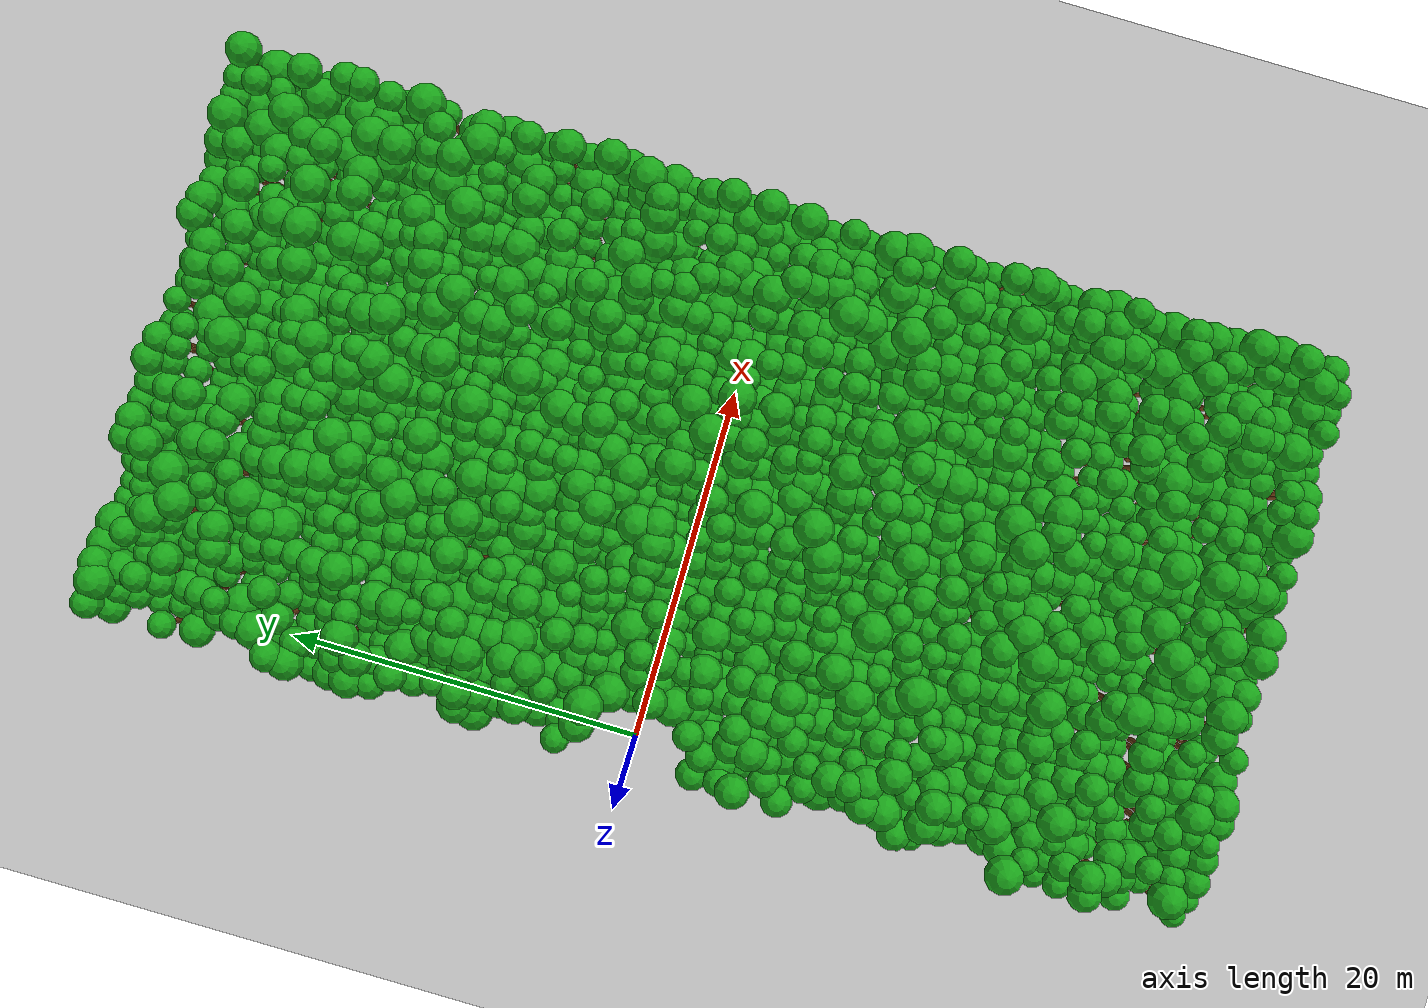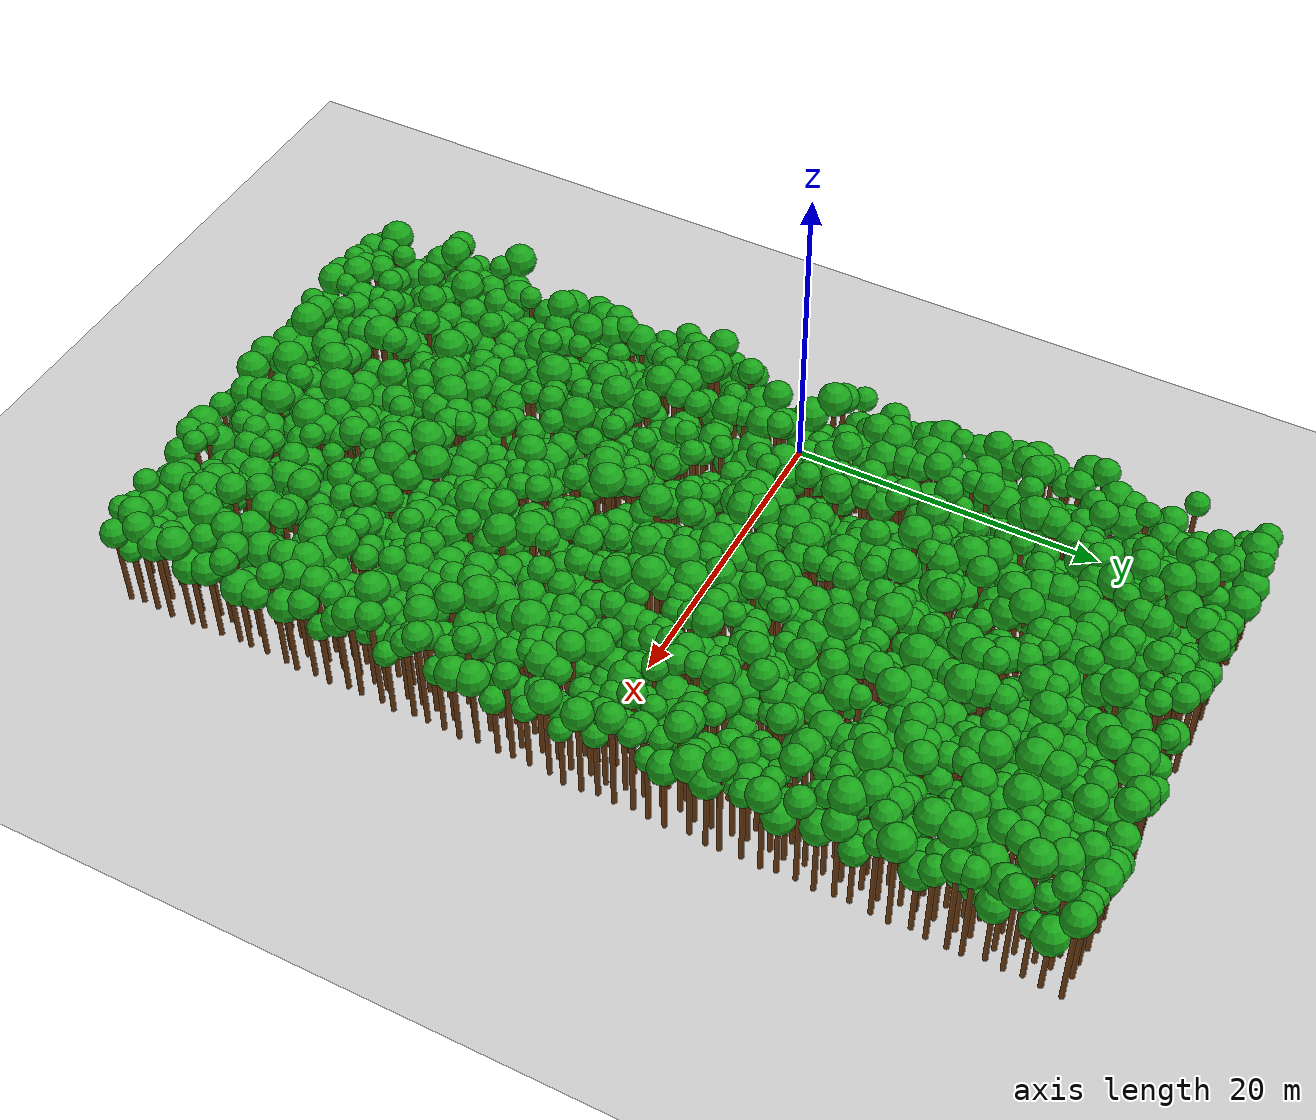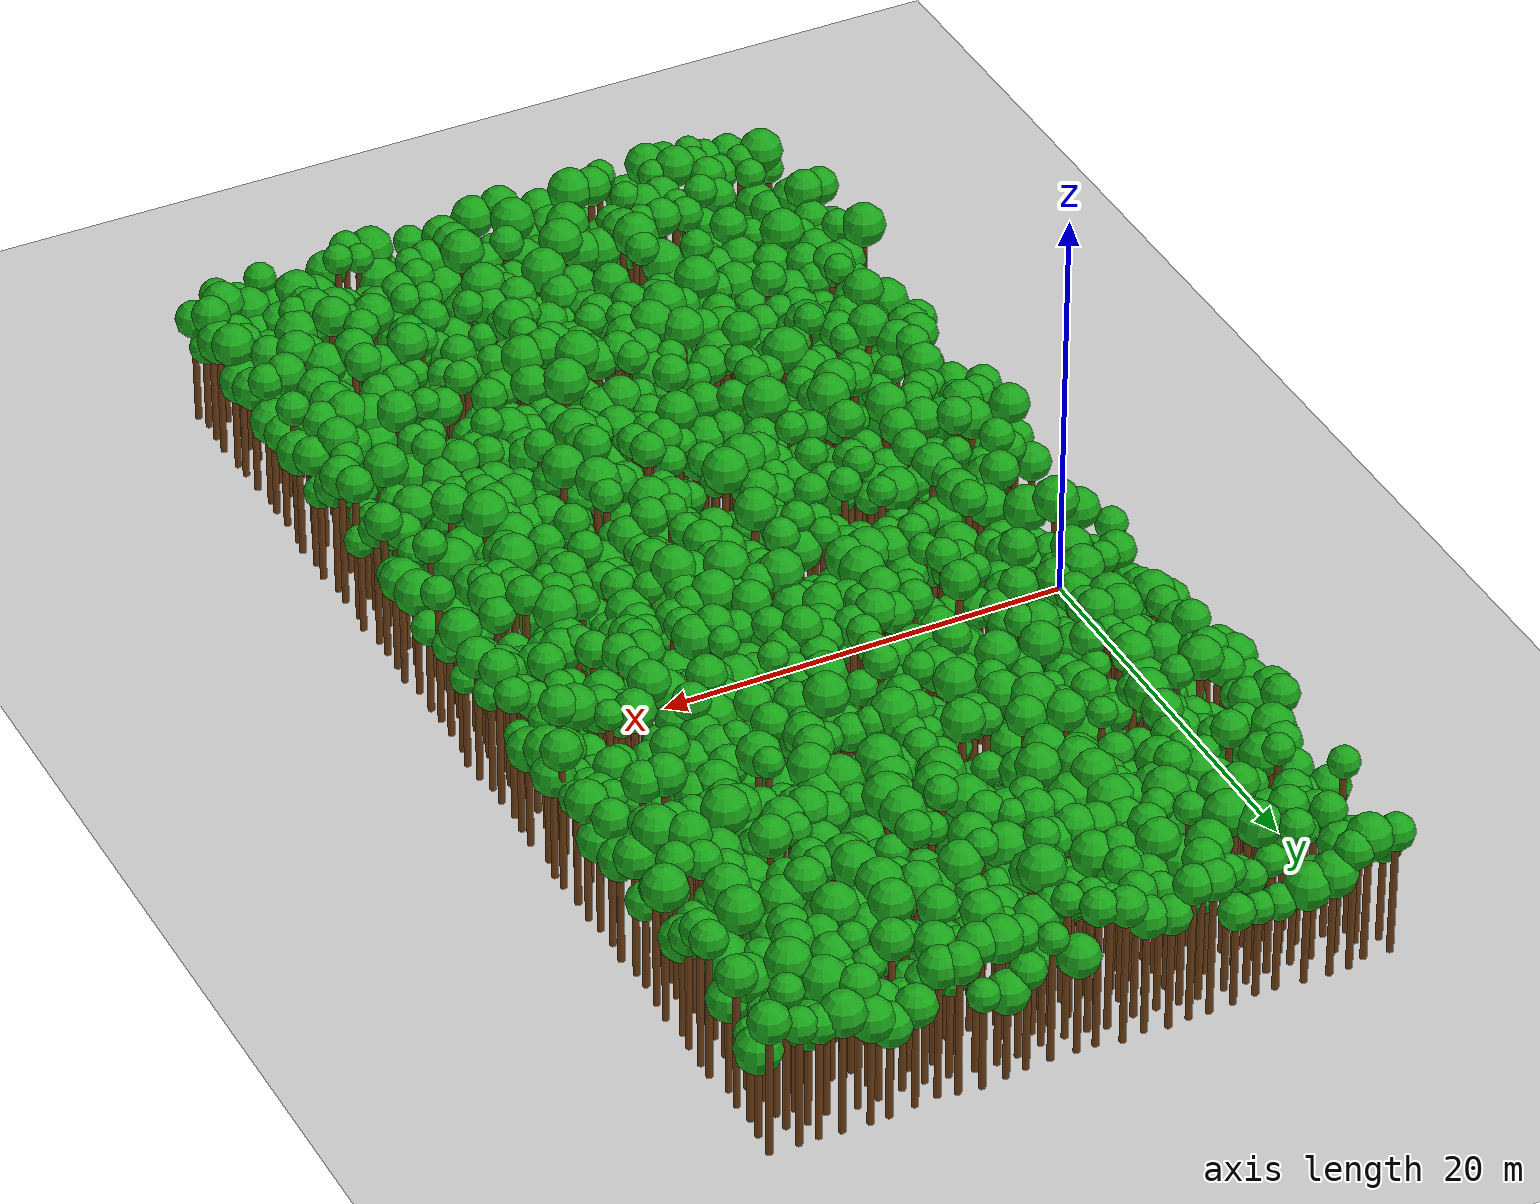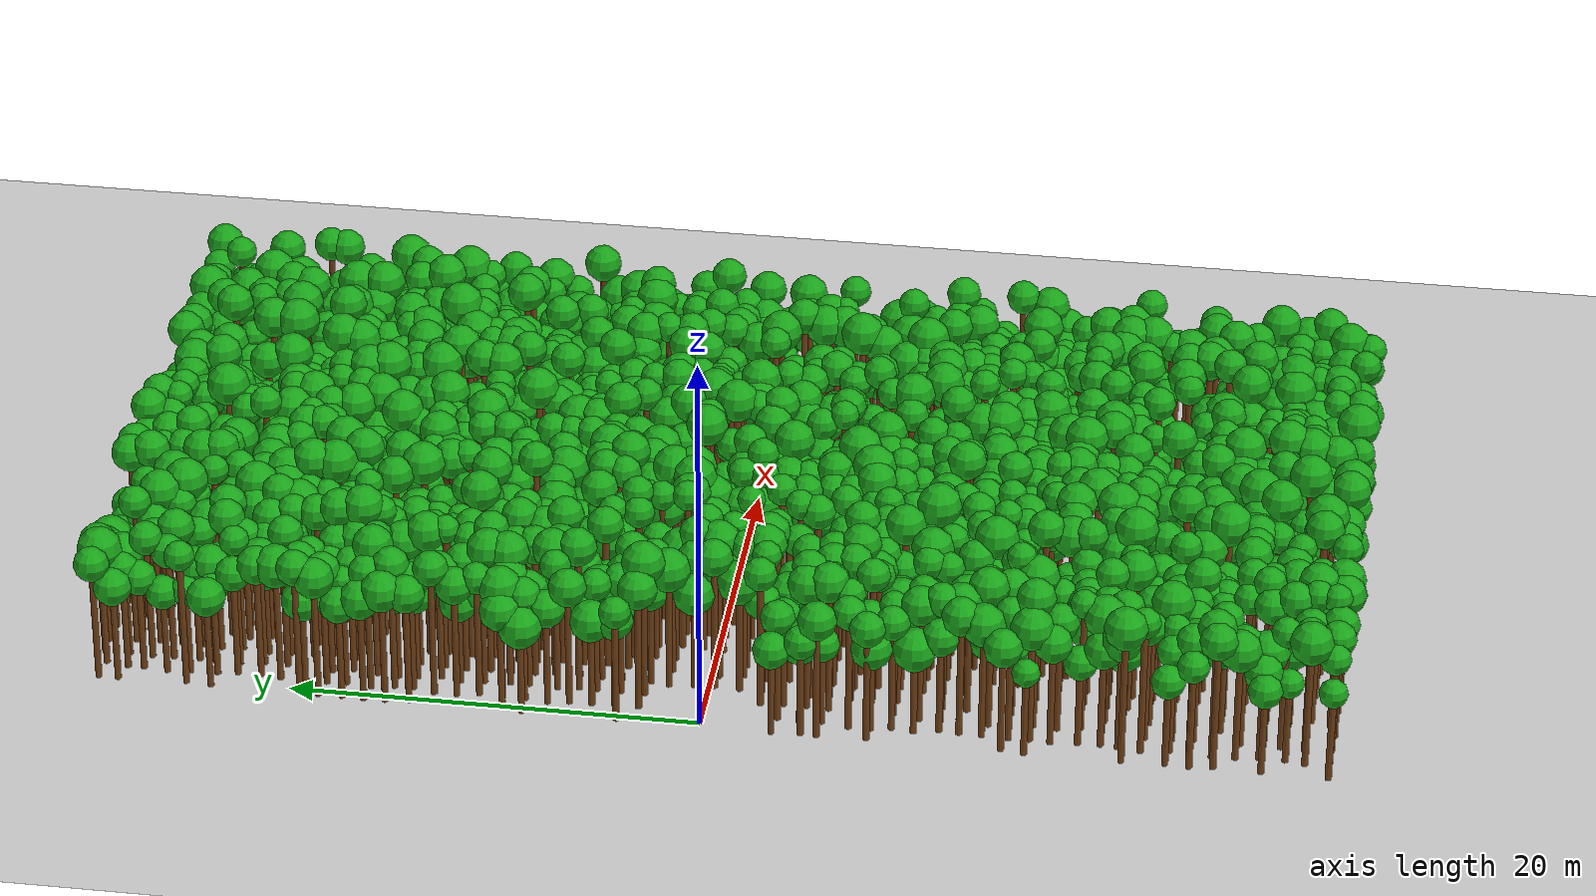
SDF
<sdf version="1.6">
 <world name="forest_world">
  <include><uri>model://sun</uri></include>
  <include><uri>model://ground_plane</uri></include>
  <model name="tree_1477_trunk">
   <static>true</static>
   <pose>-0.31 -30.02 2.23 0 0 0</pose>
   <link name="link">
    <collision name="collision">
     <geometry><cylinder><radius>0.16</radius><length>4.47</length></cylinder></geometry>
    </collision>
    <visual name="visual">
     <geometry><cylinder><radius>0.16</radius><length>4.47</length></cylinder></geometry>
     <material><ambient>0.35 0.20 0.05 1</ambient><diffuse>0.45 0.25 0.08 1</diffuse></material>
    </visual>
   </link>
  </model>
  <model name="tree_1477_leaf">
   <static>true</static>
   <pose>-0.31 -30.02 4.90 0 0 0</pose>
   <link name="link">
    <collision name="collision"><geometry><sphere><radius>0.71</radius></sphere></geometry></collision>
    <visual name="visual">
     <geometry><sphere><radius>0.71</radius></sphere></geometry>
     <material><ambient>0.05 0.45 0.05 1</ambient><diffuse>0.10 0.65 0.10 1</diffuse></material>
    </visual>
   </link>
  </model>
  <model name="tree_1480_trunk">
   <static>true</static>
   <pose>-0.24 -26.84 2.08 0 0 0</pose>
   <link name="link">
    <collision name="collision">
     <geometry><cylinder><radius>0.16</radius><length>4.16</length></cylinder></geometry>
    </collision>
    <visual name="visual">
     <geometry><cylinder><radius>0.16</radius><length>4.16</length></cylinder></geometry>
     <material><ambient>0.35 0.20 0.05 1</ambient><diffuse>0.45 0.25 0.08 1</diffuse></material>
    </visual>
   </link>
  </model>
  <model name="tree_1480_leaf">
   <static>true</static>
   <pose>-0.24 -26.84 4.66 0 0 0</pose>
   <link name="link">
    <collision name="collision"><geometry><sphere><radius>0.84</radius></sphere></geometry></collision>
    <visual name="visual">
     <geometry><sphere><radius>0.84</radius></sphere></geometry>
     <material><ambient>0.05 0.45 0.05 1</ambient><diffuse>0.10 0.65 0.10 1</diffuse></material>
    </visual>
   </link>
  </model>
  <model name="tree_1482_trunk">
   <static>true</static>
   <pose>-0.21 -24.56 3.34 0 0 0</pose>
   <link name="link">
    <collision name="collision">
     <geometry><cylinder><radius>0.16</radius><length>6.68</length></cylinder></geometry>
    </collision>
    <visual name="visual">
     <geometry><cylinder><radius>0.16</radius><length>6.68</length></cylinder></geometry>
     <material><ambient>0.35 0.20 0.05 1</ambient><diffuse>0.45 0.25 0.08 1</diffuse></material>
    </visual>
   </link>
  </model>
  <model name="tree_1482_leaf">
   <static>true</static>
   <pose>-0.21 -24.56 7.23 0 0 0</pose>
   <link name="link">
    <collision name="collision"><geometry><sphere><radius>0.92</radius></sphere></geometry></collision>
    <visual name="visual">
     <geometry><sphere><radius>0.92</radius></sphere></geometry>
     <material><ambient>0.05 0.45 0.05 1</ambient><diffuse>0.10 0.65 0.10 1</diffuse></material>
    </visual>
   </link>
  </model>
  <model name="tree_1483_trunk">
   <static>true</static>
   <pose>-0.32 -23.44 2.64 0 0 0</pose>
   <link name="link">
    <collision name="collision">
     <geometry><cylinder><radius>0.16</radius><length>5.29</length></cylinder></geometry>
    </collision>
    <visual name="visual">
     <geometry><cylinder><radius>0.16</radius><length>5.29</length></cylinder></geometry>
     <material><ambient>0.35 0.20 0.05 1</ambient><diffuse>0.45 0.25 0.08 1</diffuse></material>
    </visual>
   </link>
  </model>
  <model name="tree_1483_leaf">
   <static>true</static>
   <pose>-0.32 -23.44 5.76 0 0 0</pose>
   <link name="link">
    <collision name="collision"><geometry><sphere><radius>0.79</radius></sphere></geometry></collision>
    <visual name="visual">
     <geometry><sphere><radius>0.79</radius></sphere></geometry>
     <material><ambient>0.05 0.45 0.05 1</ambient><diffuse>0.10 0.65 0.10 1</diffuse></material>
    </visual>
   </link>
  </model>
  <model name="tree_1484_trunk">
   <static>true</static>
   <pose>-0.25 -22.29 2.13 0 0 0</pose>
   <link name="link">
    <collision name="collision">
     <geometry><cylinder><radius>0.16</radius><length>4.26</length></cylinder></geometry>
    </collision>
    <visual name="visual">
     <geometry><cylinder><radius>0.16</radius><length>4.26</length></cylinder></geometry>
     <material><ambient>0.35 0.20 0.05 1</ambient><diffuse>0.45 0.25 0.08 1</diffuse></material>
    </visual>
   </link>
  </model>
  <model name="tree_1484_leaf">
   <static>true</static>
   <pose>-0.25 -22.29 4.76 0 0 0</pose>
   <link name="link">
    <collision name="collision"><geometry><sphere><radius>0.84</radius></sphere></geometry></collision>
    <visual name="visual">
     <geometry><sphere><radius>0.84</radius></sphere></geometry>
     <material><ambient>0.05 0.45 0.05 1</ambient><diffuse>0.10 0.65 0.10 1</diffuse></material>
    </visual>
   </link>
  </model>
  <model name="tree_1486_trunk">
   <static>true</static>
   <pose>-0.32 -20.21 3.49 0 0 0</pose>
   <link name="link">
    <collision name="collision">
     <geometry><cylinder><radius>0.16</radius><length>6.97</length></cylinder></geometry>
    </collision>
    <visual name="visual">
     <geometry><cylinder><radius>0.16</radius><length>6.97</length></cylinder></geometry>
     <material><ambient>0.35 0.20 0.05 1</ambient><diffuse>0.45 0.25 0.08 1</diffuse></material>
    </visual>
   </link>
  </model>
  <model name="tree_1486_leaf">
   <static>true</static>
   <pose>-0.32 -20.21 7.61 0 0 0</pose>
   <link name="link">
    <collision name="collision"><geometry><sphere><radius>1.06</radius></sphere></geometry></collision>
    <visual name="visual">
     <geometry><sphere><radius>1.06</radius></sphere></geometry>
     <material><ambient>0.05 0.45 0.05 1</ambient><diffuse>0.10 0.65 0.10 1</diffuse></material>
    </visual>
   </link>
  </model>
  <model name="tree_1490_trunk">
   <static>true</static>
   <pose>-0.35 -15.59 2.12 0 0 0</pose>
   <link name="link">
    <collision name="collision">
     <geometry><cylinder><radius>0.16</radius><length>4.23</length></cylinder></geometry>
    </collision>
    <visual name="visual">
     <geometry><cylinder><radius>0.16</radius><length>4.23</length></cylinder></geometry>
     <material><ambient>0.35 0.20 0.05 1</ambient><diffuse>0.45 0.25 0.08 1</diffuse></material>
    </visual>
   </link>
  </model>
  <model name="tree_1490_leaf">
   <static>true</static>
   <pose>-0.35 -15.59 4.66 0 0 0</pose>
   <link name="link">
    <collision name="collision"><geometry><sphere><radius>0.70</radius></sphere></geometry></collision>
    <visual name="visual">
     <geometry><sphere><radius>0.70</radius></sphere></geometry>
     <material><ambient>0.05 0.45 0.05 1</ambient><diffuse>0.10 0.65 0.10 1</diffuse></material>
    </visual>
   </link>
  </model>
  <model name="tree_1491_trunk">
   <static>true</static>
   <pose>-0.15 -14.46 2.63 0 0 0</pose>
   <link name="link">
    <collision name="collision">
     <geometry><cylinder><radius>0.16</radius><length>5.27</length></cylinder></geometry>
    </collision>
    <visual name="visual">
     <geometry><cylinder><radius>0.16</radius><length>5.27</length></cylinder></geometry>
     <material><ambient>0.35 0.20 0.05 1</ambient><diffuse>0.45 0.25 0.08 1</diffuse></material>
    </visual>
   </link>
  </model>
  <model name="tree_1491_leaf">
   <static>true</static>
   <pose>-0.15 -14.46 5.84 0 0 0</pose>
   <link name="link">
    <collision name="collision"><geometry><sphere><radius>0.96</radius></sphere></geometry></collision>
    <visual name="visual">
     <geometry><sphere><radius>0.96</radius></sphere></geometry>
     <material><ambient>0.05 0.45 0.05 1</ambient><diffuse>0.10 0.65 0.10 1</diffuse></material>
    </visual>
   </link>
  </model>
  <model name="tree_1497_trunk">
   <static>true</static>
   <pose>-0.18 -8.03 2.88 0 0 0</pose>
   <link name="link">
    <collision name="collision">
     <geometry><cylinder><radius>0.16</radius><length>5.76</length></cylinder></geometry>
    </collision>
    <visual name="visual">
     <geometry><cylinder><radius>0.16</radius><length>5.76</length></cylinder></geometry>
     <material><ambient>0.35 0.20 0.05 1</ambient><diffuse>0.45 0.25 0.08 1</diffuse></material>
    </visual>
   </link>
  </model>
  <model name="tree_1497_leaf">
   <static>true</static>
   <pose>-0.18 -8.03 6.29 0 0 0</pose>
   <link name="link">
    <collision name="collision"><geometry><sphere><radius>0.88</radius></sphere></geometry></collision>
    <visual name="visual">
     <geometry><sphere><radius>0.88</radius></sphere></geometry>
     <material><ambient>0.05 0.45 0.05 1</ambient><diffuse>0.10 0.65 0.10 1</diffuse></material>
    </visual>
   </link>
  </model>
  <model name="tree_1499_trunk">
   <static>true</static>
   <pose>-0.29 -5.65 3.02 0 0 0</pose>
   <link name="link">
    <collision name="collision">
     <geometry><cylinder><radius>0.16</radius><length>6.04</length></cylinder></geometry>
    </collision>
    <visual name="visual">
     <geometry><cylinder><radius>0.16</radius><length>6.04</length></cylinder></geometry>
     <material><ambient>0.35 0.20 0.05 1</ambient><diffuse>0.45 0.25 0.08 1</diffuse></material>
    </visual>
   </link>
  </model>
  <model name="tree_1499_leaf">
   <static>true</static>
   <pose>-0.29 -5.65 6.62 0 0 0</pose>
   <link name="link">
    <collision name="collision"><geometry><sphere><radius>0.96</radius></sphere></geometry></collision>
    <visual name="visual">
     <geometry><sphere><radius>0.96</radius></sphere></geometry>
     <material><ambient>0.05 0.45 0.05 1</ambient><diffuse>0.10 0.65 0.10 1</diffuse></material>
    </visual>
   </link>
  </model>
  <model name="tree_1500_trunk">
   <static>true</static>
   <pose>-0.22 -4.87 2.38 0 0 0</pose>
   <link name="link">
    <collision name="collision">
     <geometry><cylinder><radius>0.16</radius><length>4.76</length></cylinder></geometry>
    </collision>
    <visual name="visual">
     <geometry><cylinder><radius>0.16</radius><length>4.76</length></cylinder></geometry>
     <material><ambient>0.35 0.20 0.05 1</ambient><diffuse>0.45 0.25 0.08 1</diffuse></material>
    </visual>
   </link>
  </model>
  <model name="tree_1500_leaf">
   <static>true</static>
   <pose>-0.22 -4.87 5.27 0 0 0</pose>
   <link name="link">
    <collision name="collision"><geometry><sphere><radius>0.84</radius></sphere></geometry></collision>
    <visual name="visual">
     <geometry><sphere><radius>0.84</radius></sphere></geometry>
     <material><ambient>0.05 0.45 0.05 1</ambient><diffuse>0.10 0.65 0.10 1</diffuse></material>
    </visual>
   </link>
  </model>
  <model name="tree_1501_trunk">
   <static>true</static>
   <pose>-0.32 -3.48 2.10 0 0 0</pose>
   <link name="link">
    <collision name="collision">
     <geometry><cylinder><radius>0.16</radius><length>4.21</length></cylinder></geometry>
    </collision>
    <visual name="visual">
     <geometry><cylinder><radius>0.16</radius><length>4.21</length></cylinder></geometry>
     <material><ambient>0.35 0.20 0.05 1</ambient><diffuse>0.45 0.25 0.08 1</diffuse></material>
    </visual>
   </link>
  </model>
  <model name="tree_1501_leaf">
   <static>true</static>
   <pose>-0.32 -3.48 4.76 0 0 0</pose>
   <link name="link">
    <collision name="collision"><geometry><sphere><radius>0.92</radius></sphere></geometry></collision>
    <visual name="visual">
     <geometry><sphere><radius>0.92</radius></sphere></geometry>
     <material><ambient>0.05 0.45 0.05 1</ambient><diffuse>0.10 0.65 0.10 1</diffuse></material>
    </visual>
   </link>
  </model>
  <model name="tree_1502_trunk">
   <static>true</static>
   <pose>-0.30 4.01 2.85 0 0 0</pose>
   <link name="link">
    <collision name="collision">
     <geometry><cylinder><radius>0.16</radius><length>5.70</length></cylinder></geometry>
    </collision>
    <visual name="visual">
     <geometry><cylinder><radius>0.16</radius><length>5.70</length></cylinder></geometry>
     <material><ambient>0.35 0.20 0.05 1</ambient><diffuse>0.45 0.25 0.08 1</diffuse></material>
    </visual>
   </link>
  </model>
  <model name="tree_1502_leaf">
   <static>true</static>
   <pose>-0.30 4.01 6.18 0 0 0</pose>
   <link name="link">
    <collision name="collision"><geometry><sphere><radius>0.79</radius></sphere></geometry></collision>
    <visual name="visual">
     <geometry><sphere><radius>0.79</radius></sphere></geometry>
     <material><ambient>0.05 0.45 0.05 1</ambient><diffuse>0.10 0.65 0.10 1</diffuse></material>
    </visual>
   </link>
  </model>
  <model name="tree_1506_trunk">
   <static>true</static>
   <pose>-0.32 8.59 2.13 0 0 0</pose>
   <link name="link">
    <collision name="collision">
     <geometry><cylinder><radius>0.16</radius><length>4.26</length></cylinder></geometry>
    </collision>
    <visual name="visual">
     <geometry><cylinder><radius>0.16</radius><length>4.26</length></cylinder></geometry>
     <material><ambient>0.35 0.20 0.05 1</ambient><diffuse>0.45 0.25 0.08 1</diffuse></material>
    </visual>
   </link>
  </model>
  <model name="tree_1506_leaf">
   <static>true</static>
   <pose>-0.32 8.59 4.91 0 0 0</pose>
   <link name="link">
    <collision name="collision"><geometry><sphere><radius>1.08</radius></sphere></geometry></collision>
    <visual name="visual">
     <geometry><sphere><radius>1.08</radius></sphere></geometry>
     <material><ambient>0.05 0.45 0.05 1</ambient><diffuse>0.10 0.65 0.10 1</diffuse></material>
    </visual>
   </link>
  </model>
  <model name="tree_1507_trunk">
   <static>true</static>
   <pose>-0.17 9.57 2.52 0 0 0</pose>
   <link name="link">
    <collision name="collision">
     <geometry><cylinder><radius>0.16</radius><length>5.03</length></cylinder></geometry>
    </collision>
    <visual name="visual">
     <geometry><cylinder><radius>0.16</radius><length>5.03</length></cylinder></geometry>
     <material><ambient>0.35 0.20 0.05 1</ambient><diffuse>0.45 0.25 0.08 1</diffuse></material>
    </visual>
   </link>
  </model>
  <model name="tree_1507_leaf">
   <static>true</static>
   <pose>-0.17 9.57 5.63 0 0 0</pose>
   <link name="link">
    <collision name="collision"><geometry><sphere><radius>1.00</radius></sphere></geometry></collision>
    <visual name="visual">
     <geometry><sphere><radius>1.00</radius></sphere></geometry>
     <material><ambient>0.05 0.45 0.05 1</ambient><diffuse>0.10 0.65 0.10 1</diffuse></material>
    </visual>
   </link>
  </model>
  <model name="tree_1511_trunk">
   <static>true</static>
   <pose>-0.17 14.11 2.80 0 0 0</pose>
   <link name="link">
    <collision name="collision">
     <geometry><cylinder><radius>0.16</radius><length>5.60</length></cylinder></geometry>
    </collision>
    <visual name="visual">
     <geometry><cylinder><radius>0.16</radius><length>5.60</length></cylinder></geometry>
     <material><ambient>0.35 0.20 0.05 1</ambient><diffuse>0.45 0.25 0.08 1</diffuse></material>
    </visual>
   </link>
  </model>
  <model name="tree_1511_leaf">
   <static>true</static>
   <pose>-0.17 14.11 6.17 0 0 0</pose>
   <link name="link">
    <collision name="collision"><geometry><sphere><radius>0.94</radius></sphere></geometry></collision>
    <visual name="visual">
     <geometry><sphere><radius>0.94</radius></sphere></geometry>
     <material><ambient>0.05 0.45 0.05 1</ambient><diffuse>0.10 0.65 0.10 1</diffuse></material>
    </visual>
   </link>
  </model>
  <model name="tree_1512_trunk">
   <static>true</static>
   <pose>-0.33 15.25 2.86 0 0 0</pose>
   <link name="link">
    <collision name="collision">
     <geometry><cylinder><radius>0.16</radius><length>5.71</length></cylinder></geometry>
    </collision>
    <visual name="visual">
     <geometry><cylinder><radius>0.16</radius><length>5.71</length></cylinder></geometry>
     <material><ambient>0.35 0.20 0.05 1</ambient><diffuse>0.45 0.25 0.08 1</diffuse></material>
    </visual>
   </link>
  </model>
  <model name="tree_1512_leaf">
   <static>true</static>
   <pose>-0.33 15.25 6.33 0 0 0</pose>
   <link name="link">
    <collision name="collision"><geometry><sphere><radius>1.03</radius></sphere></geometry></collision>
    <visual name="visual">
     <geometry><sphere><radius>1.03</radius></sphere></geometry>
     <material><ambient>0.05 0.45 0.05 1</ambient><diffuse>0.10 0.65 0.10 1</diffuse></material>
    </visual>
   </link>
  </model>
  <model name="tree_1513_trunk">
   <static>true</static>
   <pose>-0.34 16.30 2.58 0 0 0</pose>
   <link name="link">
    <collision name="collision">
     <geometry><cylinder><radius>0.16</radius><length>5.17</length></cylinder></geometry>
    </collision>
    <visual name="visual">
     <geometry><cylinder><radius>0.16</radius><length>5.17</length></cylinder></geometry>
     <material><ambient>0.35 0.20 0.05 1</ambient><diffuse>0.45 0.25 0.08 1</diffuse></material>
    </visual>
   </link>
  </model>
  <model name="tree_1513_leaf">
   <static>true</static>
   <pose>-0.34 16.30 5.77 0 0 0</pose>
   <link name="link">
    <collision name="collision"><geometry><sphere><radius>1.00</radius></sphere></geometry></collision>
    <visual name="visual">
     <geometry><sphere><radius>1.00</radius></sphere></geometry>
     <material><ambient>0.05 0.45 0.05 1</ambient><diffuse>0.10 0.65 0.10 1</diffuse></material>
    </visual>
   </link>
  </model>
  <model name="tree_1514_trunk">
   <static>true</static>
   <pose>-0.30 17.37 2.39 0 0 0</pose>
   <link name="link">
    <collision name="collision">
     <geometry><cylinder><radius>0.16</radius><length>4.79</length></cylinder></geometry>
    </collision>
    <visual name="visual">
     <geometry><cylinder><radius>0.16</radius><length>4.79</length></cylinder></geometry>
     <material><ambient>0.35 0.20 0.05 1</ambient><diffuse>0.45 0.25 0.08 1</diffuse></material>
    </visual>
   </link>
  </model>
  <model name="tree_1514_leaf">
   <static>true</static>
   <pose>-0.30 17.37 5.33 0 0 0</pose>
   <link name="link">
    <collision name="collision"><geometry><sphere><radius>0.91</radius></sphere></geometry></collision>
    <visual name="visual">
     <geometry><sphere><radius>0.91</radius></sphere></geometry>
     <material><ambient>0.05 0.45 0.05 1</ambient><diffuse>0.10 0.65 0.10 1</diffuse></material>
    </visual>
   </link>
  </model>
  <model name="tree_1515_trunk">
   <static>true</static>
   <pose>-0.32 18.52 3.08 0 0 0</pose>
   <link name="link">
    <collision name="collision">
     <geometry><cylinder><radius>0.16</radius><length>6.16</length></cylinder></geometry>
    </collision>
    <visual name="visual">
     <geometry><cylinder><radius>0.16</radius><length>6.16</length></cylinder></geometry>
     <material><ambient>0.35 0.20 0.05 1</ambient><diffuse>0.45 0.25 0.08 1</diffuse></material>
    </visual>
   </link>
  </model>
  <model name="tree_1515_leaf">
   <static>true</static>
   <pose>-0.32 18.52 6.76 0 0 0</pose>
   <link name="link">
    <collision name="collision"><geometry><sphere><radius>1.00</radius></sphere></geometry></collision>
    <visual name="visual">
     <geometry><sphere><radius>1.00</radius></sphere></geometry>
     <material><ambient>0.05 0.45 0.05 1</ambient><diffuse>0.10 0.65 0.10 1</diffuse></material>
    </visual>
   </link>
  </model>
  <model name="tree_1516_trunk">
   <static>true</static>
   <pose>-0.20 19.46 3.32 0 0 0</pose>
   <link name="link">
    <collision name="collision">
     <geometry><cylinder><radius>0.16</radius><length>6.64</length></cylinder></geometry>
    </collision>
    <visual name="visual">
     <geometry><cylinder><radius>0.16</radius><length>6.64</length></cylinder></geometry>
     <material><ambient>0.35 0.20 0.05 1</ambient><diffuse>0.45 0.25 0.08 1</diffuse></material>
    </visual>
   </link>
  </model>
  <model name="tree_1516_leaf">
   <static>true</static>
   <pose>-0.20 19.46 7.17 0 0 0</pose>
   <link name="link">
    <collision name="collision"><geometry><sphere><radius>0.89</radius></sphere></geometry></collision>
    <visual name="visual">
     <geometry><sphere><radius>0.89</radius></sphere></geometry>
     <material><ambient>0.05 0.45 0.05 1</ambient><diffuse>0.10 0.65 0.10 1</diffuse></material>
    </visual>
   </link>
  </model>
  <model name="tree_1520_trunk">
   <static>true</static>
   <pose>-0.25 23.83 2.27 0 0 0</pose>
   <link name="link">
    <collision name="collision">
     <geometry><cylinder><radius>0.16</radius><length>4.54</length></cylinder></geometry>
    </collision>
    <visual name="visual">
     <geometry><cylinder><radius>0.16</radius><length>4.54</length></cylinder></geometry>
     <material><ambient>0.35 0.20 0.05 1</ambient><diffuse>0.45 0.25 0.08 1</diffuse></material>
    </visual>
   </link>
  </model>
  <model name="tree_1520_leaf">
   <static>true</static>
   <pose>-0.25 23.83 5.12 0 0 0</pose>
   <link name="link">
    <collision name="collision"><geometry><sphere><radius>0.97</radius></sphere></geometry></collision>
    <visual name="visual">
     <geometry><sphere><radius>0.97</radius></sphere></geometry>
     <material><ambient>0.05 0.45 0.05 1</ambient><diffuse>0.10 0.65 0.10 1</diffuse></material>
    </visual>
   </link>
  </model>
  <model name="tree_1521_trunk">
   <static>true</static>
   <pose>-0.15 25.05 3.43 0 0 0</pose>
   <link name="link">
    <collision name="collision">
     <geometry><cylinder><radius>0.16</radius><length>6.85</length></cylinder></geometry>
    </collision>
    <visual name="visual">
     <geometry><cylinder><radius>0.16</radius><length>6.85</length></cylinder></geometry>
     <material><ambient>0.35 0.20 0.05 1</ambient><diffuse>0.45 0.25 0.08 1</diffuse></material>
    </visual>
   </link>
  </model>
  <model name="tree_1521_leaf">
   <static>true</static>
   <pose>-0.15 25.05 7.30 0 0 0</pose>
   <link name="link">
    <collision name="collision"><geometry><sphere><radius>0.75</radius></sphere></geometry></collision>
    <visual name="visual">
     <geometry><sphere><radius>0.75</radius></sphere></geometry>
     <material><ambient>0.05 0.45 0.05 1</ambient><diffuse>0.10 0.65 0.10 1</diffuse></material>
    </visual>
   </link>
  </model>
  <model name="tree_1524_trunk">
   <static>true</static>
   <pose>-0.28 28.40 2.36 0 0 0</pose>
   <link name="link">
    <collision name="collision">
     <geometry><cylinder><radius>0.16</radius><length>4.73</length></cylinder></geometry>
    </collision>
    <visual name="visual">
     <geometry><cylinder><radius>0.16</radius><length>4.73</length></cylinder></geometry>
     <material><ambient>0.35 0.20 0.05 1</ambient><diffuse>0.45 0.25 0.08 1</diffuse></material>
    </visual>
   </link>
  </model>
  <model name="tree_1524_leaf">
   <static>true</static>
   <pose>-0.28 28.40 5.29 0 0 0</pose>
   <link name="link">
    <collision name="collision"><geometry><sphere><radius>0.94</radius></sphere></geometry></collision>
    <visual name="visual">
     <geometry><sphere><radius>0.94</radius></sphere></geometry>
     <material><ambient>0.05 0.45 0.05 1</ambient><diffuse>0.10 0.65 0.10 1</diffuse></material>
    </visual>
   </link>
  </model>
  <model name="tree_1525_trunk">
   <static>true</static>
   <pose>-0.27 29.36 2.99 0 0 0</pose>
   <link name="link">
    <collision name="collision">
     <geometry><cylinder><radius>0.16</radius><length>5.98</length></cylinder></geometry>
    </collision>
    <visual name="visual">
     <geometry><cylinder><radius>0.16</radius><length>5.98</length></cylinder></geometry>
     <material><ambient>0.35 0.20 0.05 1</ambient><diffuse>0.45 0.25 0.08 1</diffuse></material>
    </visual>
   </link>
  </model>
  <model name="tree_1525_leaf">
   <static>true</static>
   <pose>-0.27 29.36 6.50 0 0 0</pose>
   <link name="link">
    <collision name="collision"><geometry><sphere><radius>0.87</radius></sphere></geometry></collision>
    <visual name="visual">
     <geometry><sphere><radius>0.87</radius></sphere></geometry>
     <material><ambient>0.05 0.45 0.05 1</ambient><diffuse>0.10 0.65 0.10 1</diffuse></material>
    </visual>
   </link>
  </model>
  <model name="tree_1526_trunk">
   <static>true</static>
   <pose>0.84 -30.00 2.79 0 0 0</pose>
   <link name="link">
    <collision name="collision">
     <geometry><cylinder><radius>0.16</radius><length>5.59</length></cylinder></geometry>
    </collision>
    <visual name="visual">
     <geometry><cylinder><radius>0.16</radius><length>5.59</length></cylinder></geometry>
     <material><ambient>0.35 0.20 0.05 1</ambient><diffuse>0.45 0.25 0.08 1</diffuse></material>
    </visual>
   </link>
  </model>
  <model name="tree_1526_leaf">
   <static>true</static>
   <pose>0.84 -30.00 6.04 0 0 0</pose>
   <link name="link">
    <collision name="collision"><geometry><sphere><radius>0.76</radius></sphere></geometry></collision>
    <visual name="visual">
     <geometry><sphere><radius>0.76</radius></sphere></geometry>
     <material><ambient>0.05 0.45 0.05 1</ambient><diffuse>0.10 0.65 0.10 1</diffuse></material>
    </visual>
   </link>
  </model>
  <model name="tree_1527_trunk">
   <static>true</static>
   <pose>0.71 -28.85 3.15 0 0 0</pose>
   <link name="link">
    <collision name="collision">
     <geometry><cylinder><radius>0.16</radius><length>6.31</length></cylinder></geometry>
    </collision>
    <visual name="visual">
     <geometry><cylinder><radius>0.16</radius><length>6.31</length></cylinder></geometry>
     <material><ambient>0.35 0.20 0.05 1</ambient><diffuse>0.45 0.25 0.08 1</diffuse></material>
    </visual>
   </link>
  </model>
  <model name="tree_1527_leaf">
   <static>true</static>
   <pose>0.71 -28.85 6.94 0 0 0</pose>
   <link name="link">
    <collision name="collision"><geometry><sphere><radius>1.06</radius></sphere></geometry></collision>
    <visual name="visual">
     <geometry><sphere><radius>1.06</radius></sphere></geometry>
     <material><ambient>0.05 0.45 0.05 1</ambient><diffuse>0.10 0.65 0.10 1</diffuse></material>
    </visual>
   </link>
  </model>
  <model name="tree_1528_trunk">
   <static>true</static>
   <pose>0.85 -27.91 2.02 0 0 0</pose>
   <link name="link">
    <collision name="collision">
     <geometry><cylinder><radius>0.16</radius><length>4.04</length></cylinder></geometry>
    </collision>
    <visual name="visual">
     <geometry><cylinder><radius>0.16</radius><length>4.04</length></cylinder></geometry>
     <material><ambient>0.35 0.20 0.05 1</ambient><diffuse>0.45 0.25 0.08 1</diffuse></material>
    </visual>
   </link>
  </model>
  <model name="tree_1528_leaf">
   <static>true</static>
   <pose>0.85 -27.91 4.47 0 0 0</pose>
   <link name="link">
    <collision name="collision"><geometry><sphere><radius>0.72</radius></sphere></geometry></collision>
    <visual name="visual">
     <geometry><sphere><radius>0.72</radius></sphere></geometry>
     <material><ambient>0.05 0.45 0.05 1</ambient><diffuse>0.10 0.65 0.10 1</diffuse></material>
    </visual>
   </link>
  </model>
  <model name="tree_1529_trunk">
   <static>true</static>
   <pose>0.85 -26.67 2.19 0 0 0</pose>
   <link name="link">
    <collision name="collision">
     <geometry><cylinder><radius>0.16</radius><length>4.38</length></cylinder></geometry>
    </collision>
    <visual name="visual">
     <geometry><cylinder><radius>0.16</radius><length>4.38</length></cylinder></geometry>
     <material><ambient>0.35 0.20 0.05 1</ambient><diffuse>0.45 0.25 0.08 1</diffuse></material>
    </visual>
   </link>
  </model>
  <model name="tree_1529_leaf">
   <static>true</static>
   <pose>0.85 -26.67 4.96 0 0 0</pose>
   <link name="link">
    <collision name="collision"><geometry><sphere><radius>0.96</radius></sphere></geometry></collision>
    <visual name="visual">
     <geometry><sphere><radius>0.96</radius></sphere></geometry>
     <material><ambient>0.05 0.45 0.05 1</ambient><diffuse>0.10 0.65 0.10 1</diffuse></material>
    </visual>
   </link>
  </model>
  <model name="tree_1530_trunk">
   <static>true</static>
   <pose>0.72 -25.55 2.78 0 0 0</pose>
   <link name="link">
    <collision name="collision">
     <geometry><cylinder><radius>0.16</radius><length>5.56</length></cylinder></geometry>
    </collision>
    <visual name="visual">
     <geometry><cylinder><radius>0.16</radius><length>5.56</length></cylinder></geometry>
     <material><ambient>0.35 0.20 0.05 1</ambient><diffuse>0.45 0.25 0.08 1</diffuse></material>
    </visual>
   </link>
  </model>
  <model name="tree_1530_leaf">
   <static>true</static>
   <pose>0.72 -25.55 6.18 0 0 0</pose>
   <link name="link">
    <collision name="collision"><geometry><sphere><radius>1.03</radius></sphere></geometry></collision>
    <visual name="visual">
     <geometry><sphere><radius>1.03</radius></sphere></geometry>
     <material><ambient>0.05 0.45 0.05 1</ambient><diffuse>0.10 0.65 0.10 1</diffuse></material>
    </visual>
   </link>
  </model>
  <model name="tree_1531_trunk">
   <static>true</static>
   <pose>0.66 -24.43 3.40 0 0 0</pose>
   <link name="link">
    <collision name="collision">
     <geometry><cylinder><radius>0.16</radius><length>6.80</length></cylinder></geometry>
    </collision>
    <visual name="visual">
     <geometry><cylinder><radius>0.16</radius><length>6.80</length></cylinder></geometry>
     <material><ambient>0.35 0.20 0.05 1</ambient><diffuse>0.45 0.25 0.08 1</diffuse></material>
    </visual>
   </link>
  </model>
  <model name="tree_1531_leaf">
   <static>true</static>
   <pose>0.66 -24.43 7.37 0 0 0</pose>
   <link name="link">
    <collision name="collision"><geometry><sphere><radius>0.95</radius></sphere></geometry></collision>
    <visual name="visual">
     <geometry><sphere><radius>0.95</radius></sphere></geometry>
     <material><ambient>0.05 0.45 0.05 1</ambient><diffuse>0.10 0.65 0.10 1</diffuse></material>
    </visual>
   </link>
  </model>
  <model name="tree_1532_trunk">
   <static>true</static>
   <pose>0.83 -23.35 2.95 0 0 0</pose>
   <link name="link">
    <collision name="collision">
     <geometry><cylinder><radius>0.16</radius><length>5.90</length></cylinder></geometry>
    </collision>
    <visual name="visual">
     <geometry><cylinder><radius>0.16</radius><length>5.90</length></cylinder></geometry>
     <material><ambient>0.35 0.20 0.05 1</ambient><diffuse>0.45 0.25 0.08 1</diffuse></material>
    </visual>
   </link>
  </model>
  <model name="tree_1532_leaf">
   <static>true</static>
   <pose>0.83 -23.35 6.42 0 0 0</pose>
   <link name="link">
    <collision name="collision"><geometry><sphere><radius>0.87</radius></sphere></geometry></collision>
    <visual name="visual">
     <geometry><sphere><radius>0.87</radius></sphere></geometry>
     <material><ambient>0.05 0.45 0.05 1</ambient><diffuse>0.10 0.65 0.10 1</diffuse></material>
    </visual>
   </link>
  </model>
  <model name="tree_1533_trunk">
   <static>true</static>
   <pose>0.83 -22.41 2.64 0 0 0</pose>
   <link name="link">
    <collision name="collision">
     <geometry><cylinder><radius>0.16</radius><length>5.27</length></cylinder></geometry>
    </collision>
    <visual name="visual">
     <geometry><cylinder><radius>0.16</radius><length>5.27</length></cylinder></geometry>
     <material><ambient>0.35 0.20 0.05 1</ambient><diffuse>0.45 0.25 0.08 1</diffuse></material>
    </visual>
   </link>
  </model>
  <model name="tree_1533_leaf">
   <static>true</static>
   <pose>0.83 -22.41 5.76 0 0 0</pose>
   <link name="link">
    <collision name="collision"><geometry><sphere><radius>0.82</radius></sphere></geometry></collision>
    <visual name="visual">
     <geometry><sphere><radius>0.82</radius></sphere></geometry>
     <material><ambient>0.05 0.45 0.05 1</ambient><diffuse>0.10 0.65 0.10 1</diffuse></material>
    </visual>
   </link>
  </model>
  <model name="tree_1534_trunk">
   <static>true</static>
   <pose>0.62 -21.05 3.47 0 0 0</pose>
   <link name="link">
    <collision name="collision">
     <geometry><cylinder><radius>0.16</radius><length>6.93</length></cylinder></geometry>
    </collision>
    <visual name="visual">
     <geometry><cylinder><radius>0.16</radius><length>6.93</length></cylinder></geometry>
     <material><ambient>0.35 0.20 0.05 1</ambient><diffuse>0.45 0.25 0.08 1</diffuse></material>
    </visual>
   </link>
  </model>
  <model name="tree_1534_leaf">
   <static>true</static>
   <pose>0.62 -21.05 7.39 0 0 0</pose>
   <link name="link">
    <collision name="collision"><geometry><sphere><radius>0.76</radius></sphere></geometry></collision>
    <visual name="visual">
     <geometry><sphere><radius>0.76</radius></sphere></geometry>
     <material><ambient>0.05 0.45 0.05 1</ambient><diffuse>0.10 0.65 0.10 1</diffuse></material>
    </visual>
   </link>
  </model>
  <model name="tree_1535_trunk">
   <static>true</static>
   <pose>0.78 -19.96 2.78 0 0 0</pose>
   <link name="link">
    <collision name="collision">
     <geometry><cylinder><radius>0.16</radius><length>5.55</length></cylinder></geometry>
    </collision>
    <visual name="visual">
     <geometry><cylinder><radius>0.16</radius><length>5.55</length></cylinder></geometry>
     <material><ambient>0.35 0.20 0.05 1</ambient><diffuse>0.45 0.25 0.08 1</diffuse></material>
    </visual>
   </link>
  </model>
  <model name="tree_1535_leaf">
   <static>true</static>
   <pose>0.78 -19.96 6.15 0 0 0</pose>
   <link name="link">
    <collision name="collision"><geometry><sphere><radius>1.00</radius></sphere></geometry></collision>
    <visual name="visual">
     <geometry><sphere><radius>1.00</radius></sphere></geometry>
     <material><ambient>0.05 0.45 0.05 1</ambient><diffuse>0.10 0.65 0.10 1</diffuse></material>
    </visual>
   </link>
  </model>
  <model name="tree_1536_trunk">
   <static>true</static>
   <pose>0.88 -19.12 2.47 0 0 0</pose>
   <link name="link">
    <collision name="collision">
     <geometry><cylinder><radius>0.16</radius><length>4.93</length></cylinder></geometry>
    </collision>
    <visual name="visual">
     <geometry><cylinder><radius>0.16</radius><length>4.93</length></cylinder></geometry>
     <material><ambient>0.35 0.20 0.05 1</ambient><diffuse>0.45 0.25 0.08 1</diffuse></material>
    </visual>
   </link>
  </model>
  <model name="tree_1536_leaf">
   <static>true</static>
   <pose>0.88 -19.12 5.50 0 0 0</pose>
   <link name="link">
    <collision name="collision"><geometry><sphere><radius>0.95</radius></sphere></geometry></collision>
    <visual name="visual">
     <geometry><sphere><radius>0.95</radius></sphere></geometry>
     <material><ambient>0.05 0.45 0.05 1</ambient><diffuse>0.10 0.65 0.10 1</diffuse></material>
    </visual>
   </link>
  </model>
  <model name="tree_1537_trunk">
   <static>true</static>
   <pose>0.86 -18.04 2.08 0 0 0</pose>
   <link name="link">
    <collision name="collision">
     <geometry><cylinder><radius>0.16</radius><length>4.17</length></cylinder></geometry>
    </collision>
    <visual name="visual">
     <geometry><cylinder><radius>0.16</radius><length>4.17</length></cylinder></geometry>
     <material><ambient>0.35 0.20 0.05 1</ambient><diffuse>0.45 0.25 0.08 1</diffuse></material>
    </visual>
   </link>
  </model>
  <model name="tree_1537_leaf">
   <static>true</static>
   <pose>0.86 -18.04 4.68 0 0 0</pose>
   <link name="link">
    <collision name="collision"><geometry><sphere><radius>0.86</radius></sphere></geometry></collision>
    <visual name="visual">
     <geometry><sphere><radius>0.86</radius></sphere></geometry>
     <material><ambient>0.05 0.45 0.05 1</ambient><diffuse>0.10 0.65 0.10 1</diffuse></material>
    </visual>
   </link>
  </model>
  <model name="tree_1538_trunk">
   <static>true</static>
   <pose>0.74 -16.73 2.57 0 0 0</pose>
   <link name="link">
    <collision name="collision">
     <geometry><cylinder><radius>0.16</radius><length>5.14</length></cylinder></geometry>
    </collision>
    <visual name="visual">
     <geometry><cylinder><radius>0.16</radius><length>5.14</length></cylinder></geometry>
     <material><ambient>0.35 0.20 0.05 1</ambient><diffuse>0.45 0.25 0.08 1</diffuse></material>
    </visual>
   </link>
  </model>
  <model name="tree_1538_leaf">
   <static>true</static>
   <pose>0.74 -16.73 5.72 0 0 0</pose>
   <link name="link">
    <collision name="collision"><geometry><sphere><radius>0.96</radius></sphere></geometry></collision>
    <visual name="visual">
     <geometry><sphere><radius>0.96</radius></sphere></geometry>
     <material><ambient>0.05 0.45 0.05 1</ambient><diffuse>0.10 0.65 0.10 1</diffuse></material>
    </visual>
   </link>
  </model>
  <model name="tree_1539_trunk">
   <static>true</static>
   <pose>0.81 -15.74 2.90 0 0 0</pose>
   <link name="link">
    <collision name="collision">
     <geometry><cylinder><radius>0.16</radius><length>5.79</length></cylinder></geometry>
    </collision>
    <visual name="visual">
     <geometry><cylinder><radius>0.16</radius><length>5.79</length></cylinder></geometry>
     <material><ambient>0.35 0.20 0.05 1</ambient><diffuse>0.45 0.25 0.08 1</diffuse></material>
    </visual>
   </link>
  </model>
  <model name="tree_1539_leaf">
   <static>true</static>
   <pose>0.81 -15.74 6.43 0 0 0</pose>
   <link name="link">
    <collision name="collision"><geometry><sphere><radius>1.07</radius></sphere></geometry></collision>
    <visual name="visual">
     <geometry><sphere><radius>1.07</radius></sphere></geometry>
     <material><ambient>0.05 0.45 0.05 1</ambient><diffuse>0.10 0.65 0.10 1</diffuse></material>
    </visual>
   </link>
  </model>
  <model name="tree_1540_trunk">
   <static>true</static>
   <pose>0.77 -14.73 2.34 0 0 0</pose>
   <link name="link">
    <collision name="collision">
     <geometry><cylinder><radius>0.16</radius><length>4.68</length></cylinder></geometry>
    </collision>
    <visual name="visual">
     <geometry><cylinder><radius>0.16</radius><length>4.68</length></cylinder></geometry>
     <material><ambient>0.35 0.20 0.05 1</ambient><diffuse>0.45 0.25 0.08 1</diffuse></material>
    </visual>
   </link>
  </model>
  <model name="tree_1540_leaf">
   <static>true</static>
   <pose>0.77 -14.73 5.23 0 0 0</pose>
   <link name="link">
    <collision name="collision"><geometry><sphere><radius>0.91</radius></sphere></geometry></collision>
    <visual name="visual">
     <geometry><sphere><radius>0.91</radius></sphere></geometry>
     <material><ambient>0.05 0.45 0.05 1</ambient><diffuse>0.10 0.65 0.10 1</diffuse></material>
    </visual>
   </link>
  </model>
  <model name="tree_1541_trunk">
   <static>true</static>
   <pose>0.84 -13.44 2.88 0 0 0</pose>
   <link name="link">
    <collision name="collision">
     <geometry><cylinder><radius>0.16</radius><length>5.75</length></cylinder></geometry>
    </collision>
    <visual name="visual">
     <geometry><cylinder><radius>0.16</radius><length>5.75</length></cylinder></geometry>
     <material><ambient>0.35 0.20 0.05 1</ambient><diffuse>0.45 0.25 0.08 1</diffuse></material>
    </visual>
   </link>
  </model>
  <model name="tree_1541_leaf">
   <static>true</static>
   <pose>0.84 -13.44 6.39 0 0 0</pose>
   <link name="link">
    <collision name="collision"><geometry><sphere><radius>1.07</radius></sphere></geometry></collision>
    <visual name="visual">
     <geometry><sphere><radius>1.07</radius></sphere></geometry>
     <material><ambient>0.05 0.45 0.05 1</ambient><diffuse>0.10 0.65 0.10 1</diffuse></material>
    </visual>
   </link>
  </model>
  <model name="tree_1542_trunk">
   <static>true</static>
   <pose>0.90 -12.36 3.08 0 0 0</pose>
   <link name="link">
    <collision name="collision">
     <geometry><cylinder><radius>0.16</radius><length>6.16</length></cylinder></geometry>
    </collision>
    <visual name="visual">
     <geometry><cylinder><radius>0.16</radius><length>6.16</length></cylinder></geometry>
     <material><ambient>0.35 0.20 0.05 1</ambient><diffuse>0.45 0.25 0.08 1</diffuse></material>
    </visual>
   </link>
  </model>
  <model name="tree_1542_leaf">
   <static>true</static>
   <pose>0.90 -12.36 6.73 0 0 0</pose>
   <link name="link">
    <collision name="collision"><geometry><sphere><radius>0.96</radius></sphere></geometry></collision>
    <visual name="visual">
     <geometry><sphere><radius>0.96</radius></sphere></geometry>
     <material><ambient>0.05 0.45 0.05 1</ambient><diffuse>0.10 0.65 0.10 1</diffuse></material>
    </visual>
   </link>
  </model>
  <model name="tree_1543_trunk">
   <static>true</static>
   <pose>0.97 -11.39 2.42 0 0 0</pose>
   <link name="link">
    <collision name="collision">
     <geometry><cylinder><radius>0.16</radius><length>4.83</length></cylinder></geometry>
    </collision>
    <visual name="visual">
     <geometry><cylinder><radius>0.16</radius><length>4.83</length></cylinder></geometry>
     <material><ambient>0.35 0.20 0.05 1</ambient><diffuse>0.45 0.25 0.08 1</diffuse></material>
    </visual>
   </link>
  </model>
  <model name="tree_1543_leaf">
   <static>true</static>
   <pose>0.97 -11.39 5.40 0 0 0</pose>
   <link name="link">
    <collision name="collision"><geometry><sphere><radius>0.94</radius></sphere></geometry></collision>
    <visual name="visual">
     <geometry><sphere><radius>0.94</radius></sphere></geometry>
     <material><ambient>0.05 0.45 0.05 1</ambient><diffuse>0.10 0.65 0.10 1</diffuse></material>
    </visual>
   </link>
  </model>
  <model name="tree_1544_trunk">
   <static>true</static>
   <pose>0.70 -10.19 2.05 0 0 0</pose>
   <link name="link">
    <collision name="collision">
     <geometry><cylinder><radius>0.16</radius><length>4.11</length></cylinder></geometry>
    </collision>
    <visual name="visual">
     <geometry><cylinder><radius>0.16</radius><length>4.11</length></cylinder></geometry>
     <material><ambient>0.35 0.20 0.05 1</ambient><diffuse>0.45 0.25 0.08 1</diffuse></material>
    </visual>
   </link>
  </model>
  <model name="tree_1544_leaf">
   <static>true</static>
   <pose>0.70 -10.19 4.76 0 0 0</pose>
   <link name="link">
    <collision name="collision"><geometry><sphere><radius>1.09</radius></sphere></geometry></collision>
    <visual name="visual">
     <geometry><sphere><radius>1.09</radius></sphere></geometry>
     <material><ambient>0.05 0.45 0.05 1</ambient><diffuse>0.10 0.65 0.10 1</diffuse></material>
    </visual>
   </link>
  </model>
  <model name="tree_1545_trunk">
   <static>true</static>
   <pose>0.83 -9.12 2.79 0 0 0</pose>
   <link name="link">
    <collision name="collision">
     <geometry><cylinder><radius>0.16</radius><length>5.58</length></cylinder></geometry>
    </collision>
    <visual name="visual">
     <geometry><cylinder><radius>0.16</radius><length>5.58</length></cylinder></geometry>
     <material><ambient>0.35 0.20 0.05 1</ambient><diffuse>0.45 0.25 0.08 1</diffuse></material>
    </visual>
   </link>
  </model>
  <model name="tree_1545_leaf">
   <static>true</static>
   <pose>0.83 -9.12 6.09 0 0 0</pose>
   <link name="link">
    <collision name="collision"><geometry><sphere><radius>0.85</radius></sphere></geometry></collision>
    <visual name="visual">
     <geometry><sphere><radius>0.85</radius></sphere></geometry>
     <material><ambient>0.05 0.45 0.05 1</ambient><diffuse>0.10 0.65 0.10 1</diffuse></material>
    </visual>
   </link>
  </model>
  <model name="tree_1546_trunk">
   <static>true</static>
   <pose>0.63 -8.14 2.02 0 0 0</pose>
   <link name="link">
    <collision name="collision">
     <geometry><cylinder><radius>0.16</radius><length>4.04</length></cylinder></geometry>
    </collision>
    <visual name="visual">
     <geometry><cylinder><radius>0.16</radius><length>4.04</length></cylinder></geometry>
     <material><ambient>0.35 0.20 0.05 1</ambient><diffuse>0.45 0.25 0.08 1</diffuse></material>
    </visual>
   </link>
  </model>
  <model name="tree_1546_leaf">
   <static>true</static>
   <pose>0.63 -8.14 4.66 0 0 0</pose>
   <link name="link">
    <collision name="collision"><geometry><sphere><radius>1.03</radius></sphere></geometry></collision>
    <visual name="visual">
     <geometry><sphere><radius>1.03</radius></sphere></geometry>
     <material><ambient>0.05 0.45 0.05 1</ambient><diffuse>0.10 0.65 0.10 1</diffuse></material>
    </visual>
   </link>
  </model>
  <model name="tree_1547_trunk">
   <static>true</static>
   <pose>0.63 -7.07 3.05 0 0 0</pose>
   <link name="link">
    <collision name="collision">
     <geometry><cylinder><radius>0.16</radius><length>6.09</length></cylinder></geometry>
    </collision>
    <visual name="visual">
     <geometry><cylinder><radius>0.16</radius><length>6.09</length></cylinder></geometry>
     <material><ambient>0.35 0.20 0.05 1</ambient><diffuse>0.45 0.25 0.08 1</diffuse></material>
    </visual>
   </link>
  </model>
  <model name="tree_1547_leaf">
   <static>true</static>
   <pose>0.63 -7.07 6.60 0 0 0</pose>
   <link name="link">
    <collision name="collision"><geometry><sphere><radius>0.85</radius></sphere></geometry></collision>
    <visual name="visual">
     <geometry><sphere><radius>0.85</radius></sphere></geometry>
     <material><ambient>0.05 0.45 0.05 1</ambient><diffuse>0.10 0.65 0.10 1</diffuse></material>
    </visual>
   </link>
  </model>
  <model name="tree_1548_trunk">
   <static>true</static>
   <pose>0.87 -5.76 2.00 0 0 0</pose>
   <link name="link">
    <collision name="collision">
     <geometry><cylinder><radius>0.16</radius><length>4.00</length></cylinder></geometry>
    </collision>
    <visual name="visual">
     <geometry><cylinder><radius>0.16</radius><length>4.00</length></cylinder></geometry>
     <material><ambient>0.35 0.20 0.05 1</ambient><diffuse>0.45 0.25 0.08 1</diffuse></material>
    </visual>
   </link>
  </model>
  <model name="tree_1548_leaf">
   <static>true</static>
   <pose>0.87 -5.76 4.52 0 0 0</pose>
   <link name="link">
    <collision name="collision"><geometry><sphere><radius>0.86</radius></sphere></geometry></collision>
    <visual name="visual">
     <geometry><sphere><radius>0.86</radius></sphere></geometry>
     <material><ambient>0.05 0.45 0.05 1</ambient><diffuse>0.10 0.65 0.10 1</diffuse></material>
    </visual>
   </link>
  </model>
  <model name="tree_1549_trunk">
   <static>true</static>
   <pose>0.68 -4.72 2.00 0 0 0</pose>
   <link name="link">
    <collision name="collision">
     <geometry><cylinder><radius>0.16</radius><length>4.01</length></cylinder></geometry>
    </collision>
    <visual name="visual">
     <geometry><cylinder><radius>0.16</radius><length>4.01</length></cylinder></geometry>
     <material><ambient>0.35 0.20 0.05 1</ambient><diffuse>0.45 0.25 0.08 1</diffuse></material>
    </visual>
   </link>
  </model>
  <model name="tree_1549_leaf">
   <static>true</static>
   <pose>0.68 -4.72 4.65 0 0 0</pose>
   <link name="link">
    <collision name="collision"><geometry><sphere><radius>1.08</radius></sphere></geometry></collision>
    <visual name="visual">
     <geometry><sphere><radius>1.08</radius></sphere></geometry>
     <material><ambient>0.05 0.45 0.05 1</ambient><diffuse>0.10 0.65 0.10 1</diffuse></material>
    </visual>
   </link>
  </model>
  <model name="tree_1550_trunk">
   <static>true</static>
   <pose>0.88 -3.62 2.66 0 0 0</pose>
   <link name="link">
    <collision name="collision">
     <geometry><cylinder><radius>0.16</radius><length>5.31</length></cylinder></geometry>
    </collision>
    <visual name="visual">
     <geometry><cylinder><radius>0.16</radius><length>5.31</length></cylinder></geometry>
     <material><ambient>0.35 0.20 0.05 1</ambient><diffuse>0.45 0.25 0.08 1</diffuse></material>
    </visual>
   </link>
  </model>
  <model name="tree_1550_leaf">
   <static>true</static>
   <pose>0.88 -3.62 5.83 0 0 0</pose>
   <link name="link">
    <collision name="collision"><geometry><sphere><radius>0.86</radius></sphere></geometry></collision>
    <visual name="visual">
     <geometry><sphere><radius>0.86</radius></sphere></geometry>
     <material><ambient>0.05 0.45 0.05 1</ambient><diffuse>0.10 0.65 0.10 1</diffuse></material>
    </visual>
   </link>
  </model>
  <model name="tree_1551_trunk">
   <static>true</static>
   <pose>0.85 3.10 3.11 0 0 0</pose>
   <link name="link">
    <collision name="collision">
     <geometry><cylinder><radius>0.16</radius><length>6.21</length></cylinder></geometry>
    </collision>
    <visual name="visual">
     <geometry><cylinder><radius>0.16</radius><length>6.21</length></cylinder></geometry>
     <material><ambient>0.35 0.20 0.05 1</ambient><diffuse>0.45 0.25 0.08 1</diffuse></material>
    </visual>
   </link>
  </model>
  <model name="tree_1551_leaf">
   <static>true</static>
   <pose>0.85 3.10 6.80 0 0 0</pose>
   <link name="link">
    <collision name="collision"><geometry><sphere><radius>0.98</radius></sphere></geometry></collision>
    <visual name="visual">
     <geometry><sphere><radius>0.98</radius></sphere></geometry>
     <material><ambient>0.05 0.45 0.05 1</ambient><diffuse>0.10 0.65 0.10 1</diffuse></material>
    </visual>
   </link>
  </model>
  <model name="tree_1552_trunk">
   <static>true</static>
   <pose>0.83 4.24 2.18 0 0 0</pose>
   <link name="link">
    <collision name="collision">
     <geometry><cylinder><radius>0.16</radius><length>4.37</length></cylinder></geometry>
    </collision>
    <visual name="visual">
     <geometry><cylinder><radius>0.16</radius><length>4.37</length></cylinder></geometry>
     <material><ambient>0.35 0.20 0.05 1</ambient><diffuse>0.45 0.25 0.08 1</diffuse></material>
    </visual>
   </link>
  </model>
  <model name="tree_1552_leaf">
   <static>true</static>
   <pose>0.83 4.24 4.94 0 0 0</pose>
   <link name="link">
    <collision name="collision"><geometry><sphere><radius>0.95</radius></sphere></geometry></collision>
    <visual name="visual">
     <geometry><sphere><radius>0.95</radius></sphere></geometry>
     <material><ambient>0.05 0.45 0.05 1</ambient><diffuse>0.10 0.65 0.10 1</diffuse></material>
    </visual>
   </link>
  </model>
  <model name="tree_1553_trunk">
   <static>true</static>
   <pose>0.79 5.36 2.10 0 0 0</pose>
   <link name="link">
    <collision name="collision">
     <geometry><cylinder><radius>0.16</radius><length>4.20</length></cylinder></geometry>
    </collision>
    <visual name="visual">
     <geometry><cylinder><radius>0.16</radius><length>4.20</length></cylinder></geometry>
     <material><ambient>0.35 0.20 0.05 1</ambient><diffuse>0.45 0.25 0.08 1</diffuse></material>
    </visual>
   </link>
  </model>
  <model name="tree_1553_leaf">
   <static>true</static>
   <pose>0.79 5.36 4.83 0 0 0</pose>
   <link name="link">
    <collision name="collision"><geometry><sphere><radius>1.04</radius></sphere></geometry></collision>
    <visual name="visual">
     <geometry><sphere><radius>1.04</radius></sphere></geometry>
     <material><ambient>0.05 0.45 0.05 1</ambient><diffuse>0.10 0.65 0.10 1</diffuse></material>
    </visual>
   </link>
  </model>
  <model name="tree_1554_trunk">
   <static>true</static>
   <pose>0.79 6.46 3.04 0 0 0</pose>
   <link name="link">
    <collision name="collision">
     <geometry><cylinder><radius>0.16</radius><length>6.08</length></cylinder></geometry>
    </collision>
    <visual name="visual">
     <geometry><cylinder><radius>0.16</radius><length>6.08</length></cylinder></geometry>
     <material><ambient>0.35 0.20 0.05 1</ambient><diffuse>0.45 0.25 0.08 1</diffuse></material>
    </visual>
   </link>
  </model>
  <model name="tree_1554_leaf">
   <static>true</static>
   <pose>0.79 6.46 6.64 0 0 0</pose>
   <link name="link">
    <collision name="collision"><geometry><sphere><radius>0.94</radius></sphere></geometry></collision>
    <visual name="visual">
     <geometry><sphere><radius>0.94</radius></sphere></geometry>
     <material><ambient>0.05 0.45 0.05 1</ambient><diffuse>0.10 0.65 0.10 1</diffuse></material>
    </visual>
   </link>
  </model>
  <model name="tree_1555_trunk">
   <static>true</static>
   <pose>0.64 7.49 2.43 0 0 0</pose>
   <link name="link">
    <collision name="collision">
     <geometry><cylinder><radius>0.16</radius><length>4.87</length></cylinder></geometry>
    </collision>
    <visual name="visual">
     <geometry><cylinder><radius>0.16</radius><length>4.87</length></cylinder></geometry>
     <material><ambient>0.35 0.20 0.05 1</ambient><diffuse>0.45 0.25 0.08 1</diffuse></material>
    </visual>
   </link>
  </model>
  <model name="tree_1555_leaf">
   <static>true</static>
   <pose>0.64 7.49 5.43 0 0 0</pose>
   <link name="link">
    <collision name="collision"><geometry><sphere><radius>0.95</radius></sphere></geometry></collision>
    <visual name="visual">
     <geometry><sphere><radius>0.95</radius></sphere></geometry>
     <material><ambient>0.05 0.45 0.05 1</ambient><diffuse>0.10 0.65 0.10 1</diffuse></material>
    </visual>
   </link>
  </model>
  <model name="tree_1556_trunk">
   <static>true</static>
   <pose>0.74 8.62 2.73 0 0 0</pose>
   <link name="link">
    <collision name="collision">
     <geometry><cylinder><radius>0.16</radius><length>5.45</length></cylinder></geometry>
    </collision>
    <visual name="visual">
     <geometry><cylinder><radius>0.16</radius><length>5.45</length></cylinder></geometry>
     <material><ambient>0.35 0.20 0.05 1</ambient><diffuse>0.45 0.25 0.08 1</diffuse></material>
    </visual>
   </link>
  </model>
  <model name="tree_1556_leaf">
   <static>true</static>
   <pose>0.74 8.62 6.01 0 0 0</pose>
   <link name="link">
    <collision name="collision"><geometry><sphere><radius>0.93</radius></sphere></geometry></collision>
    <visual name="visual">
     <geometry><sphere><radius>0.93</radius></sphere></geometry>
     <material><ambient>0.05 0.45 0.05 1</ambient><diffuse>0.10 0.65 0.10 1</diffuse></material>
    </visual>
   </link>
  </model>
  <model name="tree_1557_trunk">
   <static>true</static>
   <pose>0.70 9.70 2.89 0 0 0</pose>
   <link name="link">
    <collision name="collision">
     <geometry><cylinder><radius>0.16</radius><length>5.79</length></cylinder></geometry>
    </collision>
    <visual name="visual">
     <geometry><cylinder><radius>0.16</radius><length>5.79</length></cylinder></geometry>
     <material><ambient>0.35 0.20 0.05 1</ambient><diffuse>0.45 0.25 0.08 1</diffuse></material>
    </visual>
   </link>
  </model>
  <model name="tree_1557_leaf">
   <static>true</static>
   <pose>0.70 9.70 6.42 0 0 0</pose>
   <link name="link">
    <collision name="collision"><geometry><sphere><radius>1.05</radius></sphere></geometry></collision>
    <visual name="visual">
     <geometry><sphere><radius>1.05</radius></sphere></geometry>
     <material><ambient>0.05 0.45 0.05 1</ambient><diffuse>0.10 0.65 0.10 1</diffuse></material>
    </visual>
   </link>
  </model>
  <model name="tree_1558_trunk">
   <static>true</static>
   <pose>0.86 10.86 3.13 0 0 0</pose>
   <link name="link">
    <collision name="collision">
     <geometry><cylinder><radius>0.16</radius><length>6.25</length></cylinder></geometry>
    </collision>
    <visual name="visual">
     <geometry><cylinder><radius>0.16</radius><length>6.25</length></cylinder></geometry>
     <material><ambient>0.35 0.20 0.05 1</ambient><diffuse>0.45 0.25 0.08 1</diffuse></material>
    </visual>
   </link>
  </model>
  <model name="tree_1558_leaf">
   <static>true</static>
   <pose>0.86 10.86 6.72 0 0 0</pose>
   <link name="link">
    <collision name="collision"><geometry><sphere><radius>0.78</radius></sphere></geometry></collision>
    <visual name="visual">
     <geometry><sphere><radius>0.78</radius></sphere></geometry>
     <material><ambient>0.05 0.45 0.05 1</ambient><diffuse>0.10 0.65 0.10 1</diffuse></material>
    </visual>
   </link>
  </model>
  <model name="tree_1559_trunk">
   <static>true</static>
   <pose>0.63 11.92 2.89 0 0 0</pose>
   <link name="link">
    <collision name="collision">
     <geometry><cylinder><radius>0.16</radius><length>5.78</length></cylinder></geometry>
    </collision>
    <visual name="visual">
     <geometry><cylinder><radius>0.16</radius><length>5.78</length></cylinder></geometry>
     <material><ambient>0.35 0.20 0.05 1</ambient><diffuse>0.45 0.25 0.08 1</diffuse></material>
    </visual>
   </link>
  </model>
  <model name="tree_1559_leaf">
   <static>true</static>
   <pose>0.63 11.92 6.34 0 0 0</pose>
   <link name="link">
    <collision name="collision"><geometry><sphere><radius>0.93</radius></sphere></geometry></collision>
    <visual name="visual">
     <geometry><sphere><radius>0.93</radius></sphere></geometry>
     <material><ambient>0.05 0.45 0.05 1</ambient><diffuse>0.10 0.65 0.10 1</diffuse></material>
    </visual>
   </link>
  </model>
  <model name="tree_1560_trunk">
   <static>true</static>
   <pose>0.64 13.03 3.34 0 0 0</pose>
   <link name="link">
    <collision name="collision">
     <geometry><cylinder><radius>0.16</radius><length>6.67</length></cylinder></geometry>
    </collision>
    <visual name="visual">
     <geometry><cylinder><radius>0.16</radius><length>6.67</length></cylinder></geometry>
     <material><ambient>0.35 0.20 0.05 1</ambient><diffuse>0.45 0.25 0.08 1</diffuse></material>
    </visual>
   </link>
  </model>
  <model name="tree_1560_leaf">
   <static>true</static>
   <pose>0.64 13.03 7.20 0 0 0</pose>
   <link name="link">
    <collision name="collision"><geometry><sphere><radius>0.88</radius></sphere></geometry></collision>
    <visual name="visual">
     <geometry><sphere><radius>0.88</radius></sphere></geometry>
     <material><ambient>0.05 0.45 0.05 1</ambient><diffuse>0.10 0.65 0.10 1</diffuse></material>
    </visual>
   </link>
  </model>
  <model name="tree_1561_trunk">
   <static>true</static>
   <pose>0.91 14.09 2.83 0 0 0</pose>
   <link name="link">
    <collision name="collision">
     <geometry><cylinder><radius>0.16</radius><length>5.66</length></cylinder></geometry>
    </collision>
    <visual name="visual">
     <geometry><cylinder><radius>0.16</radius><length>5.66</length></cylinder></geometry>
     <material><ambient>0.35 0.20 0.05 1</ambient><diffuse>0.45 0.25 0.08 1</diffuse></material>
    </visual>
   </link>
  </model>
  <model name="tree_1561_leaf">
   <static>true</static>
   <pose>0.91 14.09 6.22 0 0 0</pose>
   <link name="link">
    <collision name="collision"><geometry><sphere><radius>0.93</radius></sphere></geometry></collision>
    <visual name="visual">
     <geometry><sphere><radius>0.93</radius></sphere></geometry>
     <material><ambient>0.05 0.45 0.05 1</ambient><diffuse>0.10 0.65 0.10 1</diffuse></material>
    </visual>
   </link>
  </model>
  <model name="tree_1562_trunk">
   <static>true</static>
   <pose>0.89 15.01 3.25 0 0 0</pose>
   <link name="link">
    <collision name="collision">
     <geometry><cylinder><radius>0.16</radius><length>6.50</length></cylinder></geometry>
    </collision>
    <visual name="visual">
     <geometry><cylinder><radius>0.16</radius><length>6.50</length></cylinder></geometry>
     <material><ambient>0.35 0.20 0.05 1</ambient><diffuse>0.45 0.25 0.08 1</diffuse></material>
    </visual>
   </link>
  </model>
  <model name="tree_1562_leaf">
   <static>true</static>
   <pose>0.89 15.01 7.05 0 0 0</pose>
   <link name="link">
    <collision name="collision"><geometry><sphere><radius>0.92</radius></sphere></geometry></collision>
    <visual name="visual">
     <geometry><sphere><radius>0.92</radius></sphere></geometry>
     <material><ambient>0.05 0.45 0.05 1</ambient><diffuse>0.10 0.65 0.10 1</diffuse></material>
    </visual>
   </link>
  </model>
  <model name="tree_1563_trunk">
   <static>true</static>
   <pose>0.69 16.14 3.06 0 0 0</pose>
   <link name="link">
    <collision name="collision">
     <geometry><cylinder><radius>0.16</radius><length>6.12</length></cylinder></geometry>
    </collision>
    <visual name="visual">
     <geometry><cylinder><radius>0.16</radius><length>6.12</length></cylinder></geometry>
     <material><ambient>0.35 0.20 0.05 1</ambient><diffuse>0.45 0.25 0.08 1</diffuse></material>
    </visual>
   </link>
  </model>
  <model name="tree_1563_leaf">
   <static>true</static>
   <pose>0.69 16.14 6.66 0 0 0</pose>
   <link name="link">
    <collision name="collision"><geometry><sphere><radius>0.90</radius></sphere></geometry></collision>
    <visual name="visual">
     <geometry><sphere><radius>0.90</radius></sphere></geometry>
     <material><ambient>0.05 0.45 0.05 1</ambient><diffuse>0.10 0.65 0.10 1</diffuse></material>
    </visual>
   </link>
  </model>
  <model name="tree_1564_trunk">
   <static>true</static>
   <pose>0.82 17.37 2.78 0 0 0</pose>
   <link name="link">
    <collision name="collision">
     <geometry><cylinder><radius>0.16</radius><length>5.56</length></cylinder></geometry>
    </collision>
    <visual name="visual">
     <geometry><cylinder><radius>0.16</radius><length>5.56</length></cylinder></geometry>
     <material><ambient>0.35 0.20 0.05 1</ambient><diffuse>0.45 0.25 0.08 1</diffuse></material>
    </visual>
   </link>
  </model>
  <model name="tree_1564_leaf">
   <static>true</static>
   <pose>0.82 17.37 5.99 0 0 0</pose>
   <link name="link">
    <collision name="collision"><geometry><sphere><radius>0.71</radius></sphere></geometry></collision>
    <visual name="visual">
     <geometry><sphere><radius>0.71</radius></sphere></geometry>
     <material><ambient>0.05 0.45 0.05 1</ambient><diffuse>0.10 0.65 0.10 1</diffuse></material>
    </visual>
   </link>
  </model>
  <model name="tree_1565_trunk">
   <static>true</static>
   <pose>0.76 18.32 3.00 0 0 0</pose>
   <link name="link">
    <collision name="collision">
     <geometry><cylinder><radius>0.16</radius><length>5.99</length></cylinder></geometry>
    </collision>
    <visual name="visual">
     <geometry><cylinder><radius>0.16</radius><length>5.99</length></cylinder></geometry>
     <material><ambient>0.35 0.20 0.05 1</ambient><diffuse>0.45 0.25 0.08 1</diffuse></material>
    </visual>
   </link>
  </model>
  <model name="tree_1565_leaf">
   <static>true</static>
   <pose>0.76 18.32 6.53 0 0 0</pose>
   <link name="link">
    <collision name="collision"><geometry><sphere><radius>0.90</radius></sphere></geometry></collision>
    <visual name="visual">
     <geometry><sphere><radius>0.90</radius></sphere></geometry>
     <material><ambient>0.05 0.45 0.05 1</ambient><diffuse>0.10 0.65 0.10 1</diffuse></material>
    </visual>
   </link>
  </model>
  <model name="tree_1566_trunk">
   <static>true</static>
   <pose>0.67 19.36 2.07 0 0 0</pose>
   <link name="link">
    <collision name="collision">
     <geometry><cylinder><radius>0.16</radius><length>4.13</length></cylinder></geometry>
    </collision>
    <visual name="visual">
     <geometry><cylinder><radius>0.16</radius><length>4.13</length></cylinder></geometry>
     <material><ambient>0.35 0.20 0.05 1</ambient><diffuse>0.45 0.25 0.08 1</diffuse></material>
    </visual>
   </link>
  </model>
  <model name="tree_1566_leaf">
   <static>true</static>
   <pose>0.67 19.36 4.74 0 0 0</pose>
   <link name="link">
    <collision name="collision"><geometry><sphere><radius>1.02</radius></sphere></geometry></collision>
    <visual name="visual">
     <geometry><sphere><radius>1.02</radius></sphere></geometry>
     <material><ambient>0.05 0.45 0.05 1</ambient><diffuse>0.10 0.65 0.10 1</diffuse></material>
    </visual>
   </link>
  </model>
  <model name="tree_1567_trunk">
   <static>true</static>
   <pose>0.82 20.61 2.93 0 0 0</pose>
   <link name="link">
    <collision name="collision">
     <geometry><cylinder><radius>0.16</radius><length>5.85</length></cylinder></geometry>
    </collision>
    <visual name="visual">
     <geometry><cylinder><radius>0.16</radius><length>5.85</length></cylinder></geometry>
     <material><ambient>0.35 0.20 0.05 1</ambient><diffuse>0.45 0.25 0.08 1</diffuse></material>
    </visual>
   </link>
  </model>
  <model name="tree_1567_leaf">
   <static>true</static>
   <pose>0.82 20.61 6.50 0 0 0</pose>
   <link name="link">
    <collision name="collision"><geometry><sphere><radius>1.08</radius></sphere></geometry></collision>
    <visual name="visual">
     <geometry><sphere><radius>1.08</radius></sphere></geometry>
     <material><ambient>0.05 0.45 0.05 1</ambient><diffuse>0.10 0.65 0.10 1</diffuse></material>
    </visual>
   </link>
  </model>
  <model name="tree_1568_trunk">
   <static>true</static>
   <pose>0.93 21.59 2.91 0 0 0</pose>
   <link name="link">
    <collision name="collision">
     <geometry><cylinder><radius>0.16</radius><length>5.81</length></cylinder></geometry>
    </collision>
    <visual name="visual">
     <geometry><cylinder><radius>0.16</radius><length>5.81</length></cylinder></geometry>
     <material><ambient>0.35 0.20 0.05 1</ambient><diffuse>0.45 0.25 0.08 1</diffuse></material>
    </visual>
   </link>
  </model>
  <model name="tree_1568_leaf">
   <static>true</static>
   <pose>0.93 21.59 6.39 0 0 0</pose>
   <link name="link">
    <collision name="collision"><geometry><sphere><radius>0.96</radius></sphere></geometry></collision>
    <visual name="visual">
     <geometry><sphere><radius>0.96</radius></sphere></geometry>
     <material><ambient>0.05 0.45 0.05 1</ambient><diffuse>0.10 0.65 0.10 1</diffuse></material>
    </visual>
   </link>
  </model>
  <model name="tree_1569_trunk">
   <static>true</static>
   <pose>0.92 22.74 2.63 0 0 0</pose>
   <link name="link">
    <collision name="collision">
     <geometry><cylinder><radius>0.16</radius><length>5.27</length></cylinder></geometry>
    </collision>
    <visual name="visual">
     <geometry><cylinder><radius>0.16</radius><length>5.27</length></cylinder></geometry>
     <material><ambient>0.35 0.20 0.05 1</ambient><diffuse>0.45 0.25 0.08 1</diffuse></material>
    </visual>
   </link>
  </model>
  <model name="tree_1569_leaf">
   <static>true</static>
   <pose>0.92 22.74 5.79 0 0 0</pose>
   <link name="link">
    <collision name="collision"><geometry><sphere><radius>0.87</radius></sphere></geometry></collision>
    <visual name="visual">
     <geometry><sphere><radius>0.87</radius></sphere></geometry>
     <material><ambient>0.05 0.45 0.05 1</ambient><diffuse>0.10 0.65 0.10 1</diffuse></material>
    </visual>
   </link>
  </model>
  <model name="tree_1570_trunk">
   <static>true</static>
   <pose>0.80 23.72 2.26 0 0 0</pose>
   <link name="link">
    <collision name="collision">
     <geometry><cylinder><radius>0.16</radius><length>4.52</length></cylinder></geometry>
    </collision>
    <visual name="visual">
     <geometry><cylinder><radius>0.16</radius><length>4.52</length></cylinder></geometry>
     <material><ambient>0.35 0.20 0.05 1</ambient><diffuse>0.45 0.25 0.08 1</diffuse></material>
    </visual>
   </link>
  </model>
  <model name="tree_1570_leaf">
   <static>true</static>
   <pose>0.80 23.72 4.98 0 0 0</pose>
   <link name="link">
    <collision name="collision"><geometry><sphere><radius>0.77</radius></sphere></geometry></collision>
    <visual name="visual">
     <geometry><sphere><radius>0.77</radius></sphere></geometry>
     <material><ambient>0.05 0.45 0.05 1</ambient><diffuse>0.10 0.65 0.10 1</diffuse></material>
    </visual>
   </link>
  </model>
  <model name="tree_1571_trunk">
   <static>true</static>
   <pose>0.74 25.06 2.15 0 0 0</pose>
   <link name="link">
    <collision name="collision">
     <geometry><cylinder><radius>0.16</radius><length>4.30</length></cylinder></geometry>
    </collision>
    <visual name="visual">
     <geometry><cylinder><radius>0.16</radius><length>4.30</length></cylinder></geometry>
     <material><ambient>0.35 0.20 0.05 1</ambient><diffuse>0.45 0.25 0.08 1</diffuse></material>
    </visual>
   </link>
  </model>
  <model name="tree_1571_leaf">
   <static>true</static>
   <pose>0.74 25.06 4.75 0 0 0</pose>
   <link name="link">
    <collision name="collision"><geometry><sphere><radius>0.75</radius></sphere></geometry></collision>
    <visual name="visual">
     <geometry><sphere><radius>0.75</radius></sphere></geometry>
     <material><ambient>0.05 0.45 0.05 1</ambient><diffuse>0.10 0.65 0.10 1</diffuse></material>
    </visual>
   </link>
  </model>
  <model name="tree_1572_trunk">
   <static>true</static>
   <pose>0.65 26.18 2.03 0 0 0</pose>
   <link name="link">
    <collision name="collision">
     <geometry><cylinder><radius>0.16</radius><length>4.07</length></cylinder></geometry>
    </collision>
    <visual name="visual">
     <geometry><cylinder><radius>0.16</radius><length>4.07</length></cylinder></geometry>
     <material><ambient>0.35 0.20 0.05 1</ambient><diffuse>0.45 0.25 0.08 1</diffuse></material>
    </visual>
   </link>
  </model>
  <model name="tree_1572_leaf">
   <static>true</static>
   <pose>0.65 26.18 4.58 0 0 0</pose>
   <link name="link">
    <collision name="collision"><geometry><sphere><radius>0.85</radius></sphere></geometry></collision>
    <visual name="visual">
     <geometry><sphere><radius>0.85</radius></sphere></geometry>
     <material><ambient>0.05 0.45 0.05 1</ambient><diffuse>0.10 0.65 0.10 1</diffuse></material>
    </visual>
   </link>
  </model>
  <model name="tree_1573_trunk">
   <static>true</static>
   <pose>0.75 27.35 2.36 0 0 0</pose>
   <link name="link">
    <collision name="collision">
     <geometry><cylinder><radius>0.16</radius><length>4.72</length></cylinder></geometry>
    </collision>
    <visual name="visual">
     <geometry><cylinder><radius>0.16</radius><length>4.72</length></cylinder></geometry>
     <material><ambient>0.35 0.20 0.05 1</ambient><diffuse>0.45 0.25 0.08 1</diffuse></material>
    </visual>
   </link>
  </model>
  <model name="tree_1573_leaf">
   <static>true</static>
   <pose>0.75 27.35 5.25 0 0 0</pose>
   <link name="link">
    <collision name="collision"><geometry><sphere><radius>0.88</radius></sphere></geometry></collision>
    <visual name="visual">
     <geometry><sphere><radius>0.88</radius></sphere></geometry>
     <material><ambient>0.05 0.45 0.05 1</ambient><diffuse>0.10 0.65 0.10 1</diffuse></material>
    </visual>
   </link>
  </model>
  <model name="tree_1574_trunk">
   <static>true</static>
   <pose>0.77 28.15 2.62 0 0 0</pose>
   <link name="link">
    <collision name="collision">
     <geometry><cylinder><radius>0.16</radius><length>5.24</length></cylinder></geometry>
    </collision>
    <visual name="visual">
     <geometry><cylinder><radius>0.16</radius><length>5.24</length></cylinder></geometry>
     <material><ambient>0.35 0.20 0.05 1</ambient><diffuse>0.45 0.25 0.08 1</diffuse></material>
    </visual>
   </link>
  </model>
  <model name="tree_1574_leaf">
   <static>true</static>
   <pose>0.77 28.15 5.72 0 0 0</pose>
   <link name="link">
    <collision name="collision"><geometry><sphere><radius>0.81</radius></sphere></geometry></collision>
    <visual name="visual">
     <geometry><sphere><radius>0.81</radius></sphere></geometry>
     <material><ambient>0.05 0.45 0.05 1</ambient><diffuse>0.10 0.65 0.10 1</diffuse></material>
    </visual>
   </link>
  </model>
  <model name="tree_1575_trunk">
   <static>true</static>
   <pose>0.98 29.25 2.96 0 0 0</pose>
   <link name="link">
    <collision name="collision">
     <geometry><cylinder><radius>0.16</radius><length>5.91</length></cylinder></geometry>
    </collision>
    <visual name="visual">
     <geometry><cylinder><radius>0.16</radius><length>5.91</length></cylinder></geometry>
     <material><ambient>0.35 0.20 0.05 1</ambient><diffuse>0.45 0.25 0.08 1</diffuse></material>
    </visual>
   </link>
  </model>
  <model name="tree_1575_leaf">
   <static>true</static>
   <pose>0.98 29.25 6.57 0 0 0</pose>
   <link name="link">
    <collision name="collision"><geometry><sphere><radius>1.10</radius></sphere></geometry></collision>
    <visual name="visual">
     <geometry><sphere><radius>1.10</radius></sphere></geometry>
     <material><ambient>0.05 0.45 0.05 1</ambient><diffuse>0.10 0.65 0.10 1</diffuse></material>
    </visual>
   </link>
  </model>
  <model name="tree_1576_trunk">
   <static>true</static>
   <pose>1.90 -30.03 2.98 0 0 0</pose>
   <link name="link">
    <collision name="collision">
     <geometry><cylinder><radius>0.16</radius><length>5.96</length></cylinder></geometry>
    </collision>
    <visual name="visual">
     <geometry><cylinder><radius>0.16</radius><length>5.96</length></cylinder></geometry>
     <material><ambient>0.35 0.20 0.05 1</ambient><diffuse>0.45 0.25 0.08 1</diffuse></material>
    </visual>
   </link>
  </model>
  <model name="tree_1576_leaf">
   <static>true</static>
   <pose>1.90 -30.03 6.50 0 0 0</pose>
   <link name="link">
    <collision name="collision"><geometry><sphere><radius>0.89</radius></sphere></geometry></collision>
    <visual name="visual">
     <geometry><sphere><radius>0.89</radius></sphere></geometry>
     <material><ambient>0.05 0.45 0.05 1</ambient><diffuse>0.10 0.65 0.10 1</diffuse></material>
    </visual>
   </link>
  </model>
  <model name="tree_1577_trunk">
   <static>true</static>
   <pose>1.82 -28.77 3.16 0 0 0</pose>
   <link name="link">
    <collision name="collision">
     <geometry><cylinder><radius>0.16</radius><length>6.33</length></cylinder></geometry>
    </collision>
    <visual name="visual">
     <geometry><cylinder><radius>0.16</radius><length>6.33</length></cylinder></geometry>
     <material><ambient>0.35 0.20 0.05 1</ambient><diffuse>0.45 0.25 0.08 1</diffuse></material>
    </visual>
   </link>
  </model>
  <model name="tree_1577_leaf">
   <static>true</static>
   <pose>1.82 -28.77 6.78 0 0 0</pose>
   <link name="link">
    <collision name="collision"><geometry><sphere><radius>0.75</radius></sphere></geometry></collision>
    <visual name="visual">
     <geometry><sphere><radius>0.75</radius></sphere></geometry>
     <material><ambient>0.05 0.45 0.05 1</ambient><diffuse>0.10 0.65 0.10 1</diffuse></material>
    </visual>
   </link>
  </model>
  <model name="tree_1578_trunk">
   <static>true</static>
   <pose>1.88 -27.62 3.11 0 0 0</pose>
   <link name="link">
    <collision name="collision">
     <geometry><cylinder><radius>0.16</radius><length>6.22</length></cylinder></geometry>
    </collision>
    <visual name="visual">
     <geometry><cylinder><radius>0.16</radius><length>6.22</length></cylinder></geometry>
     <material><ambient>0.35 0.20 0.05 1</ambient><diffuse>0.45 0.25 0.08 1</diffuse></material>
    </visual>
   </link>
  </model>
  <model name="tree_1578_leaf">
   <static>true</static>
   <pose>1.88 -27.62 6.67 0 0 0</pose>
   <link name="link">
    <collision name="collision"><geometry><sphere><radius>0.74</radius></sphere></geometry></collision>
    <visual name="visual">
     <geometry><sphere><radius>0.74</radius></sphere></geometry>
     <material><ambient>0.05 0.45 0.05 1</ambient><diffuse>0.10 0.65 0.10 1</diffuse></material>
    </visual>
   </link>
  </model>
  <model name="tree_1579_trunk">
   <static>true</static>
   <pose>1.93 -26.80 2.39 0 0 0</pose>
   <link name="link">
    <collision name="collision">
     <geometry><cylinder><radius>0.16</radius><length>4.79</length></cylinder></geometry>
    </collision>
    <visual name="visual">
     <geometry><cylinder><radius>0.16</radius><length>4.79</length></cylinder></geometry>
     <material><ambient>0.35 0.20 0.05 1</ambient><diffuse>0.45 0.25 0.08 1</diffuse></material>
    </visual>
   </link>
  </model>
  <model name="tree_1579_leaf">
   <static>true</static>
   <pose>1.93 -26.80 5.43 0 0 0</pose>
   <link name="link">
    <collision name="collision"><geometry><sphere><radius>1.06</radius></sphere></geometry></collision>
    <visual name="visual">
     <geometry><sphere><radius>1.06</radius></sphere></geometry>
     <material><ambient>0.05 0.45 0.05 1</ambient><diffuse>0.10 0.65 0.10 1</diffuse></material>
    </visual>
   </link>
  </model>
  <model name="tree_1580_trunk">
   <static>true</static>
   <pose>1.90 -25.69 2.65 0 0 0</pose>
   <link name="link">
    <collision name="collision">
     <geometry><cylinder><radius>0.16</radius><length>5.31</length></cylinder></geometry>
    </collision>
    <visual name="visual">
     <geometry><cylinder><radius>0.16</radius><length>5.31</length></cylinder></geometry>
     <material><ambient>0.35 0.20 0.05 1</ambient><diffuse>0.45 0.25 0.08 1</diffuse></material>
    </visual>
   </link>
  </model>
  <model name="tree_1580_leaf">
   <static>true</static>
   <pose>1.90 -25.69 5.84 0 0 0</pose>
   <link name="link">
    <collision name="collision"><geometry><sphere><radius>0.89</radius></sphere></geometry></collision>
    <visual name="visual">
     <geometry><sphere><radius>0.89</radius></sphere></geometry>
     <material><ambient>0.05 0.45 0.05 1</ambient><diffuse>0.10 0.65 0.10 1</diffuse></material>
    </visual>
   </link>
  </model>
  <model name="tree_1581_trunk">
   <static>true</static>
   <pose>1.86 -24.42 2.35 0 0 0</pose>
   <link name="link">
    <collision name="collision">
     <geometry><cylinder><radius>0.16</radius><length>4.71</length></cylinder></geometry>
    </collision>
    <visual name="visual">
     <geometry><cylinder><radius>0.16</radius><length>4.71</length></cylinder></geometry>
     <material><ambient>0.35 0.20 0.05 1</ambient><diffuse>0.45 0.25 0.08 1</diffuse></material>
    </visual>
   </link>
  </model>
  <model name="tree_1581_leaf">
   <static>true</static>
   <pose>1.86 -24.42 5.13 0 0 0</pose>
   <link name="link">
    <collision name="collision"><geometry><sphere><radius>0.71</radius></sphere></geometry></collision>
    <visual name="visual">
     <geometry><sphere><radius>0.71</radius></sphere></geometry>
     <material><ambient>0.05 0.45 0.05 1</ambient><diffuse>0.10 0.65 0.10 1</diffuse></material>
    </visual>
   </link>
  </model>
  <model name="tree_1582_trunk">
   <static>true</static>
   <pose>1.86 -23.46 2.58 0 0 0</pose>
   <link name="link">
    <collision name="collision">
     <geometry><cylinder><radius>0.16</radius><length>5.16</length></cylinder></geometry>
    </collision>
    <visual name="visual">
     <geometry><cylinder><radius>0.16</radius><length>5.16</length></cylinder></geometry>
     <material><ambient>0.35 0.20 0.05 1</ambient><diffuse>0.45 0.25 0.08 1</diffuse></material>
    </visual>
   </link>
  </model>
  <model name="tree_1582_leaf">
   <static>true</static>
   <pose>1.86 -23.46 5.80 0 0 0</pose>
   <link name="link">
    <collision name="collision"><geometry><sphere><radius>1.06</radius></sphere></geometry></collision>
    <visual name="visual">
     <geometry><sphere><radius>1.06</radius></sphere></geometry>
     <material><ambient>0.05 0.45 0.05 1</ambient><diffuse>0.10 0.65 0.10 1</diffuse></material>
    </visual>
   </link>
  </model>
  <model name="tree_1583_trunk">
   <static>true</static>
   <pose>1.81 -22.44 3.00 0 0 0</pose>
   <link name="link">
    <collision name="collision">
     <geometry><cylinder><radius>0.16</radius><length>6.01</length></cylinder></geometry>
    </collision>
    <visual name="visual">
     <geometry><cylinder><radius>0.16</radius><length>6.01</length></cylinder></geometry>
     <material><ambient>0.35 0.20 0.05 1</ambient><diffuse>0.45 0.25 0.08 1</diffuse></material>
    </visual>
   </link>
  </model>
  <model name="tree_1583_leaf">
   <static>true</static>
   <pose>1.81 -22.44 6.43 0 0 0</pose>
   <link name="link">
    <collision name="collision"><geometry><sphere><radius>0.71</radius></sphere></geometry></collision>
    <visual name="visual">
     <geometry><sphere><radius>0.71</radius></sphere></geometry>
     <material><ambient>0.05 0.45 0.05 1</ambient><diffuse>0.10 0.65 0.10 1</diffuse></material>
    </visual>
   </link>
  </model>
  <model name="tree_1584_trunk">
   <static>true</static>
   <pose>1.74 -21.14 2.93 0 0 0</pose>
   <link name="link">
    <collision name="collision">
     <geometry><cylinder><radius>0.16</radius><length>5.86</length></cylinder></geometry>
    </collision>
    <visual name="visual">
     <geometry><cylinder><radius>0.16</radius><length>5.86</length></cylinder></geometry>
     <material><ambient>0.35 0.20 0.05 1</ambient><diffuse>0.45 0.25 0.08 1</diffuse></material>
    </visual>
   </link>
  </model>
  <model name="tree_1584_leaf">
   <static>true</static>
   <pose>1.74 -21.14 6.39 0 0 0</pose>
   <link name="link">
    <collision name="collision"><geometry><sphere><radius>0.89</radius></sphere></geometry></collision>
    <visual name="visual">
     <geometry><sphere><radius>0.89</radius></sphere></geometry>
     <material><ambient>0.05 0.45 0.05 1</ambient><diffuse>0.10 0.65 0.10 1</diffuse></material>
    </visual>
   </link>
  </model>
  <model name="tree_1585_trunk">
   <static>true</static>
   <pose>2.08 -19.99 2.05 0 0 0</pose>
   <link name="link">
    <collision name="collision">
     <geometry><cylinder><radius>0.16</radius><length>4.11</length></cylinder></geometry>
    </collision>
    <visual name="visual">
     <geometry><cylinder><radius>0.16</radius><length>4.11</length></cylinder></geometry>
     <material><ambient>0.35 0.20 0.05 1</ambient><diffuse>0.45 0.25 0.08 1</diffuse></material>
    </visual>
   </link>
  </model>
  <model name="tree_1585_leaf">
   <static>true</static>
   <pose>2.08 -19.99 4.75 0 0 0</pose>
   <link name="link">
    <collision name="collision"><geometry><sphere><radius>1.07</radius></sphere></geometry></collision>
    <visual name="visual">
     <geometry><sphere><radius>1.07</radius></sphere></geometry>
     <material><ambient>0.05 0.45 0.05 1</ambient><diffuse>0.10 0.65 0.10 1</diffuse></material>
    </visual>
   </link>
  </model>
  <model name="tree_1586_trunk">
   <static>true</static>
   <pose>1.88 -19.07 3.04 0 0 0</pose>
   <link name="link">
    <collision name="collision">
     <geometry><cylinder><radius>0.16</radius><length>6.08</length></cylinder></geometry>
    </collision>
    <visual name="visual">
     <geometry><cylinder><radius>0.16</radius><length>6.08</length></cylinder></geometry>
     <material><ambient>0.35 0.20 0.05 1</ambient><diffuse>0.45 0.25 0.08 1</diffuse></material>
    </visual>
   </link>
  </model>
  <model name="tree_1586_leaf">
   <static>true</static>
   <pose>1.88 -19.07 6.72 0 0 0</pose>
   <link name="link">
    <collision name="collision"><geometry><sphere><radius>1.07</radius></sphere></geometry></collision>
    <visual name="visual">
     <geometry><sphere><radius>1.07</radius></sphere></geometry>
     <material><ambient>0.05 0.45 0.05 1</ambient><diffuse>0.10 0.65 0.10 1</diffuse></material>
    </visual>
   </link>
  </model>
  <model name="tree_1587_trunk">
   <static>true</static>
   <pose>2.08 -18.06 3.38 0 0 0</pose>
   <link name="link">
    <collision name="collision">
     <geometry><cylinder><radius>0.16</radius><length>6.77</length></cylinder></geometry>
    </collision>
    <visual name="visual">
     <geometry><cylinder><radius>0.16</radius><length>6.77</length></cylinder></geometry>
     <material><ambient>0.35 0.20 0.05 1</ambient><diffuse>0.45 0.25 0.08 1</diffuse></material>
    </visual>
   </link>
  </model>
  <model name="tree_1587_leaf">
   <static>true</static>
   <pose>2.08 -18.06 7.20 0 0 0</pose>
   <link name="link">
    <collision name="collision"><geometry><sphere><radius>0.71</radius></sphere></geometry></collision>
    <visual name="visual">
     <geometry><sphere><radius>0.71</radius></sphere></geometry>
     <material><ambient>0.05 0.45 0.05 1</ambient><diffuse>0.10 0.65 0.10 1</diffuse></material>
    </visual>
   </link>
  </model>
  <model name="tree_1588_trunk">
   <static>true</static>
   <pose>1.90 -16.94 2.81 0 0 0</pose>
   <link name="link">
    <collision name="collision">
     <geometry><cylinder><radius>0.16</radius><length>5.61</length></cylinder></geometry>
    </collision>
    <visual name="visual">
     <geometry><cylinder><radius>0.16</radius><length>5.61</length></cylinder></geometry>
     <material><ambient>0.35 0.20 0.05 1</ambient><diffuse>0.45 0.25 0.08 1</diffuse></material>
    </visual>
   </link>
  </model>
  <model name="tree_1588_leaf">
   <static>true</static>
   <pose>1.90 -16.94 6.17 0 0 0</pose>
   <link name="link">
    <collision name="collision"><geometry><sphere><radius>0.94</radius></sphere></geometry></collision>
    <visual name="visual">
     <geometry><sphere><radius>0.94</radius></sphere></geometry>
     <material><ambient>0.05 0.45 0.05 1</ambient><diffuse>0.10 0.65 0.10 1</diffuse></material>
    </visual>
   </link>
  </model>
  <model name="tree_1589_trunk">
   <static>true</static>
   <pose>1.98 -15.79 3.41 0 0 0</pose>
   <link name="link">
    <collision name="collision">
     <geometry><cylinder><radius>0.16</radius><length>6.82</length></cylinder></geometry>
    </collision>
    <visual name="visual">
     <geometry><cylinder><radius>0.16</radius><length>6.82</length></cylinder></geometry>
     <material><ambient>0.35 0.20 0.05 1</ambient><diffuse>0.45 0.25 0.08 1</diffuse></material>
    </visual>
   </link>
  </model>
  <model name="tree_1589_leaf">
   <static>true</static>
   <pose>1.98 -15.79 7.40 0 0 0</pose>
   <link name="link">
    <collision name="collision"><geometry><sphere><radius>0.96</radius></sphere></geometry></collision>
    <visual name="visual">
     <geometry><sphere><radius>0.96</radius></sphere></geometry>
     <material><ambient>0.05 0.45 0.05 1</ambient><diffuse>0.10 0.65 0.10 1</diffuse></material>
    </visual>
   </link>
  </model>
  <model name="tree_1590_trunk">
   <static>true</static>
   <pose>2.06 -14.63 2.94 0 0 0</pose>
   <link name="link">
    <collision name="collision">
     <geometry><cylinder><radius>0.16</radius><length>5.88</length></cylinder></geometry>
    </collision>
    <visual name="visual">
     <geometry><cylinder><radius>0.16</radius><length>5.88</length></cylinder></geometry>
     <material><ambient>0.35 0.20 0.05 1</ambient><diffuse>0.45 0.25 0.08 1</diffuse></material>
    </visual>
   </link>
  </model>
  <model name="tree_1590_leaf">
   <static>true</static>
   <pose>2.06 -14.63 6.37 0 0 0</pose>
   <link name="link">
    <collision name="collision"><geometry><sphere><radius>0.81</radius></sphere></geometry></collision>
    <visual name="visual">
     <geometry><sphere><radius>0.81</radius></sphere></geometry>
     <material><ambient>0.05 0.45 0.05 1</ambient><diffuse>0.10 0.65 0.10 1</diffuse></material>
    </visual>
   </link>
  </model>
  <model name="tree_1591_trunk">
   <static>true</static>
   <pose>1.76 -13.66 2.14 0 0 0</pose>
   <link name="link">
    <collision name="collision">
     <geometry><cylinder><radius>0.16</radius><length>4.27</length></cylinder></geometry>
    </collision>
    <visual name="visual">
     <geometry><cylinder><radius>0.16</radius><length>4.27</length></cylinder></geometry>
     <material><ambient>0.35 0.20 0.05 1</ambient><diffuse>0.45 0.25 0.08 1</diffuse></material>
    </visual>
   </link>
  </model>
  <model name="tree_1591_leaf">
   <static>true</static>
   <pose>1.76 -13.66 4.88 0 0 0</pose>
   <link name="link">
    <collision name="collision"><geometry><sphere><radius>1.01</radius></sphere></geometry></collision>
    <visual name="visual">
     <geometry><sphere><radius>1.01</radius></sphere></geometry>
     <material><ambient>0.05 0.45 0.05 1</ambient><diffuse>0.10 0.65 0.10 1</diffuse></material>
    </visual>
   </link>
  </model>
  <model name="tree_1592_trunk">
   <static>true</static>
   <pose>2.05 -12.24 3.05 0 0 0</pose>
   <link name="link">
    <collision name="collision">
     <geometry><cylinder><radius>0.16</radius><length>6.09</length></cylinder></geometry>
    </collision>
    <visual name="visual">
     <geometry><cylinder><radius>0.16</radius><length>6.09</length></cylinder></geometry>
     <material><ambient>0.35 0.20 0.05 1</ambient><diffuse>0.45 0.25 0.08 1</diffuse></material>
    </visual>
   </link>
  </model>
  <model name="tree_1592_leaf">
   <static>true</static>
   <pose>2.05 -12.24 6.70 0 0 0</pose>
   <link name="link">
    <collision name="collision"><geometry><sphere><radius>1.02</radius></sphere></geometry></collision>
    <visual name="visual">
     <geometry><sphere><radius>1.02</radius></sphere></geometry>
     <material><ambient>0.05 0.45 0.05 1</ambient><diffuse>0.10 0.65 0.10 1</diffuse></material>
    </visual>
   </link>
  </model>
  <model name="tree_1593_trunk">
   <static>true</static>
   <pose>1.72 -11.36 3.27 0 0 0</pose>
   <link name="link">
    <collision name="collision">
     <geometry><cylinder><radius>0.16</radius><length>6.54</length></cylinder></geometry>
    </collision>
    <visual name="visual">
     <geometry><cylinder><radius>0.16</radius><length>6.54</length></cylinder></geometry>
     <material><ambient>0.35 0.20 0.05 1</ambient><diffuse>0.45 0.25 0.08 1</diffuse></material>
    </visual>
   </link>
  </model>
  <model name="tree_1593_leaf">
   <static>true</static>
   <pose>1.72 -11.36 7.05 0 0 0</pose>
   <link name="link">
    <collision name="collision"><geometry><sphere><radius>0.84</radius></sphere></geometry></collision>
    <visual name="visual">
     <geometry><sphere><radius>0.84</radius></sphere></geometry>
     <material><ambient>0.05 0.45 0.05 1</ambient><diffuse>0.10 0.65 0.10 1</diffuse></material>
    </visual>
   </link>
  </model>
  <model name="tree_1594_trunk">
   <static>true</static>
   <pose>1.73 -10.34 3.01 0 0 0</pose>
   <link name="link">
    <collision name="collision">
     <geometry><cylinder><radius>0.16</radius><length>6.02</length></cylinder></geometry>
    </collision>
    <visual name="visual">
     <geometry><cylinder><radius>0.16</radius><length>6.02</length></cylinder></geometry>
     <material><ambient>0.35 0.20 0.05 1</ambient><diffuse>0.45 0.25 0.08 1</diffuse></material>
    </visual>
   </link>
  </model>
  <model name="tree_1594_leaf">
   <static>true</static>
   <pose>1.73 -10.34 6.60 0 0 0</pose>
   <link name="link">
    <collision name="collision"><geometry><sphere><radius>0.98</radius></sphere></geometry></collision>
    <visual name="visual">
     <geometry><sphere><radius>0.98</radius></sphere></geometry>
     <material><ambient>0.05 0.45 0.05 1</ambient><diffuse>0.10 0.65 0.10 1</diffuse></material>
    </visual>
   </link>
  </model>
  <model name="tree_1595_trunk">
   <static>true</static>
   <pose>2.03 -9.06 2.91 0 0 0</pose>
   <link name="link">
    <collision name="collision">
     <geometry><cylinder><radius>0.16</radius><length>5.82</length></cylinder></geometry>
    </collision>
    <visual name="visual">
     <geometry><cylinder><radius>0.16</radius><length>5.82</length></cylinder></geometry>
     <material><ambient>0.35 0.20 0.05 1</ambient><diffuse>0.45 0.25 0.08 1</diffuse></material>
    </visual>
   </link>
  </model>
  <model name="tree_1595_leaf">
   <static>true</static>
   <pose>2.03 -9.06 6.26 0 0 0</pose>
   <link name="link">
    <collision name="collision"><geometry><sphere><radius>0.74</radius></sphere></geometry></collision>
    <visual name="visual">
     <geometry><sphere><radius>0.74</radius></sphere></geometry>
     <material><ambient>0.05 0.45 0.05 1</ambient><diffuse>0.10 0.65 0.10 1</diffuse></material>
    </visual>
   </link>
  </model>
  <model name="tree_1596_trunk">
   <static>true</static>
   <pose>2.04 -7.90 2.36 0 0 0</pose>
   <link name="link">
    <collision name="collision">
     <geometry><cylinder><radius>0.16</radius><length>4.72</length></cylinder></geometry>
    </collision>
    <visual name="visual">
     <geometry><cylinder><radius>0.16</radius><length>4.72</length></cylinder></geometry>
     <material><ambient>0.35 0.20 0.05 1</ambient><diffuse>0.45 0.25 0.08 1</diffuse></material>
    </visual>
   </link>
  </model>
  <model name="tree_1596_leaf">
   <static>true</static>
   <pose>2.04 -7.90 5.32 0 0 0</pose>
   <link name="link">
    <collision name="collision"><geometry><sphere><radius>1.01</radius></sphere></geometry></collision>
    <visual name="visual">
     <geometry><sphere><radius>1.01</radius></sphere></geometry>
     <material><ambient>0.05 0.45 0.05 1</ambient><diffuse>0.10 0.65 0.10 1</diffuse></material>
    </visual>
   </link>
  </model>
  <model name="tree_1597_trunk">
   <static>true</static>
   <pose>1.81 -6.94 3.20 0 0 0</pose>
   <link name="link">
    <collision name="collision">
     <geometry><cylinder><radius>0.16</radius><length>6.41</length></cylinder></geometry>
    </collision>
    <visual name="visual">
     <geometry><cylinder><radius>0.16</radius><length>6.41</length></cylinder></geometry>
     <material><ambient>0.35 0.20 0.05 1</ambient><diffuse>0.45 0.25 0.08 1</diffuse></material>
    </visual>
   </link>
  </model>
  <model name="tree_1597_leaf">
   <static>true</static>
   <pose>1.81 -6.94 6.87 0 0 0</pose>
   <link name="link">
    <collision name="collision"><geometry><sphere><radius>0.78</radius></sphere></geometry></collision>
    <visual name="visual">
     <geometry><sphere><radius>0.78</radius></sphere></geometry>
     <material><ambient>0.05 0.45 0.05 1</ambient><diffuse>0.10 0.65 0.10 1</diffuse></material>
    </visual>
   </link>
  </model>
  <model name="tree_1598_trunk">
   <static>true</static>
   <pose>2.00 -5.94 3.36 0 0 0</pose>
   <link name="link">
    <collision name="collision">
     <geometry><cylinder><radius>0.16</radius><length>6.73</length></cylinder></geometry>
    </collision>
    <visual name="visual">
     <geometry><cylinder><radius>0.16</radius><length>6.73</length></cylinder></geometry>
     <material><ambient>0.35 0.20 0.05 1</ambient><diffuse>0.45 0.25 0.08 1</diffuse></material>
    </visual>
   </link>
  </model>
  <model name="tree_1598_leaf">
   <static>true</static>
   <pose>2.00 -5.94 7.32 0 0 0</pose>
   <link name="link">
    <collision name="collision"><geometry><sphere><radius>0.99</radius></sphere></geometry></collision>
    <visual name="visual">
     <geometry><sphere><radius>0.99</radius></sphere></geometry>
     <material><ambient>0.05 0.45 0.05 1</ambient><diffuse>0.10 0.65 0.10 1</diffuse></material>
    </visual>
   </link>
  </model>
  <model name="tree_1599_trunk">
   <static>true</static>
   <pose>2.07 -4.88 3.24 0 0 0</pose>
   <link name="link">
    <collision name="collision">
     <geometry><cylinder><radius>0.16</radius><length>6.48</length></cylinder></geometry>
    </collision>
    <visual name="visual">
     <geometry><cylinder><radius>0.16</radius><length>6.48</length></cylinder></geometry>
     <material><ambient>0.35 0.20 0.05 1</ambient><diffuse>0.45 0.25 0.08 1</diffuse></material>
    </visual>
   </link>
  </model>
  <model name="tree_1599_leaf">
   <static>true</static>
   <pose>2.07 -4.88 7.07 0 0 0</pose>
   <link name="link">
    <collision name="collision"><geometry><sphere><radius>0.98</radius></sphere></geometry></collision>
    <visual name="visual">
     <geometry><sphere><radius>0.98</radius></sphere></geometry>
     <material><ambient>0.05 0.45 0.05 1</ambient><diffuse>0.10 0.65 0.10 1</diffuse></material>
    </visual>
   </link>
  </model>
  <model name="tree_1600_trunk">
   <static>true</static>
   <pose>2.07 -3.75 2.33 0 0 0</pose>
   <link name="link">
    <collision name="collision">
     <geometry><cylinder><radius>0.16</radius><length>4.66</length></cylinder></geometry>
    </collision>
    <visual name="visual">
     <geometry><cylinder><radius>0.16</radius><length>4.66</length></cylinder></geometry>
     <material><ambient>0.35 0.20 0.05 1</ambient><diffuse>0.45 0.25 0.08 1</diffuse></material>
    </visual>
   </link>
  </model>
  <model name="tree_1600_leaf">
   <static>true</static>
   <pose>2.07 -3.75 5.18 0 0 0</pose>
   <link name="link">
    <collision name="collision"><geometry><sphere><radius>0.86</radius></sphere></geometry></collision>
    <visual name="visual">
     <geometry><sphere><radius>0.86</radius></sphere></geometry>
     <material><ambient>0.05 0.45 0.05 1</ambient><diffuse>0.10 0.65 0.10 1</diffuse></material>
    </visual>
   </link>
  </model>
  <model name="tree_1601_trunk">
   <static>true</static>
   <pose>1.98 -2.63 3.49 0 0 0</pose>
   <link name="link">
    <collision name="collision">
     <geometry><cylinder><radius>0.16</radius><length>6.99</length></cylinder></geometry>
    </collision>
    <visual name="visual">
     <geometry><cylinder><radius>0.16</radius><length>6.99</length></cylinder></geometry>
     <material><ambient>0.35 0.20 0.05 1</ambient><diffuse>0.45 0.25 0.08 1</diffuse></material>
    </visual>
   </link>
  </model>
  <model name="tree_1601_leaf">
   <static>true</static>
   <pose>1.98 -2.63 7.48 0 0 0</pose>
   <link name="link">
    <collision name="collision"><geometry><sphere><radius>0.83</radius></sphere></geometry></collision>
    <visual name="visual">
     <geometry><sphere><radius>0.83</radius></sphere></geometry>
     <material><ambient>0.05 0.45 0.05 1</ambient><diffuse>0.10 0.65 0.10 1</diffuse></material>
    </visual>
   </link>
  </model>
  <model name="tree_1602_trunk">
   <static>true</static>
   <pose>1.99 2.99 3.48 0 0 0</pose>
   <link name="link">
    <collision name="collision">
     <geometry><cylinder><radius>0.16</radius><length>6.95</length></cylinder></geometry>
    </collision>
    <visual name="visual">
     <geometry><cylinder><radius>0.16</radius><length>6.95</length></cylinder></geometry>
     <material><ambient>0.35 0.20 0.05 1</ambient><diffuse>0.45 0.25 0.08 1</diffuse></material>
    </visual>
   </link>
  </model>
  <model name="tree_1602_leaf">
   <static>true</static>
   <pose>1.99 2.99 7.60 0 0 0</pose>
   <link name="link">
    <collision name="collision"><geometry><sphere><radius>1.07</radius></sphere></geometry></collision>
    <visual name="visual">
     <geometry><sphere><radius>1.07</radius></sphere></geometry>
     <material><ambient>0.05 0.45 0.05 1</ambient><diffuse>0.10 0.65 0.10 1</diffuse></material>
    </visual>
   </link>
  </model>
  <model name="tree_1603_trunk">
   <static>true</static>
   <pose>2.03 4.13 2.13 0 0 0</pose>
   <link name="link">
    <collision name="collision">
     <geometry><cylinder><radius>0.16</radius><length>4.26</length></cylinder></geometry>
    </collision>
    <visual name="visual">
     <geometry><cylinder><radius>0.16</radius><length>4.26</length></cylinder></geometry>
     <material><ambient>0.35 0.20 0.05 1</ambient><diffuse>0.45 0.25 0.08 1</diffuse></material>
    </visual>
   </link>
  </model>
  <model name="tree_1603_leaf">
   <static>true</static>
   <pose>2.03 4.13 4.69 0 0 0</pose>
   <link name="link">
    <collision name="collision"><geometry><sphere><radius>0.71</radius></sphere></geometry></collision>
    <visual name="visual">
     <geometry><sphere><radius>0.71</radius></sphere></geometry>
     <material><ambient>0.05 0.45 0.05 1</ambient><diffuse>0.10 0.65 0.10 1</diffuse></material>
    </visual>
   </link>
  </model>
  <model name="tree_1604_trunk">
   <static>true</static>
   <pose>1.98 5.32 2.83 0 0 0</pose>
   <link name="link">
    <collision name="collision">
     <geometry><cylinder><radius>0.16</radius><length>5.65</length></cylinder></geometry>
    </collision>
    <visual name="visual">
     <geometry><cylinder><radius>0.16</radius><length>5.65</length></cylinder></geometry>
     <material><ambient>0.35 0.20 0.05 1</ambient><diffuse>0.45 0.25 0.08 1</diffuse></material>
    </visual>
   </link>
  </model>
  <model name="tree_1604_leaf">
   <static>true</static>
   <pose>1.98 5.32 6.13 0 0 0</pose>
   <link name="link">
    <collision name="collision"><geometry><sphere><radius>0.80</radius></sphere></geometry></collision>
    <visual name="visual">
     <geometry><sphere><radius>0.80</radius></sphere></geometry>
     <material><ambient>0.05 0.45 0.05 1</ambient><diffuse>0.10 0.65 0.10 1</diffuse></material>
    </visual>
   </link>
  </model>
  <model name="tree_1605_trunk">
   <static>true</static>
   <pose>2.03 6.18 2.13 0 0 0</pose>
   <link name="link">
    <collision name="collision">
     <geometry><cylinder><radius>0.16</radius><length>4.26</length></cylinder></geometry>
    </collision>
    <visual name="visual">
     <geometry><cylinder><radius>0.16</radius><length>4.26</length></cylinder></geometry>
     <material><ambient>0.35 0.20 0.05 1</ambient><diffuse>0.45 0.25 0.08 1</diffuse></material>
    </visual>
   </link>
  </model>
  <model name="tree_1605_leaf">
   <static>true</static>
   <pose>2.03 6.18 4.73 0 0 0</pose>
   <link name="link">
    <collision name="collision"><geometry><sphere><radius>0.78</radius></sphere></geometry></collision>
    <visual name="visual">
     <geometry><sphere><radius>0.78</radius></sphere></geometry>
     <material><ambient>0.05 0.45 0.05 1</ambient><diffuse>0.10 0.65 0.10 1</diffuse></material>
    </visual>
   </link>
  </model>
  <model name="tree_1606_trunk">
   <static>true</static>
   <pose>1.89 7.22 3.34 0 0 0</pose>
   <link name="link">
    <collision name="collision">
     <geometry><cylinder><radius>0.16</radius><length>6.67</length></cylinder></geometry>
    </collision>
    <visual name="visual">
     <geometry><cylinder><radius>0.16</radius><length>6.67</length></cylinder></geometry>
     <material><ambient>0.35 0.20 0.05 1</ambient><diffuse>0.45 0.25 0.08 1</diffuse></material>
    </visual>
   </link>
  </model>
  <model name="tree_1606_leaf">
   <static>true</static>
   <pose>1.89 7.22 7.13 0 0 0</pose>
   <link name="link">
    <collision name="collision"><geometry><sphere><radius>0.76</radius></sphere></geometry></collision>
    <visual name="visual">
     <geometry><sphere><radius>0.76</radius></sphere></geometry>
     <material><ambient>0.05 0.45 0.05 1</ambient><diffuse>0.10 0.65 0.10 1</diffuse></material>
    </visual>
   </link>
  </model>
  <model name="tree_1607_trunk">
   <static>true</static>
   <pose>1.99 8.62 2.39 0 0 0</pose>
   <link name="link">
    <collision name="collision">
     <geometry><cylinder><radius>0.16</radius><length>4.77</length></cylinder></geometry>
    </collision>
    <visual name="visual">
     <geometry><cylinder><radius>0.16</radius><length>4.77</length></cylinder></geometry>
     <material><ambient>0.35 0.20 0.05 1</ambient><diffuse>0.45 0.25 0.08 1</diffuse></material>
    </visual>
   </link>
  </model>
  <model name="tree_1607_leaf">
   <static>true</static>
   <pose>1.99 8.62 5.42 0 0 0</pose>
   <link name="link">
    <collision name="collision"><geometry><sphere><radius>1.08</radius></sphere></geometry></collision>
    <visual name="visual">
     <geometry><sphere><radius>1.08</radius></sphere></geometry>
     <material><ambient>0.05 0.45 0.05 1</ambient><diffuse>0.10 0.65 0.10 1</diffuse></material>
    </visual>
   </link>
  </model>
  <model name="tree_1608_trunk">
   <static>true</static>
   <pose>1.98 9.54 2.73 0 0 0</pose>
   <link name="link">
    <collision name="collision">
     <geometry><cylinder><radius>0.16</radius><length>5.46</length></cylinder></geometry>
    </collision>
    <visual name="visual">
     <geometry><cylinder><radius>0.16</radius><length>5.46</length></cylinder></geometry>
     <material><ambient>0.35 0.20 0.05 1</ambient><diffuse>0.45 0.25 0.08 1</diffuse></material>
    </visual>
   </link>
  </model>
  <model name="tree_1608_leaf">
   <static>true</static>
   <pose>1.98 9.54 6.08 0 0 0</pose>
   <link name="link">
    <collision name="collision"><geometry><sphere><radius>1.03</radius></sphere></geometry></collision>
    <visual name="visual">
     <geometry><sphere><radius>1.03</radius></sphere></geometry>
     <material><ambient>0.05 0.45 0.05 1</ambient><diffuse>0.10 0.65 0.10 1</diffuse></material>
    </visual>
   </link>
  </model>
  <model name="tree_1609_trunk">
   <static>true</static>
   <pose>1.92 10.79 2.36 0 0 0</pose>
   <link name="link">
    <collision name="collision">
     <geometry><cylinder><radius>0.16</radius><length>4.71</length></cylinder></geometry>
    </collision>
    <visual name="visual">
     <geometry><cylinder><radius>0.16</radius><length>4.71</length></cylinder></geometry>
     <material><ambient>0.35 0.20 0.05 1</ambient><diffuse>0.45 0.25 0.08 1</diffuse></material>
    </visual>
   </link>
  </model>
  <model name="tree_1609_leaf">
   <static>true</static>
   <pose>1.92 10.79 5.26 0 0 0</pose>
   <link name="link">
    <collision name="collision"><geometry><sphere><radius>0.92</radius></sphere></geometry></collision>
    <visual name="visual">
     <geometry><sphere><radius>0.92</radius></sphere></geometry>
     <material><ambient>0.05 0.45 0.05 1</ambient><diffuse>0.10 0.65 0.10 1</diffuse></material>
    </visual>
   </link>
  </model>
  <model name="tree_1610_trunk">
   <static>true</static>
   <pose>1.79 11.95 2.01 0 0 0</pose>
   <link name="link">
    <collision name="collision">
     <geometry><cylinder><radius>0.16</radius><length>4.03</length></cylinder></geometry>
    </collision>
    <visual name="visual">
     <geometry><cylinder><radius>0.16</radius><length>4.03</length></cylinder></geometry>
     <material><ambient>0.35 0.20 0.05 1</ambient><diffuse>0.45 0.25 0.08 1</diffuse></material>
    </visual>
   </link>
  </model>
  <model name="tree_1610_leaf">
   <static>true</static>
   <pose>1.79 11.95 4.60 0 0 0</pose>
   <link name="link">
    <collision name="collision"><geometry><sphere><radius>0.96</radius></sphere></geometry></collision>
    <visual name="visual">
     <geometry><sphere><radius>0.96</radius></sphere></geometry>
     <material><ambient>0.05 0.45 0.05 1</ambient><diffuse>0.10 0.65 0.10 1</diffuse></material>
    </visual>
   </link>
  </model>
  <model name="tree_1611_trunk">
   <static>true</static>
   <pose>1.99 12.92 2.76 0 0 0</pose>
   <link name="link">
    <collision name="collision">
     <geometry><cylinder><radius>0.16</radius><length>5.51</length></cylinder></geometry>
    </collision>
    <visual name="visual">
     <geometry><cylinder><radius>0.16</radius><length>5.51</length></cylinder></geometry>
     <material><ambient>0.35 0.20 0.05 1</ambient><diffuse>0.45 0.25 0.08 1</diffuse></material>
    </visual>
   </link>
  </model>
  <model name="tree_1611_leaf">
   <static>true</static>
   <pose>1.99 12.92 6.13 0 0 0</pose>
   <link name="link">
    <collision name="collision"><geometry><sphere><radius>1.03</radius></sphere></geometry></collision>
    <visual name="visual">
     <geometry><sphere><radius>1.03</radius></sphere></geometry>
     <material><ambient>0.05 0.45 0.05 1</ambient><diffuse>0.10 0.65 0.10 1</diffuse></material>
    </visual>
   </link>
  </model>
  <model name="tree_1612_trunk">
   <static>true</static>
   <pose>1.83 14.07 2.15 0 0 0</pose>
   <link name="link">
    <collision name="collision">
     <geometry><cylinder><radius>0.16</radius><length>4.30</length></cylinder></geometry>
    </collision>
    <visual name="visual">
     <geometry><cylinder><radius>0.16</radius><length>4.30</length></cylinder></geometry>
     <material><ambient>0.35 0.20 0.05 1</ambient><diffuse>0.45 0.25 0.08 1</diffuse></material>
    </visual>
   </link>
  </model>
  <model name="tree_1612_leaf">
   <static>true</static>
   <pose>1.83 14.07 4.88 0 0 0</pose>
   <link name="link">
    <collision name="collision"><geometry><sphere><radius>0.98</radius></sphere></geometry></collision>
    <visual name="visual">
     <geometry><sphere><radius>0.98</radius></sphere></geometry>
     <material><ambient>0.05 0.45 0.05 1</ambient><diffuse>0.10 0.65 0.10 1</diffuse></material>
    </visual>
   </link>
  </model>
  <model name="tree_1613_trunk">
   <static>true</static>
   <pose>1.77 14.99 2.08 0 0 0</pose>
   <link name="link">
    <collision name="collision">
     <geometry><cylinder><radius>0.16</radius><length>4.17</length></cylinder></geometry>
    </collision>
    <visual name="visual">
     <geometry><cylinder><radius>0.16</radius><length>4.17</length></cylinder></geometry>
     <material><ambient>0.35 0.20 0.05 1</ambient><diffuse>0.45 0.25 0.08 1</diffuse></material>
    </visual>
   </link>
  </model>
  <model name="tree_1613_leaf">
   <static>true</static>
   <pose>1.77 14.99 4.63 0 0 0</pose>
   <link name="link">
    <collision name="collision"><geometry><sphere><radius>0.78</radius></sphere></geometry></collision>
    <visual name="visual">
     <geometry><sphere><radius>0.78</radius></sphere></geometry>
     <material><ambient>0.05 0.45 0.05 1</ambient><diffuse>0.10 0.65 0.10 1</diffuse></material>
    </visual>
   </link>
  </model>
  <model name="tree_1614_trunk">
   <static>true</static>
   <pose>1.84 16.03 3.44 0 0 0</pose>
   <link name="link">
    <collision name="collision">
     <geometry><cylinder><radius>0.16</radius><length>6.88</length></cylinder></geometry>
    </collision>
    <visual name="visual">
     <geometry><cylinder><radius>0.16</radius><length>6.88</length></cylinder></geometry>
     <material><ambient>0.35 0.20 0.05 1</ambient><diffuse>0.45 0.25 0.08 1</diffuse></material>
    </visual>
   </link>
  </model>
  <model name="tree_1614_leaf">
   <static>true</static>
   <pose>1.84 16.03 7.48 0 0 0</pose>
   <link name="link">
    <collision name="collision"><geometry><sphere><radius>1.01</radius></sphere></geometry></collision>
    <visual name="visual">
     <geometry><sphere><radius>1.01</radius></sphere></geometry>
     <material><ambient>0.05 0.45 0.05 1</ambient><diffuse>0.10 0.65 0.10 1</diffuse></material>
    </visual>
   </link>
  </model>
  <model name="tree_1615_trunk">
   <static>true</static>
   <pose>2.01 17.24 2.14 0 0 0</pose>
   <link name="link">
    <collision name="collision">
     <geometry><cylinder><radius>0.16</radius><length>4.28</length></cylinder></geometry>
    </collision>
    <visual name="visual">
     <geometry><cylinder><radius>0.16</radius><length>4.28</length></cylinder></geometry>
     <material><ambient>0.35 0.20 0.05 1</ambient><diffuse>0.45 0.25 0.08 1</diffuse></material>
    </visual>
   </link>
  </model>
  <model name="tree_1615_leaf">
   <static>true</static>
   <pose>2.01 17.24 4.82 0 0 0</pose>
   <link name="link">
    <collision name="collision"><geometry><sphere><radius>0.90</radius></sphere></geometry></collision>
    <visual name="visual">
     <geometry><sphere><radius>0.90</radius></sphere></geometry>
     <material><ambient>0.05 0.45 0.05 1</ambient><diffuse>0.10 0.65 0.10 1</diffuse></material>
    </visual>
   </link>
  </model>
  <model name="tree_1616_trunk">
   <static>true</static>
   <pose>1.74 18.25 2.00 0 0 0</pose>
   <link name="link">
    <collision name="collision">
     <geometry><cylinder><radius>0.16</radius><length>4.01</length></cylinder></geometry>
    </collision>
    <visual name="visual">
     <geometry><cylinder><radius>0.16</radius><length>4.01</length></cylinder></geometry>
     <material><ambient>0.35 0.20 0.05 1</ambient><diffuse>0.45 0.25 0.08 1</diffuse></material>
    </visual>
   </link>
  </model>
  <model name="tree_1616_leaf">
   <static>true</static>
   <pose>1.74 18.25 4.53 0 0 0</pose>
   <link name="link">
    <collision name="collision"><geometry><sphere><radius>0.88</radius></sphere></geometry></collision>
    <visual name="visual">
     <geometry><sphere><radius>0.88</radius></sphere></geometry>
     <material><ambient>0.05 0.45 0.05 1</ambient><diffuse>0.10 0.65 0.10 1</diffuse></material>
    </visual>
   </link>
  </model>
  <model name="tree_1617_trunk">
   <static>true</static>
   <pose>1.74 19.65 2.93 0 0 0</pose>
   <link name="link">
    <collision name="collision">
     <geometry><cylinder><radius>0.16</radius><length>5.86</length></cylinder></geometry>
    </collision>
    <visual name="visual">
     <geometry><cylinder><radius>0.16</radius><length>5.86</length></cylinder></geometry>
     <material><ambient>0.35 0.20 0.05 1</ambient><diffuse>0.45 0.25 0.08 1</diffuse></material>
    </visual>
   </link>
  </model>
  <model name="tree_1617_leaf">
   <static>true</static>
   <pose>1.74 19.65 6.39 0 0 0</pose>
   <link name="link">
    <collision name="collision"><geometry><sphere><radius>0.89</radius></sphere></geometry></collision>
    <visual name="visual">
     <geometry><sphere><radius>0.89</radius></sphere></geometry>
     <material><ambient>0.05 0.45 0.05 1</ambient><diffuse>0.10 0.65 0.10 1</diffuse></material>
    </visual>
   </link>
  </model>
  <model name="tree_1618_trunk">
   <static>true</static>
   <pose>1.96 20.50 2.49 0 0 0</pose>
   <link name="link">
    <collision name="collision">
     <geometry><cylinder><radius>0.16</radius><length>4.98</length></cylinder></geometry>
    </collision>
    <visual name="visual">
     <geometry><cylinder><radius>0.16</radius><length>4.98</length></cylinder></geometry>
     <material><ambient>0.35 0.20 0.05 1</ambient><diffuse>0.45 0.25 0.08 1</diffuse></material>
    </visual>
   </link>
  </model>
  <model name="tree_1618_leaf">
   <static>true</static>
   <pose>1.96 20.50 5.46 0 0 0</pose>
   <link name="link">
    <collision name="collision"><geometry><sphere><radius>0.78</radius></sphere></geometry></collision>
    <visual name="visual">
     <geometry><sphere><radius>0.78</radius></sphere></geometry>
     <material><ambient>0.05 0.45 0.05 1</ambient><diffuse>0.10 0.65 0.10 1</diffuse></material>
    </visual>
   </link>
  </model>
  <model name="tree_1619_trunk">
   <static>true</static>
   <pose>1.94 21.64 2.73 0 0 0</pose>
   <link name="link">
    <collision name="collision">
     <geometry><cylinder><radius>0.16</radius><length>5.46</length></cylinder></geometry>
    </collision>
    <visual name="visual">
     <geometry><cylinder><radius>0.16</radius><length>5.46</length></cylinder></geometry>
     <material><ambient>0.35 0.20 0.05 1</ambient><diffuse>0.45 0.25 0.08 1</diffuse></material>
    </visual>
   </link>
  </model>
  <model name="tree_1619_leaf">
   <static>true</static>
   <pose>1.94 21.64 6.09 0 0 0</pose>
   <link name="link">
    <collision name="collision"><geometry><sphere><radius>1.04</radius></sphere></geometry></collision>
    <visual name="visual">
     <geometry><sphere><radius>1.04</radius></sphere></geometry>
     <material><ambient>0.05 0.45 0.05 1</ambient><diffuse>0.10 0.65 0.10 1</diffuse></material>
    </visual>
   </link>
  </model>
  <model name="tree_1620_trunk">
   <static>true</static>
   <pose>1.79 22.81 3.34 0 0 0</pose>
   <link name="link">
    <collision name="collision">
     <geometry><cylinder><radius>0.16</radius><length>6.69</length></cylinder></geometry>
    </collision>
    <visual name="visual">
     <geometry><cylinder><radius>0.16</radius><length>6.69</length></cylinder></geometry>
     <material><ambient>0.35 0.20 0.05 1</ambient><diffuse>0.45 0.25 0.08 1</diffuse></material>
    </visual>
   </link>
  </model>
  <model name="tree_1620_leaf">
   <static>true</static>
   <pose>1.79 22.81 7.13 0 0 0</pose>
   <link name="link">
    <collision name="collision"><geometry><sphere><radius>0.74</radius></sphere></geometry></collision>
    <visual name="visual">
     <geometry><sphere><radius>0.74</radius></sphere></geometry>
     <material><ambient>0.05 0.45 0.05 1</ambient><diffuse>0.10 0.65 0.10 1</diffuse></material>
    </visual>
   </link>
  </model>
  <model name="tree_1621_trunk">
   <static>true</static>
   <pose>1.77 24.03 2.60 0 0 0</pose>
   <link name="link">
    <collision name="collision">
     <geometry><cylinder><radius>0.16</radius><length>5.20</length></cylinder></geometry>
    </collision>
    <visual name="visual">
     <geometry><cylinder><radius>0.16</radius><length>5.20</length></cylinder></geometry>
     <material><ambient>0.35 0.20 0.05 1</ambient><diffuse>0.45 0.25 0.08 1</diffuse></material>
    </visual>
   </link>
  </model>
  <model name="tree_1621_leaf">
   <static>true</static>
   <pose>1.77 24.03 5.75 0 0 0</pose>
   <link name="link">
    <collision name="collision"><geometry><sphere><radius>0.93</radius></sphere></geometry></collision>
    <visual name="visual">
     <geometry><sphere><radius>0.93</radius></sphere></geometry>
     <material><ambient>0.05 0.45 0.05 1</ambient><diffuse>0.10 0.65 0.10 1</diffuse></material>
    </visual>
   </link>
  </model>
  <model name="tree_1622_trunk">
   <static>true</static>
   <pose>1.85 24.83 2.44 0 0 0</pose>
   <link name="link">
    <collision name="collision">
     <geometry><cylinder><radius>0.16</radius><length>4.88</length></cylinder></geometry>
    </collision>
    <visual name="visual">
     <geometry><cylinder><radius>0.16</radius><length>4.88</length></cylinder></geometry>
     <material><ambient>0.35 0.20 0.05 1</ambient><diffuse>0.45 0.25 0.08 1</diffuse></material>
    </visual>
   </link>
  </model>
  <model name="tree_1622_leaf">
   <static>true</static>
   <pose>1.85 24.83 5.46 0 0 0</pose>
   <link name="link">
    <collision name="collision"><geometry><sphere><radius>0.96</radius></sphere></geometry></collision>
    <visual name="visual">
     <geometry><sphere><radius>0.96</radius></sphere></geometry>
     <material><ambient>0.05 0.45 0.05 1</ambient><diffuse>0.10 0.65 0.10 1</diffuse></material>
    </visual>
   </link>
  </model>
  <model name="tree_1623_trunk">
   <static>true</static>
   <pose>1.82 26.11 2.84 0 0 0</pose>
   <link name="link">
    <collision name="collision">
     <geometry><cylinder><radius>0.16</radius><length>5.68</length></cylinder></geometry>
    </collision>
    <visual name="visual">
     <geometry><cylinder><radius>0.16</radius><length>5.68</length></cylinder></geometry>
     <material><ambient>0.35 0.20 0.05 1</ambient><diffuse>0.45 0.25 0.08 1</diffuse></material>
    </visual>
   </link>
  </model>
  <model name="tree_1623_leaf">
   <static>true</static>
   <pose>1.82 26.11 6.19 0 0 0</pose>
   <link name="link">
    <collision name="collision"><geometry><sphere><radius>0.86</radius></sphere></geometry></collision>
    <visual name="visual">
     <geometry><sphere><radius>0.86</radius></sphere></geometry>
     <material><ambient>0.05 0.45 0.05 1</ambient><diffuse>0.10 0.65 0.10 1</diffuse></material>
    </visual>
   </link>
  </model>
  <model name="tree_1624_trunk">
   <static>true</static>
   <pose>1.79 27.16 3.18 0 0 0</pose>
   <link name="link">
    <collision name="collision">
     <geometry><cylinder><radius>0.16</radius><length>6.36</length></cylinder></geometry>
    </collision>
    <visual name="visual">
     <geometry><cylinder><radius>0.16</radius><length>6.36</length></cylinder></geometry>
     <material><ambient>0.35 0.20 0.05 1</ambient><diffuse>0.45 0.25 0.08 1</diffuse></material>
    </visual>
   </link>
  </model>
  <model name="tree_1624_leaf">
   <static>true</static>
   <pose>1.79 27.16 6.86 0 0 0</pose>
   <link name="link">
    <collision name="collision"><geometry><sphere><radius>0.84</radius></sphere></geometry></collision>
    <visual name="visual">
     <geometry><sphere><radius>0.84</radius></sphere></geometry>
     <material><ambient>0.05 0.45 0.05 1</ambient><diffuse>0.10 0.65 0.10 1</diffuse></material>
    </visual>
   </link>
  </model>
  <model name="tree_1625_trunk">
   <static>true</static>
   <pose>1.84 28.31 2.63 0 0 0</pose>
   <link name="link">
    <collision name="collision">
     <geometry><cylinder><radius>0.16</radius><length>5.26</length></cylinder></geometry>
    </collision>
    <visual name="visual">
     <geometry><cylinder><radius>0.16</radius><length>5.26</length></cylinder></geometry>
     <material><ambient>0.35 0.20 0.05 1</ambient><diffuse>0.45 0.25 0.08 1</diffuse></material>
    </visual>
   </link>
  </model>
  <model name="tree_1625_leaf">
   <static>true</static>
   <pose>1.84 28.31 5.87 0 0 0</pose>
   <link name="link">
    <collision name="collision"><geometry><sphere><radius>1.03</radius></sphere></geometry></collision>
    <visual name="visual">
     <geometry><sphere><radius>1.03</radius></sphere></geometry>
     <material><ambient>0.05 0.45 0.05 1</ambient><diffuse>0.10 0.65 0.10 1</diffuse></material>
    </visual>
   </link>
  </model>
  <model name="tree_1626_trunk">
   <static>true</static>
   <pose>1.86 29.54 2.92 0 0 0</pose>
   <link name="link">
    <collision name="collision">
     <geometry><cylinder><radius>0.16</radius><length>5.85</length></cylinder></geometry>
    </collision>
    <visual name="visual">
     <geometry><cylinder><radius>0.16</radius><length>5.85</length></cylinder></geometry>
     <material><ambient>0.35 0.20 0.05 1</ambient><diffuse>0.45 0.25 0.08 1</diffuse></material>
    </visual>
   </link>
  </model>
  <model name="tree_1626_leaf">
   <static>true</static>
   <pose>1.86 29.54 6.40 0 0 0</pose>
   <link name="link">
    <collision name="collision"><geometry><sphere><radius>0.92</radius></sphere></geometry></collision>
    <visual name="visual">
     <geometry><sphere><radius>0.92</radius></sphere></geometry>
     <material><ambient>0.05 0.45 0.05 1</ambient><diffuse>0.10 0.65 0.10 1</diffuse></material>
    </visual>
   </link>
  </model>
  <model name="tree_1627_trunk">
   <static>true</static>
   <pose>3.13 -30.10 2.97 0 0 0</pose>
   <link name="link">
    <collision name="collision">
     <geometry><cylinder><radius>0.16</radius><length>5.94</length></cylinder></geometry>
    </collision>
    <visual name="visual">
     <geometry><cylinder><radius>0.16</radius><length>5.94</length></cylinder></geometry>
     <material><ambient>0.35 0.20 0.05 1</ambient><diffuse>0.45 0.25 0.08 1</diffuse></material>
    </visual>
   </link>
  </model>
  <model name="tree_1627_leaf">
   <static>true</static>
   <pose>3.13 -30.10 6.49 0 0 0</pose>
   <link name="link">
    <collision name="collision"><geometry><sphere><radius>0.91</radius></sphere></geometry></collision>
    <visual name="visual">
     <geometry><sphere><radius>0.91</radius></sphere></geometry>
     <material><ambient>0.05 0.45 0.05 1</ambient><diffuse>0.10 0.65 0.10 1</diffuse></material>
    </visual>
   </link>
  </model>
  <model name="tree_1628_trunk">
   <static>true</static>
   <pose>2.95 -28.75 2.92 0 0 0</pose>
   <link name="link">
    <collision name="collision">
     <geometry><cylinder><radius>0.16</radius><length>5.85</length></cylinder></geometry>
    </collision>
    <visual name="visual">
     <geometry><cylinder><radius>0.16</radius><length>5.85</length></cylinder></geometry>
     <material><ambient>0.35 0.20 0.05 1</ambient><diffuse>0.45 0.25 0.08 1</diffuse></material>
    </visual>
   </link>
  </model>
  <model name="tree_1628_leaf">
   <static>true</static>
   <pose>2.95 -28.75 6.38 0 0 0</pose>
   <link name="link">
    <collision name="collision"><geometry><sphere><radius>0.89</radius></sphere></geometry></collision>
    <visual name="visual">
     <geometry><sphere><radius>0.89</radius></sphere></geometry>
     <material><ambient>0.05 0.45 0.05 1</ambient><diffuse>0.10 0.65 0.10 1</diffuse></material>
    </visual>
   </link>
  </model>
  <model name="tree_1629_trunk">
   <static>true</static>
   <pose>3.10 -27.85 2.12 0 0 0</pose>
   <link name="link">
    <collision name="collision">
     <geometry><cylinder><radius>0.16</radius><length>4.23</length></cylinder></geometry>
    </collision>
    <visual name="visual">
     <geometry><cylinder><radius>0.16</radius><length>4.23</length></cylinder></geometry>
     <material><ambient>0.35 0.20 0.05 1</ambient><diffuse>0.45 0.25 0.08 1</diffuse></material>
    </visual>
   </link>
  </model>
  <model name="tree_1629_leaf">
   <static>true</static>
   <pose>3.10 -27.85 4.81 0 0 0</pose>
   <link name="link">
    <collision name="collision"><geometry><sphere><radius>0.96</radius></sphere></geometry></collision>
    <visual name="visual">
     <geometry><sphere><radius>0.96</radius></sphere></geometry>
     <material><ambient>0.05 0.45 0.05 1</ambient><diffuse>0.10 0.65 0.10 1</diffuse></material>
    </visual>
   </link>
  </model>
  <model name="tree_1630_trunk">
   <static>true</static>
   <pose>2.99 -26.59 2.00 0 0 0</pose>
   <link name="link">
    <collision name="collision">
     <geometry><cylinder><radius>0.16</radius><length>4.00</length></cylinder></geometry>
    </collision>
    <visual name="visual">
     <geometry><cylinder><radius>0.16</radius><length>4.00</length></cylinder></geometry>
     <material><ambient>0.35 0.20 0.05 1</ambient><diffuse>0.45 0.25 0.08 1</diffuse></material>
    </visual>
   </link>
  </model>
  <model name="tree_1630_leaf">
   <static>true</static>
   <pose>2.99 -26.59 4.47 0 0 0</pose>
   <link name="link">
    <collision name="collision"><geometry><sphere><radius>0.77</radius></sphere></geometry></collision>
    <visual name="visual">
     <geometry><sphere><radius>0.77</radius></sphere></geometry>
     <material><ambient>0.05 0.45 0.05 1</ambient><diffuse>0.10 0.65 0.10 1</diffuse></material>
    </visual>
   </link>
  </model>
  <model name="tree_1631_trunk">
   <static>true</static>
   <pose>3.05 -25.59 2.10 0 0 0</pose>
   <link name="link">
    <collision name="collision">
     <geometry><cylinder><radius>0.16</radius><length>4.19</length></cylinder></geometry>
    </collision>
    <visual name="visual">
     <geometry><cylinder><radius>0.16</radius><length>4.19</length></cylinder></geometry>
     <material><ambient>0.35 0.20 0.05 1</ambient><diffuse>0.45 0.25 0.08 1</diffuse></material>
    </visual>
   </link>
  </model>
  <model name="tree_1631_leaf">
   <static>true</static>
   <pose>3.05 -25.59 4.77 0 0 0</pose>
   <link name="link">
    <collision name="collision"><geometry><sphere><radius>0.96</radius></sphere></geometry></collision>
    <visual name="visual">
     <geometry><sphere><radius>0.96</radius></sphere></geometry>
     <material><ambient>0.05 0.45 0.05 1</ambient><diffuse>0.10 0.65 0.10 1</diffuse></material>
    </visual>
   </link>
  </model>
  <model name="tree_1632_trunk">
   <static>true</static>
   <pose>2.82 -24.68 2.05 0 0 0</pose>
   <link name="link">
    <collision name="collision">
     <geometry><cylinder><radius>0.16</radius><length>4.09</length></cylinder></geometry>
    </collision>
    <visual name="visual">
     <geometry><cylinder><radius>0.16</radius><length>4.09</length></cylinder></geometry>
     <material><ambient>0.35 0.20 0.05 1</ambient><diffuse>0.45 0.25 0.08 1</diffuse></material>
    </visual>
   </link>
  </model>
  <model name="tree_1632_leaf">
   <static>true</static>
   <pose>2.82 -24.68 4.53 0 0 0</pose>
   <link name="link">
    <collision name="collision"><geometry><sphere><radius>0.73</radius></sphere></geometry></collision>
    <visual name="visual">
     <geometry><sphere><radius>0.73</radius></sphere></geometry>
     <material><ambient>0.05 0.45 0.05 1</ambient><diffuse>0.10 0.65 0.10 1</diffuse></material>
    </visual>
   </link>
  </model>
  <model name="tree_1633_trunk">
   <static>true</static>
   <pose>3.18 -23.26 2.87 0 0 0</pose>
   <link name="link">
    <collision name="collision">
     <geometry><cylinder><radius>0.16</radius><length>5.73</length></cylinder></geometry>
    </collision>
    <visual name="visual">
     <geometry><cylinder><radius>0.16</radius><length>5.73</length></cylinder></geometry>
     <material><ambient>0.35 0.20 0.05 1</ambient><diffuse>0.45 0.25 0.08 1</diffuse></material>
    </visual>
   </link>
  </model>
  <model name="tree_1633_leaf">
   <static>true</static>
   <pose>3.18 -23.26 6.24 0 0 0</pose>
   <link name="link">
    <collision name="collision"><geometry><sphere><radius>0.84</radius></sphere></geometry></collision>
    <visual name="visual">
     <geometry><sphere><radius>0.84</radius></sphere></geometry>
     <material><ambient>0.05 0.45 0.05 1</ambient><diffuse>0.10 0.65 0.10 1</diffuse></material>
    </visual>
   </link>
  </model>
  <model name="tree_1634_trunk">
   <static>true</static>
   <pose>2.96 -22.17 3.24 0 0 0</pose>
   <link name="link">
    <collision name="collision">
     <geometry><cylinder><radius>0.16</radius><length>6.48</length></cylinder></geometry>
    </collision>
    <visual name="visual">
     <geometry><cylinder><radius>0.16</radius><length>6.48</length></cylinder></geometry>
     <material><ambient>0.35 0.20 0.05 1</ambient><diffuse>0.45 0.25 0.08 1</diffuse></material>
    </visual>
   </link>
  </model>
  <model name="tree_1634_leaf">
   <static>true</static>
   <pose>2.96 -22.17 7.11 0 0 0</pose>
   <link name="link">
    <collision name="collision"><geometry><sphere><radius>1.05</radius></sphere></geometry></collision>
    <visual name="visual">
     <geometry><sphere><radius>1.05</radius></sphere></geometry>
     <material><ambient>0.05 0.45 0.05 1</ambient><diffuse>0.10 0.65 0.10 1</diffuse></material>
    </visual>
   </link>
  </model>
  <model name="tree_1635_trunk">
   <static>true</static>
   <pose>2.98 -21.25 2.61 0 0 0</pose>
   <link name="link">
    <collision name="collision">
     <geometry><cylinder><radius>0.16</radius><length>5.22</length></cylinder></geometry>
    </collision>
    <visual name="visual">
     <geometry><cylinder><radius>0.16</radius><length>5.22</length></cylinder></geometry>
     <material><ambient>0.35 0.20 0.05 1</ambient><diffuse>0.45 0.25 0.08 1</diffuse></material>
    </visual>
   </link>
  </model>
  <model name="tree_1635_leaf">
   <static>true</static>
   <pose>2.98 -21.25 5.75 0 0 0</pose>
   <link name="link">
    <collision name="collision"><geometry><sphere><radius>0.89</radius></sphere></geometry></collision>
    <visual name="visual">
     <geometry><sphere><radius>0.89</radius></sphere></geometry>
     <material><ambient>0.05 0.45 0.05 1</ambient><diffuse>0.10 0.65 0.10 1</diffuse></material>
    </visual>
   </link>
  </model>
  <model name="tree_1636_trunk">
   <static>true</static>
   <pose>2.87 -20.01 3.06 0 0 0</pose>
   <link name="link">
    <collision name="collision">
     <geometry><cylinder><radius>0.16</radius><length>6.11</length></cylinder></geometry>
    </collision>
    <visual name="visual">
     <geometry><cylinder><radius>0.16</radius><length>6.11</length></cylinder></geometry>
     <material><ambient>0.35 0.20 0.05 1</ambient><diffuse>0.45 0.25 0.08 1</diffuse></material>
    </visual>
   </link>
  </model>
  <model name="tree_1636_leaf">
   <static>true</static>
   <pose>2.87 -20.01 6.64 0 0 0</pose>
   <link name="link">
    <collision name="collision"><geometry><sphere><radius>0.89</radius></sphere></geometry></collision>
    <visual name="visual">
     <geometry><sphere><radius>0.89</radius></sphere></geometry>
     <material><ambient>0.05 0.45 0.05 1</ambient><diffuse>0.10 0.65 0.10 1</diffuse></material>
    </visual>
   </link>
  </model>
  <model name="tree_1637_trunk">
   <static>true</static>
   <pose>2.84 -19.12 2.82 0 0 0</pose>
   <link name="link">
    <collision name="collision">
     <geometry><cylinder><radius>0.16</radius><length>5.65</length></cylinder></geometry>
    </collision>
    <visual name="visual">
     <geometry><cylinder><radius>0.16</radius><length>5.65</length></cylinder></geometry>
     <material><ambient>0.35 0.20 0.05 1</ambient><diffuse>0.45 0.25 0.08 1</diffuse></material>
    </visual>
   </link>
  </model>
  <model name="tree_1637_leaf">
   <static>true</static>
   <pose>2.84 -19.12 6.19 0 0 0</pose>
   <link name="link">
    <collision name="collision"><geometry><sphere><radius>0.90</radius></sphere></geometry></collision>
    <visual name="visual">
     <geometry><sphere><radius>0.90</radius></sphere></geometry>
     <material><ambient>0.05 0.45 0.05 1</ambient><diffuse>0.10 0.65 0.10 1</diffuse></material>
    </visual>
   </link>
  </model>
  <model name="tree_1638_trunk">
   <static>true</static>
   <pose>3.03 -17.89 2.37 0 0 0</pose>
   <link name="link">
    <collision name="collision">
     <geometry><cylinder><radius>0.16</radius><length>4.75</length></cylinder></geometry>
    </collision>
    <visual name="visual">
     <geometry><cylinder><radius>0.16</radius><length>4.75</length></cylinder></geometry>
     <material><ambient>0.35 0.20 0.05 1</ambient><diffuse>0.45 0.25 0.08 1</diffuse></material>
    </visual>
   </link>
  </model>
  <model name="tree_1638_leaf">
   <static>true</static>
   <pose>3.03 -17.89 5.28 0 0 0</pose>
   <link name="link">
    <collision name="collision"><geometry><sphere><radius>0.90</radius></sphere></geometry></collision>
    <visual name="visual">
     <geometry><sphere><radius>0.90</radius></sphere></geometry>
     <material><ambient>0.05 0.45 0.05 1</ambient><diffuse>0.10 0.65 0.10 1</diffuse></material>
    </visual>
   </link>
  </model>
  <model name="tree_1639_trunk">
   <static>true</static>
   <pose>3.18 -16.76 2.33 0 0 0</pose>
   <link name="link">
    <collision name="collision">
     <geometry><cylinder><radius>0.16</radius><length>4.66</length></cylinder></geometry>
    </collision>
    <visual name="visual">
     <geometry><cylinder><radius>0.16</radius><length>4.66</length></cylinder></geometry>
     <material><ambient>0.35 0.20 0.05 1</ambient><diffuse>0.45 0.25 0.08 1</diffuse></material>
    </visual>
   </link>
  </model>
  <model name="tree_1639_leaf">
   <static>true</static>
   <pose>3.18 -16.76 5.27 0 0 0</pose>
   <link name="link">
    <collision name="collision"><geometry><sphere><radius>1.01</radius></sphere></geometry></collision>
    <visual name="visual">
     <geometry><sphere><radius>1.01</radius></sphere></geometry>
     <material><ambient>0.05 0.45 0.05 1</ambient><diffuse>0.10 0.65 0.10 1</diffuse></material>
    </visual>
   </link>
  </model>
  <model name="tree_1640_trunk">
   <static>true</static>
   <pose>2.91 -15.63 2.93 0 0 0</pose>
   <link name="link">
    <collision name="collision">
     <geometry><cylinder><radius>0.16</radius><length>5.87</length></cylinder></geometry>
    </collision>
    <visual name="visual">
     <geometry><cylinder><radius>0.16</radius><length>5.87</length></cylinder></geometry>
     <material><ambient>0.35 0.20 0.05 1</ambient><diffuse>0.45 0.25 0.08 1</diffuse></material>
    </visual>
   </link>
  </model>
  <model name="tree_1640_leaf">
   <static>true</static>
   <pose>2.91 -15.63 6.40 0 0 0</pose>
   <link name="link">
    <collision name="collision"><geometry><sphere><radius>0.89</radius></sphere></geometry></collision>
    <visual name="visual">
     <geometry><sphere><radius>0.89</radius></sphere></geometry>
     <material><ambient>0.05 0.45 0.05 1</ambient><diffuse>0.10 0.65 0.10 1</diffuse></material>
    </visual>
   </link>
  </model>
  <model name="tree_1641_trunk">
   <static>true</static>
   <pose>2.88 -14.65 2.26 0 0 0</pose>
   <link name="link">
    <collision name="collision">
     <geometry><cylinder><radius>0.16</radius><length>4.53</length></cylinder></geometry>
    </collision>
    <visual name="visual">
     <geometry><cylinder><radius>0.16</radius><length>4.53</length></cylinder></geometry>
     <material><ambient>0.35 0.20 0.05 1</ambient><diffuse>0.45 0.25 0.08 1</diffuse></material>
    </visual>
   </link>
  </model>
  <model name="tree_1641_leaf">
   <static>true</static>
   <pose>2.88 -14.65 5.09 0 0 0</pose>
   <link name="link">
    <collision name="collision"><geometry><sphere><radius>0.94</radius></sphere></geometry></collision>
    <visual name="visual">
     <geometry><sphere><radius>0.94</radius></sphere></geometry>
     <material><ambient>0.05 0.45 0.05 1</ambient><diffuse>0.10 0.65 0.10 1</diffuse></material>
    </visual>
   </link>
  </model>
  <model name="tree_1642_trunk">
   <static>true</static>
   <pose>2.92 -13.43 3.27 0 0 0</pose>
   <link name="link">
    <collision name="collision">
     <geometry><cylinder><radius>0.16</radius><length>6.54</length></cylinder></geometry>
    </collision>
    <visual name="visual">
     <geometry><cylinder><radius>0.16</radius><length>6.54</length></cylinder></geometry>
     <material><ambient>0.35 0.20 0.05 1</ambient><diffuse>0.45 0.25 0.08 1</diffuse></material>
    </visual>
   </link>
  </model>
  <model name="tree_1642_leaf">
   <static>true</static>
   <pose>2.92 -13.43 7.15 0 0 0</pose>
   <link name="link">
    <collision name="collision"><geometry><sphere><radius>1.00</radius></sphere></geometry></collision>
    <visual name="visual">
     <geometry><sphere><radius>1.00</radius></sphere></geometry>
     <material><ambient>0.05 0.45 0.05 1</ambient><diffuse>0.10 0.65 0.10 1</diffuse></material>
    </visual>
   </link>
  </model>
  <model name="tree_1643_trunk">
   <static>true</static>
   <pose>2.84 -12.52 2.36 0 0 0</pose>
   <link name="link">
    <collision name="collision">
     <geometry><cylinder><radius>0.16</radius><length>4.72</length></cylinder></geometry>
    </collision>
    <visual name="visual">
     <geometry><cylinder><radius>0.16</radius><length>4.72</length></cylinder></geometry>
     <material><ambient>0.35 0.20 0.05 1</ambient><diffuse>0.45 0.25 0.08 1</diffuse></material>
    </visual>
   </link>
  </model>
  <model name="tree_1643_leaf">
   <static>true</static>
   <pose>2.84 -12.52 5.21 0 0 0</pose>
   <link name="link">
    <collision name="collision"><geometry><sphere><radius>0.82</radius></sphere></geometry></collision>
    <visual name="visual">
     <geometry><sphere><radius>0.82</radius></sphere></geometry>
     <material><ambient>0.05 0.45 0.05 1</ambient><diffuse>0.10 0.65 0.10 1</diffuse></material>
    </visual>
   </link>
  </model>
  <model name="tree_1644_trunk">
   <static>true</static>
   <pose>2.87 -11.33 2.74 0 0 0</pose>
   <link name="link">
    <collision name="collision">
     <geometry><cylinder><radius>0.16</radius><length>5.48</length></cylinder></geometry>
    </collision>
    <visual name="visual">
     <geometry><cylinder><radius>0.16</radius><length>5.48</length></cylinder></geometry>
     <material><ambient>0.35 0.20 0.05 1</ambient><diffuse>0.45 0.25 0.08 1</diffuse></material>
    </visual>
   </link>
  </model>
  <model name="tree_1644_leaf">
   <static>true</static>
   <pose>2.87 -11.33 5.92 0 0 0</pose>
   <link name="link">
    <collision name="collision"><geometry><sphere><radius>0.73</radius></sphere></geometry></collision>
    <visual name="visual">
     <geometry><sphere><radius>0.73</radius></sphere></geometry>
     <material><ambient>0.05 0.45 0.05 1</ambient><diffuse>0.10 0.65 0.10 1</diffuse></material>
    </visual>
   </link>
  </model>
  <model name="tree_1645_trunk">
   <static>true</static>
   <pose>2.83 -10.18 2.14 0 0 0</pose>
   <link name="link">
    <collision name="collision">
     <geometry><cylinder><radius>0.16</radius><length>4.27</length></cylinder></geometry>
    </collision>
    <visual name="visual">
     <geometry><cylinder><radius>0.16</radius><length>4.27</length></cylinder></geometry>
     <material><ambient>0.35 0.20 0.05 1</ambient><diffuse>0.45 0.25 0.08 1</diffuse></material>
    </visual>
   </link>
  </model>
  <model name="tree_1645_leaf">
   <static>true</static>
   <pose>2.83 -10.18 4.73 0 0 0</pose>
   <link name="link">
    <collision name="collision"><geometry><sphere><radius>0.76</radius></sphere></geometry></collision>
    <visual name="visual">
     <geometry><sphere><radius>0.76</radius></sphere></geometry>
     <material><ambient>0.05 0.45 0.05 1</ambient><diffuse>0.10 0.65 0.10 1</diffuse></material>
    </visual>
   </link>
  </model>
  <model name="tree_1646_trunk">
   <static>true</static>
   <pose>3.07 -9.13 2.08 0 0 0</pose>
   <link name="link">
    <collision name="collision">
     <geometry><cylinder><radius>0.16</radius><length>4.15</length></cylinder></geometry>
    </collision>
    <visual name="visual">
     <geometry><cylinder><radius>0.16</radius><length>4.15</length></cylinder></geometry>
     <material><ambient>0.35 0.20 0.05 1</ambient><diffuse>0.45 0.25 0.08 1</diffuse></material>
    </visual>
   </link>
  </model>
  <model name="tree_1646_leaf">
   <static>true</static>
   <pose>3.07 -9.13 4.68 0 0 0</pose>
   <link name="link">
    <collision name="collision"><geometry><sphere><radius>0.88</radius></sphere></geometry></collision>
    <visual name="visual">
     <geometry><sphere><radius>0.88</radius></sphere></geometry>
     <material><ambient>0.05 0.45 0.05 1</ambient><diffuse>0.10 0.65 0.10 1</diffuse></material>
    </visual>
   </link>
  </model>
  <model name="tree_1647_trunk">
   <static>true</static>
   <pose>3.15 -7.90 3.33 0 0 0</pose>
   <link name="link">
    <collision name="collision">
     <geometry><cylinder><radius>0.16</radius><length>6.66</length></cylinder></geometry>
    </collision>
    <visual name="visual">
     <geometry><cylinder><radius>0.16</radius><length>6.66</length></cylinder></geometry>
     <material><ambient>0.35 0.20 0.05 1</ambient><diffuse>0.45 0.25 0.08 1</diffuse></material>
    </visual>
   </link>
  </model>
  <model name="tree_1647_leaf">
   <static>true</static>
   <pose>3.15 -7.90 7.16 0 0 0</pose>
   <link name="link">
    <collision name="collision"><geometry><sphere><radius>0.83</radius></sphere></geometry></collision>
    <visual name="visual">
     <geometry><sphere><radius>0.83</radius></sphere></geometry>
     <material><ambient>0.05 0.45 0.05 1</ambient><diffuse>0.10 0.65 0.10 1</diffuse></material>
    </visual>
   </link>
  </model>
  <model name="tree_1648_trunk">
   <static>true</static>
   <pose>2.96 -6.89 2.84 0 0 0</pose>
   <link name="link">
    <collision name="collision">
     <geometry><cylinder><radius>0.16</radius><length>5.69</length></cylinder></geometry>
    </collision>
    <visual name="visual">
     <geometry><cylinder><radius>0.16</radius><length>5.69</length></cylinder></geometry>
     <material><ambient>0.35 0.20 0.05 1</ambient><diffuse>0.45 0.25 0.08 1</diffuse></material>
    </visual>
   </link>
  </model>
  <model name="tree_1648_leaf">
   <static>true</static>
   <pose>2.96 -6.89 6.15 0 0 0</pose>
   <link name="link">
    <collision name="collision"><geometry><sphere><radius>0.78</radius></sphere></geometry></collision>
    <visual name="visual">
     <geometry><sphere><radius>0.78</radius></sphere></geometry>
     <material><ambient>0.05 0.45 0.05 1</ambient><diffuse>0.10 0.65 0.10 1</diffuse></material>
    </visual>
   </link>
  </model>
  <model name="tree_1649_trunk">
   <static>true</static>
   <pose>2.98 -5.83 3.04 0 0 0</pose>
   <link name="link">
    <collision name="collision">
     <geometry><cylinder><radius>0.16</radius><length>6.09</length></cylinder></geometry>
    </collision>
    <visual name="visual">
     <geometry><cylinder><radius>0.16</radius><length>6.09</length></cylinder></geometry>
     <material><ambient>0.35 0.20 0.05 1</ambient><diffuse>0.45 0.25 0.08 1</diffuse></material>
    </visual>
   </link>
  </model>
  <model name="tree_1649_leaf">
   <static>true</static>
   <pose>2.98 -5.83 6.71 0 0 0</pose>
   <link name="link">
    <collision name="collision"><geometry><sphere><radius>1.04</radius></sphere></geometry></collision>
    <visual name="visual">
     <geometry><sphere><radius>1.04</radius></sphere></geometry>
     <material><ambient>0.05 0.45 0.05 1</ambient><diffuse>0.10 0.65 0.10 1</diffuse></material>
    </visual>
   </link>
  </model>
  <model name="tree_1650_trunk">
   <static>true</static>
   <pose>2.93 -4.88 3.46 0 0 0</pose>
   <link name="link">
    <collision name="collision">
     <geometry><cylinder><radius>0.16</radius><length>6.93</length></cylinder></geometry>
    </collision>
    <visual name="visual">
     <geometry><cylinder><radius>0.16</radius><length>6.93</length></cylinder></geometry>
     <material><ambient>0.35 0.20 0.05 1</ambient><diffuse>0.45 0.25 0.08 1</diffuse></material>
    </visual>
   </link>
  </model>
  <model name="tree_1650_leaf">
   <static>true</static>
   <pose>2.93 -4.88 7.46 0 0 0</pose>
   <link name="link">
    <collision name="collision"><geometry><sphere><radius>0.88</radius></sphere></geometry></collision>
    <visual name="visual">
     <geometry><sphere><radius>0.88</radius></sphere></geometry>
     <material><ambient>0.05 0.45 0.05 1</ambient><diffuse>0.10 0.65 0.10 1</diffuse></material>
    </visual>
   </link>
  </model>
  <model name="tree_1651_trunk">
   <static>true</static>
   <pose>2.87 -3.50 2.18 0 0 0</pose>
   <link name="link">
    <collision name="collision">
     <geometry><cylinder><radius>0.16</radius><length>4.36</length></cylinder></geometry>
    </collision>
    <visual name="visual">
     <geometry><cylinder><radius>0.16</radius><length>4.36</length></cylinder></geometry>
     <material><ambient>0.35 0.20 0.05 1</ambient><diffuse>0.45 0.25 0.08 1</diffuse></material>
    </visual>
   </link>
  </model>
  <model name="tree_1651_leaf">
   <static>true</static>
   <pose>2.87 -3.50 4.82 0 0 0</pose>
   <link name="link">
    <collision name="collision"><geometry><sphere><radius>0.77</radius></sphere></geometry></collision>
    <visual name="visual">
     <geometry><sphere><radius>0.77</radius></sphere></geometry>
     <material><ambient>0.05 0.45 0.05 1</ambient><diffuse>0.10 0.65 0.10 1</diffuse></material>
    </visual>
   </link>
  </model>
  <model name="tree_1652_trunk">
   <static>true</static>
   <pose>3.02 -2.57 2.35 0 0 0</pose>
   <link name="link">
    <collision name="collision">
     <geometry><cylinder><radius>0.16</radius><length>4.70</length></cylinder></geometry>
    </collision>
    <visual name="visual">
     <geometry><cylinder><radius>0.16</radius><length>4.70</length></cylinder></geometry>
     <material><ambient>0.35 0.20 0.05 1</ambient><diffuse>0.45 0.25 0.08 1</diffuse></material>
    </visual>
   </link>
  </model>
  <model name="tree_1652_leaf">
   <static>true</static>
   <pose>3.02 -2.57 5.26 0 0 0</pose>
   <link name="link">
    <collision name="collision"><geometry><sphere><radius>0.93</radius></sphere></geometry></collision>
    <visual name="visual">
     <geometry><sphere><radius>0.93</radius></sphere></geometry>
     <material><ambient>0.05 0.45 0.05 1</ambient><diffuse>0.10 0.65 0.10 1</diffuse></material>
    </visual>
   </link>
  </model>
  <model name="tree_1653_trunk">
   <static>true</static>
   <pose>3.03 -1.48 2.78 0 0 0</pose>
   <link name="link">
    <collision name="collision">
     <geometry><cylinder><radius>0.16</radius><length>5.56</length></cylinder></geometry>
    </collision>
    <visual name="visual">
     <geometry><cylinder><radius>0.16</radius><length>5.56</length></cylinder></geometry>
     <material><ambient>0.35 0.20 0.05 1</ambient><diffuse>0.45 0.25 0.08 1</diffuse></material>
    </visual>
   </link>
  </model>
  <model name="tree_1653_leaf">
   <static>true</static>
   <pose>3.03 -1.48 6.21 0 0 0</pose>
   <link name="link">
    <collision name="collision"><geometry><sphere><radius>1.09</radius></sphere></geometry></collision>
    <visual name="visual">
     <geometry><sphere><radius>1.09</radius></sphere></geometry>
     <material><ambient>0.05 0.45 0.05 1</ambient><diffuse>0.10 0.65 0.10 1</diffuse></material>
    </visual>
   </link>
  </model>
  <model name="tree_1654_trunk">
   <static>true</static>
   <pose>3.10 -0.25 3.46 0 0 0</pose>
   <link name="link">
    <collision name="collision">
     <geometry><cylinder><radius>0.16</radius><length>6.92</length></cylinder></geometry>
    </collision>
    <visual name="visual">
     <geometry><cylinder><radius>0.16</radius><length>6.92</length></cylinder></geometry>
     <material><ambient>0.35 0.20 0.05 1</ambient><diffuse>0.45 0.25 0.08 1</diffuse></material>
    </visual>
   </link>
  </model>
  <model name="tree_1654_leaf">
   <static>true</static>
   <pose>3.10 -0.25 7.47 0 0 0</pose>
   <link name="link">
    <collision name="collision"><geometry><sphere><radius>0.92</radius></sphere></geometry></collision>
    <visual name="visual">
     <geometry><sphere><radius>0.92</radius></sphere></geometry>
     <material><ambient>0.05 0.45 0.05 1</ambient><diffuse>0.10 0.65 0.10 1</diffuse></material>
    </visual>
   </link>
  </model>
  <model name="tree_1655_trunk">
   <static>true</static>
   <pose>2.99 0.72 2.37 0 0 0</pose>
   <link name="link">
    <collision name="collision">
     <geometry><cylinder><radius>0.16</radius><length>4.73</length></cylinder></geometry>
    </collision>
    <visual name="visual">
     <geometry><cylinder><radius>0.16</radius><length>4.73</length></cylinder></geometry>
     <material><ambient>0.35 0.20 0.05 1</ambient><diffuse>0.45 0.25 0.08 1</diffuse></material>
    </visual>
   </link>
  </model>
  <model name="tree_1655_leaf">
   <static>true</static>
   <pose>2.99 0.72 5.36 0 0 0</pose>
   <link name="link">
    <collision name="collision"><geometry><sphere><radius>1.04</radius></sphere></geometry></collision>
    <visual name="visual">
     <geometry><sphere><radius>1.04</radius></sphere></geometry>
     <material><ambient>0.05 0.45 0.05 1</ambient><diffuse>0.10 0.65 0.10 1</diffuse></material>
    </visual>
   </link>
  </model>
  <model name="tree_1656_trunk">
   <static>true</static>
   <pose>2.90 1.93 3.02 0 0 0</pose>
   <link name="link">
    <collision name="collision">
     <geometry><cylinder><radius>0.16</radius><length>6.05</length></cylinder></geometry>
    </collision>
    <visual name="visual">
     <geometry><cylinder><radius>0.16</radius><length>6.05</length></cylinder></geometry>
     <material><ambient>0.35 0.20 0.05 1</ambient><diffuse>0.45 0.25 0.08 1</diffuse></material>
    </visual>
   </link>
  </model>
  <model name="tree_1656_leaf">
   <static>true</static>
   <pose>2.90 1.93 6.70 0 0 0</pose>
   <link name="link">
    <collision name="collision"><geometry><sphere><radius>1.09</radius></sphere></geometry></collision>
    <visual name="visual">
     <geometry><sphere><radius>1.09</radius></sphere></geometry>
     <material><ambient>0.05 0.45 0.05 1</ambient><diffuse>0.10 0.65 0.10 1</diffuse></material>
    </visual>
   </link>
  </model>
  <model name="tree_1657_trunk">
   <static>true</static>
   <pose>3.05 2.83 2.35 0 0 0</pose>
   <link name="link">
    <collision name="collision">
     <geometry><cylinder><radius>0.16</radius><length>4.69</length></cylinder></geometry>
    </collision>
    <visual name="visual">
     <geometry><cylinder><radius>0.16</radius><length>4.69</length></cylinder></geometry>
     <material><ambient>0.35 0.20 0.05 1</ambient><diffuse>0.45 0.25 0.08 1</diffuse></material>
    </visual>
   </link>
  </model>
  <model name="tree_1657_leaf">
   <static>true</static>
   <pose>3.05 2.83 5.24 0 0 0</pose>
   <link name="link">
    <collision name="collision"><geometry><sphere><radius>0.91</radius></sphere></geometry></collision>
    <visual name="visual">
     <geometry><sphere><radius>0.91</radius></sphere></geometry>
     <material><ambient>0.05 0.45 0.05 1</ambient><diffuse>0.10 0.65 0.10 1</diffuse></material>
    </visual>
   </link>
  </model>
  <model name="tree_1658_trunk">
   <static>true</static>
   <pose>2.95 4.27 2.66 0 0 0</pose>
   <link name="link">
    <collision name="collision">
     <geometry><cylinder><radius>0.16</radius><length>5.32</length></cylinder></geometry>
    </collision>
    <visual name="visual">
     <geometry><cylinder><radius>0.16</radius><length>5.32</length></cylinder></geometry>
     <material><ambient>0.35 0.20 0.05 1</ambient><diffuse>0.45 0.25 0.08 1</diffuse></material>
    </visual>
   </link>
  </model>
  <model name="tree_1658_leaf">
   <static>true</static>
   <pose>2.95 4.27 5.84 0 0 0</pose>
   <link name="link">
    <collision name="collision"><geometry><sphere><radius>0.87</radius></sphere></geometry></collision>
    <visual name="visual">
     <geometry><sphere><radius>0.87</radius></sphere></geometry>
     <material><ambient>0.05 0.45 0.05 1</ambient><diffuse>0.10 0.65 0.10 1</diffuse></material>
    </visual>
   </link>
  </model>
  <model name="tree_1659_trunk">
   <static>true</static>
   <pose>3.03 5.25 2.34 0 0 0</pose>
   <link name="link">
    <collision name="collision">
     <geometry><cylinder><radius>0.16</radius><length>4.69</length></cylinder></geometry>
    </collision>
    <visual name="visual">
     <geometry><cylinder><radius>0.16</radius><length>4.69</length></cylinder></geometry>
     <material><ambient>0.35 0.20 0.05 1</ambient><diffuse>0.45 0.25 0.08 1</diffuse></material>
    </visual>
   </link>
  </model>
  <model name="tree_1659_leaf">
   <static>true</static>
   <pose>3.03 5.25 5.34 0 0 0</pose>
   <link name="link">
    <collision name="collision"><geometry><sphere><radius>1.09</radius></sphere></geometry></collision>
    <visual name="visual">
     <geometry><sphere><radius>1.09</radius></sphere></geometry>
     <material><ambient>0.05 0.45 0.05 1</ambient><diffuse>0.10 0.65 0.10 1</diffuse></material>
    </visual>
   </link>
  </model>
  <model name="tree_1660_trunk">
   <static>true</static>
   <pose>3.00 6.33 3.47 0 0 0</pose>
   <link name="link">
    <collision name="collision">
     <geometry><cylinder><radius>0.16</radius><length>6.94</length></cylinder></geometry>
    </collision>
    <visual name="visual">
     <geometry><cylinder><radius>0.16</radius><length>6.94</length></cylinder></geometry>
     <material><ambient>0.35 0.20 0.05 1</ambient><diffuse>0.45 0.25 0.08 1</diffuse></material>
    </visual>
   </link>
  </model>
  <model name="tree_1660_leaf">
   <static>true</static>
   <pose>3.00 6.33 7.52 0 0 0</pose>
   <link name="link">
    <collision name="collision"><geometry><sphere><radius>0.96</radius></sphere></geometry></collision>
    <visual name="visual">
     <geometry><sphere><radius>0.96</radius></sphere></geometry>
     <material><ambient>0.05 0.45 0.05 1</ambient><diffuse>0.10 0.65 0.10 1</diffuse></material>
    </visual>
   </link>
  </model>
  <model name="tree_1661_trunk">
   <static>true</static>
   <pose>3.10 7.54 3.33 0 0 0</pose>
   <link name="link">
    <collision name="collision">
     <geometry><cylinder><radius>0.16</radius><length>6.66</length></cylinder></geometry>
    </collision>
    <visual name="visual">
     <geometry><cylinder><radius>0.16</radius><length>6.66</length></cylinder></geometry>
     <material><ambient>0.35 0.20 0.05 1</ambient><diffuse>0.45 0.25 0.08 1</diffuse></material>
    </visual>
   </link>
  </model>
  <model name="tree_1661_leaf">
   <static>true</static>
   <pose>3.10 7.54 7.26 0 0 0</pose>
   <link name="link">
    <collision name="collision"><geometry><sphere><radius>1.01</radius></sphere></geometry></collision>
    <visual name="visual">
     <geometry><sphere><radius>1.01</radius></sphere></geometry>
     <material><ambient>0.05 0.45 0.05 1</ambient><diffuse>0.10 0.65 0.10 1</diffuse></material>
    </visual>
   </link>
  </model>
  <model name="tree_1662_trunk">
   <static>true</static>
   <pose>2.96 8.49 2.21 0 0 0</pose>
   <link name="link">
    <collision name="collision">
     <geometry><cylinder><radius>0.16</radius><length>4.42</length></cylinder></geometry>
    </collision>
    <visual name="visual">
     <geometry><cylinder><radius>0.16</radius><length>4.42</length></cylinder></geometry>
     <material><ambient>0.35 0.20 0.05 1</ambient><diffuse>0.45 0.25 0.08 1</diffuse></material>
    </visual>
   </link>
  </model>
  <model name="tree_1662_leaf">
   <static>true</static>
   <pose>2.96 8.49 4.93 0 0 0</pose>
   <link name="link">
    <collision name="collision"><geometry><sphere><radius>0.84</radius></sphere></geometry></collision>
    <visual name="visual">
     <geometry><sphere><radius>0.84</radius></sphere></geometry>
     <material><ambient>0.05 0.45 0.05 1</ambient><diffuse>0.10 0.65 0.10 1</diffuse></material>
    </visual>
   </link>
  </model>
  <model name="tree_1663_trunk">
   <static>true</static>
   <pose>2.87 9.67 3.19 0 0 0</pose>
   <link name="link">
    <collision name="collision">
     <geometry><cylinder><radius>0.16</radius><length>6.38</length></cylinder></geometry>
    </collision>
    <visual name="visual">
     <geometry><cylinder><radius>0.16</radius><length>6.38</length></cylinder></geometry>
     <material><ambient>0.35 0.20 0.05 1</ambient><diffuse>0.45 0.25 0.08 1</diffuse></material>
    </visual>
   </link>
  </model>
  <model name="tree_1663_leaf">
   <static>true</static>
   <pose>2.87 9.67 7.00 0 0 0</pose>
   <link name="link">
    <collision name="collision"><geometry><sphere><radius>1.04</radius></sphere></geometry></collision>
    <visual name="visual">
     <geometry><sphere><radius>1.04</radius></sphere></geometry>
     <material><ambient>0.05 0.45 0.05 1</ambient><diffuse>0.10 0.65 0.10 1</diffuse></material>
    </visual>
   </link>
  </model>
  <model name="tree_1664_trunk">
   <static>true</static>
   <pose>2.92 10.66 3.18 0 0 0</pose>
   <link name="link">
    <collision name="collision">
     <geometry><cylinder><radius>0.16</radius><length>6.37</length></cylinder></geometry>
    </collision>
    <visual name="visual">
     <geometry><cylinder><radius>0.16</radius><length>6.37</length></cylinder></geometry>
     <material><ambient>0.35 0.20 0.05 1</ambient><diffuse>0.45 0.25 0.08 1</diffuse></material>
    </visual>
   </link>
  </model>
  <model name="tree_1664_leaf">
   <static>true</static>
   <pose>2.92 10.66 7.01 0 0 0</pose>
   <link name="link">
    <collision name="collision"><geometry><sphere><radius>1.07</radius></sphere></geometry></collision>
    <visual name="visual">
     <geometry><sphere><radius>1.07</radius></sphere></geometry>
     <material><ambient>0.05 0.45 0.05 1</ambient><diffuse>0.10 0.65 0.10 1</diffuse></material>
    </visual>
   </link>
  </model>
  <model name="tree_1665_trunk">
   <static>true</static>
   <pose>2.84 11.86 2.85 0 0 0</pose>
   <link name="link">
    <collision name="collision">
     <geometry><cylinder><radius>0.16</radius><length>5.71</length></cylinder></geometry>
    </collision>
    <visual name="visual">
     <geometry><cylinder><radius>0.16</radius><length>5.71</length></cylinder></geometry>
     <material><ambient>0.35 0.20 0.05 1</ambient><diffuse>0.45 0.25 0.08 1</diffuse></material>
    </visual>
   </link>
  </model>
  <model name="tree_1665_leaf">
   <static>true</static>
   <pose>2.84 11.86 6.27 0 0 0</pose>
   <link name="link">
    <collision name="collision"><geometry><sphere><radius>0.94</radius></sphere></geometry></collision>
    <visual name="visual">
     <geometry><sphere><radius>0.94</radius></sphere></geometry>
     <material><ambient>0.05 0.45 0.05 1</ambient><diffuse>0.10 0.65 0.10 1</diffuse></material>
    </visual>
   </link>
  </model>
  <model name="tree_1666_trunk">
   <static>true</static>
   <pose>2.96 12.91 2.17 0 0 0</pose>
   <link name="link">
    <collision name="collision">
     <geometry><cylinder><radius>0.16</radius><length>4.35</length></cylinder></geometry>
    </collision>
    <visual name="visual">
     <geometry><cylinder><radius>0.16</radius><length>4.35</length></cylinder></geometry>
     <material><ambient>0.35 0.20 0.05 1</ambient><diffuse>0.45 0.25 0.08 1</diffuse></material>
    </visual>
   </link>
  </model>
  <model name="tree_1666_leaf">
   <static>true</static>
   <pose>2.96 12.91 4.96 0 0 0</pose>
   <link name="link">
    <collision name="collision"><geometry><sphere><radius>1.02</radius></sphere></geometry></collision>
    <visual name="visual">
     <geometry><sphere><radius>1.02</radius></sphere></geometry>
     <material><ambient>0.05 0.45 0.05 1</ambient><diffuse>0.10 0.65 0.10 1</diffuse></material>
    </visual>
   </link>
  </model>
  <model name="tree_1667_trunk">
   <static>true</static>
   <pose>3.02 14.16 2.32 0 0 0</pose>
   <link name="link">
    <collision name="collision">
     <geometry><cylinder><radius>0.16</radius><length>4.65</length></cylinder></geometry>
    </collision>
    <visual name="visual">
     <geometry><cylinder><radius>0.16</radius><length>4.65</length></cylinder></geometry>
     <material><ambient>0.35 0.20 0.05 1</ambient><diffuse>0.45 0.25 0.08 1</diffuse></material>
    </visual>
   </link>
  </model>
  <model name="tree_1667_leaf">
   <static>true</static>
   <pose>3.02 14.16 5.16 0 0 0</pose>
   <link name="link">
    <collision name="collision"><geometry><sphere><radius>0.85</radius></sphere></geometry></collision>
    <visual name="visual">
     <geometry><sphere><radius>0.85</radius></sphere></geometry>
     <material><ambient>0.05 0.45 0.05 1</ambient><diffuse>0.10 0.65 0.10 1</diffuse></material>
    </visual>
   </link>
  </model>
  <model name="tree_1668_trunk">
   <static>true</static>
   <pose>2.86 15.23 2.35 0 0 0</pose>
   <link name="link">
    <collision name="collision">
     <geometry><cylinder><radius>0.16</radius><length>4.69</length></cylinder></geometry>
    </collision>
    <visual name="visual">
     <geometry><cylinder><radius>0.16</radius><length>4.69</length></cylinder></geometry>
     <material><ambient>0.35 0.20 0.05 1</ambient><diffuse>0.45 0.25 0.08 1</diffuse></material>
    </visual>
   </link>
  </model>
  <model name="tree_1668_leaf">
   <static>true</static>
   <pose>2.86 15.23 5.17 0 0 0</pose>
   <link name="link">
    <collision name="collision"><geometry><sphere><radius>0.80</radius></sphere></geometry></collision>
    <visual name="visual">
     <geometry><sphere><radius>0.80</radius></sphere></geometry>
     <material><ambient>0.05 0.45 0.05 1</ambient><diffuse>0.10 0.65 0.10 1</diffuse></material>
    </visual>
   </link>
  </model>
  <model name="tree_1669_trunk">
   <static>true</static>
   <pose>3.04 16.10 3.36 0 0 0</pose>
   <link name="link">
    <collision name="collision">
     <geometry><cylinder><radius>0.16</radius><length>6.71</length></cylinder></geometry>
    </collision>
    <visual name="visual">
     <geometry><cylinder><radius>0.16</radius><length>6.71</length></cylinder></geometry>
     <material><ambient>0.35 0.20 0.05 1</ambient><diffuse>0.45 0.25 0.08 1</diffuse></material>
    </visual>
   </link>
  </model>
  <model name="tree_1669_leaf">
   <static>true</static>
   <pose>3.04 16.10 7.18 0 0 0</pose>
   <link name="link">
    <collision name="collision"><geometry><sphere><radius>0.78</radius></sphere></geometry></collision>
    <visual name="visual">
     <geometry><sphere><radius>0.78</radius></sphere></geometry>
     <material><ambient>0.05 0.45 0.05 1</ambient><diffuse>0.10 0.65 0.10 1</diffuse></material>
    </visual>
   </link>
  </model>
  <model name="tree_1670_trunk">
   <static>true</static>
   <pose>2.91 17.36 2.53 0 0 0</pose>
   <link name="link">
    <collision name="collision">
     <geometry><cylinder><radius>0.16</radius><length>5.06</length></cylinder></geometry>
    </collision>
    <visual name="visual">
     <geometry><cylinder><radius>0.16</radius><length>5.06</length></cylinder></geometry>
     <material><ambient>0.35 0.20 0.05 1</ambient><diffuse>0.45 0.25 0.08 1</diffuse></material>
    </visual>
   </link>
  </model>
  <model name="tree_1670_leaf">
   <static>true</static>
   <pose>2.91 17.36 5.59 0 0 0</pose>
   <link name="link">
    <collision name="collision"><geometry><sphere><radius>0.88</radius></sphere></geometry></collision>
    <visual name="visual">
     <geometry><sphere><radius>0.88</radius></sphere></geometry>
     <material><ambient>0.05 0.45 0.05 1</ambient><diffuse>0.10 0.65 0.10 1</diffuse></material>
    </visual>
   </link>
  </model>
  <model name="tree_1671_trunk">
   <static>true</static>
   <pose>3.08 18.47 2.43 0 0 0</pose>
   <link name="link">
    <collision name="collision">
     <geometry><cylinder><radius>0.16</radius><length>4.87</length></cylinder></geometry>
    </collision>
    <visual name="visual">
     <geometry><cylinder><radius>0.16</radius><length>4.87</length></cylinder></geometry>
     <material><ambient>0.35 0.20 0.05 1</ambient><diffuse>0.45 0.25 0.08 1</diffuse></material>
    </visual>
   </link>
  </model>
  <model name="tree_1671_leaf">
   <static>true</static>
   <pose>3.08 18.47 5.42 0 0 0</pose>
   <link name="link">
    <collision name="collision"><geometry><sphere><radius>0.91</radius></sphere></geometry></collision>
    <visual name="visual">
     <geometry><sphere><radius>0.91</radius></sphere></geometry>
     <material><ambient>0.05 0.45 0.05 1</ambient><diffuse>0.10 0.65 0.10 1</diffuse></material>
    </visual>
   </link>
  </model>
  <model name="tree_1672_trunk">
   <static>true</static>
   <pose>2.99 19.41 2.77 0 0 0</pose>
   <link name="link">
    <collision name="collision">
     <geometry><cylinder><radius>0.16</radius><length>5.54</length></cylinder></geometry>
    </collision>
    <visual name="visual">
     <geometry><cylinder><radius>0.16</radius><length>5.54</length></cylinder></geometry>
     <material><ambient>0.35 0.20 0.05 1</ambient><diffuse>0.45 0.25 0.08 1</diffuse></material>
    </visual>
   </link>
  </model>
  <model name="tree_1672_leaf">
   <static>true</static>
   <pose>2.99 19.41 6.02 0 0 0</pose>
   <link name="link">
    <collision name="collision"><geometry><sphere><radius>0.80</radius></sphere></geometry></collision>
    <visual name="visual">
     <geometry><sphere><radius>0.80</radius></sphere></geometry>
     <material><ambient>0.05 0.45 0.05 1</ambient><diffuse>0.10 0.65 0.10 1</diffuse></material>
    </visual>
   </link>
  </model>
  <model name="tree_1673_trunk">
   <static>true</static>
   <pose>2.91 20.54 3.27 0 0 0</pose>
   <link name="link">
    <collision name="collision">
     <geometry><cylinder><radius>0.16</radius><length>6.54</length></cylinder></geometry>
    </collision>
    <visual name="visual">
     <geometry><cylinder><radius>0.16</radius><length>6.54</length></cylinder></geometry>
     <material><ambient>0.35 0.20 0.05 1</ambient><diffuse>0.45 0.25 0.08 1</diffuse></material>
    </visual>
   </link>
  </model>
  <model name="tree_1673_leaf">
   <static>true</static>
   <pose>2.91 20.54 7.06 0 0 0</pose>
   <link name="link">
    <collision name="collision"><geometry><sphere><radius>0.87</radius></sphere></geometry></collision>
    <visual name="visual">
     <geometry><sphere><radius>0.87</radius></sphere></geometry>
     <material><ambient>0.05 0.45 0.05 1</ambient><diffuse>0.10 0.65 0.10 1</diffuse></material>
    </visual>
   </link>
  </model>
  <model name="tree_1674_trunk">
   <static>true</static>
   <pose>2.87 21.64 2.06 0 0 0</pose>
   <link name="link">
    <collision name="collision">
     <geometry><cylinder><radius>0.16</radius><length>4.12</length></cylinder></geometry>
    </collision>
    <visual name="visual">
     <geometry><cylinder><radius>0.16</radius><length>4.12</length></cylinder></geometry>
     <material><ambient>0.35 0.20 0.05 1</ambient><diffuse>0.45 0.25 0.08 1</diffuse></material>
    </visual>
   </link>
  </model>
  <model name="tree_1674_leaf">
   <static>true</static>
   <pose>2.87 21.64 4.61 0 0 0</pose>
   <link name="link">
    <collision name="collision"><geometry><sphere><radius>0.82</radius></sphere></geometry></collision>
    <visual name="visual">
     <geometry><sphere><radius>0.82</radius></sphere></geometry>
     <material><ambient>0.05 0.45 0.05 1</ambient><diffuse>0.10 0.65 0.10 1</diffuse></material>
    </visual>
   </link>
  </model>
  <model name="tree_1675_trunk">
   <static>true</static>
   <pose>3.07 22.94 2.70 0 0 0</pose>
   <link name="link">
    <collision name="collision">
     <geometry><cylinder><radius>0.16</radius><length>5.40</length></cylinder></geometry>
    </collision>
    <visual name="visual">
     <geometry><cylinder><radius>0.16</radius><length>5.40</length></cylinder></geometry>
     <material><ambient>0.35 0.20 0.05 1</ambient><diffuse>0.45 0.25 0.08 1</diffuse></material>
    </visual>
   </link>
  </model>
  <model name="tree_1675_leaf">
   <static>true</static>
   <pose>3.07 22.94 5.83 0 0 0</pose>
   <link name="link">
    <collision name="collision"><geometry><sphere><radius>0.71</radius></sphere></geometry></collision>
    <visual name="visual">
     <geometry><sphere><radius>0.71</radius></sphere></geometry>
     <material><ambient>0.05 0.45 0.05 1</ambient><diffuse>0.10 0.65 0.10 1</diffuse></material>
    </visual>
   </link>
  </model>
  <model name="tree_1676_trunk">
   <static>true</static>
   <pose>2.94 23.99 2.15 0 0 0</pose>
   <link name="link">
    <collision name="collision">
     <geometry><cylinder><radius>0.16</radius><length>4.29</length></cylinder></geometry>
    </collision>
    <visual name="visual">
     <geometry><cylinder><radius>0.16</radius><length>4.29</length></cylinder></geometry>
     <material><ambient>0.35 0.20 0.05 1</ambient><diffuse>0.45 0.25 0.08 1</diffuse></material>
    </visual>
   </link>
  </model>
  <model name="tree_1676_leaf">
   <static>true</static>
   <pose>2.94 23.99 4.93 0 0 0</pose>
   <link name="link">
    <collision name="collision"><geometry><sphere><radius>1.06</radius></sphere></geometry></collision>
    <visual name="visual">
     <geometry><sphere><radius>1.06</radius></sphere></geometry>
     <material><ambient>0.05 0.45 0.05 1</ambient><diffuse>0.10 0.65 0.10 1</diffuse></material>
    </visual>
   </link>
  </model>
  <model name="tree_1677_trunk">
   <static>true</static>
   <pose>3.03 24.84 2.09 0 0 0</pose>
   <link name="link">
    <collision name="collision">
     <geometry><cylinder><radius>0.16</radius><length>4.17</length></cylinder></geometry>
    </collision>
    <visual name="visual">
     <geometry><cylinder><radius>0.16</radius><length>4.17</length></cylinder></geometry>
     <material><ambient>0.35 0.20 0.05 1</ambient><diffuse>0.45 0.25 0.08 1</diffuse></material>
    </visual>
   </link>
  </model>
  <model name="tree_1677_leaf">
   <static>true</static>
   <pose>3.03 24.84 4.76 0 0 0</pose>
   <link name="link">
    <collision name="collision"><geometry><sphere><radius>0.99</radius></sphere></geometry></collision>
    <visual name="visual">
     <geometry><sphere><radius>0.99</radius></sphere></geometry>
     <material><ambient>0.05 0.45 0.05 1</ambient><diffuse>0.10 0.65 0.10 1</diffuse></material>
    </visual>
   </link>
  </model>
  <model name="tree_1678_trunk">
   <static>true</static>
   <pose>3.11 25.99 3.09 0 0 0</pose>
   <link name="link">
    <collision name="collision">
     <geometry><cylinder><radius>0.16</radius><length>6.18</length></cylinder></geometry>
    </collision>
    <visual name="visual">
     <geometry><cylinder><radius>0.16</radius><length>6.18</length></cylinder></geometry>
     <material><ambient>0.35 0.20 0.05 1</ambient><diffuse>0.45 0.25 0.08 1</diffuse></material>
    </visual>
   </link>
  </model>
  <model name="tree_1678_leaf">
   <static>true</static>
   <pose>3.11 25.99 6.74 0 0 0</pose>
   <link name="link">
    <collision name="collision"><geometry><sphere><radius>0.93</radius></sphere></geometry></collision>
    <visual name="visual">
     <geometry><sphere><radius>0.93</radius></sphere></geometry>
     <material><ambient>0.05 0.45 0.05 1</ambient><diffuse>0.10 0.65 0.10 1</diffuse></material>
    </visual>
   </link>
  </model>
  <model name="tree_1679_trunk">
   <static>true</static>
   <pose>3.09 27.06 2.86 0 0 0</pose>
   <link name="link">
    <collision name="collision">
     <geometry><cylinder><radius>0.16</radius><length>5.72</length></cylinder></geometry>
    </collision>
    <visual name="visual">
     <geometry><cylinder><radius>0.16</radius><length>5.72</length></cylinder></geometry>
     <material><ambient>0.35 0.20 0.05 1</ambient><diffuse>0.45 0.25 0.08 1</diffuse></material>
    </visual>
   </link>
  </model>
  <model name="tree_1679_leaf">
   <static>true</static>
   <pose>3.09 27.06 6.22 0 0 0</pose>
   <link name="link">
    <collision name="collision"><geometry><sphere><radius>0.84</radius></sphere></geometry></collision>
    <visual name="visual">
     <geometry><sphere><radius>0.84</radius></sphere></geometry>
     <material><ambient>0.05 0.45 0.05 1</ambient><diffuse>0.10 0.65 0.10 1</diffuse></material>
    </visual>
   </link>
  </model>
  <model name="tree_1680_trunk">
   <static>true</static>
   <pose>3.01 28.23 2.04 0 0 0</pose>
   <link name="link">
    <collision name="collision">
     <geometry><cylinder><radius>0.16</radius><length>4.08</length></cylinder></geometry>
    </collision>
    <visual name="visual">
     <geometry><cylinder><radius>0.16</radius><length>4.08</length></cylinder></geometry>
     <material><ambient>0.35 0.20 0.05 1</ambient><diffuse>0.45 0.25 0.08 1</diffuse></material>
    </visual>
   </link>
  </model>
  <model name="tree_1680_leaf">
   <static>true</static>
   <pose>3.01 28.23 4.59 0 0 0</pose>
   <link name="link">
    <collision name="collision"><geometry><sphere><radius>0.85</radius></sphere></geometry></collision>
    <visual name="visual">
     <geometry><sphere><radius>0.85</radius></sphere></geometry>
     <material><ambient>0.05 0.45 0.05 1</ambient><diffuse>0.10 0.65 0.10 1</diffuse></material>
    </visual>
   </link>
  </model>
  <model name="tree_1681_trunk">
   <static>true</static>
   <pose>2.84 29.57 2.41 0 0 0</pose>
   <link name="link">
    <collision name="collision">
     <geometry><cylinder><radius>0.16</radius><length>4.83</length></cylinder></geometry>
    </collision>
    <visual name="visual">
     <geometry><cylinder><radius>0.16</radius><length>4.83</length></cylinder></geometry>
     <material><ambient>0.35 0.20 0.05 1</ambient><diffuse>0.45 0.25 0.08 1</diffuse></material>
    </visual>
   </link>
  </model>
  <model name="tree_1681_leaf">
   <static>true</static>
   <pose>2.84 29.57 5.47 0 0 0</pose>
   <link name="link">
    <collision name="collision"><geometry><sphere><radius>1.08</radius></sphere></geometry></collision>
    <visual name="visual">
     <geometry><sphere><radius>1.08</radius></sphere></geometry>
     <material><ambient>0.05 0.45 0.05 1</ambient><diffuse>0.10 0.65 0.10 1</diffuse></material>
    </visual>
   </link>
  </model>
  <model name="tree_1682_trunk">
   <static>true</static>
   <pose>4.06 -29.84 3.45 0 0 0</pose>
   <link name="link">
    <collision name="collision">
     <geometry><cylinder><radius>0.16</radius><length>6.90</length></cylinder></geometry>
    </collision>
    <visual name="visual">
     <geometry><cylinder><radius>0.16</radius><length>6.90</length></cylinder></geometry>
     <material><ambient>0.35 0.20 0.05 1</ambient><diffuse>0.45 0.25 0.08 1</diffuse></material>
    </visual>
   </link>
  </model>
  <model name="tree_1682_leaf">
   <static>true</static>
   <pose>4.06 -29.84 7.33 0 0 0</pose>
   <link name="link">
    <collision name="collision"><geometry><sphere><radius>0.71</radius></sphere></geometry></collision>
    <visual name="visual">
     <geometry><sphere><radius>0.71</radius></sphere></geometry>
     <material><ambient>0.05 0.45 0.05 1</ambient><diffuse>0.10 0.65 0.10 1</diffuse></material>
    </visual>
   </link>
  </model>
  <model name="tree_1683_trunk">
   <static>true</static>
   <pose>4.26 -28.93 3.42 0 0 0</pose>
   <link name="link">
    <collision name="collision">
     <geometry><cylinder><radius>0.16</radius><length>6.84</length></cylinder></geometry>
    </collision>
    <visual name="visual">
     <geometry><cylinder><radius>0.16</radius><length>6.84</length></cylinder></geometry>
     <material><ambient>0.35 0.20 0.05 1</ambient><diffuse>0.45 0.25 0.08 1</diffuse></material>
    </visual>
   </link>
  </model>
  <model name="tree_1683_leaf">
   <static>true</static>
   <pose>4.26 -28.93 7.29 0 0 0</pose>
   <link name="link">
    <collision name="collision"><geometry><sphere><radius>0.76</radius></sphere></geometry></collision>
    <visual name="visual">
     <geometry><sphere><radius>0.76</radius></sphere></geometry>
     <material><ambient>0.05 0.45 0.05 1</ambient><diffuse>0.10 0.65 0.10 1</diffuse></material>
    </visual>
   </link>
  </model>
  <model name="tree_1684_trunk">
   <static>true</static>
   <pose>4.02 -27.88 3.29 0 0 0</pose>
   <link name="link">
    <collision name="collision">
     <geometry><cylinder><radius>0.16</radius><length>6.59</length></cylinder></geometry>
    </collision>
    <visual name="visual">
     <geometry><cylinder><radius>0.16</radius><length>6.59</length></cylinder></geometry>
     <material><ambient>0.35 0.20 0.05 1</ambient><diffuse>0.45 0.25 0.08 1</diffuse></material>
    </visual>
   </link>
  </model>
  <model name="tree_1684_leaf">
   <static>true</static>
   <pose>4.02 -27.88 7.12 0 0 0</pose>
   <link name="link">
    <collision name="collision"><geometry><sphere><radius>0.88</radius></sphere></geometry></collision>
    <visual name="visual">
     <geometry><sphere><radius>0.88</radius></sphere></geometry>
     <material><ambient>0.05 0.45 0.05 1</ambient><diffuse>0.10 0.65 0.10 1</diffuse></material>
    </visual>
   </link>
  </model>
  <model name="tree_1685_trunk">
   <static>true</static>
   <pose>4.03 -26.78 3.04 0 0 0</pose>
   <link name="link">
    <collision name="collision">
     <geometry><cylinder><radius>0.16</radius><length>6.08</length></cylinder></geometry>
    </collision>
    <visual name="visual">
     <geometry><cylinder><radius>0.16</radius><length>6.08</length></cylinder></geometry>
     <material><ambient>0.35 0.20 0.05 1</ambient><diffuse>0.45 0.25 0.08 1</diffuse></material>
    </visual>
   </link>
  </model>
  <model name="tree_1685_leaf">
   <static>true</static>
   <pose>4.03 -26.78 6.60 0 0 0</pose>
   <link name="link">
    <collision name="collision"><geometry><sphere><radius>0.87</radius></sphere></geometry></collision>
    <visual name="visual">
     <geometry><sphere><radius>0.87</radius></sphere></geometry>
     <material><ambient>0.05 0.45 0.05 1</ambient><diffuse>0.10 0.65 0.10 1</diffuse></material>
    </visual>
   </link>
  </model>
  <model name="tree_1686_trunk">
   <static>true</static>
   <pose>3.95 -25.45 2.19 0 0 0</pose>
   <link name="link">
    <collision name="collision">
     <geometry><cylinder><radius>0.16</radius><length>4.37</length></cylinder></geometry>
    </collision>
    <visual name="visual">
     <geometry><cylinder><radius>0.16</radius><length>4.37</length></cylinder></geometry>
     <material><ambient>0.35 0.20 0.05 1</ambient><diffuse>0.45 0.25 0.08 1</diffuse></material>
    </visual>
   </link>
  </model>
  <model name="tree_1686_leaf">
   <static>true</static>
   <pose>3.95 -25.45 4.80 0 0 0</pose>
   <link name="link">
    <collision name="collision"><geometry><sphere><radius>0.71</radius></sphere></geometry></collision>
    <visual name="visual">
     <geometry><sphere><radius>0.71</radius></sphere></geometry>
     <material><ambient>0.05 0.45 0.05 1</ambient><diffuse>0.10 0.65 0.10 1</diffuse></material>
    </visual>
   </link>
  </model>
  <model name="tree_1687_trunk">
   <static>true</static>
   <pose>4.16 -24.68 2.57 0 0 0</pose>
   <link name="link">
    <collision name="collision">
     <geometry><cylinder><radius>0.16</radius><length>5.14</length></cylinder></geometry>
    </collision>
    <visual name="visual">
     <geometry><cylinder><radius>0.16</radius><length>5.14</length></cylinder></geometry>
     <material><ambient>0.35 0.20 0.05 1</ambient><diffuse>0.45 0.25 0.08 1</diffuse></material>
    </visual>
   </link>
  </model>
  <model name="tree_1687_leaf">
   <static>true</static>
   <pose>4.16 -24.68 5.64 0 0 0</pose>
   <link name="link">
    <collision name="collision"><geometry><sphere><radius>0.84</radius></sphere></geometry></collision>
    <visual name="visual">
     <geometry><sphere><radius>0.84</radius></sphere></geometry>
     <material><ambient>0.05 0.45 0.05 1</ambient><diffuse>0.10 0.65 0.10 1</diffuse></material>
    </visual>
   </link>
  </model>
  <model name="tree_1688_trunk">
   <static>true</static>
   <pose>3.98 -23.29 3.05 0 0 0</pose>
   <link name="link">
    <collision name="collision">
     <geometry><cylinder><radius>0.16</radius><length>6.11</length></cylinder></geometry>
    </collision>
    <visual name="visual">
     <geometry><cylinder><radius>0.16</radius><length>6.11</length></cylinder></geometry>
     <material><ambient>0.35 0.20 0.05 1</ambient><diffuse>0.45 0.25 0.08 1</diffuse></material>
    </visual>
   </link>
  </model>
  <model name="tree_1688_leaf">
   <static>true</static>
   <pose>3.98 -23.29 6.55 0 0 0</pose>
   <link name="link">
    <collision name="collision"><geometry><sphere><radius>0.74</radius></sphere></geometry></collision>
    <visual name="visual">
     <geometry><sphere><radius>0.74</radius></sphere></geometry>
     <material><ambient>0.05 0.45 0.05 1</ambient><diffuse>0.10 0.65 0.10 1</diffuse></material>
    </visual>
   </link>
  </model>
  <model name="tree_1689_trunk">
   <static>true</static>
   <pose>4.14 -22.32 2.20 0 0 0</pose>
   <link name="link">
    <collision name="collision">
     <geometry><cylinder><radius>0.16</radius><length>4.41</length></cylinder></geometry>
    </collision>
    <visual name="visual">
     <geometry><cylinder><radius>0.16</radius><length>4.41</length></cylinder></geometry>
     <material><ambient>0.35 0.20 0.05 1</ambient><diffuse>0.45 0.25 0.08 1</diffuse></material>
    </visual>
   </link>
  </model>
  <model name="tree_1689_leaf">
   <static>true</static>
   <pose>4.14 -22.32 5.03 0 0 0</pose>
   <link name="link">
    <collision name="collision"><geometry><sphere><radius>1.04</radius></sphere></geometry></collision>
    <visual name="visual">
     <geometry><sphere><radius>1.04</radius></sphere></geometry>
     <material><ambient>0.05 0.45 0.05 1</ambient><diffuse>0.10 0.65 0.10 1</diffuse></material>
    </visual>
   </link>
  </model>
  <model name="tree_1690_trunk">
   <static>true</static>
   <pose>4.02 -21.20 2.83 0 0 0</pose>
   <link name="link">
    <collision name="collision">
     <geometry><cylinder><radius>0.16</radius><length>5.66</length></cylinder></geometry>
    </collision>
    <visual name="visual">
     <geometry><cylinder><radius>0.16</radius><length>5.66</length></cylinder></geometry>
     <material><ambient>0.35 0.20 0.05 1</ambient><diffuse>0.45 0.25 0.08 1</diffuse></material>
    </visual>
   </link>
  </model>
  <model name="tree_1690_leaf">
   <static>true</static>
   <pose>4.02 -21.20 6.21 0 0 0</pose>
   <link name="link">
    <collision name="collision"><geometry><sphere><radius>0.91</radius></sphere></geometry></collision>
    <visual name="visual">
     <geometry><sphere><radius>0.91</radius></sphere></geometry>
     <material><ambient>0.05 0.45 0.05 1</ambient><diffuse>0.10 0.65 0.10 1</diffuse></material>
    </visual>
   </link>
  </model>
  <model name="tree_1691_trunk">
   <static>true</static>
   <pose>4.06 -20.11 2.38 0 0 0</pose>
   <link name="link">
    <collision name="collision">
     <geometry><cylinder><radius>0.16</radius><length>4.76</length></cylinder></geometry>
    </collision>
    <visual name="visual">
     <geometry><cylinder><radius>0.16</radius><length>4.76</length></cylinder></geometry>
     <material><ambient>0.35 0.20 0.05 1</ambient><diffuse>0.45 0.25 0.08 1</diffuse></material>
    </visual>
   </link>
  </model>
  <model name="tree_1691_leaf">
   <static>true</static>
   <pose>4.06 -20.11 5.35 0 0 0</pose>
   <link name="link">
    <collision name="collision"><geometry><sphere><radius>0.99</radius></sphere></geometry></collision>
    <visual name="visual">
     <geometry><sphere><radius>0.99</radius></sphere></geometry>
     <material><ambient>0.05 0.45 0.05 1</ambient><diffuse>0.10 0.65 0.10 1</diffuse></material>
    </visual>
   </link>
  </model>
  <model name="tree_1692_trunk">
   <static>true</static>
   <pose>4.01 -19.13 2.65 0 0 0</pose>
   <link name="link">
    <collision name="collision">
     <geometry><cylinder><radius>0.16</radius><length>5.30</length></cylinder></geometry>
    </collision>
    <visual name="visual">
     <geometry><cylinder><radius>0.16</radius><length>5.30</length></cylinder></geometry>
     <material><ambient>0.35 0.20 0.05 1</ambient><diffuse>0.45 0.25 0.08 1</diffuse></material>
    </visual>
   </link>
  </model>
  <model name="tree_1692_leaf">
   <static>true</static>
   <pose>4.01 -19.13 5.90 0 0 0</pose>
   <link name="link">
    <collision name="collision"><geometry><sphere><radius>1.00</radius></sphere></geometry></collision>
    <visual name="visual">
     <geometry><sphere><radius>1.00</radius></sphere></geometry>
     <material><ambient>0.05 0.45 0.05 1</ambient><diffuse>0.10 0.65 0.10 1</diffuse></material>
    </visual>
   </link>
  </model>
  <model name="tree_1693_trunk">
   <static>true</static>
   <pose>4.18 -17.99 2.58 0 0 0</pose>
   <link name="link">
    <collision name="collision">
     <geometry><cylinder><radius>0.16</radius><length>5.15</length></cylinder></geometry>
    </collision>
    <visual name="visual">
     <geometry><cylinder><radius>0.16</radius><length>5.15</length></cylinder></geometry>
     <material><ambient>0.35 0.20 0.05 1</ambient><diffuse>0.45 0.25 0.08 1</diffuse></material>
    </visual>
   </link>
  </model>
  <model name="tree_1693_leaf">
   <static>true</static>
   <pose>4.18 -17.99 5.71 0 0 0</pose>
   <link name="link">
    <collision name="collision"><geometry><sphere><radius>0.93</radius></sphere></geometry></collision>
    <visual name="visual">
     <geometry><sphere><radius>0.93</radius></sphere></geometry>
     <material><ambient>0.05 0.45 0.05 1</ambient><diffuse>0.10 0.65 0.10 1</diffuse></material>
    </visual>
   </link>
  </model>
  <model name="tree_1694_trunk">
   <static>true</static>
   <pose>4.07 -16.74 2.19 0 0 0</pose>
   <link name="link">
    <collision name="collision">
     <geometry><cylinder><radius>0.16</radius><length>4.37</length></cylinder></geometry>
    </collision>
    <visual name="visual">
     <geometry><cylinder><radius>0.16</radius><length>4.37</length></cylinder></geometry>
     <material><ambient>0.35 0.20 0.05 1</ambient><diffuse>0.45 0.25 0.08 1</diffuse></material>
    </visual>
   </link>
  </model>
  <model name="tree_1694_leaf">
   <static>true</static>
   <pose>4.07 -16.74 4.87 0 0 0</pose>
   <link name="link">
    <collision name="collision"><geometry><sphere><radius>0.83</radius></sphere></geometry></collision>
    <visual name="visual">
     <geometry><sphere><radius>0.83</radius></sphere></geometry>
     <material><ambient>0.05 0.45 0.05 1</ambient><diffuse>0.10 0.65 0.10 1</diffuse></material>
    </visual>
   </link>
  </model>
  <model name="tree_1695_trunk">
   <static>true</static>
   <pose>4.24 -15.69 2.27 0 0 0</pose>
   <link name="link">
    <collision name="collision">
     <geometry><cylinder><radius>0.16</radius><length>4.53</length></cylinder></geometry>
    </collision>
    <visual name="visual">
     <geometry><cylinder><radius>0.16</radius><length>4.53</length></cylinder></geometry>
     <material><ambient>0.35 0.20 0.05 1</ambient><diffuse>0.45 0.25 0.08 1</diffuse></material>
    </visual>
   </link>
  </model>
  <model name="tree_1695_leaf">
   <static>true</static>
   <pose>4.24 -15.69 5.06 0 0 0</pose>
   <link name="link">
    <collision name="collision"><geometry><sphere><radius>0.88</radius></sphere></geometry></collision>
    <visual name="visual">
     <geometry><sphere><radius>0.88</radius></sphere></geometry>
     <material><ambient>0.05 0.45 0.05 1</ambient><diffuse>0.10 0.65 0.10 1</diffuse></material>
    </visual>
   </link>
  </model>
  <model name="tree_1696_trunk">
   <static>true</static>
   <pose>3.98 -14.46 3.01 0 0 0</pose>
   <link name="link">
    <collision name="collision">
     <geometry><cylinder><radius>0.16</radius><length>6.02</length></cylinder></geometry>
    </collision>
    <visual name="visual">
     <geometry><cylinder><radius>0.16</radius><length>6.02</length></cylinder></geometry>
     <material><ambient>0.35 0.20 0.05 1</ambient><diffuse>0.45 0.25 0.08 1</diffuse></material>
    </visual>
   </link>
  </model>
  <model name="tree_1696_leaf">
   <static>true</static>
   <pose>3.98 -14.46 6.57 0 0 0</pose>
   <link name="link">
    <collision name="collision"><geometry><sphere><radius>0.92</radius></sphere></geometry></collision>
    <visual name="visual">
     <geometry><sphere><radius>0.92</radius></sphere></geometry>
     <material><ambient>0.05 0.45 0.05 1</ambient><diffuse>0.10 0.65 0.10 1</diffuse></material>
    </visual>
   </link>
  </model>
  <model name="tree_1697_trunk">
   <static>true</static>
   <pose>4.14 -13.36 3.17 0 0 0</pose>
   <link name="link">
    <collision name="collision">
     <geometry><cylinder><radius>0.16</radius><length>6.33</length></cylinder></geometry>
    </collision>
    <visual name="visual">
     <geometry><cylinder><radius>0.16</radius><length>6.33</length></cylinder></geometry>
     <material><ambient>0.35 0.20 0.05 1</ambient><diffuse>0.45 0.25 0.08 1</diffuse></material>
    </visual>
   </link>
  </model>
  <model name="tree_1697_leaf">
   <static>true</static>
   <pose>4.14 -13.36 6.77 0 0 0</pose>
   <link name="link">
    <collision name="collision"><geometry><sphere><radius>0.73</radius></sphere></geometry></collision>
    <visual name="visual">
     <geometry><sphere><radius>0.73</radius></sphere></geometry>
     <material><ambient>0.05 0.45 0.05 1</ambient><diffuse>0.10 0.65 0.10 1</diffuse></material>
    </visual>
   </link>
  </model>
  <model name="tree_1698_trunk">
   <static>true</static>
   <pose>4.20 -12.29 2.67 0 0 0</pose>
   <link name="link">
    <collision name="collision">
     <geometry><cylinder><radius>0.16</radius><length>5.33</length></cylinder></geometry>
    </collision>
    <visual name="visual">
     <geometry><cylinder><radius>0.16</radius><length>5.33</length></cylinder></geometry>
     <material><ambient>0.35 0.20 0.05 1</ambient><diffuse>0.45 0.25 0.08 1</diffuse></material>
    </visual>
   </link>
  </model>
  <model name="tree_1698_leaf">
   <static>true</static>
   <pose>4.20 -12.29 5.88 0 0 0</pose>
   <link name="link">
    <collision name="collision"><geometry><sphere><radius>0.91</radius></sphere></geometry></collision>
    <visual name="visual">
     <geometry><sphere><radius>0.91</radius></sphere></geometry>
     <material><ambient>0.05 0.45 0.05 1</ambient><diffuse>0.10 0.65 0.10 1</diffuse></material>
    </visual>
   </link>
  </model>
  <model name="tree_1699_trunk">
   <static>true</static>
   <pose>4.01 -11.17 2.16 0 0 0</pose>
   <link name="link">
    <collision name="collision">
     <geometry><cylinder><radius>0.16</radius><length>4.32</length></cylinder></geometry>
    </collision>
    <visual name="visual">
     <geometry><cylinder><radius>0.16</radius><length>4.32</length></cylinder></geometry>
     <material><ambient>0.35 0.20 0.05 1</ambient><diffuse>0.45 0.25 0.08 1</diffuse></material>
    </visual>
   </link>
  </model>
  <model name="tree_1699_leaf">
   <static>true</static>
   <pose>4.01 -11.17 4.84 0 0 0</pose>
   <link name="link">
    <collision name="collision"><geometry><sphere><radius>0.87</radius></sphere></geometry></collision>
    <visual name="visual">
     <geometry><sphere><radius>0.87</radius></sphere></geometry>
     <material><ambient>0.05 0.45 0.05 1</ambient><diffuse>0.10 0.65 0.10 1</diffuse></material>
    </visual>
   </link>
  </model>
  <model name="tree_1700_trunk">
   <static>true</static>
   <pose>4.11 -10.24 2.68 0 0 0</pose>
   <link name="link">
    <collision name="collision">
     <geometry><cylinder><radius>0.16</radius><length>5.37</length></cylinder></geometry>
    </collision>
    <visual name="visual">
     <geometry><cylinder><radius>0.16</radius><length>5.37</length></cylinder></geometry>
     <material><ambient>0.35 0.20 0.05 1</ambient><diffuse>0.45 0.25 0.08 1</diffuse></material>
    </visual>
   </link>
  </model>
  <model name="tree_1700_leaf">
   <static>true</static>
   <pose>4.11 -10.24 5.84 0 0 0</pose>
   <link name="link">
    <collision name="collision"><geometry><sphere><radius>0.80</radius></sphere></geometry></collision>
    <visual name="visual">
     <geometry><sphere><radius>0.80</radius></sphere></geometry>
     <material><ambient>0.05 0.45 0.05 1</ambient><diffuse>0.10 0.65 0.10 1</diffuse></material>
    </visual>
   </link>
  </model>
  <model name="tree_1701_trunk">
   <static>true</static>
   <pose>4.28 -9.14 2.25 0 0 0</pose>
   <link name="link">
    <collision name="collision">
     <geometry><cylinder><radius>0.16</radius><length>4.51</length></cylinder></geometry>
    </collision>
    <visual name="visual">
     <geometry><cylinder><radius>0.16</radius><length>4.51</length></cylinder></geometry>
     <material><ambient>0.35 0.20 0.05 1</ambient><diffuse>0.45 0.25 0.08 1</diffuse></material>
    </visual>
   </link>
  </model>
  <model name="tree_1701_leaf">
   <static>true</static>
   <pose>4.28 -9.14 5.15 0 0 0</pose>
   <link name="link">
    <collision name="collision"><geometry><sphere><radius>1.07</radius></sphere></geometry></collision>
    <visual name="visual">
     <geometry><sphere><radius>1.07</radius></sphere></geometry>
     <material><ambient>0.05 0.45 0.05 1</ambient><diffuse>0.10 0.65 0.10 1</diffuse></material>
    </visual>
   </link>
  </model>
  <model name="tree_1702_trunk">
   <static>true</static>
   <pose>4.19 -8.06 3.00 0 0 0</pose>
   <link name="link">
    <collision name="collision">
     <geometry><cylinder><radius>0.16</radius><length>5.99</length></cylinder></geometry>
    </collision>
    <visual name="visual">
     <geometry><cylinder><radius>0.16</radius><length>5.99</length></cylinder></geometry>
     <material><ambient>0.35 0.20 0.05 1</ambient><diffuse>0.45 0.25 0.08 1</diffuse></material>
    </visual>
   </link>
  </model>
  <model name="tree_1702_leaf">
   <static>true</static>
   <pose>4.19 -8.06 6.47 0 0 0</pose>
   <link name="link">
    <collision name="collision"><geometry><sphere><radius>0.79</radius></sphere></geometry></collision>
    <visual name="visual">
     <geometry><sphere><radius>0.79</radius></sphere></geometry>
     <material><ambient>0.05 0.45 0.05 1</ambient><diffuse>0.10 0.65 0.10 1</diffuse></material>
    </visual>
   </link>
  </model>
  <model name="tree_1703_trunk">
   <static>true</static>
   <pose>3.96 -6.91 3.40 0 0 0</pose>
   <link name="link">
    <collision name="collision">
     <geometry><cylinder><radius>0.16</radius><length>6.81</length></cylinder></geometry>
    </collision>
    <visual name="visual">
     <geometry><cylinder><radius>0.16</radius><length>6.81</length></cylinder></geometry>
     <material><ambient>0.35 0.20 0.05 1</ambient><diffuse>0.45 0.25 0.08 1</diffuse></material>
    </visual>
   </link>
  </model>
  <model name="tree_1703_leaf">
   <static>true</static>
   <pose>3.96 -6.91 7.33 0 0 0</pose>
   <link name="link">
    <collision name="collision"><geometry><sphere><radius>0.87</radius></sphere></geometry></collision>
    <visual name="visual">
     <geometry><sphere><radius>0.87</radius></sphere></geometry>
     <material><ambient>0.05 0.45 0.05 1</ambient><diffuse>0.10 0.65 0.10 1</diffuse></material>
    </visual>
   </link>
  </model>
  <model name="tree_1704_trunk">
   <static>true</static>
   <pose>4.09 -5.88 3.23 0 0 0</pose>
   <link name="link">
    <collision name="collision">
     <geometry><cylinder><radius>0.16</radius><length>6.46</length></cylinder></geometry>
    </collision>
    <visual name="visual">
     <geometry><cylinder><radius>0.16</radius><length>6.46</length></cylinder></geometry>
     <material><ambient>0.35 0.20 0.05 1</ambient><diffuse>0.45 0.25 0.08 1</diffuse></material>
    </visual>
   </link>
  </model>
  <model name="tree_1704_leaf">
   <static>true</static>
   <pose>4.09 -5.88 7.05 0 0 0</pose>
   <link name="link">
    <collision name="collision"><geometry><sphere><radius>0.99</radius></sphere></geometry></collision>
    <visual name="visual">
     <geometry><sphere><radius>0.99</radius></sphere></geometry>
     <material><ambient>0.05 0.45 0.05 1</ambient><diffuse>0.10 0.65 0.10 1</diffuse></material>
    </visual>
   </link>
  </model>
  <model name="tree_1705_trunk">
   <static>true</static>
   <pose>4.06 -4.61 2.63 0 0 0</pose>
   <link name="link">
    <collision name="collision">
     <geometry><cylinder><radius>0.16</radius><length>5.26</length></cylinder></geometry>
    </collision>
    <visual name="visual">
     <geometry><cylinder><radius>0.16</radius><length>5.26</length></cylinder></geometry>
     <material><ambient>0.35 0.20 0.05 1</ambient><diffuse>0.45 0.25 0.08 1</diffuse></material>
    </visual>
   </link>
  </model>
  <model name="tree_1705_leaf">
   <static>true</static>
   <pose>4.06 -4.61 5.77 0 0 0</pose>
   <link name="link">
    <collision name="collision"><geometry><sphere><radius>0.86</radius></sphere></geometry></collision>
    <visual name="visual">
     <geometry><sphere><radius>0.86</radius></sphere></geometry>
     <material><ambient>0.05 0.45 0.05 1</ambient><diffuse>0.10 0.65 0.10 1</diffuse></material>
    </visual>
   </link>
  </model>
  <model name="tree_1706_trunk">
   <static>true</static>
   <pose>4.13 -3.76 2.23 0 0 0</pose>
   <link name="link">
    <collision name="collision">
     <geometry><cylinder><radius>0.16</radius><length>4.45</length></cylinder></geometry>
    </collision>
    <visual name="visual">
     <geometry><cylinder><radius>0.16</radius><length>4.45</length></cylinder></geometry>
     <material><ambient>0.35 0.20 0.05 1</ambient><diffuse>0.45 0.25 0.08 1</diffuse></material>
    </visual>
   </link>
  </model>
  <model name="tree_1706_leaf">
   <static>true</static>
   <pose>4.13 -3.76 5.09 0 0 0</pose>
   <link name="link">
    <collision name="collision"><geometry><sphere><radius>1.06</radius></sphere></geometry></collision>
    <visual name="visual">
     <geometry><sphere><radius>1.06</radius></sphere></geometry>
     <material><ambient>0.05 0.45 0.05 1</ambient><diffuse>0.10 0.65 0.10 1</diffuse></material>
    </visual>
   </link>
  </model>
  <model name="tree_1707_trunk">
   <static>true</static>
   <pose>4.04 -2.66 3.39 0 0 0</pose>
   <link name="link">
    <collision name="collision">
     <geometry><cylinder><radius>0.16</radius><length>6.78</length></cylinder></geometry>
    </collision>
    <visual name="visual">
     <geometry><cylinder><radius>0.16</radius><length>6.78</length></cylinder></geometry>
     <material><ambient>0.35 0.20 0.05 1</ambient><diffuse>0.45 0.25 0.08 1</diffuse></material>
    </visual>
   </link>
  </model>
  <model name="tree_1707_leaf">
   <static>true</static>
   <pose>4.04 -2.66 7.22 0 0 0</pose>
   <link name="link">
    <collision name="collision"><geometry><sphere><radius>0.73</radius></sphere></geometry></collision>
    <visual name="visual">
     <geometry><sphere><radius>0.73</radius></sphere></geometry>
     <material><ambient>0.05 0.45 0.05 1</ambient><diffuse>0.10 0.65 0.10 1</diffuse></material>
    </visual>
   </link>
  </model>
  <model name="tree_1708_trunk">
   <static>true</static>
   <pose>4.19 -1.52 2.28 0 0 0</pose>
   <link name="link">
    <collision name="collision">
     <geometry><cylinder><radius>0.16</radius><length>4.56</length></cylinder></geometry>
    </collision>
    <visual name="visual">
     <geometry><cylinder><radius>0.16</radius><length>4.56</length></cylinder></geometry>
     <material><ambient>0.35 0.20 0.05 1</ambient><diffuse>0.45 0.25 0.08 1</diffuse></material>
    </visual>
   </link>
  </model>
  <model name="tree_1708_leaf">
   <static>true</static>
   <pose>4.19 -1.52 5.06 0 0 0</pose>
   <link name="link">
    <collision name="collision"><geometry><sphere><radius>0.84</radius></sphere></geometry></collision>
    <visual name="visual">
     <geometry><sphere><radius>0.84</radius></sphere></geometry>
     <material><ambient>0.05 0.45 0.05 1</ambient><diffuse>0.10 0.65 0.10 1</diffuse></material>
    </visual>
   </link>
  </model>
  <model name="tree_1709_trunk">
   <static>true</static>
   <pose>3.97 -0.35 2.81 0 0 0</pose>
   <link name="link">
    <collision name="collision">
     <geometry><cylinder><radius>0.16</radius><length>5.62</length></cylinder></geometry>
    </collision>
    <visual name="visual">
     <geometry><cylinder><radius>0.16</radius><length>5.62</length></cylinder></geometry>
     <material><ambient>0.35 0.20 0.05 1</ambient><diffuse>0.45 0.25 0.08 1</diffuse></material>
    </visual>
   </link>
  </model>
  <model name="tree_1709_leaf">
   <static>true</static>
   <pose>3.97 -0.35 6.16 0 0 0</pose>
   <link name="link">
    <collision name="collision"><geometry><sphere><radius>0.89</radius></sphere></geometry></collision>
    <visual name="visual">
     <geometry><sphere><radius>0.89</radius></sphere></geometry>
     <material><ambient>0.05 0.45 0.05 1</ambient><diffuse>0.10 0.65 0.10 1</diffuse></material>
    </visual>
   </link>
  </model>
  <model name="tree_1710_trunk">
   <static>true</static>
   <pose>4.24 0.76 2.98 0 0 0</pose>
   <link name="link">
    <collision name="collision">
     <geometry><cylinder><radius>0.16</radius><length>5.96</length></cylinder></geometry>
    </collision>
    <visual name="visual">
     <geometry><cylinder><radius>0.16</radius><length>5.96</length></cylinder></geometry>
     <material><ambient>0.35 0.20 0.05 1</ambient><diffuse>0.45 0.25 0.08 1</diffuse></material>
    </visual>
   </link>
  </model>
  <model name="tree_1710_leaf">
   <static>true</static>
   <pose>4.24 0.76 6.55 0 0 0</pose>
   <link name="link">
    <collision name="collision"><geometry><sphere><radius>0.98</radius></sphere></geometry></collision>
    <visual name="visual">
     <geometry><sphere><radius>0.98</radius></sphere></geometry>
     <material><ambient>0.05 0.45 0.05 1</ambient><diffuse>0.10 0.65 0.10 1</diffuse></material>
    </visual>
   </link>
  </model>
  <model name="tree_1711_trunk">
   <static>true</static>
   <pose>4.15 1.96 2.42 0 0 0</pose>
   <link name="link">
    <collision name="collision">
     <geometry><cylinder><radius>0.16</radius><length>4.84</length></cylinder></geometry>
    </collision>
    <visual name="visual">
     <geometry><cylinder><radius>0.16</radius><length>4.84</length></cylinder></geometry>
     <material><ambient>0.35 0.20 0.05 1</ambient><diffuse>0.45 0.25 0.08 1</diffuse></material>
    </visual>
   </link>
  </model>
  <model name="tree_1711_leaf">
   <static>true</static>
   <pose>4.15 1.96 5.39 0 0 0</pose>
   <link name="link">
    <collision name="collision"><geometry><sphere><radius>0.93</radius></sphere></geometry></collision>
    <visual name="visual">
     <geometry><sphere><radius>0.93</radius></sphere></geometry>
     <material><ambient>0.05 0.45 0.05 1</ambient><diffuse>0.10 0.65 0.10 1</diffuse></material>
    </visual>
   </link>
  </model>
  <model name="tree_1712_trunk">
   <static>true</static>
   <pose>4.10 3.08 2.63 0 0 0</pose>
   <link name="link">
    <collision name="collision">
     <geometry><cylinder><radius>0.16</radius><length>5.26</length></cylinder></geometry>
    </collision>
    <visual name="visual">
     <geometry><cylinder><radius>0.16</radius><length>5.26</length></cylinder></geometry>
     <material><ambient>0.35 0.20 0.05 1</ambient><diffuse>0.45 0.25 0.08 1</diffuse></material>
    </visual>
   </link>
  </model>
  <model name="tree_1712_leaf">
   <static>true</static>
   <pose>4.10 3.08 5.75 0 0 0</pose>
   <link name="link">
    <collision name="collision"><geometry><sphere><radius>0.81</radius></sphere></geometry></collision>
    <visual name="visual">
     <geometry><sphere><radius>0.81</radius></sphere></geometry>
     <material><ambient>0.05 0.45 0.05 1</ambient><diffuse>0.10 0.65 0.10 1</diffuse></material>
    </visual>
   </link>
  </model>
  <model name="tree_1713_trunk">
   <static>true</static>
   <pose>4.14 4.12 2.38 0 0 0</pose>
   <link name="link">
    <collision name="collision">
     <geometry><cylinder><radius>0.16</radius><length>4.76</length></cylinder></geometry>
    </collision>
    <visual name="visual">
     <geometry><cylinder><radius>0.16</radius><length>4.76</length></cylinder></geometry>
     <material><ambient>0.35 0.20 0.05 1</ambient><diffuse>0.45 0.25 0.08 1</diffuse></material>
    </visual>
   </link>
  </model>
  <model name="tree_1713_leaf">
   <static>true</static>
   <pose>4.14 4.12 5.41 0 0 0</pose>
   <link name="link">
    <collision name="collision"><geometry><sphere><radius>1.09</radius></sphere></geometry></collision>
    <visual name="visual">
     <geometry><sphere><radius>1.09</radius></sphere></geometry>
     <material><ambient>0.05 0.45 0.05 1</ambient><diffuse>0.10 0.65 0.10 1</diffuse></material>
    </visual>
   </link>
  </model>
  <model name="tree_1714_trunk">
   <static>true</static>
   <pose>4.24 5.14 2.21 0 0 0</pose>
   <link name="link">
    <collision name="collision">
     <geometry><cylinder><radius>0.16</radius><length>4.42</length></cylinder></geometry>
    </collision>
    <visual name="visual">
     <geometry><cylinder><radius>0.16</radius><length>4.42</length></cylinder></geometry>
     <material><ambient>0.35 0.20 0.05 1</ambient><diffuse>0.45 0.25 0.08 1</diffuse></material>
    </visual>
   </link>
  </model>
  <model name="tree_1714_leaf">
   <static>true</static>
   <pose>4.24 5.14 4.98 0 0 0</pose>
   <link name="link">
    <collision name="collision"><geometry><sphere><radius>0.94</radius></sphere></geometry></collision>
    <visual name="visual">
     <geometry><sphere><radius>0.94</radius></sphere></geometry>
     <material><ambient>0.05 0.45 0.05 1</ambient><diffuse>0.10 0.65 0.10 1</diffuse></material>
    </visual>
   </link>
  </model>
  <model name="tree_1715_trunk">
   <static>true</static>
   <pose>4.16 6.29 2.54 0 0 0</pose>
   <link name="link">
    <collision name="collision">
     <geometry><cylinder><radius>0.16</radius><length>5.08</length></cylinder></geometry>
    </collision>
    <visual name="visual">
     <geometry><cylinder><radius>0.16</radius><length>5.08</length></cylinder></geometry>
     <material><ambient>0.35 0.20 0.05 1</ambient><diffuse>0.45 0.25 0.08 1</diffuse></material>
    </visual>
   </link>
  </model>
  <model name="tree_1715_leaf">
   <static>true</static>
   <pose>4.16 6.29 5.67 0 0 0</pose>
   <link name="link">
    <collision name="collision"><geometry><sphere><radius>0.98</radius></sphere></geometry></collision>
    <visual name="visual">
     <geometry><sphere><radius>0.98</radius></sphere></geometry>
     <material><ambient>0.05 0.45 0.05 1</ambient><diffuse>0.10 0.65 0.10 1</diffuse></material>
    </visual>
   </link>
  </model>
  <model name="tree_1716_trunk">
   <static>true</static>
   <pose>4.21 7.34 3.00 0 0 0</pose>
   <link name="link">
    <collision name="collision">
     <geometry><cylinder><radius>0.16</radius><length>6.01</length></cylinder></geometry>
    </collision>
    <visual name="visual">
     <geometry><cylinder><radius>0.16</radius><length>6.01</length></cylinder></geometry>
     <material><ambient>0.35 0.20 0.05 1</ambient><diffuse>0.45 0.25 0.08 1</diffuse></material>
    </visual>
   </link>
  </model>
  <model name="tree_1716_leaf">
   <static>true</static>
   <pose>4.21 7.34 6.67 0 0 0</pose>
   <link name="link">
    <collision name="collision"><geometry><sphere><radius>1.10</radius></sphere></geometry></collision>
    <visual name="visual">
     <geometry><sphere><radius>1.10</radius></sphere></geometry>
     <material><ambient>0.05 0.45 0.05 1</ambient><diffuse>0.10 0.65 0.10 1</diffuse></material>
    </visual>
   </link>
  </model>
  <model name="tree_1717_trunk">
   <static>true</static>
   <pose>4.01 8.58 3.11 0 0 0</pose>
   <link name="link">
    <collision name="collision">
     <geometry><cylinder><radius>0.16</radius><length>6.22</length></cylinder></geometry>
    </collision>
    <visual name="visual">
     <geometry><cylinder><radius>0.16</radius><length>6.22</length></cylinder></geometry>
     <material><ambient>0.35 0.20 0.05 1</ambient><diffuse>0.45 0.25 0.08 1</diffuse></material>
    </visual>
   </link>
  </model>
  <model name="tree_1717_leaf">
   <static>true</static>
   <pose>4.01 8.58 6.79 0 0 0</pose>
   <link name="link">
    <collision name="collision"><geometry><sphere><radius>0.95</radius></sphere></geometry></collision>
    <visual name="visual">
     <geometry><sphere><radius>0.95</radius></sphere></geometry>
     <material><ambient>0.05 0.45 0.05 1</ambient><diffuse>0.10 0.65 0.10 1</diffuse></material>
    </visual>
   </link>
  </model>
  <model name="tree_1718_trunk">
   <static>true</static>
   <pose>4.04 9.52 3.11 0 0 0</pose>
   <link name="link">
    <collision name="collision">
     <geometry><cylinder><radius>0.16</radius><length>6.23</length></cylinder></geometry>
    </collision>
    <visual name="visual">
     <geometry><cylinder><radius>0.16</radius><length>6.23</length></cylinder></geometry>
     <material><ambient>0.35 0.20 0.05 1</ambient><diffuse>0.45 0.25 0.08 1</diffuse></material>
    </visual>
   </link>
  </model>
  <model name="tree_1718_leaf">
   <static>true</static>
   <pose>4.04 9.52 6.76 0 0 0</pose>
   <link name="link">
    <collision name="collision"><geometry><sphere><radius>0.88</radius></sphere></geometry></collision>
    <visual name="visual">
     <geometry><sphere><radius>0.88</radius></sphere></geometry>
     <material><ambient>0.05 0.45 0.05 1</ambient><diffuse>0.10 0.65 0.10 1</diffuse></material>
    </visual>
   </link>
  </model>
  <model name="tree_1719_trunk">
   <static>true</static>
   <pose>4.14 10.70 3.45 0 0 0</pose>
   <link name="link">
    <collision name="collision">
     <geometry><cylinder><radius>0.16</radius><length>6.90</length></cylinder></geometry>
    </collision>
    <visual name="visual">
     <geometry><cylinder><radius>0.16</radius><length>6.90</length></cylinder></geometry>
     <material><ambient>0.35 0.20 0.05 1</ambient><diffuse>0.45 0.25 0.08 1</diffuse></material>
    </visual>
   </link>
  </model>
  <model name="tree_1719_leaf">
   <static>true</static>
   <pose>4.14 10.70 7.43 0 0 0</pose>
   <link name="link">
    <collision name="collision"><geometry><sphere><radius>0.88</radius></sphere></geometry></collision>
    <visual name="visual">
     <geometry><sphere><radius>0.88</radius></sphere></geometry>
     <material><ambient>0.05 0.45 0.05 1</ambient><diffuse>0.10 0.65 0.10 1</diffuse></material>
    </visual>
   </link>
  </model>
  <model name="tree_1720_trunk">
   <static>true</static>
   <pose>4.08 11.80 3.20 0 0 0</pose>
   <link name="link">
    <collision name="collision">
     <geometry><cylinder><radius>0.16</radius><length>6.39</length></cylinder></geometry>
    </collision>
    <visual name="visual">
     <geometry><cylinder><radius>0.16</radius><length>6.39</length></cylinder></geometry>
     <material><ambient>0.35 0.20 0.05 1</ambient><diffuse>0.45 0.25 0.08 1</diffuse></material>
    </visual>
   </link>
  </model>
  <model name="tree_1720_leaf">
   <static>true</static>
   <pose>4.08 11.80 6.85 0 0 0</pose>
   <link name="link">
    <collision name="collision"><geometry><sphere><radius>0.76</radius></sphere></geometry></collision>
    <visual name="visual">
     <geometry><sphere><radius>0.76</radius></sphere></geometry>
     <material><ambient>0.05 0.45 0.05 1</ambient><diffuse>0.10 0.65 0.10 1</diffuse></material>
    </visual>
   </link>
  </model>
  <model name="tree_1721_trunk">
   <static>true</static>
   <pose>4.12 12.93 3.40 0 0 0</pose>
   <link name="link">
    <collision name="collision">
     <geometry><cylinder><radius>0.16</radius><length>6.79</length></cylinder></geometry>
    </collision>
    <visual name="visual">
     <geometry><cylinder><radius>0.16</radius><length>6.79</length></cylinder></geometry>
     <material><ambient>0.35 0.20 0.05 1</ambient><diffuse>0.45 0.25 0.08 1</diffuse></material>
    </visual>
   </link>
  </model>
  <model name="tree_1721_leaf">
   <static>true</static>
   <pose>4.12 12.93 7.21 0 0 0</pose>
   <link name="link">
    <collision name="collision"><geometry><sphere><radius>0.70</radius></sphere></geometry></collision>
    <visual name="visual">
     <geometry><sphere><radius>0.70</radius></sphere></geometry>
     <material><ambient>0.05 0.45 0.05 1</ambient><diffuse>0.10 0.65 0.10 1</diffuse></material>
    </visual>
   </link>
  </model>
  <model name="tree_1722_trunk">
   <static>true</static>
   <pose>4.05 13.87 3.22 0 0 0</pose>
   <link name="link">
    <collision name="collision">
     <geometry><cylinder><radius>0.16</radius><length>6.45</length></cylinder></geometry>
    </collision>
    <visual name="visual">
     <geometry><cylinder><radius>0.16</radius><length>6.45</length></cylinder></geometry>
     <material><ambient>0.35 0.20 0.05 1</ambient><diffuse>0.45 0.25 0.08 1</diffuse></material>
    </visual>
   </link>
  </model>
  <model name="tree_1722_leaf">
   <static>true</static>
   <pose>4.05 13.87 7.04 0 0 0</pose>
   <link name="link">
    <collision name="collision"><geometry><sphere><radius>0.99</radius></sphere></geometry></collision>
    <visual name="visual">
     <geometry><sphere><radius>0.99</radius></sphere></geometry>
     <material><ambient>0.05 0.45 0.05 1</ambient><diffuse>0.10 0.65 0.10 1</diffuse></material>
    </visual>
   </link>
  </model>
  <model name="tree_1723_trunk">
   <static>true</static>
   <pose>4.05 15.01 2.86 0 0 0</pose>
   <link name="link">
    <collision name="collision">
     <geometry><cylinder><radius>0.16</radius><length>5.73</length></cylinder></geometry>
    </collision>
    <visual name="visual">
     <geometry><cylinder><radius>0.16</radius><length>5.73</length></cylinder></geometry>
     <material><ambient>0.35 0.20 0.05 1</ambient><diffuse>0.45 0.25 0.08 1</diffuse></material>
    </visual>
   </link>
  </model>
  <model name="tree_1723_leaf">
   <static>true</static>
   <pose>4.05 15.01 6.35 0 0 0</pose>
   <link name="link">
    <collision name="collision"><geometry><sphere><radius>1.04</radius></sphere></geometry></collision>
    <visual name="visual">
     <geometry><sphere><radius>1.04</radius></sphere></geometry>
     <material><ambient>0.05 0.45 0.05 1</ambient><diffuse>0.10 0.65 0.10 1</diffuse></material>
    </visual>
   </link>
  </model>
  <model name="tree_1724_trunk">
   <static>true</static>
   <pose>4.10 16.32 3.10 0 0 0</pose>
   <link name="link">
    <collision name="collision">
     <geometry><cylinder><radius>0.16</radius><length>6.20</length></cylinder></geometry>
    </collision>
    <visual name="visual">
     <geometry><cylinder><radius>0.16</radius><length>6.20</length></cylinder></geometry>
     <material><ambient>0.35 0.20 0.05 1</ambient><diffuse>0.45 0.25 0.08 1</diffuse></material>
    </visual>
   </link>
  </model>
  <model name="tree_1724_leaf">
   <static>true</static>
   <pose>4.10 16.32 6.62 0 0 0</pose>
   <link name="link">
    <collision name="collision"><geometry><sphere><radius>0.70</radius></sphere></geometry></collision>
    <visual name="visual">
     <geometry><sphere><radius>0.70</radius></sphere></geometry>
     <material><ambient>0.05 0.45 0.05 1</ambient><diffuse>0.10 0.65 0.10 1</diffuse></material>
    </visual>
   </link>
  </model>
  <model name="tree_1725_trunk">
   <static>true</static>
   <pose>4.22 17.23 2.76 0 0 0</pose>
   <link name="link">
    <collision name="collision">
     <geometry><cylinder><radius>0.16</radius><length>5.51</length></cylinder></geometry>
    </collision>
    <visual name="visual">
     <geometry><cylinder><radius>0.16</radius><length>5.51</length></cylinder></geometry>
     <material><ambient>0.35 0.20 0.05 1</ambient><diffuse>0.45 0.25 0.08 1</diffuse></material>
    </visual>
   </link>
  </model>
  <model name="tree_1725_leaf">
   <static>true</static>
   <pose>4.22 17.23 6.14 0 0 0</pose>
   <link name="link">
    <collision name="collision"><geometry><sphere><radius>1.04</radius></sphere></geometry></collision>
    <visual name="visual">
     <geometry><sphere><radius>1.04</radius></sphere></geometry>
     <material><ambient>0.05 0.45 0.05 1</ambient><diffuse>0.10 0.65 0.10 1</diffuse></material>
    </visual>
   </link>
  </model>
  <model name="tree_1726_trunk">
   <static>true</static>
   <pose>4.06 18.30 2.71 0 0 0</pose>
   <link name="link">
    <collision name="collision">
     <geometry><cylinder><radius>0.16</radius><length>5.42</length></cylinder></geometry>
    </collision>
    <visual name="visual">
     <geometry><cylinder><radius>0.16</radius><length>5.42</length></cylinder></geometry>
     <material><ambient>0.35 0.20 0.05 1</ambient><diffuse>0.45 0.25 0.08 1</diffuse></material>
    </visual>
   </link>
  </model>
  <model name="tree_1726_leaf">
   <static>true</static>
   <pose>4.06 18.30 5.97 0 0 0</pose>
   <link name="link">
    <collision name="collision"><geometry><sphere><radius>0.92</radius></sphere></geometry></collision>
    <visual name="visual">
     <geometry><sphere><radius>0.92</radius></sphere></geometry>
     <material><ambient>0.05 0.45 0.05 1</ambient><diffuse>0.10 0.65 0.10 1</diffuse></material>
    </visual>
   </link>
  </model>
  <model name="tree_1727_trunk">
   <static>true</static>
   <pose>3.98 19.35 2.28 0 0 0</pose>
   <link name="link">
    <collision name="collision">
     <geometry><cylinder><radius>0.16</radius><length>4.55</length></cylinder></geometry>
    </collision>
    <visual name="visual">
     <geometry><cylinder><radius>0.16</radius><length>4.55</length></cylinder></geometry>
     <material><ambient>0.35 0.20 0.05 1</ambient><diffuse>0.45 0.25 0.08 1</diffuse></material>
    </visual>
   </link>
  </model>
  <model name="tree_1727_leaf">
   <static>true</static>
   <pose>3.98 19.35 5.00 0 0 0</pose>
   <link name="link">
    <collision name="collision"><geometry><sphere><radius>0.76</radius></sphere></geometry></collision>
    <visual name="visual">
     <geometry><sphere><radius>0.76</radius></sphere></geometry>
     <material><ambient>0.05 0.45 0.05 1</ambient><diffuse>0.10 0.65 0.10 1</diffuse></material>
    </visual>
   </link>
  </model>
  <model name="tree_1728_trunk">
   <static>true</static>
   <pose>4.08 20.43 2.86 0 0 0</pose>
   <link name="link">
    <collision name="collision">
     <geometry><cylinder><radius>0.16</radius><length>5.72</length></cylinder></geometry>
    </collision>
    <visual name="visual">
     <geometry><cylinder><radius>0.16</radius><length>5.72</length></cylinder></geometry>
     <material><ambient>0.35 0.20 0.05 1</ambient><diffuse>0.45 0.25 0.08 1</diffuse></material>
    </visual>
   </link>
  </model>
  <model name="tree_1728_leaf">
   <static>true</static>
   <pose>4.08 20.43 6.16 0 0 0</pose>
   <link name="link">
    <collision name="collision"><geometry><sphere><radius>0.73</radius></sphere></geometry></collision>
    <visual name="visual">
     <geometry><sphere><radius>0.73</radius></sphere></geometry>
     <material><ambient>0.05 0.45 0.05 1</ambient><diffuse>0.10 0.65 0.10 1</diffuse></material>
    </visual>
   </link>
  </model>
  <model name="tree_1729_trunk">
   <static>true</static>
   <pose>4.21 21.78 2.71 0 0 0</pose>
   <link name="link">
    <collision name="collision">
     <geometry><cylinder><radius>0.16</radius><length>5.43</length></cylinder></geometry>
    </collision>
    <visual name="visual">
     <geometry><cylinder><radius>0.16</radius><length>5.43</length></cylinder></geometry>
     <material><ambient>0.35 0.20 0.05 1</ambient><diffuse>0.45 0.25 0.08 1</diffuse></material>
    </visual>
   </link>
  </model>
  <model name="tree_1729_leaf">
   <static>true</static>
   <pose>4.21 21.78 5.89 0 0 0</pose>
   <link name="link">
    <collision name="collision"><geometry><sphere><radius>0.78</radius></sphere></geometry></collision>
    <visual name="visual">
     <geometry><sphere><radius>0.78</radius></sphere></geometry>
     <material><ambient>0.05 0.45 0.05 1</ambient><diffuse>0.10 0.65 0.10 1</diffuse></material>
    </visual>
   </link>
  </model>
  <model name="tree_1730_trunk">
   <static>true</static>
   <pose>3.97 22.81 2.77 0 0 0</pose>
   <link name="link">
    <collision name="collision">
     <geometry><cylinder><radius>0.16</radius><length>5.54</length></cylinder></geometry>
    </collision>
    <visual name="visual">
     <geometry><cylinder><radius>0.16</radius><length>5.54</length></cylinder></geometry>
     <material><ambient>0.35 0.20 0.05 1</ambient><diffuse>0.45 0.25 0.08 1</diffuse></material>
    </visual>
   </link>
  </model>
  <model name="tree_1730_leaf">
   <static>true</static>
   <pose>3.97 22.81 6.04 0 0 0</pose>
   <link name="link">
    <collision name="collision"><geometry><sphere><radius>0.84</radius></sphere></geometry></collision>
    <visual name="visual">
     <geometry><sphere><radius>0.84</radius></sphere></geometry>
     <material><ambient>0.05 0.45 0.05 1</ambient><diffuse>0.10 0.65 0.10 1</diffuse></material>
    </visual>
   </link>
  </model>
  <model name="tree_1731_trunk">
   <static>true</static>
   <pose>4.23 23.73 3.13 0 0 0</pose>
   <link name="link">
    <collision name="collision">
     <geometry><cylinder><radius>0.16</radius><length>6.26</length></cylinder></geometry>
    </collision>
    <visual name="visual">
     <geometry><cylinder><radius>0.16</radius><length>6.26</length></cylinder></geometry>
     <material><ambient>0.35 0.20 0.05 1</ambient><diffuse>0.45 0.25 0.08 1</diffuse></material>
    </visual>
   </link>
  </model>
  <model name="tree_1731_leaf">
   <static>true</static>
   <pose>4.23 23.73 6.81 0 0 0</pose>
   <link name="link">
    <collision name="collision"><geometry><sphere><radius>0.91</radius></sphere></geometry></collision>
    <visual name="visual">
     <geometry><sphere><radius>0.91</radius></sphere></geometry>
     <material><ambient>0.05 0.45 0.05 1</ambient><diffuse>0.10 0.65 0.10 1</diffuse></material>
    </visual>
   </link>
  </model>
  <model name="tree_1732_trunk">
   <static>true</static>
   <pose>4.19 25.06 2.70 0 0 0</pose>
   <link name="link">
    <collision name="collision">
     <geometry><cylinder><radius>0.16</radius><length>5.39</length></cylinder></geometry>
    </collision>
    <visual name="visual">
     <geometry><cylinder><radius>0.16</radius><length>5.39</length></cylinder></geometry>
     <material><ambient>0.35 0.20 0.05 1</ambient><diffuse>0.45 0.25 0.08 1</diffuse></material>
    </visual>
   </link>
  </model>
  <model name="tree_1732_leaf">
   <static>true</static>
   <pose>4.19 25.06 5.88 0 0 0</pose>
   <link name="link">
    <collision name="collision"><geometry><sphere><radius>0.82</radius></sphere></geometry></collision>
    <visual name="visual">
     <geometry><sphere><radius>0.82</radius></sphere></geometry>
     <material><ambient>0.05 0.45 0.05 1</ambient><diffuse>0.10 0.65 0.10 1</diffuse></material>
    </visual>
   </link>
  </model>
  <model name="tree_1733_trunk">
   <static>true</static>
   <pose>4.20 26.26 2.58 0 0 0</pose>
   <link name="link">
    <collision name="collision">
     <geometry><cylinder><radius>0.16</radius><length>5.17</length></cylinder></geometry>
    </collision>
    <visual name="visual">
     <geometry><cylinder><radius>0.16</radius><length>5.17</length></cylinder></geometry>
     <material><ambient>0.35 0.20 0.05 1</ambient><diffuse>0.45 0.25 0.08 1</diffuse></material>
    </visual>
   </link>
  </model>
  <model name="tree_1733_leaf">
   <static>true</static>
   <pose>4.20 26.26 5.66 0 0 0</pose>
   <link name="link">
    <collision name="collision"><geometry><sphere><radius>0.82</radius></sphere></geometry></collision>
    <visual name="visual">
     <geometry><sphere><radius>0.82</radius></sphere></geometry>
     <material><ambient>0.05 0.45 0.05 1</ambient><diffuse>0.10 0.65 0.10 1</diffuse></material>
    </visual>
   </link>
  </model>
  <model name="tree_1734_trunk">
   <static>true</static>
   <pose>4.03 27.29 2.96 0 0 0</pose>
   <link name="link">
    <collision name="collision">
     <geometry><cylinder><radius>0.16</radius><length>5.93</length></cylinder></geometry>
    </collision>
    <visual name="visual">
     <geometry><cylinder><radius>0.16</radius><length>5.93</length></cylinder></geometry>
     <material><ambient>0.35 0.20 0.05 1</ambient><diffuse>0.45 0.25 0.08 1</diffuse></material>
    </visual>
   </link>
  </model>
  <model name="tree_1734_leaf">
   <static>true</static>
   <pose>4.03 27.29 6.43 0 0 0</pose>
   <link name="link">
    <collision name="collision"><geometry><sphere><radius>0.85</radius></sphere></geometry></collision>
    <visual name="visual">
     <geometry><sphere><radius>0.85</radius></sphere></geometry>
     <material><ambient>0.05 0.45 0.05 1</ambient><diffuse>0.10 0.65 0.10 1</diffuse></material>
    </visual>
   </link>
  </model>
  <model name="tree_1735_trunk">
   <static>true</static>
   <pose>3.97 28.17 3.48 0 0 0</pose>
   <link name="link">
    <collision name="collision">
     <geometry><cylinder><radius>0.16</radius><length>6.95</length></cylinder></geometry>
    </collision>
    <visual name="visual">
     <geometry><cylinder><radius>0.16</radius><length>6.95</length></cylinder></geometry>
     <material><ambient>0.35 0.20 0.05 1</ambient><diffuse>0.45 0.25 0.08 1</diffuse></material>
    </visual>
   </link>
  </model>
  <model name="tree_1735_leaf">
   <static>true</static>
   <pose>3.97 28.17 7.44 0 0 0</pose>
   <link name="link">
    <collision name="collision"><geometry><sphere><radius>0.81</radius></sphere></geometry></collision>
    <visual name="visual">
     <geometry><sphere><radius>0.81</radius></sphere></geometry>
     <material><ambient>0.05 0.45 0.05 1</ambient><diffuse>0.10 0.65 0.10 1</diffuse></material>
    </visual>
   </link>
  </model>
  <model name="tree_1736_trunk">
   <static>true</static>
   <pose>4.06 29.50 2.27 0 0 0</pose>
   <link name="link">
    <collision name="collision">
     <geometry><cylinder><radius>0.16</radius><length>4.55</length></cylinder></geometry>
    </collision>
    <visual name="visual">
     <geometry><cylinder><radius>0.16</radius><length>4.55</length></cylinder></geometry>
     <material><ambient>0.35 0.20 0.05 1</ambient><diffuse>0.45 0.25 0.08 1</diffuse></material>
    </visual>
   </link>
  </model>
  <model name="tree_1736_leaf">
   <static>true</static>
   <pose>4.06 29.50 5.21 0 0 0</pose>
   <link name="link">
    <collision name="collision"><geometry><sphere><radius>1.10</radius></sphere></geometry></collision>
    <visual name="visual">
     <geometry><sphere><radius>1.10</radius></sphere></geometry>
     <material><ambient>0.05 0.45 0.05 1</ambient><diffuse>0.10 0.65 0.10 1</diffuse></material>
    </visual>
   </link>
  </model>
  <model name="tree_1737_trunk">
   <static>true</static>
   <pose>5.24 -30.14 3.08 0 0 0</pose>
   <link name="link">
    <collision name="collision">
     <geometry><cylinder><radius>0.16</radius><length>6.17</length></cylinder></geometry>
    </collision>
    <visual name="visual">
     <geometry><cylinder><radius>0.16</radius><length>6.17</length></cylinder></geometry>
     <material><ambient>0.35 0.20 0.05 1</ambient><diffuse>0.45 0.25 0.08 1</diffuse></material>
    </visual>
   </link>
  </model>
  <model name="tree_1737_leaf">
   <static>true</static>
   <pose>5.24 -30.14 6.79 0 0 0</pose>
   <link name="link">
    <collision name="collision"><geometry><sphere><radius>1.03</radius></sphere></geometry></collision>
    <visual name="visual">
     <geometry><sphere><radius>1.03</radius></sphere></geometry>
     <material><ambient>0.05 0.45 0.05 1</ambient><diffuse>0.10 0.65 0.10 1</diffuse></material>
    </visual>
   </link>
  </model>
  <model name="tree_1738_trunk">
   <static>true</static>
   <pose>5.20 -28.89 3.38 0 0 0</pose>
   <link name="link">
    <collision name="collision">
     <geometry><cylinder><radius>0.16</radius><length>6.76</length></cylinder></geometry>
    </collision>
    <visual name="visual">
     <geometry><cylinder><radius>0.16</radius><length>6.76</length></cylinder></geometry>
     <material><ambient>0.35 0.20 0.05 1</ambient><diffuse>0.45 0.25 0.08 1</diffuse></material>
    </visual>
   </link>
  </model>
  <model name="tree_1738_leaf">
   <static>true</static>
   <pose>5.20 -28.89 7.36 0 0 0</pose>
   <link name="link">
    <collision name="collision"><geometry><sphere><radius>1.00</radius></sphere></geometry></collision>
    <visual name="visual">
     <geometry><sphere><radius>1.00</radius></sphere></geometry>
     <material><ambient>0.05 0.45 0.05 1</ambient><diffuse>0.10 0.65 0.10 1</diffuse></material>
    </visual>
   </link>
  </model>
  <model name="tree_1739_trunk">
   <static>true</static>
   <pose>5.29 -27.64 2.33 0 0 0</pose>
   <link name="link">
    <collision name="collision">
     <geometry><cylinder><radius>0.16</radius><length>4.65</length></cylinder></geometry>
    </collision>
    <visual name="visual">
     <geometry><cylinder><radius>0.16</radius><length>4.65</length></cylinder></geometry>
     <material><ambient>0.35 0.20 0.05 1</ambient><diffuse>0.45 0.25 0.08 1</diffuse></material>
    </visual>
   </link>
  </model>
  <model name="tree_1739_leaf">
   <static>true</static>
   <pose>5.29 -27.64 5.31 0 0 0</pose>
   <link name="link">
    <collision name="collision"><geometry><sphere><radius>1.10</radius></sphere></geometry></collision>
    <visual name="visual">
     <geometry><sphere><radius>1.10</radius></sphere></geometry>
     <material><ambient>0.05 0.45 0.05 1</ambient><diffuse>0.10 0.65 0.10 1</diffuse></material>
    </visual>
   </link>
  </model>
  <model name="tree_1740_trunk">
   <static>true</static>
   <pose>5.02 -26.59 3.40 0 0 0</pose>
   <link name="link">
    <collision name="collision">
     <geometry><cylinder><radius>0.16</radius><length>6.80</length></cylinder></geometry>
    </collision>
    <visual name="visual">
     <geometry><cylinder><radius>0.16</radius><length>6.80</length></cylinder></geometry>
     <material><ambient>0.35 0.20 0.05 1</ambient><diffuse>0.45 0.25 0.08 1</diffuse></material>
    </visual>
   </link>
  </model>
  <model name="tree_1740_leaf">
   <static>true</static>
   <pose>5.02 -26.59 7.28 0 0 0</pose>
   <link name="link">
    <collision name="collision"><geometry><sphere><radius>0.80</radius></sphere></geometry></collision>
    <visual name="visual">
     <geometry><sphere><radius>0.80</radius></sphere></geometry>
     <material><ambient>0.05 0.45 0.05 1</ambient><diffuse>0.10 0.65 0.10 1</diffuse></material>
    </visual>
   </link>
  </model>
  <model name="tree_1741_trunk">
   <static>true</static>
   <pose>5.35 -25.67 2.79 0 0 0</pose>
   <link name="link">
    <collision name="collision">
     <geometry><cylinder><radius>0.16</radius><length>5.58</length></cylinder></geometry>
    </collision>
    <visual name="visual">
     <geometry><cylinder><radius>0.16</radius><length>5.58</length></cylinder></geometry>
     <material><ambient>0.35 0.20 0.05 1</ambient><diffuse>0.45 0.25 0.08 1</diffuse></material>
    </visual>
   </link>
  </model>
  <model name="tree_1741_leaf">
   <static>true</static>
   <pose>5.35 -25.67 6.06 0 0 0</pose>
   <link name="link">
    <collision name="collision"><geometry><sphere><radius>0.80</radius></sphere></geometry></collision>
    <visual name="visual">
     <geometry><sphere><radius>0.80</radius></sphere></geometry>
     <material><ambient>0.05 0.45 0.05 1</ambient><diffuse>0.10 0.65 0.10 1</diffuse></material>
    </visual>
   </link>
  </model>
  <model name="tree_1742_trunk">
   <static>true</static>
   <pose>5.38 -24.47 2.41 0 0 0</pose>
   <link name="link">
    <collision name="collision">
     <geometry><cylinder><radius>0.16</radius><length>4.83</length></cylinder></geometry>
    </collision>
    <visual name="visual">
     <geometry><cylinder><radius>0.16</radius><length>4.83</length></cylinder></geometry>
     <material><ambient>0.35 0.20 0.05 1</ambient><diffuse>0.45 0.25 0.08 1</diffuse></material>
    </visual>
   </link>
  </model>
  <model name="tree_1742_leaf">
   <static>true</static>
   <pose>5.38 -24.47 5.33 0 0 0</pose>
   <link name="link">
    <collision name="collision"><geometry><sphere><radius>0.84</radius></sphere></geometry></collision>
    <visual name="visual">
     <geometry><sphere><radius>0.84</radius></sphere></geometry>
     <material><ambient>0.05 0.45 0.05 1</ambient><diffuse>0.10 0.65 0.10 1</diffuse></material>
    </visual>
   </link>
  </model>
  <model name="tree_1743_trunk">
   <static>true</static>
   <pose>5.14 -23.40 3.39 0 0 0</pose>
   <link name="link">
    <collision name="collision">
     <geometry><cylinder><radius>0.16</radius><length>6.78</length></cylinder></geometry>
    </collision>
    <visual name="visual">
     <geometry><cylinder><radius>0.16</radius><length>6.78</length></cylinder></geometry>
     <material><ambient>0.35 0.20 0.05 1</ambient><diffuse>0.45 0.25 0.08 1</diffuse></material>
    </visual>
   </link>
  </model>
  <model name="tree_1743_leaf">
   <static>true</static>
   <pose>5.14 -23.40 7.31 0 0 0</pose>
   <link name="link">
    <collision name="collision"><geometry><sphere><radius>0.89</radius></sphere></geometry></collision>
    <visual name="visual">
     <geometry><sphere><radius>0.89</radius></sphere></geometry>
     <material><ambient>0.05 0.45 0.05 1</ambient><diffuse>0.10 0.65 0.10 1</diffuse></material>
    </visual>
   </link>
  </model>
  <model name="tree_1744_trunk">
   <static>true</static>
   <pose>5.08 -22.37 2.77 0 0 0</pose>
   <link name="link">
    <collision name="collision">
     <geometry><cylinder><radius>0.16</radius><length>5.54</length></cylinder></geometry>
    </collision>
    <visual name="visual">
     <geometry><cylinder><radius>0.16</radius><length>5.54</length></cylinder></geometry>
     <material><ambient>0.35 0.20 0.05 1</ambient><diffuse>0.45 0.25 0.08 1</diffuse></material>
    </visual>
   </link>
  </model>
  <model name="tree_1744_leaf">
   <static>true</static>
   <pose>5.08 -22.37 6.13 0 0 0</pose>
   <link name="link">
    <collision name="collision"><geometry><sphere><radius>0.99</radius></sphere></geometry></collision>
    <visual name="visual">
     <geometry><sphere><radius>0.99</radius></sphere></geometry>
     <material><ambient>0.05 0.45 0.05 1</ambient><diffuse>0.10 0.65 0.10 1</diffuse></material>
    </visual>
   </link>
  </model>
  <model name="tree_1745_trunk">
   <static>true</static>
   <pose>5.04 -21.26 2.54 0 0 0</pose>
   <link name="link">
    <collision name="collision">
     <geometry><cylinder><radius>0.16</radius><length>5.09</length></cylinder></geometry>
    </collision>
    <visual name="visual">
     <geometry><cylinder><radius>0.16</radius><length>5.09</length></cylinder></geometry>
     <material><ambient>0.35 0.20 0.05 1</ambient><diffuse>0.45 0.25 0.08 1</diffuse></material>
    </visual>
   </link>
  </model>
  <model name="tree_1745_leaf">
   <static>true</static>
   <pose>5.04 -21.26 5.60 0 0 0</pose>
   <link name="link">
    <collision name="collision"><geometry><sphere><radius>0.85</radius></sphere></geometry></collision>
    <visual name="visual">
     <geometry><sphere><radius>0.85</radius></sphere></geometry>
     <material><ambient>0.05 0.45 0.05 1</ambient><diffuse>0.10 0.65 0.10 1</diffuse></material>
    </visual>
   </link>
  </model>
  <model name="tree_1746_trunk">
   <static>true</static>
   <pose>5.10 -20.27 2.21 0 0 0</pose>
   <link name="link">
    <collision name="collision">
     <geometry><cylinder><radius>0.16</radius><length>4.43</length></cylinder></geometry>
    </collision>
    <visual name="visual">
     <geometry><cylinder><radius>0.16</radius><length>4.43</length></cylinder></geometry>
     <material><ambient>0.35 0.20 0.05 1</ambient><diffuse>0.45 0.25 0.08 1</diffuse></material>
    </visual>
   </link>
  </model>
  <model name="tree_1746_leaf">
   <static>true</static>
   <pose>5.10 -20.27 4.88 0 0 0</pose>
   <link name="link">
    <collision name="collision"><geometry><sphere><radius>0.74</radius></sphere></geometry></collision>
    <visual name="visual">
     <geometry><sphere><radius>0.74</radius></sphere></geometry>
     <material><ambient>0.05 0.45 0.05 1</ambient><diffuse>0.10 0.65 0.10 1</diffuse></material>
    </visual>
   </link>
  </model>
  <model name="tree_1747_trunk">
   <static>true</static>
   <pose>5.18 -19.10 3.21 0 0 0</pose>
   <link name="link">
    <collision name="collision">
     <geometry><cylinder><radius>0.16</radius><length>6.42</length></cylinder></geometry>
    </collision>
    <visual name="visual">
     <geometry><cylinder><radius>0.16</radius><length>6.42</length></cylinder></geometry>
     <material><ambient>0.35 0.20 0.05 1</ambient><diffuse>0.45 0.25 0.08 1</diffuse></material>
    </visual>
   </link>
  </model>
  <model name="tree_1747_leaf">
   <static>true</static>
   <pose>5.18 -19.10 6.92 0 0 0</pose>
   <link name="link">
    <collision name="collision"><geometry><sphere><radius>0.83</radius></sphere></geometry></collision>
    <visual name="visual">
     <geometry><sphere><radius>0.83</radius></sphere></geometry>
     <material><ambient>0.05 0.45 0.05 1</ambient><diffuse>0.10 0.65 0.10 1</diffuse></material>
    </visual>
   </link>
  </model>
  <model name="tree_1748_trunk">
   <static>true</static>
   <pose>5.16 -18.04 2.61 0 0 0</pose>
   <link name="link">
    <collision name="collision">
     <geometry><cylinder><radius>0.16</radius><length>5.22</length></cylinder></geometry>
    </collision>
    <visual name="visual">
     <geometry><cylinder><radius>0.16</radius><length>5.22</length></cylinder></geometry>
     <material><ambient>0.35 0.20 0.05 1</ambient><diffuse>0.45 0.25 0.08 1</diffuse></material>
    </visual>
   </link>
  </model>
  <model name="tree_1748_leaf">
   <static>true</static>
   <pose>5.16 -18.04 5.72 0 0 0</pose>
   <link name="link">
    <collision name="collision"><geometry><sphere><radius>0.82</radius></sphere></geometry></collision>
    <visual name="visual">
     <geometry><sphere><radius>0.82</radius></sphere></geometry>
     <material><ambient>0.05 0.45 0.05 1</ambient><diffuse>0.10 0.65 0.10 1</diffuse></material>
    </visual>
   </link>
  </model>
  <model name="tree_1749_trunk">
   <static>true</static>
   <pose>5.16 -16.72 2.57 0 0 0</pose>
   <link name="link">
    <collision name="collision">
     <geometry><cylinder><radius>0.16</radius><length>5.13</length></cylinder></geometry>
    </collision>
    <visual name="visual">
     <geometry><cylinder><radius>0.16</radius><length>5.13</length></cylinder></geometry>
     <material><ambient>0.35 0.20 0.05 1</ambient><diffuse>0.45 0.25 0.08 1</diffuse></material>
    </visual>
   </link>
  </model>
  <model name="tree_1749_leaf">
   <static>true</static>
   <pose>5.16 -16.72 5.60 0 0 0</pose>
   <link name="link">
    <collision name="collision"><geometry><sphere><radius>0.78</radius></sphere></geometry></collision>
    <visual name="visual">
     <geometry><sphere><radius>0.78</radius></sphere></geometry>
     <material><ambient>0.05 0.45 0.05 1</ambient><diffuse>0.10 0.65 0.10 1</diffuse></material>
    </visual>
   </link>
  </model>
  <model name="tree_1750_trunk">
   <static>true</static>
   <pose>5.02 -15.56 2.98 0 0 0</pose>
   <link name="link">
    <collision name="collision">
     <geometry><cylinder><radius>0.16</radius><length>5.97</length></cylinder></geometry>
    </collision>
    <visual name="visual">
     <geometry><cylinder><radius>0.16</radius><length>5.97</length></cylinder></geometry>
     <material><ambient>0.35 0.20 0.05 1</ambient><diffuse>0.45 0.25 0.08 1</diffuse></material>
    </visual>
   </link>
  </model>
  <model name="tree_1750_leaf">
   <static>true</static>
   <pose>5.02 -15.56 6.61 0 0 0</pose>
   <link name="link">
    <collision name="collision"><geometry><sphere><radius>1.07</radius></sphere></geometry></collision>
    <visual name="visual">
     <geometry><sphere><radius>1.07</radius></sphere></geometry>
     <material><ambient>0.05 0.45 0.05 1</ambient><diffuse>0.10 0.65 0.10 1</diffuse></material>
    </visual>
   </link>
  </model>
  <model name="tree_1751_trunk">
   <static>true</static>
   <pose>5.31 -14.74 3.49 0 0 0</pose>
   <link name="link">
    <collision name="collision">
     <geometry><cylinder><radius>0.16</radius><length>6.98</length></cylinder></geometry>
    </collision>
    <visual name="visual">
     <geometry><cylinder><radius>0.16</radius><length>6.98</length></cylinder></geometry>
     <material><ambient>0.35 0.20 0.05 1</ambient><diffuse>0.45 0.25 0.08 1</diffuse></material>
    </visual>
   </link>
  </model>
  <model name="tree_1751_leaf">
   <static>true</static>
   <pose>5.31 -14.74 7.42 0 0 0</pose>
   <link name="link">
    <collision name="collision"><geometry><sphere><radius>0.74</radius></sphere></geometry></collision>
    <visual name="visual">
     <geometry><sphere><radius>0.74</radius></sphere></geometry>
     <material><ambient>0.05 0.45 0.05 1</ambient><diffuse>0.10 0.65 0.10 1</diffuse></material>
    </visual>
   </link>
  </model>
  <model name="tree_1752_trunk">
   <static>true</static>
   <pose>5.33 -13.51 2.61 0 0 0</pose>
   <link name="link">
    <collision name="collision">
     <geometry><cylinder><radius>0.16</radius><length>5.22</length></cylinder></geometry>
    </collision>
    <visual name="visual">
     <geometry><cylinder><radius>0.16</radius><length>5.22</length></cylinder></geometry>
     <material><ambient>0.35 0.20 0.05 1</ambient><diffuse>0.45 0.25 0.08 1</diffuse></material>
    </visual>
   </link>
  </model>
  <model name="tree_1752_leaf">
   <static>true</static>
   <pose>5.33 -13.51 5.72 0 0 0</pose>
   <link name="link">
    <collision name="collision"><geometry><sphere><radius>0.84</radius></sphere></geometry></collision>
    <visual name="visual">
     <geometry><sphere><radius>0.84</radius></sphere></geometry>
     <material><ambient>0.05 0.45 0.05 1</ambient><diffuse>0.10 0.65 0.10 1</diffuse></material>
    </visual>
   </link>
  </model>
  <model name="tree_1753_trunk">
   <static>true</static>
   <pose>5.04 -12.33 2.38 0 0 0</pose>
   <link name="link">
    <collision name="collision">
     <geometry><cylinder><radius>0.16</radius><length>4.77</length></cylinder></geometry>
    </collision>
    <visual name="visual">
     <geometry><cylinder><radius>0.16</radius><length>4.77</length></cylinder></geometry>
     <material><ambient>0.35 0.20 0.05 1</ambient><diffuse>0.45 0.25 0.08 1</diffuse></material>
    </visual>
   </link>
  </model>
  <model name="tree_1753_leaf">
   <static>true</static>
   <pose>5.04 -12.33 5.39 0 0 0</pose>
   <link name="link">
    <collision name="collision"><geometry><sphere><radius>1.04</radius></sphere></geometry></collision>
    <visual name="visual">
     <geometry><sphere><radius>1.04</radius></sphere></geometry>
     <material><ambient>0.05 0.45 0.05 1</ambient><diffuse>0.10 0.65 0.10 1</diffuse></material>
    </visual>
   </link>
  </model>
  <model name="tree_1754_trunk">
   <static>true</static>
   <pose>5.37 -11.26 2.99 0 0 0</pose>
   <link name="link">
    <collision name="collision">
     <geometry><cylinder><radius>0.16</radius><length>5.99</length></cylinder></geometry>
    </collision>
    <visual name="visual">
     <geometry><cylinder><radius>0.16</radius><length>5.99</length></cylinder></geometry>
     <material><ambient>0.35 0.20 0.05 1</ambient><diffuse>0.45 0.25 0.08 1</diffuse></material>
    </visual>
   </link>
  </model>
  <model name="tree_1754_leaf">
   <static>true</static>
   <pose>5.37 -11.26 6.45 0 0 0</pose>
   <link name="link">
    <collision name="collision"><geometry><sphere><radius>0.78</radius></sphere></geometry></collision>
    <visual name="visual">
     <geometry><sphere><radius>0.78</radius></sphere></geometry>
     <material><ambient>0.05 0.45 0.05 1</ambient><diffuse>0.10 0.65 0.10 1</diffuse></material>
    </visual>
   </link>
  </model>
  <model name="tree_1755_trunk">
   <static>true</static>
   <pose>5.22 -10.33 3.14 0 0 0</pose>
   <link name="link">
    <collision name="collision">
     <geometry><cylinder><radius>0.16</radius><length>6.27</length></cylinder></geometry>
    </collision>
    <visual name="visual">
     <geometry><cylinder><radius>0.16</radius><length>6.27</length></cylinder></geometry>
     <material><ambient>0.35 0.20 0.05 1</ambient><diffuse>0.45 0.25 0.08 1</diffuse></material>
    </visual>
   </link>
  </model>
  <model name="tree_1755_leaf">
   <static>true</static>
   <pose>5.22 -10.33 6.75 0 0 0</pose>
   <link name="link">
    <collision name="collision"><geometry><sphere><radius>0.80</radius></sphere></geometry></collision>
    <visual name="visual">
     <geometry><sphere><radius>0.80</radius></sphere></geometry>
     <material><ambient>0.05 0.45 0.05 1</ambient><diffuse>0.10 0.65 0.10 1</diffuse></material>
    </visual>
   </link>
  </model>
  <model name="tree_1756_trunk">
   <static>true</static>
   <pose>5.17 -9.03 2.18 0 0 0</pose>
   <link name="link">
    <collision name="collision">
     <geometry><cylinder><radius>0.16</radius><length>4.36</length></cylinder></geometry>
    </collision>
    <visual name="visual">
     <geometry><cylinder><radius>0.16</radius><length>4.36</length></cylinder></geometry>
     <material><ambient>0.35 0.20 0.05 1</ambient><diffuse>0.45 0.25 0.08 1</diffuse></material>
    </visual>
   </link>
  </model>
  <model name="tree_1756_leaf">
   <static>true</static>
   <pose>5.17 -9.03 4.89 0 0 0</pose>
   <link name="link">
    <collision name="collision"><geometry><sphere><radius>0.89</radius></sphere></geometry></collision>
    <visual name="visual">
     <geometry><sphere><radius>0.89</radius></sphere></geometry>
     <material><ambient>0.05 0.45 0.05 1</ambient><diffuse>0.10 0.65 0.10 1</diffuse></material>
    </visual>
   </link>
  </model>
  <model name="tree_1757_trunk">
   <static>true</static>
   <pose>5.12 -7.87 2.78 0 0 0</pose>
   <link name="link">
    <collision name="collision">
     <geometry><cylinder><radius>0.16</radius><length>5.56</length></cylinder></geometry>
    </collision>
    <visual name="visual">
     <geometry><cylinder><radius>0.16</radius><length>5.56</length></cylinder></geometry>
     <material><ambient>0.35 0.20 0.05 1</ambient><diffuse>0.45 0.25 0.08 1</diffuse></material>
    </visual>
   </link>
  </model>
  <model name="tree_1757_leaf">
   <static>true</static>
   <pose>5.12 -7.87 6.15 0 0 0</pose>
   <link name="link">
    <collision name="collision"><geometry><sphere><radius>0.99</radius></sphere></geometry></collision>
    <visual name="visual">
     <geometry><sphere><radius>0.99</radius></sphere></geometry>
     <material><ambient>0.05 0.45 0.05 1</ambient><diffuse>0.10 0.65 0.10 1</diffuse></material>
    </visual>
   </link>
  </model>
  <model name="tree_1758_trunk">
   <static>true</static>
   <pose>5.29 -7.05 3.45 0 0 0</pose>
   <link name="link">
    <collision name="collision">
     <geometry><cylinder><radius>0.16</radius><length>6.91</length></cylinder></geometry>
    </collision>
    <visual name="visual">
     <geometry><cylinder><radius>0.16</radius><length>6.91</length></cylinder></geometry>
     <material><ambient>0.35 0.20 0.05 1</ambient><diffuse>0.45 0.25 0.08 1</diffuse></material>
    </visual>
   </link>
  </model>
  <model name="tree_1758_leaf">
   <static>true</static>
   <pose>5.29 -7.05 7.50 0 0 0</pose>
   <link name="link">
    <collision name="collision"><geometry><sphere><radius>0.98</radius></sphere></geometry></collision>
    <visual name="visual">
     <geometry><sphere><radius>0.98</radius></sphere></geometry>
     <material><ambient>0.05 0.45 0.05 1</ambient><diffuse>0.10 0.65 0.10 1</diffuse></material>
    </visual>
   </link>
  </model>
  <model name="tree_1759_trunk">
   <static>true</static>
   <pose>5.31 -5.80 3.24 0 0 0</pose>
   <link name="link">
    <collision name="collision">
     <geometry><cylinder><radius>0.16</radius><length>6.47</length></cylinder></geometry>
    </collision>
    <visual name="visual">
     <geometry><cylinder><radius>0.16</radius><length>6.47</length></cylinder></geometry>
     <material><ambient>0.35 0.20 0.05 1</ambient><diffuse>0.45 0.25 0.08 1</diffuse></material>
    </visual>
   </link>
  </model>
  <model name="tree_1759_leaf">
   <static>true</static>
   <pose>5.31 -5.80 7.01 0 0 0</pose>
   <link name="link">
    <collision name="collision"><geometry><sphere><radius>0.90</radius></sphere></geometry></collision>
    <visual name="visual">
     <geometry><sphere><radius>0.90</radius></sphere></geometry>
     <material><ambient>0.05 0.45 0.05 1</ambient><diffuse>0.10 0.65 0.10 1</diffuse></material>
    </visual>
   </link>
  </model>
  <model name="tree_1760_trunk">
   <static>true</static>
   <pose>5.38 -4.53 3.12 0 0 0</pose>
   <link name="link">
    <collision name="collision">
     <geometry><cylinder><radius>0.16</radius><length>6.24</length></cylinder></geometry>
    </collision>
    <visual name="visual">
     <geometry><cylinder><radius>0.16</radius><length>6.24</length></cylinder></geometry>
     <material><ambient>0.35 0.20 0.05 1</ambient><diffuse>0.45 0.25 0.08 1</diffuse></material>
    </visual>
   </link>
  </model>
  <model name="tree_1760_leaf">
   <static>true</static>
   <pose>5.38 -4.53 6.75 0 0 0</pose>
   <link name="link">
    <collision name="collision"><geometry><sphere><radius>0.85</radius></sphere></geometry></collision>
    <visual name="visual">
     <geometry><sphere><radius>0.85</radius></sphere></geometry>
     <material><ambient>0.05 0.45 0.05 1</ambient><diffuse>0.10 0.65 0.10 1</diffuse></material>
    </visual>
   </link>
  </model>
  <model name="tree_1761_trunk">
   <static>true</static>
   <pose>5.15 -3.51 2.05 0 0 0</pose>
   <link name="link">
    <collision name="collision">
     <geometry><cylinder><radius>0.16</radius><length>4.09</length></cylinder></geometry>
    </collision>
    <visual name="visual">
     <geometry><cylinder><radius>0.16</radius><length>4.09</length></cylinder></geometry>
     <material><ambient>0.35 0.20 0.05 1</ambient><diffuse>0.45 0.25 0.08 1</diffuse></material>
    </visual>
   </link>
  </model>
  <model name="tree_1761_leaf">
   <static>true</static>
   <pose>5.15 -3.51 4.55 0 0 0</pose>
   <link name="link">
    <collision name="collision"><geometry><sphere><radius>0.76</radius></sphere></geometry></collision>
    <visual name="visual">
     <geometry><sphere><radius>0.76</radius></sphere></geometry>
     <material><ambient>0.05 0.45 0.05 1</ambient><diffuse>0.10 0.65 0.10 1</diffuse></material>
    </visual>
   </link>
  </model>
  <model name="tree_1762_trunk">
   <static>true</static>
   <pose>5.28 -2.49 3.21 0 0 0</pose>
   <link name="link">
    <collision name="collision">
     <geometry><cylinder><radius>0.16</radius><length>6.43</length></cylinder></geometry>
    </collision>
    <visual name="visual">
     <geometry><cylinder><radius>0.16</radius><length>6.43</length></cylinder></geometry>
     <material><ambient>0.35 0.20 0.05 1</ambient><diffuse>0.45 0.25 0.08 1</diffuse></material>
    </visual>
   </link>
  </model>
  <model name="tree_1762_leaf">
   <static>true</static>
   <pose>5.28 -2.49 7.03 0 0 0</pose>
   <link name="link">
    <collision name="collision"><geometry><sphere><radius>1.00</radius></sphere></geometry></collision>
    <visual name="visual">
     <geometry><sphere><radius>1.00</radius></sphere></geometry>
     <material><ambient>0.05 0.45 0.05 1</ambient><diffuse>0.10 0.65 0.10 1</diffuse></material>
    </visual>
   </link>
  </model>
  <model name="tree_1763_trunk">
   <static>true</static>
   <pose>5.06 -1.54 3.27 0 0 0</pose>
   <link name="link">
    <collision name="collision">
     <geometry><cylinder><radius>0.16</radius><length>6.54</length></cylinder></geometry>
    </collision>
    <visual name="visual">
     <geometry><cylinder><radius>0.16</radius><length>6.54</length></cylinder></geometry>
     <material><ambient>0.35 0.20 0.05 1</ambient><diffuse>0.45 0.25 0.08 1</diffuse></material>
    </visual>
   </link>
  </model>
  <model name="tree_1763_leaf">
   <static>true</static>
   <pose>5.06 -1.54 7.01 0 0 0</pose>
   <link name="link">
    <collision name="collision"><geometry><sphere><radius>0.78</radius></sphere></geometry></collision>
    <visual name="visual">
     <geometry><sphere><radius>0.78</radius></sphere></geometry>
     <material><ambient>0.05 0.45 0.05 1</ambient><diffuse>0.10 0.65 0.10 1</diffuse></material>
    </visual>
   </link>
  </model>
  <model name="tree_1764_trunk">
   <static>true</static>
   <pose>5.23 -0.19 3.22 0 0 0</pose>
   <link name="link">
    <collision name="collision">
     <geometry><cylinder><radius>0.16</radius><length>6.44</length></cylinder></geometry>
    </collision>
    <visual name="visual">
     <geometry><cylinder><radius>0.16</radius><length>6.44</length></cylinder></geometry>
     <material><ambient>0.35 0.20 0.05 1</ambient><diffuse>0.45 0.25 0.08 1</diffuse></material>
    </visual>
   </link>
  </model>
  <model name="tree_1764_leaf">
   <static>true</static>
   <pose>5.23 -0.19 7.05 0 0 0</pose>
   <link name="link">
    <collision name="collision"><geometry><sphere><radius>1.02</radius></sphere></geometry></collision>
    <visual name="visual">
     <geometry><sphere><radius>1.02</radius></sphere></geometry>
     <material><ambient>0.05 0.45 0.05 1</ambient><diffuse>0.10 0.65 0.10 1</diffuse></material>
    </visual>
   </link>
  </model>
  <model name="tree_1765_trunk">
   <static>true</static>
   <pose>5.27 0.92 3.44 0 0 0</pose>
   <link name="link">
    <collision name="collision">
     <geometry><cylinder><radius>0.16</radius><length>6.87</length></cylinder></geometry>
    </collision>
    <visual name="visual">
     <geometry><cylinder><radius>0.16</radius><length>6.87</length></cylinder></geometry>
     <material><ambient>0.35 0.20 0.05 1</ambient><diffuse>0.45 0.25 0.08 1</diffuse></material>
    </visual>
   </link>
  </model>
  <model name="tree_1765_leaf">
   <static>true</static>
   <pose>5.27 0.92 7.38 0 0 0</pose>
   <link name="link">
    <collision name="collision"><geometry><sphere><radius>0.84</radius></sphere></geometry></collision>
    <visual name="visual">
     <geometry><sphere><radius>0.84</radius></sphere></geometry>
     <material><ambient>0.05 0.45 0.05 1</ambient><diffuse>0.10 0.65 0.10 1</diffuse></material>
    </visual>
   </link>
  </model>
  <model name="tree_1766_trunk">
   <static>true</static>
   <pose>5.18 1.97 2.12 0 0 0</pose>
   <link name="link">
    <collision name="collision">
     <geometry><cylinder><radius>0.16</radius><length>4.24</length></cylinder></geometry>
    </collision>
    <visual name="visual">
     <geometry><cylinder><radius>0.16</radius><length>4.24</length></cylinder></geometry>
     <material><ambient>0.35 0.20 0.05 1</ambient><diffuse>0.45 0.25 0.08 1</diffuse></material>
    </visual>
   </link>
  </model>
  <model name="tree_1766_leaf">
   <static>true</static>
   <pose>5.18 1.97 4.67 0 0 0</pose>
   <link name="link">
    <collision name="collision"><geometry><sphere><radius>0.72</radius></sphere></geometry></collision>
    <visual name="visual">
     <geometry><sphere><radius>0.72</radius></sphere></geometry>
     <material><ambient>0.05 0.45 0.05 1</ambient><diffuse>0.10 0.65 0.10 1</diffuse></material>
    </visual>
   </link>
  </model>
  <model name="tree_1767_trunk">
   <static>true</static>
   <pose>5.22 2.93 2.80 0 0 0</pose>
   <link name="link">
    <collision name="collision">
     <geometry><cylinder><radius>0.16</radius><length>5.59</length></cylinder></geometry>
    </collision>
    <visual name="visual">
     <geometry><cylinder><radius>0.16</radius><length>5.59</length></cylinder></geometry>
     <material><ambient>0.35 0.20 0.05 1</ambient><diffuse>0.45 0.25 0.08 1</diffuse></material>
    </visual>
   </link>
  </model>
  <model name="tree_1767_leaf">
   <static>true</static>
   <pose>5.22 2.93 6.04 0 0 0</pose>
   <link name="link">
    <collision name="collision"><geometry><sphere><radius>0.74</radius></sphere></geometry></collision>
    <visual name="visual">
     <geometry><sphere><radius>0.74</radius></sphere></geometry>
     <material><ambient>0.05 0.45 0.05 1</ambient><diffuse>0.10 0.65 0.10 1</diffuse></material>
    </visual>
   </link>
  </model>
  <model name="tree_1768_trunk">
   <static>true</static>
   <pose>5.12 4.02 2.88 0 0 0</pose>
   <link name="link">
    <collision name="collision">
     <geometry><cylinder><radius>0.16</radius><length>5.75</length></cylinder></geometry>
    </collision>
    <visual name="visual">
     <geometry><cylinder><radius>0.16</radius><length>5.75</length></cylinder></geometry>
     <material><ambient>0.35 0.20 0.05 1</ambient><diffuse>0.45 0.25 0.08 1</diffuse></material>
    </visual>
   </link>
  </model>
  <model name="tree_1768_leaf">
   <static>true</static>
   <pose>5.12 4.02 6.27 0 0 0</pose>
   <link name="link">
    <collision name="collision"><geometry><sphere><radius>0.86</radius></sphere></geometry></collision>
    <visual name="visual">
     <geometry><sphere><radius>0.86</radius></sphere></geometry>
     <material><ambient>0.05 0.45 0.05 1</ambient><diffuse>0.10 0.65 0.10 1</diffuse></material>
    </visual>
   </link>
  </model>
  <model name="tree_1769_trunk">
   <static>true</static>
   <pose>5.14 5.33 3.49 0 0 0</pose>
   <link name="link">
    <collision name="collision">
     <geometry><cylinder><radius>0.16</radius><length>6.97</length></cylinder></geometry>
    </collision>
    <visual name="visual">
     <geometry><cylinder><radius>0.16</radius><length>6.97</length></cylinder></geometry>
     <material><ambient>0.35 0.20 0.05 1</ambient><diffuse>0.45 0.25 0.08 1</diffuse></material>
    </visual>
   </link>
  </model>
  <model name="tree_1769_leaf">
   <static>true</static>
   <pose>5.14 5.33 7.51 0 0 0</pose>
   <link name="link">
    <collision name="collision"><geometry><sphere><radius>0.90</radius></sphere></geometry></collision>
    <visual name="visual">
     <geometry><sphere><radius>0.90</radius></sphere></geometry>
     <material><ambient>0.05 0.45 0.05 1</ambient><diffuse>0.10 0.65 0.10 1</diffuse></material>
    </visual>
   </link>
  </model>
  <model name="tree_1770_trunk">
   <static>true</static>
   <pose>5.08 6.46 2.34 0 0 0</pose>
   <link name="link">
    <collision name="collision">
     <geometry><cylinder><radius>0.16</radius><length>4.69</length></cylinder></geometry>
    </collision>
    <visual name="visual">
     <geometry><cylinder><radius>0.16</radius><length>4.69</length></cylinder></geometry>
     <material><ambient>0.35 0.20 0.05 1</ambient><diffuse>0.45 0.25 0.08 1</diffuse></material>
    </visual>
   </link>
  </model>
  <model name="tree_1770_leaf">
   <static>true</static>
   <pose>5.08 6.46 5.15 0 0 0</pose>
   <link name="link">
    <collision name="collision"><geometry><sphere><radius>0.77</radius></sphere></geometry></collision>
    <visual name="visual">
     <geometry><sphere><radius>0.77</radius></sphere></geometry>
     <material><ambient>0.05 0.45 0.05 1</ambient><diffuse>0.10 0.65 0.10 1</diffuse></material>
    </visual>
   </link>
  </model>
  <model name="tree_1771_trunk">
   <static>true</static>
   <pose>5.23 7.35 2.51 0 0 0</pose>
   <link name="link">
    <collision name="collision">
     <geometry><cylinder><radius>0.16</radius><length>5.03</length></cylinder></geometry>
    </collision>
    <visual name="visual">
     <geometry><cylinder><radius>0.16</radius><length>5.03</length></cylinder></geometry>
     <material><ambient>0.35 0.20 0.05 1</ambient><diffuse>0.45 0.25 0.08 1</diffuse></material>
    </visual>
   </link>
  </model>
  <model name="tree_1771_leaf">
   <static>true</static>
   <pose>5.23 7.35 5.61 0 0 0</pose>
   <link name="link">
    <collision name="collision"><geometry><sphere><radius>0.98</radius></sphere></geometry></collision>
    <visual name="visual">
     <geometry><sphere><radius>0.98</radius></sphere></geometry>
     <material><ambient>0.05 0.45 0.05 1</ambient><diffuse>0.10 0.65 0.10 1</diffuse></material>
    </visual>
   </link>
  </model>
  <model name="tree_1772_trunk">
   <static>true</static>
   <pose>5.18 8.50 2.45 0 0 0</pose>
   <link name="link">
    <collision name="collision">
     <geometry><cylinder><radius>0.16</radius><length>4.91</length></cylinder></geometry>
    </collision>
    <visual name="visual">
     <geometry><cylinder><radius>0.16</radius><length>4.91</length></cylinder></geometry>
     <material><ambient>0.35 0.20 0.05 1</ambient><diffuse>0.45 0.25 0.08 1</diffuse></material>
    </visual>
   </link>
  </model>
  <model name="tree_1772_leaf">
   <static>true</static>
   <pose>5.18 8.50 5.43 0 0 0</pose>
   <link name="link">
    <collision name="collision"><geometry><sphere><radius>0.87</radius></sphere></geometry></collision>
    <visual name="visual">
     <geometry><sphere><radius>0.87</radius></sphere></geometry>
     <material><ambient>0.05 0.45 0.05 1</ambient><diffuse>0.10 0.65 0.10 1</diffuse></material>
    </visual>
   </link>
  </model>
  <model name="tree_1773_trunk">
   <static>true</static>
   <pose>5.19 9.73 2.55 0 0 0</pose>
   <link name="link">
    <collision name="collision">
     <geometry><cylinder><radius>0.16</radius><length>5.11</length></cylinder></geometry>
    </collision>
    <visual name="visual">
     <geometry><cylinder><radius>0.16</radius><length>5.11</length></cylinder></geometry>
     <material><ambient>0.35 0.20 0.05 1</ambient><diffuse>0.45 0.25 0.08 1</diffuse></material>
    </visual>
   </link>
  </model>
  <model name="tree_1773_leaf">
   <static>true</static>
   <pose>5.19 9.73 5.60 0 0 0</pose>
   <link name="link">
    <collision name="collision"><geometry><sphere><radius>0.83</radius></sphere></geometry></collision>
    <visual name="visual">
     <geometry><sphere><radius>0.83</radius></sphere></geometry>
     <material><ambient>0.05 0.45 0.05 1</ambient><diffuse>0.10 0.65 0.10 1</diffuse></material>
    </visual>
   </link>
  </model>
  <model name="tree_1774_trunk">
   <static>true</static>
   <pose>5.22 10.76 2.52 0 0 0</pose>
   <link name="link">
    <collision name="collision">
     <geometry><cylinder><radius>0.16</radius><length>5.03</length></cylinder></geometry>
    </collision>
    <visual name="visual">
     <geometry><cylinder><radius>0.16</radius><length>5.03</length></cylinder></geometry>
     <material><ambient>0.35 0.20 0.05 1</ambient><diffuse>0.45 0.25 0.08 1</diffuse></material>
    </visual>
   </link>
  </model>
  <model name="tree_1774_leaf">
   <static>true</static>
   <pose>5.22 10.76 5.69 0 0 0</pose>
   <link name="link">
    <collision name="collision"><geometry><sphere><radius>1.10</radius></sphere></geometry></collision>
    <visual name="visual">
     <geometry><sphere><radius>1.10</radius></sphere></geometry>
     <material><ambient>0.05 0.45 0.05 1</ambient><diffuse>0.10 0.65 0.10 1</diffuse></material>
    </visual>
   </link>
  </model>
  <model name="tree_1775_trunk">
   <static>true</static>
   <pose>5.11 11.84 3.18 0 0 0</pose>
   <link name="link">
    <collision name="collision">
     <geometry><cylinder><radius>0.16</radius><length>6.36</length></cylinder></geometry>
    </collision>
    <visual name="visual">
     <geometry><cylinder><radius>0.16</radius><length>6.36</length></cylinder></geometry>
     <material><ambient>0.35 0.20 0.05 1</ambient><diffuse>0.45 0.25 0.08 1</diffuse></material>
    </visual>
   </link>
  </model>
  <model name="tree_1775_leaf">
   <static>true</static>
   <pose>5.11 11.84 6.87 0 0 0</pose>
   <link name="link">
    <collision name="collision"><geometry><sphere><radius>0.86</radius></sphere></geometry></collision>
    <visual name="visual">
     <geometry><sphere><radius>0.86</radius></sphere></geometry>
     <material><ambient>0.05 0.45 0.05 1</ambient><diffuse>0.10 0.65 0.10 1</diffuse></material>
    </visual>
   </link>
  </model>
  <model name="tree_1776_trunk">
   <static>true</static>
   <pose>5.26 12.77 2.79 0 0 0</pose>
   <link name="link">
    <collision name="collision">
     <geometry><cylinder><radius>0.16</radius><length>5.57</length></cylinder></geometry>
    </collision>
    <visual name="visual">
     <geometry><cylinder><radius>0.16</radius><length>5.57</length></cylinder></geometry>
     <material><ambient>0.35 0.20 0.05 1</ambient><diffuse>0.45 0.25 0.08 1</diffuse></material>
    </visual>
   </link>
  </model>
  <model name="tree_1776_leaf">
   <static>true</static>
   <pose>5.26 12.77 6.01 0 0 0</pose>
   <link name="link">
    <collision name="collision"><geometry><sphere><radius>0.73</radius></sphere></geometry></collision>
    <visual name="visual">
     <geometry><sphere><radius>0.73</radius></sphere></geometry>
     <material><ambient>0.05 0.45 0.05 1</ambient><diffuse>0.10 0.65 0.10 1</diffuse></material>
    </visual>
   </link>
  </model>
  <model name="tree_1777_trunk">
   <static>true</static>
   <pose>5.27 14.02 2.11 0 0 0</pose>
   <link name="link">
    <collision name="collision">
     <geometry><cylinder><radius>0.16</radius><length>4.21</length></cylinder></geometry>
    </collision>
    <visual name="visual">
     <geometry><cylinder><radius>0.16</radius><length>4.21</length></cylinder></geometry>
     <material><ambient>0.35 0.20 0.05 1</ambient><diffuse>0.45 0.25 0.08 1</diffuse></material>
    </visual>
   </link>
  </model>
  <model name="tree_1777_leaf">
   <static>true</static>
   <pose>5.27 14.02 4.85 0 0 0</pose>
   <link name="link">
    <collision name="collision"><geometry><sphere><radius>1.07</radius></sphere></geometry></collision>
    <visual name="visual">
     <geometry><sphere><radius>1.07</radius></sphere></geometry>
     <material><ambient>0.05 0.45 0.05 1</ambient><diffuse>0.10 0.65 0.10 1</diffuse></material>
    </visual>
   </link>
  </model>
  <model name="tree_1778_trunk">
   <static>true</static>
   <pose>5.05 15.28 2.40 0 0 0</pose>
   <link name="link">
    <collision name="collision">
     <geometry><cylinder><radius>0.16</radius><length>4.81</length></cylinder></geometry>
    </collision>
    <visual name="visual">
     <geometry><cylinder><radius>0.16</radius><length>4.81</length></cylinder></geometry>
     <material><ambient>0.35 0.20 0.05 1</ambient><diffuse>0.45 0.25 0.08 1</diffuse></material>
    </visual>
   </link>
  </model>
  <model name="tree_1778_leaf">
   <static>true</static>
   <pose>5.05 15.28 5.29 0 0 0</pose>
   <link name="link">
    <collision name="collision"><geometry><sphere><radius>0.80</radius></sphere></geometry></collision>
    <visual name="visual">
     <geometry><sphere><radius>0.80</radius></sphere></geometry>
     <material><ambient>0.05 0.45 0.05 1</ambient><diffuse>0.10 0.65 0.10 1</diffuse></material>
    </visual>
   </link>
  </model>
  <model name="tree_1779_trunk">
   <static>true</static>
   <pose>5.36 16.35 3.34 0 0 0</pose>
   <link name="link">
    <collision name="collision">
     <geometry><cylinder><radius>0.16</radius><length>6.68</length></cylinder></geometry>
    </collision>
    <visual name="visual">
     <geometry><cylinder><radius>0.16</radius><length>6.68</length></cylinder></geometry>
     <material><ambient>0.35 0.20 0.05 1</ambient><diffuse>0.45 0.25 0.08 1</diffuse></material>
    </visual>
   </link>
  </model>
  <model name="tree_1779_leaf">
   <static>true</static>
   <pose>5.36 16.35 7.15 0 0 0</pose>
   <link name="link">
    <collision name="collision"><geometry><sphere><radius>0.78</radius></sphere></geometry></collision>
    <visual name="visual">
     <geometry><sphere><radius>0.78</radius></sphere></geometry>
     <material><ambient>0.05 0.45 0.05 1</ambient><diffuse>0.10 0.65 0.10 1</diffuse></material>
    </visual>
   </link>
  </model>
  <model name="tree_1780_trunk">
   <static>true</static>
   <pose>5.09 17.14 3.46 0 0 0</pose>
   <link name="link">
    <collision name="collision">
     <geometry><cylinder><radius>0.16</radius><length>6.92</length></cylinder></geometry>
    </collision>
    <visual name="visual">
     <geometry><cylinder><radius>0.16</radius><length>6.92</length></cylinder></geometry>
     <material><ambient>0.35 0.20 0.05 1</ambient><diffuse>0.45 0.25 0.08 1</diffuse></material>
    </visual>
   </link>
  </model>
  <model name="tree_1780_leaf">
   <static>true</static>
   <pose>5.09 17.14 7.54 0 0 0</pose>
   <link name="link">
    <collision name="collision"><geometry><sphere><radius>1.04</radius></sphere></geometry></collision>
    <visual name="visual">
     <geometry><sphere><radius>1.04</radius></sphere></geometry>
     <material><ambient>0.05 0.45 0.05 1</ambient><diffuse>0.10 0.65 0.10 1</diffuse></material>
    </visual>
   </link>
  </model>
  <model name="tree_1781_trunk">
   <static>true</static>
   <pose>5.05 18.36 3.38 0 0 0</pose>
   <link name="link">
    <collision name="collision">
     <geometry><cylinder><radius>0.16</radius><length>6.77</length></cylinder></geometry>
    </collision>
    <visual name="visual">
     <geometry><cylinder><radius>0.16</radius><length>6.77</length></cylinder></geometry>
     <material><ambient>0.35 0.20 0.05 1</ambient><diffuse>0.45 0.25 0.08 1</diffuse></material>
    </visual>
   </link>
  </model>
  <model name="tree_1781_leaf">
   <static>true</static>
   <pose>5.05 18.36 7.34 0 0 0</pose>
   <link name="link">
    <collision name="collision"><geometry><sphere><radius>0.95</radius></sphere></geometry></collision>
    <visual name="visual">
     <geometry><sphere><radius>0.95</radius></sphere></geometry>
     <material><ambient>0.05 0.45 0.05 1</ambient><diffuse>0.10 0.65 0.10 1</diffuse></material>
    </visual>
   </link>
  </model>
  <model name="tree_1782_trunk">
   <static>true</static>
   <pose>5.20 19.49 3.15 0 0 0</pose>
   <link name="link">
    <collision name="collision">
     <geometry><cylinder><radius>0.16</radius><length>6.31</length></cylinder></geometry>
    </collision>
    <visual name="visual">
     <geometry><cylinder><radius>0.16</radius><length>6.31</length></cylinder></geometry>
     <material><ambient>0.35 0.20 0.05 1</ambient><diffuse>0.45 0.25 0.08 1</diffuse></material>
    </visual>
   </link>
  </model>
  <model name="tree_1782_leaf">
   <static>true</static>
   <pose>5.20 19.49 6.86 0 0 0</pose>
   <link name="link">
    <collision name="collision"><geometry><sphere><radius>0.91</radius></sphere></geometry></collision>
    <visual name="visual">
     <geometry><sphere><radius>0.91</radius></sphere></geometry>
     <material><ambient>0.05 0.45 0.05 1</ambient><diffuse>0.10 0.65 0.10 1</diffuse></material>
    </visual>
   </link>
  </model>
  <model name="tree_1783_trunk">
   <static>true</static>
   <pose>5.24 20.63 3.14 0 0 0</pose>
   <link name="link">
    <collision name="collision">
     <geometry><cylinder><radius>0.16</radius><length>6.27</length></cylinder></geometry>
    </collision>
    <visual name="visual">
     <geometry><cylinder><radius>0.16</radius><length>6.27</length></cylinder></geometry>
     <material><ambient>0.35 0.20 0.05 1</ambient><diffuse>0.45 0.25 0.08 1</diffuse></material>
    </visual>
   </link>
  </model>
  <model name="tree_1783_leaf">
   <static>true</static>
   <pose>5.24 20.63 6.79 0 0 0</pose>
   <link name="link">
    <collision name="collision"><geometry><sphere><radius>0.86</radius></sphere></geometry></collision>
    <visual name="visual">
     <geometry><sphere><radius>0.86</radius></sphere></geometry>
     <material><ambient>0.05 0.45 0.05 1</ambient><diffuse>0.10 0.65 0.10 1</diffuse></material>
    </visual>
   </link>
  </model>
  <model name="tree_1784_trunk">
   <static>true</static>
   <pose>5.09 21.74 2.95 0 0 0</pose>
   <link name="link">
    <collision name="collision">
     <geometry><cylinder><radius>0.16</radius><length>5.91</length></cylinder></geometry>
    </collision>
    <visual name="visual">
     <geometry><cylinder><radius>0.16</radius><length>5.91</length></cylinder></geometry>
     <material><ambient>0.35 0.20 0.05 1</ambient><diffuse>0.45 0.25 0.08 1</diffuse></material>
    </visual>
   </link>
  </model>
  <model name="tree_1784_leaf">
   <static>true</static>
   <pose>5.09 21.74 6.46 0 0 0</pose>
   <link name="link">
    <collision name="collision"><geometry><sphere><radius>0.92</radius></sphere></geometry></collision>
    <visual name="visual">
     <geometry><sphere><radius>0.92</radius></sphere></geometry>
     <material><ambient>0.05 0.45 0.05 1</ambient><diffuse>0.10 0.65 0.10 1</diffuse></material>
    </visual>
   </link>
  </model>
  <model name="tree_1785_trunk">
   <static>true</static>
   <pose>5.11 22.98 2.07 0 0 0</pose>
   <link name="link">
    <collision name="collision">
     <geometry><cylinder><radius>0.16</radius><length>4.14</length></cylinder></geometry>
    </collision>
    <visual name="visual">
     <geometry><cylinder><radius>0.16</radius><length>4.14</length></cylinder></geometry>
     <material><ambient>0.35 0.20 0.05 1</ambient><diffuse>0.45 0.25 0.08 1</diffuse></material>
    </visual>
   </link>
  </model>
  <model name="tree_1785_leaf">
   <static>true</static>
   <pose>5.11 22.98 4.64 0 0 0</pose>
   <link name="link">
    <collision name="collision"><geometry><sphere><radius>0.83</radius></sphere></geometry></collision>
    <visual name="visual">
     <geometry><sphere><radius>0.83</radius></sphere></geometry>
     <material><ambient>0.05 0.45 0.05 1</ambient><diffuse>0.10 0.65 0.10 1</diffuse></material>
    </visual>
   </link>
  </model>
  <model name="tree_1786_trunk">
   <static>true</static>
   <pose>5.37 23.92 3.14 0 0 0</pose>
   <link name="link">
    <collision name="collision">
     <geometry><cylinder><radius>0.16</radius><length>6.29</length></cylinder></geometry>
    </collision>
    <visual name="visual">
     <geometry><cylinder><radius>0.16</radius><length>6.29</length></cylinder></geometry>
     <material><ambient>0.35 0.20 0.05 1</ambient><diffuse>0.45 0.25 0.08 1</diffuse></material>
    </visual>
   </link>
  </model>
  <model name="tree_1786_leaf">
   <static>true</static>
   <pose>5.37 23.92 6.86 0 0 0</pose>
   <link name="link">
    <collision name="collision"><geometry><sphere><radius>0.95</radius></sphere></geometry></collision>
    <visual name="visual">
     <geometry><sphere><radius>0.95</radius></sphere></geometry>
     <material><ambient>0.05 0.45 0.05 1</ambient><diffuse>0.10 0.65 0.10 1</diffuse></material>
    </visual>
   </link>
  </model>
  <model name="tree_1787_trunk">
   <static>true</static>
   <pose>5.02 24.86 2.78 0 0 0</pose>
   <link name="link">
    <collision name="collision">
     <geometry><cylinder><radius>0.16</radius><length>5.55</length></cylinder></geometry>
    </collision>
    <visual name="visual">
     <geometry><cylinder><radius>0.16</radius><length>5.55</length></cylinder></geometry>
     <material><ambient>0.35 0.20 0.05 1</ambient><diffuse>0.45 0.25 0.08 1</diffuse></material>
    </visual>
   </link>
  </model>
  <model name="tree_1787_leaf">
   <static>true</static>
   <pose>5.02 24.86 6.13 0 0 0</pose>
   <link name="link">
    <collision name="collision"><geometry><sphere><radius>0.96</radius></sphere></geometry></collision>
    <visual name="visual">
     <geometry><sphere><radius>0.96</radius></sphere></geometry>
     <material><ambient>0.05 0.45 0.05 1</ambient><diffuse>0.10 0.65 0.10 1</diffuse></material>
    </visual>
   </link>
  </model>
  <model name="tree_1788_trunk">
   <static>true</static>
   <pose>5.18 26.23 3.16 0 0 0</pose>
   <link name="link">
    <collision name="collision">
     <geometry><cylinder><radius>0.16</radius><length>6.32</length></cylinder></geometry>
    </collision>
    <visual name="visual">
     <geometry><cylinder><radius>0.16</radius><length>6.32</length></cylinder></geometry>
     <material><ambient>0.35 0.20 0.05 1</ambient><diffuse>0.45 0.25 0.08 1</diffuse></material>
    </visual>
   </link>
  </model>
  <model name="tree_1788_leaf">
   <static>true</static>
   <pose>5.18 26.23 6.80 0 0 0</pose>
   <link name="link">
    <collision name="collision"><geometry><sphere><radius>0.80</radius></sphere></geometry></collision>
    <visual name="visual">
     <geometry><sphere><radius>0.80</radius></sphere></geometry>
     <material><ambient>0.05 0.45 0.05 1</ambient><diffuse>0.10 0.65 0.10 1</diffuse></material>
    </visual>
   </link>
  </model>
  <model name="tree_1789_trunk">
   <static>true</static>
   <pose>5.25 27.21 3.37 0 0 0</pose>
   <link name="link">
    <collision name="collision">
     <geometry><cylinder><radius>0.16</radius><length>6.75</length></cylinder></geometry>
    </collision>
    <visual name="visual">
     <geometry><cylinder><radius>0.16</radius><length>6.75</length></cylinder></geometry>
     <material><ambient>0.35 0.20 0.05 1</ambient><diffuse>0.45 0.25 0.08 1</diffuse></material>
    </visual>
   </link>
  </model>
  <model name="tree_1789_leaf">
   <static>true</static>
   <pose>5.25 27.21 7.37 0 0 0</pose>
   <link name="link">
    <collision name="collision"><geometry><sphere><radius>1.05</radius></sphere></geometry></collision>
    <visual name="visual">
     <geometry><sphere><radius>1.05</radius></sphere></geometry>
     <material><ambient>0.05 0.45 0.05 1</ambient><diffuse>0.10 0.65 0.10 1</diffuse></material>
    </visual>
   </link>
  </model>
  <model name="tree_1790_trunk">
   <static>true</static>
   <pose>5.16 28.21 2.80 0 0 0</pose>
   <link name="link">
    <collision name="collision">
     <geometry><cylinder><radius>0.16</radius><length>5.60</length></cylinder></geometry>
    </collision>
    <visual name="visual">
     <geometry><cylinder><radius>0.16</radius><length>5.60</length></cylinder></geometry>
     <material><ambient>0.35 0.20 0.05 1</ambient><diffuse>0.45 0.25 0.08 1</diffuse></material>
    </visual>
   </link>
  </model>
  <model name="tree_1790_leaf">
   <static>true</static>
   <pose>5.16 28.21 6.06 0 0 0</pose>
   <link name="link">
    <collision name="collision"><geometry><sphere><radius>0.76</radius></sphere></geometry></collision>
    <visual name="visual">
     <geometry><sphere><radius>0.76</radius></sphere></geometry>
     <material><ambient>0.05 0.45 0.05 1</ambient><diffuse>0.10 0.65 0.10 1</diffuse></material>
    </visual>
   </link>
  </model>
  <model name="tree_1791_trunk">
   <static>true</static>
   <pose>5.37 29.35 2.10 0 0 0</pose>
   <link name="link">
    <collision name="collision">
     <geometry><cylinder><radius>0.16</radius><length>4.21</length></cylinder></geometry>
    </collision>
    <visual name="visual">
     <geometry><cylinder><radius>0.16</radius><length>4.21</length></cylinder></geometry>
     <material><ambient>0.35 0.20 0.05 1</ambient><diffuse>0.45 0.25 0.08 1</diffuse></material>
    </visual>
   </link>
  </model>
  <model name="tree_1791_leaf">
   <static>true</static>
   <pose>5.37 29.35 4.70 0 0 0</pose>
   <link name="link">
    <collision name="collision"><geometry><sphere><radius>0.83</radius></sphere></geometry></collision>
    <visual name="visual">
     <geometry><sphere><radius>0.83</radius></sphere></geometry>
     <material><ambient>0.05 0.45 0.05 1</ambient><diffuse>0.10 0.65 0.10 1</diffuse></material>
    </visual>
   </link>
  </model>
  <model name="tree_1792_trunk">
   <static>true</static>
   <pose>6.17 -30.07 3.21 0 0 0</pose>
   <link name="link">
    <collision name="collision">
     <geometry><cylinder><radius>0.16</radius><length>6.42</length></cylinder></geometry>
    </collision>
    <visual name="visual">
     <geometry><cylinder><radius>0.16</radius><length>6.42</length></cylinder></geometry>
     <material><ambient>0.35 0.20 0.05 1</ambient><diffuse>0.45 0.25 0.08 1</diffuse></material>
    </visual>
   </link>
  </model>
  <model name="tree_1792_leaf">
   <static>true</static>
   <pose>6.17 -30.07 7.04 0 0 0</pose>
   <link name="link">
    <collision name="collision"><geometry><sphere><radius>1.02</radius></sphere></geometry></collision>
    <visual name="visual">
     <geometry><sphere><radius>1.02</radius></sphere></geometry>
     <material><ambient>0.05 0.45 0.05 1</ambient><diffuse>0.10 0.65 0.10 1</diffuse></material>
    </visual>
   </link>
  </model>
  <model name="tree_1793_trunk">
   <static>true</static>
   <pose>6.36 -28.97 3.37 0 0 0</pose>
   <link name="link">
    <collision name="collision">
     <geometry><cylinder><radius>0.16</radius><length>6.75</length></cylinder></geometry>
    </collision>
    <visual name="visual">
     <geometry><cylinder><radius>0.16</radius><length>6.75</length></cylinder></geometry>
     <material><ambient>0.35 0.20 0.05 1</ambient><diffuse>0.45 0.25 0.08 1</diffuse></material>
    </visual>
   </link>
  </model>
  <model name="tree_1793_leaf">
   <static>true</static>
   <pose>6.36 -28.97 7.18 0 0 0</pose>
   <link name="link">
    <collision name="collision"><geometry><sphere><radius>0.72</radius></sphere></geometry></collision>
    <visual name="visual">
     <geometry><sphere><radius>0.72</radius></sphere></geometry>
     <material><ambient>0.05 0.45 0.05 1</ambient><diffuse>0.10 0.65 0.10 1</diffuse></material>
    </visual>
   </link>
  </model>
  <model name="tree_1794_trunk">
   <static>true</static>
   <pose>6.46 -27.83 3.04 0 0 0</pose>
   <link name="link">
    <collision name="collision">
     <geometry><cylinder><radius>0.16</radius><length>6.09</length></cylinder></geometry>
    </collision>
    <visual name="visual">
     <geometry><cylinder><radius>0.16</radius><length>6.09</length></cylinder></geometry>
     <material><ambient>0.35 0.20 0.05 1</ambient><diffuse>0.45 0.25 0.08 1</diffuse></material>
    </visual>
   </link>
  </model>
  <model name="tree_1794_leaf">
   <static>true</static>
   <pose>6.46 -27.83 6.67 0 0 0</pose>
   <link name="link">
    <collision name="collision"><geometry><sphere><radius>0.97</radius></sphere></geometry></collision>
    <visual name="visual">
     <geometry><sphere><radius>0.97</radius></sphere></geometry>
     <material><ambient>0.05 0.45 0.05 1</ambient><diffuse>0.10 0.65 0.10 1</diffuse></material>
    </visual>
   </link>
  </model>
  <model name="tree_1795_trunk">
   <static>true</static>
   <pose>6.20 -26.73 3.15 0 0 0</pose>
   <link name="link">
    <collision name="collision">
     <geometry><cylinder><radius>0.16</radius><length>6.29</length></cylinder></geometry>
    </collision>
    <visual name="visual">
     <geometry><cylinder><radius>0.16</radius><length>6.29</length></cylinder></geometry>
     <material><ambient>0.35 0.20 0.05 1</ambient><diffuse>0.45 0.25 0.08 1</diffuse></material>
    </visual>
   </link>
  </model>
  <model name="tree_1795_leaf">
   <static>true</static>
   <pose>6.20 -26.73 6.76 0 0 0</pose>
   <link name="link">
    <collision name="collision"><geometry><sphere><radius>0.77</radius></sphere></geometry></collision>
    <visual name="visual">
     <geometry><sphere><radius>0.77</radius></sphere></geometry>
     <material><ambient>0.05 0.45 0.05 1</ambient><diffuse>0.10 0.65 0.10 1</diffuse></material>
    </visual>
   </link>
  </model>
  <model name="tree_1796_trunk">
   <static>true</static>
   <pose>6.21 -25.76 3.16 0 0 0</pose>
   <link name="link">
    <collision name="collision">
     <geometry><cylinder><radius>0.16</radius><length>6.32</length></cylinder></geometry>
    </collision>
    <visual name="visual">
     <geometry><cylinder><radius>0.16</radius><length>6.32</length></cylinder></geometry>
     <material><ambient>0.35 0.20 0.05 1</ambient><diffuse>0.45 0.25 0.08 1</diffuse></material>
    </visual>
   </link>
  </model>
  <model name="tree_1796_leaf">
   <static>true</static>
   <pose>6.21 -25.76 6.83 0 0 0</pose>
   <link name="link">
    <collision name="collision"><geometry><sphere><radius>0.84</radius></sphere></geometry></collision>
    <visual name="visual">
     <geometry><sphere><radius>0.84</radius></sphere></geometry>
     <material><ambient>0.05 0.45 0.05 1</ambient><diffuse>0.10 0.65 0.10 1</diffuse></material>
    </visual>
   </link>
  </model>
  <model name="tree_1797_trunk">
   <static>true</static>
   <pose>6.21 -24.55 2.46 0 0 0</pose>
   <link name="link">
    <collision name="collision">
     <geometry><cylinder><radius>0.16</radius><length>4.92</length></cylinder></geometry>
    </collision>
    <visual name="visual">
     <geometry><cylinder><radius>0.16</radius><length>4.92</length></cylinder></geometry>
     <material><ambient>0.35 0.20 0.05 1</ambient><diffuse>0.45 0.25 0.08 1</diffuse></material>
    </visual>
   </link>
  </model>
  <model name="tree_1797_leaf">
   <static>true</static>
   <pose>6.21 -24.55 5.45 0 0 0</pose>
   <link name="link">
    <collision name="collision"><geometry><sphere><radius>0.89</radius></sphere></geometry></collision>
    <visual name="visual">
     <geometry><sphere><radius>0.89</radius></sphere></geometry>
     <material><ambient>0.05 0.45 0.05 1</ambient><diffuse>0.10 0.65 0.10 1</diffuse></material>
    </visual>
   </link>
  </model>
  <model name="tree_1798_trunk">
   <static>true</static>
   <pose>6.20 -23.54 2.50 0 0 0</pose>
   <link name="link">
    <collision name="collision">
     <geometry><cylinder><radius>0.16</radius><length>4.99</length></cylinder></geometry>
    </collision>
    <visual name="visual">
     <geometry><cylinder><radius>0.16</radius><length>4.99</length></cylinder></geometry>
     <material><ambient>0.35 0.20 0.05 1</ambient><diffuse>0.45 0.25 0.08 1</diffuse></material>
    </visual>
   </link>
  </model>
  <model name="tree_1798_leaf">
   <static>true</static>
   <pose>6.20 -23.54 5.55 0 0 0</pose>
   <link name="link">
    <collision name="collision"><geometry><sphere><radius>0.94</radius></sphere></geometry></collision>
    <visual name="visual">
     <geometry><sphere><radius>0.94</radius></sphere></geometry>
     <material><ambient>0.05 0.45 0.05 1</ambient><diffuse>0.10 0.65 0.10 1</diffuse></material>
    </visual>
   </link>
  </model>
  <model name="tree_1799_trunk">
   <static>true</static>
   <pose>6.36 -22.31 2.69 0 0 0</pose>
   <link name="link">
    <collision name="collision">
     <geometry><cylinder><radius>0.16</radius><length>5.38</length></cylinder></geometry>
    </collision>
    <visual name="visual">
     <geometry><cylinder><radius>0.16</radius><length>5.38</length></cylinder></geometry>
     <material><ambient>0.35 0.20 0.05 1</ambient><diffuse>0.45 0.25 0.08 1</diffuse></material>
    </visual>
   </link>
  </model>
  <model name="tree_1799_leaf">
   <static>true</static>
   <pose>6.36 -22.31 5.97 0 0 0</pose>
   <link name="link">
    <collision name="collision"><geometry><sphere><radius>0.97</radius></sphere></geometry></collision>
    <visual name="visual">
     <geometry><sphere><radius>0.97</radius></sphere></geometry>
     <material><ambient>0.05 0.45 0.05 1</ambient><diffuse>0.10 0.65 0.10 1</diffuse></material>
    </visual>
   </link>
  </model>
  <model name="tree_1800_trunk">
   <static>true</static>
   <pose>6.15 -21.15 2.57 0 0 0</pose>
   <link name="link">
    <collision name="collision">
     <geometry><cylinder><radius>0.16</radius><length>5.13</length></cylinder></geometry>
    </collision>
    <visual name="visual">
     <geometry><cylinder><radius>0.16</radius><length>5.13</length></cylinder></geometry>
     <material><ambient>0.35 0.20 0.05 1</ambient><diffuse>0.45 0.25 0.08 1</diffuse></material>
    </visual>
   </link>
  </model>
  <model name="tree_1800_leaf">
   <static>true</static>
   <pose>6.15 -21.15 5.56 0 0 0</pose>
   <link name="link">
    <collision name="collision"><geometry><sphere><radius>0.71</radius></sphere></geometry></collision>
    <visual name="visual">
     <geometry><sphere><radius>0.71</radius></sphere></geometry>
     <material><ambient>0.05 0.45 0.05 1</ambient><diffuse>0.10 0.65 0.10 1</diffuse></material>
    </visual>
   </link>
  </model>
  <model name="tree_1801_trunk">
   <static>true</static>
   <pose>6.42 -20.15 2.92 0 0 0</pose>
   <link name="link">
    <collision name="collision">
     <geometry><cylinder><radius>0.16</radius><length>5.85</length></cylinder></geometry>
    </collision>
    <visual name="visual">
     <geometry><cylinder><radius>0.16</radius><length>5.85</length></cylinder></geometry>
     <material><ambient>0.35 0.20 0.05 1</ambient><diffuse>0.45 0.25 0.08 1</diffuse></material>
    </visual>
   </link>
  </model>
  <model name="tree_1801_leaf">
   <static>true</static>
   <pose>6.42 -20.15 6.45 0 0 0</pose>
   <link name="link">
    <collision name="collision"><geometry><sphere><radius>1.00</radius></sphere></geometry></collision>
    <visual name="visual">
     <geometry><sphere><radius>1.00</radius></sphere></geometry>
     <material><ambient>0.05 0.45 0.05 1</ambient><diffuse>0.10 0.65 0.10 1</diffuse></material>
    </visual>
   </link>
  </model>
  <model name="tree_1802_trunk">
   <static>true</static>
   <pose>6.20 -19.05 2.66 0 0 0</pose>
   <link name="link">
    <collision name="collision">
     <geometry><cylinder><radius>0.16</radius><length>5.32</length></cylinder></geometry>
    </collision>
    <visual name="visual">
     <geometry><cylinder><radius>0.16</radius><length>5.32</length></cylinder></geometry>
     <material><ambient>0.35 0.20 0.05 1</ambient><diffuse>0.45 0.25 0.08 1</diffuse></material>
    </visual>
   </link>
  </model>
  <model name="tree_1802_leaf">
   <static>true</static>
   <pose>6.20 -19.05 5.80 0 0 0</pose>
   <link name="link">
    <collision name="collision"><geometry><sphere><radius>0.81</radius></sphere></geometry></collision>
    <visual name="visual">
     <geometry><sphere><radius>0.81</radius></sphere></geometry>
     <material><ambient>0.05 0.45 0.05 1</ambient><diffuse>0.10 0.65 0.10 1</diffuse></material>
    </visual>
   </link>
  </model>
  <model name="tree_1803_trunk">
   <static>true</static>
   <pose>6.14 -17.88 2.47 0 0 0</pose>
   <link name="link">
    <collision name="collision">
     <geometry><cylinder><radius>0.16</radius><length>4.93</length></cylinder></geometry>
    </collision>
    <visual name="visual">
     <geometry><cylinder><radius>0.16</radius><length>4.93</length></cylinder></geometry>
     <material><ambient>0.35 0.20 0.05 1</ambient><diffuse>0.45 0.25 0.08 1</diffuse></material>
    </visual>
   </link>
  </model>
  <model name="tree_1803_leaf">
   <static>true</static>
   <pose>6.14 -17.88 5.47 0 0 0</pose>
   <link name="link">
    <collision name="collision"><geometry><sphere><radius>0.90</radius></sphere></geometry></collision>
    <visual name="visual">
     <geometry><sphere><radius>0.90</radius></sphere></geometry>
     <material><ambient>0.05 0.45 0.05 1</ambient><diffuse>0.10 0.65 0.10 1</diffuse></material>
    </visual>
   </link>
  </model>
  <model name="tree_1804_trunk">
   <static>true</static>
   <pose>6.35 -16.94 2.15 0 0 0</pose>
   <link name="link">
    <collision name="collision">
     <geometry><cylinder><radius>0.16</radius><length>4.31</length></cylinder></geometry>
    </collision>
    <visual name="visual">
     <geometry><cylinder><radius>0.16</radius><length>4.31</length></cylinder></geometry>
     <material><ambient>0.35 0.20 0.05 1</ambient><diffuse>0.45 0.25 0.08 1</diffuse></material>
    </visual>
   </link>
  </model>
  <model name="tree_1804_leaf">
   <static>true</static>
   <pose>6.35 -16.94 4.86 0 0 0</pose>
   <link name="link">
    <collision name="collision"><geometry><sphere><radius>0.91</radius></sphere></geometry></collision>
    <visual name="visual">
     <geometry><sphere><radius>0.91</radius></sphere></geometry>
     <material><ambient>0.05 0.45 0.05 1</ambient><diffuse>0.10 0.65 0.10 1</diffuse></material>
    </visual>
   </link>
  </model>
  <model name="tree_1805_trunk">
   <static>true</static>
   <pose>6.36 -15.76 2.44 0 0 0</pose>
   <link name="link">
    <collision name="collision">
     <geometry><cylinder><radius>0.16</radius><length>4.89</length></cylinder></geometry>
    </collision>
    <visual name="visual">
     <geometry><cylinder><radius>0.16</radius><length>4.89</length></cylinder></geometry>
     <material><ambient>0.35 0.20 0.05 1</ambient><diffuse>0.45 0.25 0.08 1</diffuse></material>
    </visual>
   </link>
  </model>
  <model name="tree_1805_leaf">
   <static>true</static>
   <pose>6.36 -15.76 5.39 0 0 0</pose>
   <link name="link">
    <collision name="collision"><geometry><sphere><radius>0.84</radius></sphere></geometry></collision>
    <visual name="visual">
     <geometry><sphere><radius>0.84</radius></sphere></geometry>
     <material><ambient>0.05 0.45 0.05 1</ambient><diffuse>0.10 0.65 0.10 1</diffuse></material>
    </visual>
   </link>
  </model>
  <model name="tree_1806_trunk">
   <static>true</static>
   <pose>6.18 -14.42 3.05 0 0 0</pose>
   <link name="link">
    <collision name="collision">
     <geometry><cylinder><radius>0.16</radius><length>6.10</length></cylinder></geometry>
    </collision>
    <visual name="visual">
     <geometry><cylinder><radius>0.16</radius><length>6.10</length></cylinder></geometry>
     <material><ambient>0.35 0.20 0.05 1</ambient><diffuse>0.45 0.25 0.08 1</diffuse></material>
    </visual>
   </link>
  </model>
  <model name="tree_1806_leaf">
   <static>true</static>
   <pose>6.18 -14.42 6.55 0 0 0</pose>
   <link name="link">
    <collision name="collision"><geometry><sphere><radius>0.75</radius></sphere></geometry></collision>
    <visual name="visual">
     <geometry><sphere><radius>0.75</radius></sphere></geometry>
     <material><ambient>0.05 0.45 0.05 1</ambient><diffuse>0.10 0.65 0.10 1</diffuse></material>
    </visual>
   </link>
  </model>
  <model name="tree_1807_trunk">
   <static>true</static>
   <pose>6.41 -13.41 2.45 0 0 0</pose>
   <link name="link">
    <collision name="collision">
     <geometry><cylinder><radius>0.16</radius><length>4.89</length></cylinder></geometry>
    </collision>
    <visual name="visual">
     <geometry><cylinder><radius>0.16</radius><length>4.89</length></cylinder></geometry>
     <material><ambient>0.35 0.20 0.05 1</ambient><diffuse>0.45 0.25 0.08 1</diffuse></material>
    </visual>
   </link>
  </model>
  <model name="tree_1807_leaf">
   <static>true</static>
   <pose>6.41 -13.41 5.46 0 0 0</pose>
   <link name="link">
    <collision name="collision"><geometry><sphere><radius>0.94</radius></sphere></geometry></collision>
    <visual name="visual">
     <geometry><sphere><radius>0.94</radius></sphere></geometry>
     <material><ambient>0.05 0.45 0.05 1</ambient><diffuse>0.10 0.65 0.10 1</diffuse></material>
    </visual>
   </link>
  </model>
  <model name="tree_1808_trunk">
   <static>true</static>
   <pose>6.48 -12.46 2.94 0 0 0</pose>
   <link name="link">
    <collision name="collision">
     <geometry><cylinder><radius>0.16</radius><length>5.88</length></cylinder></geometry>
    </collision>
    <visual name="visual">
     <geometry><cylinder><radius>0.16</radius><length>5.88</length></cylinder></geometry>
     <material><ambient>0.35 0.20 0.05 1</ambient><diffuse>0.45 0.25 0.08 1</diffuse></material>
    </visual>
   </link>
  </model>
  <model name="tree_1808_leaf">
   <static>true</static>
   <pose>6.48 -12.46 6.42 0 0 0</pose>
   <link name="link">
    <collision name="collision"><geometry><sphere><radius>0.90</radius></sphere></geometry></collision>
    <visual name="visual">
     <geometry><sphere><radius>0.90</radius></sphere></geometry>
     <material><ambient>0.05 0.45 0.05 1</ambient><diffuse>0.10 0.65 0.10 1</diffuse></material>
    </visual>
   </link>
  </model>
  <model name="tree_1809_trunk">
   <static>true</static>
   <pose>6.35 -11.21 2.43 0 0 0</pose>
   <link name="link">
    <collision name="collision">
     <geometry><cylinder><radius>0.16</radius><length>4.87</length></cylinder></geometry>
    </collision>
    <visual name="visual">
     <geometry><cylinder><radius>0.16</radius><length>4.87</length></cylinder></geometry>
     <material><ambient>0.35 0.20 0.05 1</ambient><diffuse>0.45 0.25 0.08 1</diffuse></material>
    </visual>
   </link>
  </model>
  <model name="tree_1809_leaf">
   <static>true</static>
   <pose>6.35 -11.21 5.45 0 0 0</pose>
   <link name="link">
    <collision name="collision"><geometry><sphere><radius>0.96</radius></sphere></geometry></collision>
    <visual name="visual">
     <geometry><sphere><radius>0.96</radius></sphere></geometry>
     <material><ambient>0.05 0.45 0.05 1</ambient><diffuse>0.10 0.65 0.10 1</diffuse></material>
    </visual>
   </link>
  </model>
  <model name="tree_1810_trunk">
   <static>true</static>
   <pose>6.21 -10.37 3.15 0 0 0</pose>
   <link name="link">
    <collision name="collision">
     <geometry><cylinder><radius>0.16</radius><length>6.31</length></cylinder></geometry>
    </collision>
    <visual name="visual">
     <geometry><cylinder><radius>0.16</radius><length>6.31</length></cylinder></geometry>
     <material><ambient>0.35 0.20 0.05 1</ambient><diffuse>0.45 0.25 0.08 1</diffuse></material>
    </visual>
   </link>
  </model>
  <model name="tree_1810_leaf">
   <static>true</static>
   <pose>6.21 -10.37 6.94 0 0 0</pose>
   <link name="link">
    <collision name="collision"><geometry><sphere><radius>1.05</radius></sphere></geometry></collision>
    <visual name="visual">
     <geometry><sphere><radius>1.05</radius></sphere></geometry>
     <material><ambient>0.05 0.45 0.05 1</ambient><diffuse>0.10 0.65 0.10 1</diffuse></material>
    </visual>
   </link>
  </model>
  <model name="tree_1811_trunk">
   <static>true</static>
   <pose>6.44 -8.93 2.47 0 0 0</pose>
   <link name="link">
    <collision name="collision">
     <geometry><cylinder><radius>0.16</radius><length>4.95</length></cylinder></geometry>
    </collision>
    <visual name="visual">
     <geometry><cylinder><radius>0.16</radius><length>4.95</length></cylinder></geometry>
     <material><ambient>0.35 0.20 0.05 1</ambient><diffuse>0.45 0.25 0.08 1</diffuse></material>
    </visual>
   </link>
  </model>
  <model name="tree_1811_leaf">
   <static>true</static>
   <pose>6.44 -8.93 5.48 0 0 0</pose>
   <link name="link">
    <collision name="collision"><geometry><sphere><radius>0.88</radius></sphere></geometry></collision>
    <visual name="visual">
     <geometry><sphere><radius>0.88</radius></sphere></geometry>
     <material><ambient>0.05 0.45 0.05 1</ambient><diffuse>0.10 0.65 0.10 1</diffuse></material>
    </visual>
   </link>
  </model>
  <model name="tree_1812_trunk">
   <static>true</static>
   <pose>6.39 -8.06 2.93 0 0 0</pose>
   <link name="link">
    <collision name="collision">
     <geometry><cylinder><radius>0.16</radius><length>5.87</length></cylinder></geometry>
    </collision>
    <visual name="visual">
     <geometry><cylinder><radius>0.16</radius><length>5.87</length></cylinder></geometry>
     <material><ambient>0.35 0.20 0.05 1</ambient><diffuse>0.45 0.25 0.08 1</diffuse></material>
    </visual>
   </link>
  </model>
  <model name="tree_1812_leaf">
   <static>true</static>
   <pose>6.39 -8.06 6.33 0 0 0</pose>
   <link name="link">
    <collision name="collision"><geometry><sphere><radius>0.78</radius></sphere></geometry></collision>
    <visual name="visual">
     <geometry><sphere><radius>0.78</radius></sphere></geometry>
     <material><ambient>0.05 0.45 0.05 1</ambient><diffuse>0.10 0.65 0.10 1</diffuse></material>
    </visual>
   </link>
  </model>
  <model name="tree_1813_trunk">
   <static>true</static>
   <pose>6.43 -6.90 2.52 0 0 0</pose>
   <link name="link">
    <collision name="collision">
     <geometry><cylinder><radius>0.16</radius><length>5.05</length></cylinder></geometry>
    </collision>
    <visual name="visual">
     <geometry><cylinder><radius>0.16</radius><length>5.05</length></cylinder></geometry>
     <material><ambient>0.35 0.20 0.05 1</ambient><diffuse>0.45 0.25 0.08 1</diffuse></material>
    </visual>
   </link>
  </model>
  <model name="tree_1813_leaf">
   <static>true</static>
   <pose>6.43 -6.90 5.55 0 0 0</pose>
   <link name="link">
    <collision name="collision"><geometry><sphere><radius>0.83</radius></sphere></geometry></collision>
    <visual name="visual">
     <geometry><sphere><radius>0.83</radius></sphere></geometry>
     <material><ambient>0.05 0.45 0.05 1</ambient><diffuse>0.10 0.65 0.10 1</diffuse></material>
    </visual>
   </link>
  </model>
  <model name="tree_1814_trunk">
   <static>true</static>
   <pose>6.28 -5.84 2.09 0 0 0</pose>
   <link name="link">
    <collision name="collision">
     <geometry><cylinder><radius>0.16</radius><length>4.18</length></cylinder></geometry>
    </collision>
    <visual name="visual">
     <geometry><cylinder><radius>0.16</radius><length>4.18</length></cylinder></geometry>
     <material><ambient>0.35 0.20 0.05 1</ambient><diffuse>0.45 0.25 0.08 1</diffuse></material>
    </visual>
   </link>
  </model>
  <model name="tree_1814_leaf">
   <static>true</static>
   <pose>6.28 -5.84 4.70 0 0 0</pose>
   <link name="link">
    <collision name="collision"><geometry><sphere><radius>0.88</radius></sphere></geometry></collision>
    <visual name="visual">
     <geometry><sphere><radius>0.88</radius></sphere></geometry>
     <material><ambient>0.05 0.45 0.05 1</ambient><diffuse>0.10 0.65 0.10 1</diffuse></material>
    </visual>
   </link>
  </model>
  <model name="tree_1815_trunk">
   <static>true</static>
   <pose>6.43 -4.81 2.51 0 0 0</pose>
   <link name="link">
    <collision name="collision">
     <geometry><cylinder><radius>0.16</radius><length>5.02</length></cylinder></geometry>
    </collision>
    <visual name="visual">
     <geometry><cylinder><radius>0.16</radius><length>5.02</length></cylinder></geometry>
     <material><ambient>0.35 0.20 0.05 1</ambient><diffuse>0.45 0.25 0.08 1</diffuse></material>
    </visual>
   </link>
  </model>
  <model name="tree_1815_leaf">
   <static>true</static>
   <pose>6.43 -4.81 5.62 0 0 0</pose>
   <link name="link">
    <collision name="collision"><geometry><sphere><radius>1.00</radius></sphere></geometry></collision>
    <visual name="visual">
     <geometry><sphere><radius>1.00</radius></sphere></geometry>
     <material><ambient>0.05 0.45 0.05 1</ambient><diffuse>0.10 0.65 0.10 1</diffuse></material>
    </visual>
   </link>
  </model>
  <model name="tree_1816_trunk">
   <static>true</static>
   <pose>6.37 -3.61 2.10 0 0 0</pose>
   <link name="link">
    <collision name="collision">
     <geometry><cylinder><radius>0.16</radius><length>4.20</length></cylinder></geometry>
    </collision>
    <visual name="visual">
     <geometry><cylinder><radius>0.16</radius><length>4.20</length></cylinder></geometry>
     <material><ambient>0.35 0.20 0.05 1</ambient><diffuse>0.45 0.25 0.08 1</diffuse></material>
    </visual>
   </link>
  </model>
  <model name="tree_1816_leaf">
   <static>true</static>
   <pose>6.37 -3.61 4.64 0 0 0</pose>
   <link name="link">
    <collision name="collision"><geometry><sphere><radius>0.72</radius></sphere></geometry></collision>
    <visual name="visual">
     <geometry><sphere><radius>0.72</radius></sphere></geometry>
     <material><ambient>0.05 0.45 0.05 1</ambient><diffuse>0.10 0.65 0.10 1</diffuse></material>
    </visual>
   </link>
  </model>
  <model name="tree_1817_trunk">
   <static>true</static>
   <pose>6.17 -2.48 2.96 0 0 0</pose>
   <link name="link">
    <collision name="collision">
     <geometry><cylinder><radius>0.16</radius><length>5.92</length></cylinder></geometry>
    </collision>
    <visual name="visual">
     <geometry><cylinder><radius>0.16</radius><length>5.92</length></cylinder></geometry>
     <material><ambient>0.35 0.20 0.05 1</ambient><diffuse>0.45 0.25 0.08 1</diffuse></material>
    </visual>
   </link>
  </model>
  <model name="tree_1817_leaf">
   <static>true</static>
   <pose>6.17 -2.48 6.37 0 0 0</pose>
   <link name="link">
    <collision name="collision"><geometry><sphere><radius>0.75</radius></sphere></geometry></collision>
    <visual name="visual">
     <geometry><sphere><radius>0.75</radius></sphere></geometry>
     <material><ambient>0.05 0.45 0.05 1</ambient><diffuse>0.10 0.65 0.10 1</diffuse></material>
    </visual>
   </link>
  </model>
  <model name="tree_1818_trunk">
   <static>true</static>
   <pose>6.37 -1.39 2.26 0 0 0</pose>
   <link name="link">
    <collision name="collision">
     <geometry><cylinder><radius>0.16</radius><length>4.52</length></cylinder></geometry>
    </collision>
    <visual name="visual">
     <geometry><cylinder><radius>0.16</radius><length>4.52</length></cylinder></geometry>
     <material><ambient>0.35 0.20 0.05 1</ambient><diffuse>0.45 0.25 0.08 1</diffuse></material>
    </visual>
   </link>
  </model>
  <model name="tree_1818_leaf">
   <static>true</static>
   <pose>6.37 -1.39 5.03 0 0 0</pose>
   <link name="link">
    <collision name="collision"><geometry><sphere><radius>0.84</radius></sphere></geometry></collision>
    <visual name="visual">
     <geometry><sphere><radius>0.84</radius></sphere></geometry>
     <material><ambient>0.05 0.45 0.05 1</ambient><diffuse>0.10 0.65 0.10 1</diffuse></material>
    </visual>
   </link>
  </model>
  <model name="tree_1819_trunk">
   <static>true</static>
   <pose>6.13 -0.22 2.58 0 0 0</pose>
   <link name="link">
    <collision name="collision">
     <geometry><cylinder><radius>0.16</radius><length>5.16</length></cylinder></geometry>
    </collision>
    <visual name="visual">
     <geometry><cylinder><radius>0.16</radius><length>5.16</length></cylinder></geometry>
     <material><ambient>0.35 0.20 0.05 1</ambient><diffuse>0.45 0.25 0.08 1</diffuse></material>
    </visual>
   </link>
  </model>
  <model name="tree_1819_leaf">
   <static>true</static>
   <pose>6.13 -0.22 5.78 0 0 0</pose>
   <link name="link">
    <collision name="collision"><geometry><sphere><radius>1.04</radius></sphere></geometry></collision>
    <visual name="visual">
     <geometry><sphere><radius>1.04</radius></sphere></geometry>
     <material><ambient>0.05 0.45 0.05 1</ambient><diffuse>0.10 0.65 0.10 1</diffuse></material>
    </visual>
   </link>
  </model>
  <model name="tree_1820_trunk">
   <static>true</static>
   <pose>6.26 0.75 2.34 0 0 0</pose>
   <link name="link">
    <collision name="collision">
     <geometry><cylinder><radius>0.16</radius><length>4.68</length></cylinder></geometry>
    </collision>
    <visual name="visual">
     <geometry><cylinder><radius>0.16</radius><length>4.68</length></cylinder></geometry>
     <material><ambient>0.35 0.20 0.05 1</ambient><diffuse>0.45 0.25 0.08 1</diffuse></material>
    </visual>
   </link>
  </model>
  <model name="tree_1820_leaf">
   <static>true</static>
   <pose>6.26 0.75 5.16 0 0 0</pose>
   <link name="link">
    <collision name="collision"><geometry><sphere><radius>0.80</radius></sphere></geometry></collision>
    <visual name="visual">
     <geometry><sphere><radius>0.80</radius></sphere></geometry>
     <material><ambient>0.05 0.45 0.05 1</ambient><diffuse>0.10 0.65 0.10 1</diffuse></material>
    </visual>
   </link>
  </model>
  <model name="tree_1821_trunk">
   <static>true</static>
   <pose>6.33 1.80 2.51 0 0 0</pose>
   <link name="link">
    <collision name="collision">
     <geometry><cylinder><radius>0.16</radius><length>5.02</length></cylinder></geometry>
    </collision>
    <visual name="visual">
     <geometry><cylinder><radius>0.16</radius><length>5.02</length></cylinder></geometry>
     <material><ambient>0.35 0.20 0.05 1</ambient><diffuse>0.45 0.25 0.08 1</diffuse></material>
    </visual>
   </link>
  </model>
  <model name="tree_1821_leaf">
   <static>true</static>
   <pose>6.33 1.80 5.68 0 0 0</pose>
   <link name="link">
    <collision name="collision"><geometry><sphere><radius>1.10</radius></sphere></geometry></collision>
    <visual name="visual">
     <geometry><sphere><radius>1.10</radius></sphere></geometry>
     <material><ambient>0.05 0.45 0.05 1</ambient><diffuse>0.10 0.65 0.10 1</diffuse></material>
    </visual>
   </link>
  </model>
  <model name="tree_1822_trunk">
   <static>true</static>
   <pose>6.12 2.96 2.07 0 0 0</pose>
   <link name="link">
    <collision name="collision">
     <geometry><cylinder><radius>0.16</radius><length>4.15</length></cylinder></geometry>
    </collision>
    <visual name="visual">
     <geometry><cylinder><radius>0.16</radius><length>4.15</length></cylinder></geometry>
     <material><ambient>0.35 0.20 0.05 1</ambient><diffuse>0.45 0.25 0.08 1</diffuse></material>
    </visual>
   </link>
  </model>
  <model name="tree_1822_leaf">
   <static>true</static>
   <pose>6.12 2.96 4.66 0 0 0</pose>
   <link name="link">
    <collision name="collision"><geometry><sphere><radius>0.86</radius></sphere></geometry></collision>
    <visual name="visual">
     <geometry><sphere><radius>0.86</radius></sphere></geometry>
     <material><ambient>0.05 0.45 0.05 1</ambient><diffuse>0.10 0.65 0.10 1</diffuse></material>
    </visual>
   </link>
  </model>
  <model name="tree_1823_trunk">
   <static>true</static>
   <pose>6.41 3.97 2.26 0 0 0</pose>
   <link name="link">
    <collision name="collision">
     <geometry><cylinder><radius>0.16</radius><length>4.53</length></cylinder></geometry>
    </collision>
    <visual name="visual">
     <geometry><cylinder><radius>0.16</radius><length>4.53</length></cylinder></geometry>
     <material><ambient>0.35 0.20 0.05 1</ambient><diffuse>0.45 0.25 0.08 1</diffuse></material>
    </visual>
   </link>
  </model>
  <model name="tree_1823_leaf">
   <static>true</static>
   <pose>6.41 3.97 5.10 0 0 0</pose>
   <link name="link">
    <collision name="collision"><geometry><sphere><radius>0.96</radius></sphere></geometry></collision>
    <visual name="visual">
     <geometry><sphere><radius>0.96</radius></sphere></geometry>
     <material><ambient>0.05 0.45 0.05 1</ambient><diffuse>0.10 0.65 0.10 1</diffuse></material>
    </visual>
   </link>
  </model>
  <model name="tree_1824_trunk">
   <static>true</static>
   <pose>6.12 5.36 2.71 0 0 0</pose>
   <link name="link">
    <collision name="collision">
     <geometry><cylinder><radius>0.16</radius><length>5.43</length></cylinder></geometry>
    </collision>
    <visual name="visual">
     <geometry><cylinder><radius>0.16</radius><length>5.43</length></cylinder></geometry>
     <material><ambient>0.35 0.20 0.05 1</ambient><diffuse>0.45 0.25 0.08 1</diffuse></material>
    </visual>
   </link>
  </model>
  <model name="tree_1824_leaf">
   <static>true</static>
   <pose>6.12 5.36 5.98 0 0 0</pose>
   <link name="link">
    <collision name="collision"><geometry><sphere><radius>0.93</radius></sphere></geometry></collision>
    <visual name="visual">
     <geometry><sphere><radius>0.93</radius></sphere></geometry>
     <material><ambient>0.05 0.45 0.05 1</ambient><diffuse>0.10 0.65 0.10 1</diffuse></material>
    </visual>
   </link>
  </model>
  <model name="tree_1825_trunk">
   <static>true</static>
   <pose>6.24 6.21 2.71 0 0 0</pose>
   <link name="link">
    <collision name="collision">
     <geometry><cylinder><radius>0.16</radius><length>5.43</length></cylinder></geometry>
    </collision>
    <visual name="visual">
     <geometry><cylinder><radius>0.16</radius><length>5.43</length></cylinder></geometry>
     <material><ambient>0.35 0.20 0.05 1</ambient><diffuse>0.45 0.25 0.08 1</diffuse></material>
    </visual>
   </link>
  </model>
  <model name="tree_1825_leaf">
   <static>true</static>
   <pose>6.24 6.21 6.01 0 0 0</pose>
   <link name="link">
    <collision name="collision"><geometry><sphere><radius>0.98</radius></sphere></geometry></collision>
    <visual name="visual">
     <geometry><sphere><radius>0.98</radius></sphere></geometry>
     <material><ambient>0.05 0.45 0.05 1</ambient><diffuse>0.10 0.65 0.10 1</diffuse></material>
    </visual>
   </link>
  </model>
  <model name="tree_1826_trunk">
   <static>true</static>
   <pose>6.26 7.46 3.31 0 0 0</pose>
   <link name="link">
    <collision name="collision">
     <geometry><cylinder><radius>0.16</radius><length>6.63</length></cylinder></geometry>
    </collision>
    <visual name="visual">
     <geometry><cylinder><radius>0.16</radius><length>6.63</length></cylinder></geometry>
     <material><ambient>0.35 0.20 0.05 1</ambient><diffuse>0.45 0.25 0.08 1</diffuse></material>
    </visual>
   </link>
  </model>
  <model name="tree_1826_leaf">
   <static>true</static>
   <pose>6.26 7.46 7.17 0 0 0</pose>
   <link name="link">
    <collision name="collision"><geometry><sphere><radius>0.91</radius></sphere></geometry></collision>
    <visual name="visual">
     <geometry><sphere><radius>0.91</radius></sphere></geometry>
     <material><ambient>0.05 0.45 0.05 1</ambient><diffuse>0.10 0.65 0.10 1</diffuse></material>
    </visual>
   </link>
  </model>
  <model name="tree_1827_trunk">
   <static>true</static>
   <pose>6.36 8.48 2.87 0 0 0</pose>
   <link name="link">
    <collision name="collision">
     <geometry><cylinder><radius>0.16</radius><length>5.73</length></cylinder></geometry>
    </collision>
    <visual name="visual">
     <geometry><cylinder><radius>0.16</radius><length>5.73</length></cylinder></geometry>
     <material><ambient>0.35 0.20 0.05 1</ambient><diffuse>0.45 0.25 0.08 1</diffuse></material>
    </visual>
   </link>
  </model>
  <model name="tree_1827_leaf">
   <static>true</static>
   <pose>6.36 8.48 6.34 0 0 0</pose>
   <link name="link">
    <collision name="collision"><geometry><sphere><radius>1.01</radius></sphere></geometry></collision>
    <visual name="visual">
     <geometry><sphere><radius>1.01</radius></sphere></geometry>
     <material><ambient>0.05 0.45 0.05 1</ambient><diffuse>0.10 0.65 0.10 1</diffuse></material>
    </visual>
   </link>
  </model>
  <model name="tree_1828_trunk">
   <static>true</static>
   <pose>6.40 9.71 3.12 0 0 0</pose>
   <link name="link">
    <collision name="collision">
     <geometry><cylinder><radius>0.16</radius><length>6.24</length></cylinder></geometry>
    </collision>
    <visual name="visual">
     <geometry><cylinder><radius>0.16</radius><length>6.24</length></cylinder></geometry>
     <material><ambient>0.35 0.20 0.05 1</ambient><diffuse>0.45 0.25 0.08 1</diffuse></material>
    </visual>
   </link>
  </model>
  <model name="tree_1828_leaf">
   <static>true</static>
   <pose>6.40 9.71 6.80 0 0 0</pose>
   <link name="link">
    <collision name="collision"><geometry><sphere><radius>0.93</radius></sphere></geometry></collision>
    <visual name="visual">
     <geometry><sphere><radius>0.93</radius></sphere></geometry>
     <material><ambient>0.05 0.45 0.05 1</ambient><diffuse>0.10 0.65 0.10 1</diffuse></material>
    </visual>
   </link>
  </model>
  <model name="tree_1829_trunk">
   <static>true</static>
   <pose>6.35 10.60 2.45 0 0 0</pose>
   <link name="link">
    <collision name="collision">
     <geometry><cylinder><radius>0.16</radius><length>4.89</length></cylinder></geometry>
    </collision>
    <visual name="visual">
     <geometry><cylinder><radius>0.16</radius><length>4.89</length></cylinder></geometry>
     <material><ambient>0.35 0.20 0.05 1</ambient><diffuse>0.45 0.25 0.08 1</diffuse></material>
    </visual>
   </link>
  </model>
  <model name="tree_1829_leaf">
   <static>true</static>
   <pose>6.35 10.60 5.36 0 0 0</pose>
   <link name="link">
    <collision name="collision"><geometry><sphere><radius>0.77</radius></sphere></geometry></collision>
    <visual name="visual">
     <geometry><sphere><radius>0.77</radius></sphere></geometry>
     <material><ambient>0.05 0.45 0.05 1</ambient><diffuse>0.10 0.65 0.10 1</diffuse></material>
    </visual>
   </link>
  </model>
  <model name="tree_1830_trunk">
   <static>true</static>
   <pose>6.37 11.96 2.48 0 0 0</pose>
   <link name="link">
    <collision name="collision">
     <geometry><cylinder><radius>0.16</radius><length>4.96</length></cylinder></geometry>
    </collision>
    <visual name="visual">
     <geometry><cylinder><radius>0.16</radius><length>4.96</length></cylinder></geometry>
     <material><ambient>0.35 0.20 0.05 1</ambient><diffuse>0.45 0.25 0.08 1</diffuse></material>
    </visual>
   </link>
  </model>
  <model name="tree_1830_leaf">
   <static>true</static>
   <pose>6.37 11.96 5.47 0 0 0</pose>
   <link name="link">
    <collision name="collision"><geometry><sphere><radius>0.86</radius></sphere></geometry></collision>
    <visual name="visual">
     <geometry><sphere><radius>0.86</radius></sphere></geometry>
     <material><ambient>0.05 0.45 0.05 1</ambient><diffuse>0.10 0.65 0.10 1</diffuse></material>
    </visual>
   </link>
  </model>
  <model name="tree_1831_trunk">
   <static>true</static>
   <pose>6.23 13.05 2.41 0 0 0</pose>
   <link name="link">
    <collision name="collision">
     <geometry><cylinder><radius>0.16</radius><length>4.82</length></cylinder></geometry>
    </collision>
    <visual name="visual">
     <geometry><cylinder><radius>0.16</radius><length>4.82</length></cylinder></geometry>
     <material><ambient>0.35 0.20 0.05 1</ambient><diffuse>0.45 0.25 0.08 1</diffuse></material>
    </visual>
   </link>
  </model>
  <model name="tree_1831_leaf">
   <static>true</static>
   <pose>6.23 13.05 5.47 0 0 0</pose>
   <link name="link">
    <collision name="collision"><geometry><sphere><radius>1.09</radius></sphere></geometry></collision>
    <visual name="visual">
     <geometry><sphere><radius>1.09</radius></sphere></geometry>
     <material><ambient>0.05 0.45 0.05 1</ambient><diffuse>0.10 0.65 0.10 1</diffuse></material>
    </visual>
   </link>
  </model>
  <model name="tree_1832_trunk">
   <static>true</static>
   <pose>6.18 13.97 2.67 0 0 0</pose>
   <link name="link">
    <collision name="collision">
     <geometry><cylinder><radius>0.16</radius><length>5.34</length></cylinder></geometry>
    </collision>
    <visual name="visual">
     <geometry><cylinder><radius>0.16</radius><length>5.34</length></cylinder></geometry>
     <material><ambient>0.35 0.20 0.05 1</ambient><diffuse>0.45 0.25 0.08 1</diffuse></material>
    </visual>
   </link>
  </model>
  <model name="tree_1832_leaf">
   <static>true</static>
   <pose>6.18 13.97 5.87 0 0 0</pose>
   <link name="link">
    <collision name="collision"><geometry><sphere><radius>0.89</radius></sphere></geometry></collision>
    <visual name="visual">
     <geometry><sphere><radius>0.89</radius></sphere></geometry>
     <material><ambient>0.05 0.45 0.05 1</ambient><diffuse>0.10 0.65 0.10 1</diffuse></material>
    </visual>
   </link>
  </model>
  <model name="tree_1833_trunk">
   <static>true</static>
   <pose>6.14 15.11 2.07 0 0 0</pose>
   <link name="link">
    <collision name="collision">
     <geometry><cylinder><radius>0.16</radius><length>4.14</length></cylinder></geometry>
    </collision>
    <visual name="visual">
     <geometry><cylinder><radius>0.16</radius><length>4.14</length></cylinder></geometry>
     <material><ambient>0.35 0.20 0.05 1</ambient><diffuse>0.45 0.25 0.08 1</diffuse></material>
    </visual>
   </link>
  </model>
  <model name="tree_1833_leaf">
   <static>true</static>
   <pose>6.14 15.11 4.61 0 0 0</pose>
   <link name="link">
    <collision name="collision"><geometry><sphere><radius>0.77</radius></sphere></geometry></collision>
    <visual name="visual">
     <geometry><sphere><radius>0.77</radius></sphere></geometry>
     <material><ambient>0.05 0.45 0.05 1</ambient><diffuse>0.10 0.65 0.10 1</diffuse></material>
    </visual>
   </link>
  </model>
  <model name="tree_1834_trunk">
   <static>true</static>
   <pose>6.16 16.09 2.76 0 0 0</pose>
   <link name="link">
    <collision name="collision">
     <geometry><cylinder><radius>0.16</radius><length>5.53</length></cylinder></geometry>
    </collision>
    <visual name="visual">
     <geometry><cylinder><radius>0.16</radius><length>5.53</length></cylinder></geometry>
     <material><ambient>0.35 0.20 0.05 1</ambient><diffuse>0.45 0.25 0.08 1</diffuse></material>
    </visual>
   </link>
  </model>
  <model name="tree_1834_leaf">
   <static>true</static>
   <pose>6.16 16.09 6.04 0 0 0</pose>
   <link name="link">
    <collision name="collision"><geometry><sphere><radius>0.86</radius></sphere></geometry></collision>
    <visual name="visual">
     <geometry><sphere><radius>0.86</radius></sphere></geometry>
     <material><ambient>0.05 0.45 0.05 1</ambient><diffuse>0.10 0.65 0.10 1</diffuse></material>
    </visual>
   </link>
  </model>
  <model name="tree_1835_trunk">
   <static>true</static>
   <pose>6.16 17.17 2.09 0 0 0</pose>
   <link name="link">
    <collision name="collision">
     <geometry><cylinder><radius>0.16</radius><length>4.18</length></cylinder></geometry>
    </collision>
    <visual name="visual">
     <geometry><cylinder><radius>0.16</radius><length>4.18</length></cylinder></geometry>
     <material><ambient>0.35 0.20 0.05 1</ambient><diffuse>0.45 0.25 0.08 1</diffuse></material>
    </visual>
   </link>
  </model>
  <model name="tree_1835_leaf">
   <static>true</static>
   <pose>6.16 17.17 4.71 0 0 0</pose>
   <link name="link">
    <collision name="collision"><geometry><sphere><radius>0.88</radius></sphere></geometry></collision>
    <visual name="visual">
     <geometry><sphere><radius>0.88</radius></sphere></geometry>
     <material><ambient>0.05 0.45 0.05 1</ambient><diffuse>0.10 0.65 0.10 1</diffuse></material>
    </visual>
   </link>
  </model>
  <model name="tree_1836_trunk">
   <static>true</static>
   <pose>6.15 18.40 2.62 0 0 0</pose>
   <link name="link">
    <collision name="collision">
     <geometry><cylinder><radius>0.16</radius><length>5.24</length></cylinder></geometry>
    </collision>
    <visual name="visual">
     <geometry><cylinder><radius>0.16</radius><length>5.24</length></cylinder></geometry>
     <material><ambient>0.35 0.20 0.05 1</ambient><diffuse>0.45 0.25 0.08 1</diffuse></material>
    </visual>
   </link>
  </model>
  <model name="tree_1836_leaf">
   <static>true</static>
   <pose>6.15 18.40 5.75 0 0 0</pose>
   <link name="link">
    <collision name="collision"><geometry><sphere><radius>0.85</radius></sphere></geometry></collision>
    <visual name="visual">
     <geometry><sphere><radius>0.85</radius></sphere></geometry>
     <material><ambient>0.05 0.45 0.05 1</ambient><diffuse>0.10 0.65 0.10 1</diffuse></material>
    </visual>
   </link>
  </model>
  <model name="tree_1837_trunk">
   <static>true</static>
   <pose>6.45 19.36 2.27 0 0 0</pose>
   <link name="link">
    <collision name="collision">
     <geometry><cylinder><radius>0.16</radius><length>4.55</length></cylinder></geometry>
    </collision>
    <visual name="visual">
     <geometry><cylinder><radius>0.16</radius><length>4.55</length></cylinder></geometry>
     <material><ambient>0.35 0.20 0.05 1</ambient><diffuse>0.45 0.25 0.08 1</diffuse></material>
    </visual>
   </link>
  </model>
  <model name="tree_1837_leaf">
   <static>true</static>
   <pose>6.45 19.36 5.00 0 0 0</pose>
   <link name="link">
    <collision name="collision"><geometry><sphere><radius>0.76</radius></sphere></geometry></collision>
    <visual name="visual">
     <geometry><sphere><radius>0.76</radius></sphere></geometry>
     <material><ambient>0.05 0.45 0.05 1</ambient><diffuse>0.10 0.65 0.10 1</diffuse></material>
    </visual>
   </link>
  </model>
  <model name="tree_1838_trunk">
   <static>true</static>
   <pose>6.43 20.64 3.02 0 0 0</pose>
   <link name="link">
    <collision name="collision">
     <geometry><cylinder><radius>0.16</radius><length>6.03</length></cylinder></geometry>
    </collision>
    <visual name="visual">
     <geometry><cylinder><radius>0.16</radius><length>6.03</length></cylinder></geometry>
     <material><ambient>0.35 0.20 0.05 1</ambient><diffuse>0.45 0.25 0.08 1</diffuse></material>
    </visual>
   </link>
  </model>
  <model name="tree_1838_leaf">
   <static>true</static>
   <pose>6.43 20.64 6.67 0 0 0</pose>
   <link name="link">
    <collision name="collision"><geometry><sphere><radius>1.07</radius></sphere></geometry></collision>
    <visual name="visual">
     <geometry><sphere><radius>1.07</radius></sphere></geometry>
     <material><ambient>0.05 0.45 0.05 1</ambient><diffuse>0.10 0.65 0.10 1</diffuse></material>
    </visual>
   </link>
  </model>
  <model name="tree_1839_trunk">
   <static>true</static>
   <pose>6.29 21.55 3.35 0 0 0</pose>
   <link name="link">
    <collision name="collision">
     <geometry><cylinder><radius>0.16</radius><length>6.70</length></cylinder></geometry>
    </collision>
    <visual name="visual">
     <geometry><cylinder><radius>0.16</radius><length>6.70</length></cylinder></geometry>
     <material><ambient>0.35 0.20 0.05 1</ambient><diffuse>0.45 0.25 0.08 1</diffuse></material>
    </visual>
   </link>
  </model>
  <model name="tree_1839_leaf">
   <static>true</static>
   <pose>6.29 21.55 7.21 0 0 0</pose>
   <link name="link">
    <collision name="collision"><geometry><sphere><radius>0.86</radius></sphere></geometry></collision>
    <visual name="visual">
     <geometry><sphere><radius>0.86</radius></sphere></geometry>
     <material><ambient>0.05 0.45 0.05 1</ambient><diffuse>0.10 0.65 0.10 1</diffuse></material>
    </visual>
   </link>
  </model>
  <model name="tree_1840_trunk">
   <static>true</static>
   <pose>6.39 22.74 2.82 0 0 0</pose>
   <link name="link">
    <collision name="collision">
     <geometry><cylinder><radius>0.16</radius><length>5.64</length></cylinder></geometry>
    </collision>
    <visual name="visual">
     <geometry><cylinder><radius>0.16</radius><length>5.64</length></cylinder></geometry>
     <material><ambient>0.35 0.20 0.05 1</ambient><diffuse>0.45 0.25 0.08 1</diffuse></material>
    </visual>
   </link>
  </model>
  <model name="tree_1840_leaf">
   <static>true</static>
   <pose>6.39 22.74 6.20 0 0 0</pose>
   <link name="link">
    <collision name="collision"><geometry><sphere><radius>0.94</radius></sphere></geometry></collision>
    <visual name="visual">
     <geometry><sphere><radius>0.94</radius></sphere></geometry>
     <material><ambient>0.05 0.45 0.05 1</ambient><diffuse>0.10 0.65 0.10 1</diffuse></material>
    </visual>
   </link>
  </model>
  <model name="tree_1841_trunk">
   <static>true</static>
   <pose>6.16 23.92 2.43 0 0 0</pose>
   <link name="link">
    <collision name="collision">
     <geometry><cylinder><radius>0.16</radius><length>4.86</length></cylinder></geometry>
    </collision>
    <visual name="visual">
     <geometry><cylinder><radius>0.16</radius><length>4.86</length></cylinder></geometry>
     <material><ambient>0.35 0.20 0.05 1</ambient><diffuse>0.45 0.25 0.08 1</diffuse></material>
    </visual>
   </link>
  </model>
  <model name="tree_1841_leaf">
   <static>true</static>
   <pose>6.16 23.92 5.48 0 0 0</pose>
   <link name="link">
    <collision name="collision"><geometry><sphere><radius>1.03</radius></sphere></geometry></collision>
    <visual name="visual">
     <geometry><sphere><radius>1.03</radius></sphere></geometry>
     <material><ambient>0.05 0.45 0.05 1</ambient><diffuse>0.10 0.65 0.10 1</diffuse></material>
    </visual>
   </link>
  </model>
  <model name="tree_1842_trunk">
   <static>true</static>
   <pose>6.44 24.92 2.49 0 0 0</pose>
   <link name="link">
    <collision name="collision">
     <geometry><cylinder><radius>0.16</radius><length>4.97</length></cylinder></geometry>
    </collision>
    <visual name="visual">
     <geometry><cylinder><radius>0.16</radius><length>4.97</length></cylinder></geometry>
     <material><ambient>0.35 0.20 0.05 1</ambient><diffuse>0.45 0.25 0.08 1</diffuse></material>
    </visual>
   </link>
  </model>
  <model name="tree_1842_leaf">
   <static>true</static>
   <pose>6.44 24.92 5.48 0 0 0</pose>
   <link name="link">
    <collision name="collision"><geometry><sphere><radius>0.84</radius></sphere></geometry></collision>
    <visual name="visual">
     <geometry><sphere><radius>0.84</radius></sphere></geometry>
     <material><ambient>0.05 0.45 0.05 1</ambient><diffuse>0.10 0.65 0.10 1</diffuse></material>
    </visual>
   </link>
  </model>
  <model name="tree_1843_trunk">
   <static>true</static>
   <pose>6.20 26.13 3.43 0 0 0</pose>
   <link name="link">
    <collision name="collision">
     <geometry><cylinder><radius>0.16</radius><length>6.85</length></cylinder></geometry>
    </collision>
    <visual name="visual">
     <geometry><cylinder><radius>0.16</radius><length>6.85</length></cylinder></geometry>
     <material><ambient>0.35 0.20 0.05 1</ambient><diffuse>0.45 0.25 0.08 1</diffuse></material>
    </visual>
   </link>
  </model>
  <model name="tree_1843_leaf">
   <static>true</static>
   <pose>6.20 26.13 7.50 0 0 0</pose>
   <link name="link">
    <collision name="collision"><geometry><sphere><radius>1.08</radius></sphere></geometry></collision>
    <visual name="visual">
     <geometry><sphere><radius>1.08</radius></sphere></geometry>
     <material><ambient>0.05 0.45 0.05 1</ambient><diffuse>0.10 0.65 0.10 1</diffuse></material>
    </visual>
   </link>
  </model>
  <model name="tree_1844_trunk">
   <static>true</static>
   <pose>6.21 27.20 2.11 0 0 0</pose>
   <link name="link">
    <collision name="collision">
     <geometry><cylinder><radius>0.16</radius><length>4.22</length></cylinder></geometry>
    </collision>
    <visual name="visual">
     <geometry><cylinder><radius>0.16</radius><length>4.22</length></cylinder></geometry>
     <material><ambient>0.35 0.20 0.05 1</ambient><diffuse>0.45 0.25 0.08 1</diffuse></material>
    </visual>
   </link>
  </model>
  <model name="tree_1844_leaf">
   <static>true</static>
   <pose>6.21 27.20 4.81 0 0 0</pose>
   <link name="link">
    <collision name="collision"><geometry><sphere><radius>1.00</radius></sphere></geometry></collision>
    <visual name="visual">
     <geometry><sphere><radius>1.00</radius></sphere></geometry>
     <material><ambient>0.05 0.45 0.05 1</ambient><diffuse>0.10 0.65 0.10 1</diffuse></material>
    </visual>
   </link>
  </model>
  <model name="tree_1845_trunk">
   <static>true</static>
   <pose>6.29 28.44 2.65 0 0 0</pose>
   <link name="link">
    <collision name="collision">
     <geometry><cylinder><radius>0.16</radius><length>5.29</length></cylinder></geometry>
    </collision>
    <visual name="visual">
     <geometry><cylinder><radius>0.16</radius><length>5.29</length></cylinder></geometry>
     <material><ambient>0.35 0.20 0.05 1</ambient><diffuse>0.45 0.25 0.08 1</diffuse></material>
    </visual>
   </link>
  </model>
  <model name="tree_1845_leaf">
   <static>true</static>
   <pose>6.29 28.44 5.75 0 0 0</pose>
   <link name="link">
    <collision name="collision"><geometry><sphere><radius>0.77</radius></sphere></geometry></collision>
    <visual name="visual">
     <geometry><sphere><radius>0.77</radius></sphere></geometry>
     <material><ambient>0.05 0.45 0.05 1</ambient><diffuse>0.10 0.65 0.10 1</diffuse></material>
    </visual>
   </link>
  </model>
  <model name="tree_1846_trunk">
   <static>true</static>
   <pose>6.33 29.33 2.14 0 0 0</pose>
   <link name="link">
    <collision name="collision">
     <geometry><cylinder><radius>0.16</radius><length>4.29</length></cylinder></geometry>
    </collision>
    <visual name="visual">
     <geometry><cylinder><radius>0.16</radius><length>4.29</length></cylinder></geometry>
     <material><ambient>0.35 0.20 0.05 1</ambient><diffuse>0.45 0.25 0.08 1</diffuse></material>
    </visual>
   </link>
  </model>
  <model name="tree_1846_leaf">
   <static>true</static>
   <pose>6.33 29.33 4.75 0 0 0</pose>
   <link name="link">
    <collision name="collision"><geometry><sphere><radius>0.76</radius></sphere></geometry></collision>
    <visual name="visual">
     <geometry><sphere><radius>0.76</radius></sphere></geometry>
     <material><ambient>0.05 0.45 0.05 1</ambient><diffuse>0.10 0.65 0.10 1</diffuse></material>
    </visual>
   </link>
  </model>
  <model name="tree_1847_trunk">
   <static>true</static>
   <pose>7.23 -30.14 2.45 0 0 0</pose>
   <link name="link">
    <collision name="collision">
     <geometry><cylinder><radius>0.16</radius><length>4.91</length></cylinder></geometry>
    </collision>
    <visual name="visual">
     <geometry><cylinder><radius>0.16</radius><length>4.91</length></cylinder></geometry>
     <material><ambient>0.35 0.20 0.05 1</ambient><diffuse>0.45 0.25 0.08 1</diffuse></material>
    </visual>
   </link>
  </model>
  <model name="tree_1847_leaf">
   <static>true</static>
   <pose>7.23 -30.14 5.52 0 0 0</pose>
   <link name="link">
    <collision name="collision"><geometry><sphere><radius>1.02</radius></sphere></geometry></collision>
    <visual name="visual">
     <geometry><sphere><radius>1.02</radius></sphere></geometry>
     <material><ambient>0.05 0.45 0.05 1</ambient><diffuse>0.10 0.65 0.10 1</diffuse></material>
    </visual>
   </link>
  </model>
  <model name="tree_1848_trunk">
   <static>true</static>
   <pose>7.55 -28.95 2.06 0 0 0</pose>
   <link name="link">
    <collision name="collision">
     <geometry><cylinder><radius>0.16</radius><length>4.13</length></cylinder></geometry>
    </collision>
    <visual name="visual">
     <geometry><cylinder><radius>0.16</radius><length>4.13</length></cylinder></geometry>
     <material><ambient>0.35 0.20 0.05 1</ambient><diffuse>0.45 0.25 0.08 1</diffuse></material>
    </visual>
   </link>
  </model>
  <model name="tree_1848_leaf">
   <static>true</static>
   <pose>7.55 -28.95 4.76 0 0 0</pose>
   <link name="link">
    <collision name="collision"><geometry><sphere><radius>1.05</radius></sphere></geometry></collision>
    <visual name="visual">
     <geometry><sphere><radius>1.05</radius></sphere></geometry>
     <material><ambient>0.05 0.45 0.05 1</ambient><diffuse>0.10 0.65 0.10 1</diffuse></material>
    </visual>
   </link>
  </model>
  <model name="tree_1849_trunk">
   <static>true</static>
   <pose>7.46 -27.62 3.08 0 0 0</pose>
   <link name="link">
    <collision name="collision">
     <geometry><cylinder><radius>0.16</radius><length>6.16</length></cylinder></geometry>
    </collision>
    <visual name="visual">
     <geometry><cylinder><radius>0.16</radius><length>6.16</length></cylinder></geometry>
     <material><ambient>0.35 0.20 0.05 1</ambient><diffuse>0.45 0.25 0.08 1</diffuse></material>
    </visual>
   </link>
  </model>
  <model name="tree_1849_leaf">
   <static>true</static>
   <pose>7.46 -27.62 6.72 0 0 0</pose>
   <link name="link">
    <collision name="collision"><geometry><sphere><radius>0.93</radius></sphere></geometry></collision>
    <visual name="visual">
     <geometry><sphere><radius>0.93</radius></sphere></geometry>
     <material><ambient>0.05 0.45 0.05 1</ambient><diffuse>0.10 0.65 0.10 1</diffuse></material>
    </visual>
   </link>
  </model>
  <model name="tree_1850_trunk">
   <static>true</static>
   <pose>7.57 -26.74 2.74 0 0 0</pose>
   <link name="link">
    <collision name="collision">
     <geometry><cylinder><radius>0.16</radius><length>5.48</length></cylinder></geometry>
    </collision>
    <visual name="visual">
     <geometry><cylinder><radius>0.16</radius><length>5.48</length></cylinder></geometry>
     <material><ambient>0.35 0.20 0.05 1</ambient><diffuse>0.45 0.25 0.08 1</diffuse></material>
    </visual>
   </link>
  </model>
  <model name="tree_1850_leaf">
   <static>true</static>
   <pose>7.57 -26.74 6.05 0 0 0</pose>
   <link name="link">
    <collision name="collision"><geometry><sphere><radius>0.95</radius></sphere></geometry></collision>
    <visual name="visual">
     <geometry><sphere><radius>0.95</radius></sphere></geometry>
     <material><ambient>0.05 0.45 0.05 1</ambient><diffuse>0.10 0.65 0.10 1</diffuse></material>
    </visual>
   </link>
  </model>
  <model name="tree_1851_trunk">
   <static>true</static>
   <pose>7.51 -25.64 3.28 0 0 0</pose>
   <link name="link">
    <collision name="collision">
     <geometry><cylinder><radius>0.16</radius><length>6.56</length></cylinder></geometry>
    </collision>
    <visual name="visual">
     <geometry><cylinder><radius>0.16</radius><length>6.56</length></cylinder></geometry>
     <material><ambient>0.35 0.20 0.05 1</ambient><diffuse>0.45 0.25 0.08 1</diffuse></material>
    </visual>
   </link>
  </model>
  <model name="tree_1851_leaf">
   <static>true</static>
   <pose>7.51 -25.64 7.12 0 0 0</pose>
   <link name="link">
    <collision name="collision"><geometry><sphere><radius>0.93</radius></sphere></geometry></collision>
    <visual name="visual">
     <geometry><sphere><radius>0.93</radius></sphere></geometry>
     <material><ambient>0.05 0.45 0.05 1</ambient><diffuse>0.10 0.65 0.10 1</diffuse></material>
    </visual>
   </link>
  </model>
  <model name="tree_1852_trunk">
   <static>true</static>
   <pose>7.38 -24.41 2.18 0 0 0</pose>
   <link name="link">
    <collision name="collision">
     <geometry><cylinder><radius>0.16</radius><length>4.36</length></cylinder></geometry>
    </collision>
    <visual name="visual">
     <geometry><cylinder><radius>0.16</radius><length>4.36</length></cylinder></geometry>
     <material><ambient>0.35 0.20 0.05 1</ambient><diffuse>0.45 0.25 0.08 1</diffuse></material>
    </visual>
   </link>
  </model>
  <model name="tree_1852_leaf">
   <static>true</static>
   <pose>7.38 -24.41 4.88 0 0 0</pose>
   <link name="link">
    <collision name="collision"><geometry><sphere><radius>0.86</radius></sphere></geometry></collision>
    <visual name="visual">
     <geometry><sphere><radius>0.86</radius></sphere></geometry>
     <material><ambient>0.05 0.45 0.05 1</ambient><diffuse>0.10 0.65 0.10 1</diffuse></material>
    </visual>
   </link>
  </model>
  <model name="tree_1853_trunk">
   <static>true</static>
   <pose>7.46 -23.51 2.22 0 0 0</pose>
   <link name="link">
    <collision name="collision">
     <geometry><cylinder><radius>0.16</radius><length>4.43</length></cylinder></geometry>
    </collision>
    <visual name="visual">
     <geometry><cylinder><radius>0.16</radius><length>4.43</length></cylinder></geometry>
     <material><ambient>0.35 0.20 0.05 1</ambient><diffuse>0.45 0.25 0.08 1</diffuse></material>
    </visual>
   </link>
  </model>
  <model name="tree_1853_leaf">
   <static>true</static>
   <pose>7.46 -23.51 5.08 0 0 0</pose>
   <link name="link">
    <collision name="collision"><geometry><sphere><radius>1.08</radius></sphere></geometry></collision>
    <visual name="visual">
     <geometry><sphere><radius>1.08</radius></sphere></geometry>
     <material><ambient>0.05 0.45 0.05 1</ambient><diffuse>0.10 0.65 0.10 1</diffuse></material>
    </visual>
   </link>
  </model>
  <model name="tree_1854_trunk">
   <static>true</static>
   <pose>7.28 -22.41 3.47 0 0 0</pose>
   <link name="link">
    <collision name="collision">
     <geometry><cylinder><radius>0.16</radius><length>6.95</length></cylinder></geometry>
    </collision>
    <visual name="visual">
     <geometry><cylinder><radius>0.16</radius><length>6.95</length></cylinder></geometry>
     <material><ambient>0.35 0.20 0.05 1</ambient><diffuse>0.45 0.25 0.08 1</diffuse></material>
    </visual>
   </link>
  </model>
  <model name="tree_1854_leaf">
   <static>true</static>
   <pose>7.28 -22.41 7.42 0 0 0</pose>
   <link name="link">
    <collision name="collision"><geometry><sphere><radius>0.79</radius></sphere></geometry></collision>
    <visual name="visual">
     <geometry><sphere><radius>0.79</radius></sphere></geometry>
     <material><ambient>0.05 0.45 0.05 1</ambient><diffuse>0.10 0.65 0.10 1</diffuse></material>
    </visual>
   </link>
  </model>
  <model name="tree_1855_trunk">
   <static>true</static>
   <pose>7.31 -21.27 2.72 0 0 0</pose>
   <link name="link">
    <collision name="collision">
     <geometry><cylinder><radius>0.16</radius><length>5.43</length></cylinder></geometry>
    </collision>
    <visual name="visual">
     <geometry><cylinder><radius>0.16</radius><length>5.43</length></cylinder></geometry>
     <material><ambient>0.35 0.20 0.05 1</ambient><diffuse>0.45 0.25 0.08 1</diffuse></material>
    </visual>
   </link>
  </model>
  <model name="tree_1855_leaf">
   <static>true</static>
   <pose>7.31 -21.27 5.95 0 0 0</pose>
   <link name="link">
    <collision name="collision"><geometry><sphere><radius>0.86</radius></sphere></geometry></collision>
    <visual name="visual">
     <geometry><sphere><radius>0.86</radius></sphere></geometry>
     <material><ambient>0.05 0.45 0.05 1</ambient><diffuse>0.10 0.65 0.10 1</diffuse></material>
    </visual>
   </link>
  </model>
  <model name="tree_1856_trunk">
   <static>true</static>
   <pose>7.33 -20.01 3.03 0 0 0</pose>
   <link name="link">
    <collision name="collision">
     <geometry><cylinder><radius>0.16</radius><length>6.07</length></cylinder></geometry>
    </collision>
    <visual name="visual">
     <geometry><cylinder><radius>0.16</radius><length>6.07</length></cylinder></geometry>
     <material><ambient>0.35 0.20 0.05 1</ambient><diffuse>0.45 0.25 0.08 1</diffuse></material>
    </visual>
   </link>
  </model>
  <model name="tree_1856_leaf">
   <static>true</static>
   <pose>7.33 -20.01 6.52 0 0 0</pose>
   <link name="link">
    <collision name="collision"><geometry><sphere><radius>0.75</radius></sphere></geometry></collision>
    <visual name="visual">
     <geometry><sphere><radius>0.75</radius></sphere></geometry>
     <material><ambient>0.05 0.45 0.05 1</ambient><diffuse>0.10 0.65 0.10 1</diffuse></material>
    </visual>
   </link>
  </model>
  <model name="tree_1857_trunk">
   <static>true</static>
   <pose>7.37 -19.02 2.37 0 0 0</pose>
   <link name="link">
    <collision name="collision">
     <geometry><cylinder><radius>0.16</radius><length>4.74</length></cylinder></geometry>
    </collision>
    <visual name="visual">
     <geometry><cylinder><radius>0.16</radius><length>4.74</length></cylinder></geometry>
     <material><ambient>0.35 0.20 0.05 1</ambient><diffuse>0.45 0.25 0.08 1</diffuse></material>
    </visual>
   </link>
  </model>
  <model name="tree_1857_leaf">
   <static>true</static>
   <pose>7.37 -19.02 5.29 0 0 0</pose>
   <link name="link">
    <collision name="collision"><geometry><sphere><radius>0.92</radius></sphere></geometry></collision>
    <visual name="visual">
     <geometry><sphere><radius>0.92</radius></sphere></geometry>
     <material><ambient>0.05 0.45 0.05 1</ambient><diffuse>0.10 0.65 0.10 1</diffuse></material>
    </visual>
   </link>
  </model>
  <model name="tree_1858_trunk">
   <static>true</static>
   <pose>7.50 -17.72 2.68 0 0 0</pose>
   <link name="link">
    <collision name="collision">
     <geometry><cylinder><radius>0.16</radius><length>5.35</length></cylinder></geometry>
    </collision>
    <visual name="visual">
     <geometry><cylinder><radius>0.16</radius><length>5.35</length></cylinder></geometry>
     <material><ambient>0.35 0.20 0.05 1</ambient><diffuse>0.45 0.25 0.08 1</diffuse></material>
    </visual>
   </link>
  </model>
  <model name="tree_1858_leaf">
   <static>true</static>
   <pose>7.50 -17.72 5.84 0 0 0</pose>
   <link name="link">
    <collision name="collision"><geometry><sphere><radius>0.81</radius></sphere></geometry></collision>
    <visual name="visual">
     <geometry><sphere><radius>0.81</radius></sphere></geometry>
     <material><ambient>0.05 0.45 0.05 1</ambient><diffuse>0.10 0.65 0.10 1</diffuse></material>
    </visual>
   </link>
  </model>
  <model name="tree_1859_trunk">
   <static>true</static>
   <pose>7.45 -16.93 2.02 0 0 0</pose>
   <link name="link">
    <collision name="collision">
     <geometry><cylinder><radius>0.16</radius><length>4.03</length></cylinder></geometry>
    </collision>
    <visual name="visual">
     <geometry><cylinder><radius>0.16</radius><length>4.03</length></cylinder></geometry>
     <material><ambient>0.35 0.20 0.05 1</ambient><diffuse>0.45 0.25 0.08 1</diffuse></material>
    </visual>
   </link>
  </model>
  <model name="tree_1859_leaf">
   <static>true</static>
   <pose>7.45 -16.93 4.68 0 0 0</pose>
   <link name="link">
    <collision name="collision"><geometry><sphere><radius>1.08</radius></sphere></geometry></collision>
    <visual name="visual">
     <geometry><sphere><radius>1.08</radius></sphere></geometry>
     <material><ambient>0.05 0.45 0.05 1</ambient><diffuse>0.10 0.65 0.10 1</diffuse></material>
    </visual>
   </link>
  </model>
  <model name="tree_1860_trunk">
   <static>true</static>
   <pose>7.45 -15.83 2.03 0 0 0</pose>
   <link name="link">
    <collision name="collision">
     <geometry><cylinder><radius>0.16</radius><length>4.06</length></cylinder></geometry>
    </collision>
    <visual name="visual">
     <geometry><cylinder><radius>0.16</radius><length>4.06</length></cylinder></geometry>
     <material><ambient>0.35 0.20 0.05 1</ambient><diffuse>0.45 0.25 0.08 1</diffuse></material>
    </visual>
   </link>
  </model>
  <model name="tree_1860_leaf">
   <static>true</static>
   <pose>7.45 -15.83 4.57 0 0 0</pose>
   <link name="link">
    <collision name="collision"><geometry><sphere><radius>0.86</radius></sphere></geometry></collision>
    <visual name="visual">
     <geometry><sphere><radius>0.86</radius></sphere></geometry>
     <material><ambient>0.05 0.45 0.05 1</ambient><diffuse>0.10 0.65 0.10 1</diffuse></material>
    </visual>
   </link>
  </model>
  <model name="tree_1861_trunk">
   <static>true</static>
   <pose>7.32 -14.43 2.67 0 0 0</pose>
   <link name="link">
    <collision name="collision">
     <geometry><cylinder><radius>0.16</radius><length>5.34</length></cylinder></geometry>
    </collision>
    <visual name="visual">
     <geometry><cylinder><radius>0.16</radius><length>5.34</length></cylinder></geometry>
     <material><ambient>0.35 0.20 0.05 1</ambient><diffuse>0.45 0.25 0.08 1</diffuse></material>
    </visual>
   </link>
  </model>
  <model name="tree_1861_leaf">
   <static>true</static>
   <pose>7.32 -14.43 5.93 0 0 0</pose>
   <link name="link">
    <collision name="collision"><geometry><sphere><radius>0.99</radius></sphere></geometry></collision>
    <visual name="visual">
     <geometry><sphere><radius>0.99</radius></sphere></geometry>
     <material><ambient>0.05 0.45 0.05 1</ambient><diffuse>0.10 0.65 0.10 1</diffuse></material>
    </visual>
   </link>
  </model>
  <model name="tree_1862_trunk">
   <static>true</static>
   <pose>7.24 -13.35 3.24 0 0 0</pose>
   <link name="link">
    <collision name="collision">
     <geometry><cylinder><radius>0.16</radius><length>6.48</length></cylinder></geometry>
    </collision>
    <visual name="visual">
     <geometry><cylinder><radius>0.16</radius><length>6.48</length></cylinder></geometry>
     <material><ambient>0.35 0.20 0.05 1</ambient><diffuse>0.45 0.25 0.08 1</diffuse></material>
    </visual>
   </link>
  </model>
  <model name="tree_1862_leaf">
   <static>true</static>
   <pose>7.24 -13.35 7.14 0 0 0</pose>
   <link name="link">
    <collision name="collision"><geometry><sphere><radius>1.09</radius></sphere></geometry></collision>
    <visual name="visual">
     <geometry><sphere><radius>1.09</radius></sphere></geometry>
     <material><ambient>0.05 0.45 0.05 1</ambient><diffuse>0.10 0.65 0.10 1</diffuse></material>
    </visual>
   </link>
  </model>
  <model name="tree_1863_trunk">
   <static>true</static>
   <pose>7.48 -12.49 2.04 0 0 0</pose>
   <link name="link">
    <collision name="collision">
     <geometry><cylinder><radius>0.16</radius><length>4.09</length></cylinder></geometry>
    </collision>
    <visual name="visual">
     <geometry><cylinder><radius>0.16</radius><length>4.09</length></cylinder></geometry>
     <material><ambient>0.35 0.20 0.05 1</ambient><diffuse>0.45 0.25 0.08 1</diffuse></material>
    </visual>
   </link>
  </model>
  <model name="tree_1863_leaf">
   <static>true</static>
   <pose>7.48 -12.49 4.63 0 0 0</pose>
   <link name="link">
    <collision name="collision"><geometry><sphere><radius>0.91</radius></sphere></geometry></collision>
    <visual name="visual">
     <geometry><sphere><radius>0.91</radius></sphere></geometry>
     <material><ambient>0.05 0.45 0.05 1</ambient><diffuse>0.10 0.65 0.10 1</diffuse></material>
    </visual>
   </link>
  </model>
  <model name="tree_1864_trunk">
   <static>true</static>
   <pose>7.48 -11.21 3.11 0 0 0</pose>
   <link name="link">
    <collision name="collision">
     <geometry><cylinder><radius>0.16</radius><length>6.23</length></cylinder></geometry>
    </collision>
    <visual name="visual">
     <geometry><cylinder><radius>0.16</radius><length>6.23</length></cylinder></geometry>
     <material><ambient>0.35 0.20 0.05 1</ambient><diffuse>0.45 0.25 0.08 1</diffuse></material>
    </visual>
   </link>
  </model>
  <model name="tree_1864_leaf">
   <static>true</static>
   <pose>7.48 -11.21 6.70 0 0 0</pose>
   <link name="link">
    <collision name="collision"><geometry><sphere><radius>0.78</radius></sphere></geometry></collision>
    <visual name="visual">
     <geometry><sphere><radius>0.78</radius></sphere></geometry>
     <material><ambient>0.05 0.45 0.05 1</ambient><diffuse>0.10 0.65 0.10 1</diffuse></material>
    </visual>
   </link>
  </model>
  <model name="tree_1865_trunk">
   <static>true</static>
   <pose>7.29 -10.14 3.00 0 0 0</pose>
   <link name="link">
    <collision name="collision">
     <geometry><cylinder><radius>0.16</radius><length>6.01</length></cylinder></geometry>
    </collision>
    <visual name="visual">
     <geometry><cylinder><radius>0.16</radius><length>6.01</length></cylinder></geometry>
     <material><ambient>0.35 0.20 0.05 1</ambient><diffuse>0.45 0.25 0.08 1</diffuse></material>
    </visual>
   </link>
  </model>
  <model name="tree_1865_leaf">
   <static>true</static>
   <pose>7.29 -10.14 6.54 0 0 0</pose>
   <link name="link">
    <collision name="collision"><geometry><sphere><radius>0.89</radius></sphere></geometry></collision>
    <visual name="visual">
     <geometry><sphere><radius>0.89</radius></sphere></geometry>
     <material><ambient>0.05 0.45 0.05 1</ambient><diffuse>0.10 0.65 0.10 1</diffuse></material>
    </visual>
   </link>
  </model>
  <model name="tree_1866_trunk">
   <static>true</static>
   <pose>7.27 -8.94 3.44 0 0 0</pose>
   <link name="link">
    <collision name="collision">
     <geometry><cylinder><radius>0.16</radius><length>6.87</length></cylinder></geometry>
    </collision>
    <visual name="visual">
     <geometry><cylinder><radius>0.16</radius><length>6.87</length></cylinder></geometry>
     <material><ambient>0.35 0.20 0.05 1</ambient><diffuse>0.45 0.25 0.08 1</diffuse></material>
    </visual>
   </link>
  </model>
  <model name="tree_1866_leaf">
   <static>true</static>
   <pose>7.27 -8.94 7.47 0 0 0</pose>
   <link name="link">
    <collision name="collision"><geometry><sphere><radius>1.00</radius></sphere></geometry></collision>
    <visual name="visual">
     <geometry><sphere><radius>1.00</radius></sphere></geometry>
     <material><ambient>0.05 0.45 0.05 1</ambient><diffuse>0.10 0.65 0.10 1</diffuse></material>
    </visual>
   </link>
  </model>
  <model name="tree_1867_trunk">
   <static>true</static>
   <pose>7.37 -7.83 2.99 0 0 0</pose>
   <link name="link">
    <collision name="collision">
     <geometry><cylinder><radius>0.16</radius><length>5.98</length></cylinder></geometry>
    </collision>
    <visual name="visual">
     <geometry><cylinder><radius>0.16</radius><length>5.98</length></cylinder></geometry>
     <material><ambient>0.35 0.20 0.05 1</ambient><diffuse>0.45 0.25 0.08 1</diffuse></material>
    </visual>
   </link>
  </model>
  <model name="tree_1867_leaf">
   <static>true</static>
   <pose>7.37 -7.83 6.53 0 0 0</pose>
   <link name="link">
    <collision name="collision"><geometry><sphere><radius>0.91</radius></sphere></geometry></collision>
    <visual name="visual">
     <geometry><sphere><radius>0.91</radius></sphere></geometry>
     <material><ambient>0.05 0.45 0.05 1</ambient><diffuse>0.10 0.65 0.10 1</diffuse></material>
    </visual>
   </link>
  </model>
  <model name="tree_1868_trunk">
   <static>true</static>
   <pose>7.45 -6.83 3.49 0 0 0</pose>
   <link name="link">
    <collision name="collision">
     <geometry><cylinder><radius>0.16</radius><length>6.98</length></cylinder></geometry>
    </collision>
    <visual name="visual">
     <geometry><cylinder><radius>0.16</radius><length>6.98</length></cylinder></geometry>
     <material><ambient>0.35 0.20 0.05 1</ambient><diffuse>0.45 0.25 0.08 1</diffuse></material>
    </visual>
   </link>
  </model>
  <model name="tree_1868_leaf">
   <static>true</static>
   <pose>7.45 -6.83 7.50 0 0 0</pose>
   <link name="link">
    <collision name="collision"><geometry><sphere><radius>0.88</radius></sphere></geometry></collision>
    <visual name="visual">
     <geometry><sphere><radius>0.88</radius></sphere></geometry>
     <material><ambient>0.05 0.45 0.05 1</ambient><diffuse>0.10 0.65 0.10 1</diffuse></material>
    </visual>
   </link>
  </model>
  <model name="tree_1869_trunk">
   <static>true</static>
   <pose>7.53 -5.94 2.41 0 0 0</pose>
   <link name="link">
    <collision name="collision">
     <geometry><cylinder><radius>0.16</radius><length>4.82</length></cylinder></geometry>
    </collision>
    <visual name="visual">
     <geometry><cylinder><radius>0.16</radius><length>4.82</length></cylinder></geometry>
     <material><ambient>0.35 0.20 0.05 1</ambient><diffuse>0.45 0.25 0.08 1</diffuse></material>
    </visual>
   </link>
  </model>
  <model name="tree_1869_leaf">
   <static>true</static>
   <pose>7.53 -5.94 5.38 0 0 0</pose>
   <link name="link">
    <collision name="collision"><geometry><sphere><radius>0.93</radius></sphere></geometry></collision>
    <visual name="visual">
     <geometry><sphere><radius>0.93</radius></sphere></geometry>
     <material><ambient>0.05 0.45 0.05 1</ambient><diffuse>0.10 0.65 0.10 1</diffuse></material>
    </visual>
   </link>
  </model>
  <model name="tree_1870_trunk">
   <static>true</static>
   <pose>7.36 -4.58 2.27 0 0 0</pose>
   <link name="link">
    <collision name="collision">
     <geometry><cylinder><radius>0.16</radius><length>4.55</length></cylinder></geometry>
    </collision>
    <visual name="visual">
     <geometry><cylinder><radius>0.16</radius><length>4.55</length></cylinder></geometry>
     <material><ambient>0.35 0.20 0.05 1</ambient><diffuse>0.45 0.25 0.08 1</diffuse></material>
    </visual>
   </link>
  </model>
  <model name="tree_1870_leaf">
   <static>true</static>
   <pose>7.36 -4.58 5.06 0 0 0</pose>
   <link name="link">
    <collision name="collision"><geometry><sphere><radius>0.86</radius></sphere></geometry></collision>
    <visual name="visual">
     <geometry><sphere><radius>0.86</radius></sphere></geometry>
     <material><ambient>0.05 0.45 0.05 1</ambient><diffuse>0.10 0.65 0.10 1</diffuse></material>
    </visual>
   </link>
  </model>
  <model name="tree_1871_trunk">
   <static>true</static>
   <pose>7.45 -3.75 2.72 0 0 0</pose>
   <link name="link">
    <collision name="collision">
     <geometry><cylinder><radius>0.16</radius><length>5.43</length></cylinder></geometry>
    </collision>
    <visual name="visual">
     <geometry><cylinder><radius>0.16</radius><length>5.43</length></cylinder></geometry>
     <material><ambient>0.35 0.20 0.05 1</ambient><diffuse>0.45 0.25 0.08 1</diffuse></material>
    </visual>
   </link>
  </model>
  <model name="tree_1871_leaf">
   <static>true</static>
   <pose>7.45 -3.75 5.94 0 0 0</pose>
   <link name="link">
    <collision name="collision"><geometry><sphere><radius>0.84</radius></sphere></geometry></collision>
    <visual name="visual">
     <geometry><sphere><radius>0.84</radius></sphere></geometry>
     <material><ambient>0.05 0.45 0.05 1</ambient><diffuse>0.10 0.65 0.10 1</diffuse></material>
    </visual>
   </link>
  </model>
  <model name="tree_1872_trunk">
   <static>true</static>
   <pose>7.23 -2.36 2.89 0 0 0</pose>
   <link name="link">
    <collision name="collision">
     <geometry><cylinder><radius>0.16</radius><length>5.77</length></cylinder></geometry>
    </collision>
    <visual name="visual">
     <geometry><cylinder><radius>0.16</radius><length>5.77</length></cylinder></geometry>
     <material><ambient>0.35 0.20 0.05 1</ambient><diffuse>0.45 0.25 0.08 1</diffuse></material>
    </visual>
   </link>
  </model>
  <model name="tree_1872_leaf">
   <static>true</static>
   <pose>7.23 -2.36 6.40 0 0 0</pose>
   <link name="link">
    <collision name="collision"><geometry><sphere><radius>1.04</radius></sphere></geometry></collision>
    <visual name="visual">
     <geometry><sphere><radius>1.04</radius></sphere></geometry>
     <material><ambient>0.05 0.45 0.05 1</ambient><diffuse>0.10 0.65 0.10 1</diffuse></material>
    </visual>
   </link>
  </model>
  <model name="tree_1873_trunk">
   <static>true</static>
   <pose>7.54 -1.42 2.36 0 0 0</pose>
   <link name="link">
    <collision name="collision">
     <geometry><cylinder><radius>0.16</radius><length>4.71</length></cylinder></geometry>
    </collision>
    <visual name="visual">
     <geometry><cylinder><radius>0.16</radius><length>4.71</length></cylinder></geometry>
     <material><ambient>0.35 0.20 0.05 1</ambient><diffuse>0.45 0.25 0.08 1</diffuse></material>
    </visual>
   </link>
  </model>
  <model name="tree_1873_leaf">
   <static>true</static>
   <pose>7.54 -1.42 5.18 0 0 0</pose>
   <link name="link">
    <collision name="collision"><geometry><sphere><radius>0.79</radius></sphere></geometry></collision>
    <visual name="visual">
     <geometry><sphere><radius>0.79</radius></sphere></geometry>
     <material><ambient>0.05 0.45 0.05 1</ambient><diffuse>0.10 0.65 0.10 1</diffuse></material>
    </visual>
   </link>
  </model>
  <model name="tree_1874_trunk">
   <static>true</static>
   <pose>7.41 -0.14 2.32 0 0 0</pose>
   <link name="link">
    <collision name="collision">
     <geometry><cylinder><radius>0.16</radius><length>4.64</length></cylinder></geometry>
    </collision>
    <visual name="visual">
     <geometry><cylinder><radius>0.16</radius><length>4.64</length></cylinder></geometry>
     <material><ambient>0.35 0.20 0.05 1</ambient><diffuse>0.45 0.25 0.08 1</diffuse></material>
    </visual>
   </link>
  </model>
  <model name="tree_1874_leaf">
   <static>true</static>
   <pose>7.41 -0.14 5.30 0 0 0</pose>
   <link name="link">
    <collision name="collision"><geometry><sphere><radius>1.09</radius></sphere></geometry></collision>
    <visual name="visual">
     <geometry><sphere><radius>1.09</radius></sphere></geometry>
     <material><ambient>0.05 0.45 0.05 1</ambient><diffuse>0.10 0.65 0.10 1</diffuse></material>
    </visual>
   </link>
  </model>
  <model name="tree_1875_trunk">
   <static>true</static>
   <pose>7.50 0.72 3.13 0 0 0</pose>
   <link name="link">
    <collision name="collision">
     <geometry><cylinder><radius>0.16</radius><length>6.26</length></cylinder></geometry>
    </collision>
    <visual name="visual">
     <geometry><cylinder><radius>0.16</radius><length>6.26</length></cylinder></geometry>
     <material><ambient>0.35 0.20 0.05 1</ambient><diffuse>0.45 0.25 0.08 1</diffuse></material>
    </visual>
   </link>
  </model>
  <model name="tree_1875_leaf">
   <static>true</static>
   <pose>7.50 0.72 6.73 0 0 0</pose>
   <link name="link">
    <collision name="collision"><geometry><sphere><radius>0.78</radius></sphere></geometry></collision>
    <visual name="visual">
     <geometry><sphere><radius>0.78</radius></sphere></geometry>
     <material><ambient>0.05 0.45 0.05 1</ambient><diffuse>0.10 0.65 0.10 1</diffuse></material>
    </visual>
   </link>
  </model>
  <model name="tree_1876_trunk">
   <static>true</static>
   <pose>7.46 1.79 2.18 0 0 0</pose>
   <link name="link">
    <collision name="collision">
     <geometry><cylinder><radius>0.16</radius><length>4.36</length></cylinder></geometry>
    </collision>
    <visual name="visual">
     <geometry><cylinder><radius>0.16</radius><length>4.36</length></cylinder></geometry>
     <material><ambient>0.35 0.20 0.05 1</ambient><diffuse>0.45 0.25 0.08 1</diffuse></material>
    </visual>
   </link>
  </model>
  <model name="tree_1876_leaf">
   <static>true</static>
   <pose>7.46 1.79 4.96 0 0 0</pose>
   <link name="link">
    <collision name="collision"><geometry><sphere><radius>0.99</radius></sphere></geometry></collision>
    <visual name="visual">
     <geometry><sphere><radius>0.99</radius></sphere></geometry>
     <material><ambient>0.05 0.45 0.05 1</ambient><diffuse>0.10 0.65 0.10 1</diffuse></material>
    </visual>
   </link>
  </model>
  <model name="tree_1877_trunk">
   <static>true</static>
   <pose>7.46 3.15 2.51 0 0 0</pose>
   <link name="link">
    <collision name="collision">
     <geometry><cylinder><radius>0.16</radius><length>5.02</length></cylinder></geometry>
    </collision>
    <visual name="visual">
     <geometry><cylinder><radius>0.16</radius><length>5.02</length></cylinder></geometry>
     <material><ambient>0.35 0.20 0.05 1</ambient><diffuse>0.45 0.25 0.08 1</diffuse></material>
    </visual>
   </link>
  </model>
  <model name="tree_1877_leaf">
   <static>true</static>
   <pose>7.46 3.15 5.49 0 0 0</pose>
   <link name="link">
    <collision name="collision"><geometry><sphere><radius>0.77</radius></sphere></geometry></collision>
    <visual name="visual">
     <geometry><sphere><radius>0.77</radius></sphere></geometry>
     <material><ambient>0.05 0.45 0.05 1</ambient><diffuse>0.10 0.65 0.10 1</diffuse></material>
    </visual>
   </link>
  </model>
  <model name="tree_1878_trunk">
   <static>true</static>
   <pose>7.40 4.07 3.21 0 0 0</pose>
   <link name="link">
    <collision name="collision">
     <geometry><cylinder><radius>0.16</radius><length>6.42</length></cylinder></geometry>
    </collision>
    <visual name="visual">
     <geometry><cylinder><radius>0.16</radius><length>6.42</length></cylinder></geometry>
     <material><ambient>0.35 0.20 0.05 1</ambient><diffuse>0.45 0.25 0.08 1</diffuse></material>
    </visual>
   </link>
  </model>
  <model name="tree_1878_leaf">
   <static>true</static>
   <pose>7.40 4.07 6.89 0 0 0</pose>
   <link name="link">
    <collision name="collision"><geometry><sphere><radius>0.78</radius></sphere></geometry></collision>
    <visual name="visual">
     <geometry><sphere><radius>0.78</radius></sphere></geometry>
     <material><ambient>0.05 0.45 0.05 1</ambient><diffuse>0.10 0.65 0.10 1</diffuse></material>
    </visual>
   </link>
  </model>
  <model name="tree_1879_trunk">
   <static>true</static>
   <pose>7.27 5.31 3.30 0 0 0</pose>
   <link name="link">
    <collision name="collision">
     <geometry><cylinder><radius>0.16</radius><length>6.60</length></cylinder></geometry>
    </collision>
    <visual name="visual">
     <geometry><cylinder><radius>0.16</radius><length>6.60</length></cylinder></geometry>
     <material><ambient>0.35 0.20 0.05 1</ambient><diffuse>0.45 0.25 0.08 1</diffuse></material>
    </visual>
   </link>
  </model>
  <model name="tree_1879_leaf">
   <static>true</static>
   <pose>7.27 5.31 7.02 0 0 0</pose>
   <link name="link">
    <collision name="collision"><geometry><sphere><radius>0.71</radius></sphere></geometry></collision>
    <visual name="visual">
     <geometry><sphere><radius>0.71</radius></sphere></geometry>
     <material><ambient>0.05 0.45 0.05 1</ambient><diffuse>0.10 0.65 0.10 1</diffuse></material>
    </visual>
   </link>
  </model>
  <model name="tree_1880_trunk">
   <static>true</static>
   <pose>7.50 6.16 2.46 0 0 0</pose>
   <link name="link">
    <collision name="collision">
     <geometry><cylinder><radius>0.16</radius><length>4.93</length></cylinder></geometry>
    </collision>
    <visual name="visual">
     <geometry><cylinder><radius>0.16</radius><length>4.93</length></cylinder></geometry>
     <material><ambient>0.35 0.20 0.05 1</ambient><diffuse>0.45 0.25 0.08 1</diffuse></material>
    </visual>
   </link>
  </model>
  <model name="tree_1880_leaf">
   <static>true</static>
   <pose>7.50 6.16 5.50 0 0 0</pose>
   <link name="link">
    <collision name="collision"><geometry><sphere><radius>0.94</radius></sphere></geometry></collision>
    <visual name="visual">
     <geometry><sphere><radius>0.94</radius></sphere></geometry>
     <material><ambient>0.05 0.45 0.05 1</ambient><diffuse>0.10 0.65 0.10 1</diffuse></material>
    </visual>
   </link>
  </model>
  <model name="tree_1881_trunk">
   <static>true</static>
   <pose>7.28 7.54 2.94 0 0 0</pose>
   <link name="link">
    <collision name="collision">
     <geometry><cylinder><radius>0.16</radius><length>5.88</length></cylinder></geometry>
    </collision>
    <visual name="visual">
     <geometry><cylinder><radius>0.16</radius><length>5.88</length></cylinder></geometry>
     <material><ambient>0.35 0.20 0.05 1</ambient><diffuse>0.45 0.25 0.08 1</diffuse></material>
    </visual>
   </link>
  </model>
  <model name="tree_1881_leaf">
   <static>true</static>
   <pose>7.28 7.54 6.38 0 0 0</pose>
   <link name="link">
    <collision name="collision"><geometry><sphere><radius>0.85</radius></sphere></geometry></collision>
    <visual name="visual">
     <geometry><sphere><radius>0.85</radius></sphere></geometry>
     <material><ambient>0.05 0.45 0.05 1</ambient><diffuse>0.10 0.65 0.10 1</diffuse></material>
    </visual>
   </link>
  </model>
  <model name="tree_1882_trunk">
   <static>true</static>
   <pose>7.45 8.68 2.82 0 0 0</pose>
   <link name="link">
    <collision name="collision">
     <geometry><cylinder><radius>0.16</radius><length>5.63</length></cylinder></geometry>
    </collision>
    <visual name="visual">
     <geometry><cylinder><radius>0.16</radius><length>5.63</length></cylinder></geometry>
     <material><ambient>0.35 0.20 0.05 1</ambient><diffuse>0.45 0.25 0.08 1</diffuse></material>
    </visual>
   </link>
  </model>
  <model name="tree_1882_leaf">
   <static>true</static>
   <pose>7.45 8.68 6.18 0 0 0</pose>
   <link name="link">
    <collision name="collision"><geometry><sphere><radius>0.91</radius></sphere></geometry></collision>
    <visual name="visual">
     <geometry><sphere><radius>0.91</radius></sphere></geometry>
     <material><ambient>0.05 0.45 0.05 1</ambient><diffuse>0.10 0.65 0.10 1</diffuse></material>
    </visual>
   </link>
  </model>
  <model name="tree_1883_trunk">
   <static>true</static>
   <pose>7.24 9.52 3.26 0 0 0</pose>
   <link name="link">
    <collision name="collision">
     <geometry><cylinder><radius>0.16</radius><length>6.53</length></cylinder></geometry>
    </collision>
    <visual name="visual">
     <geometry><cylinder><radius>0.16</radius><length>6.53</length></cylinder></geometry>
     <material><ambient>0.35 0.20 0.05 1</ambient><diffuse>0.45 0.25 0.08 1</diffuse></material>
    </visual>
   </link>
  </model>
  <model name="tree_1883_leaf">
   <static>true</static>
   <pose>7.24 9.52 6.97 0 0 0</pose>
   <link name="link">
    <collision name="collision"><geometry><sphere><radius>0.74</radius></sphere></geometry></collision>
    <visual name="visual">
     <geometry><sphere><radius>0.74</radius></sphere></geometry>
     <material><ambient>0.05 0.45 0.05 1</ambient><diffuse>0.10 0.65 0.10 1</diffuse></material>
    </visual>
   </link>
  </model>
  <model name="tree_1884_trunk">
   <static>true</static>
   <pose>7.32 10.82 2.86 0 0 0</pose>
   <link name="link">
    <collision name="collision">
     <geometry><cylinder><radius>0.16</radius><length>5.73</length></cylinder></geometry>
    </collision>
    <visual name="visual">
     <geometry><cylinder><radius>0.16</radius><length>5.73</length></cylinder></geometry>
     <material><ambient>0.35 0.20 0.05 1</ambient><diffuse>0.45 0.25 0.08 1</diffuse></material>
    </visual>
   </link>
  </model>
  <model name="tree_1884_leaf">
   <static>true</static>
   <pose>7.32 10.82 6.19 0 0 0</pose>
   <link name="link">
    <collision name="collision"><geometry><sphere><radius>0.77</radius></sphere></geometry></collision>
    <visual name="visual">
     <geometry><sphere><radius>0.77</radius></sphere></geometry>
     <material><ambient>0.05 0.45 0.05 1</ambient><diffuse>0.10 0.65 0.10 1</diffuse></material>
    </visual>
   </link>
  </model>
  <model name="tree_1885_trunk">
   <static>true</static>
   <pose>7.48 11.84 3.40 0 0 0</pose>
   <link name="link">
    <collision name="collision">
     <geometry><cylinder><radius>0.16</radius><length>6.79</length></cylinder></geometry>
    </collision>
    <visual name="visual">
     <geometry><cylinder><radius>0.16</radius><length>6.79</length></cylinder></geometry>
     <material><ambient>0.35 0.20 0.05 1</ambient><diffuse>0.45 0.25 0.08 1</diffuse></material>
    </visual>
   </link>
  </model>
  <model name="tree_1885_leaf">
   <static>true</static>
   <pose>7.48 11.84 7.38 0 0 0</pose>
   <link name="link">
    <collision name="collision"><geometry><sphere><radius>0.99</radius></sphere></geometry></collision>
    <visual name="visual">
     <geometry><sphere><radius>0.99</radius></sphere></geometry>
     <material><ambient>0.05 0.45 0.05 1</ambient><diffuse>0.10 0.65 0.10 1</diffuse></material>
    </visual>
   </link>
  </model>
  <model name="tree_1886_trunk">
   <static>true</static>
   <pose>7.49 12.87 2.57 0 0 0</pose>
   <link name="link">
    <collision name="collision">
     <geometry><cylinder><radius>0.16</radius><length>5.13</length></cylinder></geometry>
    </collision>
    <visual name="visual">
     <geometry><cylinder><radius>0.16</radius><length>5.13</length></cylinder></geometry>
     <material><ambient>0.35 0.20 0.05 1</ambient><diffuse>0.45 0.25 0.08 1</diffuse></material>
    </visual>
   </link>
  </model>
  <model name="tree_1886_leaf">
   <static>true</static>
   <pose>7.49 12.87 5.60 0 0 0</pose>
   <link name="link">
    <collision name="collision"><geometry><sphere><radius>0.78</radius></sphere></geometry></collision>
    <visual name="visual">
     <geometry><sphere><radius>0.78</radius></sphere></geometry>
     <material><ambient>0.05 0.45 0.05 1</ambient><diffuse>0.10 0.65 0.10 1</diffuse></material>
    </visual>
   </link>
  </model>
  <model name="tree_1887_trunk">
   <static>true</static>
   <pose>7.58 14.00 2.63 0 0 0</pose>
   <link name="link">
    <collision name="collision">
     <geometry><cylinder><radius>0.16</radius><length>5.26</length></cylinder></geometry>
    </collision>
    <visual name="visual">
     <geometry><cylinder><radius>0.16</radius><length>5.26</length></cylinder></geometry>
     <material><ambient>0.35 0.20 0.05 1</ambient><diffuse>0.45 0.25 0.08 1</diffuse></material>
    </visual>
   </link>
  </model>
  <model name="tree_1887_leaf">
   <static>true</static>
   <pose>7.58 14.00 5.69 0 0 0</pose>
   <link name="link">
    <collision name="collision"><geometry><sphere><radius>0.73</radius></sphere></geometry></collision>
    <visual name="visual">
     <geometry><sphere><radius>0.73</radius></sphere></geometry>
     <material><ambient>0.05 0.45 0.05 1</ambient><diffuse>0.10 0.65 0.10 1</diffuse></material>
    </visual>
   </link>
  </model>
  <model name="tree_1888_trunk">
   <static>true</static>
   <pose>7.55 15.04 2.60 0 0 0</pose>
   <link name="link">
    <collision name="collision">
     <geometry><cylinder><radius>0.16</radius><length>5.20</length></cylinder></geometry>
    </collision>
    <visual name="visual">
     <geometry><cylinder><radius>0.16</radius><length>5.20</length></cylinder></geometry>
     <material><ambient>0.35 0.20 0.05 1</ambient><diffuse>0.45 0.25 0.08 1</diffuse></material>
    </visual>
   </link>
  </model>
  <model name="tree_1888_leaf">
   <static>true</static>
   <pose>7.55 15.04 5.72 0 0 0</pose>
   <link name="link">
    <collision name="collision"><geometry><sphere><radius>0.86</radius></sphere></geometry></collision>
    <visual name="visual">
     <geometry><sphere><radius>0.86</radius></sphere></geometry>
     <material><ambient>0.05 0.45 0.05 1</ambient><diffuse>0.10 0.65 0.10 1</diffuse></material>
    </visual>
   </link>
  </model>
  <model name="tree_1889_trunk">
   <static>true</static>
   <pose>7.40 16.20 2.35 0 0 0</pose>
   <link name="link">
    <collision name="collision">
     <geometry><cylinder><radius>0.16</radius><length>4.70</length></cylinder></geometry>
    </collision>
    <visual name="visual">
     <geometry><cylinder><radius>0.16</radius><length>4.70</length></cylinder></geometry>
     <material><ambient>0.35 0.20 0.05 1</ambient><diffuse>0.45 0.25 0.08 1</diffuse></material>
    </visual>
   </link>
  </model>
  <model name="tree_1889_leaf">
   <static>true</static>
   <pose>7.40 16.20 5.34 0 0 0</pose>
   <link name="link">
    <collision name="collision"><geometry><sphere><radius>1.07</radius></sphere></geometry></collision>
    <visual name="visual">
     <geometry><sphere><radius>1.07</radius></sphere></geometry>
     <material><ambient>0.05 0.45 0.05 1</ambient><diffuse>0.10 0.65 0.10 1</diffuse></material>
    </visual>
   </link>
  </model>
  <model name="tree_1890_trunk">
   <static>true</static>
   <pose>7.43 17.33 3.44 0 0 0</pose>
   <link name="link">
    <collision name="collision">
     <geometry><cylinder><radius>0.16</radius><length>6.88</length></cylinder></geometry>
    </collision>
    <visual name="visual">
     <geometry><cylinder><radius>0.16</radius><length>6.88</length></cylinder></geometry>
     <material><ambient>0.35 0.20 0.05 1</ambient><diffuse>0.45 0.25 0.08 1</diffuse></material>
    </visual>
   </link>
  </model>
  <model name="tree_1890_leaf">
   <static>true</static>
   <pose>7.43 17.33 7.31 0 0 0</pose>
   <link name="link">
    <collision name="collision"><geometry><sphere><radius>0.71</radius></sphere></geometry></collision>
    <visual name="visual">
     <geometry><sphere><radius>0.71</radius></sphere></geometry>
     <material><ambient>0.05 0.45 0.05 1</ambient><diffuse>0.10 0.65 0.10 1</diffuse></material>
    </visual>
   </link>
  </model>
  <model name="tree_1891_trunk">
   <static>true</static>
   <pose>7.42 18.57 2.76 0 0 0</pose>
   <link name="link">
    <collision name="collision">
     <geometry><cylinder><radius>0.16</radius><length>5.52</length></cylinder></geometry>
    </collision>
    <visual name="visual">
     <geometry><cylinder><radius>0.16</radius><length>5.52</length></cylinder></geometry>
     <material><ambient>0.35 0.20 0.05 1</ambient><diffuse>0.45 0.25 0.08 1</diffuse></material>
    </visual>
   </link>
  </model>
  <model name="tree_1891_leaf">
   <static>true</static>
   <pose>7.42 18.57 6.04 0 0 0</pose>
   <link name="link">
    <collision name="collision"><geometry><sphere><radius>0.86</radius></sphere></geometry></collision>
    <visual name="visual">
     <geometry><sphere><radius>0.86</radius></sphere></geometry>
     <material><ambient>0.05 0.45 0.05 1</ambient><diffuse>0.10 0.65 0.10 1</diffuse></material>
    </visual>
   </link>
  </model>
  <model name="tree_1892_trunk">
   <static>true</static>
   <pose>7.42 19.35 2.12 0 0 0</pose>
   <link name="link">
    <collision name="collision">
     <geometry><cylinder><radius>0.16</radius><length>4.23</length></cylinder></geometry>
    </collision>
    <visual name="visual">
     <geometry><cylinder><radius>0.16</radius><length>4.23</length></cylinder></geometry>
     <material><ambient>0.35 0.20 0.05 1</ambient><diffuse>0.45 0.25 0.08 1</diffuse></material>
    </visual>
   </link>
  </model>
  <model name="tree_1892_leaf">
   <static>true</static>
   <pose>7.42 19.35 4.88 0 0 0</pose>
   <link name="link">
    <collision name="collision"><geometry><sphere><radius>1.08</radius></sphere></geometry></collision>
    <visual name="visual">
     <geometry><sphere><radius>1.08</radius></sphere></geometry>
     <material><ambient>0.05 0.45 0.05 1</ambient><diffuse>0.10 0.65 0.10 1</diffuse></material>
    </visual>
   </link>
  </model>
  <model name="tree_1893_trunk">
   <static>true</static>
   <pose>7.31 20.69 2.18 0 0 0</pose>
   <link name="link">
    <collision name="collision">
     <geometry><cylinder><radius>0.16</radius><length>4.35</length></cylinder></geometry>
    </collision>
    <visual name="visual">
     <geometry><cylinder><radius>0.16</radius><length>4.35</length></cylinder></geometry>
     <material><ambient>0.35 0.20 0.05 1</ambient><diffuse>0.45 0.25 0.08 1</diffuse></material>
    </visual>
   </link>
  </model>
  <model name="tree_1893_leaf">
   <static>true</static>
   <pose>7.31 20.69 5.01 0 0 0</pose>
   <link name="link">
    <collision name="collision"><geometry><sphere><radius>1.09</radius></sphere></geometry></collision>
    <visual name="visual">
     <geometry><sphere><radius>1.09</radius></sphere></geometry>
     <material><ambient>0.05 0.45 0.05 1</ambient><diffuse>0.10 0.65 0.10 1</diffuse></material>
    </visual>
   </link>
  </model>
  <model name="tree_1894_trunk">
   <static>true</static>
   <pose>7.23 21.81 2.86 0 0 0</pose>
   <link name="link">
    <collision name="collision">
     <geometry><cylinder><radius>0.16</radius><length>5.73</length></cylinder></geometry>
    </collision>
    <visual name="visual">
     <geometry><cylinder><radius>0.16</radius><length>5.73</length></cylinder></geometry>
     <material><ambient>0.35 0.20 0.05 1</ambient><diffuse>0.45 0.25 0.08 1</diffuse></material>
    </visual>
   </link>
  </model>
  <model name="tree_1894_leaf">
   <static>true</static>
   <pose>7.23 21.81 6.35 0 0 0</pose>
   <link name="link">
    <collision name="collision"><geometry><sphere><radius>1.03</radius></sphere></geometry></collision>
    <visual name="visual">
     <geometry><sphere><radius>1.03</radius></sphere></geometry>
     <material><ambient>0.05 0.45 0.05 1</ambient><diffuse>0.10 0.65 0.10 1</diffuse></material>
    </visual>
   </link>
  </model>
  <model name="tree_1895_trunk">
   <static>true</static>
   <pose>7.34 22.90 3.13 0 0 0</pose>
   <link name="link">
    <collision name="collision">
     <geometry><cylinder><radius>0.16</radius><length>6.27</length></cylinder></geometry>
    </collision>
    <visual name="visual">
     <geometry><cylinder><radius>0.16</radius><length>6.27</length></cylinder></geometry>
     <material><ambient>0.35 0.20 0.05 1</ambient><diffuse>0.45 0.25 0.08 1</diffuse></material>
    </visual>
   </link>
  </model>
  <model name="tree_1895_leaf">
   <static>true</static>
   <pose>7.34 22.90 6.91 0 0 0</pose>
   <link name="link">
    <collision name="collision"><geometry><sphere><radius>1.07</radius></sphere></geometry></collision>
    <visual name="visual">
     <geometry><sphere><radius>1.07</radius></sphere></geometry>
     <material><ambient>0.05 0.45 0.05 1</ambient><diffuse>0.10 0.65 0.10 1</diffuse></material>
    </visual>
   </link>
  </model>
  <model name="tree_1896_trunk">
   <static>true</static>
   <pose>7.41 23.93 2.71 0 0 0</pose>
   <link name="link">
    <collision name="collision">
     <geometry><cylinder><radius>0.16</radius><length>5.42</length></cylinder></geometry>
    </collision>
    <visual name="visual">
     <geometry><cylinder><radius>0.16</radius><length>5.42</length></cylinder></geometry>
     <material><ambient>0.35 0.20 0.05 1</ambient><diffuse>0.45 0.25 0.08 1</diffuse></material>
    </visual>
   </link>
  </model>
  <model name="tree_1896_leaf">
   <static>true</static>
   <pose>7.41 23.93 6.02 0 0 0</pose>
   <link name="link">
    <collision name="collision"><geometry><sphere><radius>1.00</radius></sphere></geometry></collision>
    <visual name="visual">
     <geometry><sphere><radius>1.00</radius></sphere></geometry>
     <material><ambient>0.05 0.45 0.05 1</ambient><diffuse>0.10 0.65 0.10 1</diffuse></material>
    </visual>
   </link>
  </model>
  <model name="tree_1897_trunk">
   <static>true</static>
   <pose>7.38 25.02 3.49 0 0 0</pose>
   <link name="link">
    <collision name="collision">
     <geometry><cylinder><radius>0.16</radius><length>6.99</length></cylinder></geometry>
    </collision>
    <visual name="visual">
     <geometry><cylinder><radius>0.16</radius><length>6.99</length></cylinder></geometry>
     <material><ambient>0.35 0.20 0.05 1</ambient><diffuse>0.45 0.25 0.08 1</diffuse></material>
    </visual>
   </link>
  </model>
  <model name="tree_1897_leaf">
   <static>true</static>
   <pose>7.38 25.02 7.43 0 0 0</pose>
   <link name="link">
    <collision name="collision"><geometry><sphere><radius>0.74</radius></sphere></geometry></collision>
    <visual name="visual">
     <geometry><sphere><radius>0.74</radius></sphere></geometry>
     <material><ambient>0.05 0.45 0.05 1</ambient><diffuse>0.10 0.65 0.10 1</diffuse></material>
    </visual>
   </link>
  </model>
  <model name="tree_1898_trunk">
   <static>true</static>
   <pose>7.30 26.06 2.62 0 0 0</pose>
   <link name="link">
    <collision name="collision">
     <geometry><cylinder><radius>0.16</radius><length>5.25</length></cylinder></geometry>
    </collision>
    <visual name="visual">
     <geometry><cylinder><radius>0.16</radius><length>5.25</length></cylinder></geometry>
     <material><ambient>0.35 0.20 0.05 1</ambient><diffuse>0.45 0.25 0.08 1</diffuse></material>
    </visual>
   </link>
  </model>
  <model name="tree_1898_leaf">
   <static>true</static>
   <pose>7.30 26.06 5.77 0 0 0</pose>
   <link name="link">
    <collision name="collision"><geometry><sphere><radius>0.88</radius></sphere></geometry></collision>
    <visual name="visual">
     <geometry><sphere><radius>0.88</radius></sphere></geometry>
     <material><ambient>0.05 0.45 0.05 1</ambient><diffuse>0.10 0.65 0.10 1</diffuse></material>
    </visual>
   </link>
  </model>
  <model name="tree_1899_trunk">
   <static>true</static>
   <pose>7.56 27.05 3.19 0 0 0</pose>
   <link name="link">
    <collision name="collision">
     <geometry><cylinder><radius>0.16</radius><length>6.39</length></cylinder></geometry>
    </collision>
    <visual name="visual">
     <geometry><cylinder><radius>0.16</radius><length>6.39</length></cylinder></geometry>
     <material><ambient>0.35 0.20 0.05 1</ambient><diffuse>0.45 0.25 0.08 1</diffuse></material>
    </visual>
   </link>
  </model>
  <model name="tree_1899_leaf">
   <static>true</static>
   <pose>7.56 27.05 7.03 0 0 0</pose>
   <link name="link">
    <collision name="collision"><geometry><sphere><radius>1.07</radius></sphere></geometry></collision>
    <visual name="visual">
     <geometry><sphere><radius>1.07</radius></sphere></geometry>
     <material><ambient>0.05 0.45 0.05 1</ambient><diffuse>0.10 0.65 0.10 1</diffuse></material>
    </visual>
   </link>
  </model>
  <model name="tree_1900_trunk">
   <static>true</static>
   <pose>7.37 28.44 2.99 0 0 0</pose>
   <link name="link">
    <collision name="collision">
     <geometry><cylinder><radius>0.16</radius><length>5.97</length></cylinder></geometry>
    </collision>
    <visual name="visual">
     <geometry><cylinder><radius>0.16</radius><length>5.97</length></cylinder></geometry>
     <material><ambient>0.35 0.20 0.05 1</ambient><diffuse>0.45 0.25 0.08 1</diffuse></material>
    </visual>
   </link>
  </model>
  <model name="tree_1900_leaf">
   <static>true</static>
   <pose>7.37 28.44 6.44 0 0 0</pose>
   <link name="link">
    <collision name="collision"><geometry><sphere><radius>0.78</radius></sphere></geometry></collision>
    <visual name="visual">
     <geometry><sphere><radius>0.78</radius></sphere></geometry>
     <material><ambient>0.05 0.45 0.05 1</ambient><diffuse>0.10 0.65 0.10 1</diffuse></material>
    </visual>
   </link>
  </model>
  <model name="tree_1901_trunk">
   <static>true</static>
   <pose>7.48 29.43 2.23 0 0 0</pose>
   <link name="link">
    <collision name="collision">
     <geometry><cylinder><radius>0.16</radius><length>4.46</length></cylinder></geometry>
    </collision>
    <visual name="visual">
     <geometry><cylinder><radius>0.16</radius><length>4.46</length></cylinder></geometry>
     <material><ambient>0.35 0.20 0.05 1</ambient><diffuse>0.45 0.25 0.08 1</diffuse></material>
    </visual>
   </link>
  </model>
  <model name="tree_1901_leaf">
   <static>true</static>
   <pose>7.48 29.43 4.97 0 0 0</pose>
   <link name="link">
    <collision name="collision"><geometry><sphere><radius>0.85</radius></sphere></geometry></collision>
    <visual name="visual">
     <geometry><sphere><radius>0.85</radius></sphere></geometry>
     <material><ambient>0.05 0.45 0.05 1</ambient><diffuse>0.10 0.65 0.10 1</diffuse></material>
    </visual>
   </link>
  </model>
  <model name="tree_1902_trunk">
   <static>true</static>
   <pose>8.60 -30.05 3.36 0 0 0</pose>
   <link name="link">
    <collision name="collision">
     <geometry><cylinder><radius>0.16</radius><length>6.72</length></cylinder></geometry>
    </collision>
    <visual name="visual">
     <geometry><cylinder><radius>0.16</radius><length>6.72</length></cylinder></geometry>
     <material><ambient>0.35 0.20 0.05 1</ambient><diffuse>0.45 0.25 0.08 1</diffuse></material>
    </visual>
   </link>
  </model>
  <model name="tree_1902_leaf">
   <static>true</static>
   <pose>8.60 -30.05 7.17 0 0 0</pose>
   <link name="link">
    <collision name="collision"><geometry><sphere><radius>0.75</radius></sphere></geometry></collision>
    <visual name="visual">
     <geometry><sphere><radius>0.75</radius></sphere></geometry>
     <material><ambient>0.05 0.45 0.05 1</ambient><diffuse>0.10 0.65 0.10 1</diffuse></material>
    </visual>
   </link>
  </model>
  <model name="tree_1903_trunk">
   <static>true</static>
   <pose>8.42 -29.07 2.19 0 0 0</pose>
   <link name="link">
    <collision name="collision">
     <geometry><cylinder><radius>0.16</radius><length>4.39</length></cylinder></geometry>
    </collision>
    <visual name="visual">
     <geometry><cylinder><radius>0.16</radius><length>4.39</length></cylinder></geometry>
     <material><ambient>0.35 0.20 0.05 1</ambient><diffuse>0.45 0.25 0.08 1</diffuse></material>
    </visual>
   </link>
  </model>
  <model name="tree_1903_leaf">
   <static>true</static>
   <pose>8.42 -29.07 4.92 0 0 0</pose>
   <link name="link">
    <collision name="collision"><geometry><sphere><radius>0.88</radius></sphere></geometry></collision>
    <visual name="visual">
     <geometry><sphere><radius>0.88</radius></sphere></geometry>
     <material><ambient>0.05 0.45 0.05 1</ambient><diffuse>0.10 0.65 0.10 1</diffuse></material>
    </visual>
   </link>
  </model>
  <model name="tree_1904_trunk">
   <static>true</static>
   <pose>8.33 -27.89 3.38 0 0 0</pose>
   <link name="link">
    <collision name="collision">
     <geometry><cylinder><radius>0.16</radius><length>6.76</length></cylinder></geometry>
    </collision>
    <visual name="visual">
     <geometry><cylinder><radius>0.16</radius><length>6.76</length></cylinder></geometry>
     <material><ambient>0.35 0.20 0.05 1</ambient><diffuse>0.45 0.25 0.08 1</diffuse></material>
    </visual>
   </link>
  </model>
  <model name="tree_1904_leaf">
   <static>true</static>
   <pose>8.33 -27.89 7.19 0 0 0</pose>
   <link name="link">
    <collision name="collision"><geometry><sphere><radius>0.72</radius></sphere></geometry></collision>
    <visual name="visual">
     <geometry><sphere><radius>0.72</radius></sphere></geometry>
     <material><ambient>0.05 0.45 0.05 1</ambient><diffuse>0.10 0.65 0.10 1</diffuse></material>
    </visual>
   </link>
  </model>
  <model name="tree_1905_trunk">
   <static>true</static>
   <pose>8.57 -26.76 2.19 0 0 0</pose>
   <link name="link">
    <collision name="collision">
     <geometry><cylinder><radius>0.16</radius><length>4.37</length></cylinder></geometry>
    </collision>
    <visual name="visual">
     <geometry><cylinder><radius>0.16</radius><length>4.37</length></cylinder></geometry>
     <material><ambient>0.35 0.20 0.05 1</ambient><diffuse>0.45 0.25 0.08 1</diffuse></material>
    </visual>
   </link>
  </model>
  <model name="tree_1905_leaf">
   <static>true</static>
   <pose>8.57 -26.76 4.92 0 0 0</pose>
   <link name="link">
    <collision name="collision"><geometry><sphere><radius>0.91</radius></sphere></geometry></collision>
    <visual name="visual">
     <geometry><sphere><radius>0.91</radius></sphere></geometry>
     <material><ambient>0.05 0.45 0.05 1</ambient><diffuse>0.10 0.65 0.10 1</diffuse></material>
    </visual>
   </link>
  </model>
  <model name="tree_1906_trunk">
   <static>true</static>
   <pose>8.51 -25.74 3.29 0 0 0</pose>
   <link name="link">
    <collision name="collision">
     <geometry><cylinder><radius>0.16</radius><length>6.58</length></cylinder></geometry>
    </collision>
    <visual name="visual">
     <geometry><cylinder><radius>0.16</radius><length>6.58</length></cylinder></geometry>
     <material><ambient>0.35 0.20 0.05 1</ambient><diffuse>0.45 0.25 0.08 1</diffuse></material>
    </visual>
   </link>
  </model>
  <model name="tree_1906_leaf">
   <static>true</static>
   <pose>8.51 -25.74 7.09 0 0 0</pose>
   <link name="link">
    <collision name="collision"><geometry><sphere><radius>0.84</radius></sphere></geometry></collision>
    <visual name="visual">
     <geometry><sphere><radius>0.84</radius></sphere></geometry>
     <material><ambient>0.05 0.45 0.05 1</ambient><diffuse>0.10 0.65 0.10 1</diffuse></material>
    </visual>
   </link>
  </model>
  <model name="tree_1907_trunk">
   <static>true</static>
   <pose>8.42 -24.33 2.25 0 0 0</pose>
   <link name="link">
    <collision name="collision">
     <geometry><cylinder><radius>0.16</radius><length>4.51</length></cylinder></geometry>
    </collision>
    <visual name="visual">
     <geometry><cylinder><radius>0.16</radius><length>4.51</length></cylinder></geometry>
     <material><ambient>0.35 0.20 0.05 1</ambient><diffuse>0.45 0.25 0.08 1</diffuse></material>
    </visual>
   </link>
  </model>
  <model name="tree_1907_leaf">
   <static>true</static>
   <pose>8.42 -24.33 5.03 0 0 0</pose>
   <link name="link">
    <collision name="collision"><geometry><sphere><radius>0.87</radius></sphere></geometry></collision>
    <visual name="visual">
     <geometry><sphere><radius>0.87</radius></sphere></geometry>
     <material><ambient>0.05 0.45 0.05 1</ambient><diffuse>0.10 0.65 0.10 1</diffuse></material>
    </visual>
   </link>
  </model>
  <model name="tree_1908_trunk">
   <static>true</static>
   <pose>8.68 -23.29 2.90 0 0 0</pose>
   <link name="link">
    <collision name="collision">
     <geometry><cylinder><radius>0.16</radius><length>5.80</length></cylinder></geometry>
    </collision>
    <visual name="visual">
     <geometry><cylinder><radius>0.16</radius><length>5.80</length></cylinder></geometry>
     <material><ambient>0.35 0.20 0.05 1</ambient><diffuse>0.45 0.25 0.08 1</diffuse></material>
    </visual>
   </link>
  </model>
  <model name="tree_1908_leaf">
   <static>true</static>
   <pose>8.68 -23.29 6.44 0 0 0</pose>
   <link name="link">
    <collision name="collision"><geometry><sphere><radius>1.06</radius></sphere></geometry></collision>
    <visual name="visual">
     <geometry><sphere><radius>1.06</radius></sphere></geometry>
     <material><ambient>0.05 0.45 0.05 1</ambient><diffuse>0.10 0.65 0.10 1</diffuse></material>
    </visual>
   </link>
  </model>
  <model name="tree_1909_trunk">
   <static>true</static>
   <pose>8.53 -22.30 2.59 0 0 0</pose>
   <link name="link">
    <collision name="collision">
     <geometry><cylinder><radius>0.16</radius><length>5.19</length></cylinder></geometry>
    </collision>
    <visual name="visual">
     <geometry><cylinder><radius>0.16</radius><length>5.19</length></cylinder></geometry>
     <material><ambient>0.35 0.20 0.05 1</ambient><diffuse>0.45 0.25 0.08 1</diffuse></material>
    </visual>
   </link>
  </model>
  <model name="tree_1909_leaf">
   <static>true</static>
   <pose>8.53 -22.30 5.67 0 0 0</pose>
   <link name="link">
    <collision name="collision"><geometry><sphere><radius>0.81</radius></sphere></geometry></collision>
    <visual name="visual">
     <geometry><sphere><radius>0.81</radius></sphere></geometry>
     <material><ambient>0.05 0.45 0.05 1</ambient><diffuse>0.10 0.65 0.10 1</diffuse></material>
    </visual>
   </link>
  </model>
  <model name="tree_1910_trunk">
   <static>true</static>
   <pose>8.57 -21.37 2.02 0 0 0</pose>
   <link name="link">
    <collision name="collision">
     <geometry><cylinder><radius>0.16</radius><length>4.04</length></cylinder></geometry>
    </collision>
    <visual name="visual">
     <geometry><cylinder><radius>0.16</radius><length>4.04</length></cylinder></geometry>
     <material><ambient>0.35 0.20 0.05 1</ambient><diffuse>0.45 0.25 0.08 1</diffuse></material>
    </visual>
   </link>
  </model>
  <model name="tree_1910_leaf">
   <static>true</static>
   <pose>8.57 -21.37 4.66 0 0 0</pose>
   <link name="link">
    <collision name="collision"><geometry><sphere><radius>1.03</radius></sphere></geometry></collision>
    <visual name="visual">
     <geometry><sphere><radius>1.03</radius></sphere></geometry>
     <material><ambient>0.05 0.45 0.05 1</ambient><diffuse>0.10 0.65 0.10 1</diffuse></material>
    </visual>
   </link>
  </model>
  <model name="tree_1911_trunk">
   <static>true</static>
   <pose>8.51 -19.94 3.42 0 0 0</pose>
   <link name="link">
    <collision name="collision">
     <geometry><cylinder><radius>0.16</radius><length>6.84</length></cylinder></geometry>
    </collision>
    <visual name="visual">
     <geometry><cylinder><radius>0.16</radius><length>6.84</length></cylinder></geometry>
     <material><ambient>0.35 0.20 0.05 1</ambient><diffuse>0.45 0.25 0.08 1</diffuse></material>
    </visual>
   </link>
  </model>
  <model name="tree_1911_leaf">
   <static>true</static>
   <pose>8.51 -19.94 7.48 0 0 0</pose>
   <link name="link">
    <collision name="collision"><geometry><sphere><radius>1.06</radius></sphere></geometry></collision>
    <visual name="visual">
     <geometry><sphere><radius>1.06</radius></sphere></geometry>
     <material><ambient>0.05 0.45 0.05 1</ambient><diffuse>0.10 0.65 0.10 1</diffuse></material>
    </visual>
   </link>
  </model>
  <model name="tree_1912_trunk">
   <static>true</static>
   <pose>8.51 -19.03 2.78 0 0 0</pose>
   <link name="link">
    <collision name="collision">
     <geometry><cylinder><radius>0.16</radius><length>5.56</length></cylinder></geometry>
    </collision>
    <visual name="visual">
     <geometry><cylinder><radius>0.16</radius><length>5.56</length></cylinder></geometry>
     <material><ambient>0.35 0.20 0.05 1</ambient><diffuse>0.45 0.25 0.08 1</diffuse></material>
    </visual>
   </link>
  </model>
  <model name="tree_1912_leaf">
   <static>true</static>
   <pose>8.51 -19.03 6.10 0 0 0</pose>
   <link name="link">
    <collision name="collision"><geometry><sphere><radius>0.90</radius></sphere></geometry></collision>
    <visual name="visual">
     <geometry><sphere><radius>0.90</radius></sphere></geometry>
     <material><ambient>0.05 0.45 0.05 1</ambient><diffuse>0.10 0.65 0.10 1</diffuse></material>
    </visual>
   </link>
  </model>
  <model name="tree_1913_trunk">
   <static>true</static>
   <pose>8.43 -17.75 3.21 0 0 0</pose>
   <link name="link">
    <collision name="collision">
     <geometry><cylinder><radius>0.16</radius><length>6.42</length></cylinder></geometry>
    </collision>
    <visual name="visual">
     <geometry><cylinder><radius>0.16</radius><length>6.42</length></cylinder></geometry>
     <material><ambient>0.35 0.20 0.05 1</ambient><diffuse>0.45 0.25 0.08 1</diffuse></material>
    </visual>
   </link>
  </model>
  <model name="tree_1913_leaf">
   <static>true</static>
   <pose>8.43 -17.75 6.94 0 0 0</pose>
   <link name="link">
    <collision name="collision"><geometry><sphere><radius>0.86</radius></sphere></geometry></collision>
    <visual name="visual">
     <geometry><sphere><radius>0.86</radius></sphere></geometry>
     <material><ambient>0.05 0.45 0.05 1</ambient><diffuse>0.10 0.65 0.10 1</diffuse></material>
    </visual>
   </link>
  </model>
  <model name="tree_1914_trunk">
   <static>true</static>
   <pose>8.65 -16.87 3.01 0 0 0</pose>
   <link name="link">
    <collision name="collision">
     <geometry><cylinder><radius>0.16</radius><length>6.02</length></cylinder></geometry>
    </collision>
    <visual name="visual">
     <geometry><cylinder><radius>0.16</radius><length>6.02</length></cylinder></geometry>
     <material><ambient>0.35 0.20 0.05 1</ambient><diffuse>0.45 0.25 0.08 1</diffuse></material>
    </visual>
   </link>
  </model>
  <model name="tree_1914_leaf">
   <static>true</static>
   <pose>8.65 -16.87 6.64 0 0 0</pose>
   <link name="link">
    <collision name="collision"><geometry><sphere><radius>1.03</radius></sphere></geometry></collision>
    <visual name="visual">
     <geometry><sphere><radius>1.03</radius></sphere></geometry>
     <material><ambient>0.05 0.45 0.05 1</ambient><diffuse>0.10 0.65 0.10 1</diffuse></material>
    </visual>
   </link>
  </model>
  <model name="tree_1915_trunk">
   <static>true</static>
   <pose>8.37 -15.62 3.30 0 0 0</pose>
   <link name="link">
    <collision name="collision">
     <geometry><cylinder><radius>0.16</radius><length>6.60</length></cylinder></geometry>
    </collision>
    <visual name="visual">
     <geometry><cylinder><radius>0.16</radius><length>6.60</length></cylinder></geometry>
     <material><ambient>0.35 0.20 0.05 1</ambient><diffuse>0.45 0.25 0.08 1</diffuse></material>
    </visual>
   </link>
  </model>
  <model name="tree_1915_leaf">
   <static>true</static>
   <pose>8.37 -15.62 7.15 0 0 0</pose>
   <link name="link">
    <collision name="collision"><geometry><sphere><radius>0.92</radius></sphere></geometry></collision>
    <visual name="visual">
     <geometry><sphere><radius>0.92</radius></sphere></geometry>
     <material><ambient>0.05 0.45 0.05 1</ambient><diffuse>0.10 0.65 0.10 1</diffuse></material>
    </visual>
   </link>
  </model>
  <model name="tree_1916_trunk">
   <static>true</static>
   <pose>8.55 -14.59 2.78 0 0 0</pose>
   <link name="link">
    <collision name="collision">
     <geometry><cylinder><radius>0.16</radius><length>5.57</length></cylinder></geometry>
    </collision>
    <visual name="visual">
     <geometry><cylinder><radius>0.16</radius><length>5.57</length></cylinder></geometry>
     <material><ambient>0.35 0.20 0.05 1</ambient><diffuse>0.45 0.25 0.08 1</diffuse></material>
    </visual>
   </link>
  </model>
  <model name="tree_1916_leaf">
   <static>true</static>
   <pose>8.55 -14.59 6.03 0 0 0</pose>
   <link name="link">
    <collision name="collision"><geometry><sphere><radius>0.77</radius></sphere></geometry></collision>
    <visual name="visual">
     <geometry><sphere><radius>0.77</radius></sphere></geometry>
     <material><ambient>0.05 0.45 0.05 1</ambient><diffuse>0.10 0.65 0.10 1</diffuse></material>
    </visual>
   </link>
  </model>
  <model name="tree_1917_trunk">
   <static>true</static>
   <pose>8.41 -13.37 2.50 0 0 0</pose>
   <link name="link">
    <collision name="collision">
     <geometry><cylinder><radius>0.16</radius><length>5.01</length></cylinder></geometry>
    </collision>
    <visual name="visual">
     <geometry><cylinder><radius>0.16</radius><length>5.01</length></cylinder></geometry>
     <material><ambient>0.35 0.20 0.05 1</ambient><diffuse>0.45 0.25 0.08 1</diffuse></material>
    </visual>
   </link>
  </model>
  <model name="tree_1917_leaf">
   <static>true</static>
   <pose>8.41 -13.37 5.49 0 0 0</pose>
   <link name="link">
    <collision name="collision"><geometry><sphere><radius>0.80</radius></sphere></geometry></collision>
    <visual name="visual">
     <geometry><sphere><radius>0.80</radius></sphere></geometry>
     <material><ambient>0.05 0.45 0.05 1</ambient><diffuse>0.10 0.65 0.10 1</diffuse></material>
    </visual>
   </link>
  </model>
  <model name="tree_1918_trunk">
   <static>true</static>
   <pose>8.59 -12.54 3.18 0 0 0</pose>
   <link name="link">
    <collision name="collision">
     <geometry><cylinder><radius>0.16</radius><length>6.35</length></cylinder></geometry>
    </collision>
    <visual name="visual">
     <geometry><cylinder><radius>0.16</radius><length>6.35</length></cylinder></geometry>
     <material><ambient>0.35 0.20 0.05 1</ambient><diffuse>0.45 0.25 0.08 1</diffuse></material>
    </visual>
   </link>
  </model>
  <model name="tree_1918_leaf">
   <static>true</static>
   <pose>8.59 -12.54 6.84 0 0 0</pose>
   <link name="link">
    <collision name="collision"><geometry><sphere><radius>0.81</radius></sphere></geometry></collision>
    <visual name="visual">
     <geometry><sphere><radius>0.81</radius></sphere></geometry>
     <material><ambient>0.05 0.45 0.05 1</ambient><diffuse>0.10 0.65 0.10 1</diffuse></material>
    </visual>
   </link>
  </model>
  <model name="tree_1919_trunk">
   <static>true</static>
   <pose>8.48 -11.36 2.43 0 0 0</pose>
   <link name="link">
    <collision name="collision">
     <geometry><cylinder><radius>0.16</radius><length>4.87</length></cylinder></geometry>
    </collision>
    <visual name="visual">
     <geometry><cylinder><radius>0.16</radius><length>4.87</length></cylinder></geometry>
     <material><ambient>0.35 0.20 0.05 1</ambient><diffuse>0.45 0.25 0.08 1</diffuse></material>
    </visual>
   </link>
  </model>
  <model name="tree_1919_leaf">
   <static>true</static>
   <pose>8.48 -11.36 5.43 0 0 0</pose>
   <link name="link">
    <collision name="collision"><geometry><sphere><radius>0.94</radius></sphere></geometry></collision>
    <visual name="visual">
     <geometry><sphere><radius>0.94</radius></sphere></geometry>
     <material><ambient>0.05 0.45 0.05 1</ambient><diffuse>0.10 0.65 0.10 1</diffuse></material>
    </visual>
   </link>
  </model>
  <model name="tree_1920_trunk">
   <static>true</static>
   <pose>8.46 -10.20 2.43 0 0 0</pose>
   <link name="link">
    <collision name="collision">
     <geometry><cylinder><radius>0.16</radius><length>4.86</length></cylinder></geometry>
    </collision>
    <visual name="visual">
     <geometry><cylinder><radius>0.16</radius><length>4.86</length></cylinder></geometry>
     <material><ambient>0.35 0.20 0.05 1</ambient><diffuse>0.45 0.25 0.08 1</diffuse></material>
    </visual>
   </link>
  </model>
  <model name="tree_1920_leaf">
   <static>true</static>
   <pose>8.46 -10.20 5.48 0 0 0</pose>
   <link name="link">
    <collision name="collision"><geometry><sphere><radius>1.02</radius></sphere></geometry></collision>
    <visual name="visual">
     <geometry><sphere><radius>1.02</radius></sphere></geometry>
     <material><ambient>0.05 0.45 0.05 1</ambient><diffuse>0.10 0.65 0.10 1</diffuse></material>
    </visual>
   </link>
  </model>
  <model name="tree_1921_trunk">
   <static>true</static>
   <pose>8.50 -8.96 2.53 0 0 0</pose>
   <link name="link">
    <collision name="collision">
     <geometry><cylinder><radius>0.16</radius><length>5.06</length></cylinder></geometry>
    </collision>
    <visual name="visual">
     <geometry><cylinder><radius>0.16</radius><length>5.06</length></cylinder></geometry>
     <material><ambient>0.35 0.20 0.05 1</ambient><diffuse>0.45 0.25 0.08 1</diffuse></material>
    </visual>
   </link>
  </model>
  <model name="tree_1921_leaf">
   <static>true</static>
   <pose>8.50 -8.96 5.71 0 0 0</pose>
   <link name="link">
    <collision name="collision"><geometry><sphere><radius>1.08</radius></sphere></geometry></collision>
    <visual name="visual">
     <geometry><sphere><radius>1.08</radius></sphere></geometry>
     <material><ambient>0.05 0.45 0.05 1</ambient><diffuse>0.10 0.65 0.10 1</diffuse></material>
    </visual>
   </link>
  </model>
  <model name="tree_1922_trunk">
   <static>true</static>
   <pose>8.66 -7.93 3.09 0 0 0</pose>
   <link name="link">
    <collision name="collision">
     <geometry><cylinder><radius>0.16</radius><length>6.19</length></cylinder></geometry>
    </collision>
    <visual name="visual">
     <geometry><cylinder><radius>0.16</radius><length>6.19</length></cylinder></geometry>
     <material><ambient>0.35 0.20 0.05 1</ambient><diffuse>0.45 0.25 0.08 1</diffuse></material>
    </visual>
   </link>
  </model>
  <model name="tree_1922_leaf">
   <static>true</static>
   <pose>8.66 -7.93 6.67 0 0 0</pose>
   <link name="link">
    <collision name="collision"><geometry><sphere><radius>0.81</radius></sphere></geometry></collision>
    <visual name="visual">
     <geometry><sphere><radius>0.81</radius></sphere></geometry>
     <material><ambient>0.05 0.45 0.05 1</ambient><diffuse>0.10 0.65 0.10 1</diffuse></material>
    </visual>
   </link>
  </model>
  <model name="tree_1923_trunk">
   <static>true</static>
   <pose>8.67 -6.82 2.36 0 0 0</pose>
   <link name="link">
    <collision name="collision">
     <geometry><cylinder><radius>0.16</radius><length>4.73</length></cylinder></geometry>
    </collision>
    <visual name="visual">
     <geometry><cylinder><radius>0.16</radius><length>4.73</length></cylinder></geometry>
     <material><ambient>0.35 0.20 0.05 1</ambient><diffuse>0.45 0.25 0.08 1</diffuse></material>
    </visual>
   </link>
  </model>
  <model name="tree_1923_leaf">
   <static>true</static>
   <pose>8.67 -6.82 5.32 0 0 0</pose>
   <link name="link">
    <collision name="collision"><geometry><sphere><radius>0.99</radius></sphere></geometry></collision>
    <visual name="visual">
     <geometry><sphere><radius>0.99</radius></sphere></geometry>
     <material><ambient>0.05 0.45 0.05 1</ambient><diffuse>0.10 0.65 0.10 1</diffuse></material>
    </visual>
   </link>
  </model>
  <model name="tree_1924_trunk">
   <static>true</static>
   <pose>8.59 -5.84 2.75 0 0 0</pose>
   <link name="link">
    <collision name="collision">
     <geometry><cylinder><radius>0.16</radius><length>5.50</length></cylinder></geometry>
    </collision>
    <visual name="visual">
     <geometry><cylinder><radius>0.16</radius><length>5.50</length></cylinder></geometry>
     <material><ambient>0.35 0.20 0.05 1</ambient><diffuse>0.45 0.25 0.08 1</diffuse></material>
    </visual>
   </link>
  </model>
  <model name="tree_1924_leaf">
   <static>true</static>
   <pose>8.59 -5.84 5.96 0 0 0</pose>
   <link name="link">
    <collision name="collision"><geometry><sphere><radius>0.77</radius></sphere></geometry></collision>
    <visual name="visual">
     <geometry><sphere><radius>0.77</radius></sphere></geometry>
     <material><ambient>0.05 0.45 0.05 1</ambient><diffuse>0.10 0.65 0.10 1</diffuse></material>
    </visual>
   </link>
  </model>
  <model name="tree_1925_trunk">
   <static>true</static>
   <pose>8.37 -4.54 3.29 0 0 0</pose>
   <link name="link">
    <collision name="collision">
     <geometry><cylinder><radius>0.16</radius><length>6.57</length></cylinder></geometry>
    </collision>
    <visual name="visual">
     <geometry><cylinder><radius>0.16</radius><length>6.57</length></cylinder></geometry>
     <material><ambient>0.35 0.20 0.05 1</ambient><diffuse>0.45 0.25 0.08 1</diffuse></material>
    </visual>
   </link>
  </model>
  <model name="tree_1925_leaf">
   <static>true</static>
   <pose>8.37 -4.54 7.09 0 0 0</pose>
   <link name="link">
    <collision name="collision"><geometry><sphere><radius>0.86</radius></sphere></geometry></collision>
    <visual name="visual">
     <geometry><sphere><radius>0.86</radius></sphere></geometry>
     <material><ambient>0.05 0.45 0.05 1</ambient><diffuse>0.10 0.65 0.10 1</diffuse></material>
    </visual>
   </link>
  </model>
  <model name="tree_1926_trunk">
   <static>true</static>
   <pose>8.43 -3.68 3.47 0 0 0</pose>
   <link name="link">
    <collision name="collision">
     <geometry><cylinder><radius>0.16</radius><length>6.93</length></cylinder></geometry>
    </collision>
    <visual name="visual">
     <geometry><cylinder><radius>0.16</radius><length>6.93</length></cylinder></geometry>
     <material><ambient>0.35 0.20 0.05 1</ambient><diffuse>0.45 0.25 0.08 1</diffuse></material>
    </visual>
   </link>
  </model>
  <model name="tree_1926_leaf">
   <static>true</static>
   <pose>8.43 -3.68 7.38 0 0 0</pose>
   <link name="link">
    <collision name="collision"><geometry><sphere><radius>0.75</radius></sphere></geometry></collision>
    <visual name="visual">
     <geometry><sphere><radius>0.75</radius></sphere></geometry>
     <material><ambient>0.05 0.45 0.05 1</ambient><diffuse>0.10 0.65 0.10 1</diffuse></material>
    </visual>
   </link>
  </model>
  <model name="tree_1927_trunk">
   <static>true</static>
   <pose>8.41 -2.55 2.85 0 0 0</pose>
   <link name="link">
    <collision name="collision">
     <geometry><cylinder><radius>0.16</radius><length>5.70</length></cylinder></geometry>
    </collision>
    <visual name="visual">
     <geometry><cylinder><radius>0.16</radius><length>5.70</length></cylinder></geometry>
     <material><ambient>0.35 0.20 0.05 1</ambient><diffuse>0.45 0.25 0.08 1</diffuse></material>
    </visual>
   </link>
  </model>
  <model name="tree_1927_leaf">
   <static>true</static>
   <pose>8.41 -2.55 6.16 0 0 0</pose>
   <link name="link">
    <collision name="collision"><geometry><sphere><radius>0.77</radius></sphere></geometry></collision>
    <visual name="visual">
     <geometry><sphere><radius>0.77</radius></sphere></geometry>
     <material><ambient>0.05 0.45 0.05 1</ambient><diffuse>0.10 0.65 0.10 1</diffuse></material>
    </visual>
   </link>
  </model>
  <model name="tree_1928_trunk">
   <static>true</static>
   <pose>8.50 -1.27 3.49 0 0 0</pose>
   <link name="link">
    <collision name="collision">
     <geometry><cylinder><radius>0.16</radius><length>6.98</length></cylinder></geometry>
    </collision>
    <visual name="visual">
     <geometry><cylinder><radius>0.16</radius><length>6.98</length></cylinder></geometry>
     <material><ambient>0.35 0.20 0.05 1</ambient><diffuse>0.45 0.25 0.08 1</diffuse></material>
    </visual>
   </link>
  </model>
  <model name="tree_1928_leaf">
   <static>true</static>
   <pose>8.50 -1.27 7.40 0 0 0</pose>
   <link name="link">
    <collision name="collision"><geometry><sphere><radius>0.70</radius></sphere></geometry></collision>
    <visual name="visual">
     <geometry><sphere><radius>0.70</radius></sphere></geometry>
     <material><ambient>0.05 0.45 0.05 1</ambient><diffuse>0.10 0.65 0.10 1</diffuse></material>
    </visual>
   </link>
  </model>
  <model name="tree_1929_trunk">
   <static>true</static>
   <pose>8.64 -0.41 2.58 0 0 0</pose>
   <link name="link">
    <collision name="collision">
     <geometry><cylinder><radius>0.16</radius><length>5.16</length></cylinder></geometry>
    </collision>
    <visual name="visual">
     <geometry><cylinder><radius>0.16</radius><length>5.16</length></cylinder></geometry>
     <material><ambient>0.35 0.20 0.05 1</ambient><diffuse>0.45 0.25 0.08 1</diffuse></material>
    </visual>
   </link>
  </model>
  <model name="tree_1929_leaf">
   <static>true</static>
   <pose>8.64 -0.41 5.64 0 0 0</pose>
   <link name="link">
    <collision name="collision"><geometry><sphere><radius>0.80</radius></sphere></geometry></collision>
    <visual name="visual">
     <geometry><sphere><radius>0.80</radius></sphere></geometry>
     <material><ambient>0.05 0.45 0.05 1</ambient><diffuse>0.10 0.65 0.10 1</diffuse></material>
    </visual>
   </link>
  </model>
  <model name="tree_1930_trunk">
   <static>true</static>
   <pose>8.63 0.80 2.33 0 0 0</pose>
   <link name="link">
    <collision name="collision">
     <geometry><cylinder><radius>0.16</radius><length>4.66</length></cylinder></geometry>
    </collision>
    <visual name="visual">
     <geometry><cylinder><radius>0.16</radius><length>4.66</length></cylinder></geometry>
     <material><ambient>0.35 0.20 0.05 1</ambient><diffuse>0.45 0.25 0.08 1</diffuse></material>
    </visual>
   </link>
  </model>
  <model name="tree_1930_leaf">
   <static>true</static>
   <pose>8.63 0.80 5.23 0 0 0</pose>
   <link name="link">
    <collision name="collision"><geometry><sphere><radius>0.96</radius></sphere></geometry></collision>
    <visual name="visual">
     <geometry><sphere><radius>0.96</radius></sphere></geometry>
     <material><ambient>0.05 0.45 0.05 1</ambient><diffuse>0.10 0.65 0.10 1</diffuse></material>
    </visual>
   </link>
  </model>
  <model name="tree_1931_trunk">
   <static>true</static>
   <pose>8.57 1.86 3.43 0 0 0</pose>
   <link name="link">
    <collision name="collision">
     <geometry><cylinder><radius>0.16</radius><length>6.86</length></cylinder></geometry>
    </collision>
    <visual name="visual">
     <geometry><cylinder><radius>0.16</radius><length>6.86</length></cylinder></geometry>
     <material><ambient>0.35 0.20 0.05 1</ambient><diffuse>0.45 0.25 0.08 1</diffuse></material>
    </visual>
   </link>
  </model>
  <model name="tree_1931_leaf">
   <static>true</static>
   <pose>8.57 1.86 7.31 0 0 0</pose>
   <link name="link">
    <collision name="collision"><geometry><sphere><radius>0.75</radius></sphere></geometry></collision>
    <visual name="visual">
     <geometry><sphere><radius>0.75</radius></sphere></geometry>
     <material><ambient>0.05 0.45 0.05 1</ambient><diffuse>0.10 0.65 0.10 1</diffuse></material>
    </visual>
   </link>
  </model>
  <model name="tree_1932_trunk">
   <static>true</static>
   <pose>8.67 3.12 3.35 0 0 0</pose>
   <link name="link">
    <collision name="collision">
     <geometry><cylinder><radius>0.16</radius><length>6.70</length></cylinder></geometry>
    </collision>
    <visual name="visual">
     <geometry><cylinder><radius>0.16</radius><length>6.70</length></cylinder></geometry>
     <material><ambient>0.35 0.20 0.05 1</ambient><diffuse>0.45 0.25 0.08 1</diffuse></material>
    </visual>
   </link>
  </model>
  <model name="tree_1932_leaf">
   <static>true</static>
   <pose>8.67 3.12 7.14 0 0 0</pose>
   <link name="link">
    <collision name="collision"><geometry><sphere><radius>0.73</radius></sphere></geometry></collision>
    <visual name="visual">
     <geometry><sphere><radius>0.73</radius></sphere></geometry>
     <material><ambient>0.05 0.45 0.05 1</ambient><diffuse>0.10 0.65 0.10 1</diffuse></material>
    </visual>
   </link>
  </model>
  <model name="tree_1933_trunk">
   <static>true</static>
   <pose>8.33 4.26 3.48 0 0 0</pose>
   <link name="link">
    <collision name="collision">
     <geometry><cylinder><radius>0.16</radius><length>6.96</length></cylinder></geometry>
    </collision>
    <visual name="visual">
     <geometry><cylinder><radius>0.16</radius><length>6.96</length></cylinder></geometry>
     <material><ambient>0.35 0.20 0.05 1</ambient><diffuse>0.45 0.25 0.08 1</diffuse></material>
    </visual>
   </link>
  </model>
  <model name="tree_1933_leaf">
   <static>true</static>
   <pose>8.33 4.26 7.44 0 0 0</pose>
   <link name="link">
    <collision name="collision"><geometry><sphere><radius>0.80</radius></sphere></geometry></collision>
    <visual name="visual">
     <geometry><sphere><radius>0.80</radius></sphere></geometry>
     <material><ambient>0.05 0.45 0.05 1</ambient><diffuse>0.10 0.65 0.10 1</diffuse></material>
    </visual>
   </link>
  </model>
  <model name="tree_1934_trunk">
   <static>true</static>
   <pose>8.36 5.12 2.18 0 0 0</pose>
   <link name="link">
    <collision name="collision">
     <geometry><cylinder><radius>0.16</radius><length>4.36</length></cylinder></geometry>
    </collision>
    <visual name="visual">
     <geometry><cylinder><radius>0.16</radius><length>4.36</length></cylinder></geometry>
     <material><ambient>0.35 0.20 0.05 1</ambient><diffuse>0.45 0.25 0.08 1</diffuse></material>
    </visual>
   </link>
  </model>
  <model name="tree_1934_leaf">
   <static>true</static>
   <pose>8.36 5.12 4.86 0 0 0</pose>
   <link name="link">
    <collision name="collision"><geometry><sphere><radius>0.84</radius></sphere></geometry></collision>
    <visual name="visual">
     <geometry><sphere><radius>0.84</radius></sphere></geometry>
     <material><ambient>0.05 0.45 0.05 1</ambient><diffuse>0.10 0.65 0.10 1</diffuse></material>
    </visual>
   </link>
  </model>
  <model name="tree_1935_trunk">
   <static>true</static>
   <pose>8.50 6.18 3.41 0 0 0</pose>
   <link name="link">
    <collision name="collision">
     <geometry><cylinder><radius>0.16</radius><length>6.82</length></cylinder></geometry>
    </collision>
    <visual name="visual">
     <geometry><cylinder><radius>0.16</radius><length>6.82</length></cylinder></geometry>
     <material><ambient>0.35 0.20 0.05 1</ambient><diffuse>0.45 0.25 0.08 1</diffuse></material>
    </visual>
   </link>
  </model>
  <model name="tree_1935_leaf">
   <static>true</static>
   <pose>8.50 6.18 7.38 0 0 0</pose>
   <link name="link">
    <collision name="collision"><geometry><sphere><radius>0.92</radius></sphere></geometry></collision>
    <visual name="visual">
     <geometry><sphere><radius>0.92</radius></sphere></geometry>
     <material><ambient>0.05 0.45 0.05 1</ambient><diffuse>0.10 0.65 0.10 1</diffuse></material>
    </visual>
   </link>
  </model>
  <model name="tree_1936_trunk">
   <static>true</static>
   <pose>8.63 7.31 2.14 0 0 0</pose>
   <link name="link">
    <collision name="collision">
     <geometry><cylinder><radius>0.16</radius><length>4.27</length></cylinder></geometry>
    </collision>
    <visual name="visual">
     <geometry><cylinder><radius>0.16</radius><length>4.27</length></cylinder></geometry>
     <material><ambient>0.35 0.20 0.05 1</ambient><diffuse>0.45 0.25 0.08 1</diffuse></material>
    </visual>
   </link>
  </model>
  <model name="tree_1936_leaf">
   <static>true</static>
   <pose>8.63 7.31 4.74 0 0 0</pose>
   <link name="link">
    <collision name="collision"><geometry><sphere><radius>0.78</radius></sphere></geometry></collision>
    <visual name="visual">
     <geometry><sphere><radius>0.78</radius></sphere></geometry>
     <material><ambient>0.05 0.45 0.05 1</ambient><diffuse>0.10 0.65 0.10 1</diffuse></material>
    </visual>
   </link>
  </model>
  <model name="tree_1937_trunk">
   <static>true</static>
   <pose>8.58 8.54 2.07 0 0 0</pose>
   <link name="link">
    <collision name="collision">
     <geometry><cylinder><radius>0.16</radius><length>4.13</length></cylinder></geometry>
    </collision>
    <visual name="visual">
     <geometry><cylinder><radius>0.16</radius><length>4.13</length></cylinder></geometry>
     <material><ambient>0.35 0.20 0.05 1</ambient><diffuse>0.45 0.25 0.08 1</diffuse></material>
    </visual>
   </link>
  </model>
  <model name="tree_1937_leaf">
   <static>true</static>
   <pose>8.58 8.54 4.69 0 0 0</pose>
   <link name="link">
    <collision name="collision"><geometry><sphere><radius>0.93</radius></sphere></geometry></collision>
    <visual name="visual">
     <geometry><sphere><radius>0.93</radius></sphere></geometry>
     <material><ambient>0.05 0.45 0.05 1</ambient><diffuse>0.10 0.65 0.10 1</diffuse></material>
    </visual>
   </link>
  </model>
  <model name="tree_1938_trunk">
   <static>true</static>
   <pose>8.35 9.54 2.28 0 0 0</pose>
   <link name="link">
    <collision name="collision">
     <geometry><cylinder><radius>0.16</radius><length>4.57</length></cylinder></geometry>
    </collision>
    <visual name="visual">
     <geometry><cylinder><radius>0.16</radius><length>4.57</length></cylinder></geometry>
     <material><ambient>0.35 0.20 0.05 1</ambient><diffuse>0.45 0.25 0.08 1</diffuse></material>
    </visual>
   </link>
  </model>
  <model name="tree_1938_leaf">
   <static>true</static>
   <pose>8.35 9.54 5.07 0 0 0</pose>
   <link name="link">
    <collision name="collision"><geometry><sphere><radius>0.84</radius></sphere></geometry></collision>
    <visual name="visual">
     <geometry><sphere><radius>0.84</radius></sphere></geometry>
     <material><ambient>0.05 0.45 0.05 1</ambient><diffuse>0.10 0.65 0.10 1</diffuse></material>
    </visual>
   </link>
  </model>
  <model name="tree_1939_trunk">
   <static>true</static>
   <pose>8.66 10.54 2.10 0 0 0</pose>
   <link name="link">
    <collision name="collision">
     <geometry><cylinder><radius>0.16</radius><length>4.19</length></cylinder></geometry>
    </collision>
    <visual name="visual">
     <geometry><cylinder><radius>0.16</radius><length>4.19</length></cylinder></geometry>
     <material><ambient>0.35 0.20 0.05 1</ambient><diffuse>0.45 0.25 0.08 1</diffuse></material>
    </visual>
   </link>
  </model>
  <model name="tree_1939_leaf">
   <static>true</static>
   <pose>8.66 10.54 4.77 0 0 0</pose>
   <link name="link">
    <collision name="collision"><geometry><sphere><radius>0.96</radius></sphere></geometry></collision>
    <visual name="visual">
     <geometry><sphere><radius>0.96</radius></sphere></geometry>
     <material><ambient>0.05 0.45 0.05 1</ambient><diffuse>0.10 0.65 0.10 1</diffuse></material>
    </visual>
   </link>
  </model>
  <model name="tree_1940_trunk">
   <static>true</static>
   <pose>8.60 11.83 2.91 0 0 0</pose>
   <link name="link">
    <collision name="collision">
     <geometry><cylinder><radius>0.16</radius><length>5.83</length></cylinder></geometry>
    </collision>
    <visual name="visual">
     <geometry><cylinder><radius>0.16</radius><length>5.83</length></cylinder></geometry>
     <material><ambient>0.35 0.20 0.05 1</ambient><diffuse>0.45 0.25 0.08 1</diffuse></material>
    </visual>
   </link>
  </model>
  <model name="tree_1940_leaf">
   <static>true</static>
   <pose>8.60 11.83 6.37 0 0 0</pose>
   <link name="link">
    <collision name="collision"><geometry><sphere><radius>0.91</radius></sphere></geometry></collision>
    <visual name="visual">
     <geometry><sphere><radius>0.91</radius></sphere></geometry>
     <material><ambient>0.05 0.45 0.05 1</ambient><diffuse>0.10 0.65 0.10 1</diffuse></material>
    </visual>
   </link>
  </model>
  <model name="tree_1941_trunk">
   <static>true</static>
   <pose>8.65 12.77 3.13 0 0 0</pose>
   <link name="link">
    <collision name="collision">
     <geometry><cylinder><radius>0.16</radius><length>6.25</length></cylinder></geometry>
    </collision>
    <visual name="visual">
     <geometry><cylinder><radius>0.16</radius><length>6.25</length></cylinder></geometry>
     <material><ambient>0.35 0.20 0.05 1</ambient><diffuse>0.45 0.25 0.08 1</diffuse></material>
    </visual>
   </link>
  </model>
  <model name="tree_1941_leaf">
   <static>true</static>
   <pose>8.65 12.77 6.71 0 0 0</pose>
   <link name="link">
    <collision name="collision"><geometry><sphere><radius>0.76</radius></sphere></geometry></collision>
    <visual name="visual">
     <geometry><sphere><radius>0.76</radius></sphere></geometry>
     <material><ambient>0.05 0.45 0.05 1</ambient><diffuse>0.10 0.65 0.10 1</diffuse></material>
    </visual>
   </link>
  </model>
  <model name="tree_1942_trunk">
   <static>true</static>
   <pose>8.38 13.97 2.79 0 0 0</pose>
   <link name="link">
    <collision name="collision">
     <geometry><cylinder><radius>0.16</radius><length>5.58</length></cylinder></geometry>
    </collision>
    <visual name="visual">
     <geometry><cylinder><radius>0.16</radius><length>5.58</length></cylinder></geometry>
     <material><ambient>0.35 0.20 0.05 1</ambient><diffuse>0.45 0.25 0.08 1</diffuse></material>
    </visual>
   </link>
  </model>
  <model name="tree_1942_leaf">
   <static>true</static>
   <pose>8.38 13.97 6.04 0 0 0</pose>
   <link name="link">
    <collision name="collision"><geometry><sphere><radius>0.76</radius></sphere></geometry></collision>
    <visual name="visual">
     <geometry><sphere><radius>0.76</radius></sphere></geometry>
     <material><ambient>0.05 0.45 0.05 1</ambient><diffuse>0.10 0.65 0.10 1</diffuse></material>
    </visual>
   </link>
  </model>
  <model name="tree_1943_trunk">
   <static>true</static>
   <pose>8.61 15.15 2.34 0 0 0</pose>
   <link name="link">
    <collision name="collision">
     <geometry><cylinder><radius>0.16</radius><length>4.67</length></cylinder></geometry>
    </collision>
    <visual name="visual">
     <geometry><cylinder><radius>0.16</radius><length>4.67</length></cylinder></geometry>
     <material><ambient>0.35 0.20 0.05 1</ambient><diffuse>0.45 0.25 0.08 1</diffuse></material>
    </visual>
   </link>
  </model>
  <model name="tree_1943_leaf">
   <static>true</static>
   <pose>8.61 15.15 5.30 0 0 0</pose>
   <link name="link">
    <collision name="collision"><geometry><sphere><radius>1.04</radius></sphere></geometry></collision>
    <visual name="visual">
     <geometry><sphere><radius>1.04</radius></sphere></geometry>
     <material><ambient>0.05 0.45 0.05 1</ambient><diffuse>0.10 0.65 0.10 1</diffuse></material>
    </visual>
   </link>
  </model>
  <model name="tree_1944_trunk">
   <static>true</static>
   <pose>8.66 16.29 3.29 0 0 0</pose>
   <link name="link">
    <collision name="collision">
     <geometry><cylinder><radius>0.16</radius><length>6.57</length></cylinder></geometry>
    </collision>
    <visual name="visual">
     <geometry><cylinder><radius>0.16</radius><length>6.57</length></cylinder></geometry>
     <material><ambient>0.35 0.20 0.05 1</ambient><diffuse>0.45 0.25 0.08 1</diffuse></material>
    </visual>
   </link>
  </model>
  <model name="tree_1944_leaf">
   <static>true</static>
   <pose>8.66 16.29 7.13 0 0 0</pose>
   <link name="link">
    <collision name="collision"><geometry><sphere><radius>0.94</radius></sphere></geometry></collision>
    <visual name="visual">
     <geometry><sphere><radius>0.94</radius></sphere></geometry>
     <material><ambient>0.05 0.45 0.05 1</ambient><diffuse>0.10 0.65 0.10 1</diffuse></material>
    </visual>
   </link>
  </model>
  <model name="tree_1945_trunk">
   <static>true</static>
   <pose>8.46 17.16 2.23 0 0 0</pose>
   <link name="link">
    <collision name="collision">
     <geometry><cylinder><radius>0.16</radius><length>4.46</length></cylinder></geometry>
    </collision>
    <visual name="visual">
     <geometry><cylinder><radius>0.16</radius><length>4.46</length></cylinder></geometry>
     <material><ambient>0.35 0.20 0.05 1</ambient><diffuse>0.45 0.25 0.08 1</diffuse></material>
    </visual>
   </link>
  </model>
  <model name="tree_1945_leaf">
   <static>true</static>
   <pose>8.46 17.16 5.11 0 0 0</pose>
   <link name="link">
    <collision name="collision"><geometry><sphere><radius>1.09</radius></sphere></geometry></collision>
    <visual name="visual">
     <geometry><sphere><radius>1.09</radius></sphere></geometry>
     <material><ambient>0.05 0.45 0.05 1</ambient><diffuse>0.10 0.65 0.10 1</diffuse></material>
    </visual>
   </link>
  </model>
  <model name="tree_1946_trunk">
   <static>true</static>
   <pose>8.56 18.48 2.67 0 0 0</pose>
   <link name="link">
    <collision name="collision">
     <geometry><cylinder><radius>0.16</radius><length>5.35</length></cylinder></geometry>
    </collision>
    <visual name="visual">
     <geometry><cylinder><radius>0.16</radius><length>5.35</length></cylinder></geometry>
     <material><ambient>0.35 0.20 0.05 1</ambient><diffuse>0.45 0.25 0.08 1</diffuse></material>
    </visual>
   </link>
  </model>
  <model name="tree_1946_leaf">
   <static>true</static>
   <pose>8.56 18.48 5.79 0 0 0</pose>
   <link name="link">
    <collision name="collision"><geometry><sphere><radius>0.73</radius></sphere></geometry></collision>
    <visual name="visual">
     <geometry><sphere><radius>0.73</radius></sphere></geometry>
     <material><ambient>0.05 0.45 0.05 1</ambient><diffuse>0.10 0.65 0.10 1</diffuse></material>
    </visual>
   </link>
  </model>
  <model name="tree_1947_trunk">
   <static>true</static>
   <pose>8.33 19.63 2.72 0 0 0</pose>
   <link name="link">
    <collision name="collision">
     <geometry><cylinder><radius>0.16</radius><length>5.43</length></cylinder></geometry>
    </collision>
    <visual name="visual">
     <geometry><cylinder><radius>0.16</radius><length>5.43</length></cylinder></geometry>
     <material><ambient>0.35 0.20 0.05 1</ambient><diffuse>0.45 0.25 0.08 1</diffuse></material>
    </visual>
   </link>
  </model>
  <model name="tree_1947_leaf">
   <static>true</static>
   <pose>8.33 19.63 5.89 0 0 0</pose>
   <link name="link">
    <collision name="collision"><geometry><sphere><radius>0.77</radius></sphere></geometry></collision>
    <visual name="visual">
     <geometry><sphere><radius>0.77</radius></sphere></geometry>
     <material><ambient>0.05 0.45 0.05 1</ambient><diffuse>0.10 0.65 0.10 1</diffuse></material>
    </visual>
   </link>
  </model>
  <model name="tree_1948_trunk">
   <static>true</static>
   <pose>8.43 20.54 2.85 0 0 0</pose>
   <link name="link">
    <collision name="collision">
     <geometry><cylinder><radius>0.16</radius><length>5.70</length></cylinder></geometry>
    </collision>
    <visual name="visual">
     <geometry><cylinder><radius>0.16</radius><length>5.70</length></cylinder></geometry>
     <material><ambient>0.35 0.20 0.05 1</ambient><diffuse>0.45 0.25 0.08 1</diffuse></material>
    </visual>
   </link>
  </model>
  <model name="tree_1948_leaf">
   <static>true</static>
   <pose>8.43 20.54 6.12 0 0 0</pose>
   <link name="link">
    <collision name="collision"><geometry><sphere><radius>0.71</radius></sphere></geometry></collision>
    <visual name="visual">
     <geometry><sphere><radius>0.71</radius></sphere></geometry>
     <material><ambient>0.05 0.45 0.05 1</ambient><diffuse>0.10 0.65 0.10 1</diffuse></material>
    </visual>
   </link>
  </model>
  <model name="tree_1949_trunk">
   <static>true</static>
   <pose>8.61 21.70 2.77 0 0 0</pose>
   <link name="link">
    <collision name="collision">
     <geometry><cylinder><radius>0.16</radius><length>5.54</length></cylinder></geometry>
    </collision>
    <visual name="visual">
     <geometry><cylinder><radius>0.16</radius><length>5.54</length></cylinder></geometry>
     <material><ambient>0.35 0.20 0.05 1</ambient><diffuse>0.45 0.25 0.08 1</diffuse></material>
    </visual>
   </link>
  </model>
  <model name="tree_1949_leaf">
   <static>true</static>
   <pose>8.61 21.70 6.16 0 0 0</pose>
   <link name="link">
    <collision name="collision"><geometry><sphere><radius>1.03</radius></sphere></geometry></collision>
    <visual name="visual">
     <geometry><sphere><radius>1.03</radius></sphere></geometry>
     <material><ambient>0.05 0.45 0.05 1</ambient><diffuse>0.10 0.65 0.10 1</diffuse></material>
    </visual>
   </link>
  </model>
  <model name="tree_1950_trunk">
   <static>true</static>
   <pose>8.48 22.74 2.02 0 0 0</pose>
   <link name="link">
    <collision name="collision">
     <geometry><cylinder><radius>0.16</radius><length>4.04</length></cylinder></geometry>
    </collision>
    <visual name="visual">
     <geometry><cylinder><radius>0.16</radius><length>4.04</length></cylinder></geometry>
     <material><ambient>0.35 0.20 0.05 1</ambient><diffuse>0.45 0.25 0.08 1</diffuse></material>
    </visual>
   </link>
  </model>
  <model name="tree_1950_leaf">
   <static>true</static>
   <pose>8.48 22.74 4.59 0 0 0</pose>
   <link name="link">
    <collision name="collision"><geometry><sphere><radius>0.92</radius></sphere></geometry></collision>
    <visual name="visual">
     <geometry><sphere><radius>0.92</radius></sphere></geometry>
     <material><ambient>0.05 0.45 0.05 1</ambient><diffuse>0.10 0.65 0.10 1</diffuse></material>
    </visual>
   </link>
  </model>
  <model name="tree_1951_trunk">
   <static>true</static>
   <pose>8.34 23.95 3.36 0 0 0</pose>
   <link name="link">
    <collision name="collision">
     <geometry><cylinder><radius>0.16</radius><length>6.71</length></cylinder></geometry>
    </collision>
    <visual name="visual">
     <geometry><cylinder><radius>0.16</radius><length>6.71</length></cylinder></geometry>
     <material><ambient>0.35 0.20 0.05 1</ambient><diffuse>0.45 0.25 0.08 1</diffuse></material>
    </visual>
   </link>
  </model>
  <model name="tree_1951_leaf">
   <static>true</static>
   <pose>8.34 23.95 7.17 0 0 0</pose>
   <link name="link">
    <collision name="collision"><geometry><sphere><radius>0.77</radius></sphere></geometry></collision>
    <visual name="visual">
     <geometry><sphere><radius>0.77</radius></sphere></geometry>
     <material><ambient>0.05 0.45 0.05 1</ambient><diffuse>0.10 0.65 0.10 1</diffuse></material>
    </visual>
   </link>
  </model>
  <model name="tree_1952_trunk">
   <static>true</static>
   <pose>8.57 25.14 2.05 0 0 0</pose>
   <link name="link">
    <collision name="collision">
     <geometry><cylinder><radius>0.16</radius><length>4.11</length></cylinder></geometry>
    </collision>
    <visual name="visual">
     <geometry><cylinder><radius>0.16</radius><length>4.11</length></cylinder></geometry>
     <material><ambient>0.35 0.20 0.05 1</ambient><diffuse>0.45 0.25 0.08 1</diffuse></material>
    </visual>
   </link>
  </model>
  <model name="tree_1952_leaf">
   <static>true</static>
   <pose>8.57 25.14 4.68 0 0 0</pose>
   <link name="link">
    <collision name="collision"><geometry><sphere><radius>0.96</radius></sphere></geometry></collision>
    <visual name="visual">
     <geometry><sphere><radius>0.96</radius></sphere></geometry>
     <material><ambient>0.05 0.45 0.05 1</ambient><diffuse>0.10 0.65 0.10 1</diffuse></material>
    </visual>
   </link>
  </model>
  <model name="tree_1953_trunk">
   <static>true</static>
   <pose>8.53 26.23 2.64 0 0 0</pose>
   <link name="link">
    <collision name="collision">
     <geometry><cylinder><radius>0.16</radius><length>5.29</length></cylinder></geometry>
    </collision>
    <visual name="visual">
     <geometry><cylinder><radius>0.16</radius><length>5.29</length></cylinder></geometry>
     <material><ambient>0.35 0.20 0.05 1</ambient><diffuse>0.45 0.25 0.08 1</diffuse></material>
    </visual>
   </link>
  </model>
  <model name="tree_1953_leaf">
   <static>true</static>
   <pose>8.53 26.23 5.93 0 0 0</pose>
   <link name="link">
    <collision name="collision"><geometry><sphere><radius>1.07</radius></sphere></geometry></collision>
    <visual name="visual">
     <geometry><sphere><radius>1.07</radius></sphere></geometry>
     <material><ambient>0.05 0.45 0.05 1</ambient><diffuse>0.10 0.65 0.10 1</diffuse></material>
    </visual>
   </link>
  </model>
  <model name="tree_1954_trunk">
   <static>true</static>
   <pose>8.34 27.37 2.11 0 0 0</pose>
   <link name="link">
    <collision name="collision">
     <geometry><cylinder><radius>0.16</radius><length>4.21</length></cylinder></geometry>
    </collision>
    <visual name="visual">
     <geometry><cylinder><radius>0.16</radius><length>4.21</length></cylinder></geometry>
     <material><ambient>0.35 0.20 0.05 1</ambient><diffuse>0.45 0.25 0.08 1</diffuse></material>
    </visual>
   </link>
  </model>
  <model name="tree_1954_leaf">
   <static>true</static>
   <pose>8.34 27.37 4.85 0 0 0</pose>
   <link name="link">
    <collision name="collision"><geometry><sphere><radius>1.06</radius></sphere></geometry></collision>
    <visual name="visual">
     <geometry><sphere><radius>1.06</radius></sphere></geometry>
     <material><ambient>0.05 0.45 0.05 1</ambient><diffuse>0.10 0.65 0.10 1</diffuse></material>
    </visual>
   </link>
  </model>
  <model name="tree_1955_trunk">
   <static>true</static>
   <pose>8.63 28.43 3.49 0 0 0</pose>
   <link name="link">
    <collision name="collision">
     <geometry><cylinder><radius>0.16</radius><length>6.99</length></cylinder></geometry>
    </collision>
    <visual name="visual">
     <geometry><cylinder><radius>0.16</radius><length>6.99</length></cylinder></geometry>
     <material><ambient>0.35 0.20 0.05 1</ambient><diffuse>0.45 0.25 0.08 1</diffuse></material>
    </visual>
   </link>
  </model>
  <model name="tree_1955_leaf">
   <static>true</static>
   <pose>8.63 28.43 7.55 0 0 0</pose>
   <link name="link">
    <collision name="collision"><geometry><sphere><radius>0.93</radius></sphere></geometry></collision>
    <visual name="visual">
     <geometry><sphere><radius>0.93</radius></sphere></geometry>
     <material><ambient>0.05 0.45 0.05 1</ambient><diffuse>0.10 0.65 0.10 1</diffuse></material>
    </visual>
   </link>
  </model>
  <model name="tree_1956_trunk">
   <static>true</static>
   <pose>8.68 29.51 3.31 0 0 0</pose>
   <link name="link">
    <collision name="collision">
     <geometry><cylinder><radius>0.16</radius><length>6.62</length></cylinder></geometry>
    </collision>
    <visual name="visual">
     <geometry><cylinder><radius>0.16</radius><length>6.62</length></cylinder></geometry>
     <material><ambient>0.35 0.20 0.05 1</ambient><diffuse>0.45 0.25 0.08 1</diffuse></material>
    </visual>
   </link>
  </model>
  <model name="tree_1956_leaf">
   <static>true</static>
   <pose>8.68 29.51 7.19 0 0 0</pose>
   <link name="link">
    <collision name="collision"><geometry><sphere><radius>0.94</radius></sphere></geometry></collision>
    <visual name="visual">
     <geometry><sphere><radius>0.94</radius></sphere></geometry>
     <material><ambient>0.05 0.45 0.05 1</ambient><diffuse>0.10 0.65 0.10 1</diffuse></material>
    </visual>
   </link>
  </model>
  <model name="tree_1957_trunk">
   <static>true</static>
   <pose>9.70 -29.88 2.23 0 0 0</pose>
   <link name="link">
    <collision name="collision">
     <geometry><cylinder><radius>0.16</radius><length>4.47</length></cylinder></geometry>
    </collision>
    <visual name="visual">
     <geometry><cylinder><radius>0.16</radius><length>4.47</length></cylinder></geometry>
     <material><ambient>0.35 0.20 0.05 1</ambient><diffuse>0.45 0.25 0.08 1</diffuse></material>
    </visual>
   </link>
  </model>
  <model name="tree_1957_leaf">
   <static>true</static>
   <pose>9.70 -29.88 4.94 0 0 0</pose>
   <link name="link">
    <collision name="collision"><geometry><sphere><radius>0.78</radius></sphere></geometry></collision>
    <visual name="visual">
     <geometry><sphere><radius>0.78</radius></sphere></geometry>
     <material><ambient>0.05 0.45 0.05 1</ambient><diffuse>0.10 0.65 0.10 1</diffuse></material>
    </visual>
   </link>
  </model>
  <model name="tree_1958_trunk">
   <static>true</static>
   <pose>9.59 -28.88 3.50 0 0 0</pose>
   <link name="link">
    <collision name="collision">
     <geometry><cylinder><radius>0.16</radius><length>6.99</length></cylinder></geometry>
    </collision>
    <visual name="visual">
     <geometry><cylinder><radius>0.16</radius><length>6.99</length></cylinder></geometry>
     <material><ambient>0.35 0.20 0.05 1</ambient><diffuse>0.45 0.25 0.08 1</diffuse></material>
    </visual>
   </link>
  </model>
  <model name="tree_1958_leaf">
   <static>true</static>
   <pose>9.59 -28.88 7.56 0 0 0</pose>
   <link name="link">
    <collision name="collision"><geometry><sphere><radius>0.95</radius></sphere></geometry></collision>
    <visual name="visual">
     <geometry><sphere><radius>0.95</radius></sphere></geometry>
     <material><ambient>0.05 0.45 0.05 1</ambient><diffuse>0.10 0.65 0.10 1</diffuse></material>
    </visual>
   </link>
  </model>
  <model name="tree_1959_trunk">
   <static>true</static>
   <pose>9.76 -27.66 2.30 0 0 0</pose>
   <link name="link">
    <collision name="collision">
     <geometry><cylinder><radius>0.16</radius><length>4.61</length></cylinder></geometry>
    </collision>
    <visual name="visual">
     <geometry><cylinder><radius>0.16</radius><length>4.61</length></cylinder></geometry>
     <material><ambient>0.35 0.20 0.05 1</ambient><diffuse>0.45 0.25 0.08 1</diffuse></material>
    </visual>
   </link>
  </model>
  <model name="tree_1959_leaf">
   <static>true</static>
   <pose>9.76 -27.66 5.24 0 0 0</pose>
   <link name="link">
    <collision name="collision"><geometry><sphere><radius>1.06</radius></sphere></geometry></collision>
    <visual name="visual">
     <geometry><sphere><radius>1.06</radius></sphere></geometry>
     <material><ambient>0.05 0.45 0.05 1</ambient><diffuse>0.10 0.65 0.10 1</diffuse></material>
    </visual>
   </link>
  </model>
  <model name="tree_1960_trunk">
   <static>true</static>
   <pose>9.57 -26.70 3.21 0 0 0</pose>
   <link name="link">
    <collision name="collision">
     <geometry><cylinder><radius>0.16</radius><length>6.42</length></cylinder></geometry>
    </collision>
    <visual name="visual">
     <geometry><cylinder><radius>0.16</radius><length>6.42</length></cylinder></geometry>
     <material><ambient>0.35 0.20 0.05 1</ambient><diffuse>0.45 0.25 0.08 1</diffuse></material>
    </visual>
   </link>
  </model>
  <model name="tree_1960_leaf">
   <static>true</static>
   <pose>9.57 -26.70 6.90 0 0 0</pose>
   <link name="link">
    <collision name="collision"><geometry><sphere><radius>0.79</radius></sphere></geometry></collision>
    <visual name="visual">
     <geometry><sphere><radius>0.79</radius></sphere></geometry>
     <material><ambient>0.05 0.45 0.05 1</ambient><diffuse>0.10 0.65 0.10 1</diffuse></material>
    </visual>
   </link>
  </model>
  <model name="tree_1961_trunk">
   <static>true</static>
   <pose>9.49 -25.72 3.17 0 0 0</pose>
   <link name="link">
    <collision name="collision">
     <geometry><cylinder><radius>0.16</radius><length>6.34</length></cylinder></geometry>
    </collision>
    <visual name="visual">
     <geometry><cylinder><radius>0.16</radius><length>6.34</length></cylinder></geometry>
     <material><ambient>0.35 0.20 0.05 1</ambient><diffuse>0.45 0.25 0.08 1</diffuse></material>
    </visual>
   </link>
  </model>
  <model name="tree_1961_leaf">
   <static>true</static>
   <pose>9.49 -25.72 6.97 0 0 0</pose>
   <link name="link">
    <collision name="collision"><geometry><sphere><radius>1.04</radius></sphere></geometry></collision>
    <visual name="visual">
     <geometry><sphere><radius>1.04</radius></sphere></geometry>
     <material><ambient>0.05 0.45 0.05 1</ambient><diffuse>0.10 0.65 0.10 1</diffuse></material>
    </visual>
   </link>
  </model>
  <model name="tree_1962_trunk">
   <static>true</static>
   <pose>9.49 -24.33 3.42 0 0 0</pose>
   <link name="link">
    <collision name="collision">
     <geometry><cylinder><radius>0.16</radius><length>6.84</length></cylinder></geometry>
    </collision>
    <visual name="visual">
     <geometry><cylinder><radius>0.16</radius><length>6.84</length></cylinder></geometry>
     <material><ambient>0.35 0.20 0.05 1</ambient><diffuse>0.45 0.25 0.08 1</diffuse></material>
    </visual>
   </link>
  </model>
  <model name="tree_1962_leaf">
   <static>true</static>
   <pose>9.49 -24.33 7.50 0 0 0</pose>
   <link name="link">
    <collision name="collision"><geometry><sphere><radius>1.10</radius></sphere></geometry></collision>
    <visual name="visual">
     <geometry><sphere><radius>1.10</radius></sphere></geometry>
     <material><ambient>0.05 0.45 0.05 1</ambient><diffuse>0.10 0.65 0.10 1</diffuse></material>
    </visual>
   </link>
  </model>
  <model name="tree_1963_trunk">
   <static>true</static>
   <pose>9.63 -23.38 3.46 0 0 0</pose>
   <link name="link">
    <collision name="collision">
     <geometry><cylinder><radius>0.16</radius><length>6.91</length></cylinder></geometry>
    </collision>
    <visual name="visual">
     <geometry><cylinder><radius>0.16</radius><length>6.91</length></cylinder></geometry>
     <material><ambient>0.35 0.20 0.05 1</ambient><diffuse>0.45 0.25 0.08 1</diffuse></material>
    </visual>
   </link>
  </model>
  <model name="tree_1963_leaf">
   <static>true</static>
   <pose>9.63 -23.38 7.40 0 0 0</pose>
   <link name="link">
    <collision name="collision"><geometry><sphere><radius>0.82</radius></sphere></geometry></collision>
    <visual name="visual">
     <geometry><sphere><radius>0.82</radius></sphere></geometry>
     <material><ambient>0.05 0.45 0.05 1</ambient><diffuse>0.10 0.65 0.10 1</diffuse></material>
    </visual>
   </link>
  </model>
  <model name="tree_1964_trunk">
   <static>true</static>
   <pose>9.59 -22.22 2.34 0 0 0</pose>
   <link name="link">
    <collision name="collision">
     <geometry><cylinder><radius>0.16</radius><length>4.69</length></cylinder></geometry>
    </collision>
    <visual name="visual">
     <geometry><cylinder><radius>0.16</radius><length>4.69</length></cylinder></geometry>
     <material><ambient>0.35 0.20 0.05 1</ambient><diffuse>0.45 0.25 0.08 1</diffuse></material>
    </visual>
   </link>
  </model>
  <model name="tree_1964_leaf">
   <static>true</static>
   <pose>9.59 -22.22 5.15 0 0 0</pose>
   <link name="link">
    <collision name="collision"><geometry><sphere><radius>0.77</radius></sphere></geometry></collision>
    <visual name="visual">
     <geometry><sphere><radius>0.77</radius></sphere></geometry>
     <material><ambient>0.05 0.45 0.05 1</ambient><diffuse>0.10 0.65 0.10 1</diffuse></material>
    </visual>
   </link>
  </model>
  <model name="tree_1965_trunk">
   <static>true</static>
   <pose>9.69 -21.30 2.91 0 0 0</pose>
   <link name="link">
    <collision name="collision">
     <geometry><cylinder><radius>0.16</radius><length>5.82</length></cylinder></geometry>
    </collision>
    <visual name="visual">
     <geometry><cylinder><radius>0.16</radius><length>5.82</length></cylinder></geometry>
     <material><ambient>0.35 0.20 0.05 1</ambient><diffuse>0.45 0.25 0.08 1</diffuse></material>
    </visual>
   </link>
  </model>
  <model name="tree_1965_leaf">
   <static>true</static>
   <pose>9.69 -21.30 6.31 0 0 0</pose>
   <link name="link">
    <collision name="collision"><geometry><sphere><radius>0.82</radius></sphere></geometry></collision>
    <visual name="visual">
     <geometry><sphere><radius>0.82</radius></sphere></geometry>
     <material><ambient>0.05 0.45 0.05 1</ambient><diffuse>0.10 0.65 0.10 1</diffuse></material>
    </visual>
   </link>
  </model>
  <model name="tree_1966_trunk">
   <static>true</static>
   <pose>9.72 -20.26 2.88 0 0 0</pose>
   <link name="link">
    <collision name="collision">
     <geometry><cylinder><radius>0.16</radius><length>5.76</length></cylinder></geometry>
    </collision>
    <visual name="visual">
     <geometry><cylinder><radius>0.16</radius><length>5.76</length></cylinder></geometry>
     <material><ambient>0.35 0.20 0.05 1</ambient><diffuse>0.45 0.25 0.08 1</diffuse></material>
    </visual>
   </link>
  </model>
  <model name="tree_1966_leaf">
   <static>true</static>
   <pose>9.72 -20.26 6.29 0 0 0</pose>
   <link name="link">
    <collision name="collision"><geometry><sphere><radius>0.88</radius></sphere></geometry></collision>
    <visual name="visual">
     <geometry><sphere><radius>0.88</radius></sphere></geometry>
     <material><ambient>0.05 0.45 0.05 1</ambient><diffuse>0.10 0.65 0.10 1</diffuse></material>
    </visual>
   </link>
  </model>
  <model name="tree_1967_trunk">
   <static>true</static>
   <pose>9.69 -18.87 3.30 0 0 0</pose>
   <link name="link">
    <collision name="collision">
     <geometry><cylinder><radius>0.16</radius><length>6.59</length></cylinder></geometry>
    </collision>
    <visual name="visual">
     <geometry><cylinder><radius>0.16</radius><length>6.59</length></cylinder></geometry>
     <material><ambient>0.35 0.20 0.05 1</ambient><diffuse>0.45 0.25 0.08 1</diffuse></material>
    </visual>
   </link>
  </model>
  <model name="tree_1967_leaf">
   <static>true</static>
   <pose>9.69 -18.87 7.06 0 0 0</pose>
   <link name="link">
    <collision name="collision"><geometry><sphere><radius>0.77</radius></sphere></geometry></collision>
    <visual name="visual">
     <geometry><sphere><radius>0.77</radius></sphere></geometry>
     <material><ambient>0.05 0.45 0.05 1</ambient><diffuse>0.10 0.65 0.10 1</diffuse></material>
    </visual>
   </link>
  </model>
  <model name="tree_1968_trunk">
   <static>true</static>
   <pose>9.53 -17.99 2.55 0 0 0</pose>
   <link name="link">
    <collision name="collision">
     <geometry><cylinder><radius>0.16</radius><length>5.10</length></cylinder></geometry>
    </collision>
    <visual name="visual">
     <geometry><cylinder><radius>0.16</radius><length>5.10</length></cylinder></geometry>
     <material><ambient>0.35 0.20 0.05 1</ambient><diffuse>0.45 0.25 0.08 1</diffuse></material>
    </visual>
   </link>
  </model>
  <model name="tree_1968_leaf">
   <static>true</static>
   <pose>9.53 -17.99 5.76 0 0 0</pose>
   <link name="link">
    <collision name="collision"><geometry><sphere><radius>1.10</radius></sphere></geometry></collision>
    <visual name="visual">
     <geometry><sphere><radius>1.10</radius></sphere></geometry>
     <material><ambient>0.05 0.45 0.05 1</ambient><diffuse>0.10 0.65 0.10 1</diffuse></material>
    </visual>
   </link>
  </model>
  <model name="tree_1969_trunk">
   <static>true</static>
   <pose>9.70 -16.89 3.21 0 0 0</pose>
   <link name="link">
    <collision name="collision">
     <geometry><cylinder><radius>0.16</radius><length>6.43</length></cylinder></geometry>
    </collision>
    <visual name="visual">
     <geometry><cylinder><radius>0.16</radius><length>6.43</length></cylinder></geometry>
     <material><ambient>0.35 0.20 0.05 1</ambient><diffuse>0.45 0.25 0.08 1</diffuse></material>
    </visual>
   </link>
  </model>
  <model name="tree_1969_leaf">
   <static>true</static>
   <pose>9.70 -16.89 6.96 0 0 0</pose>
   <link name="link">
    <collision name="collision"><geometry><sphere><radius>0.89</radius></sphere></geometry></collision>
    <visual name="visual">
     <geometry><sphere><radius>0.89</radius></sphere></geometry>
     <material><ambient>0.05 0.45 0.05 1</ambient><diffuse>0.10 0.65 0.10 1</diffuse></material>
    </visual>
   </link>
  </model>
  <model name="tree_1970_trunk">
   <static>true</static>
   <pose>9.54 -15.74 2.85 0 0 0</pose>
   <link name="link">
    <collision name="collision">
     <geometry><cylinder><radius>0.16</radius><length>5.69</length></cylinder></geometry>
    </collision>
    <visual name="visual">
     <geometry><cylinder><radius>0.16</radius><length>5.69</length></cylinder></geometry>
     <material><ambient>0.35 0.20 0.05 1</ambient><diffuse>0.45 0.25 0.08 1</diffuse></material>
    </visual>
   </link>
  </model>
  <model name="tree_1970_leaf">
   <static>true</static>
   <pose>9.54 -15.74 6.30 0 0 0</pose>
   <link name="link">
    <collision name="collision"><geometry><sphere><radius>1.02</radius></sphere></geometry></collision>
    <visual name="visual">
     <geometry><sphere><radius>1.02</radius></sphere></geometry>
     <material><ambient>0.05 0.45 0.05 1</ambient><diffuse>0.10 0.65 0.10 1</diffuse></material>
    </visual>
   </link>
  </model>
  <model name="tree_1971_trunk">
   <static>true</static>
   <pose>9.62 -14.56 3.09 0 0 0</pose>
   <link name="link">
    <collision name="collision">
     <geometry><cylinder><radius>0.16</radius><length>6.17</length></cylinder></geometry>
    </collision>
    <visual name="visual">
     <geometry><cylinder><radius>0.16</radius><length>6.17</length></cylinder></geometry>
     <material><ambient>0.35 0.20 0.05 1</ambient><diffuse>0.45 0.25 0.08 1</diffuse></material>
    </visual>
   </link>
  </model>
  <model name="tree_1971_leaf">
   <static>true</static>
   <pose>9.62 -14.56 6.59 0 0 0</pose>
   <link name="link">
    <collision name="collision"><geometry><sphere><radius>0.71</radius></sphere></geometry></collision>
    <visual name="visual">
     <geometry><sphere><radius>0.71</radius></sphere></geometry>
     <material><ambient>0.05 0.45 0.05 1</ambient><diffuse>0.10 0.65 0.10 1</diffuse></material>
    </visual>
   </link>
  </model>
  <model name="tree_1972_trunk">
   <static>true</static>
   <pose>9.44 -13.64 3.33 0 0 0</pose>
   <link name="link">
    <collision name="collision">
     <geometry><cylinder><radius>0.16</radius><length>6.67</length></cylinder></geometry>
    </collision>
    <visual name="visual">
     <geometry><cylinder><radius>0.16</radius><length>6.67</length></cylinder></geometry>
     <material><ambient>0.35 0.20 0.05 1</ambient><diffuse>0.45 0.25 0.08 1</diffuse></material>
    </visual>
   </link>
  </model>
  <model name="tree_1972_leaf">
   <static>true</static>
   <pose>9.44 -13.64 7.10 0 0 0</pose>
   <link name="link">
    <collision name="collision"><geometry><sphere><radius>0.72</radius></sphere></geometry></collision>
    <visual name="visual">
     <geometry><sphere><radius>0.72</radius></sphere></geometry>
     <material><ambient>0.05 0.45 0.05 1</ambient><diffuse>0.10 0.65 0.10 1</diffuse></material>
    </visual>
   </link>
  </model>
  <model name="tree_1973_trunk">
   <static>true</static>
   <pose>9.52 -12.23 3.37 0 0 0</pose>
   <link name="link">
    <collision name="collision">
     <geometry><cylinder><radius>0.16</radius><length>6.73</length></cylinder></geometry>
    </collision>
    <visual name="visual">
     <geometry><cylinder><radius>0.16</radius><length>6.73</length></cylinder></geometry>
     <material><ambient>0.35 0.20 0.05 1</ambient><diffuse>0.45 0.25 0.08 1</diffuse></material>
    </visual>
   </link>
  </model>
  <model name="tree_1973_leaf">
   <static>true</static>
   <pose>9.52 -12.23 7.23 0 0 0</pose>
   <link name="link">
    <collision name="collision"><geometry><sphere><radius>0.84</radius></sphere></geometry></collision>
    <visual name="visual">
     <geometry><sphere><radius>0.84</radius></sphere></geometry>
     <material><ambient>0.05 0.45 0.05 1</ambient><diffuse>0.10 0.65 0.10 1</diffuse></material>
    </visual>
   </link>
  </model>
  <model name="tree_1974_trunk">
   <static>true</static>
   <pose>9.67 -11.16 2.52 0 0 0</pose>
   <link name="link">
    <collision name="collision">
     <geometry><cylinder><radius>0.16</radius><length>5.05</length></cylinder></geometry>
    </collision>
    <visual name="visual">
     <geometry><cylinder><radius>0.16</radius><length>5.05</length></cylinder></geometry>
     <material><ambient>0.35 0.20 0.05 1</ambient><diffuse>0.45 0.25 0.08 1</diffuse></material>
    </visual>
   </link>
  </model>
  <model name="tree_1974_leaf">
   <static>true</static>
   <pose>9.67 -11.16 5.60 0 0 0</pose>
   <link name="link">
    <collision name="collision"><geometry><sphere><radius>0.92</radius></sphere></geometry></collision>
    <visual name="visual">
     <geometry><sphere><radius>0.92</radius></sphere></geometry>
     <material><ambient>0.05 0.45 0.05 1</ambient><diffuse>0.10 0.65 0.10 1</diffuse></material>
    </visual>
   </link>
  </model>
  <model name="tree_1975_trunk">
   <static>true</static>
   <pose>9.77 -10.27 3.22 0 0 0</pose>
   <link name="link">
    <collision name="collision">
     <geometry><cylinder><radius>0.16</radius><length>6.44</length></cylinder></geometry>
    </collision>
    <visual name="visual">
     <geometry><cylinder><radius>0.16</radius><length>6.44</length></cylinder></geometry>
     <material><ambient>0.35 0.20 0.05 1</ambient><diffuse>0.45 0.25 0.08 1</diffuse></material>
    </visual>
   </link>
  </model>
  <model name="tree_1975_leaf">
   <static>true</static>
   <pose>9.77 -10.27 7.10 0 0 0</pose>
   <link name="link">
    <collision name="collision"><geometry><sphere><radius>1.10</radius></sphere></geometry></collision>
    <visual name="visual">
     <geometry><sphere><radius>1.10</radius></sphere></geometry>
     <material><ambient>0.05 0.45 0.05 1</ambient><diffuse>0.10 0.65 0.10 1</diffuse></material>
    </visual>
   </link>
  </model>
  <model name="tree_1976_trunk">
   <static>true</static>
   <pose>9.61 -9.00 2.15 0 0 0</pose>
   <link name="link">
    <collision name="collision">
     <geometry><cylinder><radius>0.16</radius><length>4.31</length></cylinder></geometry>
    </collision>
    <visual name="visual">
     <geometry><cylinder><radius>0.16</radius><length>4.31</length></cylinder></geometry>
     <material><ambient>0.35 0.20 0.05 1</ambient><diffuse>0.45 0.25 0.08 1</diffuse></material>
    </visual>
   </link>
  </model>
  <model name="tree_1976_leaf">
   <static>true</static>
   <pose>9.61 -9.00 4.85 0 0 0</pose>
   <link name="link">
    <collision name="collision"><geometry><sphere><radius>0.90</radius></sphere></geometry></collision>
    <visual name="visual">
     <geometry><sphere><radius>0.90</radius></sphere></geometry>
     <material><ambient>0.05 0.45 0.05 1</ambient><diffuse>0.10 0.65 0.10 1</diffuse></material>
    </visual>
   </link>
  </model>
  <model name="tree_1977_trunk">
   <static>true</static>
   <pose>9.73 -7.85 3.31 0 0 0</pose>
   <link name="link">
    <collision name="collision">
     <geometry><cylinder><radius>0.16</radius><length>6.63</length></cylinder></geometry>
    </collision>
    <visual name="visual">
     <geometry><cylinder><radius>0.16</radius><length>6.63</length></cylinder></geometry>
     <material><ambient>0.35 0.20 0.05 1</ambient><diffuse>0.45 0.25 0.08 1</diffuse></material>
    </visual>
   </link>
  </model>
  <model name="tree_1977_leaf">
   <static>true</static>
   <pose>9.73 -7.85 7.08 0 0 0</pose>
   <link name="link">
    <collision name="collision"><geometry><sphere><radius>0.75</radius></sphere></geometry></collision>
    <visual name="visual">
     <geometry><sphere><radius>0.75</radius></sphere></geometry>
     <material><ambient>0.05 0.45 0.05 1</ambient><diffuse>0.10 0.65 0.10 1</diffuse></material>
    </visual>
   </link>
  </model>
  <model name="tree_1978_trunk">
   <static>true</static>
   <pose>9.70 -7.07 2.68 0 0 0</pose>
   <link name="link">
    <collision name="collision">
     <geometry><cylinder><radius>0.16</radius><length>5.36</length></cylinder></geometry>
    </collision>
    <visual name="visual">
     <geometry><cylinder><radius>0.16</radius><length>5.36</length></cylinder></geometry>
     <material><ambient>0.35 0.20 0.05 1</ambient><diffuse>0.45 0.25 0.08 1</diffuse></material>
    </visual>
   </link>
  </model>
  <model name="tree_1978_leaf">
   <static>true</static>
   <pose>9.70 -7.07 5.80 0 0 0</pose>
   <link name="link">
    <collision name="collision"><geometry><sphere><radius>0.73</radius></sphere></geometry></collision>
    <visual name="visual">
     <geometry><sphere><radius>0.73</radius></sphere></geometry>
     <material><ambient>0.05 0.45 0.05 1</ambient><diffuse>0.10 0.65 0.10 1</diffuse></material>
    </visual>
   </link>
  </model>
  <model name="tree_1979_trunk">
   <static>true</static>
   <pose>9.76 -5.75 3.25 0 0 0</pose>
   <link name="link">
    <collision name="collision">
     <geometry><cylinder><radius>0.16</radius><length>6.50</length></cylinder></geometry>
    </collision>
    <visual name="visual">
     <geometry><cylinder><radius>0.16</radius><length>6.50</length></cylinder></geometry>
     <material><ambient>0.35 0.20 0.05 1</ambient><diffuse>0.45 0.25 0.08 1</diffuse></material>
    </visual>
   </link>
  </model>
  <model name="tree_1979_leaf">
   <static>true</static>
   <pose>9.76 -5.75 6.97 0 0 0</pose>
   <link name="link">
    <collision name="collision"><geometry><sphere><radius>0.77</radius></sphere></geometry></collision>
    <visual name="visual">
     <geometry><sphere><radius>0.77</radius></sphere></geometry>
     <material><ambient>0.05 0.45 0.05 1</ambient><diffuse>0.10 0.65 0.10 1</diffuse></material>
    </visual>
   </link>
  </model>
  <model name="tree_1980_trunk">
   <static>true</static>
   <pose>9.46 -4.61 2.69 0 0 0</pose>
   <link name="link">
    <collision name="collision">
     <geometry><cylinder><radius>0.16</radius><length>5.37</length></cylinder></geometry>
    </collision>
    <visual name="visual">
     <geometry><cylinder><radius>0.16</radius><length>5.37</length></cylinder></geometry>
     <material><ambient>0.35 0.20 0.05 1</ambient><diffuse>0.45 0.25 0.08 1</diffuse></material>
    </visual>
   </link>
  </model>
  <model name="tree_1980_leaf">
   <static>true</static>
   <pose>9.46 -4.61 5.97 0 0 0</pose>
   <link name="link">
    <collision name="collision"><geometry><sphere><radius>0.99</radius></sphere></geometry></collision>
    <visual name="visual">
     <geometry><sphere><radius>0.99</radius></sphere></geometry>
     <material><ambient>0.05 0.45 0.05 1</ambient><diffuse>0.10 0.65 0.10 1</diffuse></material>
    </visual>
   </link>
  </model>
  <model name="tree_1981_trunk">
   <static>true</static>
   <pose>9.47 -3.70 2.69 0 0 0</pose>
   <link name="link">
    <collision name="collision">
     <geometry><cylinder><radius>0.16</radius><length>5.37</length></cylinder></geometry>
    </collision>
    <visual name="visual">
     <geometry><cylinder><radius>0.16</radius><length>5.37</length></cylinder></geometry>
     <material><ambient>0.35 0.20 0.05 1</ambient><diffuse>0.45 0.25 0.08 1</diffuse></material>
    </visual>
   </link>
  </model>
  <model name="tree_1981_leaf">
   <static>true</static>
   <pose>9.47 -3.70 5.89 0 0 0</pose>
   <link name="link">
    <collision name="collision"><geometry><sphere><radius>0.87</radius></sphere></geometry></collision>
    <visual name="visual">
     <geometry><sphere><radius>0.87</radius></sphere></geometry>
     <material><ambient>0.05 0.45 0.05 1</ambient><diffuse>0.10 0.65 0.10 1</diffuse></material>
    </visual>
   </link>
  </model>
  <model name="tree_1982_trunk">
   <static>true</static>
   <pose>9.70 -2.59 3.43 0 0 0</pose>
   <link name="link">
    <collision name="collision">
     <geometry><cylinder><radius>0.16</radius><length>6.86</length></cylinder></geometry>
    </collision>
    <visual name="visual">
     <geometry><cylinder><radius>0.16</radius><length>6.86</length></cylinder></geometry>
     <material><ambient>0.35 0.20 0.05 1</ambient><diffuse>0.45 0.25 0.08 1</diffuse></material>
    </visual>
   </link>
  </model>
  <model name="tree_1982_leaf">
   <static>true</static>
   <pose>9.70 -2.59 7.34 0 0 0</pose>
   <link name="link">
    <collision name="collision"><geometry><sphere><radius>0.79</radius></sphere></geometry></collision>
    <visual name="visual">
     <geometry><sphere><radius>0.79</radius></sphere></geometry>
     <material><ambient>0.05 0.45 0.05 1</ambient><diffuse>0.10 0.65 0.10 1</diffuse></material>
    </visual>
   </link>
  </model>
  <model name="tree_1983_trunk">
   <static>true</static>
   <pose>9.45 -1.51 2.08 0 0 0</pose>
   <link name="link">
    <collision name="collision">
     <geometry><cylinder><radius>0.16</radius><length>4.17</length></cylinder></geometry>
    </collision>
    <visual name="visual">
     <geometry><cylinder><radius>0.16</radius><length>4.17</length></cylinder></geometry>
     <material><ambient>0.35 0.20 0.05 1</ambient><diffuse>0.45 0.25 0.08 1</diffuse></material>
    </visual>
   </link>
  </model>
  <model name="tree_1983_leaf">
   <static>true</static>
   <pose>9.45 -1.51 4.74 0 0 0</pose>
   <link name="link">
    <collision name="collision"><geometry><sphere><radius>0.96</radius></sphere></geometry></collision>
    <visual name="visual">
     <geometry><sphere><radius>0.96</radius></sphere></geometry>
     <material><ambient>0.05 0.45 0.05 1</ambient><diffuse>0.10 0.65 0.10 1</diffuse></material>
    </visual>
   </link>
  </model>
  <model name="tree_1984_trunk">
   <static>true</static>
   <pose>9.45 -0.29 2.14 0 0 0</pose>
   <link name="link">
    <collision name="collision">
     <geometry><cylinder><radius>0.16</radius><length>4.29</length></cylinder></geometry>
    </collision>
    <visual name="visual">
     <geometry><cylinder><radius>0.16</radius><length>4.29</length></cylinder></geometry>
     <material><ambient>0.35 0.20 0.05 1</ambient><diffuse>0.45 0.25 0.08 1</diffuse></material>
    </visual>
   </link>
  </model>
  <model name="tree_1984_leaf">
   <static>true</static>
   <pose>9.45 -0.29 4.88 0 0 0</pose>
   <link name="link">
    <collision name="collision"><geometry><sphere><radius>1.00</radius></sphere></geometry></collision>
    <visual name="visual">
     <geometry><sphere><radius>1.00</radius></sphere></geometry>
     <material><ambient>0.05 0.45 0.05 1</ambient><diffuse>0.10 0.65 0.10 1</diffuse></material>
    </visual>
   </link>
  </model>
  <model name="tree_1985_trunk">
   <static>true</static>
   <pose>9.62 0.86 2.43 0 0 0</pose>
   <link name="link">
    <collision name="collision">
     <geometry><cylinder><radius>0.16</radius><length>4.87</length></cylinder></geometry>
    </collision>
    <visual name="visual">
     <geometry><cylinder><radius>0.16</radius><length>4.87</length></cylinder></geometry>
     <material><ambient>0.35 0.20 0.05 1</ambient><diffuse>0.45 0.25 0.08 1</diffuse></material>
    </visual>
   </link>
  </model>
  <model name="tree_1985_leaf">
   <static>true</static>
   <pose>9.62 0.86 5.49 0 0 0</pose>
   <link name="link">
    <collision name="collision"><geometry><sphere><radius>1.04</radius></sphere></geometry></collision>
    <visual name="visual">
     <geometry><sphere><radius>1.04</radius></sphere></geometry>
     <material><ambient>0.05 0.45 0.05 1</ambient><diffuse>0.10 0.65 0.10 1</diffuse></material>
    </visual>
   </link>
  </model>
  <model name="tree_1986_trunk">
   <static>true</static>
   <pose>9.76 1.88 3.08 0 0 0</pose>
   <link name="link">
    <collision name="collision">
     <geometry><cylinder><radius>0.16</radius><length>6.16</length></cylinder></geometry>
    </collision>
    <visual name="visual">
     <geometry><cylinder><radius>0.16</radius><length>6.16</length></cylinder></geometry>
     <material><ambient>0.35 0.20 0.05 1</ambient><diffuse>0.45 0.25 0.08 1</diffuse></material>
    </visual>
   </link>
  </model>
  <model name="tree_1986_leaf">
   <static>true</static>
   <pose>9.76 1.88 6.75 0 0 0</pose>
   <link name="link">
    <collision name="collision"><geometry><sphere><radius>0.98</radius></sphere></geometry></collision>
    <visual name="visual">
     <geometry><sphere><radius>0.98</radius></sphere></geometry>
     <material><ambient>0.05 0.45 0.05 1</ambient><diffuse>0.10 0.65 0.10 1</diffuse></material>
    </visual>
   </link>
  </model>
  <model name="tree_1987_trunk">
   <static>true</static>
   <pose>9.52 3.11 2.64 0 0 0</pose>
   <link name="link">
    <collision name="collision">
     <geometry><cylinder><radius>0.16</radius><length>5.27</length></cylinder></geometry>
    </collision>
    <visual name="visual">
     <geometry><cylinder><radius>0.16</radius><length>5.27</length></cylinder></geometry>
     <material><ambient>0.35 0.20 0.05 1</ambient><diffuse>0.45 0.25 0.08 1</diffuse></material>
    </visual>
   </link>
  </model>
  <model name="tree_1987_leaf">
   <static>true</static>
   <pose>9.52 3.11 5.88 0 0 0</pose>
   <link name="link">
    <collision name="collision"><geometry><sphere><radius>1.01</radius></sphere></geometry></collision>
    <visual name="visual">
     <geometry><sphere><radius>1.01</radius></sphere></geometry>
     <material><ambient>0.05 0.45 0.05 1</ambient><diffuse>0.10 0.65 0.10 1</diffuse></material>
    </visual>
   </link>
  </model>
  <model name="tree_1988_trunk">
   <static>true</static>
   <pose>9.51 4.00 2.26 0 0 0</pose>
   <link name="link">
    <collision name="collision">
     <geometry><cylinder><radius>0.16</radius><length>4.52</length></cylinder></geometry>
    </collision>
    <visual name="visual">
     <geometry><cylinder><radius>0.16</radius><length>4.52</length></cylinder></geometry>
     <material><ambient>0.35 0.20 0.05 1</ambient><diffuse>0.45 0.25 0.08 1</diffuse></material>
    </visual>
   </link>
  </model>
  <model name="tree_1988_leaf">
   <static>true</static>
   <pose>9.51 4.00 4.99 0 0 0</pose>
   <link name="link">
    <collision name="collision"><geometry><sphere><radius>0.79</radius></sphere></geometry></collision>
    <visual name="visual">
     <geometry><sphere><radius>0.79</radius></sphere></geometry>
     <material><ambient>0.05 0.45 0.05 1</ambient><diffuse>0.10 0.65 0.10 1</diffuse></material>
    </visual>
   </link>
  </model>
  <model name="tree_1989_trunk">
   <static>true</static>
   <pose>9.74 5.38 2.32 0 0 0</pose>
   <link name="link">
    <collision name="collision">
     <geometry><cylinder><radius>0.16</radius><length>4.63</length></cylinder></geometry>
    </collision>
    <visual name="visual">
     <geometry><cylinder><radius>0.16</radius><length>4.63</length></cylinder></geometry>
     <material><ambient>0.35 0.20 0.05 1</ambient><diffuse>0.45 0.25 0.08 1</diffuse></material>
    </visual>
   </link>
  </model>
  <model name="tree_1989_leaf">
   <static>true</static>
   <pose>9.74 5.38 5.24 0 0 0</pose>
   <link name="link">
    <collision name="collision"><geometry><sphere><radius>1.01</radius></sphere></geometry></collision>
    <visual name="visual">
     <geometry><sphere><radius>1.01</radius></sphere></geometry>
     <material><ambient>0.05 0.45 0.05 1</ambient><diffuse>0.10 0.65 0.10 1</diffuse></material>
    </visual>
   </link>
  </model>
  <model name="tree_1990_trunk">
   <static>true</static>
   <pose>9.55 6.16 2.34 0 0 0</pose>
   <link name="link">
    <collision name="collision">
     <geometry><cylinder><radius>0.16</radius><length>4.68</length></cylinder></geometry>
    </collision>
    <visual name="visual">
     <geometry><cylinder><radius>0.16</radius><length>4.68</length></cylinder></geometry>
     <material><ambient>0.35 0.20 0.05 1</ambient><diffuse>0.45 0.25 0.08 1</diffuse></material>
    </visual>
   </link>
  </model>
  <model name="tree_1990_leaf">
   <static>true</static>
   <pose>9.55 6.16 5.23 0 0 0</pose>
   <link name="link">
    <collision name="collision"><geometry><sphere><radius>0.91</radius></sphere></geometry></collision>
    <visual name="visual">
     <geometry><sphere><radius>0.91</radius></sphere></geometry>
     <material><ambient>0.05 0.45 0.05 1</ambient><diffuse>0.10 0.65 0.10 1</diffuse></material>
    </visual>
   </link>
  </model>
  <model name="tree_1991_trunk">
   <static>true</static>
   <pose>9.52 7.35 2.02 0 0 0</pose>
   <link name="link">
    <collision name="collision">
     <geometry><cylinder><radius>0.16</radius><length>4.05</length></cylinder></geometry>
    </collision>
    <visual name="visual">
     <geometry><cylinder><radius>0.16</radius><length>4.05</length></cylinder></geometry>
     <material><ambient>0.35 0.20 0.05 1</ambient><diffuse>0.45 0.25 0.08 1</diffuse></material>
    </visual>
   </link>
  </model>
  <model name="tree_1991_leaf">
   <static>true</static>
   <pose>9.52 7.35 4.69 0 0 0</pose>
   <link name="link">
    <collision name="collision"><geometry><sphere><radius>1.07</radius></sphere></geometry></collision>
    <visual name="visual">
     <geometry><sphere><radius>1.07</radius></sphere></geometry>
     <material><ambient>0.05 0.45 0.05 1</ambient><diffuse>0.10 0.65 0.10 1</diffuse></material>
    </visual>
   </link>
  </model>
  <model name="tree_1992_trunk">
   <static>true</static>
   <pose>9.70 8.52 2.53 0 0 0</pose>
   <link name="link">
    <collision name="collision">
     <geometry><cylinder><radius>0.16</radius><length>5.06</length></cylinder></geometry>
    </collision>
    <visual name="visual">
     <geometry><cylinder><radius>0.16</radius><length>5.06</length></cylinder></geometry>
     <material><ambient>0.35 0.20 0.05 1</ambient><diffuse>0.45 0.25 0.08 1</diffuse></material>
    </visual>
   </link>
  </model>
  <model name="tree_1992_leaf">
   <static>true</static>
   <pose>9.70 8.52 5.69 0 0 0</pose>
   <link name="link">
    <collision name="collision"><geometry><sphere><radius>1.04</radius></sphere></geometry></collision>
    <visual name="visual">
     <geometry><sphere><radius>1.04</radius></sphere></geometry>
     <material><ambient>0.05 0.45 0.05 1</ambient><diffuse>0.10 0.65 0.10 1</diffuse></material>
    </visual>
   </link>
  </model>
  <model name="tree_1993_trunk">
   <static>true</static>
   <pose>9.76 9.62 2.22 0 0 0</pose>
   <link name="link">
    <collision name="collision">
     <geometry><cylinder><radius>0.16</radius><length>4.44</length></cylinder></geometry>
    </collision>
    <visual name="visual">
     <geometry><cylinder><radius>0.16</radius><length>4.44</length></cylinder></geometry>
     <material><ambient>0.35 0.20 0.05 1</ambient><diffuse>0.45 0.25 0.08 1</diffuse></material>
    </visual>
   </link>
  </model>
  <model name="tree_1993_leaf">
   <static>true</static>
   <pose>9.76 9.62 4.97 0 0 0</pose>
   <link name="link">
    <collision name="collision"><geometry><sphere><radius>0.87</radius></sphere></geometry></collision>
    <visual name="visual">
     <geometry><sphere><radius>0.87</radius></sphere></geometry>
     <material><ambient>0.05 0.45 0.05 1</ambient><diffuse>0.10 0.65 0.10 1</diffuse></material>
    </visual>
   </link>
  </model>
  <model name="tree_1994_trunk">
   <static>true</static>
   <pose>9.44 10.78 2.46 0 0 0</pose>
   <link name="link">
    <collision name="collision">
     <geometry><cylinder><radius>0.16</radius><length>4.91</length></cylinder></geometry>
    </collision>
    <visual name="visual">
     <geometry><cylinder><radius>0.16</radius><length>4.91</length></cylinder></geometry>
     <material><ambient>0.35 0.20 0.05 1</ambient><diffuse>0.45 0.25 0.08 1</diffuse></material>
    </visual>
   </link>
  </model>
  <model name="tree_1994_leaf">
   <static>true</static>
   <pose>9.44 10.78 5.50 0 0 0</pose>
   <link name="link">
    <collision name="collision"><geometry><sphere><radius>0.98</radius></sphere></geometry></collision>
    <visual name="visual">
     <geometry><sphere><radius>0.98</radius></sphere></geometry>
     <material><ambient>0.05 0.45 0.05 1</ambient><diffuse>0.10 0.65 0.10 1</diffuse></material>
    </visual>
   </link>
  </model>
  <model name="tree_1995_trunk">
   <static>true</static>
   <pose>9.53 11.64 3.41 0 0 0</pose>
   <link name="link">
    <collision name="collision">
     <geometry><cylinder><radius>0.16</radius><length>6.82</length></cylinder></geometry>
    </collision>
    <visual name="visual">
     <geometry><cylinder><radius>0.16</radius><length>6.82</length></cylinder></geometry>
     <material><ambient>0.35 0.20 0.05 1</ambient><diffuse>0.45 0.25 0.08 1</diffuse></material>
    </visual>
   </link>
  </model>
  <model name="tree_1995_leaf">
   <static>true</static>
   <pose>9.53 11.64 7.42 0 0 0</pose>
   <link name="link">
    <collision name="collision"><geometry><sphere><radius>1.01</radius></sphere></geometry></collision>
    <visual name="visual">
     <geometry><sphere><radius>1.01</radius></sphere></geometry>
     <material><ambient>0.05 0.45 0.05 1</ambient><diffuse>0.10 0.65 0.10 1</diffuse></material>
    </visual>
   </link>
  </model>
  <model name="tree_1996_trunk">
   <static>true</static>
   <pose>9.57 13.00 2.51 0 0 0</pose>
   <link name="link">
    <collision name="collision">
     <geometry><cylinder><radius>0.16</radius><length>5.02</length></cylinder></geometry>
    </collision>
    <visual name="visual">
     <geometry><cylinder><radius>0.16</radius><length>5.02</length></cylinder></geometry>
     <material><ambient>0.35 0.20 0.05 1</ambient><diffuse>0.45 0.25 0.08 1</diffuse></material>
    </visual>
   </link>
  </model>
  <model name="tree_1996_leaf">
   <static>true</static>
   <pose>9.57 13.00 5.59 0 0 0</pose>
   <link name="link">
    <collision name="collision"><geometry><sphere><radius>0.95</radius></sphere></geometry></collision>
    <visual name="visual">
     <geometry><sphere><radius>0.95</radius></sphere></geometry>
     <material><ambient>0.05 0.45 0.05 1</ambient><diffuse>0.10 0.65 0.10 1</diffuse></material>
    </visual>
   </link>
  </model>
  <model name="tree_1997_trunk">
   <static>true</static>
   <pose>9.58 13.87 2.16 0 0 0</pose>
   <link name="link">
    <collision name="collision">
     <geometry><cylinder><radius>0.16</radius><length>4.32</length></cylinder></geometry>
    </collision>
    <visual name="visual">
     <geometry><cylinder><radius>0.16</radius><length>4.32</length></cylinder></geometry>
     <material><ambient>0.35 0.20 0.05 1</ambient><diffuse>0.45 0.25 0.08 1</diffuse></material>
    </visual>
   </link>
  </model>
  <model name="tree_1997_leaf">
   <static>true</static>
   <pose>9.58 13.87 4.96 0 0 0</pose>
   <link name="link">
    <collision name="collision"><geometry><sphere><radius>1.06</radius></sphere></geometry></collision>
    <visual name="visual">
     <geometry><sphere><radius>1.06</radius></sphere></geometry>
     <material><ambient>0.05 0.45 0.05 1</ambient><diffuse>0.10 0.65 0.10 1</diffuse></material>
    </visual>
   </link>
  </model>
  <model name="tree_1998_trunk">
   <static>true</static>
   <pose>9.57 15.07 3.34 0 0 0</pose>
   <link name="link">
    <collision name="collision">
     <geometry><cylinder><radius>0.16</radius><length>6.69</length></cylinder></geometry>
    </collision>
    <visual name="visual">
     <geometry><cylinder><radius>0.16</radius><length>6.69</length></cylinder></geometry>
     <material><ambient>0.35 0.20 0.05 1</ambient><diffuse>0.45 0.25 0.08 1</diffuse></material>
    </visual>
   </link>
  </model>
  <model name="tree_1998_leaf">
   <static>true</static>
   <pose>9.57 15.07 7.34 0 0 0</pose>
   <link name="link">
    <collision name="collision"><geometry><sphere><radius>1.08</radius></sphere></geometry></collision>
    <visual name="visual">
     <geometry><sphere><radius>1.08</radius></sphere></geometry>
     <material><ambient>0.05 0.45 0.05 1</ambient><diffuse>0.10 0.65 0.10 1</diffuse></material>
    </visual>
   </link>
  </model>
  <model name="tree_1999_trunk">
   <static>true</static>
   <pose>9.44 16.06 2.03 0 0 0</pose>
   <link name="link">
    <collision name="collision">
     <geometry><cylinder><radius>0.16</radius><length>4.06</length></cylinder></geometry>
    </collision>
    <visual name="visual">
     <geometry><cylinder><radius>0.16</radius><length>4.06</length></cylinder></geometry>
     <material><ambient>0.35 0.20 0.05 1</ambient><diffuse>0.45 0.25 0.08 1</diffuse></material>
    </visual>
   </link>
  </model>
  <model name="tree_1999_leaf">
   <static>true</static>
   <pose>9.44 16.06 4.63 0 0 0</pose>
   <link name="link">
    <collision name="collision"><geometry><sphere><radius>0.96</radius></sphere></geometry></collision>
    <visual name="visual">
     <geometry><sphere><radius>0.96</radius></sphere></geometry>
     <material><ambient>0.05 0.45 0.05 1</ambient><diffuse>0.10 0.65 0.10 1</diffuse></material>
    </visual>
   </link>
  </model>
  <model name="tree_2000_trunk">
   <static>true</static>
   <pose>9.59 17.47 2.11 0 0 0</pose>
   <link name="link">
    <collision name="collision">
     <geometry><cylinder><radius>0.16</radius><length>4.22</length></cylinder></geometry>
    </collision>
    <visual name="visual">
     <geometry><cylinder><radius>0.16</radius><length>4.22</length></cylinder></geometry>
     <material><ambient>0.35 0.20 0.05 1</ambient><diffuse>0.45 0.25 0.08 1</diffuse></material>
    </visual>
   </link>
  </model>
  <model name="tree_2000_leaf">
   <static>true</static>
   <pose>9.59 17.47 4.79 0 0 0</pose>
   <link name="link">
    <collision name="collision"><geometry><sphere><radius>0.94</radius></sphere></geometry></collision>
    <visual name="visual">
     <geometry><sphere><radius>0.94</radius></sphere></geometry>
     <material><ambient>0.05 0.45 0.05 1</ambient><diffuse>0.10 0.65 0.10 1</diffuse></material>
    </visual>
   </link>
  </model>
  <model name="tree_2001_trunk">
   <static>true</static>
   <pose>9.61 18.25 2.93 0 0 0</pose>
   <link name="link">
    <collision name="collision">
     <geometry><cylinder><radius>0.16</radius><length>5.86</length></cylinder></geometry>
    </collision>
    <visual name="visual">
     <geometry><cylinder><radius>0.16</radius><length>5.86</length></cylinder></geometry>
     <material><ambient>0.35 0.20 0.05 1</ambient><diffuse>0.45 0.25 0.08 1</diffuse></material>
    </visual>
   </link>
  </model>
  <model name="tree_2001_leaf">
   <static>true</static>
   <pose>9.61 18.25 6.31 0 0 0</pose>
   <link name="link">
    <collision name="collision"><geometry><sphere><radius>0.75</radius></sphere></geometry></collision>
    <visual name="visual">
     <geometry><sphere><radius>0.75</radius></sphere></geometry>
     <material><ambient>0.05 0.45 0.05 1</ambient><diffuse>0.10 0.65 0.10 1</diffuse></material>
    </visual>
   </link>
  </model>
  <model name="tree_2002_trunk">
   <static>true</static>
   <pose>9.77 19.43 3.14 0 0 0</pose>
   <link name="link">
    <collision name="collision">
     <geometry><cylinder><radius>0.16</radius><length>6.27</length></cylinder></geometry>
    </collision>
    <visual name="visual">
     <geometry><cylinder><radius>0.16</radius><length>6.27</length></cylinder></geometry>
     <material><ambient>0.35 0.20 0.05 1</ambient><diffuse>0.45 0.25 0.08 1</diffuse></material>
    </visual>
   </link>
  </model>
  <model name="tree_2002_leaf">
   <static>true</static>
   <pose>9.77 19.43 6.93 0 0 0</pose>
   <link name="link">
    <collision name="collision"><geometry><sphere><radius>1.09</radius></sphere></geometry></collision>
    <visual name="visual">
     <geometry><sphere><radius>1.09</radius></sphere></geometry>
     <material><ambient>0.05 0.45 0.05 1</ambient><diffuse>0.10 0.65 0.10 1</diffuse></material>
    </visual>
   </link>
  </model>
  <model name="tree_2003_trunk">
   <static>true</static>
   <pose>9.59 20.57 3.22 0 0 0</pose>
   <link name="link">
    <collision name="collision">
     <geometry><cylinder><radius>0.16</radius><length>6.44</length></cylinder></geometry>
    </collision>
    <visual name="visual">
     <geometry><cylinder><radius>0.16</radius><length>6.44</length></cylinder></geometry>
     <material><ambient>0.35 0.20 0.05 1</ambient><diffuse>0.45 0.25 0.08 1</diffuse></material>
    </visual>
   </link>
  </model>
  <model name="tree_2003_leaf">
   <static>true</static>
   <pose>9.59 20.57 7.06 0 0 0</pose>
   <link name="link">
    <collision name="collision"><geometry><sphere><radius>1.04</radius></sphere></geometry></collision>
    <visual name="visual">
     <geometry><sphere><radius>1.04</radius></sphere></geometry>
     <material><ambient>0.05 0.45 0.05 1</ambient><diffuse>0.10 0.65 0.10 1</diffuse></material>
    </visual>
   </link>
  </model>
  <model name="tree_2004_trunk">
   <static>true</static>
   <pose>9.44 21.84 2.89 0 0 0</pose>
   <link name="link">
    <collision name="collision">
     <geometry><cylinder><radius>0.16</radius><length>5.78</length></cylinder></geometry>
    </collision>
    <visual name="visual">
     <geometry><cylinder><radius>0.16</radius><length>5.78</length></cylinder></geometry>
     <material><ambient>0.35 0.20 0.05 1</ambient><diffuse>0.45 0.25 0.08 1</diffuse></material>
    </visual>
   </link>
  </model>
  <model name="tree_2004_leaf">
   <static>true</static>
   <pose>9.44 21.84 6.44 0 0 0</pose>
   <link name="link">
    <collision name="collision"><geometry><sphere><radius>1.10</radius></sphere></geometry></collision>
    <visual name="visual">
     <geometry><sphere><radius>1.10</radius></sphere></geometry>
     <material><ambient>0.05 0.45 0.05 1</ambient><diffuse>0.10 0.65 0.10 1</diffuse></material>
    </visual>
   </link>
  </model>
  <model name="tree_2005_trunk">
   <static>true</static>
   <pose>9.47 22.96 2.76 0 0 0</pose>
   <link name="link">
    <collision name="collision">
     <geometry><cylinder><radius>0.16</radius><length>5.53</length></cylinder></geometry>
    </collision>
    <visual name="visual">
     <geometry><cylinder><radius>0.16</radius><length>5.53</length></cylinder></geometry>
     <material><ambient>0.35 0.20 0.05 1</ambient><diffuse>0.45 0.25 0.08 1</diffuse></material>
    </visual>
   </link>
  </model>
  <model name="tree_2005_leaf">
   <static>true</static>
   <pose>9.47 22.96 6.14 0 0 0</pose>
   <link name="link">
    <collision name="collision"><geometry><sphere><radius>1.01</radius></sphere></geometry></collision>
    <visual name="visual">
     <geometry><sphere><radius>1.01</radius></sphere></geometry>
     <material><ambient>0.05 0.45 0.05 1</ambient><diffuse>0.10 0.65 0.10 1</diffuse></material>
    </visual>
   </link>
  </model>
  <model name="tree_2006_trunk">
   <static>true</static>
   <pose>9.48 24.05 2.53 0 0 0</pose>
   <link name="link">
    <collision name="collision">
     <geometry><cylinder><radius>0.16</radius><length>5.05</length></cylinder></geometry>
    </collision>
    <visual name="visual">
     <geometry><cylinder><radius>0.16</radius><length>5.05</length></cylinder></geometry>
     <material><ambient>0.35 0.20 0.05 1</ambient><diffuse>0.45 0.25 0.08 1</diffuse></material>
    </visual>
   </link>
  </model>
  <model name="tree_2006_leaf">
   <static>true</static>
   <pose>9.48 24.05 5.68 0 0 0</pose>
   <link name="link">
    <collision name="collision"><geometry><sphere><radius>1.04</radius></sphere></geometry></collision>
    <visual name="visual">
     <geometry><sphere><radius>1.04</radius></sphere></geometry>
     <material><ambient>0.05 0.45 0.05 1</ambient><diffuse>0.10 0.65 0.10 1</diffuse></material>
    </visual>
   </link>
  </model>
  <model name="tree_2007_trunk">
   <static>true</static>
   <pose>9.46 25.12 3.45 0 0 0</pose>
   <link name="link">
    <collision name="collision">
     <geometry><cylinder><radius>0.16</radius><length>6.90</length></cylinder></geometry>
    </collision>
    <visual name="visual">
     <geometry><cylinder><radius>0.16</radius><length>6.90</length></cylinder></geometry>
     <material><ambient>0.35 0.20 0.05 1</ambient><diffuse>0.45 0.25 0.08 1</diffuse></material>
    </visual>
   </link>
  </model>
  <model name="tree_2007_leaf">
   <static>true</static>
   <pose>9.46 25.12 7.43 0 0 0</pose>
   <link name="link">
    <collision name="collision"><geometry><sphere><radius>0.89</radius></sphere></geometry></collision>
    <visual name="visual">
     <geometry><sphere><radius>0.89</radius></sphere></geometry>
     <material><ambient>0.05 0.45 0.05 1</ambient><diffuse>0.10 0.65 0.10 1</diffuse></material>
    </visual>
   </link>
  </model>
  <model name="tree_2008_trunk">
   <static>true</static>
   <pose>9.47 26.05 3.30 0 0 0</pose>
   <link name="link">
    <collision name="collision">
     <geometry><cylinder><radius>0.16</radius><length>6.61</length></cylinder></geometry>
    </collision>
    <visual name="visual">
     <geometry><cylinder><radius>0.16</radius><length>6.61</length></cylinder></geometry>
     <material><ambient>0.35 0.20 0.05 1</ambient><diffuse>0.45 0.25 0.08 1</diffuse></material>
    </visual>
   </link>
  </model>
  <model name="tree_2008_leaf">
   <static>true</static>
   <pose>9.47 26.05 7.20 0 0 0</pose>
   <link name="link">
    <collision name="collision"><geometry><sphere><radius>1.00</radius></sphere></geometry></collision>
    <visual name="visual">
     <geometry><sphere><radius>1.00</radius></sphere></geometry>
     <material><ambient>0.05 0.45 0.05 1</ambient><diffuse>0.10 0.65 0.10 1</diffuse></material>
    </visual>
   </link>
  </model>
  <model name="tree_2009_trunk">
   <static>true</static>
   <pose>9.55 27.22 2.09 0 0 0</pose>
   <link name="link">
    <collision name="collision">
     <geometry><cylinder><radius>0.16</radius><length>4.19</length></cylinder></geometry>
    </collision>
    <visual name="visual">
     <geometry><cylinder><radius>0.16</radius><length>4.19</length></cylinder></geometry>
     <material><ambient>0.35 0.20 0.05 1</ambient><diffuse>0.45 0.25 0.08 1</diffuse></material>
    </visual>
   </link>
  </model>
  <model name="tree_2009_leaf">
   <static>true</static>
   <pose>9.55 27.22 4.84 0 0 0</pose>
   <link name="link">
    <collision name="collision"><geometry><sphere><radius>1.09</radius></sphere></geometry></collision>
    <visual name="visual">
     <geometry><sphere><radius>1.09</radius></sphere></geometry>
     <material><ambient>0.05 0.45 0.05 1</ambient><diffuse>0.10 0.65 0.10 1</diffuse></material>
    </visual>
   </link>
  </model>
  <model name="tree_2010_trunk">
   <static>true</static>
   <pose>9.53 28.39 2.55 0 0 0</pose>
   <link name="link">
    <collision name="collision">
     <geometry><cylinder><radius>0.16</radius><length>5.10</length></cylinder></geometry>
    </collision>
    <visual name="visual">
     <geometry><cylinder><radius>0.16</radius><length>5.10</length></cylinder></geometry>
     <material><ambient>0.35 0.20 0.05 1</ambient><diffuse>0.45 0.25 0.08 1</diffuse></material>
    </visual>
   </link>
  </model>
  <model name="tree_2010_leaf">
   <static>true</static>
   <pose>9.53 28.39 5.61 0 0 0</pose>
   <link name="link">
    <collision name="collision"><geometry><sphere><radius>0.85</radius></sphere></geometry></collision>
    <visual name="visual">
     <geometry><sphere><radius>0.85</radius></sphere></geometry>
     <material><ambient>0.05 0.45 0.05 1</ambient><diffuse>0.10 0.65 0.10 1</diffuse></material>
    </visual>
   </link>
  </model>
  <model name="tree_2011_trunk">
   <static>true</static>
   <pose>9.65 29.46 3.35 0 0 0</pose>
   <link name="link">
    <collision name="collision">
     <geometry><cylinder><radius>0.16</radius><length>6.70</length></cylinder></geometry>
    </collision>
    <visual name="visual">
     <geometry><cylinder><radius>0.16</radius><length>6.70</length></cylinder></geometry>
     <material><ambient>0.35 0.20 0.05 1</ambient><diffuse>0.45 0.25 0.08 1</diffuse></material>
    </visual>
   </link>
  </model>
  <model name="tree_2011_leaf">
   <static>true</static>
   <pose>9.65 29.46 7.25 0 0 0</pose>
   <link name="link">
    <collision name="collision"><geometry><sphere><radius>0.91</radius></sphere></geometry></collision>
    <visual name="visual">
     <geometry><sphere><radius>0.91</radius></sphere></geometry>
     <material><ambient>0.05 0.45 0.05 1</ambient><diffuse>0.10 0.65 0.10 1</diffuse></material>
    </visual>
   </link>
  </model>
  <model name="tree_2012_trunk">
   <static>true</static>
   <pose>10.68 -29.91 3.03 0 0 0</pose>
   <link name="link">
    <collision name="collision">
     <geometry><cylinder><radius>0.16</radius><length>6.05</length></cylinder></geometry>
    </collision>
    <visual name="visual">
     <geometry><cylinder><radius>0.16</radius><length>6.05</length></cylinder></geometry>
     <material><ambient>0.35 0.20 0.05 1</ambient><diffuse>0.45 0.25 0.08 1</diffuse></material>
    </visual>
   </link>
  </model>
  <model name="tree_2012_leaf">
   <static>true</static>
   <pose>10.68 -29.91 6.51 0 0 0</pose>
   <link name="link">
    <collision name="collision"><geometry><sphere><radius>0.76</radius></sphere></geometry></collision>
    <visual name="visual">
     <geometry><sphere><radius>0.76</radius></sphere></geometry>
     <material><ambient>0.05 0.45 0.05 1</ambient><diffuse>0.10 0.65 0.10 1</diffuse></material>
    </visual>
   </link>
  </model>
  <model name="tree_2013_trunk">
   <static>true</static>
   <pose>10.69 -28.92 3.49 0 0 0</pose>
   <link name="link">
    <collision name="collision">
     <geometry><cylinder><radius>0.16</radius><length>6.98</length></cylinder></geometry>
    </collision>
    <visual name="visual">
     <geometry><cylinder><radius>0.16</radius><length>6.98</length></cylinder></geometry>
     <material><ambient>0.35 0.20 0.05 1</ambient><diffuse>0.45 0.25 0.08 1</diffuse></material>
    </visual>
   </link>
  </model>
  <model name="tree_2013_leaf">
   <static>true</static>
   <pose>10.69 -28.92 7.63 0 0 0</pose>
   <link name="link">
    <collision name="collision"><geometry><sphere><radius>1.08</radius></sphere></geometry></collision>
    <visual name="visual">
     <geometry><sphere><radius>1.08</radius></sphere></geometry>
     <material><ambient>0.05 0.45 0.05 1</ambient><diffuse>0.10 0.65 0.10 1</diffuse></material>
    </visual>
   </link>
  </model>
  <model name="tree_2014_trunk">
   <static>true</static>
   <pose>10.78 -27.79 2.43 0 0 0</pose>
   <link name="link">
    <collision name="collision">
     <geometry><cylinder><radius>0.16</radius><length>4.86</length></cylinder></geometry>
    </collision>
    <visual name="visual">
     <geometry><cylinder><radius>0.16</radius><length>4.86</length></cylinder></geometry>
     <material><ambient>0.35 0.20 0.05 1</ambient><diffuse>0.45 0.25 0.08 1</diffuse></material>
    </visual>
   </link>
  </model>
  <model name="tree_2014_leaf">
   <static>true</static>
   <pose>10.78 -27.79 5.42 0 0 0</pose>
   <link name="link">
    <collision name="collision"><geometry><sphere><radius>0.92</radius></sphere></geometry></collision>
    <visual name="visual">
     <geometry><sphere><radius>0.92</radius></sphere></geometry>
     <material><ambient>0.05 0.45 0.05 1</ambient><diffuse>0.10 0.65 0.10 1</diffuse></material>
    </visual>
   </link>
  </model>
  <model name="tree_2015_trunk">
   <static>true</static>
   <pose>10.88 -26.78 2.46 0 0 0</pose>
   <link name="link">
    <collision name="collision">
     <geometry><cylinder><radius>0.16</radius><length>4.93</length></cylinder></geometry>
    </collision>
    <visual name="visual">
     <geometry><cylinder><radius>0.16</radius><length>4.93</length></cylinder></geometry>
     <material><ambient>0.35 0.20 0.05 1</ambient><diffuse>0.45 0.25 0.08 1</diffuse></material>
    </visual>
   </link>
  </model>
  <model name="tree_2015_leaf">
   <static>true</static>
   <pose>10.88 -26.78 5.56 0 0 0</pose>
   <link name="link">
    <collision name="collision"><geometry><sphere><radius>1.05</radius></sphere></geometry></collision>
    <visual name="visual">
     <geometry><sphere><radius>1.05</radius></sphere></geometry>
     <material><ambient>0.05 0.45 0.05 1</ambient><diffuse>0.10 0.65 0.10 1</diffuse></material>
    </visual>
   </link>
  </model>
  <model name="tree_2016_trunk">
   <static>true</static>
   <pose>10.74 -25.59 2.85 0 0 0</pose>
   <link name="link">
    <collision name="collision">
     <geometry><cylinder><radius>0.16</radius><length>5.70</length></cylinder></geometry>
    </collision>
    <visual name="visual">
     <geometry><cylinder><radius>0.16</radius><length>5.70</length></cylinder></geometry>
     <material><ambient>0.35 0.20 0.05 1</ambient><diffuse>0.45 0.25 0.08 1</diffuse></material>
    </visual>
   </link>
  </model>
  <model name="tree_2016_leaf">
   <static>true</static>
   <pose>10.74 -25.59 6.32 0 0 0</pose>
   <link name="link">
    <collision name="collision"><geometry><sphere><radius>1.03</radius></sphere></geometry></collision>
    <visual name="visual">
     <geometry><sphere><radius>1.03</radius></sphere></geometry>
     <material><ambient>0.05 0.45 0.05 1</ambient><diffuse>0.10 0.65 0.10 1</diffuse></material>
    </visual>
   </link>
  </model>
  <model name="tree_2017_trunk">
   <static>true</static>
   <pose>10.75 -24.39 2.46 0 0 0</pose>
   <link name="link">
    <collision name="collision">
     <geometry><cylinder><radius>0.16</radius><length>4.93</length></cylinder></geometry>
    </collision>
    <visual name="visual">
     <geometry><cylinder><radius>0.16</radius><length>4.93</length></cylinder></geometry>
     <material><ambient>0.35 0.20 0.05 1</ambient><diffuse>0.45 0.25 0.08 1</diffuse></material>
    </visual>
   </link>
  </model>
  <model name="tree_2017_leaf">
   <static>true</static>
   <pose>10.75 -24.39 5.38 0 0 0</pose>
   <link name="link">
    <collision name="collision"><geometry><sphere><radius>0.76</radius></sphere></geometry></collision>
    <visual name="visual">
     <geometry><sphere><radius>0.76</radius></sphere></geometry>
     <material><ambient>0.05 0.45 0.05 1</ambient><diffuse>0.10 0.65 0.10 1</diffuse></material>
    </visual>
   </link>
  </model>
  <model name="tree_2018_trunk">
   <static>true</static>
   <pose>10.78 -23.29 2.26 0 0 0</pose>
   <link name="link">
    <collision name="collision">
     <geometry><cylinder><radius>0.16</radius><length>4.52</length></cylinder></geometry>
    </collision>
    <visual name="visual">
     <geometry><cylinder><radius>0.16</radius><length>4.52</length></cylinder></geometry>
     <material><ambient>0.35 0.20 0.05 1</ambient><diffuse>0.45 0.25 0.08 1</diffuse></material>
    </visual>
   </link>
  </model>
  <model name="tree_2018_leaf">
   <static>true</static>
   <pose>10.78 -23.29 4.99 0 0 0</pose>
   <link name="link">
    <collision name="collision"><geometry><sphere><radius>0.78</radius></sphere></geometry></collision>
    <visual name="visual">
     <geometry><sphere><radius>0.78</radius></sphere></geometry>
     <material><ambient>0.05 0.45 0.05 1</ambient><diffuse>0.10 0.65 0.10 1</diffuse></material>
    </visual>
   </link>
  </model>
  <model name="tree_2019_trunk">
   <static>true</static>
   <pose>10.70 -22.14 2.19 0 0 0</pose>
   <link name="link">
    <collision name="collision">
     <geometry><cylinder><radius>0.16</radius><length>4.37</length></cylinder></geometry>
    </collision>
    <visual name="visual">
     <geometry><cylinder><radius>0.16</radius><length>4.37</length></cylinder></geometry>
     <material><ambient>0.35 0.20 0.05 1</ambient><diffuse>0.45 0.25 0.08 1</diffuse></material>
    </visual>
   </link>
  </model>
  <model name="tree_2019_leaf">
   <static>true</static>
   <pose>10.70 -22.14 4.79 0 0 0</pose>
   <link name="link">
    <collision name="collision"><geometry><sphere><radius>0.70</radius></sphere></geometry></collision>
    <visual name="visual">
     <geometry><sphere><radius>0.70</radius></sphere></geometry>
     <material><ambient>0.05 0.45 0.05 1</ambient><diffuse>0.10 0.65 0.10 1</diffuse></material>
    </visual>
   </link>
  </model>
  <model name="tree_2020_trunk">
   <static>true</static>
   <pose>10.76 -21.24 2.00 0 0 0</pose>
   <link name="link">
    <collision name="collision">
     <geometry><cylinder><radius>0.16</radius><length>4.00</length></cylinder></geometry>
    </collision>
    <visual name="visual">
     <geometry><cylinder><radius>0.16</radius><length>4.00</length></cylinder></geometry>
     <material><ambient>0.35 0.20 0.05 1</ambient><diffuse>0.45 0.25 0.08 1</diffuse></material>
    </visual>
   </link>
  </model>
  <model name="tree_2020_leaf">
   <static>true</static>
   <pose>10.76 -21.24 4.57 0 0 0</pose>
   <link name="link">
    <collision name="collision"><geometry><sphere><radius>0.95</radius></sphere></geometry></collision>
    <visual name="visual">
     <geometry><sphere><radius>0.95</radius></sphere></geometry>
     <material><ambient>0.05 0.45 0.05 1</ambient><diffuse>0.10 0.65 0.10 1</diffuse></material>
    </visual>
   </link>
  </model>
  <model name="tree_2021_trunk">
   <static>true</static>
   <pose>10.66 -19.97 3.24 0 0 0</pose>
   <link name="link">
    <collision name="collision">
     <geometry><cylinder><radius>0.16</radius><length>6.48</length></cylinder></geometry>
    </collision>
    <visual name="visual">
     <geometry><cylinder><radius>0.16</radius><length>6.48</length></cylinder></geometry>
     <material><ambient>0.35 0.20 0.05 1</ambient><diffuse>0.45 0.25 0.08 1</diffuse></material>
    </visual>
   </link>
  </model>
  <model name="tree_2021_leaf">
   <static>true</static>
   <pose>10.66 -19.97 7.00 0 0 0</pose>
   <link name="link">
    <collision name="collision"><geometry><sphere><radius>0.88</radius></sphere></geometry></collision>
    <visual name="visual">
     <geometry><sphere><radius>0.88</radius></sphere></geometry>
     <material><ambient>0.05 0.45 0.05 1</ambient><diffuse>0.10 0.65 0.10 1</diffuse></material>
    </visual>
   </link>
  </model>
  <model name="tree_2022_trunk">
   <static>true</static>
   <pose>10.69 -18.90 3.36 0 0 0</pose>
   <link name="link">
    <collision name="collision">
     <geometry><cylinder><radius>0.16</radius><length>6.73</length></cylinder></geometry>
    </collision>
    <visual name="visual">
     <geometry><cylinder><radius>0.16</radius><length>6.73</length></cylinder></geometry>
     <material><ambient>0.35 0.20 0.05 1</ambient><diffuse>0.45 0.25 0.08 1</diffuse></material>
    </visual>
   </link>
  </model>
  <model name="tree_2022_leaf">
   <static>true</static>
   <pose>10.69 -18.90 7.37 0 0 0</pose>
   <link name="link">
    <collision name="collision"><geometry><sphere><radius>1.08</radius></sphere></geometry></collision>
    <visual name="visual">
     <geometry><sphere><radius>1.08</radius></sphere></geometry>
     <material><ambient>0.05 0.45 0.05 1</ambient><diffuse>0.10 0.65 0.10 1</diffuse></material>
    </visual>
   </link>
  </model>
  <model name="tree_2023_trunk">
   <static>true</static>
   <pose>10.58 -17.77 2.38 0 0 0</pose>
   <link name="link">
    <collision name="collision">
     <geometry><cylinder><radius>0.16</radius><length>4.76</length></cylinder></geometry>
    </collision>
    <visual name="visual">
     <geometry><cylinder><radius>0.16</radius><length>4.76</length></cylinder></geometry>
     <material><ambient>0.35 0.20 0.05 1</ambient><diffuse>0.45 0.25 0.08 1</diffuse></material>
    </visual>
   </link>
  </model>
  <model name="tree_2023_leaf">
   <static>true</static>
   <pose>10.58 -17.77 5.29 0 0 0</pose>
   <link name="link">
    <collision name="collision"><geometry><sphere><radius>0.89</radius></sphere></geometry></collision>
    <visual name="visual">
     <geometry><sphere><radius>0.89</radius></sphere></geometry>
     <material><ambient>0.05 0.45 0.05 1</ambient><diffuse>0.10 0.65 0.10 1</diffuse></material>
    </visual>
   </link>
  </model>
  <model name="tree_2024_trunk">
   <static>true</static>
   <pose>10.71 -16.85 3.33 0 0 0</pose>
   <link name="link">
    <collision name="collision">
     <geometry><cylinder><radius>0.16</radius><length>6.65</length></cylinder></geometry>
    </collision>
    <visual name="visual">
     <geometry><cylinder><radius>0.16</radius><length>6.65</length></cylinder></geometry>
     <material><ambient>0.35 0.20 0.05 1</ambient><diffuse>0.45 0.25 0.08 1</diffuse></material>
    </visual>
   </link>
  </model>
  <model name="tree_2024_leaf">
   <static>true</static>
   <pose>10.71 -16.85 7.26 0 0 0</pose>
   <link name="link">
    <collision name="collision"><geometry><sphere><radius>1.01</radius></sphere></geometry></collision>
    <visual name="visual">
     <geometry><sphere><radius>1.01</radius></sphere></geometry>
     <material><ambient>0.05 0.45 0.05 1</ambient><diffuse>0.10 0.65 0.10 1</diffuse></material>
    </visual>
   </link>
  </model>
  <model name="tree_2025_trunk">
   <static>true</static>
   <pose>10.76 -15.77 2.12 0 0 0</pose>
   <link name="link">
    <collision name="collision">
     <geometry><cylinder><radius>0.16</radius><length>4.25</length></cylinder></geometry>
    </collision>
    <visual name="visual">
     <geometry><cylinder><radius>0.16</radius><length>4.25</length></cylinder></geometry>
     <material><ambient>0.35 0.20 0.05 1</ambient><diffuse>0.45 0.25 0.08 1</diffuse></material>
    </visual>
   </link>
  </model>
  <model name="tree_2025_leaf">
   <static>true</static>
   <pose>10.76 -15.77 4.80 0 0 0</pose>
   <link name="link">
    <collision name="collision"><geometry><sphere><radius>0.92</radius></sphere></geometry></collision>
    <visual name="visual">
     <geometry><sphere><radius>0.92</radius></sphere></geometry>
     <material><ambient>0.05 0.45 0.05 1</ambient><diffuse>0.10 0.65 0.10 1</diffuse></material>
    </visual>
   </link>
  </model>
  <model name="tree_2026_trunk">
   <static>true</static>
   <pose>10.55 -14.55 3.02 0 0 0</pose>
   <link name="link">
    <collision name="collision">
     <geometry><cylinder><radius>0.16</radius><length>6.03</length></cylinder></geometry>
    </collision>
    <visual name="visual">
     <geometry><cylinder><radius>0.16</radius><length>6.03</length></cylinder></geometry>
     <material><ambient>0.35 0.20 0.05 1</ambient><diffuse>0.45 0.25 0.08 1</diffuse></material>
    </visual>
   </link>
  </model>
  <model name="tree_2026_leaf">
   <static>true</static>
   <pose>10.55 -14.55 6.59 0 0 0</pose>
   <link name="link">
    <collision name="collision"><geometry><sphere><radius>0.92</radius></sphere></geometry></collision>
    <visual name="visual">
     <geometry><sphere><radius>0.92</radius></sphere></geometry>
     <material><ambient>0.05 0.45 0.05 1</ambient><diffuse>0.10 0.65 0.10 1</diffuse></material>
    </visual>
   </link>
  </model>
  <model name="tree_2027_trunk">
   <static>true</static>
   <pose>10.55 -13.32 2.38 0 0 0</pose>
   <link name="link">
    <collision name="collision">
     <geometry><cylinder><radius>0.16</radius><length>4.77</length></cylinder></geometry>
    </collision>
    <visual name="visual">
     <geometry><cylinder><radius>0.16</radius><length>4.77</length></cylinder></geometry>
     <material><ambient>0.35 0.20 0.05 1</ambient><diffuse>0.45 0.25 0.08 1</diffuse></material>
    </visual>
   </link>
  </model>
  <model name="tree_2027_leaf">
   <static>true</static>
   <pose>10.55 -13.32 5.23 0 0 0</pose>
   <link name="link">
    <collision name="collision"><geometry><sphere><radius>0.77</radius></sphere></geometry></collision>
    <visual name="visual">
     <geometry><sphere><radius>0.77</radius></sphere></geometry>
     <material><ambient>0.05 0.45 0.05 1</ambient><diffuse>0.10 0.65 0.10 1</diffuse></material>
    </visual>
   </link>
  </model>
  <model name="tree_2028_trunk">
   <static>true</static>
   <pose>10.65 -12.32 2.15 0 0 0</pose>
   <link name="link">
    <collision name="collision">
     <geometry><cylinder><radius>0.16</radius><length>4.31</length></cylinder></geometry>
    </collision>
    <visual name="visual">
     <geometry><cylinder><radius>0.16</radius><length>4.31</length></cylinder></geometry>
     <material><ambient>0.35 0.20 0.05 1</ambient><diffuse>0.45 0.25 0.08 1</diffuse></material>
    </visual>
   </link>
  </model>
  <model name="tree_2028_leaf">
   <static>true</static>
   <pose>10.65 -12.32 4.91 0 0 0</pose>
   <link name="link">
    <collision name="collision"><geometry><sphere><radius>1.00</radius></sphere></geometry></collision>
    <visual name="visual">
     <geometry><sphere><radius>1.00</radius></sphere></geometry>
     <material><ambient>0.05 0.45 0.05 1</ambient><diffuse>0.10 0.65 0.10 1</diffuse></material>
    </visual>
   </link>
  </model>
  <model name="tree_2029_trunk">
   <static>true</static>
   <pose>10.85 -11.42 3.22 0 0 0</pose>
   <link name="link">
    <collision name="collision">
     <geometry><cylinder><radius>0.16</radius><length>6.44</length></cylinder></geometry>
    </collision>
    <visual name="visual">
     <geometry><cylinder><radius>0.16</radius><length>6.44</length></cylinder></geometry>
     <material><ambient>0.35 0.20 0.05 1</ambient><diffuse>0.45 0.25 0.08 1</diffuse></material>
    </visual>
   </link>
  </model>
  <model name="tree_2029_leaf">
   <static>true</static>
   <pose>10.85 -11.42 6.91 0 0 0</pose>
   <link name="link">
    <collision name="collision"><geometry><sphere><radius>0.78</radius></sphere></geometry></collision>
    <visual name="visual">
     <geometry><sphere><radius>0.78</radius></sphere></geometry>
     <material><ambient>0.05 0.45 0.05 1</ambient><diffuse>0.10 0.65 0.10 1</diffuse></material>
    </visual>
   </link>
  </model>
  <model name="tree_2030_trunk">
   <static>true</static>
   <pose>10.79 -10.31 2.08 0 0 0</pose>
   <link name="link">
    <collision name="collision">
     <geometry><cylinder><radius>0.16</radius><length>4.17</length></cylinder></geometry>
    </collision>
    <visual name="visual">
     <geometry><cylinder><radius>0.16</radius><length>4.17</length></cylinder></geometry>
     <material><ambient>0.35 0.20 0.05 1</ambient><diffuse>0.45 0.25 0.08 1</diffuse></material>
    </visual>
   </link>
  </model>
  <model name="tree_2030_leaf">
   <static>true</static>
   <pose>10.79 -10.31 4.66 0 0 0</pose>
   <link name="link">
    <collision name="collision"><geometry><sphere><radius>0.82</radius></sphere></geometry></collision>
    <visual name="visual">
     <geometry><sphere><radius>0.82</radius></sphere></geometry>
     <material><ambient>0.05 0.45 0.05 1</ambient><diffuse>0.10 0.65 0.10 1</diffuse></material>
    </visual>
   </link>
  </model>
  <model name="tree_2031_trunk">
   <static>true</static>
   <pose>10.67 -8.99 2.85 0 0 0</pose>
   <link name="link">
    <collision name="collision">
     <geometry><cylinder><radius>0.16</radius><length>5.70</length></cylinder></geometry>
    </collision>
    <visual name="visual">
     <geometry><cylinder><radius>0.16</radius><length>5.70</length></cylinder></geometry>
     <material><ambient>0.35 0.20 0.05 1</ambient><diffuse>0.45 0.25 0.08 1</diffuse></material>
    </visual>
   </link>
  </model>
  <model name="tree_2031_leaf">
   <static>true</static>
   <pose>10.67 -8.99 6.21 0 0 0</pose>
   <link name="link">
    <collision name="collision"><geometry><sphere><radius>0.86</radius></sphere></geometry></collision>
    <visual name="visual">
     <geometry><sphere><radius>0.86</radius></sphere></geometry>
     <material><ambient>0.05 0.45 0.05 1</ambient><diffuse>0.10 0.65 0.10 1</diffuse></material>
    </visual>
   </link>
  </model>
  <model name="tree_2032_trunk">
   <static>true</static>
   <pose>10.72 -8.06 2.16 0 0 0</pose>
   <link name="link">
    <collision name="collision">
     <geometry><cylinder><radius>0.16</radius><length>4.31</length></cylinder></geometry>
    </collision>
    <visual name="visual">
     <geometry><cylinder><radius>0.16</radius><length>4.31</length></cylinder></geometry>
     <material><ambient>0.35 0.20 0.05 1</ambient><diffuse>0.45 0.25 0.08 1</diffuse></material>
    </visual>
   </link>
  </model>
  <model name="tree_2032_leaf">
   <static>true</static>
   <pose>10.72 -8.06 4.80 0 0 0</pose>
   <link name="link">
    <collision name="collision"><geometry><sphere><radius>0.81</radius></sphere></geometry></collision>
    <visual name="visual">
     <geometry><sphere><radius>0.81</radius></sphere></geometry>
     <material><ambient>0.05 0.45 0.05 1</ambient><diffuse>0.10 0.65 0.10 1</diffuse></material>
    </visual>
   </link>
  </model>
  <model name="tree_2033_trunk">
   <static>true</static>
   <pose>10.86 -7.05 2.82 0 0 0</pose>
   <link name="link">
    <collision name="collision">
     <geometry><cylinder><radius>0.16</radius><length>5.65</length></cylinder></geometry>
    </collision>
    <visual name="visual">
     <geometry><cylinder><radius>0.16</radius><length>5.65</length></cylinder></geometry>
     <material><ambient>0.35 0.20 0.05 1</ambient><diffuse>0.45 0.25 0.08 1</diffuse></material>
    </visual>
   </link>
  </model>
  <model name="tree_2033_leaf">
   <static>true</static>
   <pose>10.86 -7.05 6.12 0 0 0</pose>
   <link name="link">
    <collision name="collision"><geometry><sphere><radius>0.78</radius></sphere></geometry></collision>
    <visual name="visual">
     <geometry><sphere><radius>0.78</radius></sphere></geometry>
     <material><ambient>0.05 0.45 0.05 1</ambient><diffuse>0.10 0.65 0.10 1</diffuse></material>
    </visual>
   </link>
  </model>
  <model name="tree_2034_trunk">
   <static>true</static>
   <pose>10.65 -5.77 2.74 0 0 0</pose>
   <link name="link">
    <collision name="collision">
     <geometry><cylinder><radius>0.16</radius><length>5.47</length></cylinder></geometry>
    </collision>
    <visual name="visual">
     <geometry><cylinder><radius>0.16</radius><length>5.47</length></cylinder></geometry>
     <material><ambient>0.35 0.20 0.05 1</ambient><diffuse>0.45 0.25 0.08 1</diffuse></material>
    </visual>
   </link>
  </model>
  <model name="tree_2034_leaf">
   <static>true</static>
   <pose>10.65 -5.77 5.99 0 0 0</pose>
   <link name="link">
    <collision name="collision"><geometry><sphere><radius>0.86</radius></sphere></geometry></collision>
    <visual name="visual">
     <geometry><sphere><radius>0.86</radius></sphere></geometry>
     <material><ambient>0.05 0.45 0.05 1</ambient><diffuse>0.10 0.65 0.10 1</diffuse></material>
    </visual>
   </link>
  </model>
  <model name="tree_2035_trunk">
   <static>true</static>
   <pose>10.87 -4.75 2.16 0 0 0</pose>
   <link name="link">
    <collision name="collision">
     <geometry><cylinder><radius>0.16</radius><length>4.33</length></cylinder></geometry>
    </collision>
    <visual name="visual">
     <geometry><cylinder><radius>0.16</radius><length>4.33</length></cylinder></geometry>
     <material><ambient>0.35 0.20 0.05 1</ambient><diffuse>0.45 0.25 0.08 1</diffuse></material>
    </visual>
   </link>
  </model>
  <model name="tree_2035_leaf">
   <static>true</static>
   <pose>10.87 -4.75 4.82 0 0 0</pose>
   <link name="link">
    <collision name="collision"><geometry><sphere><radius>0.82</radius></sphere></geometry></collision>
    <visual name="visual">
     <geometry><sphere><radius>0.82</radius></sphere></geometry>
     <material><ambient>0.05 0.45 0.05 1</ambient><diffuse>0.10 0.65 0.10 1</diffuse></material>
    </visual>
   </link>
  </model>
  <model name="tree_2036_trunk">
   <static>true</static>
   <pose>10.84 -3.64 3.09 0 0 0</pose>
   <link name="link">
    <collision name="collision">
     <geometry><cylinder><radius>0.16</radius><length>6.17</length></cylinder></geometry>
    </collision>
    <visual name="visual">
     <geometry><cylinder><radius>0.16</radius><length>6.17</length></cylinder></geometry>
     <material><ambient>0.35 0.20 0.05 1</ambient><diffuse>0.45 0.25 0.08 1</diffuse></material>
    </visual>
   </link>
  </model>
  <model name="tree_2036_leaf">
   <static>true</static>
   <pose>10.84 -3.64 6.66 0 0 0</pose>
   <link name="link">
    <collision name="collision"><geometry><sphere><radius>0.81</radius></sphere></geometry></collision>
    <visual name="visual">
     <geometry><sphere><radius>0.81</radius></sphere></geometry>
     <material><ambient>0.05 0.45 0.05 1</ambient><diffuse>0.10 0.65 0.10 1</diffuse></material>
    </visual>
   </link>
  </model>
  <model name="tree_2037_trunk">
   <static>true</static>
   <pose>10.74 -2.41 2.26 0 0 0</pose>
   <link name="link">
    <collision name="collision">
     <geometry><cylinder><radius>0.16</radius><length>4.52</length></cylinder></geometry>
    </collision>
    <visual name="visual">
     <geometry><cylinder><radius>0.16</radius><length>4.52</length></cylinder></geometry>
     <material><ambient>0.35 0.20 0.05 1</ambient><diffuse>0.45 0.25 0.08 1</diffuse></material>
    </visual>
   </link>
  </model>
  <model name="tree_2037_leaf">
   <static>true</static>
   <pose>10.74 -2.41 5.04 0 0 0</pose>
   <link name="link">
    <collision name="collision"><geometry><sphere><radius>0.87</radius></sphere></geometry></collision>
    <visual name="visual">
     <geometry><sphere><radius>0.87</radius></sphere></geometry>
     <material><ambient>0.05 0.45 0.05 1</ambient><diffuse>0.10 0.65 0.10 1</diffuse></material>
    </visual>
   </link>
  </model>
  <model name="tree_2038_trunk">
   <static>true</static>
   <pose>10.85 -1.52 2.58 0 0 0</pose>
   <link name="link">
    <collision name="collision">
     <geometry><cylinder><radius>0.16</radius><length>5.15</length></cylinder></geometry>
    </collision>
    <visual name="visual">
     <geometry><cylinder><radius>0.16</radius><length>5.15</length></cylinder></geometry>
     <material><ambient>0.35 0.20 0.05 1</ambient><diffuse>0.45 0.25 0.08 1</diffuse></material>
    </visual>
   </link>
  </model>
  <model name="tree_2038_leaf">
   <static>true</static>
   <pose>10.85 -1.52 5.68 0 0 0</pose>
   <link name="link">
    <collision name="collision"><geometry><sphere><radius>0.88</radius></sphere></geometry></collision>
    <visual name="visual">
     <geometry><sphere><radius>0.88</radius></sphere></geometry>
     <material><ambient>0.05 0.45 0.05 1</ambient><diffuse>0.10 0.65 0.10 1</diffuse></material>
    </visual>
   </link>
  </model>
  <model name="tree_2039_trunk">
   <static>true</static>
   <pose>10.68 -0.48 2.47 0 0 0</pose>
   <link name="link">
    <collision name="collision">
     <geometry><cylinder><radius>0.16</radius><length>4.94</length></cylinder></geometry>
    </collision>
    <visual name="visual">
     <geometry><cylinder><radius>0.16</radius><length>4.94</length></cylinder></geometry>
     <material><ambient>0.35 0.20 0.05 1</ambient><diffuse>0.45 0.25 0.08 1</diffuse></material>
    </visual>
   </link>
  </model>
  <model name="tree_2039_leaf">
   <static>true</static>
   <pose>10.68 -0.48 5.53 0 0 0</pose>
   <link name="link">
    <collision name="collision"><geometry><sphere><radius>0.99</radius></sphere></geometry></collision>
    <visual name="visual">
     <geometry><sphere><radius>0.99</radius></sphere></geometry>
     <material><ambient>0.05 0.45 0.05 1</ambient><diffuse>0.10 0.65 0.10 1</diffuse></material>
    </visual>
   </link>
  </model>
  <model name="tree_2040_trunk">
   <static>true</static>
   <pose>10.81 0.95 2.69 0 0 0</pose>
   <link name="link">
    <collision name="collision">
     <geometry><cylinder><radius>0.16</radius><length>5.38</length></cylinder></geometry>
    </collision>
    <visual name="visual">
     <geometry><cylinder><radius>0.16</radius><length>5.38</length></cylinder></geometry>
     <material><ambient>0.35 0.20 0.05 1</ambient><diffuse>0.45 0.25 0.08 1</diffuse></material>
    </visual>
   </link>
  </model>
  <model name="tree_2040_leaf">
   <static>true</static>
   <pose>10.81 0.95 5.99 0 0 0</pose>
   <link name="link">
    <collision name="collision"><geometry><sphere><radius>1.02</radius></sphere></geometry></collision>
    <visual name="visual">
     <geometry><sphere><radius>1.02</radius></sphere></geometry>
     <material><ambient>0.05 0.45 0.05 1</ambient><diffuse>0.10 0.65 0.10 1</diffuse></material>
    </visual>
   </link>
  </model>
  <model name="tree_2041_trunk">
   <static>true</static>
   <pose>10.86 1.85 3.13 0 0 0</pose>
   <link name="link">
    <collision name="collision">
     <geometry><cylinder><radius>0.16</radius><length>6.25</length></cylinder></geometry>
    </collision>
    <visual name="visual">
     <geometry><cylinder><radius>0.16</radius><length>6.25</length></cylinder></geometry>
     <material><ambient>0.35 0.20 0.05 1</ambient><diffuse>0.45 0.25 0.08 1</diffuse></material>
    </visual>
   </link>
  </model>
  <model name="tree_2041_leaf">
   <static>true</static>
   <pose>10.86 1.85 6.91 0 0 0</pose>
   <link name="link">
    <collision name="collision"><geometry><sphere><radius>1.10</radius></sphere></geometry></collision>
    <visual name="visual">
     <geometry><sphere><radius>1.10</radius></sphere></geometry>
     <material><ambient>0.05 0.45 0.05 1</ambient><diffuse>0.10 0.65 0.10 1</diffuse></material>
    </visual>
   </link>
  </model>
  <model name="tree_2042_trunk">
   <static>true</static>
   <pose>10.65 2.84 2.38 0 0 0</pose>
   <link name="link">
    <collision name="collision">
     <geometry><cylinder><radius>0.16</radius><length>4.76</length></cylinder></geometry>
    </collision>
    <visual name="visual">
     <geometry><cylinder><radius>0.16</radius><length>4.76</length></cylinder></geometry>
     <material><ambient>0.35 0.20 0.05 1</ambient><diffuse>0.45 0.25 0.08 1</diffuse></material>
    </visual>
   </link>
  </model>
  <model name="tree_2042_leaf">
   <static>true</static>
   <pose>10.65 2.84 5.22 0 0 0</pose>
   <link name="link">
    <collision name="collision"><geometry><sphere><radius>0.77</radius></sphere></geometry></collision>
    <visual name="visual">
     <geometry><sphere><radius>0.77</radius></sphere></geometry>
     <material><ambient>0.05 0.45 0.05 1</ambient><diffuse>0.10 0.65 0.10 1</diffuse></material>
    </visual>
   </link>
  </model>
  <model name="tree_2043_trunk">
   <static>true</static>
   <pose>10.52 4.14 2.74 0 0 0</pose>
   <link name="link">
    <collision name="collision">
     <geometry><cylinder><radius>0.16</radius><length>5.47</length></cylinder></geometry>
    </collision>
    <visual name="visual">
     <geometry><cylinder><radius>0.16</radius><length>5.47</length></cylinder></geometry>
     <material><ambient>0.35 0.20 0.05 1</ambient><diffuse>0.45 0.25 0.08 1</diffuse></material>
    </visual>
   </link>
  </model>
  <model name="tree_2043_leaf">
   <static>true</static>
   <pose>10.52 4.14 5.92 0 0 0</pose>
   <link name="link">
    <collision name="collision"><geometry><sphere><radius>0.75</radius></sphere></geometry></collision>
    <visual name="visual">
     <geometry><sphere><radius>0.75</radius></sphere></geometry>
     <material><ambient>0.05 0.45 0.05 1</ambient><diffuse>0.10 0.65 0.10 1</diffuse></material>
    </visual>
   </link>
  </model>
  <model name="tree_2044_trunk">
   <static>true</static>
   <pose>10.59 5.27 3.29 0 0 0</pose>
   <link name="link">
    <collision name="collision">
     <geometry><cylinder><radius>0.16</radius><length>6.58</length></cylinder></geometry>
    </collision>
    <visual name="visual">
     <geometry><cylinder><radius>0.16</radius><length>6.58</length></cylinder></geometry>
     <material><ambient>0.35 0.20 0.05 1</ambient><diffuse>0.45 0.25 0.08 1</diffuse></material>
    </visual>
   </link>
  </model>
  <model name="tree_2044_leaf">
   <static>true</static>
   <pose>10.59 5.27 7.08 0 0 0</pose>
   <link name="link">
    <collision name="collision"><geometry><sphere><radius>0.82</radius></sphere></geometry></collision>
    <visual name="visual">
     <geometry><sphere><radius>0.82</radius></sphere></geometry>
     <material><ambient>0.05 0.45 0.05 1</ambient><diffuse>0.10 0.65 0.10 1</diffuse></material>
    </visual>
   </link>
  </model>
  <model name="tree_2045_trunk">
   <static>true</static>
   <pose>10.78 6.24 3.33 0 0 0</pose>
   <link name="link">
    <collision name="collision">
     <geometry><cylinder><radius>0.16</radius><length>6.65</length></cylinder></geometry>
    </collision>
    <visual name="visual">
     <geometry><cylinder><radius>0.16</radius><length>6.65</length></cylinder></geometry>
     <material><ambient>0.35 0.20 0.05 1</ambient><diffuse>0.45 0.25 0.08 1</diffuse></material>
    </visual>
   </link>
  </model>
  <model name="tree_2045_leaf">
   <static>true</static>
   <pose>10.78 6.24 7.18 0 0 0</pose>
   <link name="link">
    <collision name="collision"><geometry><sphere><radius>0.87</radius></sphere></geometry></collision>
    <visual name="visual">
     <geometry><sphere><radius>0.87</radius></sphere></geometry>
     <material><ambient>0.05 0.45 0.05 1</ambient><diffuse>0.10 0.65 0.10 1</diffuse></material>
    </visual>
   </link>
  </model>
  <model name="tree_2046_trunk">
   <static>true</static>
   <pose>10.69 7.39 2.08 0 0 0</pose>
   <link name="link">
    <collision name="collision">
     <geometry><cylinder><radius>0.16</radius><length>4.16</length></cylinder></geometry>
    </collision>
    <visual name="visual">
     <geometry><cylinder><radius>0.16</radius><length>4.16</length></cylinder></geometry>
     <material><ambient>0.35 0.20 0.05 1</ambient><diffuse>0.45 0.25 0.08 1</diffuse></material>
    </visual>
   </link>
  </model>
  <model name="tree_2046_leaf">
   <static>true</static>
   <pose>10.69 7.39 4.78 0 0 0</pose>
   <link name="link">
    <collision name="collision"><geometry><sphere><radius>1.04</radius></sphere></geometry></collision>
    <visual name="visual">
     <geometry><sphere><radius>1.04</radius></sphere></geometry>
     <material><ambient>0.05 0.45 0.05 1</ambient><diffuse>0.10 0.65 0.10 1</diffuse></material>
    </visual>
   </link>
  </model>
  <model name="tree_2047_trunk">
   <static>true</static>
   <pose>10.67 8.64 2.78 0 0 0</pose>
   <link name="link">
    <collision name="collision">
     <geometry><cylinder><radius>0.16</radius><length>5.57</length></cylinder></geometry>
    </collision>
    <visual name="visual">
     <geometry><cylinder><radius>0.16</radius><length>5.57</length></cylinder></geometry>
     <material><ambient>0.35 0.20 0.05 1</ambient><diffuse>0.45 0.25 0.08 1</diffuse></material>
    </visual>
   </link>
  </model>
  <model name="tree_2047_leaf">
   <static>true</static>
   <pose>10.67 8.64 6.11 0 0 0</pose>
   <link name="link">
    <collision name="collision"><geometry><sphere><radius>0.91</radius></sphere></geometry></collision>
    <visual name="visual">
     <geometry><sphere><radius>0.91</radius></sphere></geometry>
     <material><ambient>0.05 0.45 0.05 1</ambient><diffuse>0.10 0.65 0.10 1</diffuse></material>
    </visual>
   </link>
  </model>
  <model name="tree_2048_trunk">
   <static>true</static>
   <pose>10.70 9.69 3.42 0 0 0</pose>
   <link name="link">
    <collision name="collision">
     <geometry><cylinder><radius>0.16</radius><length>6.84</length></cylinder></geometry>
    </collision>
    <visual name="visual">
     <geometry><cylinder><radius>0.16</radius><length>6.84</length></cylinder></geometry>
     <material><ambient>0.35 0.20 0.05 1</ambient><diffuse>0.45 0.25 0.08 1</diffuse></material>
    </visual>
   </link>
  </model>
  <model name="tree_2048_leaf">
   <static>true</static>
   <pose>10.70 9.69 7.36 0 0 0</pose>
   <link name="link">
    <collision name="collision"><geometry><sphere><radius>0.87</radius></sphere></geometry></collision>
    <visual name="visual">
     <geometry><sphere><radius>0.87</radius></sphere></geometry>
     <material><ambient>0.05 0.45 0.05 1</ambient><diffuse>0.10 0.65 0.10 1</diffuse></material>
    </visual>
   </link>
  </model>
  <model name="tree_2049_trunk">
   <static>true</static>
   <pose>10.60 10.64 2.75 0 0 0</pose>
   <link name="link">
    <collision name="collision">
     <geometry><cylinder><radius>0.16</radius><length>5.49</length></cylinder></geometry>
    </collision>
    <visual name="visual">
     <geometry><cylinder><radius>0.16</radius><length>5.49</length></cylinder></geometry>
     <material><ambient>0.35 0.20 0.05 1</ambient><diffuse>0.45 0.25 0.08 1</diffuse></material>
    </visual>
   </link>
  </model>
  <model name="tree_2049_leaf">
   <static>true</static>
   <pose>10.60 10.64 6.02 0 0 0</pose>
   <link name="link">
    <collision name="collision"><geometry><sphere><radius>0.88</radius></sphere></geometry></collision>
    <visual name="visual">
     <geometry><sphere><radius>0.88</radius></sphere></geometry>
     <material><ambient>0.05 0.45 0.05 1</ambient><diffuse>0.10 0.65 0.10 1</diffuse></material>
    </visual>
   </link>
  </model>
  <model name="tree_2050_trunk">
   <static>true</static>
   <pose>10.63 11.79 2.40 0 0 0</pose>
   <link name="link">
    <collision name="collision">
     <geometry><cylinder><radius>0.16</radius><length>4.80</length></cylinder></geometry>
    </collision>
    <visual name="visual">
     <geometry><cylinder><radius>0.16</radius><length>4.80</length></cylinder></geometry>
     <material><ambient>0.35 0.20 0.05 1</ambient><diffuse>0.45 0.25 0.08 1</diffuse></material>
    </visual>
   </link>
  </model>
  <model name="tree_2050_leaf">
   <static>true</static>
   <pose>10.63 11.79 5.34 0 0 0</pose>
   <link name="link">
    <collision name="collision"><geometry><sphere><radius>0.90</radius></sphere></geometry></collision>
    <visual name="visual">
     <geometry><sphere><radius>0.90</radius></sphere></geometry>
     <material><ambient>0.05 0.45 0.05 1</ambient><diffuse>0.10 0.65 0.10 1</diffuse></material>
    </visual>
   </link>
  </model>
  <model name="tree_2051_trunk">
   <static>true</static>
   <pose>10.53 13.03 3.47 0 0 0</pose>
   <link name="link">
    <collision name="collision">
     <geometry><cylinder><radius>0.16</radius><length>6.93</length></cylinder></geometry>
    </collision>
    <visual name="visual">
     <geometry><cylinder><radius>0.16</radius><length>6.93</length></cylinder></geometry>
     <material><ambient>0.35 0.20 0.05 1</ambient><diffuse>0.45 0.25 0.08 1</diffuse></material>
    </visual>
   </link>
  </model>
  <model name="tree_2051_leaf">
   <static>true</static>
   <pose>10.53 13.03 7.40 0 0 0</pose>
   <link name="link">
    <collision name="collision"><geometry><sphere><radius>0.77</radius></sphere></geometry></collision>
    <visual name="visual">
     <geometry><sphere><radius>0.77</radius></sphere></geometry>
     <material><ambient>0.05 0.45 0.05 1</ambient><diffuse>0.10 0.65 0.10 1</diffuse></material>
    </visual>
   </link>
  </model>
  <model name="tree_2052_trunk">
   <static>true</static>
   <pose>10.53 13.85 3.24 0 0 0</pose>
   <link name="link">
    <collision name="collision">
     <geometry><cylinder><radius>0.16</radius><length>6.48</length></cylinder></geometry>
    </collision>
    <visual name="visual">
     <geometry><cylinder><radius>0.16</radius><length>6.48</length></cylinder></geometry>
     <material><ambient>0.35 0.20 0.05 1</ambient><diffuse>0.45 0.25 0.08 1</diffuse></material>
    </visual>
   </link>
  </model>
  <model name="tree_2052_leaf">
   <static>true</static>
   <pose>10.53 13.85 7.09 0 0 0</pose>
   <link name="link">
    <collision name="collision"><geometry><sphere><radius>1.01</radius></sphere></geometry></collision>
    <visual name="visual">
     <geometry><sphere><radius>1.01</radius></sphere></geometry>
     <material><ambient>0.05 0.45 0.05 1</ambient><diffuse>0.10 0.65 0.10 1</diffuse></material>
    </visual>
   </link>
  </model>
  <model name="tree_2053_trunk">
   <static>true</static>
   <pose>10.72 15.27 2.35 0 0 0</pose>
   <link name="link">
    <collision name="collision">
     <geometry><cylinder><radius>0.16</radius><length>4.70</length></cylinder></geometry>
    </collision>
    <visual name="visual">
     <geometry><cylinder><radius>0.16</radius><length>4.70</length></cylinder></geometry>
     <material><ambient>0.35 0.20 0.05 1</ambient><diffuse>0.45 0.25 0.08 1</diffuse></material>
    </visual>
   </link>
  </model>
  <model name="tree_2053_leaf">
   <static>true</static>
   <pose>10.72 15.27 5.29 0 0 0</pose>
   <link name="link">
    <collision name="collision"><geometry><sphere><radius>0.99</radius></sphere></geometry></collision>
    <visual name="visual">
     <geometry><sphere><radius>0.99</radius></sphere></geometry>
     <material><ambient>0.05 0.45 0.05 1</ambient><diffuse>0.10 0.65 0.10 1</diffuse></material>
    </visual>
   </link>
  </model>
  <model name="tree_2054_trunk">
   <static>true</static>
   <pose>10.57 16.21 3.43 0 0 0</pose>
   <link name="link">
    <collision name="collision">
     <geometry><cylinder><radius>0.16</radius><length>6.87</length></cylinder></geometry>
    </collision>
    <visual name="visual">
     <geometry><cylinder><radius>0.16</radius><length>6.87</length></cylinder></geometry>
     <material><ambient>0.35 0.20 0.05 1</ambient><diffuse>0.45 0.25 0.08 1</diffuse></material>
    </visual>
   </link>
  </model>
  <model name="tree_2054_leaf">
   <static>true</static>
   <pose>10.57 16.21 7.43 0 0 0</pose>
   <link name="link">
    <collision name="collision"><geometry><sphere><radius>0.93</radius></sphere></geometry></collision>
    <visual name="visual">
     <geometry><sphere><radius>0.93</radius></sphere></geometry>
     <material><ambient>0.05 0.45 0.05 1</ambient><diffuse>0.10 0.65 0.10 1</diffuse></material>
    </visual>
   </link>
  </model>
  <model name="tree_2055_trunk">
   <static>true</static>
   <pose>10.77 17.30 2.36 0 0 0</pose>
   <link name="link">
    <collision name="collision">
     <geometry><cylinder><radius>0.16</radius><length>4.72</length></cylinder></geometry>
    </collision>
    <visual name="visual">
     <geometry><cylinder><radius>0.16</radius><length>4.72</length></cylinder></geometry>
     <material><ambient>0.35 0.20 0.05 1</ambient><diffuse>0.45 0.25 0.08 1</diffuse></material>
    </visual>
   </link>
  </model>
  <model name="tree_2055_leaf">
   <static>true</static>
   <pose>10.77 17.30 5.38 0 0 0</pose>
   <link name="link">
    <collision name="collision"><geometry><sphere><radius>1.09</radius></sphere></geometry></collision>
    <visual name="visual">
     <geometry><sphere><radius>1.09</radius></sphere></geometry>
     <material><ambient>0.05 0.45 0.05 1</ambient><diffuse>0.10 0.65 0.10 1</diffuse></material>
    </visual>
   </link>
  </model>
  <model name="tree_2056_trunk">
   <static>true</static>
   <pose>10.73 18.22 3.32 0 0 0</pose>
   <link name="link">
    <collision name="collision">
     <geometry><cylinder><radius>0.16</radius><length>6.64</length></cylinder></geometry>
    </collision>
    <visual name="visual">
     <geometry><cylinder><radius>0.16</radius><length>6.64</length></cylinder></geometry>
     <material><ambient>0.35 0.20 0.05 1</ambient><diffuse>0.45 0.25 0.08 1</diffuse></material>
    </visual>
   </link>
  </model>
  <model name="tree_2056_leaf">
   <static>true</static>
   <pose>10.73 18.22 7.23 0 0 0</pose>
   <link name="link">
    <collision name="collision"><geometry><sphere><radius>0.99</radius></sphere></geometry></collision>
    <visual name="visual">
     <geometry><sphere><radius>0.99</radius></sphere></geometry>
     <material><ambient>0.05 0.45 0.05 1</ambient><diffuse>0.10 0.65 0.10 1</diffuse></material>
    </visual>
   </link>
  </model>
  <model name="tree_2057_trunk">
   <static>true</static>
   <pose>10.85 19.52 2.38 0 0 0</pose>
   <link name="link">
    <collision name="collision">
     <geometry><cylinder><radius>0.16</radius><length>4.75</length></cylinder></geometry>
    </collision>
    <visual name="visual">
     <geometry><cylinder><radius>0.16</radius><length>4.75</length></cylinder></geometry>
     <material><ambient>0.35 0.20 0.05 1</ambient><diffuse>0.45 0.25 0.08 1</diffuse></material>
    </visual>
   </link>
  </model>
  <model name="tree_2057_leaf">
   <static>true</static>
   <pose>10.85 19.52 5.37 0 0 0</pose>
   <link name="link">
    <collision name="collision"><geometry><sphere><radius>1.03</radius></sphere></geometry></collision>
    <visual name="visual">
     <geometry><sphere><radius>1.03</radius></sphere></geometry>
     <material><ambient>0.05 0.45 0.05 1</ambient><diffuse>0.10 0.65 0.10 1</diffuse></material>
    </visual>
   </link>
  </model>
  <model name="tree_2058_trunk">
   <static>true</static>
   <pose>10.70 20.59 2.75 0 0 0</pose>
   <link name="link">
    <collision name="collision">
     <geometry><cylinder><radius>0.16</radius><length>5.50</length></cylinder></geometry>
    </collision>
    <visual name="visual">
     <geometry><cylinder><radius>0.16</radius><length>5.50</length></cylinder></geometry>
     <material><ambient>0.35 0.20 0.05 1</ambient><diffuse>0.45 0.25 0.08 1</diffuse></material>
    </visual>
   </link>
  </model>
  <model name="tree_2058_leaf">
   <static>true</static>
   <pose>10.70 20.59 6.15 0 0 0</pose>
   <link name="link">
    <collision name="collision"><geometry><sphere><radius>1.08</radius></sphere></geometry></collision>
    <visual name="visual">
     <geometry><sphere><radius>1.08</radius></sphere></geometry>
     <material><ambient>0.05 0.45 0.05 1</ambient><diffuse>0.10 0.65 0.10 1</diffuse></material>
    </visual>
   </link>
  </model>
  <model name="tree_2059_trunk">
   <static>true</static>
   <pose>10.86 21.70 2.42 0 0 0</pose>
   <link name="link">
    <collision name="collision">
     <geometry><cylinder><radius>0.16</radius><length>4.84</length></cylinder></geometry>
    </collision>
    <visual name="visual">
     <geometry><cylinder><radius>0.16</radius><length>4.84</length></cylinder></geometry>
     <material><ambient>0.35 0.20 0.05 1</ambient><diffuse>0.45 0.25 0.08 1</diffuse></material>
    </visual>
   </link>
  </model>
  <model name="tree_2059_leaf">
   <static>true</static>
   <pose>10.86 21.70 5.28 0 0 0</pose>
   <link name="link">
    <collision name="collision"><geometry><sphere><radius>0.72</radius></sphere></geometry></collision>
    <visual name="visual">
     <geometry><sphere><radius>0.72</radius></sphere></geometry>
     <material><ambient>0.05 0.45 0.05 1</ambient><diffuse>0.10 0.65 0.10 1</diffuse></material>
    </visual>
   </link>
  </model>
  <model name="tree_2060_trunk">
   <static>true</static>
   <pose>10.70 22.90 2.81 0 0 0</pose>
   <link name="link">
    <collision name="collision">
     <geometry><cylinder><radius>0.16</radius><length>5.62</length></cylinder></geometry>
    </collision>
    <visual name="visual">
     <geometry><cylinder><radius>0.16</radius><length>5.62</length></cylinder></geometry>
     <material><ambient>0.35 0.20 0.05 1</ambient><diffuse>0.45 0.25 0.08 1</diffuse></material>
    </visual>
   </link>
  </model>
  <model name="tree_2060_leaf">
   <static>true</static>
   <pose>10.70 22.90 6.22 0 0 0</pose>
   <link name="link">
    <collision name="collision"><geometry><sphere><radius>1.01</radius></sphere></geometry></collision>
    <visual name="visual">
     <geometry><sphere><radius>1.01</radius></sphere></geometry>
     <material><ambient>0.05 0.45 0.05 1</ambient><diffuse>0.10 0.65 0.10 1</diffuse></material>
    </visual>
   </link>
  </model>
  <model name="tree_2061_trunk">
   <static>true</static>
   <pose>10.61 23.99 2.04 0 0 0</pose>
   <link name="link">
    <collision name="collision">
     <geometry><cylinder><radius>0.16</radius><length>4.08</length></cylinder></geometry>
    </collision>
    <visual name="visual">
     <geometry><cylinder><radius>0.16</radius><length>4.08</length></cylinder></geometry>
     <material><ambient>0.35 0.20 0.05 1</ambient><diffuse>0.45 0.25 0.08 1</diffuse></material>
    </visual>
   </link>
  </model>
  <model name="tree_2061_leaf">
   <static>true</static>
   <pose>10.61 23.99 4.55 0 0 0</pose>
   <link name="link">
    <collision name="collision"><geometry><sphere><radius>0.78</radius></sphere></geometry></collision>
    <visual name="visual">
     <geometry><sphere><radius>0.78</radius></sphere></geometry>
     <material><ambient>0.05 0.45 0.05 1</ambient><diffuse>0.10 0.65 0.10 1</diffuse></material>
    </visual>
   </link>
  </model>
  <model name="tree_2062_trunk">
   <static>true</static>
   <pose>10.86 25.17 3.07 0 0 0</pose>
   <link name="link">
    <collision name="collision">
     <geometry><cylinder><radius>0.16</radius><length>6.15</length></cylinder></geometry>
    </collision>
    <visual name="visual">
     <geometry><cylinder><radius>0.16</radius><length>6.15</length></cylinder></geometry>
     <material><ambient>0.35 0.20 0.05 1</ambient><diffuse>0.45 0.25 0.08 1</diffuse></material>
    </visual>
   </link>
  </model>
  <model name="tree_2062_leaf">
   <static>true</static>
   <pose>10.86 25.17 6.69 0 0 0</pose>
   <link name="link">
    <collision name="collision"><geometry><sphere><radius>0.90</radius></sphere></geometry></collision>
    <visual name="visual">
     <geometry><sphere><radius>0.90</radius></sphere></geometry>
     <material><ambient>0.05 0.45 0.05 1</ambient><diffuse>0.10 0.65 0.10 1</diffuse></material>
    </visual>
   </link>
  </model>
  <model name="tree_2063_trunk">
   <static>true</static>
   <pose>10.70 26.02 2.85 0 0 0</pose>
   <link name="link">
    <collision name="collision">
     <geometry><cylinder><radius>0.16</radius><length>5.69</length></cylinder></geometry>
    </collision>
    <visual name="visual">
     <geometry><cylinder><radius>0.16</radius><length>5.69</length></cylinder></geometry>
     <material><ambient>0.35 0.20 0.05 1</ambient><diffuse>0.45 0.25 0.08 1</diffuse></material>
    </visual>
   </link>
  </model>
  <model name="tree_2063_leaf">
   <static>true</static>
   <pose>10.70 26.02 6.23 0 0 0</pose>
   <link name="link">
    <collision name="collision"><geometry><sphere><radius>0.89</radius></sphere></geometry></collision>
    <visual name="visual">
     <geometry><sphere><radius>0.89</radius></sphere></geometry>
     <material><ambient>0.05 0.45 0.05 1</ambient><diffuse>0.10 0.65 0.10 1</diffuse></material>
    </visual>
   </link>
  </model>
  <model name="tree_2064_trunk">
   <static>true</static>
   <pose>10.59 27.27 3.02 0 0 0</pose>
   <link name="link">
    <collision name="collision">
     <geometry><cylinder><radius>0.16</radius><length>6.03</length></cylinder></geometry>
    </collision>
    <visual name="visual">
     <geometry><cylinder><radius>0.16</radius><length>6.03</length></cylinder></geometry>
     <material><ambient>0.35 0.20 0.05 1</ambient><diffuse>0.45 0.25 0.08 1</diffuse></material>
    </visual>
   </link>
  </model>
  <model name="tree_2064_leaf">
   <static>true</static>
   <pose>10.59 27.27 6.57 0 0 0</pose>
   <link name="link">
    <collision name="collision"><geometry><sphere><radius>0.90</radius></sphere></geometry></collision>
    <visual name="visual">
     <geometry><sphere><radius>0.90</radius></sphere></geometry>
     <material><ambient>0.05 0.45 0.05 1</ambient><diffuse>0.10 0.65 0.10 1</diffuse></material>
    </visual>
   </link>
  </model>
  <model name="tree_2065_trunk">
   <static>true</static>
   <pose>10.57 28.29 3.07 0 0 0</pose>
   <link name="link">
    <collision name="collision">
     <geometry><cylinder><radius>0.16</radius><length>6.14</length></cylinder></geometry>
    </collision>
    <visual name="visual">
     <geometry><cylinder><radius>0.16</radius><length>6.14</length></cylinder></geometry>
     <material><ambient>0.35 0.20 0.05 1</ambient><diffuse>0.45 0.25 0.08 1</diffuse></material>
    </visual>
   </link>
  </model>
  <model name="tree_2065_leaf">
   <static>true</static>
   <pose>10.57 28.29 6.58 0 0 0</pose>
   <link name="link">
    <collision name="collision"><geometry><sphere><radius>0.72</radius></sphere></geometry></collision>
    <visual name="visual">
     <geometry><sphere><radius>0.72</radius></sphere></geometry>
     <material><ambient>0.05 0.45 0.05 1</ambient><diffuse>0.10 0.65 0.10 1</diffuse></material>
    </visual>
   </link>
  </model>
  <model name="tree_2066_trunk">
   <static>true</static>
   <pose>10.70 29.57 2.78 0 0 0</pose>
   <link name="link">
    <collision name="collision">
     <geometry><cylinder><radius>0.16</radius><length>5.56</length></cylinder></geometry>
    </collision>
    <visual name="visual">
     <geometry><cylinder><radius>0.16</radius><length>5.56</length></cylinder></geometry>
     <material><ambient>0.35 0.20 0.05 1</ambient><diffuse>0.45 0.25 0.08 1</diffuse></material>
    </visual>
   </link>
  </model>
  <model name="tree_2066_leaf">
   <static>true</static>
   <pose>10.70 29.57 6.09 0 0 0</pose>
   <link name="link">
    <collision name="collision"><geometry><sphere><radius>0.90</radius></sphere></geometry></collision>
    <visual name="visual">
     <geometry><sphere><radius>0.90</radius></sphere></geometry>
     <material><ambient>0.05 0.45 0.05 1</ambient><diffuse>0.10 0.65 0.10 1</diffuse></material>
    </visual>
   </link>
  </model>
  <model name="tree_2067_trunk">
   <static>true</static>
   <pose>11.90 -29.82 2.94 0 0 0</pose>
   <link name="link">
    <collision name="collision">
     <geometry><cylinder><radius>0.16</radius><length>5.87</length></cylinder></geometry>
    </collision>
    <visual name="visual">
     <geometry><cylinder><radius>0.16</radius><length>5.87</length></cylinder></geometry>
     <material><ambient>0.35 0.20 0.05 1</ambient><diffuse>0.45 0.25 0.08 1</diffuse></material>
    </visual>
   </link>
  </model>
  <model name="tree_2067_leaf">
   <static>true</static>
   <pose>11.90 -29.82 6.44 0 0 0</pose>
   <link name="link">
    <collision name="collision"><geometry><sphere><radius>0.95</radius></sphere></geometry></collision>
    <visual name="visual">
     <geometry><sphere><radius>0.95</radius></sphere></geometry>
     <material><ambient>0.05 0.45 0.05 1</ambient><diffuse>0.10 0.65 0.10 1</diffuse></material>
    </visual>
   </link>
  </model>
  <model name="tree_2068_trunk">
   <static>true</static>
   <pose>11.81 -28.85 2.70 0 0 0</pose>
   <link name="link">
    <collision name="collision">
     <geometry><cylinder><radius>0.16</radius><length>5.40</length></cylinder></geometry>
    </collision>
    <visual name="visual">
     <geometry><cylinder><radius>0.16</radius><length>5.40</length></cylinder></geometry>
     <material><ambient>0.35 0.20 0.05 1</ambient><diffuse>0.45 0.25 0.08 1</diffuse></material>
    </visual>
   </link>
  </model>
  <model name="tree_2068_leaf">
   <static>true</static>
   <pose>11.81 -28.85 6.03 0 0 0</pose>
   <link name="link">
    <collision name="collision"><geometry><sphere><radius>1.05</radius></sphere></geometry></collision>
    <visual name="visual">
     <geometry><sphere><radius>1.05</radius></sphere></geometry>
     <material><ambient>0.05 0.45 0.05 1</ambient><diffuse>0.10 0.65 0.10 1</diffuse></material>
    </visual>
   </link>
  </model>
  <model name="tree_2069_trunk">
   <static>true</static>
   <pose>11.66 -27.92 2.03 0 0 0</pose>
   <link name="link">
    <collision name="collision">
     <geometry><cylinder><radius>0.16</radius><length>4.05</length></cylinder></geometry>
    </collision>
    <visual name="visual">
     <geometry><cylinder><radius>0.16</radius><length>4.05</length></cylinder></geometry>
     <material><ambient>0.35 0.20 0.05 1</ambient><diffuse>0.45 0.25 0.08 1</diffuse></material>
    </visual>
   </link>
  </model>
  <model name="tree_2069_leaf">
   <static>true</static>
   <pose>11.66 -27.92 4.55 0 0 0</pose>
   <link name="link">
    <collision name="collision"><geometry><sphere><radius>0.83</radius></sphere></geometry></collision>
    <visual name="visual">
     <geometry><sphere><radius>0.83</radius></sphere></geometry>
     <material><ambient>0.05 0.45 0.05 1</ambient><diffuse>0.10 0.65 0.10 1</diffuse></material>
    </visual>
   </link>
  </model>
  <model name="tree_2070_trunk">
   <static>true</static>
   <pose>11.92 -26.65 3.44 0 0 0</pose>
   <link name="link">
    <collision name="collision">
     <geometry><cylinder><radius>0.16</radius><length>6.88</length></cylinder></geometry>
    </collision>
    <visual name="visual">
     <geometry><cylinder><radius>0.16</radius><length>6.88</length></cylinder></geometry>
     <material><ambient>0.35 0.20 0.05 1</ambient><diffuse>0.45 0.25 0.08 1</diffuse></material>
    </visual>
   </link>
  </model>
  <model name="tree_2070_leaf">
   <static>true</static>
   <pose>11.92 -26.65 7.50 0 0 0</pose>
   <link name="link">
    <collision name="collision"><geometry><sphere><radius>1.03</radius></sphere></geometry></collision>
    <visual name="visual">
     <geometry><sphere><radius>1.03</radius></sphere></geometry>
     <material><ambient>0.05 0.45 0.05 1</ambient><diffuse>0.10 0.65 0.10 1</diffuse></material>
    </visual>
   </link>
  </model>
  <model name="tree_2071_trunk">
   <static>true</static>
   <pose>11.66 -25.62 2.96 0 0 0</pose>
   <link name="link">
    <collision name="collision">
     <geometry><cylinder><radius>0.16</radius><length>5.92</length></cylinder></geometry>
    </collision>
    <visual name="visual">
     <geometry><cylinder><radius>0.16</radius><length>5.92</length></cylinder></geometry>
     <material><ambient>0.35 0.20 0.05 1</ambient><diffuse>0.45 0.25 0.08 1</diffuse></material>
    </visual>
   </link>
  </model>
  <model name="tree_2071_leaf">
   <static>true</static>
   <pose>11.66 -25.62 6.51 0 0 0</pose>
   <link name="link">
    <collision name="collision"><geometry><sphere><radius>0.98</radius></sphere></geometry></collision>
    <visual name="visual">
     <geometry><sphere><radius>0.98</radius></sphere></geometry>
     <material><ambient>0.05 0.45 0.05 1</ambient><diffuse>0.10 0.65 0.10 1</diffuse></material>
    </visual>
   </link>
  </model>
  <model name="tree_2072_trunk">
   <static>true</static>
   <pose>11.80 -24.59 2.04 0 0 0</pose>
   <link name="link">
    <collision name="collision">
     <geometry><cylinder><radius>0.16</radius><length>4.08</length></cylinder></geometry>
    </collision>
    <visual name="visual">
     <geometry><cylinder><radius>0.16</radius><length>4.08</length></cylinder></geometry>
     <material><ambient>0.35 0.20 0.05 1</ambient><diffuse>0.45 0.25 0.08 1</diffuse></material>
    </visual>
   </link>
  </model>
  <model name="tree_2072_leaf">
   <static>true</static>
   <pose>11.80 -24.59 4.60 0 0 0</pose>
   <link name="link">
    <collision name="collision"><geometry><sphere><radius>0.86</radius></sphere></geometry></collision>
    <visual name="visual">
     <geometry><sphere><radius>0.86</radius></sphere></geometry>
     <material><ambient>0.05 0.45 0.05 1</ambient><diffuse>0.10 0.65 0.10 1</diffuse></material>
    </visual>
   </link>
  </model>
  <model name="tree_2073_trunk">
   <static>true</static>
   <pose>11.85 -23.47 2.37 0 0 0</pose>
   <link name="link">
    <collision name="collision">
     <geometry><cylinder><radius>0.16</radius><length>4.75</length></cylinder></geometry>
    </collision>
    <visual name="visual">
     <geometry><cylinder><radius>0.16</radius><length>4.75</length></cylinder></geometry>
     <material><ambient>0.35 0.20 0.05 1</ambient><diffuse>0.45 0.25 0.08 1</diffuse></material>
    </visual>
   </link>
  </model>
  <model name="tree_2073_leaf">
   <static>true</static>
   <pose>11.85 -23.47 5.26 0 0 0</pose>
   <link name="link">
    <collision name="collision"><geometry><sphere><radius>0.85</radius></sphere></geometry></collision>
    <visual name="visual">
     <geometry><sphere><radius>0.85</radius></sphere></geometry>
     <material><ambient>0.05 0.45 0.05 1</ambient><diffuse>0.10 0.65 0.10 1</diffuse></material>
    </visual>
   </link>
  </model>
  <model name="tree_2074_trunk">
   <static>true</static>
   <pose>11.83 -22.13 3.20 0 0 0</pose>
   <link name="link">
    <collision name="collision">
     <geometry><cylinder><radius>0.16</radius><length>6.41</length></cylinder></geometry>
    </collision>
    <visual name="visual">
     <geometry><cylinder><radius>0.16</radius><length>6.41</length></cylinder></geometry>
     <material><ambient>0.35 0.20 0.05 1</ambient><diffuse>0.45 0.25 0.08 1</diffuse></material>
    </visual>
   </link>
  </model>
  <model name="tree_2074_leaf">
   <static>true</static>
   <pose>11.83 -22.13 6.96 0 0 0</pose>
   <link name="link">
    <collision name="collision"><geometry><sphere><radius>0.91</radius></sphere></geometry></collision>
    <visual name="visual">
     <geometry><sphere><radius>0.91</radius></sphere></geometry>
     <material><ambient>0.05 0.45 0.05 1</ambient><diffuse>0.10 0.65 0.10 1</diffuse></material>
    </visual>
   </link>
  </model>
  <model name="tree_2075_trunk">
   <static>true</static>
   <pose>11.72 -21.33 2.10 0 0 0</pose>
   <link name="link">
    <collision name="collision">
     <geometry><cylinder><radius>0.16</radius><length>4.19</length></cylinder></geometry>
    </collision>
    <visual name="visual">
     <geometry><cylinder><radius>0.16</radius><length>4.19</length></cylinder></geometry>
     <material><ambient>0.35 0.20 0.05 1</ambient><diffuse>0.45 0.25 0.08 1</diffuse></material>
    </visual>
   </link>
  </model>
  <model name="tree_2075_leaf">
   <static>true</static>
   <pose>11.72 -21.33 4.79 0 0 0</pose>
   <link name="link">
    <collision name="collision"><geometry><sphere><radius>1.00</radius></sphere></geometry></collision>
    <visual name="visual">
     <geometry><sphere><radius>1.00</radius></sphere></geometry>
     <material><ambient>0.05 0.45 0.05 1</ambient><diffuse>0.10 0.65 0.10 1</diffuse></material>
    </visual>
   </link>
  </model>
  <model name="tree_2076_trunk">
   <static>true</static>
   <pose>11.94 -19.95 3.38 0 0 0</pose>
   <link name="link">
    <collision name="collision">
     <geometry><cylinder><radius>0.16</radius><length>6.77</length></cylinder></geometry>
    </collision>
    <visual name="visual">
     <geometry><cylinder><radius>0.16</radius><length>6.77</length></cylinder></geometry>
     <material><ambient>0.35 0.20 0.05 1</ambient><diffuse>0.45 0.25 0.08 1</diffuse></material>
    </visual>
   </link>
  </model>
  <model name="tree_2076_leaf">
   <static>true</static>
   <pose>11.94 -19.95 7.28 0 0 0</pose>
   <link name="link">
    <collision name="collision"><geometry><sphere><radius>0.86</radius></sphere></geometry></collision>
    <visual name="visual">
     <geometry><sphere><radius>0.86</radius></sphere></geometry>
     <material><ambient>0.05 0.45 0.05 1</ambient><diffuse>0.10 0.65 0.10 1</diffuse></material>
    </visual>
   </link>
  </model>
  <model name="tree_2077_trunk">
   <static>true</static>
   <pose>11.88 -19.05 2.81 0 0 0</pose>
   <link name="link">
    <collision name="collision">
     <geometry><cylinder><radius>0.16</radius><length>5.62</length></cylinder></geometry>
    </collision>
    <visual name="visual">
     <geometry><cylinder><radius>0.16</radius><length>5.62</length></cylinder></geometry>
     <material><ambient>0.35 0.20 0.05 1</ambient><diffuse>0.45 0.25 0.08 1</diffuse></material>
    </visual>
   </link>
  </model>
  <model name="tree_2077_leaf">
   <static>true</static>
   <pose>11.88 -19.05 6.15 0 0 0</pose>
   <link name="link">
    <collision name="collision"><geometry><sphere><radius>0.90</radius></sphere></geometry></collision>
    <visual name="visual">
     <geometry><sphere><radius>0.90</radius></sphere></geometry>
     <material><ambient>0.05 0.45 0.05 1</ambient><diffuse>0.10 0.65 0.10 1</diffuse></material>
    </visual>
   </link>
  </model>
  <model name="tree_2078_trunk">
   <static>true</static>
   <pose>11.89 -17.78 3.37 0 0 0</pose>
   <link name="link">
    <collision name="collision">
     <geometry><cylinder><radius>0.16</radius><length>6.74</length></cylinder></geometry>
    </collision>
    <visual name="visual">
     <geometry><cylinder><radius>0.16</radius><length>6.74</length></cylinder></geometry>
     <material><ambient>0.35 0.20 0.05 1</ambient><diffuse>0.45 0.25 0.08 1</diffuse></material>
    </visual>
   </link>
  </model>
  <model name="tree_2078_leaf">
   <static>true</static>
   <pose>11.89 -17.78 7.38 0 0 0</pose>
   <link name="link">
    <collision name="collision"><geometry><sphere><radius>1.06</radius></sphere></geometry></collision>
    <visual name="visual">
     <geometry><sphere><radius>1.06</radius></sphere></geometry>
     <material><ambient>0.05 0.45 0.05 1</ambient><diffuse>0.10 0.65 0.10 1</diffuse></material>
    </visual>
   </link>
  </model>
  <model name="tree_2079_trunk">
   <static>true</static>
   <pose>11.94 -16.76 2.32 0 0 0</pose>
   <link name="link">
    <collision name="collision">
     <geometry><cylinder><radius>0.16</radius><length>4.64</length></cylinder></geometry>
    </collision>
    <visual name="visual">
     <geometry><cylinder><radius>0.16</radius><length>4.64</length></cylinder></geometry>
     <material><ambient>0.35 0.20 0.05 1</ambient><diffuse>0.45 0.25 0.08 1</diffuse></material>
    </visual>
   </link>
  </model>
  <model name="tree_2079_leaf">
   <static>true</static>
   <pose>11.94 -16.76 5.06 0 0 0</pose>
   <link name="link">
    <collision name="collision"><geometry><sphere><radius>0.70</radius></sphere></geometry></collision>
    <visual name="visual">
     <geometry><sphere><radius>0.70</radius></sphere></geometry>
     <material><ambient>0.05 0.45 0.05 1</ambient><diffuse>0.10 0.65 0.10 1</diffuse></material>
    </visual>
   </link>
  </model>
  <model name="tree_2080_trunk">
   <static>true</static>
   <pose>11.88 -15.78 3.16 0 0 0</pose>
   <link name="link">
    <collision name="collision">
     <geometry><cylinder><radius>0.16</radius><length>6.32</length></cylinder></geometry>
    </collision>
    <visual name="visual">
     <geometry><cylinder><radius>0.16</radius><length>6.32</length></cylinder></geometry>
     <material><ambient>0.35 0.20 0.05 1</ambient><diffuse>0.45 0.25 0.08 1</diffuse></material>
    </visual>
   </link>
  </model>
  <model name="tree_2080_leaf">
   <static>true</static>
   <pose>11.88 -15.78 6.77 0 0 0</pose>
   <link name="link">
    <collision name="collision"><geometry><sphere><radius>0.75</radius></sphere></geometry></collision>
    <visual name="visual">
     <geometry><sphere><radius>0.75</radius></sphere></geometry>
     <material><ambient>0.05 0.45 0.05 1</ambient><diffuse>0.10 0.65 0.10 1</diffuse></material>
    </visual>
   </link>
  </model>
  <model name="tree_2081_trunk">
   <static>true</static>
   <pose>11.97 -14.51 2.10 0 0 0</pose>
   <link name="link">
    <collision name="collision">
     <geometry><cylinder><radius>0.16</radius><length>4.21</length></cylinder></geometry>
    </collision>
    <visual name="visual">
     <geometry><cylinder><radius>0.16</radius><length>4.21</length></cylinder></geometry>
     <material><ambient>0.35 0.20 0.05 1</ambient><diffuse>0.45 0.25 0.08 1</diffuse></material>
    </visual>
   </link>
  </model>
  <model name="tree_2081_leaf">
   <static>true</static>
   <pose>11.97 -14.51 4.72 0 0 0</pose>
   <link name="link">
    <collision name="collision"><geometry><sphere><radius>0.86</radius></sphere></geometry></collision>
    <visual name="visual">
     <geometry><sphere><radius>0.86</radius></sphere></geometry>
     <material><ambient>0.05 0.45 0.05 1</ambient><diffuse>0.10 0.65 0.10 1</diffuse></material>
    </visual>
   </link>
  </model>
  <model name="tree_2082_trunk">
   <static>true</static>
   <pose>11.69 -13.62 3.19 0 0 0</pose>
   <link name="link">
    <collision name="collision">
     <geometry><cylinder><radius>0.16</radius><length>6.38</length></cylinder></geometry>
    </collision>
    <visual name="visual">
     <geometry><cylinder><radius>0.16</radius><length>6.38</length></cylinder></geometry>
     <material><ambient>0.35 0.20 0.05 1</ambient><diffuse>0.45 0.25 0.08 1</diffuse></material>
    </visual>
   </link>
  </model>
  <model name="tree_2082_leaf">
   <static>true</static>
   <pose>11.69 -13.62 6.82 0 0 0</pose>
   <link name="link">
    <collision name="collision"><geometry><sphere><radius>0.73</radius></sphere></geometry></collision>
    <visual name="visual">
     <geometry><sphere><radius>0.73</radius></sphere></geometry>
     <material><ambient>0.05 0.45 0.05 1</ambient><diffuse>0.10 0.65 0.10 1</diffuse></material>
    </visual>
   </link>
  </model>
  <model name="tree_2083_trunk">
   <static>true</static>
   <pose>11.93 -12.34 2.94 0 0 0</pose>
   <link name="link">
    <collision name="collision">
     <geometry><cylinder><radius>0.16</radius><length>5.88</length></cylinder></geometry>
    </collision>
    <visual name="visual">
     <geometry><cylinder><radius>0.16</radius><length>5.88</length></cylinder></geometry>
     <material><ambient>0.35 0.20 0.05 1</ambient><diffuse>0.45 0.25 0.08 1</diffuse></material>
    </visual>
   </link>
  </model>
  <model name="tree_2083_leaf">
   <static>true</static>
   <pose>11.93 -12.34 6.41 0 0 0</pose>
   <link name="link">
    <collision name="collision"><geometry><sphere><radius>0.90</radius></sphere></geometry></collision>
    <visual name="visual">
     <geometry><sphere><radius>0.90</radius></sphere></geometry>
     <material><ambient>0.05 0.45 0.05 1</ambient><diffuse>0.10 0.65 0.10 1</diffuse></material>
    </visual>
   </link>
  </model>
  <model name="tree_2084_trunk">
   <static>true</static>
   <pose>11.91 -11.26 2.54 0 0 0</pose>
   <link name="link">
    <collision name="collision">
     <geometry><cylinder><radius>0.16</radius><length>5.08</length></cylinder></geometry>
    </collision>
    <visual name="visual">
     <geometry><cylinder><radius>0.16</radius><length>5.08</length></cylinder></geometry>
     <material><ambient>0.35 0.20 0.05 1</ambient><diffuse>0.45 0.25 0.08 1</diffuse></material>
    </visual>
   </link>
  </model>
  <model name="tree_2084_leaf">
   <static>true</static>
   <pose>11.91 -11.26 5.51 0 0 0</pose>
   <link name="link">
    <collision name="collision"><geometry><sphere><radius>0.71</radius></sphere></geometry></collision>
    <visual name="visual">
     <geometry><sphere><radius>0.71</radius></sphere></geometry>
     <material><ambient>0.05 0.45 0.05 1</ambient><diffuse>0.10 0.65 0.10 1</diffuse></material>
    </visual>
   </link>
  </model>
  <model name="tree_2085_trunk">
   <static>true</static>
   <pose>11.80 -10.22 2.79 0 0 0</pose>
   <link name="link">
    <collision name="collision">
     <geometry><cylinder><radius>0.16</radius><length>5.59</length></cylinder></geometry>
    </collision>
    <visual name="visual">
     <geometry><cylinder><radius>0.16</radius><length>5.59</length></cylinder></geometry>
     <material><ambient>0.35 0.20 0.05 1</ambient><diffuse>0.45 0.25 0.08 1</diffuse></material>
    </visual>
   </link>
  </model>
  <model name="tree_2085_leaf">
   <static>true</static>
   <pose>11.80 -10.22 6.13 0 0 0</pose>
   <link name="link">
    <collision name="collision"><geometry><sphere><radius>0.90</radius></sphere></geometry></collision>
    <visual name="visual">
     <geometry><sphere><radius>0.90</radius></sphere></geometry>
     <material><ambient>0.05 0.45 0.05 1</ambient><diffuse>0.10 0.65 0.10 1</diffuse></material>
    </visual>
   </link>
  </model>
  <model name="tree_2086_trunk">
   <static>true</static>
   <pose>11.85 -9.18 2.04 0 0 0</pose>
   <link name="link">
    <collision name="collision">
     <geometry><cylinder><radius>0.16</radius><length>4.08</length></cylinder></geometry>
    </collision>
    <visual name="visual">
     <geometry><cylinder><radius>0.16</radius><length>4.08</length></cylinder></geometry>
     <material><ambient>0.35 0.20 0.05 1</ambient><diffuse>0.45 0.25 0.08 1</diffuse></material>
    </visual>
   </link>
  </model>
  <model name="tree_2086_leaf">
   <static>true</static>
   <pose>11.85 -9.18 4.53 0 0 0</pose>
   <link name="link">
    <collision name="collision"><geometry><sphere><radius>0.73</radius></sphere></geometry></collision>
    <visual name="visual">
     <geometry><sphere><radius>0.73</radius></sphere></geometry>
     <material><ambient>0.05 0.45 0.05 1</ambient><diffuse>0.10 0.65 0.10 1</diffuse></material>
    </visual>
   </link>
  </model>
  <model name="tree_2087_trunk">
   <static>true</static>
   <pose>11.73 -7.97 2.61 0 0 0</pose>
   <link name="link">
    <collision name="collision">
     <geometry><cylinder><radius>0.16</radius><length>5.23</length></cylinder></geometry>
    </collision>
    <visual name="visual">
     <geometry><cylinder><radius>0.16</radius><length>5.23</length></cylinder></geometry>
     <material><ambient>0.35 0.20 0.05 1</ambient><diffuse>0.45 0.25 0.08 1</diffuse></material>
    </visual>
   </link>
  </model>
  <model name="tree_2087_leaf">
   <static>true</static>
   <pose>11.73 -7.97 5.68 0 0 0</pose>
   <link name="link">
    <collision name="collision"><geometry><sphere><radius>0.76</radius></sphere></geometry></collision>
    <visual name="visual">
     <geometry><sphere><radius>0.76</radius></sphere></geometry>
     <material><ambient>0.05 0.45 0.05 1</ambient><diffuse>0.10 0.65 0.10 1</diffuse></material>
    </visual>
   </link>
  </model>
  <model name="tree_2088_trunk">
   <static>true</static>
   <pose>11.84 -6.96 3.15 0 0 0</pose>
   <link name="link">
    <collision name="collision">
     <geometry><cylinder><radius>0.16</radius><length>6.29</length></cylinder></geometry>
    </collision>
    <visual name="visual">
     <geometry><cylinder><radius>0.16</radius><length>6.29</length></cylinder></geometry>
     <material><ambient>0.35 0.20 0.05 1</ambient><diffuse>0.45 0.25 0.08 1</diffuse></material>
    </visual>
   </link>
  </model>
  <model name="tree_2088_leaf">
   <static>true</static>
   <pose>11.84 -6.96 6.89 0 0 0</pose>
   <link name="link">
    <collision name="collision"><geometry><sphere><radius>0.99</radius></sphere></geometry></collision>
    <visual name="visual">
     <geometry><sphere><radius>0.99</radius></sphere></geometry>
     <material><ambient>0.05 0.45 0.05 1</ambient><diffuse>0.10 0.65 0.10 1</diffuse></material>
    </visual>
   </link>
  </model>
  <model name="tree_2089_trunk">
   <static>true</static>
   <pose>11.67 -5.81 2.96 0 0 0</pose>
   <link name="link">
    <collision name="collision">
     <geometry><cylinder><radius>0.16</radius><length>5.92</length></cylinder></geometry>
    </collision>
    <visual name="visual">
     <geometry><cylinder><radius>0.16</radius><length>5.92</length></cylinder></geometry>
     <material><ambient>0.35 0.20 0.05 1</ambient><diffuse>0.45 0.25 0.08 1</diffuse></material>
    </visual>
   </link>
  </model>
  <model name="tree_2089_leaf">
   <static>true</static>
   <pose>11.67 -5.81 6.37 0 0 0</pose>
   <link name="link">
    <collision name="collision"><geometry><sphere><radius>0.75</radius></sphere></geometry></collision>
    <visual name="visual">
     <geometry><sphere><radius>0.75</radius></sphere></geometry>
     <material><ambient>0.05 0.45 0.05 1</ambient><diffuse>0.10 0.65 0.10 1</diffuse></material>
    </visual>
   </link>
  </model>
  <model name="tree_2090_trunk">
   <static>true</static>
   <pose>11.88 -4.83 2.84 0 0 0</pose>
   <link name="link">
    <collision name="collision">
     <geometry><cylinder><radius>0.16</radius><length>5.67</length></cylinder></geometry>
    </collision>
    <visual name="visual">
     <geometry><cylinder><radius>0.16</radius><length>5.67</length></cylinder></geometry>
     <material><ambient>0.35 0.20 0.05 1</ambient><diffuse>0.45 0.25 0.08 1</diffuse></material>
    </visual>
   </link>
  </model>
  <model name="tree_2090_leaf">
   <static>true</static>
   <pose>11.88 -4.83 6.16 0 0 0</pose>
   <link name="link">
    <collision name="collision"><geometry><sphere><radius>0.82</radius></sphere></geometry></collision>
    <visual name="visual">
     <geometry><sphere><radius>0.82</radius></sphere></geometry>
     <material><ambient>0.05 0.45 0.05 1</ambient><diffuse>0.10 0.65 0.10 1</diffuse></material>
    </visual>
   </link>
  </model>
  <model name="tree_2091_trunk">
   <static>true</static>
   <pose>11.71 -3.55 2.32 0 0 0</pose>
   <link name="link">
    <collision name="collision">
     <geometry><cylinder><radius>0.16</radius><length>4.65</length></cylinder></geometry>
    </collision>
    <visual name="visual">
     <geometry><cylinder><radius>0.16</radius><length>4.65</length></cylinder></geometry>
     <material><ambient>0.35 0.20 0.05 1</ambient><diffuse>0.45 0.25 0.08 1</diffuse></material>
    </visual>
   </link>
  </model>
  <model name="tree_2091_leaf">
   <static>true</static>
   <pose>11.71 -3.55 5.08 0 0 0</pose>
   <link name="link">
    <collision name="collision"><geometry><sphere><radius>0.72</radius></sphere></geometry></collision>
    <visual name="visual">
     <geometry><sphere><radius>0.72</radius></sphere></geometry>
     <material><ambient>0.05 0.45 0.05 1</ambient><diffuse>0.10 0.65 0.10 1</diffuse></material>
    </visual>
   </link>
  </model>
  <model name="tree_2092_trunk">
   <static>true</static>
   <pose>11.91 -2.67 2.63 0 0 0</pose>
   <link name="link">
    <collision name="collision">
     <geometry><cylinder><radius>0.16</radius><length>5.27</length></cylinder></geometry>
    </collision>
    <visual name="visual">
     <geometry><cylinder><radius>0.16</radius><length>5.27</length></cylinder></geometry>
     <material><ambient>0.35 0.20 0.05 1</ambient><diffuse>0.45 0.25 0.08 1</diffuse></material>
    </visual>
   </link>
  </model>
  <model name="tree_2092_leaf">
   <static>true</static>
   <pose>11.91 -2.67 5.80 0 0 0</pose>
   <link name="link">
    <collision name="collision"><geometry><sphere><radius>0.88</radius></sphere></geometry></collision>
    <visual name="visual">
     <geometry><sphere><radius>0.88</radius></sphere></geometry>
     <material><ambient>0.05 0.45 0.05 1</ambient><diffuse>0.10 0.65 0.10 1</diffuse></material>
    </visual>
   </link>
  </model>
  <model name="tree_2093_trunk">
   <static>true</static>
   <pose>11.67 -1.50 3.17 0 0 0</pose>
   <link name="link">
    <collision name="collision">
     <geometry><cylinder><radius>0.16</radius><length>6.35</length></cylinder></geometry>
    </collision>
    <visual name="visual">
     <geometry><cylinder><radius>0.16</radius><length>6.35</length></cylinder></geometry>
     <material><ambient>0.35 0.20 0.05 1</ambient><diffuse>0.45 0.25 0.08 1</diffuse></material>
    </visual>
   </link>
  </model>
  <model name="tree_2093_leaf">
   <static>true</static>
   <pose>11.67 -1.50 6.77 0 0 0</pose>
   <link name="link">
    <collision name="collision"><geometry><sphere><radius>0.71</radius></sphere></geometry></collision>
    <visual name="visual">
     <geometry><sphere><radius>0.71</radius></sphere></geometry>
     <material><ambient>0.05 0.45 0.05 1</ambient><diffuse>0.10 0.65 0.10 1</diffuse></material>
    </visual>
   </link>
  </model>
  <model name="tree_2094_trunk">
   <static>true</static>
   <pose>11.86 -0.38 3.16 0 0 0</pose>
   <link name="link">
    <collision name="collision">
     <geometry><cylinder><radius>0.16</radius><length>6.32</length></cylinder></geometry>
    </collision>
    <visual name="visual">
     <geometry><cylinder><radius>0.16</radius><length>6.32</length></cylinder></geometry>
     <material><ambient>0.35 0.20 0.05 1</ambient><diffuse>0.45 0.25 0.08 1</diffuse></material>
    </visual>
   </link>
  </model>
  <model name="tree_2094_leaf">
   <static>true</static>
   <pose>11.86 -0.38 6.76 0 0 0</pose>
   <link name="link">
    <collision name="collision"><geometry><sphere><radius>0.74</radius></sphere></geometry></collision>
    <visual name="visual">
     <geometry><sphere><radius>0.74</radius></sphere></geometry>
     <material><ambient>0.05 0.45 0.05 1</ambient><diffuse>0.10 0.65 0.10 1</diffuse></material>
    </visual>
   </link>
  </model>
  <model name="tree_2095_trunk">
   <static>true</static>
   <pose>11.90 0.80 2.15 0 0 0</pose>
   <link name="link">
    <collision name="collision">
     <geometry><cylinder><radius>0.16</radius><length>4.29</length></cylinder></geometry>
    </collision>
    <visual name="visual">
     <geometry><cylinder><radius>0.16</radius><length>4.29</length></cylinder></geometry>
     <material><ambient>0.35 0.20 0.05 1</ambient><diffuse>0.45 0.25 0.08 1</diffuse></material>
    </visual>
   </link>
  </model>
  <model name="tree_2095_leaf">
   <static>true</static>
   <pose>11.90 0.80 4.78 0 0 0</pose>
   <link name="link">
    <collision name="collision"><geometry><sphere><radius>0.81</radius></sphere></geometry></collision>
    <visual name="visual">
     <geometry><sphere><radius>0.81</radius></sphere></geometry>
     <material><ambient>0.05 0.45 0.05 1</ambient><diffuse>0.10 0.65 0.10 1</diffuse></material>
    </visual>
   </link>
  </model>
  <model name="tree_2096_trunk">
   <static>true</static>
   <pose>11.92 1.94 3.16 0 0 0</pose>
   <link name="link">
    <collision name="collision">
     <geometry><cylinder><radius>0.16</radius><length>6.31</length></cylinder></geometry>
    </collision>
    <visual name="visual">
     <geometry><cylinder><radius>0.16</radius><length>6.31</length></cylinder></geometry>
     <material><ambient>0.35 0.20 0.05 1</ambient><diffuse>0.45 0.25 0.08 1</diffuse></material>
    </visual>
   </link>
  </model>
  <model name="tree_2096_leaf">
   <static>true</static>
   <pose>11.92 1.94 6.92 0 0 0</pose>
   <link name="link">
    <collision name="collision"><geometry><sphere><radius>1.02</radius></sphere></geometry></collision>
    <visual name="visual">
     <geometry><sphere><radius>1.02</radius></sphere></geometry>
     <material><ambient>0.05 0.45 0.05 1</ambient><diffuse>0.10 0.65 0.10 1</diffuse></material>
    </visual>
   </link>
  </model>
  <model name="tree_2097_trunk">
   <static>true</static>
   <pose>11.69 2.99 3.11 0 0 0</pose>
   <link name="link">
    <collision name="collision">
     <geometry><cylinder><radius>0.16</radius><length>6.23</length></cylinder></geometry>
    </collision>
    <visual name="visual">
     <geometry><cylinder><radius>0.16</radius><length>6.23</length></cylinder></geometry>
     <material><ambient>0.35 0.20 0.05 1</ambient><diffuse>0.45 0.25 0.08 1</diffuse></material>
    </visual>
   </link>
  </model>
  <model name="tree_2097_leaf">
   <static>true</static>
   <pose>11.69 2.99 6.88 0 0 0</pose>
   <link name="link">
    <collision name="collision"><geometry><sphere><radius>1.09</radius></sphere></geometry></collision>
    <visual name="visual">
     <geometry><sphere><radius>1.09</radius></sphere></geometry>
     <material><ambient>0.05 0.45 0.05 1</ambient><diffuse>0.10 0.65 0.10 1</diffuse></material>
    </visual>
   </link>
  </model>
  <model name="tree_2098_trunk">
   <static>true</static>
   <pose>11.91 4.09 2.58 0 0 0</pose>
   <link name="link">
    <collision name="collision">
     <geometry><cylinder><radius>0.16</radius><length>5.16</length></cylinder></geometry>
    </collision>
    <visual name="visual">
     <geometry><cylinder><radius>0.16</radius><length>5.16</length></cylinder></geometry>
     <material><ambient>0.35 0.20 0.05 1</ambient><diffuse>0.45 0.25 0.08 1</diffuse></material>
    </visual>
   </link>
  </model>
  <model name="tree_2098_leaf">
   <static>true</static>
   <pose>11.91 4.09 5.80 0 0 0</pose>
   <link name="link">
    <collision name="collision"><geometry><sphere><radius>1.06</radius></sphere></geometry></collision>
    <visual name="visual">
     <geometry><sphere><radius>1.06</radius></sphere></geometry>
     <material><ambient>0.05 0.45 0.05 1</ambient><diffuse>0.10 0.65 0.10 1</diffuse></material>
    </visual>
   </link>
  </model>
  <model name="tree_2099_trunk">
   <static>true</static>
   <pose>11.96 5.21 3.43 0 0 0</pose>
   <link name="link">
    <collision name="collision">
     <geometry><cylinder><radius>0.16</radius><length>6.86</length></cylinder></geometry>
    </collision>
    <visual name="visual">
     <geometry><cylinder><radius>0.16</radius><length>6.86</length></cylinder></geometry>
     <material><ambient>0.35 0.20 0.05 1</ambient><diffuse>0.45 0.25 0.08 1</diffuse></material>
    </visual>
   </link>
  </model>
  <model name="tree_2099_leaf">
   <static>true</static>
   <pose>11.96 5.21 7.45 0 0 0</pose>
   <link name="link">
    <collision name="collision"><geometry><sphere><radius>0.99</radius></sphere></geometry></collision>
    <visual name="visual">
     <geometry><sphere><radius>0.99</radius></sphere></geometry>
     <material><ambient>0.05 0.45 0.05 1</ambient><diffuse>0.10 0.65 0.10 1</diffuse></material>
    </visual>
   </link>
  </model>
  <model name="tree_2100_trunk">
   <static>true</static>
   <pose>11.90 6.46 3.17 0 0 0</pose>
   <link name="link">
    <collision name="collision">
     <geometry><cylinder><radius>0.16</radius><length>6.34</length></cylinder></geometry>
    </collision>
    <visual name="visual">
     <geometry><cylinder><radius>0.16</radius><length>6.34</length></cylinder></geometry>
     <material><ambient>0.35 0.20 0.05 1</ambient><diffuse>0.45 0.25 0.08 1</diffuse></material>
    </visual>
   </link>
  </model>
  <model name="tree_2100_leaf">
   <static>true</static>
   <pose>11.90 6.46 6.92 0 0 0</pose>
   <link name="link">
    <collision name="collision"><geometry><sphere><radius>0.96</radius></sphere></geometry></collision>
    <visual name="visual">
     <geometry><sphere><radius>0.96</radius></sphere></geometry>
     <material><ambient>0.05 0.45 0.05 1</ambient><diffuse>0.10 0.65 0.10 1</diffuse></material>
    </visual>
   </link>
  </model>
  <model name="tree_2101_trunk">
   <static>true</static>
   <pose>11.92 7.33 2.15 0 0 0</pose>
   <link name="link">
    <collision name="collision">
     <geometry><cylinder><radius>0.16</radius><length>4.29</length></cylinder></geometry>
    </collision>
    <visual name="visual">
     <geometry><cylinder><radius>0.16</radius><length>4.29</length></cylinder></geometry>
     <material><ambient>0.35 0.20 0.05 1</ambient><diffuse>0.45 0.25 0.08 1</diffuse></material>
    </visual>
   </link>
  </model>
  <model name="tree_2101_leaf">
   <static>true</static>
   <pose>11.92 7.33 4.95 0 0 0</pose>
   <link name="link">
    <collision name="collision"><geometry><sphere><radius>1.09</radius></sphere></geometry></collision>
    <visual name="visual">
     <geometry><sphere><radius>1.09</radius></sphere></geometry>
     <material><ambient>0.05 0.45 0.05 1</ambient><diffuse>0.10 0.65 0.10 1</diffuse></material>
    </visual>
   </link>
  </model>
  <model name="tree_2102_trunk">
   <static>true</static>
   <pose>11.84 8.37 2.79 0 0 0</pose>
   <link name="link">
    <collision name="collision">
     <geometry><cylinder><radius>0.16</radius><length>5.59</length></cylinder></geometry>
    </collision>
    <visual name="visual">
     <geometry><cylinder><radius>0.16</radius><length>5.59</length></cylinder></geometry>
     <material><ambient>0.35 0.20 0.05 1</ambient><diffuse>0.45 0.25 0.08 1</diffuse></material>
    </visual>
   </link>
  </model>
  <model name="tree_2102_leaf">
   <static>true</static>
   <pose>11.84 8.37 6.24 0 0 0</pose>
   <link name="link">
    <collision name="collision"><geometry><sphere><radius>1.09</radius></sphere></geometry></collision>
    <visual name="visual">
     <geometry><sphere><radius>1.09</radius></sphere></geometry>
     <material><ambient>0.05 0.45 0.05 1</ambient><diffuse>0.10 0.65 0.10 1</diffuse></material>
    </visual>
   </link>
  </model>
  <model name="tree_2103_trunk">
   <static>true</static>
   <pose>11.65 9.77 2.91 0 0 0</pose>
   <link name="link">
    <collision name="collision">
     <geometry><cylinder><radius>0.16</radius><length>5.82</length></cylinder></geometry>
    </collision>
    <visual name="visual">
     <geometry><cylinder><radius>0.16</radius><length>5.82</length></cylinder></geometry>
     <material><ambient>0.35 0.20 0.05 1</ambient><diffuse>0.45 0.25 0.08 1</diffuse></material>
    </visual>
   </link>
  </model>
  <model name="tree_2103_leaf">
   <static>true</static>
   <pose>11.65 9.77 6.42 0 0 0</pose>
   <link name="link">
    <collision name="collision"><geometry><sphere><radius>1.01</radius></sphere></geometry></collision>
    <visual name="visual">
     <geometry><sphere><radius>1.01</radius></sphere></geometry>
     <material><ambient>0.05 0.45 0.05 1</ambient><diffuse>0.10 0.65 0.10 1</diffuse></material>
    </visual>
   </link>
  </model>
  <model name="tree_2104_trunk">
   <static>true</static>
   <pose>11.87 10.53 2.96 0 0 0</pose>
   <link name="link">
    <collision name="collision">
     <geometry><cylinder><radius>0.16</radius><length>5.92</length></cylinder></geometry>
    </collision>
    <visual name="visual">
     <geometry><cylinder><radius>0.16</radius><length>5.92</length></cylinder></geometry>
     <material><ambient>0.35 0.20 0.05 1</ambient><diffuse>0.45 0.25 0.08 1</diffuse></material>
    </visual>
   </link>
  </model>
  <model name="tree_2104_leaf">
   <static>true</static>
   <pose>11.87 10.53 6.54 0 0 0</pose>
   <link name="link">
    <collision name="collision"><geometry><sphere><radius>1.04</radius></sphere></geometry></collision>
    <visual name="visual">
     <geometry><sphere><radius>1.04</radius></sphere></geometry>
     <material><ambient>0.05 0.45 0.05 1</ambient><diffuse>0.10 0.65 0.10 1</diffuse></material>
    </visual>
   </link>
  </model>
  <model name="tree_2105_trunk">
   <static>true</static>
   <pose>11.63 11.77 3.03 0 0 0</pose>
   <link name="link">
    <collision name="collision">
     <geometry><cylinder><radius>0.16</radius><length>6.06</length></cylinder></geometry>
    </collision>
    <visual name="visual">
     <geometry><cylinder><radius>0.16</radius><length>6.06</length></cylinder></geometry>
     <material><ambient>0.35 0.20 0.05 1</ambient><diffuse>0.45 0.25 0.08 1</diffuse></material>
    </visual>
   </link>
  </model>
  <model name="tree_2105_leaf">
   <static>true</static>
   <pose>11.63 11.77 6.68 0 0 0</pose>
   <link name="link">
    <collision name="collision"><geometry><sphere><radius>1.03</radius></sphere></geometry></collision>
    <visual name="visual">
     <geometry><sphere><radius>1.03</radius></sphere></geometry>
     <material><ambient>0.05 0.45 0.05 1</ambient><diffuse>0.10 0.65 0.10 1</diffuse></material>
    </visual>
   </link>
  </model>
  <model name="tree_2106_trunk">
   <static>true</static>
   <pose>11.70 12.72 2.23 0 0 0</pose>
   <link name="link">
    <collision name="collision">
     <geometry><cylinder><radius>0.16</radius><length>4.46</length></cylinder></geometry>
    </collision>
    <visual name="visual">
     <geometry><cylinder><radius>0.16</radius><length>4.46</length></cylinder></geometry>
     <material><ambient>0.35 0.20 0.05 1</ambient><diffuse>0.45 0.25 0.08 1</diffuse></material>
    </visual>
   </link>
  </model>
  <model name="tree_2106_leaf">
   <static>true</static>
   <pose>11.70 12.72 4.98 0 0 0</pose>
   <link name="link">
    <collision name="collision"><geometry><sphere><radius>0.86</radius></sphere></geometry></collision>
    <visual name="visual">
     <geometry><sphere><radius>0.86</radius></sphere></geometry>
     <material><ambient>0.05 0.45 0.05 1</ambient><diffuse>0.10 0.65 0.10 1</diffuse></material>
    </visual>
   </link>
  </model>
  <model name="tree_2107_trunk">
   <static>true</static>
   <pose>11.96 14.10 2.91 0 0 0</pose>
   <link name="link">
    <collision name="collision">
     <geometry><cylinder><radius>0.16</radius><length>5.82</length></cylinder></geometry>
    </collision>
    <visual name="visual">
     <geometry><cylinder><radius>0.16</radius><length>5.82</length></cylinder></geometry>
     <material><ambient>0.35 0.20 0.05 1</ambient><diffuse>0.45 0.25 0.08 1</diffuse></material>
    </visual>
   </link>
  </model>
  <model name="tree_2107_leaf">
   <static>true</static>
   <pose>11.96 14.10 6.45 0 0 0</pose>
   <link name="link">
    <collision name="collision"><geometry><sphere><radius>1.04</radius></sphere></geometry></collision>
    <visual name="visual">
     <geometry><sphere><radius>1.04</radius></sphere></geometry>
     <material><ambient>0.05 0.45 0.05 1</ambient><diffuse>0.10 0.65 0.10 1</diffuse></material>
    </visual>
   </link>
  </model>
  <model name="tree_2108_trunk">
   <static>true</static>
   <pose>11.78 14.95 3.19 0 0 0</pose>
   <link name="link">
    <collision name="collision">
     <geometry><cylinder><radius>0.16</radius><length>6.39</length></cylinder></geometry>
    </collision>
    <visual name="visual">
     <geometry><cylinder><radius>0.16</radius><length>6.39</length></cylinder></geometry>
     <material><ambient>0.35 0.20 0.05 1</ambient><diffuse>0.45 0.25 0.08 1</diffuse></material>
    </visual>
   </link>
  </model>
  <model name="tree_2108_leaf">
   <static>true</static>
   <pose>11.78 14.95 6.82 0 0 0</pose>
   <link name="link">
    <collision name="collision"><geometry><sphere><radius>0.72</radius></sphere></geometry></collision>
    <visual name="visual">
     <geometry><sphere><radius>0.72</radius></sphere></geometry>
     <material><ambient>0.05 0.45 0.05 1</ambient><diffuse>0.10 0.65 0.10 1</diffuse></material>
    </visual>
   </link>
  </model>
  <model name="tree_2109_trunk">
   <static>true</static>
   <pose>11.98 16.14 2.13 0 0 0</pose>
   <link name="link">
    <collision name="collision">
     <geometry><cylinder><radius>0.16</radius><length>4.26</length></cylinder></geometry>
    </collision>
    <visual name="visual">
     <geometry><cylinder><radius>0.16</radius><length>4.26</length></cylinder></geometry>
     <material><ambient>0.35 0.20 0.05 1</ambient><diffuse>0.45 0.25 0.08 1</diffuse></material>
    </visual>
   </link>
  </model>
  <model name="tree_2109_leaf">
   <static>true</static>
   <pose>11.98 16.14 4.72 0 0 0</pose>
   <link name="link">
    <collision name="collision"><geometry><sphere><radius>0.77</radius></sphere></geometry></collision>
    <visual name="visual">
     <geometry><sphere><radius>0.77</radius></sphere></geometry>
     <material><ambient>0.05 0.45 0.05 1</ambient><diffuse>0.10 0.65 0.10 1</diffuse></material>
    </visual>
   </link>
  </model>
  <model name="tree_2110_trunk">
   <static>true</static>
   <pose>11.70 17.34 2.56 0 0 0</pose>
   <link name="link">
    <collision name="collision">
     <geometry><cylinder><radius>0.16</radius><length>5.13</length></cylinder></geometry>
    </collision>
    <visual name="visual">
     <geometry><cylinder><radius>0.16</radius><length>5.13</length></cylinder></geometry>
     <material><ambient>0.35 0.20 0.05 1</ambient><diffuse>0.45 0.25 0.08 1</diffuse></material>
    </visual>
   </link>
  </model>
  <model name="tree_2110_leaf">
   <static>true</static>
   <pose>11.70 17.34 5.63 0 0 0</pose>
   <link name="link">
    <collision name="collision"><geometry><sphere><radius>0.84</radius></sphere></geometry></collision>
    <visual name="visual">
     <geometry><sphere><radius>0.84</radius></sphere></geometry>
     <material><ambient>0.05 0.45 0.05 1</ambient><diffuse>0.10 0.65 0.10 1</diffuse></material>
    </visual>
   </link>
  </model>
  <model name="tree_2111_trunk">
   <static>true</static>
   <pose>11.85 18.29 2.87 0 0 0</pose>
   <link name="link">
    <collision name="collision">
     <geometry><cylinder><radius>0.16</radius><length>5.73</length></cylinder></geometry>
    </collision>
    <visual name="visual">
     <geometry><cylinder><radius>0.16</radius><length>5.73</length></cylinder></geometry>
     <material><ambient>0.35 0.20 0.05 1</ambient><diffuse>0.45 0.25 0.08 1</diffuse></material>
    </visual>
   </link>
  </model>
  <model name="tree_2111_leaf">
   <static>true</static>
   <pose>11.85 18.29 6.34 0 0 0</pose>
   <link name="link">
    <collision name="collision"><geometry><sphere><radius>1.01</radius></sphere></geometry></collision>
    <visual name="visual">
     <geometry><sphere><radius>1.01</radius></sphere></geometry>
     <material><ambient>0.05 0.45 0.05 1</ambient><diffuse>0.10 0.65 0.10 1</diffuse></material>
    </visual>
   </link>
  </model>
  <model name="tree_2112_trunk">
   <static>true</static>
   <pose>11.63 19.32 3.30 0 0 0</pose>
   <link name="link">
    <collision name="collision">
     <geometry><cylinder><radius>0.16</radius><length>6.60</length></cylinder></geometry>
    </collision>
    <visual name="visual">
     <geometry><cylinder><radius>0.16</radius><length>6.60</length></cylinder></geometry>
     <material><ambient>0.35 0.20 0.05 1</ambient><diffuse>0.45 0.25 0.08 1</diffuse></material>
    </visual>
   </link>
  </model>
  <model name="tree_2112_leaf">
   <static>true</static>
   <pose>11.63 19.32 7.22 0 0 0</pose>
   <link name="link">
    <collision name="collision"><geometry><sphere><radius>1.03</radius></sphere></geometry></collision>
    <visual name="visual">
     <geometry><sphere><radius>1.03</radius></sphere></geometry>
     <material><ambient>0.05 0.45 0.05 1</ambient><diffuse>0.10 0.65 0.10 1</diffuse></material>
    </visual>
   </link>
  </model>
  <model name="tree_2113_trunk">
   <static>true</static>
   <pose>11.78 20.68 2.66 0 0 0</pose>
   <link name="link">
    <collision name="collision">
     <geometry><cylinder><radius>0.16</radius><length>5.33</length></cylinder></geometry>
    </collision>
    <visual name="visual">
     <geometry><cylinder><radius>0.16</radius><length>5.33</length></cylinder></geometry>
     <material><ambient>0.35 0.20 0.05 1</ambient><diffuse>0.45 0.25 0.08 1</diffuse></material>
    </visual>
   </link>
  </model>
  <model name="tree_2113_leaf">
   <static>true</static>
   <pose>11.78 20.68 5.77 0 0 0</pose>
   <link name="link">
    <collision name="collision"><geometry><sphere><radius>0.73</radius></sphere></geometry></collision>
    <visual name="visual">
     <geometry><sphere><radius>0.73</radius></sphere></geometry>
     <material><ambient>0.05 0.45 0.05 1</ambient><diffuse>0.10 0.65 0.10 1</diffuse></material>
    </visual>
   </link>
  </model>
  <model name="tree_2114_trunk">
   <static>true</static>
   <pose>11.92 21.71 3.14 0 0 0</pose>
   <link name="link">
    <collision name="collision">
     <geometry><cylinder><radius>0.16</radius><length>6.27</length></cylinder></geometry>
    </collision>
    <visual name="visual">
     <geometry><cylinder><radius>0.16</radius><length>6.27</length></cylinder></geometry>
     <material><ambient>0.35 0.20 0.05 1</ambient><diffuse>0.45 0.25 0.08 1</diffuse></material>
    </visual>
   </link>
  </model>
  <model name="tree_2114_leaf">
   <static>true</static>
   <pose>11.92 21.71 6.76 0 0 0</pose>
   <link name="link">
    <collision name="collision"><geometry><sphere><radius>0.81</radius></sphere></geometry></collision>
    <visual name="visual">
     <geometry><sphere><radius>0.81</radius></sphere></geometry>
     <material><ambient>0.05 0.45 0.05 1</ambient><diffuse>0.10 0.65 0.10 1</diffuse></material>
    </visual>
   </link>
  </model>
  <model name="tree_2115_trunk">
   <static>true</static>
   <pose>11.71 22.81 2.90 0 0 0</pose>
   <link name="link">
    <collision name="collision">
     <geometry><cylinder><radius>0.16</radius><length>5.79</length></cylinder></geometry>
    </collision>
    <visual name="visual">
     <geometry><cylinder><radius>0.16</radius><length>5.79</length></cylinder></geometry>
     <material><ambient>0.35 0.20 0.05 1</ambient><diffuse>0.45 0.25 0.08 1</diffuse></material>
    </visual>
   </link>
  </model>
  <model name="tree_2115_leaf">
   <static>true</static>
   <pose>11.71 22.81 6.40 0 0 0</pose>
   <link name="link">
    <collision name="collision"><geometry><sphere><radius>1.02</radius></sphere></geometry></collision>
    <visual name="visual">
     <geometry><sphere><radius>1.02</radius></sphere></geometry>
     <material><ambient>0.05 0.45 0.05 1</ambient><diffuse>0.10 0.65 0.10 1</diffuse></material>
    </visual>
   </link>
  </model>
  <model name="tree_2116_trunk">
   <static>true</static>
   <pose>11.97 24.00 2.04 0 0 0</pose>
   <link name="link">
    <collision name="collision">
     <geometry><cylinder><radius>0.16</radius><length>4.09</length></cylinder></geometry>
    </collision>
    <visual name="visual">
     <geometry><cylinder><radius>0.16</radius><length>4.09</length></cylinder></geometry>
     <material><ambient>0.35 0.20 0.05 1</ambient><diffuse>0.45 0.25 0.08 1</diffuse></material>
    </visual>
   </link>
  </model>
  <model name="tree_2116_leaf">
   <static>true</static>
   <pose>11.97 24.00 4.53 0 0 0</pose>
   <link name="link">
    <collision name="collision"><geometry><sphere><radius>0.74</radius></sphere></geometry></collision>
    <visual name="visual">
     <geometry><sphere><radius>0.74</radius></sphere></geometry>
     <material><ambient>0.05 0.45 0.05 1</ambient><diffuse>0.10 0.65 0.10 1</diffuse></material>
    </visual>
   </link>
  </model>
  <model name="tree_2117_trunk">
   <static>true</static>
   <pose>11.92 24.85 2.91 0 0 0</pose>
   <link name="link">
    <collision name="collision">
     <geometry><cylinder><radius>0.16</radius><length>5.82</length></cylinder></geometry>
    </collision>
    <visual name="visual">
     <geometry><cylinder><radius>0.16</radius><length>5.82</length></cylinder></geometry>
     <material><ambient>0.35 0.20 0.05 1</ambient><diffuse>0.45 0.25 0.08 1</diffuse></material>
    </visual>
   </link>
  </model>
  <model name="tree_2117_leaf">
   <static>true</static>
   <pose>11.92 24.85 6.45 0 0 0</pose>
   <link name="link">
    <collision name="collision"><geometry><sphere><radius>1.04</radius></sphere></geometry></collision>
    <visual name="visual">
     <geometry><sphere><radius>1.04</radius></sphere></geometry>
     <material><ambient>0.05 0.45 0.05 1</ambient><diffuse>0.10 0.65 0.10 1</diffuse></material>
    </visual>
   </link>
  </model>
  <model name="tree_2118_trunk">
   <static>true</static>
   <pose>11.69 26.24 2.67 0 0 0</pose>
   <link name="link">
    <collision name="collision">
     <geometry><cylinder><radius>0.16</radius><length>5.34</length></cylinder></geometry>
    </collision>
    <visual name="visual">
     <geometry><cylinder><radius>0.16</radius><length>5.34</length></cylinder></geometry>
     <material><ambient>0.35 0.20 0.05 1</ambient><diffuse>0.45 0.25 0.08 1</diffuse></material>
    </visual>
   </link>
  </model>
  <model name="tree_2118_leaf">
   <static>true</static>
   <pose>11.69 26.24 5.82 0 0 0</pose>
   <link name="link">
    <collision name="collision"><geometry><sphere><radius>0.80</radius></sphere></geometry></collision>
    <visual name="visual">
     <geometry><sphere><radius>0.80</radius></sphere></geometry>
     <material><ambient>0.05 0.45 0.05 1</ambient><diffuse>0.10 0.65 0.10 1</diffuse></material>
    </visual>
   </link>
  </model>
  <model name="tree_2119_trunk">
   <static>true</static>
   <pose>11.71 27.05 3.37 0 0 0</pose>
   <link name="link">
    <collision name="collision">
     <geometry><cylinder><radius>0.16</radius><length>6.74</length></cylinder></geometry>
    </collision>
    <visual name="visual">
     <geometry><cylinder><radius>0.16</radius><length>6.74</length></cylinder></geometry>
     <material><ambient>0.35 0.20 0.05 1</ambient><diffuse>0.45 0.25 0.08 1</diffuse></material>
    </visual>
   </link>
  </model>
  <model name="tree_2119_leaf">
   <static>true</static>
   <pose>11.71 27.05 7.27 0 0 0</pose>
   <link name="link">
    <collision name="collision"><geometry><sphere><radius>0.87</radius></sphere></geometry></collision>
    <visual name="visual">
     <geometry><sphere><radius>0.87</radius></sphere></geometry>
     <material><ambient>0.05 0.45 0.05 1</ambient><diffuse>0.10 0.65 0.10 1</diffuse></material>
    </visual>
   </link>
  </model>
  <model name="tree_2120_trunk">
   <static>true</static>
   <pose>11.68 28.27 3.13 0 0 0</pose>
   <link name="link">
    <collision name="collision">
     <geometry><cylinder><radius>0.16</radius><length>6.25</length></cylinder></geometry>
    </collision>
    <visual name="visual">
     <geometry><cylinder><radius>0.16</radius><length>6.25</length></cylinder></geometry>
     <material><ambient>0.35 0.20 0.05 1</ambient><diffuse>0.45 0.25 0.08 1</diffuse></material>
    </visual>
   </link>
  </model>
  <model name="tree_2120_leaf">
   <static>true</static>
   <pose>11.68 28.27 6.79 0 0 0</pose>
   <link name="link">
    <collision name="collision"><geometry><sphere><radius>0.89</radius></sphere></geometry></collision>
    <visual name="visual">
     <geometry><sphere><radius>0.89</radius></sphere></geometry>
     <material><ambient>0.05 0.45 0.05 1</ambient><diffuse>0.10 0.65 0.10 1</diffuse></material>
    </visual>
   </link>
  </model>
  <model name="tree_2121_trunk">
   <static>true</static>
   <pose>11.77 29.37 2.81 0 0 0</pose>
   <link name="link">
    <collision name="collision">
     <geometry><cylinder><radius>0.16</radius><length>5.62</length></cylinder></geometry>
    </collision>
    <visual name="visual">
     <geometry><cylinder><radius>0.16</radius><length>5.62</length></cylinder></geometry>
     <material><ambient>0.35 0.20 0.05 1</ambient><diffuse>0.45 0.25 0.08 1</diffuse></material>
    </visual>
   </link>
  </model>
  <model name="tree_2121_leaf">
   <static>true</static>
   <pose>11.77 29.37 6.21 0 0 0</pose>
   <link name="link">
    <collision name="collision"><geometry><sphere><radius>0.98</radius></sphere></geometry></collision>
    <visual name="visual">
     <geometry><sphere><radius>0.98</radius></sphere></geometry>
     <material><ambient>0.05 0.45 0.05 1</ambient><diffuse>0.10 0.65 0.10 1</diffuse></material>
    </visual>
   </link>
  </model>
  <model name="tree_2122_trunk">
   <static>true</static>
   <pose>12.76 -29.98 2.07 0 0 0</pose>
   <link name="link">
    <collision name="collision">
     <geometry><cylinder><radius>0.16</radius><length>4.14</length></cylinder></geometry>
    </collision>
    <visual name="visual">
     <geometry><cylinder><radius>0.16</radius><length>4.14</length></cylinder></geometry>
     <material><ambient>0.35 0.20 0.05 1</ambient><diffuse>0.45 0.25 0.08 1</diffuse></material>
    </visual>
   </link>
  </model>
  <model name="tree_2122_leaf">
   <static>true</static>
   <pose>12.76 -29.98 4.73 0 0 0</pose>
   <link name="link">
    <collision name="collision"><geometry><sphere><radius>0.98</radius></sphere></geometry></collision>
    <visual name="visual">
     <geometry><sphere><radius>0.98</radius></sphere></geometry>
     <material><ambient>0.05 0.45 0.05 1</ambient><diffuse>0.10 0.65 0.10 1</diffuse></material>
    </visual>
   </link>
  </model>
  <model name="tree_2123_trunk">
   <static>true</static>
   <pose>13.04 -29.08 2.56 0 0 0</pose>
   <link name="link">
    <collision name="collision">
     <geometry><cylinder><radius>0.16</radius><length>5.11</length></cylinder></geometry>
    </collision>
    <visual name="visual">
     <geometry><cylinder><radius>0.16</radius><length>5.11</length></cylinder></geometry>
     <material><ambient>0.35 0.20 0.05 1</ambient><diffuse>0.45 0.25 0.08 1</diffuse></material>
    </visual>
   </link>
  </model>
  <model name="tree_2123_leaf">
   <static>true</static>
   <pose>13.04 -29.08 5.73 0 0 0</pose>
   <link name="link">
    <collision name="collision"><geometry><sphere><radius>1.03</radius></sphere></geometry></collision>
    <visual name="visual">
     <geometry><sphere><radius>1.03</radius></sphere></geometry>
     <material><ambient>0.05 0.45 0.05 1</ambient><diffuse>0.10 0.65 0.10 1</diffuse></material>
    </visual>
   </link>
  </model>
  <model name="tree_2124_trunk">
   <static>true</static>
   <pose>12.91 -27.75 2.53 0 0 0</pose>
   <link name="link">
    <collision name="collision">
     <geometry><cylinder><radius>0.16</radius><length>5.06</length></cylinder></geometry>
    </collision>
    <visual name="visual">
     <geometry><cylinder><radius>0.16</radius><length>5.06</length></cylinder></geometry>
     <material><ambient>0.35 0.20 0.05 1</ambient><diffuse>0.45 0.25 0.08 1</diffuse></material>
    </visual>
   </link>
  </model>
  <model name="tree_2124_leaf">
   <static>true</static>
   <pose>12.91 -27.75 5.53 0 0 0</pose>
   <link name="link">
    <collision name="collision"><geometry><sphere><radius>0.79</radius></sphere></geometry></collision>
    <visual name="visual">
     <geometry><sphere><radius>0.79</radius></sphere></geometry>
     <material><ambient>0.05 0.45 0.05 1</ambient><diffuse>0.10 0.65 0.10 1</diffuse></material>
    </visual>
   </link>
  </model>
  <model name="tree_2125_trunk">
   <static>true</static>
   <pose>13.05 -26.63 2.75 0 0 0</pose>
   <link name="link">
    <collision name="collision">
     <geometry><cylinder><radius>0.16</radius><length>5.51</length></cylinder></geometry>
    </collision>
    <visual name="visual">
     <geometry><cylinder><radius>0.16</radius><length>5.51</length></cylinder></geometry>
     <material><ambient>0.35 0.20 0.05 1</ambient><diffuse>0.45 0.25 0.08 1</diffuse></material>
    </visual>
   </link>
  </model>
  <model name="tree_2125_leaf">
   <static>true</static>
   <pose>13.05 -26.63 5.93 0 0 0</pose>
   <link name="link">
    <collision name="collision"><geometry><sphere><radius>0.70</radius></sphere></geometry></collision>
    <visual name="visual">
     <geometry><sphere><radius>0.70</radius></sphere></geometry>
     <material><ambient>0.05 0.45 0.05 1</ambient><diffuse>0.10 0.65 0.10 1</diffuse></material>
    </visual>
   </link>
  </model>
  <model name="tree_2126_trunk">
   <static>true</static>
   <pose>12.79 -25.56 3.43 0 0 0</pose>
   <link name="link">
    <collision name="collision">
     <geometry><cylinder><radius>0.16</radius><length>6.85</length></cylinder></geometry>
    </collision>
    <visual name="visual">
     <geometry><cylinder><radius>0.16</radius><length>6.85</length></cylinder></geometry>
     <material><ambient>0.35 0.20 0.05 1</ambient><diffuse>0.45 0.25 0.08 1</diffuse></material>
    </visual>
   </link>
  </model>
  <model name="tree_2126_leaf">
   <static>true</static>
   <pose>12.79 -25.56 7.48 0 0 0</pose>
   <link name="link">
    <collision name="collision"><geometry><sphere><radius>1.05</radius></sphere></geometry></collision>
    <visual name="visual">
     <geometry><sphere><radius>1.05</radius></sphere></geometry>
     <material><ambient>0.05 0.45 0.05 1</ambient><diffuse>0.10 0.65 0.10 1</diffuse></material>
    </visual>
   </link>
  </model>
  <model name="tree_2127_trunk">
   <static>true</static>
   <pose>13.08 -24.55 2.05 0 0 0</pose>
   <link name="link">
    <collision name="collision">
     <geometry><cylinder><radius>0.16</radius><length>4.11</length></cylinder></geometry>
    </collision>
    <visual name="visual">
     <geometry><cylinder><radius>0.16</radius><length>4.11</length></cylinder></geometry>
     <material><ambient>0.35 0.20 0.05 1</ambient><diffuse>0.45 0.25 0.08 1</diffuse></material>
    </visual>
   </link>
  </model>
  <model name="tree_2127_leaf">
   <static>true</static>
   <pose>13.08 -24.55 4.59 0 0 0</pose>
   <link name="link">
    <collision name="collision"><geometry><sphere><radius>0.80</radius></sphere></geometry></collision>
    <visual name="visual">
     <geometry><sphere><radius>0.80</radius></sphere></geometry>
     <material><ambient>0.05 0.45 0.05 1</ambient><diffuse>0.10 0.65 0.10 1</diffuse></material>
    </visual>
   </link>
  </model>
  <model name="tree_2128_trunk">
   <static>true</static>
   <pose>12.98 -23.49 2.85 0 0 0</pose>
   <link name="link">
    <collision name="collision">
     <geometry><cylinder><radius>0.16</radius><length>5.70</length></cylinder></geometry>
    </collision>
    <visual name="visual">
     <geometry><cylinder><radius>0.16</radius><length>5.70</length></cylinder></geometry>
     <material><ambient>0.35 0.20 0.05 1</ambient><diffuse>0.45 0.25 0.08 1</diffuse></material>
    </visual>
   </link>
  </model>
  <model name="tree_2128_leaf">
   <static>true</static>
   <pose>12.98 -23.49 6.29 0 0 0</pose>
   <link name="link">
    <collision name="collision"><geometry><sphere><radius>0.98</radius></sphere></geometry></collision>
    <visual name="visual">
     <geometry><sphere><radius>0.98</radius></sphere></geometry>
     <material><ambient>0.05 0.45 0.05 1</ambient><diffuse>0.10 0.65 0.10 1</diffuse></material>
    </visual>
   </link>
  </model>
  <model name="tree_2129_trunk">
   <static>true</static>
   <pose>13.02 -22.19 2.47 0 0 0</pose>
   <link name="link">
    <collision name="collision">
     <geometry><cylinder><radius>0.16</radius><length>4.93</length></cylinder></geometry>
    </collision>
    <visual name="visual">
     <geometry><cylinder><radius>0.16</radius><length>4.93</length></cylinder></geometry>
     <material><ambient>0.35 0.20 0.05 1</ambient><diffuse>0.45 0.25 0.08 1</diffuse></material>
    </visual>
   </link>
  </model>
  <model name="tree_2129_leaf">
   <static>true</static>
   <pose>13.02 -22.19 5.57 0 0 0</pose>
   <link name="link">
    <collision name="collision"><geometry><sphere><radius>1.06</radius></sphere></geometry></collision>
    <visual name="visual">
     <geometry><sphere><radius>1.06</radius></sphere></geometry>
     <material><ambient>0.05 0.45 0.05 1</ambient><diffuse>0.10 0.65 0.10 1</diffuse></material>
    </visual>
   </link>
  </model>
  <model name="tree_2130_trunk">
   <static>true</static>
   <pose>12.95 -21.19 2.75 0 0 0</pose>
   <link name="link">
    <collision name="collision">
     <geometry><cylinder><radius>0.16</radius><length>5.50</length></cylinder></geometry>
    </collision>
    <visual name="visual">
     <geometry><cylinder><radius>0.16</radius><length>5.50</length></cylinder></geometry>
     <material><ambient>0.35 0.20 0.05 1</ambient><diffuse>0.45 0.25 0.08 1</diffuse></material>
    </visual>
   </link>
  </model>
  <model name="tree_2130_leaf">
   <static>true</static>
   <pose>12.95 -21.19 6.08 0 0 0</pose>
   <link name="link">
    <collision name="collision"><geometry><sphere><radius>0.96</radius></sphere></geometry></collision>
    <visual name="visual">
     <geometry><sphere><radius>0.96</radius></sphere></geometry>
     <material><ambient>0.05 0.45 0.05 1</ambient><diffuse>0.10 0.65 0.10 1</diffuse></material>
    </visual>
   </link>
  </model>
  <model name="tree_2131_trunk">
   <static>true</static>
   <pose>12.87 -20.01 2.66 0 0 0</pose>
   <link name="link">
    <collision name="collision">
     <geometry><cylinder><radius>0.16</radius><length>5.32</length></cylinder></geometry>
    </collision>
    <visual name="visual">
     <geometry><cylinder><radius>0.16</radius><length>5.32</length></cylinder></geometry>
     <material><ambient>0.35 0.20 0.05 1</ambient><diffuse>0.45 0.25 0.08 1</diffuse></material>
    </visual>
   </link>
  </model>
  <model name="tree_2131_leaf">
   <static>true</static>
   <pose>12.87 -20.01 5.78 0 0 0</pose>
   <link name="link">
    <collision name="collision"><geometry><sphere><radius>0.77</radius></sphere></geometry></collision>
    <visual name="visual">
     <geometry><sphere><radius>0.77</radius></sphere></geometry>
     <material><ambient>0.05 0.45 0.05 1</ambient><diffuse>0.10 0.65 0.10 1</diffuse></material>
    </visual>
   </link>
  </model>
  <model name="tree_2132_trunk">
   <static>true</static>
   <pose>12.76 -19.18 3.33 0 0 0</pose>
   <link name="link">
    <collision name="collision">
     <geometry><cylinder><radius>0.16</radius><length>6.66</length></cylinder></geometry>
    </collision>
    <visual name="visual">
     <geometry><cylinder><radius>0.16</radius><length>6.66</length></cylinder></geometry>
     <material><ambient>0.35 0.20 0.05 1</ambient><diffuse>0.45 0.25 0.08 1</diffuse></material>
    </visual>
   </link>
  </model>
  <model name="tree_2132_leaf">
   <static>true</static>
   <pose>12.76 -19.18 7.09 0 0 0</pose>
   <link name="link">
    <collision name="collision"><geometry><sphere><radius>0.72</radius></sphere></geometry></collision>
    <visual name="visual">
     <geometry><sphere><radius>0.72</radius></sphere></geometry>
     <material><ambient>0.05 0.45 0.05 1</ambient><diffuse>0.10 0.65 0.10 1</diffuse></material>
    </visual>
   </link>
  </model>
  <model name="tree_2133_trunk">
   <static>true</static>
   <pose>12.99 -18.05 3.04 0 0 0</pose>
   <link name="link">
    <collision name="collision">
     <geometry><cylinder><radius>0.16</radius><length>6.08</length></cylinder></geometry>
    </collision>
    <visual name="visual">
     <geometry><cylinder><radius>0.16</radius><length>6.08</length></cylinder></geometry>
     <material><ambient>0.35 0.20 0.05 1</ambient><diffuse>0.45 0.25 0.08 1</diffuse></material>
    </visual>
   </link>
  </model>
  <model name="tree_2133_leaf">
   <static>true</static>
   <pose>12.99 -18.05 6.72 0 0 0</pose>
   <link name="link">
    <collision name="collision"><geometry><sphere><radius>1.06</radius></sphere></geometry></collision>
    <visual name="visual">
     <geometry><sphere><radius>1.06</radius></sphere></geometry>
     <material><ambient>0.05 0.45 0.05 1</ambient><diffuse>0.10 0.65 0.10 1</diffuse></material>
    </visual>
   </link>
  </model>
  <model name="tree_2134_trunk">
   <static>true</static>
   <pose>12.83 -16.79 3.12 0 0 0</pose>
   <link name="link">
    <collision name="collision">
     <geometry><cylinder><radius>0.16</radius><length>6.24</length></cylinder></geometry>
    </collision>
    <visual name="visual">
     <geometry><cylinder><radius>0.16</radius><length>6.24</length></cylinder></geometry>
     <material><ambient>0.35 0.20 0.05 1</ambient><diffuse>0.45 0.25 0.08 1</diffuse></material>
    </visual>
   </link>
  </model>
  <model name="tree_2134_leaf">
   <static>true</static>
   <pose>12.83 -16.79 6.83 0 0 0</pose>
   <link name="link">
    <collision name="collision"><geometry><sphere><radius>0.97</radius></sphere></geometry></collision>
    <visual name="visual">
     <geometry><sphere><radius>0.97</radius></sphere></geometry>
     <material><ambient>0.05 0.45 0.05 1</ambient><diffuse>0.10 0.65 0.10 1</diffuse></material>
    </visual>
   </link>
  </model>
  <model name="tree_2135_trunk">
   <static>true</static>
   <pose>12.91 -15.64 2.79 0 0 0</pose>
   <link name="link">
    <collision name="collision">
     <geometry><cylinder><radius>0.16</radius><length>5.58</length></cylinder></geometry>
    </collision>
    <visual name="visual">
     <geometry><cylinder><radius>0.16</radius><length>5.58</length></cylinder></geometry>
     <material><ambient>0.35 0.20 0.05 1</ambient><diffuse>0.45 0.25 0.08 1</diffuse></material>
    </visual>
   </link>
  </model>
  <model name="tree_2135_leaf">
   <static>true</static>
   <pose>12.91 -15.64 6.20 0 0 0</pose>
   <link name="link">
    <collision name="collision"><geometry><sphere><radius>1.03</radius></sphere></geometry></collision>
    <visual name="visual">
     <geometry><sphere><radius>1.03</radius></sphere></geometry>
     <material><ambient>0.05 0.45 0.05 1</ambient><diffuse>0.10 0.65 0.10 1</diffuse></material>
    </visual>
   </link>
  </model>
  <model name="tree_2136_trunk">
   <static>true</static>
   <pose>12.89 -14.44 2.68 0 0 0</pose>
   <link name="link">
    <collision name="collision">
     <geometry><cylinder><radius>0.16</radius><length>5.36</length></cylinder></geometry>
    </collision>
    <visual name="visual">
     <geometry><cylinder><radius>0.16</radius><length>5.36</length></cylinder></geometry>
     <material><ambient>0.35 0.20 0.05 1</ambient><diffuse>0.45 0.25 0.08 1</diffuse></material>
    </visual>
   </link>
  </model>
  <model name="tree_2136_leaf">
   <static>true</static>
   <pose>12.89 -14.44 5.79 0 0 0</pose>
   <link name="link">
    <collision name="collision"><geometry><sphere><radius>0.72</radius></sphere></geometry></collision>
    <visual name="visual">
     <geometry><sphere><radius>0.72</radius></sphere></geometry>
     <material><ambient>0.05 0.45 0.05 1</ambient><diffuse>0.10 0.65 0.10 1</diffuse></material>
    </visual>
   </link>
  </model>
  <model name="tree_2137_trunk">
   <static>true</static>
   <pose>12.93 -13.61 3.49 0 0 0</pose>
   <link name="link">
    <collision name="collision">
     <geometry><cylinder><radius>0.16</radius><length>6.98</length></cylinder></geometry>
    </collision>
    <visual name="visual">
     <geometry><cylinder><radius>0.16</radius><length>6.98</length></cylinder></geometry>
     <material><ambient>0.35 0.20 0.05 1</ambient><diffuse>0.45 0.25 0.08 1</diffuse></material>
    </visual>
   </link>
  </model>
  <model name="tree_2137_leaf">
   <static>true</static>
   <pose>12.93 -13.61 7.50 0 0 0</pose>
   <link name="link">
    <collision name="collision"><geometry><sphere><radius>0.87</radius></sphere></geometry></collision>
    <visual name="visual">
     <geometry><sphere><radius>0.87</radius></sphere></geometry>
     <material><ambient>0.05 0.45 0.05 1</ambient><diffuse>0.10 0.65 0.10 1</diffuse></material>
    </visual>
   </link>
  </model>
  <model name="tree_2138_trunk">
   <static>true</static>
   <pose>12.86 -12.35 2.63 0 0 0</pose>
   <link name="link">
    <collision name="collision">
     <geometry><cylinder><radius>0.16</radius><length>5.25</length></cylinder></geometry>
    </collision>
    <visual name="visual">
     <geometry><cylinder><radius>0.16</radius><length>5.25</length></cylinder></geometry>
     <material><ambient>0.35 0.20 0.05 1</ambient><diffuse>0.45 0.25 0.08 1</diffuse></material>
    </visual>
   </link>
  </model>
  <model name="tree_2138_leaf">
   <static>true</static>
   <pose>12.86 -12.35 5.80 0 0 0</pose>
   <link name="link">
    <collision name="collision"><geometry><sphere><radius>0.91</radius></sphere></geometry></collision>
    <visual name="visual">
     <geometry><sphere><radius>0.91</radius></sphere></geometry>
     <material><ambient>0.05 0.45 0.05 1</ambient><diffuse>0.10 0.65 0.10 1</diffuse></material>
    </visual>
   </link>
  </model>
  <model name="tree_2139_trunk">
   <static>true</static>
   <pose>12.78 -11.13 2.21 0 0 0</pose>
   <link name="link">
    <collision name="collision">
     <geometry><cylinder><radius>0.16</radius><length>4.41</length></cylinder></geometry>
    </collision>
    <visual name="visual">
     <geometry><cylinder><radius>0.16</radius><length>4.41</length></cylinder></geometry>
     <material><ambient>0.35 0.20 0.05 1</ambient><diffuse>0.45 0.25 0.08 1</diffuse></material>
    </visual>
   </link>
  </model>
  <model name="tree_2139_leaf">
   <static>true</static>
   <pose>12.78 -11.13 4.97 0 0 0</pose>
   <link name="link">
    <collision name="collision"><geometry><sphere><radius>0.93</radius></sphere></geometry></collision>
    <visual name="visual">
     <geometry><sphere><radius>0.93</radius></sphere></geometry>
     <material><ambient>0.05 0.45 0.05 1</ambient><diffuse>0.10 0.65 0.10 1</diffuse></material>
    </visual>
   </link>
  </model>
  <model name="tree_2140_trunk">
   <static>true</static>
   <pose>12.77 -10.37 2.62 0 0 0</pose>
   <link name="link">
    <collision name="collision">
     <geometry><cylinder><radius>0.16</radius><length>5.24</length></cylinder></geometry>
    </collision>
    <visual name="visual">
     <geometry><cylinder><radius>0.16</radius><length>5.24</length></cylinder></geometry>
     <material><ambient>0.35 0.20 0.05 1</ambient><diffuse>0.45 0.25 0.08 1</diffuse></material>
    </visual>
   </link>
  </model>
  <model name="tree_2140_leaf">
   <static>true</static>
   <pose>12.77 -10.37 5.86 0 0 0</pose>
   <link name="link">
    <collision name="collision"><geometry><sphere><radius>1.04</radius></sphere></geometry></collision>
    <visual name="visual">
     <geometry><sphere><radius>1.04</radius></sphere></geometry>
     <material><ambient>0.05 0.45 0.05 1</ambient><diffuse>0.10 0.65 0.10 1</diffuse></material>
    </visual>
   </link>
  </model>
  <model name="tree_2141_trunk">
   <static>true</static>
   <pose>12.88 -9.07 2.36 0 0 0</pose>
   <link name="link">
    <collision name="collision">
     <geometry><cylinder><radius>0.16</radius><length>4.71</length></cylinder></geometry>
    </collision>
    <visual name="visual">
     <geometry><cylinder><radius>0.16</radius><length>4.71</length></cylinder></geometry>
     <material><ambient>0.35 0.20 0.05 1</ambient><diffuse>0.45 0.25 0.08 1</diffuse></material>
    </visual>
   </link>
  </model>
  <model name="tree_2141_leaf">
   <static>true</static>
   <pose>12.88 -9.07 5.16 0 0 0</pose>
   <link name="link">
    <collision name="collision"><geometry><sphere><radius>0.74</radius></sphere></geometry></collision>
    <visual name="visual">
     <geometry><sphere><radius>0.74</radius></sphere></geometry>
     <material><ambient>0.05 0.45 0.05 1</ambient><diffuse>0.10 0.65 0.10 1</diffuse></material>
    </visual>
   </link>
  </model>
  <model name="tree_2142_trunk">
   <static>true</static>
   <pose>12.95 -8.03 2.77 0 0 0</pose>
   <link name="link">
    <collision name="collision">
     <geometry><cylinder><radius>0.16</radius><length>5.54</length></cylinder></geometry>
    </collision>
    <visual name="visual">
     <geometry><cylinder><radius>0.16</radius><length>5.54</length></cylinder></geometry>
     <material><ambient>0.35 0.20 0.05 1</ambient><diffuse>0.45 0.25 0.08 1</diffuse></material>
    </visual>
   </link>
  </model>
  <model name="tree_2142_leaf">
   <static>true</static>
   <pose>12.95 -8.03 6.07 0 0 0</pose>
   <link name="link">
    <collision name="collision"><geometry><sphere><radius>0.88</radius></sphere></geometry></collision>
    <visual name="visual">
     <geometry><sphere><radius>0.88</radius></sphere></geometry>
     <material><ambient>0.05 0.45 0.05 1</ambient><diffuse>0.10 0.65 0.10 1</diffuse></material>
    </visual>
   </link>
  </model>
  <model name="tree_2143_trunk">
   <static>true</static>
   <pose>12.73 -6.73 3.24 0 0 0</pose>
   <link name="link">
    <collision name="collision">
     <geometry><cylinder><radius>0.16</radius><length>6.47</length></cylinder></geometry>
    </collision>
    <visual name="visual">
     <geometry><cylinder><radius>0.16</radius><length>6.47</length></cylinder></geometry>
     <material><ambient>0.35 0.20 0.05 1</ambient><diffuse>0.45 0.25 0.08 1</diffuse></material>
    </visual>
   </link>
  </model>
  <model name="tree_2143_leaf">
   <static>true</static>
   <pose>12.73 -6.73 7.13 0 0 0</pose>
   <link name="link">
    <collision name="collision"><geometry><sphere><radius>1.09</radius></sphere></geometry></collision>
    <visual name="visual">
     <geometry><sphere><radius>1.09</radius></sphere></geometry>
     <material><ambient>0.05 0.45 0.05 1</ambient><diffuse>0.10 0.65 0.10 1</diffuse></material>
    </visual>
   </link>
  </model>
  <model name="tree_2144_trunk">
   <static>true</static>
   <pose>12.80 -5.88 2.78 0 0 0</pose>
   <link name="link">
    <collision name="collision">
     <geometry><cylinder><radius>0.16</radius><length>5.57</length></cylinder></geometry>
    </collision>
    <visual name="visual">
     <geometry><cylinder><radius>0.16</radius><length>5.57</length></cylinder></geometry>
     <material><ambient>0.35 0.20 0.05 1</ambient><diffuse>0.45 0.25 0.08 1</diffuse></material>
    </visual>
   </link>
  </model>
  <model name="tree_2144_leaf">
   <static>true</static>
   <pose>12.80 -5.88 6.15 0 0 0</pose>
   <link name="link">
    <collision name="collision"><geometry><sphere><radius>0.96</radius></sphere></geometry></collision>
    <visual name="visual">
     <geometry><sphere><radius>0.96</radius></sphere></geometry>
     <material><ambient>0.05 0.45 0.05 1</ambient><diffuse>0.10 0.65 0.10 1</diffuse></material>
    </visual>
   </link>
  </model>
  <model name="tree_2145_trunk">
   <static>true</static>
   <pose>12.90 -4.80 3.07 0 0 0</pose>
   <link name="link">
    <collision name="collision">
     <geometry><cylinder><radius>0.16</radius><length>6.13</length></cylinder></geometry>
    </collision>
    <visual name="visual">
     <geometry><cylinder><radius>0.16</radius><length>6.13</length></cylinder></geometry>
     <material><ambient>0.35 0.20 0.05 1</ambient><diffuse>0.45 0.25 0.08 1</diffuse></material>
    </visual>
   </link>
  </model>
  <model name="tree_2145_leaf">
   <static>true</static>
   <pose>12.90 -4.80 6.68 0 0 0</pose>
   <link name="link">
    <collision name="collision"><geometry><sphere><radius>0.91</radius></sphere></geometry></collision>
    <visual name="visual">
     <geometry><sphere><radius>0.91</radius></sphere></geometry>
     <material><ambient>0.05 0.45 0.05 1</ambient><diffuse>0.10 0.65 0.10 1</diffuse></material>
    </visual>
   </link>
  </model>
  <model name="tree_2146_trunk">
   <static>true</static>
   <pose>12.94 -3.47 2.86 0 0 0</pose>
   <link name="link">
    <collision name="collision">
     <geometry><cylinder><radius>0.16</radius><length>5.71</length></cylinder></geometry>
    </collision>
    <visual name="visual">
     <geometry><cylinder><radius>0.16</radius><length>5.71</length></cylinder></geometry>
     <material><ambient>0.35 0.20 0.05 1</ambient><diffuse>0.45 0.25 0.08 1</diffuse></material>
    </visual>
   </link>
  </model>
  <model name="tree_2146_leaf">
   <static>true</static>
   <pose>12.94 -3.47 6.17 0 0 0</pose>
   <link name="link">
    <collision name="collision"><geometry><sphere><radius>0.77</radius></sphere></geometry></collision>
    <visual name="visual">
     <geometry><sphere><radius>0.77</radius></sphere></geometry>
     <material><ambient>0.05 0.45 0.05 1</ambient><diffuse>0.10 0.65 0.10 1</diffuse></material>
    </visual>
   </link>
  </model>
  <model name="tree_2147_trunk">
   <static>true</static>
   <pose>12.97 -2.47 2.74 0 0 0</pose>
   <link name="link">
    <collision name="collision">
     <geometry><cylinder><radius>0.16</radius><length>5.47</length></cylinder></geometry>
    </collision>
    <visual name="visual">
     <geometry><cylinder><radius>0.16</radius><length>5.47</length></cylinder></geometry>
     <material><ambient>0.35 0.20 0.05 1</ambient><diffuse>0.45 0.25 0.08 1</diffuse></material>
    </visual>
   </link>
  </model>
  <model name="tree_2147_leaf">
   <static>true</static>
   <pose>12.97 -2.47 6.07 0 0 0</pose>
   <link name="link">
    <collision name="collision"><geometry><sphere><radius>0.99</radius></sphere></geometry></collision>
    <visual name="visual">
     <geometry><sphere><radius>0.99</radius></sphere></geometry>
     <material><ambient>0.05 0.45 0.05 1</ambient><diffuse>0.10 0.65 0.10 1</diffuse></material>
    </visual>
   </link>
  </model>
  <model name="tree_2148_trunk">
   <static>true</static>
   <pose>12.76 -1.23 3.44 0 0 0</pose>
   <link name="link">
    <collision name="collision">
     <geometry><cylinder><radius>0.16</radius><length>6.88</length></cylinder></geometry>
    </collision>
    <visual name="visual">
     <geometry><cylinder><radius>0.16</radius><length>6.88</length></cylinder></geometry>
     <material><ambient>0.35 0.20 0.05 1</ambient><diffuse>0.45 0.25 0.08 1</diffuse></material>
    </visual>
   </link>
  </model>
  <model name="tree_2148_leaf">
   <static>true</static>
   <pose>12.76 -1.23 7.35 0 0 0</pose>
   <link name="link">
    <collision name="collision"><geometry><sphere><radius>0.79</radius></sphere></geometry></collision>
    <visual name="visual">
     <geometry><sphere><radius>0.79</radius></sphere></geometry>
     <material><ambient>0.05 0.45 0.05 1</ambient><diffuse>0.10 0.65 0.10 1</diffuse></material>
    </visual>
   </link>
  </model>
  <model name="tree_2149_trunk">
   <static>true</static>
   <pose>13.02 -0.35 2.81 0 0 0</pose>
   <link name="link">
    <collision name="collision">
     <geometry><cylinder><radius>0.16</radius><length>5.62</length></cylinder></geometry>
    </collision>
    <visual name="visual">
     <geometry><cylinder><radius>0.16</radius><length>5.62</length></cylinder></geometry>
     <material><ambient>0.35 0.20 0.05 1</ambient><diffuse>0.45 0.25 0.08 1</diffuse></material>
    </visual>
   </link>
  </model>
  <model name="tree_2149_leaf">
   <static>true</static>
   <pose>13.02 -0.35 6.20 0 0 0</pose>
   <link name="link">
    <collision name="collision"><geometry><sphere><radius>0.97</radius></sphere></geometry></collision>
    <visual name="visual">
     <geometry><sphere><radius>0.97</radius></sphere></geometry>
     <material><ambient>0.05 0.45 0.05 1</ambient><diffuse>0.10 0.65 0.10 1</diffuse></material>
    </visual>
   </link>
  </model>
  <model name="tree_2150_trunk">
   <static>true</static>
   <pose>12.96 0.87 2.12 0 0 0</pose>
   <link name="link">
    <collision name="collision">
     <geometry><cylinder><radius>0.16</radius><length>4.25</length></cylinder></geometry>
    </collision>
    <visual name="visual">
     <geometry><cylinder><radius>0.16</radius><length>4.25</length></cylinder></geometry>
     <material><ambient>0.35 0.20 0.05 1</ambient><diffuse>0.45 0.25 0.08 1</diffuse></material>
    </visual>
   </link>
  </model>
  <model name="tree_2150_leaf">
   <static>true</static>
   <pose>12.96 0.87 4.71 0 0 0</pose>
   <link name="link">
    <collision name="collision"><geometry><sphere><radius>0.77</radius></sphere></geometry></collision>
    <visual name="visual">
     <geometry><sphere><radius>0.77</radius></sphere></geometry>
     <material><ambient>0.05 0.45 0.05 1</ambient><diffuse>0.10 0.65 0.10 1</diffuse></material>
    </visual>
   </link>
  </model>
  <model name="tree_2151_trunk">
   <static>true</static>
   <pose>12.87 1.93 2.45 0 0 0</pose>
   <link name="link">
    <collision name="collision">
     <geometry><cylinder><radius>0.16</radius><length>4.89</length></cylinder></geometry>
    </collision>
    <visual name="visual">
     <geometry><cylinder><radius>0.16</radius><length>4.89</length></cylinder></geometry>
     <material><ambient>0.35 0.20 0.05 1</ambient><diffuse>0.45 0.25 0.08 1</diffuse></material>
    </visual>
   </link>
  </model>
  <model name="tree_2151_leaf">
   <static>true</static>
   <pose>12.87 1.93 5.37 0 0 0</pose>
   <link name="link">
    <collision name="collision"><geometry><sphere><radius>0.79</radius></sphere></geometry></collision>
    <visual name="visual">
     <geometry><sphere><radius>0.79</radius></sphere></geometry>
     <material><ambient>0.05 0.45 0.05 1</ambient><diffuse>0.10 0.65 0.10 1</diffuse></material>
    </visual>
   </link>
  </model>
  <model name="tree_2152_trunk">
   <static>true</static>
   <pose>13.07 3.06 2.28 0 0 0</pose>
   <link name="link">
    <collision name="collision">
     <geometry><cylinder><radius>0.16</radius><length>4.56</length></cylinder></geometry>
    </collision>
    <visual name="visual">
     <geometry><cylinder><radius>0.16</radius><length>4.56</length></cylinder></geometry>
     <material><ambient>0.35 0.20 0.05 1</ambient><diffuse>0.45 0.25 0.08 1</diffuse></material>
    </visual>
   </link>
  </model>
  <model name="tree_2152_leaf">
   <static>true</static>
   <pose>13.07 3.06 5.13 0 0 0</pose>
   <link name="link">
    <collision name="collision"><geometry><sphere><radius>0.96</radius></sphere></geometry></collision>
    <visual name="visual">
     <geometry><sphere><radius>0.96</radius></sphere></geometry>
     <material><ambient>0.05 0.45 0.05 1</ambient><diffuse>0.10 0.65 0.10 1</diffuse></material>
    </visual>
   </link>
  </model>
  <model name="tree_2153_trunk">
   <static>true</static>
   <pose>13.03 4.25 2.94 0 0 0</pose>
   <link name="link">
    <collision name="collision">
     <geometry><cylinder><radius>0.16</radius><length>5.88</length></cylinder></geometry>
    </collision>
    <visual name="visual">
     <geometry><cylinder><radius>0.16</radius><length>5.88</length></cylinder></geometry>
     <material><ambient>0.35 0.20 0.05 1</ambient><diffuse>0.45 0.25 0.08 1</diffuse></material>
    </visual>
   </link>
  </model>
  <model name="tree_2153_leaf">
   <static>true</static>
   <pose>13.03 4.25 6.47 0 0 0</pose>
   <link name="link">
    <collision name="collision"><geometry><sphere><radius>0.98</radius></sphere></geometry></collision>
    <visual name="visual">
     <geometry><sphere><radius>0.98</radius></sphere></geometry>
     <material><ambient>0.05 0.45 0.05 1</ambient><diffuse>0.10 0.65 0.10 1</diffuse></material>
    </visual>
   </link>
  </model>
  <model name="tree_2154_trunk">
   <static>true</static>
   <pose>12.96 5.24 3.38 0 0 0</pose>
   <link name="link">
    <collision name="collision">
     <geometry><cylinder><radius>0.16</radius><length>6.77</length></cylinder></geometry>
    </collision>
    <visual name="visual">
     <geometry><cylinder><radius>0.16</radius><length>6.77</length></cylinder></geometry>
     <material><ambient>0.35 0.20 0.05 1</ambient><diffuse>0.45 0.25 0.08 1</diffuse></material>
    </visual>
   </link>
  </model>
  <model name="tree_2154_leaf">
   <static>true</static>
   <pose>12.96 5.24 7.19 0 0 0</pose>
   <link name="link">
    <collision name="collision"><geometry><sphere><radius>0.71</radius></sphere></geometry></collision>
    <visual name="visual">
     <geometry><sphere><radius>0.71</radius></sphere></geometry>
     <material><ambient>0.05 0.45 0.05 1</ambient><diffuse>0.10 0.65 0.10 1</diffuse></material>
    </visual>
   </link>
  </model>
  <model name="tree_2155_trunk">
   <static>true</static>
   <pose>12.75 6.37 3.32 0 0 0</pose>
   <link name="link">
    <collision name="collision">
     <geometry><cylinder><radius>0.16</radius><length>6.64</length></cylinder></geometry>
    </collision>
    <visual name="visual">
     <geometry><cylinder><radius>0.16</radius><length>6.64</length></cylinder></geometry>
     <material><ambient>0.35 0.20 0.05 1</ambient><diffuse>0.45 0.25 0.08 1</diffuse></material>
    </visual>
   </link>
  </model>
  <model name="tree_2155_leaf">
   <static>true</static>
   <pose>12.75 6.37 7.25 0 0 0</pose>
   <link name="link">
    <collision name="collision"><geometry><sphere><radius>1.00</radius></sphere></geometry></collision>
    <visual name="visual">
     <geometry><sphere><radius>1.00</radius></sphere></geometry>
     <material><ambient>0.05 0.45 0.05 1</ambient><diffuse>0.10 0.65 0.10 1</diffuse></material>
    </visual>
   </link>
  </model>
  <model name="tree_2156_trunk">
   <static>true</static>
   <pose>12.79 7.47 2.45 0 0 0</pose>
   <link name="link">
    <collision name="collision">
     <geometry><cylinder><radius>0.16</radius><length>4.90</length></cylinder></geometry>
    </collision>
    <visual name="visual">
     <geometry><cylinder><radius>0.16</radius><length>4.90</length></cylinder></geometry>
     <material><ambient>0.35 0.20 0.05 1</ambient><diffuse>0.45 0.25 0.08 1</diffuse></material>
    </visual>
   </link>
  </model>
  <model name="tree_2156_leaf">
   <static>true</static>
   <pose>12.79 7.47 5.37 0 0 0</pose>
   <link name="link">
    <collision name="collision"><geometry><sphere><radius>0.79</radius></sphere></geometry></collision>
    <visual name="visual">
     <geometry><sphere><radius>0.79</radius></sphere></geometry>
     <material><ambient>0.05 0.45 0.05 1</ambient><diffuse>0.10 0.65 0.10 1</diffuse></material>
    </visual>
   </link>
  </model>
  <model name="tree_2157_trunk">
   <static>true</static>
   <pose>13.06 8.67 3.01 0 0 0</pose>
   <link name="link">
    <collision name="collision">
     <geometry><cylinder><radius>0.16</radius><length>6.02</length></cylinder></geometry>
    </collision>
    <visual name="visual">
     <geometry><cylinder><radius>0.16</radius><length>6.02</length></cylinder></geometry>
     <material><ambient>0.35 0.20 0.05 1</ambient><diffuse>0.45 0.25 0.08 1</diffuse></material>
    </visual>
   </link>
  </model>
  <model name="tree_2157_leaf">
   <static>true</static>
   <pose>13.06 8.67 6.55 0 0 0</pose>
   <link name="link">
    <collision name="collision"><geometry><sphere><radius>0.87</radius></sphere></geometry></collision>
    <visual name="visual">
     <geometry><sphere><radius>0.87</radius></sphere></geometry>
     <material><ambient>0.05 0.45 0.05 1</ambient><diffuse>0.10 0.65 0.10 1</diffuse></material>
    </visual>
   </link>
  </model>
  <model name="tree_2158_trunk">
   <static>true</static>
   <pose>12.97 9.58 2.42 0 0 0</pose>
   <link name="link">
    <collision name="collision">
     <geometry><cylinder><radius>0.16</radius><length>4.85</length></cylinder></geometry>
    </collision>
    <visual name="visual">
     <geometry><cylinder><radius>0.16</radius><length>4.85</length></cylinder></geometry>
     <material><ambient>0.35 0.20 0.05 1</ambient><diffuse>0.45 0.25 0.08 1</diffuse></material>
    </visual>
   </link>
  </model>
  <model name="tree_2158_leaf">
   <static>true</static>
   <pose>12.97 9.58 5.49 0 0 0</pose>
   <link name="link">
    <collision name="collision"><geometry><sphere><radius>1.07</radius></sphere></geometry></collision>
    <visual name="visual">
     <geometry><sphere><radius>1.07</radius></sphere></geometry>
     <material><ambient>0.05 0.45 0.05 1</ambient><diffuse>0.10 0.65 0.10 1</diffuse></material>
    </visual>
   </link>
  </model>
  <model name="tree_2159_trunk">
   <static>true</static>
   <pose>12.76 10.55 3.24 0 0 0</pose>
   <link name="link">
    <collision name="collision">
     <geometry><cylinder><radius>0.16</radius><length>6.48</length></cylinder></geometry>
    </collision>
    <visual name="visual">
     <geometry><cylinder><radius>0.16</radius><length>6.48</length></cylinder></geometry>
     <material><ambient>0.35 0.20 0.05 1</ambient><diffuse>0.45 0.25 0.08 1</diffuse></material>
    </visual>
   </link>
  </model>
  <model name="tree_2159_leaf">
   <static>true</static>
   <pose>12.76 10.55 6.95 0 0 0</pose>
   <link name="link">
    <collision name="collision"><geometry><sphere><radius>0.77</radius></sphere></geometry></collision>
    <visual name="visual">
     <geometry><sphere><radius>0.77</radius></sphere></geometry>
     <material><ambient>0.05 0.45 0.05 1</ambient><diffuse>0.10 0.65 0.10 1</diffuse></material>
    </visual>
   </link>
  </model>
  <model name="tree_2160_trunk">
   <static>true</static>
   <pose>12.79 11.79 2.35 0 0 0</pose>
   <link name="link">
    <collision name="collision">
     <geometry><cylinder><radius>0.16</radius><length>4.71</length></cylinder></geometry>
    </collision>
    <visual name="visual">
     <geometry><cylinder><radius>0.16</radius><length>4.71</length></cylinder></geometry>
     <material><ambient>0.35 0.20 0.05 1</ambient><diffuse>0.45 0.25 0.08 1</diffuse></material>
    </visual>
   </link>
  </model>
  <model name="tree_2160_leaf">
   <static>true</static>
   <pose>12.79 11.79 5.21 0 0 0</pose>
   <link name="link">
    <collision name="collision"><geometry><sphere><radius>0.83</radius></sphere></geometry></collision>
    <visual name="visual">
     <geometry><sphere><radius>0.83</radius></sphere></geometry>
     <material><ambient>0.05 0.45 0.05 1</ambient><diffuse>0.10 0.65 0.10 1</diffuse></material>
    </visual>
   </link>
  </model>
  <model name="tree_2161_trunk">
   <static>true</static>
   <pose>12.95 12.79 2.46 0 0 0</pose>
   <link name="link">
    <collision name="collision">
     <geometry><cylinder><radius>0.16</radius><length>4.93</length></cylinder></geometry>
    </collision>
    <visual name="visual">
     <geometry><cylinder><radius>0.16</radius><length>4.93</length></cylinder></geometry>
     <material><ambient>0.35 0.20 0.05 1</ambient><diffuse>0.45 0.25 0.08 1</diffuse></material>
    </visual>
   </link>
  </model>
  <model name="tree_2161_leaf">
   <static>true</static>
   <pose>12.95 12.79 5.43 0 0 0</pose>
   <link name="link">
    <collision name="collision"><geometry><sphere><radius>0.84</radius></sphere></geometry></collision>
    <visual name="visual">
     <geometry><sphere><radius>0.84</radius></sphere></geometry>
     <material><ambient>0.05 0.45 0.05 1</ambient><diffuse>0.10 0.65 0.10 1</diffuse></material>
    </visual>
   </link>
  </model>
  <model name="tree_2162_trunk">
   <static>true</static>
   <pose>12.89 13.98 2.27 0 0 0</pose>
   <link name="link">
    <collision name="collision">
     <geometry><cylinder><radius>0.16</radius><length>4.53</length></cylinder></geometry>
    </collision>
    <visual name="visual">
     <geometry><cylinder><radius>0.16</radius><length>4.53</length></cylinder></geometry>
     <material><ambient>0.35 0.20 0.05 1</ambient><diffuse>0.45 0.25 0.08 1</diffuse></material>
    </visual>
   </link>
  </model>
  <model name="tree_2162_leaf">
   <static>true</static>
   <pose>12.89 13.98 5.05 0 0 0</pose>
   <link name="link">
    <collision name="collision"><geometry><sphere><radius>0.86</radius></sphere></geometry></collision>
    <visual name="visual">
     <geometry><sphere><radius>0.86</radius></sphere></geometry>
     <material><ambient>0.05 0.45 0.05 1</ambient><diffuse>0.10 0.65 0.10 1</diffuse></material>
    </visual>
   </link>
  </model>
  <model name="tree_2163_trunk">
   <static>true</static>
   <pose>12.94 14.92 3.26 0 0 0</pose>
   <link name="link">
    <collision name="collision">
     <geometry><cylinder><radius>0.16</radius><length>6.53</length></cylinder></geometry>
    </collision>
    <visual name="visual">
     <geometry><cylinder><radius>0.16</radius><length>6.53</length></cylinder></geometry>
     <material><ambient>0.35 0.20 0.05 1</ambient><diffuse>0.45 0.25 0.08 1</diffuse></material>
    </visual>
   </link>
  </model>
  <model name="tree_2163_leaf">
   <static>true</static>
   <pose>12.94 14.92 7.13 0 0 0</pose>
   <link name="link">
    <collision name="collision"><geometry><sphere><radius>1.00</radius></sphere></geometry></collision>
    <visual name="visual">
     <geometry><sphere><radius>1.00</radius></sphere></geometry>
     <material><ambient>0.05 0.45 0.05 1</ambient><diffuse>0.10 0.65 0.10 1</diffuse></material>
    </visual>
   </link>
  </model>
  <model name="tree_2164_trunk">
   <static>true</static>
   <pose>13.07 16.14 2.03 0 0 0</pose>
   <link name="link">
    <collision name="collision">
     <geometry><cylinder><radius>0.16</radius><length>4.07</length></cylinder></geometry>
    </collision>
    <visual name="visual">
     <geometry><cylinder><radius>0.16</radius><length>4.07</length></cylinder></geometry>
     <material><ambient>0.35 0.20 0.05 1</ambient><diffuse>0.45 0.25 0.08 1</diffuse></material>
    </visual>
   </link>
  </model>
  <model name="tree_2164_leaf">
   <static>true</static>
   <pose>13.07 16.14 4.64 0 0 0</pose>
   <link name="link">
    <collision name="collision"><geometry><sphere><radius>0.95</radius></sphere></geometry></collision>
    <visual name="visual">
     <geometry><sphere><radius>0.95</radius></sphere></geometry>
     <material><ambient>0.05 0.45 0.05 1</ambient><diffuse>0.10 0.65 0.10 1</diffuse></material>
    </visual>
   </link>
  </model>
  <model name="tree_2165_trunk">
   <static>true</static>
   <pose>12.87 17.15 2.78 0 0 0</pose>
   <link name="link">
    <collision name="collision">
     <geometry><cylinder><radius>0.16</radius><length>5.56</length></cylinder></geometry>
    </collision>
    <visual name="visual">
     <geometry><cylinder><radius>0.16</radius><length>5.56</length></cylinder></geometry>
     <material><ambient>0.35 0.20 0.05 1</ambient><diffuse>0.45 0.25 0.08 1</diffuse></material>
    </visual>
   </link>
  </model>
  <model name="tree_2165_leaf">
   <static>true</static>
   <pose>12.87 17.15 6.02 0 0 0</pose>
   <link name="link">
    <collision name="collision"><geometry><sphere><radius>0.77</radius></sphere></geometry></collision>
    <visual name="visual">
     <geometry><sphere><radius>0.77</radius></sphere></geometry>
     <material><ambient>0.05 0.45 0.05 1</ambient><diffuse>0.10 0.65 0.10 1</diffuse></material>
    </visual>
   </link>
  </model>
  <model name="tree_2166_trunk">
   <static>true</static>
   <pose>12.96 18.50 2.24 0 0 0</pose>
   <link name="link">
    <collision name="collision">
     <geometry><cylinder><radius>0.16</radius><length>4.47</length></cylinder></geometry>
    </collision>
    <visual name="visual">
     <geometry><cylinder><radius>0.16</radius><length>4.47</length></cylinder></geometry>
     <material><ambient>0.35 0.20 0.05 1</ambient><diffuse>0.45 0.25 0.08 1</diffuse></material>
    </visual>
   </link>
  </model>
  <model name="tree_2166_leaf">
   <static>true</static>
   <pose>12.96 18.50 4.98 0 0 0</pose>
   <link name="link">
    <collision name="collision"><geometry><sphere><radius>0.84</radius></sphere></geometry></collision>
    <visual name="visual">
     <geometry><sphere><radius>0.84</radius></sphere></geometry>
     <material><ambient>0.05 0.45 0.05 1</ambient><diffuse>0.10 0.65 0.10 1</diffuse></material>
    </visual>
   </link>
  </model>
  <model name="tree_2167_trunk">
   <static>true</static>
   <pose>13.08 19.67 2.08 0 0 0</pose>
   <link name="link">
    <collision name="collision">
     <geometry><cylinder><radius>0.16</radius><length>4.15</length></cylinder></geometry>
    </collision>
    <visual name="visual">
     <geometry><cylinder><radius>0.16</radius><length>4.15</length></cylinder></geometry>
     <material><ambient>0.35 0.20 0.05 1</ambient><diffuse>0.45 0.25 0.08 1</diffuse></material>
    </visual>
   </link>
  </model>
  <model name="tree_2167_leaf">
   <static>true</static>
   <pose>13.08 19.67 4.75 0 0 0</pose>
   <link name="link">
    <collision name="collision"><geometry><sphere><radius>1.00</radius></sphere></geometry></collision>
    <visual name="visual">
     <geometry><sphere><radius>1.00</radius></sphere></geometry>
     <material><ambient>0.05 0.45 0.05 1</ambient><diffuse>0.10 0.65 0.10 1</diffuse></material>
    </visual>
   </link>
  </model>
  <model name="tree_2168_trunk">
   <static>true</static>
   <pose>12.94 20.74 3.29 0 0 0</pose>
   <link name="link">
    <collision name="collision">
     <geometry><cylinder><radius>0.16</radius><length>6.58</length></cylinder></geometry>
    </collision>
    <visual name="visual">
     <geometry><cylinder><radius>0.16</radius><length>6.58</length></cylinder></geometry>
     <material><ambient>0.35 0.20 0.05 1</ambient><diffuse>0.45 0.25 0.08 1</diffuse></material>
    </visual>
   </link>
  </model>
  <model name="tree_2168_leaf">
   <static>true</static>
   <pose>12.94 20.74 7.09 0 0 0</pose>
   <link name="link">
    <collision name="collision"><geometry><sphere><radius>0.85</radius></sphere></geometry></collision>
    <visual name="visual">
     <geometry><sphere><radius>0.85</radius></sphere></geometry>
     <material><ambient>0.05 0.45 0.05 1</ambient><diffuse>0.10 0.65 0.10 1</diffuse></material>
    </visual>
   </link>
  </model>
  <model name="tree_2169_trunk">
   <static>true</static>
   <pose>12.98 21.59 3.18 0 0 0</pose>
   <link name="link">
    <collision name="collision">
     <geometry><cylinder><radius>0.16</radius><length>6.35</length></cylinder></geometry>
    </collision>
    <visual name="visual">
     <geometry><cylinder><radius>0.16</radius><length>6.35</length></cylinder></geometry>
     <material><ambient>0.35 0.20 0.05 1</ambient><diffuse>0.45 0.25 0.08 1</diffuse></material>
    </visual>
   </link>
  </model>
  <model name="tree_2169_leaf">
   <static>true</static>
   <pose>12.98 21.59 6.92 0 0 0</pose>
   <link name="link">
    <collision name="collision"><geometry><sphere><radius>0.94</radius></sphere></geometry></collision>
    <visual name="visual">
     <geometry><sphere><radius>0.94</radius></sphere></geometry>
     <material><ambient>0.05 0.45 0.05 1</ambient><diffuse>0.10 0.65 0.10 1</diffuse></material>
    </visual>
   </link>
  </model>
  <model name="tree_2170_trunk">
   <static>true</static>
   <pose>12.83 22.89 2.78 0 0 0</pose>
   <link name="link">
    <collision name="collision">
     <geometry><cylinder><radius>0.16</radius><length>5.56</length></cylinder></geometry>
    </collision>
    <visual name="visual">
     <geometry><cylinder><radius>0.16</radius><length>5.56</length></cylinder></geometry>
     <material><ambient>0.35 0.20 0.05 1</ambient><diffuse>0.45 0.25 0.08 1</diffuse></material>
    </visual>
   </link>
  </model>
  <model name="tree_2170_leaf">
   <static>true</static>
   <pose>12.83 22.89 6.16 0 0 0</pose>
   <link name="link">
    <collision name="collision"><geometry><sphere><radius>1.00</radius></sphere></geometry></collision>
    <visual name="visual">
     <geometry><sphere><radius>1.00</radius></sphere></geometry>
     <material><ambient>0.05 0.45 0.05 1</ambient><diffuse>0.10 0.65 0.10 1</diffuse></material>
    </visual>
   </link>
  </model>
  <model name="tree_2171_trunk">
   <static>true</static>
   <pose>12.82 23.91 2.07 0 0 0</pose>
   <link name="link">
    <collision name="collision">
     <geometry><cylinder><radius>0.16</radius><length>4.14</length></cylinder></geometry>
    </collision>
    <visual name="visual">
     <geometry><cylinder><radius>0.16</radius><length>4.14</length></cylinder></geometry>
     <material><ambient>0.35 0.20 0.05 1</ambient><diffuse>0.45 0.25 0.08 1</diffuse></material>
    </visual>
   </link>
  </model>
  <model name="tree_2171_leaf">
   <static>true</static>
   <pose>12.82 23.91 4.71 0 0 0</pose>
   <link name="link">
    <collision name="collision"><geometry><sphere><radius>0.95</radius></sphere></geometry></collision>
    <visual name="visual">
     <geometry><sphere><radius>0.95</radius></sphere></geometry>
     <material><ambient>0.05 0.45 0.05 1</ambient><diffuse>0.10 0.65 0.10 1</diffuse></material>
    </visual>
   </link>
  </model>
  <model name="tree_2172_trunk">
   <static>true</static>
   <pose>12.85 24.82 2.29 0 0 0</pose>
   <link name="link">
    <collision name="collision">
     <geometry><cylinder><radius>0.16</radius><length>4.59</length></cylinder></geometry>
    </collision>
    <visual name="visual">
     <geometry><cylinder><radius>0.16</radius><length>4.59</length></cylinder></geometry>
     <material><ambient>0.35 0.20 0.05 1</ambient><diffuse>0.45 0.25 0.08 1</diffuse></material>
    </visual>
   </link>
  </model>
  <model name="tree_2172_leaf">
   <static>true</static>
   <pose>12.85 24.82 5.07 0 0 0</pose>
   <link name="link">
    <collision name="collision"><geometry><sphere><radius>0.80</radius></sphere></geometry></collision>
    <visual name="visual">
     <geometry><sphere><radius>0.80</radius></sphere></geometry>
     <material><ambient>0.05 0.45 0.05 1</ambient><diffuse>0.10 0.65 0.10 1</diffuse></material>
    </visual>
   </link>
  </model>
  <model name="tree_2173_trunk">
   <static>true</static>
   <pose>12.85 26.10 2.32 0 0 0</pose>
   <link name="link">
    <collision name="collision">
     <geometry><cylinder><radius>0.16</radius><length>4.63</length></cylinder></geometry>
    </collision>
    <visual name="visual">
     <geometry><cylinder><radius>0.16</radius><length>4.63</length></cylinder></geometry>
     <material><ambient>0.35 0.20 0.05 1</ambient><diffuse>0.45 0.25 0.08 1</diffuse></material>
    </visual>
   </link>
  </model>
  <model name="tree_2173_leaf">
   <static>true</static>
   <pose>12.85 26.10 5.14 0 0 0</pose>
   <link name="link">
    <collision name="collision"><geometry><sphere><radius>0.84</radius></sphere></geometry></collision>
    <visual name="visual">
     <geometry><sphere><radius>0.84</radius></sphere></geometry>
     <material><ambient>0.05 0.45 0.05 1</ambient><diffuse>0.10 0.65 0.10 1</diffuse></material>
    </visual>
   </link>
  </model>
  <model name="tree_2174_trunk">
   <static>true</static>
   <pose>12.94 27.25 2.95 0 0 0</pose>
   <link name="link">
    <collision name="collision">
     <geometry><cylinder><radius>0.16</radius><length>5.90</length></cylinder></geometry>
    </collision>
    <visual name="visual">
     <geometry><cylinder><radius>0.16</radius><length>5.90</length></cylinder></geometry>
     <material><ambient>0.35 0.20 0.05 1</ambient><diffuse>0.45 0.25 0.08 1</diffuse></material>
    </visual>
   </link>
  </model>
  <model name="tree_2174_leaf">
   <static>true</static>
   <pose>12.94 27.25 6.36 0 0 0</pose>
   <link name="link">
    <collision name="collision"><geometry><sphere><radius>0.76</radius></sphere></geometry></collision>
    <visual name="visual">
     <geometry><sphere><radius>0.76</radius></sphere></geometry>
     <material><ambient>0.05 0.45 0.05 1</ambient><diffuse>0.10 0.65 0.10 1</diffuse></material>
    </visual>
   </link>
  </model>
  <model name="tree_2175_trunk">
   <static>true</static>
   <pose>13.04 28.45 3.20 0 0 0</pose>
   <link name="link">
    <collision name="collision">
     <geometry><cylinder><radius>0.16</radius><length>6.39</length></cylinder></geometry>
    </collision>
    <visual name="visual">
     <geometry><cylinder><radius>0.16</radius><length>6.39</length></cylinder></geometry>
     <material><ambient>0.35 0.20 0.05 1</ambient><diffuse>0.45 0.25 0.08 1</diffuse></material>
    </visual>
   </link>
  </model>
  <model name="tree_2175_leaf">
   <static>true</static>
   <pose>13.04 28.45 6.87 0 0 0</pose>
   <link name="link">
    <collision name="collision"><geometry><sphere><radius>0.79</radius></sphere></geometry></collision>
    <visual name="visual">
     <geometry><sphere><radius>0.79</radius></sphere></geometry>
     <material><ambient>0.05 0.45 0.05 1</ambient><diffuse>0.10 0.65 0.10 1</diffuse></material>
    </visual>
   </link>
  </model>
  <model name="tree_2176_trunk">
   <static>true</static>
   <pose>12.89 29.54 3.37 0 0 0</pose>
   <link name="link">
    <collision name="collision">
     <geometry><cylinder><radius>0.16</radius><length>6.75</length></cylinder></geometry>
    </collision>
    <visual name="visual">
     <geometry><cylinder><radius>0.16</radius><length>6.75</length></cylinder></geometry>
     <material><ambient>0.35 0.20 0.05 1</ambient><diffuse>0.45 0.25 0.08 1</diffuse></material>
    </visual>
   </link>
  </model>
  <model name="tree_2176_leaf">
   <static>true</static>
   <pose>12.89 29.54 7.30 0 0 0</pose>
   <link name="link">
    <collision name="collision"><geometry><sphere><radius>0.92</radius></sphere></geometry></collision>
    <visual name="visual">
     <geometry><sphere><radius>0.92</radius></sphere></geometry>
     <material><ambient>0.05 0.45 0.05 1</ambient><diffuse>0.10 0.65 0.10 1</diffuse></material>
    </visual>
   </link>
  </model>
  <model name="tree_2177_trunk">
   <static>true</static>
   <pose>13.90 -29.90 3.27 0 0 0</pose>
   <link name="link">
    <collision name="collision">
     <geometry><cylinder><radius>0.16</radius><length>6.54</length></cylinder></geometry>
    </collision>
    <visual name="visual">
     <geometry><cylinder><radius>0.16</radius><length>6.54</length></cylinder></geometry>
     <material><ambient>0.35 0.20 0.05 1</ambient><diffuse>0.45 0.25 0.08 1</diffuse></material>
    </visual>
   </link>
  </model>
  <model name="tree_2177_leaf">
   <static>true</static>
   <pose>13.90 -29.90 7.13 0 0 0</pose>
   <link name="link">
    <collision name="collision"><geometry><sphere><radius>0.98</radius></sphere></geometry></collision>
    <visual name="visual">
     <geometry><sphere><radius>0.98</radius></sphere></geometry>
     <material><ambient>0.05 0.45 0.05 1</ambient><diffuse>0.10 0.65 0.10 1</diffuse></material>
    </visual>
   </link>
  </model>
  <model name="tree_2178_trunk">
   <static>true</static>
   <pose>14.03 -28.81 3.19 0 0 0</pose>
   <link name="link">
    <collision name="collision">
     <geometry><cylinder><radius>0.16</radius><length>6.37</length></cylinder></geometry>
    </collision>
    <visual name="visual">
     <geometry><cylinder><radius>0.16</radius><length>6.37</length></cylinder></geometry>
     <material><ambient>0.35 0.20 0.05 1</ambient><diffuse>0.45 0.25 0.08 1</diffuse></material>
    </visual>
   </link>
  </model>
  <model name="tree_2178_leaf">
   <static>true</static>
   <pose>14.03 -28.81 6.82 0 0 0</pose>
   <link name="link">
    <collision name="collision"><geometry><sphere><radius>0.74</radius></sphere></geometry></collision>
    <visual name="visual">
     <geometry><sphere><radius>0.74</radius></sphere></geometry>
     <material><ambient>0.05 0.45 0.05 1</ambient><diffuse>0.10 0.65 0.10 1</diffuse></material>
    </visual>
   </link>
  </model>
  <model name="tree_2179_trunk">
   <static>true</static>
   <pose>14.14 -27.92 3.50 0 0 0</pose>
   <link name="link">
    <collision name="collision">
     <geometry><cylinder><radius>0.16</radius><length>7.00</length></cylinder></geometry>
    </collision>
    <visual name="visual">
     <geometry><cylinder><radius>0.16</radius><length>7.00</length></cylinder></geometry>
     <material><ambient>0.35 0.20 0.05 1</ambient><diffuse>0.45 0.25 0.08 1</diffuse></material>
    </visual>
   </link>
  </model>
  <model name="tree_2179_leaf">
   <static>true</static>
   <pose>14.14 -27.92 7.63 0 0 0</pose>
   <link name="link">
    <collision name="collision"><geometry><sphere><radius>1.06</radius></sphere></geometry></collision>
    <visual name="visual">
     <geometry><sphere><radius>1.06</radius></sphere></geometry>
     <material><ambient>0.05 0.45 0.05 1</ambient><diffuse>0.10 0.65 0.10 1</diffuse></material>
    </visual>
   </link>
  </model>
  <model name="tree_2180_trunk">
   <static>true</static>
   <pose>14.05 -26.84 2.72 0 0 0</pose>
   <link name="link">
    <collision name="collision">
     <geometry><cylinder><radius>0.16</radius><length>5.44</length></cylinder></geometry>
    </collision>
    <visual name="visual">
     <geometry><cylinder><radius>0.16</radius><length>5.44</length></cylinder></geometry>
     <material><ambient>0.35 0.20 0.05 1</ambient><diffuse>0.45 0.25 0.08 1</diffuse></material>
    </visual>
   </link>
  </model>
  <model name="tree_2180_leaf">
   <static>true</static>
   <pose>14.05 -26.84 6.03 0 0 0</pose>
   <link name="link">
    <collision name="collision"><geometry><sphere><radius>0.99</radius></sphere></geometry></collision>
    <visual name="visual">
     <geometry><sphere><radius>0.99</radius></sphere></geometry>
     <material><ambient>0.05 0.45 0.05 1</ambient><diffuse>0.10 0.65 0.10 1</diffuse></material>
    </visual>
   </link>
  </model>
  <model name="tree_2181_trunk">
   <static>true</static>
   <pose>14.14 -25.75 2.53 0 0 0</pose>
   <link name="link">
    <collision name="collision">
     <geometry><cylinder><radius>0.16</radius><length>5.06</length></cylinder></geometry>
    </collision>
    <visual name="visual">
     <geometry><cylinder><radius>0.16</radius><length>5.06</length></cylinder></geometry>
     <material><ambient>0.35 0.20 0.05 1</ambient><diffuse>0.45 0.25 0.08 1</diffuse></material>
    </visual>
   </link>
  </model>
  <model name="tree_2181_leaf">
   <static>true</static>
   <pose>14.14 -25.75 5.51 0 0 0</pose>
   <link name="link">
    <collision name="collision"><geometry><sphere><radius>0.75</radius></sphere></geometry></collision>
    <visual name="visual">
     <geometry><sphere><radius>0.75</radius></sphere></geometry>
     <material><ambient>0.05 0.45 0.05 1</ambient><diffuse>0.10 0.65 0.10 1</diffuse></material>
    </visual>
   </link>
  </model>
  <model name="tree_2182_trunk">
   <static>true</static>
   <pose>14.12 -24.56 3.08 0 0 0</pose>
   <link name="link">
    <collision name="collision">
     <geometry><cylinder><radius>0.16</radius><length>6.16</length></cylinder></geometry>
    </collision>
    <visual name="visual">
     <geometry><cylinder><radius>0.16</radius><length>6.16</length></cylinder></geometry>
     <material><ambient>0.35 0.20 0.05 1</ambient><diffuse>0.45 0.25 0.08 1</diffuse></material>
    </visual>
   </link>
  </model>
  <model name="tree_2182_leaf">
   <static>true</static>
   <pose>14.12 -24.56 6.81 0 0 0</pose>
   <link name="link">
    <collision name="collision"><geometry><sphere><radius>1.09</radius></sphere></geometry></collision>
    <visual name="visual">
     <geometry><sphere><radius>1.09</radius></sphere></geometry>
     <material><ambient>0.05 0.45 0.05 1</ambient><diffuse>0.10 0.65 0.10 1</diffuse></material>
    </visual>
   </link>
  </model>
  <model name="tree_2183_trunk">
   <static>true</static>
   <pose>13.93 -23.22 2.81 0 0 0</pose>
   <link name="link">
    <collision name="collision">
     <geometry><cylinder><radius>0.16</radius><length>5.62</length></cylinder></geometry>
    </collision>
    <visual name="visual">
     <geometry><cylinder><radius>0.16</radius><length>5.62</length></cylinder></geometry>
     <material><ambient>0.35 0.20 0.05 1</ambient><diffuse>0.45 0.25 0.08 1</diffuse></material>
    </visual>
   </link>
  </model>
  <model name="tree_2183_leaf">
   <static>true</static>
   <pose>13.93 -23.22 6.20 0 0 0</pose>
   <link name="link">
    <collision name="collision"><geometry><sphere><radius>0.95</radius></sphere></geometry></collision>
    <visual name="visual">
     <geometry><sphere><radius>0.95</radius></sphere></geometry>
     <material><ambient>0.05 0.45 0.05 1</ambient><diffuse>0.10 0.65 0.10 1</diffuse></material>
    </visual>
   </link>
  </model>
  <model name="tree_2184_trunk">
   <static>true</static>
   <pose>14.08 -22.23 2.40 0 0 0</pose>
   <link name="link">
    <collision name="collision">
     <geometry><cylinder><radius>0.16</radius><length>4.79</length></cylinder></geometry>
    </collision>
    <visual name="visual">
     <geometry><cylinder><radius>0.16</radius><length>4.79</length></cylinder></geometry>
     <material><ambient>0.35 0.20 0.05 1</ambient><diffuse>0.45 0.25 0.08 1</diffuse></material>
    </visual>
   </link>
  </model>
  <model name="tree_2184_leaf">
   <static>true</static>
   <pose>14.08 -22.23 5.28 0 0 0</pose>
   <link name="link">
    <collision name="collision"><geometry><sphere><radius>0.81</radius></sphere></geometry></collision>
    <visual name="visual">
     <geometry><sphere><radius>0.81</radius></sphere></geometry>
     <material><ambient>0.05 0.45 0.05 1</ambient><diffuse>0.10 0.65 0.10 1</diffuse></material>
    </visual>
   </link>
  </model>
  <model name="tree_2185_trunk">
   <static>true</static>
   <pose>14.04 -21.34 2.10 0 0 0</pose>
   <link name="link">
    <collision name="collision">
     <geometry><cylinder><radius>0.16</radius><length>4.21</length></cylinder></geometry>
    </collision>
    <visual name="visual">
     <geometry><cylinder><radius>0.16</radius><length>4.21</length></cylinder></geometry>
     <material><ambient>0.35 0.20 0.05 1</ambient><diffuse>0.45 0.25 0.08 1</diffuse></material>
    </visual>
   </link>
  </model>
  <model name="tree_2185_leaf">
   <static>true</static>
   <pose>14.04 -21.34 4.82 0 0 0</pose>
   <link name="link">
    <collision name="collision"><geometry><sphere><radius>1.03</radius></sphere></geometry></collision>
    <visual name="visual">
     <geometry><sphere><radius>1.03</radius></sphere></geometry>
     <material><ambient>0.05 0.45 0.05 1</ambient><diffuse>0.10 0.65 0.10 1</diffuse></material>
    </visual>
   </link>
  </model>
  <model name="tree_2186_trunk">
   <static>true</static>
   <pose>13.85 -20.16 3.08 0 0 0</pose>
   <link name="link">
    <collision name="collision">
     <geometry><cylinder><radius>0.16</radius><length>6.17</length></cylinder></geometry>
    </collision>
    <visual name="visual">
     <geometry><cylinder><radius>0.16</radius><length>6.17</length></cylinder></geometry>
     <material><ambient>0.35 0.20 0.05 1</ambient><diffuse>0.45 0.25 0.08 1</diffuse></material>
    </visual>
   </link>
  </model>
  <model name="tree_2186_leaf">
   <static>true</static>
   <pose>13.85 -20.16 6.63 0 0 0</pose>
   <link name="link">
    <collision name="collision"><geometry><sphere><radius>0.78</radius></sphere></geometry></collision>
    <visual name="visual">
     <geometry><sphere><radius>0.78</radius></sphere></geometry>
     <material><ambient>0.05 0.45 0.05 1</ambient><diffuse>0.10 0.65 0.10 1</diffuse></material>
    </visual>
   </link>
  </model>
  <model name="tree_2187_trunk">
   <static>true</static>
   <pose>14.01 -19.02 2.23 0 0 0</pose>
   <link name="link">
    <collision name="collision">
     <geometry><cylinder><radius>0.16</radius><length>4.46</length></cylinder></geometry>
    </collision>
    <visual name="visual">
     <geometry><cylinder><radius>0.16</radius><length>4.46</length></cylinder></geometry>
     <material><ambient>0.35 0.20 0.05 1</ambient><diffuse>0.45 0.25 0.08 1</diffuse></material>
    </visual>
   </link>
  </model>
  <model name="tree_2187_leaf">
   <static>true</static>
   <pose>14.01 -19.02 4.91 0 0 0</pose>
   <link name="link">
    <collision name="collision"><geometry><sphere><radius>0.74</radius></sphere></geometry></collision>
    <visual name="visual">
     <geometry><sphere><radius>0.74</radius></sphere></geometry>
     <material><ambient>0.05 0.45 0.05 1</ambient><diffuse>0.10 0.65 0.10 1</diffuse></material>
    </visual>
   </link>
  </model>
  <model name="tree_2188_trunk">
   <static>true</static>
   <pose>13.95 -18.05 2.66 0 0 0</pose>
   <link name="link">
    <collision name="collision">
     <geometry><cylinder><radius>0.16</radius><length>5.32</length></cylinder></geometry>
    </collision>
    <visual name="visual">
     <geometry><cylinder><radius>0.16</radius><length>5.32</length></cylinder></geometry>
     <material><ambient>0.35 0.20 0.05 1</ambient><diffuse>0.45 0.25 0.08 1</diffuse></material>
    </visual>
   </link>
  </model>
  <model name="tree_2188_leaf">
   <static>true</static>
   <pose>13.95 -18.05 5.74 0 0 0</pose>
   <link name="link">
    <collision name="collision"><geometry><sphere><radius>0.71</radius></sphere></geometry></collision>
    <visual name="visual">
     <geometry><sphere><radius>0.71</radius></sphere></geometry>
     <material><ambient>0.05 0.45 0.05 1</ambient><diffuse>0.10 0.65 0.10 1</diffuse></material>
    </visual>
   </link>
  </model>
  <model name="tree_2189_trunk">
   <static>true</static>
   <pose>14.11 -16.63 3.33 0 0 0</pose>
   <link name="link">
    <collision name="collision">
     <geometry><cylinder><radius>0.16</radius><length>6.65</length></cylinder></geometry>
    </collision>
    <visual name="visual">
     <geometry><cylinder><radius>0.16</radius><length>6.65</length></cylinder></geometry>
     <material><ambient>0.35 0.20 0.05 1</ambient><diffuse>0.45 0.25 0.08 1</diffuse></material>
    </visual>
   </link>
  </model>
  <model name="tree_2189_leaf">
   <static>true</static>
   <pose>14.11 -16.63 7.21 0 0 0</pose>
   <link name="link">
    <collision name="collision"><geometry><sphere><radius>0.93</radius></sphere></geometry></collision>
    <visual name="visual">
     <geometry><sphere><radius>0.93</radius></sphere></geometry>
     <material><ambient>0.05 0.45 0.05 1</ambient><diffuse>0.10 0.65 0.10 1</diffuse></material>
    </visual>
   </link>
  </model>
  <model name="tree_2190_trunk">
   <static>true</static>
   <pose>13.83 -15.81 3.40 0 0 0</pose>
   <link name="link">
    <collision name="collision">
     <geometry><cylinder><radius>0.16</radius><length>6.81</length></cylinder></geometry>
    </collision>
    <visual name="visual">
     <geometry><cylinder><radius>0.16</radius><length>6.81</length></cylinder></geometry>
     <material><ambient>0.35 0.20 0.05 1</ambient><diffuse>0.45 0.25 0.08 1</diffuse></material>
    </visual>
   </link>
  </model>
  <model name="tree_2190_leaf">
   <static>true</static>
   <pose>13.83 -15.81 7.27 0 0 0</pose>
   <link name="link">
    <collision name="collision"><geometry><sphere><radius>0.77</radius></sphere></geometry></collision>
    <visual name="visual">
     <geometry><sphere><radius>0.77</radius></sphere></geometry>
     <material><ambient>0.05 0.45 0.05 1</ambient><diffuse>0.10 0.65 0.10 1</diffuse></material>
    </visual>
   </link>
  </model>
  <model name="tree_2191_trunk">
   <static>true</static>
   <pose>14.03 -14.54 2.84 0 0 0</pose>
   <link name="link">
    <collision name="collision">
     <geometry><cylinder><radius>0.16</radius><length>5.68</length></cylinder></geometry>
    </collision>
    <visual name="visual">
     <geometry><cylinder><radius>0.16</radius><length>5.68</length></cylinder></geometry>
     <material><ambient>0.35 0.20 0.05 1</ambient><diffuse>0.45 0.25 0.08 1</diffuse></material>
    </visual>
   </link>
  </model>
  <model name="tree_2191_leaf">
   <static>true</static>
   <pose>14.03 -14.54 6.11 0 0 0</pose>
   <link name="link">
    <collision name="collision"><geometry><sphere><radius>0.72</radius></sphere></geometry></collision>
    <visual name="visual">
     <geometry><sphere><radius>0.72</radius></sphere></geometry>
     <material><ambient>0.05 0.45 0.05 1</ambient><diffuse>0.10 0.65 0.10 1</diffuse></material>
    </visual>
   </link>
  </model>
  <model name="tree_2192_trunk">
   <static>true</static>
   <pose>14.13 -13.49 2.64 0 0 0</pose>
   <link name="link">
    <collision name="collision">
     <geometry><cylinder><radius>0.16</radius><length>5.28</length></cylinder></geometry>
    </collision>
    <visual name="visual">
     <geometry><cylinder><radius>0.16</radius><length>5.28</length></cylinder></geometry>
     <material><ambient>0.35 0.20 0.05 1</ambient><diffuse>0.45 0.25 0.08 1</diffuse></material>
    </visual>
   </link>
  </model>
  <model name="tree_2192_leaf">
   <static>true</static>
   <pose>14.13 -13.49 5.78 0 0 0</pose>
   <link name="link">
    <collision name="collision"><geometry><sphere><radius>0.83</radius></sphere></geometry></collision>
    <visual name="visual">
     <geometry><sphere><radius>0.83</radius></sphere></geometry>
     <material><ambient>0.05 0.45 0.05 1</ambient><diffuse>0.10 0.65 0.10 1</diffuse></material>
    </visual>
   </link>
  </model>
  <model name="tree_2193_trunk">
   <static>true</static>
   <pose>13.85 -12.28 2.53 0 0 0</pose>
   <link name="link">
    <collision name="collision">
     <geometry><cylinder><radius>0.16</radius><length>5.05</length></cylinder></geometry>
    </collision>
    <visual name="visual">
     <geometry><cylinder><radius>0.16</radius><length>5.05</length></cylinder></geometry>
     <material><ambient>0.35 0.20 0.05 1</ambient><diffuse>0.45 0.25 0.08 1</diffuse></material>
    </visual>
   </link>
  </model>
  <model name="tree_2193_leaf">
   <static>true</static>
   <pose>13.85 -12.28 5.59 0 0 0</pose>
   <link name="link">
    <collision name="collision"><geometry><sphere><radius>0.90</radius></sphere></geometry></collision>
    <visual name="visual">
     <geometry><sphere><radius>0.90</radius></sphere></geometry>
     <material><ambient>0.05 0.45 0.05 1</ambient><diffuse>0.10 0.65 0.10 1</diffuse></material>
    </visual>
   </link>
  </model>
  <model name="tree_2194_trunk">
   <static>true</static>
   <pose>13.84 -11.15 3.30 0 0 0</pose>
   <link name="link">
    <collision name="collision">
     <geometry><cylinder><radius>0.16</radius><length>6.60</length></cylinder></geometry>
    </collision>
    <visual name="visual">
     <geometry><cylinder><radius>0.16</radius><length>6.60</length></cylinder></geometry>
     <material><ambient>0.35 0.20 0.05 1</ambient><diffuse>0.45 0.25 0.08 1</diffuse></material>
    </visual>
   </link>
  </model>
  <model name="tree_2194_leaf">
   <static>true</static>
   <pose>13.84 -11.15 7.18 0 0 0</pose>
   <link name="link">
    <collision name="collision"><geometry><sphere><radius>0.97</radius></sphere></geometry></collision>
    <visual name="visual">
     <geometry><sphere><radius>0.97</radius></sphere></geometry>
     <material><ambient>0.05 0.45 0.05 1</ambient><diffuse>0.10 0.65 0.10 1</diffuse></material>
    </visual>
   </link>
  </model>
  <model name="tree_2195_trunk">
   <static>true</static>
   <pose>14.17 -10.25 2.77 0 0 0</pose>
   <link name="link">
    <collision name="collision">
     <geometry><cylinder><radius>0.16</radius><length>5.55</length></cylinder></geometry>
    </collision>
    <visual name="visual">
     <geometry><cylinder><radius>0.16</radius><length>5.55</length></cylinder></geometry>
     <material><ambient>0.35 0.20 0.05 1</ambient><diffuse>0.45 0.25 0.08 1</diffuse></material>
    </visual>
   </link>
  </model>
  <model name="tree_2195_leaf">
   <static>true</static>
   <pose>14.17 -10.25 6.05 0 0 0</pose>
   <link name="link">
    <collision name="collision"><geometry><sphere><radius>0.84</radius></sphere></geometry></collision>
    <visual name="visual">
     <geometry><sphere><radius>0.84</radius></sphere></geometry>
     <material><ambient>0.05 0.45 0.05 1</ambient><diffuse>0.10 0.65 0.10 1</diffuse></material>
    </visual>
   </link>
  </model>
  <model name="tree_2196_trunk">
   <static>true</static>
   <pose>13.86 -8.96 2.60 0 0 0</pose>
   <link name="link">
    <collision name="collision">
     <geometry><cylinder><radius>0.16</radius><length>5.19</length></cylinder></geometry>
    </collision>
    <visual name="visual">
     <geometry><cylinder><radius>0.16</radius><length>5.19</length></cylinder></geometry>
     <material><ambient>0.35 0.20 0.05 1</ambient><diffuse>0.45 0.25 0.08 1</diffuse></material>
    </visual>
   </link>
  </model>
  <model name="tree_2196_leaf">
   <static>true</static>
   <pose>13.86 -8.96 5.67 0 0 0</pose>
   <link name="link">
    <collision name="collision"><geometry><sphere><radius>0.79</radius></sphere></geometry></collision>
    <visual name="visual">
     <geometry><sphere><radius>0.79</radius></sphere></geometry>
     <material><ambient>0.05 0.45 0.05 1</ambient><diffuse>0.10 0.65 0.10 1</diffuse></material>
    </visual>
   </link>
  </model>
  <model name="tree_2197_trunk">
   <static>true</static>
   <pose>14.01 -8.01 3.05 0 0 0</pose>
   <link name="link">
    <collision name="collision">
     <geometry><cylinder><radius>0.16</radius><length>6.11</length></cylinder></geometry>
    </collision>
    <visual name="visual">
     <geometry><cylinder><radius>0.16</radius><length>6.11</length></cylinder></geometry>
     <material><ambient>0.35 0.20 0.05 1</ambient><diffuse>0.45 0.25 0.08 1</diffuse></material>
    </visual>
   </link>
  </model>
  <model name="tree_2197_leaf">
   <static>true</static>
   <pose>14.01 -8.01 6.59 0 0 0</pose>
   <link name="link">
    <collision name="collision"><geometry><sphere><radius>0.81</radius></sphere></geometry></collision>
    <visual name="visual">
     <geometry><sphere><radius>0.81</radius></sphere></geometry>
     <material><ambient>0.05 0.45 0.05 1</ambient><diffuse>0.10 0.65 0.10 1</diffuse></material>
    </visual>
   </link>
  </model>
  <model name="tree_2198_trunk">
   <static>true</static>
   <pose>13.94 -7.06 2.74 0 0 0</pose>
   <link name="link">
    <collision name="collision">
     <geometry><cylinder><radius>0.16</radius><length>5.48</length></cylinder></geometry>
    </collision>
    <visual name="visual">
     <geometry><cylinder><radius>0.16</radius><length>5.48</length></cylinder></geometry>
     <material><ambient>0.35 0.20 0.05 1</ambient><diffuse>0.45 0.25 0.08 1</diffuse></material>
    </visual>
   </link>
  </model>
  <model name="tree_2198_leaf">
   <static>true</static>
   <pose>13.94 -7.06 5.91 0 0 0</pose>
   <link name="link">
    <collision name="collision"><geometry><sphere><radius>0.72</radius></sphere></geometry></collision>
    <visual name="visual">
     <geometry><sphere><radius>0.72</radius></sphere></geometry>
     <material><ambient>0.05 0.45 0.05 1</ambient><diffuse>0.10 0.65 0.10 1</diffuse></material>
    </visual>
   </link>
  </model>
  <model name="tree_2199_trunk">
   <static>true</static>
   <pose>14.03 -5.86 3.36 0 0 0</pose>
   <link name="link">
    <collision name="collision">
     <geometry><cylinder><radius>0.16</radius><length>6.73</length></cylinder></geometry>
    </collision>
    <visual name="visual">
     <geometry><cylinder><radius>0.16</radius><length>6.73</length></cylinder></geometry>
     <material><ambient>0.35 0.20 0.05 1</ambient><diffuse>0.45 0.25 0.08 1</diffuse></material>
    </visual>
   </link>
  </model>
  <model name="tree_2199_leaf">
   <static>true</static>
   <pose>14.03 -5.86 7.38 0 0 0</pose>
   <link name="link">
    <collision name="collision"><geometry><sphere><radius>1.08</radius></sphere></geometry></collision>
    <visual name="visual">
     <geometry><sphere><radius>1.08</radius></sphere></geometry>
     <material><ambient>0.05 0.45 0.05 1</ambient><diffuse>0.10 0.65 0.10 1</diffuse></material>
    </visual>
   </link>
  </model>
  <model name="tree_2200_trunk">
   <static>true</static>
   <pose>14.16 -4.58 2.38 0 0 0</pose>
   <link name="link">
    <collision name="collision">
     <geometry><cylinder><radius>0.16</radius><length>4.76</length></cylinder></geometry>
    </collision>
    <visual name="visual">
     <geometry><cylinder><radius>0.16</radius><length>4.76</length></cylinder></geometry>
     <material><ambient>0.35 0.20 0.05 1</ambient><diffuse>0.45 0.25 0.08 1</diffuse></material>
    </visual>
   </link>
  </model>
  <model name="tree_2200_leaf">
   <static>true</static>
   <pose>14.16 -4.58 5.19 0 0 0</pose>
   <link name="link">
    <collision name="collision"><geometry><sphere><radius>0.71</radius></sphere></geometry></collision>
    <visual name="visual">
     <geometry><sphere><radius>0.71</radius></sphere></geometry>
     <material><ambient>0.05 0.45 0.05 1</ambient><diffuse>0.10 0.65 0.10 1</diffuse></material>
    </visual>
   </link>
  </model>
  <model name="tree_2201_trunk">
   <static>true</static>
   <pose>13.83 -3.52 2.42 0 0 0</pose>
   <link name="link">
    <collision name="collision">
     <geometry><cylinder><radius>0.16</radius><length>4.83</length></cylinder></geometry>
    </collision>
    <visual name="visual">
     <geometry><cylinder><radius>0.16</radius><length>4.83</length></cylinder></geometry>
     <material><ambient>0.35 0.20 0.05 1</ambient><diffuse>0.45 0.25 0.08 1</diffuse></material>
    </visual>
   </link>
  </model>
  <model name="tree_2201_leaf">
   <static>true</static>
   <pose>13.83 -3.52 5.44 0 0 0</pose>
   <link name="link">
    <collision name="collision"><geometry><sphere><radius>1.01</radius></sphere></geometry></collision>
    <visual name="visual">
     <geometry><sphere><radius>1.01</radius></sphere></geometry>
     <material><ambient>0.05 0.45 0.05 1</ambient><diffuse>0.10 0.65 0.10 1</diffuse></material>
    </visual>
   </link>
  </model>
  <model name="tree_2202_trunk">
   <static>true</static>
   <pose>14.17 -2.59 3.40 0 0 0</pose>
   <link name="link">
    <collision name="collision">
     <geometry><cylinder><radius>0.16</radius><length>6.80</length></cylinder></geometry>
    </collision>
    <visual name="visual">
     <geometry><cylinder><radius>0.16</radius><length>6.80</length></cylinder></geometry>
     <material><ambient>0.35 0.20 0.05 1</ambient><diffuse>0.45 0.25 0.08 1</diffuse></material>
    </visual>
   </link>
  </model>
  <model name="tree_2202_leaf">
   <static>true</static>
   <pose>14.17 -2.59 7.40 0 0 0</pose>
   <link name="link">
    <collision name="collision"><geometry><sphere><radius>1.00</radius></sphere></geometry></collision>
    <visual name="visual">
     <geometry><sphere><radius>1.00</radius></sphere></geometry>
     <material><ambient>0.05 0.45 0.05 1</ambient><diffuse>0.10 0.65 0.10 1</diffuse></material>
    </visual>
   </link>
  </model>
  <model name="tree_2203_trunk">
   <static>true</static>
   <pose>14.04 -1.53 2.06 0 0 0</pose>
   <link name="link">
    <collision name="collision">
     <geometry><cylinder><radius>0.16</radius><length>4.12</length></cylinder></geometry>
    </collision>
    <visual name="visual">
     <geometry><cylinder><radius>0.16</radius><length>4.12</length></cylinder></geometry>
     <material><ambient>0.35 0.20 0.05 1</ambient><diffuse>0.45 0.25 0.08 1</diffuse></material>
    </visual>
   </link>
  </model>
  <model name="tree_2203_leaf">
   <static>true</static>
   <pose>14.04 -1.53 4.63 0 0 0</pose>
   <link name="link">
    <collision name="collision"><geometry><sphere><radius>0.86</radius></sphere></geometry></collision>
    <visual name="visual">
     <geometry><sphere><radius>0.86</radius></sphere></geometry>
     <material><ambient>0.05 0.45 0.05 1</ambient><diffuse>0.10 0.65 0.10 1</diffuse></material>
    </visual>
   </link>
  </model>
  <model name="tree_2204_trunk">
   <static>true</static>
   <pose>13.96 -0.43 3.38 0 0 0</pose>
   <link name="link">
    <collision name="collision">
     <geometry><cylinder><radius>0.16</radius><length>6.77</length></cylinder></geometry>
    </collision>
    <visual name="visual">
     <geometry><cylinder><radius>0.16</radius><length>6.77</length></cylinder></geometry>
     <material><ambient>0.35 0.20 0.05 1</ambient><diffuse>0.45 0.25 0.08 1</diffuse></material>
    </visual>
   </link>
  </model>
  <model name="tree_2204_leaf">
   <static>true</static>
   <pose>13.96 -0.43 7.28 0 0 0</pose>
   <link name="link">
    <collision name="collision"><geometry><sphere><radius>0.85</radius></sphere></geometry></collision>
    <visual name="visual">
     <geometry><sphere><radius>0.85</radius></sphere></geometry>
     <material><ambient>0.05 0.45 0.05 1</ambient><diffuse>0.10 0.65 0.10 1</diffuse></material>
    </visual>
   </link>
  </model>
  <model name="tree_2205_trunk">
   <static>true</static>
   <pose>14.08 0.78 2.17 0 0 0</pose>
   <link name="link">
    <collision name="collision">
     <geometry><cylinder><radius>0.16</radius><length>4.34</length></cylinder></geometry>
    </collision>
    <visual name="visual">
     <geometry><cylinder><radius>0.16</radius><length>4.34</length></cylinder></geometry>
     <material><ambient>0.35 0.20 0.05 1</ambient><diffuse>0.45 0.25 0.08 1</diffuse></material>
    </visual>
   </link>
  </model>
  <model name="tree_2205_leaf">
   <static>true</static>
   <pose>14.08 0.78 4.87 0 0 0</pose>
   <link name="link">
    <collision name="collision"><geometry><sphere><radius>0.89</radius></sphere></geometry></collision>
    <visual name="visual">
     <geometry><sphere><radius>0.89</radius></sphere></geometry>
     <material><ambient>0.05 0.45 0.05 1</ambient><diffuse>0.10 0.65 0.10 1</diffuse></material>
    </visual>
   </link>
  </model>
  <model name="tree_2206_trunk">
   <static>true</static>
   <pose>13.92 1.95 2.52 0 0 0</pose>
   <link name="link">
    <collision name="collision">
     <geometry><cylinder><radius>0.16</radius><length>5.05</length></cylinder></geometry>
    </collision>
    <visual name="visual">
     <geometry><cylinder><radius>0.16</radius><length>5.05</length></cylinder></geometry>
     <material><ambient>0.35 0.20 0.05 1</ambient><diffuse>0.45 0.25 0.08 1</diffuse></material>
    </visual>
   </link>
  </model>
  <model name="tree_2206_leaf">
   <static>true</static>
   <pose>13.92 1.95 5.48 0 0 0</pose>
   <link name="link">
    <collision name="collision"><geometry><sphere><radius>0.73</radius></sphere></geometry></collision>
    <visual name="visual">
     <geometry><sphere><radius>0.73</radius></sphere></geometry>
     <material><ambient>0.05 0.45 0.05 1</ambient><diffuse>0.10 0.65 0.10 1</diffuse></material>
    </visual>
   </link>
  </model>
  <model name="tree_2207_trunk">
   <static>true</static>
   <pose>14.16 3.11 2.25 0 0 0</pose>
   <link name="link">
    <collision name="collision">
     <geometry><cylinder><radius>0.16</radius><length>4.50</length></cylinder></geometry>
    </collision>
    <visual name="visual">
     <geometry><cylinder><radius>0.16</radius><length>4.50</length></cylinder></geometry>
     <material><ambient>0.35 0.20 0.05 1</ambient><diffuse>0.45 0.25 0.08 1</diffuse></material>
    </visual>
   </link>
  </model>
  <model name="tree_2207_leaf">
   <static>true</static>
   <pose>14.16 3.11 5.00 0 0 0</pose>
   <link name="link">
    <collision name="collision"><geometry><sphere><radius>0.84</radius></sphere></geometry></collision>
    <visual name="visual">
     <geometry><sphere><radius>0.84</radius></sphere></geometry>
     <material><ambient>0.05 0.45 0.05 1</ambient><diffuse>0.10 0.65 0.10 1</diffuse></material>
    </visual>
   </link>
  </model>
  <model name="tree_2208_trunk">
   <static>true</static>
   <pose>14.13 4.09 2.92 0 0 0</pose>
   <link name="link">
    <collision name="collision">
     <geometry><cylinder><radius>0.16</radius><length>5.83</length></cylinder></geometry>
    </collision>
    <visual name="visual">
     <geometry><cylinder><radius>0.16</radius><length>5.83</length></cylinder></geometry>
     <material><ambient>0.35 0.20 0.05 1</ambient><diffuse>0.45 0.25 0.08 1</diffuse></material>
    </visual>
   </link>
  </model>
  <model name="tree_2208_leaf">
   <static>true</static>
   <pose>14.13 4.09 6.48 0 0 0</pose>
   <link name="link">
    <collision name="collision"><geometry><sphere><radius>1.07</radius></sphere></geometry></collision>
    <visual name="visual">
     <geometry><sphere><radius>1.07</radius></sphere></geometry>
     <material><ambient>0.05 0.45 0.05 1</ambient><diffuse>0.10 0.65 0.10 1</diffuse></material>
    </visual>
   </link>
  </model>
  <model name="tree_2209_trunk">
   <static>true</static>
   <pose>13.83 5.17 2.16 0 0 0</pose>
   <link name="link">
    <collision name="collision">
     <geometry><cylinder><radius>0.16</radius><length>4.31</length></cylinder></geometry>
    </collision>
    <visual name="visual">
     <geometry><cylinder><radius>0.16</radius><length>4.31</length></cylinder></geometry>
     <material><ambient>0.35 0.20 0.05 1</ambient><diffuse>0.45 0.25 0.08 1</diffuse></material>
    </visual>
   </link>
  </model>
  <model name="tree_2209_leaf">
   <static>true</static>
   <pose>13.83 5.17 4.80 0 0 0</pose>
   <link name="link">
    <collision name="collision"><geometry><sphere><radius>0.81</radius></sphere></geometry></collision>
    <visual name="visual">
     <geometry><sphere><radius>0.81</radius></sphere></geometry>
     <material><ambient>0.05 0.45 0.05 1</ambient><diffuse>0.10 0.65 0.10 1</diffuse></material>
    </visual>
   </link>
  </model>
  <model name="tree_2210_trunk">
   <static>true</static>
   <pose>13.83 6.39 3.10 0 0 0</pose>
   <link name="link">
    <collision name="collision">
     <geometry><cylinder><radius>0.16</radius><length>6.20</length></cylinder></geometry>
    </collision>
    <visual name="visual">
     <geometry><cylinder><radius>0.16</radius><length>6.20</length></cylinder></geometry>
     <material><ambient>0.35 0.20 0.05 1</ambient><diffuse>0.45 0.25 0.08 1</diffuse></material>
    </visual>
   </link>
  </model>
  <model name="tree_2210_leaf">
   <static>true</static>
   <pose>13.83 6.39 6.78 0 0 0</pose>
   <link name="link">
    <collision name="collision"><geometry><sphere><radius>0.97</radius></sphere></geometry></collision>
    <visual name="visual">
     <geometry><sphere><radius>0.97</radius></sphere></geometry>
     <material><ambient>0.05 0.45 0.05 1</ambient><diffuse>0.10 0.65 0.10 1</diffuse></material>
    </visual>
   </link>
  </model>
  <model name="tree_2211_trunk">
   <static>true</static>
   <pose>13.87 7.42 3.34 0 0 0</pose>
   <link name="link">
    <collision name="collision">
     <geometry><cylinder><radius>0.16</radius><length>6.68</length></cylinder></geometry>
    </collision>
    <visual name="visual">
     <geometry><cylinder><radius>0.16</radius><length>6.68</length></cylinder></geometry>
     <material><ambient>0.35 0.20 0.05 1</ambient><diffuse>0.45 0.25 0.08 1</diffuse></material>
    </visual>
   </link>
  </model>
  <model name="tree_2211_leaf">
   <static>true</static>
   <pose>13.87 7.42 7.16 0 0 0</pose>
   <link name="link">
    <collision name="collision"><geometry><sphere><radius>0.80</radius></sphere></geometry></collision>
    <visual name="visual">
     <geometry><sphere><radius>0.80</radius></sphere></geometry>
     <material><ambient>0.05 0.45 0.05 1</ambient><diffuse>0.10 0.65 0.10 1</diffuse></material>
    </visual>
   </link>
  </model>
  <model name="tree_2212_trunk">
   <static>true</static>
   <pose>13.99 8.46 3.29 0 0 0</pose>
   <link name="link">
    <collision name="collision">
     <geometry><cylinder><radius>0.16</radius><length>6.58</length></cylinder></geometry>
    </collision>
    <visual name="visual">
     <geometry><cylinder><radius>0.16</radius><length>6.58</length></cylinder></geometry>
     <material><ambient>0.35 0.20 0.05 1</ambient><diffuse>0.45 0.25 0.08 1</diffuse></material>
    </visual>
   </link>
  </model>
  <model name="tree_2212_leaf">
   <static>true</static>
   <pose>13.99 8.46 7.03 0 0 0</pose>
   <link name="link">
    <collision name="collision"><geometry><sphere><radius>0.75</radius></sphere></geometry></collision>
    <visual name="visual">
     <geometry><sphere><radius>0.75</radius></sphere></geometry>
     <material><ambient>0.05 0.45 0.05 1</ambient><diffuse>0.10 0.65 0.10 1</diffuse></material>
    </visual>
   </link>
  </model>
  <model name="tree_2213_trunk">
   <static>true</static>
   <pose>14.09 9.43 3.25 0 0 0</pose>
   <link name="link">
    <collision name="collision">
     <geometry><cylinder><radius>0.16</radius><length>6.50</length></cylinder></geometry>
    </collision>
    <visual name="visual">
     <geometry><cylinder><radius>0.16</radius><length>6.50</length></cylinder></geometry>
     <material><ambient>0.35 0.20 0.05 1</ambient><diffuse>0.45 0.25 0.08 1</diffuse></material>
    </visual>
   </link>
  </model>
  <model name="tree_2213_leaf">
   <static>true</static>
   <pose>14.09 9.43 7.00 0 0 0</pose>
   <link name="link">
    <collision name="collision"><geometry><sphere><radius>0.83</radius></sphere></geometry></collision>
    <visual name="visual">
     <geometry><sphere><radius>0.83</radius></sphere></geometry>
     <material><ambient>0.05 0.45 0.05 1</ambient><diffuse>0.10 0.65 0.10 1</diffuse></material>
    </visual>
   </link>
  </model>
  <model name="tree_2214_trunk">
   <static>true</static>
   <pose>13.88 10.54 2.51 0 0 0</pose>
   <link name="link">
    <collision name="collision">
     <geometry><cylinder><radius>0.16</radius><length>5.02</length></cylinder></geometry>
    </collision>
    <visual name="visual">
     <geometry><cylinder><radius>0.16</radius><length>5.02</length></cylinder></geometry>
     <material><ambient>0.35 0.20 0.05 1</ambient><diffuse>0.45 0.25 0.08 1</diffuse></material>
    </visual>
   </link>
  </model>
  <model name="tree_2214_leaf">
   <static>true</static>
   <pose>13.88 10.54 5.62 0 0 0</pose>
   <link name="link">
    <collision name="collision"><geometry><sphere><radius>1.01</radius></sphere></geometry></collision>
    <visual name="visual">
     <geometry><sphere><radius>1.01</radius></sphere></geometry>
     <material><ambient>0.05 0.45 0.05 1</ambient><diffuse>0.10 0.65 0.10 1</diffuse></material>
    </visual>
   </link>
  </model>
  <model name="tree_2215_trunk">
   <static>true</static>
   <pose>14.15 11.68 3.14 0 0 0</pose>
   <link name="link">
    <collision name="collision">
     <geometry><cylinder><radius>0.16</radius><length>6.27</length></cylinder></geometry>
    </collision>
    <visual name="visual">
     <geometry><cylinder><radius>0.16</radius><length>6.27</length></cylinder></geometry>
     <material><ambient>0.35 0.20 0.05 1</ambient><diffuse>0.45 0.25 0.08 1</diffuse></material>
    </visual>
   </link>
  </model>
  <model name="tree_2215_leaf">
   <static>true</static>
   <pose>14.15 11.68 6.79 0 0 0</pose>
   <link name="link">
    <collision name="collision"><geometry><sphere><radius>0.86</radius></sphere></geometry></collision>
    <visual name="visual">
     <geometry><sphere><radius>0.86</radius></sphere></geometry>
     <material><ambient>0.05 0.45 0.05 1</ambient><diffuse>0.10 0.65 0.10 1</diffuse></material>
    </visual>
   </link>
  </model>
  <model name="tree_2216_trunk">
   <static>true</static>
   <pose>14.09 12.90 3.15 0 0 0</pose>
   <link name="link">
    <collision name="collision">
     <geometry><cylinder><radius>0.16</radius><length>6.30</length></cylinder></geometry>
    </collision>
    <visual name="visual">
     <geometry><cylinder><radius>0.16</radius><length>6.30</length></cylinder></geometry>
     <material><ambient>0.35 0.20 0.05 1</ambient><diffuse>0.45 0.25 0.08 1</diffuse></material>
    </visual>
   </link>
  </model>
  <model name="tree_2216_leaf">
   <static>true</static>
   <pose>14.09 12.90 6.79 0 0 0</pose>
   <link name="link">
    <collision name="collision"><geometry><sphere><radius>0.81</radius></sphere></geometry></collision>
    <visual name="visual">
     <geometry><sphere><radius>0.81</radius></sphere></geometry>
     <material><ambient>0.05 0.45 0.05 1</ambient><diffuse>0.10 0.65 0.10 1</diffuse></material>
    </visual>
   </link>
  </model>
  <model name="tree_2217_trunk">
   <static>true</static>
   <pose>14.10 13.87 2.88 0 0 0</pose>
   <link name="link">
    <collision name="collision">
     <geometry><cylinder><radius>0.16</radius><length>5.75</length></cylinder></geometry>
    </collision>
    <visual name="visual">
     <geometry><cylinder><radius>0.16</radius><length>5.75</length></cylinder></geometry>
     <material><ambient>0.35 0.20 0.05 1</ambient><diffuse>0.45 0.25 0.08 1</diffuse></material>
    </visual>
   </link>
  </model>
  <model name="tree_2217_leaf">
   <static>true</static>
   <pose>14.10 13.87 6.19 0 0 0</pose>
   <link name="link">
    <collision name="collision"><geometry><sphere><radius>0.73</radius></sphere></geometry></collision>
    <visual name="visual">
     <geometry><sphere><radius>0.73</radius></sphere></geometry>
     <material><ambient>0.05 0.45 0.05 1</ambient><diffuse>0.10 0.65 0.10 1</diffuse></material>
    </visual>
   </link>
  </model>
  <model name="tree_2218_trunk">
   <static>true</static>
   <pose>14.09 15.04 2.58 0 0 0</pose>
   <link name="link">
    <collision name="collision">
     <geometry><cylinder><radius>0.16</radius><length>5.15</length></cylinder></geometry>
    </collision>
    <visual name="visual">
     <geometry><cylinder><radius>0.16</radius><length>5.15</length></cylinder></geometry>
     <material><ambient>0.35 0.20 0.05 1</ambient><diffuse>0.45 0.25 0.08 1</diffuse></material>
    </visual>
   </link>
  </model>
  <model name="tree_2218_leaf">
   <static>true</static>
   <pose>14.09 15.04 5.67 0 0 0</pose>
   <link name="link">
    <collision name="collision"><geometry><sphere><radius>0.86</radius></sphere></geometry></collision>
    <visual name="visual">
     <geometry><sphere><radius>0.86</radius></sphere></geometry>
     <material><ambient>0.05 0.45 0.05 1</ambient><diffuse>0.10 0.65 0.10 1</diffuse></material>
    </visual>
   </link>
  </model>
  <model name="tree_2219_trunk">
   <static>true</static>
   <pose>14.00 16.16 2.14 0 0 0</pose>
   <link name="link">
    <collision name="collision">
     <geometry><cylinder><radius>0.16</radius><length>4.27</length></cylinder></geometry>
    </collision>
    <visual name="visual">
     <geometry><cylinder><radius>0.16</radius><length>4.27</length></cylinder></geometry>
     <material><ambient>0.35 0.20 0.05 1</ambient><diffuse>0.45 0.25 0.08 1</diffuse></material>
    </visual>
   </link>
  </model>
  <model name="tree_2219_leaf">
   <static>true</static>
   <pose>14.00 16.16 4.71 0 0 0</pose>
   <link name="link">
    <collision name="collision"><geometry><sphere><radius>0.73</radius></sphere></geometry></collision>
    <visual name="visual">
     <geometry><sphere><radius>0.73</radius></sphere></geometry>
     <material><ambient>0.05 0.45 0.05 1</ambient><diffuse>0.10 0.65 0.10 1</diffuse></material>
    </visual>
   </link>
  </model>
  <model name="tree_2220_trunk">
   <static>true</static>
   <pose>13.88 17.15 2.03 0 0 0</pose>
   <link name="link">
    <collision name="collision">
     <geometry><cylinder><radius>0.16</radius><length>4.07</length></cylinder></geometry>
    </collision>
    <visual name="visual">
     <geometry><cylinder><radius>0.16</radius><length>4.07</length></cylinder></geometry>
     <material><ambient>0.35 0.20 0.05 1</ambient><diffuse>0.45 0.25 0.08 1</diffuse></material>
    </visual>
   </link>
  </model>
  <model name="tree_2220_leaf">
   <static>true</static>
   <pose>13.88 17.15 4.68 0 0 0</pose>
   <link name="link">
    <collision name="collision"><geometry><sphere><radius>1.03</radius></sphere></geometry></collision>
    <visual name="visual">
     <geometry><sphere><radius>1.03</radius></sphere></geometry>
     <material><ambient>0.05 0.45 0.05 1</ambient><diffuse>0.10 0.65 0.10 1</diffuse></material>
    </visual>
   </link>
  </model>
  <model name="tree_2221_trunk">
   <static>true</static>
   <pose>14.03 18.38 2.28 0 0 0</pose>
   <link name="link">
    <collision name="collision">
     <geometry><cylinder><radius>0.16</radius><length>4.55</length></cylinder></geometry>
    </collision>
    <visual name="visual">
     <geometry><cylinder><radius>0.16</radius><length>4.55</length></cylinder></geometry>
     <material><ambient>0.35 0.20 0.05 1</ambient><diffuse>0.45 0.25 0.08 1</diffuse></material>
    </visual>
   </link>
  </model>
  <model name="tree_2221_leaf">
   <static>true</static>
   <pose>14.03 18.38 5.21 0 0 0</pose>
   <link name="link">
    <collision name="collision"><geometry><sphere><radius>1.09</radius></sphere></geometry></collision>
    <visual name="visual">
     <geometry><sphere><radius>1.09</radius></sphere></geometry>
     <material><ambient>0.05 0.45 0.05 1</ambient><diffuse>0.10 0.65 0.10 1</diffuse></material>
    </visual>
   </link>
  </model>
  <model name="tree_2222_trunk">
   <static>true</static>
   <pose>13.84 19.40 2.38 0 0 0</pose>
   <link name="link">
    <collision name="collision">
     <geometry><cylinder><radius>0.16</radius><length>4.77</length></cylinder></geometry>
    </collision>
    <visual name="visual">
     <geometry><cylinder><radius>0.16</radius><length>4.77</length></cylinder></geometry>
     <material><ambient>0.35 0.20 0.05 1</ambient><diffuse>0.45 0.25 0.08 1</diffuse></material>
    </visual>
   </link>
  </model>
  <model name="tree_2222_leaf">
   <static>true</static>
   <pose>13.84 19.40 5.38 0 0 0</pose>
   <link name="link">
    <collision name="collision"><geometry><sphere><radius>1.01</radius></sphere></geometry></collision>
    <visual name="visual">
     <geometry><sphere><radius>1.01</radius></sphere></geometry>
     <material><ambient>0.05 0.45 0.05 1</ambient><diffuse>0.10 0.65 0.10 1</diffuse></material>
    </visual>
   </link>
  </model>
  <model name="tree_2223_trunk">
   <static>true</static>
   <pose>13.85 20.64 2.98 0 0 0</pose>
   <link name="link">
    <collision name="collision">
     <geometry><cylinder><radius>0.16</radius><length>5.96</length></cylinder></geometry>
    </collision>
    <visual name="visual">
     <geometry><cylinder><radius>0.16</radius><length>5.96</length></cylinder></geometry>
     <material><ambient>0.35 0.20 0.05 1</ambient><diffuse>0.45 0.25 0.08 1</diffuse></material>
    </visual>
   </link>
  </model>
  <model name="tree_2223_leaf">
   <static>true</static>
   <pose>13.85 20.64 6.54 0 0 0</pose>
   <link name="link">
    <collision name="collision"><geometry><sphere><radius>0.97</radius></sphere></geometry></collision>
    <visual name="visual">
     <geometry><sphere><radius>0.97</radius></sphere></geometry>
     <material><ambient>0.05 0.45 0.05 1</ambient><diffuse>0.10 0.65 0.10 1</diffuse></material>
    </visual>
   </link>
  </model>
  <model name="tree_2224_trunk">
   <static>true</static>
   <pose>14.05 21.52 3.28 0 0 0</pose>
   <link name="link">
    <collision name="collision">
     <geometry><cylinder><radius>0.16</radius><length>6.56</length></cylinder></geometry>
    </collision>
    <visual name="visual">
     <geometry><cylinder><radius>0.16</radius><length>6.56</length></cylinder></geometry>
     <material><ambient>0.35 0.20 0.05 1</ambient><diffuse>0.45 0.25 0.08 1</diffuse></material>
    </visual>
   </link>
  </model>
  <model name="tree_2224_leaf">
   <static>true</static>
   <pose>14.05 21.52 6.99 0 0 0</pose>
   <link name="link">
    <collision name="collision"><geometry><sphere><radius>0.70</radius></sphere></geometry></collision>
    <visual name="visual">
     <geometry><sphere><radius>0.70</radius></sphere></geometry>
     <material><ambient>0.05 0.45 0.05 1</ambient><diffuse>0.10 0.65 0.10 1</diffuse></material>
    </visual>
   </link>
  </model>
  <model name="tree_2225_trunk">
   <static>true</static>
   <pose>13.91 22.83 2.37 0 0 0</pose>
   <link name="link">
    <collision name="collision">
     <geometry><cylinder><radius>0.16</radius><length>4.74</length></cylinder></geometry>
    </collision>
    <visual name="visual">
     <geometry><cylinder><radius>0.16</radius><length>4.74</length></cylinder></geometry>
     <material><ambient>0.35 0.20 0.05 1</ambient><diffuse>0.45 0.25 0.08 1</diffuse></material>
    </visual>
   </link>
  </model>
  <model name="tree_2225_leaf">
   <static>true</static>
   <pose>13.91 22.83 5.35 0 0 0</pose>
   <link name="link">
    <collision name="collision"><geometry><sphere><radius>1.02</radius></sphere></geometry></collision>
    <visual name="visual">
     <geometry><sphere><radius>1.02</radius></sphere></geometry>
     <material><ambient>0.05 0.45 0.05 1</ambient><diffuse>0.10 0.65 0.10 1</diffuse></material>
    </visual>
   </link>
  </model>
  <model name="tree_2226_trunk">
   <static>true</static>
   <pose>13.88 23.85 3.46 0 0 0</pose>
   <link name="link">
    <collision name="collision">
     <geometry><cylinder><radius>0.16</radius><length>6.93</length></cylinder></geometry>
    </collision>
    <visual name="visual">
     <geometry><cylinder><radius>0.16</radius><length>6.93</length></cylinder></geometry>
     <material><ambient>0.35 0.20 0.05 1</ambient><diffuse>0.45 0.25 0.08 1</diffuse></material>
    </visual>
   </link>
  </model>
  <model name="tree_2226_leaf">
   <static>true</static>
   <pose>13.88 23.85 7.41 0 0 0</pose>
   <link name="link">
    <collision name="collision"><geometry><sphere><radius>0.81</radius></sphere></geometry></collision>
    <visual name="visual">
     <geometry><sphere><radius>0.81</radius></sphere></geometry>
     <material><ambient>0.05 0.45 0.05 1</ambient><diffuse>0.10 0.65 0.10 1</diffuse></material>
    </visual>
   </link>
  </model>
  <model name="tree_2227_trunk">
   <static>true</static>
   <pose>14.10 24.88 3.14 0 0 0</pose>
   <link name="link">
    <collision name="collision">
     <geometry><cylinder><radius>0.16</radius><length>6.29</length></cylinder></geometry>
    </collision>
    <visual name="visual">
     <geometry><cylinder><radius>0.16</radius><length>6.29</length></cylinder></geometry>
     <material><ambient>0.35 0.20 0.05 1</ambient><diffuse>0.45 0.25 0.08 1</diffuse></material>
    </visual>
   </link>
  </model>
  <model name="tree_2227_leaf">
   <static>true</static>
   <pose>14.10 24.88 6.77 0 0 0</pose>
   <link name="link">
    <collision name="collision"><geometry><sphere><radius>0.80</radius></sphere></geometry></collision>
    <visual name="visual">
     <geometry><sphere><radius>0.80</radius></sphere></geometry>
     <material><ambient>0.05 0.45 0.05 1</ambient><diffuse>0.10 0.65 0.10 1</diffuse></material>
    </visual>
   </link>
  </model>
  <model name="tree_2228_trunk">
   <static>true</static>
   <pose>13.95 25.99 2.35 0 0 0</pose>
   <link name="link">
    <collision name="collision">
     <geometry><cylinder><radius>0.16</radius><length>4.70</length></cylinder></geometry>
    </collision>
    <visual name="visual">
     <geometry><cylinder><radius>0.16</radius><length>4.70</length></cylinder></geometry>
     <material><ambient>0.35 0.20 0.05 1</ambient><diffuse>0.45 0.25 0.08 1</diffuse></material>
    </visual>
   </link>
  </model>
  <model name="tree_2228_leaf">
   <static>true</static>
   <pose>13.95 25.99 5.30 0 0 0</pose>
   <link name="link">
    <collision name="collision"><geometry><sphere><radius>1.00</radius></sphere></geometry></collision>
    <visual name="visual">
     <geometry><sphere><radius>1.00</radius></sphere></geometry>
     <material><ambient>0.05 0.45 0.05 1</ambient><diffuse>0.10 0.65 0.10 1</diffuse></material>
    </visual>
   </link>
  </model>
  <model name="tree_2229_trunk">
   <static>true</static>
   <pose>14.17 27.05 2.85 0 0 0</pose>
   <link name="link">
    <collision name="collision">
     <geometry><cylinder><radius>0.16</radius><length>5.71</length></cylinder></geometry>
    </collision>
    <visual name="visual">
     <geometry><cylinder><radius>0.16</radius><length>5.71</length></cylinder></geometry>
     <material><ambient>0.35 0.20 0.05 1</ambient><diffuse>0.45 0.25 0.08 1</diffuse></material>
    </visual>
   </link>
  </model>
  <model name="tree_2229_leaf">
   <static>true</static>
   <pose>14.17 27.05 6.13 0 0 0</pose>
   <link name="link">
    <collision name="collision"><geometry><sphere><radius>0.71</radius></sphere></geometry></collision>
    <visual name="visual">
     <geometry><sphere><radius>0.71</radius></sphere></geometry>
     <material><ambient>0.05 0.45 0.05 1</ambient><diffuse>0.10 0.65 0.10 1</diffuse></material>
    </visual>
   </link>
  </model>
  <model name="tree_2230_trunk">
   <static>true</static>
   <pose>13.89 28.25 3.50 0 0 0</pose>
   <link name="link">
    <collision name="collision">
     <geometry><cylinder><radius>0.16</radius><length>7.00</length></cylinder></geometry>
    </collision>
    <visual name="visual">
     <geometry><cylinder><radius>0.16</radius><length>7.00</length></cylinder></geometry>
     <material><ambient>0.35 0.20 0.05 1</ambient><diffuse>0.45 0.25 0.08 1</diffuse></material>
    </visual>
   </link>
  </model>
  <model name="tree_2230_leaf">
   <static>true</static>
   <pose>13.89 28.25 7.43 0 0 0</pose>
   <link name="link">
    <collision name="collision"><geometry><sphere><radius>0.72</radius></sphere></geometry></collision>
    <visual name="visual">
     <geometry><sphere><radius>0.72</radius></sphere></geometry>
     <material><ambient>0.05 0.45 0.05 1</ambient><diffuse>0.10 0.65 0.10 1</diffuse></material>
    </visual>
   </link>
  </model>
  <model name="tree_2231_trunk">
   <static>true</static>
   <pose>14.04 29.26 3.48 0 0 0</pose>
   <link name="link">
    <collision name="collision">
     <geometry><cylinder><radius>0.16</radius><length>6.96</length></cylinder></geometry>
    </collision>
    <visual name="visual">
     <geometry><cylinder><radius>0.16</radius><length>6.96</length></cylinder></geometry>
     <material><ambient>0.35 0.20 0.05 1</ambient><diffuse>0.45 0.25 0.08 1</diffuse></material>
    </visual>
   </link>
  </model>
  <model name="tree_2231_leaf">
   <static>true</static>
   <pose>14.04 29.26 7.48 0 0 0</pose>
   <link name="link">
    <collision name="collision"><geometry><sphere><radius>0.87</radius></sphere></geometry></collision>
    <visual name="visual">
     <geometry><sphere><radius>0.87</radius></sphere></geometry>
     <material><ambient>0.05 0.45 0.05 1</ambient><diffuse>0.10 0.65 0.10 1</diffuse></material>
    </visual>
   </link>
  </model>
  <model name="tree_2232_trunk">
   <static>true</static>
   <pose>15.26 -29.96 3.13 0 0 0</pose>
   <link name="link">
    <collision name="collision">
     <geometry><cylinder><radius>0.16</radius><length>6.26</length></cylinder></geometry>
    </collision>
    <visual name="visual">
     <geometry><cylinder><radius>0.16</radius><length>6.26</length></cylinder></geometry>
     <material><ambient>0.35 0.20 0.05 1</ambient><diffuse>0.45 0.25 0.08 1</diffuse></material>
    </visual>
   </link>
  </model>
  <model name="tree_2232_leaf">
   <static>true</static>
   <pose>15.26 -29.96 6.88 0 0 0</pose>
   <link name="link">
    <collision name="collision"><geometry><sphere><radius>1.03</radius></sphere></geometry></collision>
    <visual name="visual">
     <geometry><sphere><radius>1.03</radius></sphere></geometry>
     <material><ambient>0.05 0.45 0.05 1</ambient><diffuse>0.10 0.65 0.10 1</diffuse></material>
    </visual>
   </link>
  </model>
  <model name="tree_2233_trunk">
   <static>true</static>
   <pose>15.11 -28.79 2.15 0 0 0</pose>
   <link name="link">
    <collision name="collision">
     <geometry><cylinder><radius>0.16</radius><length>4.30</length></cylinder></geometry>
    </collision>
    <visual name="visual">
     <geometry><cylinder><radius>0.16</radius><length>4.30</length></cylinder></geometry>
     <material><ambient>0.35 0.20 0.05 1</ambient><diffuse>0.45 0.25 0.08 1</diffuse></material>
    </visual>
   </link>
  </model>
  <model name="tree_2233_leaf">
   <static>true</static>
   <pose>15.11 -28.79 4.76 0 0 0</pose>
   <link name="link">
    <collision name="collision"><geometry><sphere><radius>0.77</radius></sphere></geometry></collision>
    <visual name="visual">
     <geometry><sphere><radius>0.77</radius></sphere></geometry>
     <material><ambient>0.05 0.45 0.05 1</ambient><diffuse>0.10 0.65 0.10 1</diffuse></material>
    </visual>
   </link>
  </model>
  <model name="tree_2234_trunk">
   <static>true</static>
   <pose>15.09 -27.92 2.69 0 0 0</pose>
   <link name="link">
    <collision name="collision">
     <geometry><cylinder><radius>0.16</radius><length>5.38</length></cylinder></geometry>
    </collision>
    <visual name="visual">
     <geometry><cylinder><radius>0.16</radius><length>5.38</length></cylinder></geometry>
     <material><ambient>0.35 0.20 0.05 1</ambient><diffuse>0.45 0.25 0.08 1</diffuse></material>
    </visual>
   </link>
  </model>
  <model name="tree_2234_leaf">
   <static>true</static>
   <pose>15.09 -27.92 5.98 0 0 0</pose>
   <link name="link">
    <collision name="collision"><geometry><sphere><radius>1.00</radius></sphere></geometry></collision>
    <visual name="visual">
     <geometry><sphere><radius>1.00</radius></sphere></geometry>
     <material><ambient>0.05 0.45 0.05 1</ambient><diffuse>0.10 0.65 0.10 1</diffuse></material>
    </visual>
   </link>
  </model>
  <model name="tree_2235_trunk">
   <static>true</static>
   <pose>15.08 -26.60 3.46 0 0 0</pose>
   <link name="link">
    <collision name="collision">
     <geometry><cylinder><radius>0.16</radius><length>6.93</length></cylinder></geometry>
    </collision>
    <visual name="visual">
     <geometry><cylinder><radius>0.16</radius><length>6.93</length></cylinder></geometry>
     <material><ambient>0.35 0.20 0.05 1</ambient><diffuse>0.45 0.25 0.08 1</diffuse></material>
    </visual>
   </link>
  </model>
  <model name="tree_2235_leaf">
   <static>true</static>
   <pose>15.08 -26.60 7.42 0 0 0</pose>
   <link name="link">
    <collision name="collision"><geometry><sphere><radius>0.82</radius></sphere></geometry></collision>
    <visual name="visual">
     <geometry><sphere><radius>0.82</radius></sphere></geometry>
     <material><ambient>0.05 0.45 0.05 1</ambient><diffuse>0.10 0.65 0.10 1</diffuse></material>
    </visual>
   </link>
  </model>
  <model name="tree_2236_trunk">
   <static>true</static>
   <pose>15.24 -25.56 2.90 0 0 0</pose>
   <link name="link">
    <collision name="collision">
     <geometry><cylinder><radius>0.16</radius><length>5.80</length></cylinder></geometry>
    </collision>
    <visual name="visual">
     <geometry><cylinder><radius>0.16</radius><length>5.80</length></cylinder></geometry>
     <material><ambient>0.35 0.20 0.05 1</ambient><diffuse>0.45 0.25 0.08 1</diffuse></material>
    </visual>
   </link>
  </model>
  <model name="tree_2236_leaf">
   <static>true</static>
   <pose>15.24 -25.56 6.23 0 0 0</pose>
   <link name="link">
    <collision name="collision"><geometry><sphere><radius>0.72</radius></sphere></geometry></collision>
    <visual name="visual">
     <geometry><sphere><radius>0.72</radius></sphere></geometry>
     <material><ambient>0.05 0.45 0.05 1</ambient><diffuse>0.10 0.65 0.10 1</diffuse></material>
    </visual>
   </link>
  </model>
  <model name="tree_2237_trunk">
   <static>true</static>
   <pose>15.13 -24.54 2.42 0 0 0</pose>
   <link name="link">
    <collision name="collision">
     <geometry><cylinder><radius>0.16</radius><length>4.84</length></cylinder></geometry>
    </collision>
    <visual name="visual">
     <geometry><cylinder><radius>0.16</radius><length>4.84</length></cylinder></geometry>
     <material><ambient>0.35 0.20 0.05 1</ambient><diffuse>0.45 0.25 0.08 1</diffuse></material>
    </visual>
   </link>
  </model>
  <model name="tree_2237_leaf">
   <static>true</static>
   <pose>15.13 -24.54 5.27 0 0 0</pose>
   <link name="link">
    <collision name="collision"><geometry><sphere><radius>0.71</radius></sphere></geometry></collision>
    <visual name="visual">
     <geometry><sphere><radius>0.71</radius></sphere></geometry>
     <material><ambient>0.05 0.45 0.05 1</ambient><diffuse>0.10 0.65 0.10 1</diffuse></material>
    </visual>
   </link>
  </model>
  <model name="tree_2238_trunk">
   <static>true</static>
   <pose>15.11 -23.57 2.30 0 0 0</pose>
   <link name="link">
    <collision name="collision">
     <geometry><cylinder><radius>0.16</radius><length>4.60</length></cylinder></geometry>
    </collision>
    <visual name="visual">
     <geometry><cylinder><radius>0.16</radius><length>4.60</length></cylinder></geometry>
     <material><ambient>0.35 0.20 0.05 1</ambient><diffuse>0.45 0.25 0.08 1</diffuse></material>
    </visual>
   </link>
  </model>
  <model name="tree_2238_leaf">
   <static>true</static>
   <pose>15.11 -23.57 5.17 0 0 0</pose>
   <link name="link">
    <collision name="collision"><geometry><sphere><radius>0.95</radius></sphere></geometry></collision>
    <visual name="visual">
     <geometry><sphere><radius>0.95</radius></sphere></geometry>
     <material><ambient>0.05 0.45 0.05 1</ambient><diffuse>0.10 0.65 0.10 1</diffuse></material>
    </visual>
   </link>
  </model>
  <model name="tree_2239_trunk">
   <static>true</static>
   <pose>15.02 -22.23 2.52 0 0 0</pose>
   <link name="link">
    <collision name="collision">
     <geometry><cylinder><radius>0.16</radius><length>5.04</length></cylinder></geometry>
    </collision>
    <visual name="visual">
     <geometry><cylinder><radius>0.16</radius><length>5.04</length></cylinder></geometry>
     <material><ambient>0.35 0.20 0.05 1</ambient><diffuse>0.45 0.25 0.08 1</diffuse></material>
    </visual>
   </link>
  </model>
  <model name="tree_2239_leaf">
   <static>true</static>
   <pose>15.02 -22.23 5.61 0 0 0</pose>
   <link name="link">
    <collision name="collision"><geometry><sphere><radius>0.95</radius></sphere></geometry></collision>
    <visual name="visual">
     <geometry><sphere><radius>0.95</radius></sphere></geometry>
     <material><ambient>0.05 0.45 0.05 1</ambient><diffuse>0.10 0.65 0.10 1</diffuse></material>
    </visual>
   </link>
  </model>
  <model name="tree_2240_trunk">
   <static>true</static>
   <pose>15.04 -21.08 2.26 0 0 0</pose>
   <link name="link">
    <collision name="collision">
     <geometry><cylinder><radius>0.16</radius><length>4.52</length></cylinder></geometry>
    </collision>
    <visual name="visual">
     <geometry><cylinder><radius>0.16</radius><length>4.52</length></cylinder></geometry>
     <material><ambient>0.35 0.20 0.05 1</ambient><diffuse>0.45 0.25 0.08 1</diffuse></material>
    </visual>
   </link>
  </model>
  <model name="tree_2240_leaf">
   <static>true</static>
   <pose>15.04 -21.08 5.01 0 0 0</pose>
   <link name="link">
    <collision name="collision"><geometry><sphere><radius>0.81</radius></sphere></geometry></collision>
    <visual name="visual">
     <geometry><sphere><radius>0.81</radius></sphere></geometry>
     <material><ambient>0.05 0.45 0.05 1</ambient><diffuse>0.10 0.65 0.10 1</diffuse></material>
    </visual>
   </link>
  </model>
  <model name="tree_2241_trunk">
   <static>true</static>
   <pose>14.96 -20.02 2.61 0 0 0</pose>
   <link name="link">
    <collision name="collision">
     <geometry><cylinder><radius>0.16</radius><length>5.22</length></cylinder></geometry>
    </collision>
    <visual name="visual">
     <geometry><cylinder><radius>0.16</radius><length>5.22</length></cylinder></geometry>
     <material><ambient>0.35 0.20 0.05 1</ambient><diffuse>0.45 0.25 0.08 1</diffuse></material>
    </visual>
   </link>
  </model>
  <model name="tree_2241_leaf">
   <static>true</static>
   <pose>14.96 -20.02 5.82 0 0 0</pose>
   <link name="link">
    <collision name="collision"><geometry><sphere><radius>1.00</radius></sphere></geometry></collision>
    <visual name="visual">
     <geometry><sphere><radius>1.00</radius></sphere></geometry>
     <material><ambient>0.05 0.45 0.05 1</ambient><diffuse>0.10 0.65 0.10 1</diffuse></material>
    </visual>
   </link>
  </model>
  <model name="tree_2242_trunk">
   <static>true</static>
   <pose>15.05 -18.93 2.95 0 0 0</pose>
   <link name="link">
    <collision name="collision">
     <geometry><cylinder><radius>0.16</radius><length>5.90</length></cylinder></geometry>
    </collision>
    <visual name="visual">
     <geometry><cylinder><radius>0.16</radius><length>5.90</length></cylinder></geometry>
     <material><ambient>0.35 0.20 0.05 1</ambient><diffuse>0.45 0.25 0.08 1</diffuse></material>
    </visual>
   </link>
  </model>
  <model name="tree_2242_leaf">
   <static>true</static>
   <pose>15.05 -18.93 6.42 0 0 0</pose>
   <link name="link">
    <collision name="collision"><geometry><sphere><radius>0.87</radius></sphere></geometry></collision>
    <visual name="visual">
     <geometry><sphere><radius>0.87</radius></sphere></geometry>
     <material><ambient>0.05 0.45 0.05 1</ambient><diffuse>0.10 0.65 0.10 1</diffuse></material>
    </visual>
   </link>
  </model>
  <model name="tree_2243_trunk">
   <static>true</static>
   <pose>14.96 -17.92 3.01 0 0 0</pose>
   <link name="link">
    <collision name="collision">
     <geometry><cylinder><radius>0.16</radius><length>6.01</length></cylinder></geometry>
    </collision>
    <visual name="visual">
     <geometry><cylinder><radius>0.16</radius><length>6.01</length></cylinder></geometry>
     <material><ambient>0.35 0.20 0.05 1</ambient><diffuse>0.45 0.25 0.08 1</diffuse></material>
    </visual>
   </link>
  </model>
  <model name="tree_2243_leaf">
   <static>true</static>
   <pose>14.96 -17.92 6.54 0 0 0</pose>
   <link name="link">
    <collision name="collision"><geometry><sphere><radius>0.89</radius></sphere></geometry></collision>
    <visual name="visual">
     <geometry><sphere><radius>0.89</radius></sphere></geometry>
     <material><ambient>0.05 0.45 0.05 1</ambient><diffuse>0.10 0.65 0.10 1</diffuse></material>
    </visual>
   </link>
  </model>
  <model name="tree_2244_trunk">
   <static>true</static>
   <pose>15.16 -16.63 3.22 0 0 0</pose>
   <link name="link">
    <collision name="collision">
     <geometry><cylinder><radius>0.16</radius><length>6.44</length></cylinder></geometry>
    </collision>
    <visual name="visual">
     <geometry><cylinder><radius>0.16</radius><length>6.44</length></cylinder></geometry>
     <material><ambient>0.35 0.20 0.05 1</ambient><diffuse>0.45 0.25 0.08 1</diffuse></material>
    </visual>
   </link>
  </model>
  <model name="tree_2244_leaf">
   <static>true</static>
   <pose>15.16 -16.63 7.00 0 0 0</pose>
   <link name="link">
    <collision name="collision"><geometry><sphere><radius>0.94</radius></sphere></geometry></collision>
    <visual name="visual">
     <geometry><sphere><radius>0.94</radius></sphere></geometry>
     <material><ambient>0.05 0.45 0.05 1</ambient><diffuse>0.10 0.65 0.10 1</diffuse></material>
    </visual>
   </link>
  </model>
  <model name="tree_2245_trunk">
   <static>true</static>
   <pose>15.03 -15.58 2.28 0 0 0</pose>
   <link name="link">
    <collision name="collision">
     <geometry><cylinder><radius>0.16</radius><length>4.55</length></cylinder></geometry>
    </collision>
    <visual name="visual">
     <geometry><cylinder><radius>0.16</radius><length>4.55</length></cylinder></geometry>
     <material><ambient>0.35 0.20 0.05 1</ambient><diffuse>0.45 0.25 0.08 1</diffuse></material>
    </visual>
   </link>
  </model>
  <model name="tree_2245_leaf">
   <static>true</static>
   <pose>15.03 -15.58 5.17 0 0 0</pose>
   <link name="link">
    <collision name="collision"><geometry><sphere><radius>1.02</radius></sphere></geometry></collision>
    <visual name="visual">
     <geometry><sphere><radius>1.02</radius></sphere></geometry>
     <material><ambient>0.05 0.45 0.05 1</ambient><diffuse>0.10 0.65 0.10 1</diffuse></material>
    </visual>
   </link>
  </model>
  <model name="tree_2246_trunk">
   <static>true</static>
   <pose>15.04 -14.54 2.80 0 0 0</pose>
   <link name="link">
    <collision name="collision">
     <geometry><cylinder><radius>0.16</radius><length>5.61</length></cylinder></geometry>
    </collision>
    <visual name="visual">
     <geometry><cylinder><radius>0.16</radius><length>5.61</length></cylinder></geometry>
     <material><ambient>0.35 0.20 0.05 1</ambient><diffuse>0.45 0.25 0.08 1</diffuse></material>
    </visual>
   </link>
  </model>
  <model name="tree_2246_leaf">
   <static>true</static>
   <pose>15.04 -14.54 6.22 0 0 0</pose>
   <link name="link">
    <collision name="collision"><geometry><sphere><radius>1.01</radius></sphere></geometry></collision>
    <visual name="visual">
     <geometry><sphere><radius>1.01</radius></sphere></geometry>
     <material><ambient>0.05 0.45 0.05 1</ambient><diffuse>0.10 0.65 0.10 1</diffuse></material>
    </visual>
   </link>
  </model>
  <model name="tree_2247_trunk">
   <static>true</static>
   <pose>15.13 -13.49 2.24 0 0 0</pose>
   <link name="link">
    <collision name="collision">
     <geometry><cylinder><radius>0.16</radius><length>4.48</length></cylinder></geometry>
    </collision>
    <visual name="visual">
     <geometry><cylinder><radius>0.16</radius><length>4.48</length></cylinder></geometry>
     <material><ambient>0.35 0.20 0.05 1</ambient><diffuse>0.45 0.25 0.08 1</diffuse></material>
    </visual>
   </link>
  </model>
  <model name="tree_2247_leaf">
   <static>true</static>
   <pose>15.13 -13.49 5.01 0 0 0</pose>
   <link name="link">
    <collision name="collision"><geometry><sphere><radius>0.88</radius></sphere></geometry></collision>
    <visual name="visual">
     <geometry><sphere><radius>0.88</radius></sphere></geometry>
     <material><ambient>0.05 0.45 0.05 1</ambient><diffuse>0.10 0.65 0.10 1</diffuse></material>
    </visual>
   </link>
  </model>
  <model name="tree_2248_trunk">
   <static>true</static>
   <pose>15.05 -12.49 2.48 0 0 0</pose>
   <link name="link">
    <collision name="collision">
     <geometry><cylinder><radius>0.16</radius><length>4.95</length></cylinder></geometry>
    </collision>
    <visual name="visual">
     <geometry><cylinder><radius>0.16</radius><length>4.95</length></cylinder></geometry>
     <material><ambient>0.35 0.20 0.05 1</ambient><diffuse>0.45 0.25 0.08 1</diffuse></material>
    </visual>
   </link>
  </model>
  <model name="tree_2248_leaf">
   <static>true</static>
   <pose>15.05 -12.49 5.55 0 0 0</pose>
   <link name="link">
    <collision name="collision"><geometry><sphere><radius>1.00</radius></sphere></geometry></collision>
    <visual name="visual">
     <geometry><sphere><radius>1.00</radius></sphere></geometry>
     <material><ambient>0.05 0.45 0.05 1</ambient><diffuse>0.10 0.65 0.10 1</diffuse></material>
    </visual>
   </link>
  </model>
  <model name="tree_2249_trunk">
   <static>true</static>
   <pose>15.21 -11.17 3.05 0 0 0</pose>
   <link name="link">
    <collision name="collision">
     <geometry><cylinder><radius>0.16</radius><length>6.10</length></cylinder></geometry>
    </collision>
    <visual name="visual">
     <geometry><cylinder><radius>0.16</radius><length>6.10</length></cylinder></geometry>
     <material><ambient>0.35 0.20 0.05 1</ambient><diffuse>0.45 0.25 0.08 1</diffuse></material>
    </visual>
   </link>
  </model>
  <model name="tree_2249_leaf">
   <static>true</static>
   <pose>15.21 -11.17 6.60 0 0 0</pose>
   <link name="link">
    <collision name="collision"><geometry><sphere><radius>0.83</radius></sphere></geometry></collision>
    <visual name="visual">
     <geometry><sphere><radius>0.83</radius></sphere></geometry>
     <material><ambient>0.05 0.45 0.05 1</ambient><diffuse>0.10 0.65 0.10 1</diffuse></material>
    </visual>
   </link>
  </model>
  <model name="tree_2250_trunk">
   <static>true</static>
   <pose>14.99 -10.14 3.14 0 0 0</pose>
   <link name="link">
    <collision name="collision">
     <geometry><cylinder><radius>0.16</radius><length>6.29</length></cylinder></geometry>
    </collision>
    <visual name="visual">
     <geometry><cylinder><radius>0.16</radius><length>6.29</length></cylinder></geometry>
     <material><ambient>0.35 0.20 0.05 1</ambient><diffuse>0.45 0.25 0.08 1</diffuse></material>
    </visual>
   </link>
  </model>
  <model name="tree_2250_leaf">
   <static>true</static>
   <pose>14.99 -10.14 6.80 0 0 0</pose>
   <link name="link">
    <collision name="collision"><geometry><sphere><radius>0.85</radius></sphere></geometry></collision>
    <visual name="visual">
     <geometry><sphere><radius>0.85</radius></sphere></geometry>
     <material><ambient>0.05 0.45 0.05 1</ambient><diffuse>0.10 0.65 0.10 1</diffuse></material>
    </visual>
   </link>
  </model>
  <model name="tree_2251_trunk">
   <static>true</static>
   <pose>15.25 -8.96 2.91 0 0 0</pose>
   <link name="link">
    <collision name="collision">
     <geometry><cylinder><radius>0.16</radius><length>5.82</length></cylinder></geometry>
    </collision>
    <visual name="visual">
     <geometry><cylinder><radius>0.16</radius><length>5.82</length></cylinder></geometry>
     <material><ambient>0.35 0.20 0.05 1</ambient><diffuse>0.45 0.25 0.08 1</diffuse></material>
    </visual>
   </link>
  </model>
  <model name="tree_2251_leaf">
   <static>true</static>
   <pose>15.25 -8.96 6.27 0 0 0</pose>
   <link name="link">
    <collision name="collision"><geometry><sphere><radius>0.75</radius></sphere></geometry></collision>
    <visual name="visual">
     <geometry><sphere><radius>0.75</radius></sphere></geometry>
     <material><ambient>0.05 0.45 0.05 1</ambient><diffuse>0.10 0.65 0.10 1</diffuse></material>
    </visual>
   </link>
  </model>
  <model name="tree_2252_trunk">
   <static>true</static>
   <pose>15.05 -7.98 2.04 0 0 0</pose>
   <link name="link">
    <collision name="collision">
     <geometry><cylinder><radius>0.16</radius><length>4.07</length></cylinder></geometry>
    </collision>
    <visual name="visual">
     <geometry><cylinder><radius>0.16</radius><length>4.07</length></cylinder></geometry>
     <material><ambient>0.35 0.20 0.05 1</ambient><diffuse>0.45 0.25 0.08 1</diffuse></material>
    </visual>
   </link>
  </model>
  <model name="tree_2252_leaf">
   <static>true</static>
   <pose>15.05 -7.98 4.65 0 0 0</pose>
   <link name="link">
    <collision name="collision"><geometry><sphere><radius>0.97</radius></sphere></geometry></collision>
    <visual name="visual">
     <geometry><sphere><radius>0.97</radius></sphere></geometry>
     <material><ambient>0.05 0.45 0.05 1</ambient><diffuse>0.10 0.65 0.10 1</diffuse></material>
    </visual>
   </link>
  </model>
  <model name="tree_2253_trunk">
   <static>true</static>
   <pose>15.25 -6.96 2.54 0 0 0</pose>
   <link name="link">
    <collision name="collision">
     <geometry><cylinder><radius>0.16</radius><length>5.08</length></cylinder></geometry>
    </collision>
    <visual name="visual">
     <geometry><cylinder><radius>0.16</radius><length>5.08</length></cylinder></geometry>
     <material><ambient>0.35 0.20 0.05 1</ambient><diffuse>0.45 0.25 0.08 1</diffuse></material>
    </visual>
   </link>
  </model>
  <model name="tree_2253_leaf">
   <static>true</static>
   <pose>15.25 -6.96 5.53 0 0 0</pose>
   <link name="link">
    <collision name="collision"><geometry><sphere><radius>0.76</radius></sphere></geometry></collision>
    <visual name="visual">
     <geometry><sphere><radius>0.76</radius></sphere></geometry>
     <material><ambient>0.05 0.45 0.05 1</ambient><diffuse>0.10 0.65 0.10 1</diffuse></material>
    </visual>
   </link>
  </model>
  <model name="tree_2254_trunk">
   <static>true</static>
   <pose>15.20 -5.68 2.18 0 0 0</pose>
   <link name="link">
    <collision name="collision">
     <geometry><cylinder><radius>0.16</radius><length>4.36</length></cylinder></geometry>
    </collision>
    <visual name="visual">
     <geometry><cylinder><radius>0.16</radius><length>4.36</length></cylinder></geometry>
     <material><ambient>0.35 0.20 0.05 1</ambient><diffuse>0.45 0.25 0.08 1</diffuse></material>
    </visual>
   </link>
  </model>
  <model name="tree_2254_leaf">
   <static>true</static>
   <pose>15.20 -5.68 4.79 0 0 0</pose>
   <link name="link">
    <collision name="collision"><geometry><sphere><radius>0.72</radius></sphere></geometry></collision>
    <visual name="visual">
     <geometry><sphere><radius>0.72</radius></sphere></geometry>
     <material><ambient>0.05 0.45 0.05 1</ambient><diffuse>0.10 0.65 0.10 1</diffuse></material>
    </visual>
   </link>
  </model>
  <model name="tree_2255_trunk">
   <static>true</static>
   <pose>15.25 -4.59 2.37 0 0 0</pose>
   <link name="link">
    <collision name="collision">
     <geometry><cylinder><radius>0.16</radius><length>4.74</length></cylinder></geometry>
    </collision>
    <visual name="visual">
     <geometry><cylinder><radius>0.16</radius><length>4.74</length></cylinder></geometry>
     <material><ambient>0.35 0.20 0.05 1</ambient><diffuse>0.45 0.25 0.08 1</diffuse></material>
    </visual>
   </link>
  </model>
  <model name="tree_2255_leaf">
   <static>true</static>
   <pose>15.25 -4.59 5.34 0 0 0</pose>
   <link name="link">
    <collision name="collision"><geometry><sphere><radius>1.01</radius></sphere></geometry></collision>
    <visual name="visual">
     <geometry><sphere><radius>1.01</radius></sphere></geometry>
     <material><ambient>0.05 0.45 0.05 1</ambient><diffuse>0.10 0.65 0.10 1</diffuse></material>
    </visual>
   </link>
  </model>
  <model name="tree_2256_trunk">
   <static>true</static>
   <pose>14.94 -3.46 2.02 0 0 0</pose>
   <link name="link">
    <collision name="collision">
     <geometry><cylinder><radius>0.16</radius><length>4.05</length></cylinder></geometry>
    </collision>
    <visual name="visual">
     <geometry><cylinder><radius>0.16</radius><length>4.05</length></cylinder></geometry>
     <material><ambient>0.35 0.20 0.05 1</ambient><diffuse>0.45 0.25 0.08 1</diffuse></material>
    </visual>
   </link>
  </model>
  <model name="tree_2256_leaf">
   <static>true</static>
   <pose>14.94 -3.46 4.66 0 0 0</pose>
   <link name="link">
    <collision name="collision"><geometry><sphere><radius>1.02</radius></sphere></geometry></collision>
    <visual name="visual">
     <geometry><sphere><radius>1.02</radius></sphere></geometry>
     <material><ambient>0.05 0.45 0.05 1</ambient><diffuse>0.10 0.65 0.10 1</diffuse></material>
    </visual>
   </link>
  </model>
  <model name="tree_2257_trunk">
   <static>true</static>
   <pose>15.04 -2.63 2.26 0 0 0</pose>
   <link name="link">
    <collision name="collision">
     <geometry><cylinder><radius>0.16</radius><length>4.53</length></cylinder></geometry>
    </collision>
    <visual name="visual">
     <geometry><cylinder><radius>0.16</radius><length>4.53</length></cylinder></geometry>
     <material><ambient>0.35 0.20 0.05 1</ambient><diffuse>0.45 0.25 0.08 1</diffuse></material>
    </visual>
   </link>
  </model>
  <model name="tree_2257_leaf">
   <static>true</static>
   <pose>15.04 -2.63 5.10 0 0 0</pose>
   <link name="link">
    <collision name="collision"><geometry><sphere><radius>0.95</radius></sphere></geometry></collision>
    <visual name="visual">
     <geometry><sphere><radius>0.95</radius></sphere></geometry>
     <material><ambient>0.05 0.45 0.05 1</ambient><diffuse>0.10 0.65 0.10 1</diffuse></material>
    </visual>
   </link>
  </model>
  <model name="tree_2258_trunk">
   <static>true</static>
   <pose>15.02 -1.44 2.53 0 0 0</pose>
   <link name="link">
    <collision name="collision">
     <geometry><cylinder><radius>0.16</radius><length>5.06</length></cylinder></geometry>
    </collision>
    <visual name="visual">
     <geometry><cylinder><radius>0.16</radius><length>5.06</length></cylinder></geometry>
     <material><ambient>0.35 0.20 0.05 1</ambient><diffuse>0.45 0.25 0.08 1</diffuse></material>
    </visual>
   </link>
  </model>
  <model name="tree_2258_leaf">
   <static>true</static>
   <pose>15.02 -1.44 5.61 0 0 0</pose>
   <link name="link">
    <collision name="collision"><geometry><sphere><radius>0.91</radius></sphere></geometry></collision>
    <visual name="visual">
     <geometry><sphere><radius>0.91</radius></sphere></geometry>
     <material><ambient>0.05 0.45 0.05 1</ambient><diffuse>0.10 0.65 0.10 1</diffuse></material>
    </visual>
   </link>
  </model>
  <model name="tree_2259_trunk">
   <static>true</static>
   <pose>15.13 -0.18 2.87 0 0 0</pose>
   <link name="link">
    <collision name="collision">
     <geometry><cylinder><radius>0.16</radius><length>5.75</length></cylinder></geometry>
    </collision>
    <visual name="visual">
     <geometry><cylinder><radius>0.16</radius><length>5.75</length></cylinder></geometry>
     <material><ambient>0.35 0.20 0.05 1</ambient><diffuse>0.45 0.25 0.08 1</diffuse></material>
    </visual>
   </link>
  </model>
  <model name="tree_2259_leaf">
   <static>true</static>
   <pose>15.13 -0.18 6.21 0 0 0</pose>
   <link name="link">
    <collision name="collision"><geometry><sphere><radius>0.77</radius></sphere></geometry></collision>
    <visual name="visual">
     <geometry><sphere><radius>0.77</radius></sphere></geometry>
     <material><ambient>0.05 0.45 0.05 1</ambient><diffuse>0.10 0.65 0.10 1</diffuse></material>
    </visual>
   </link>
  </model>
  <model name="tree_2260_trunk">
   <static>true</static>
   <pose>15.08 0.64 2.89 0 0 0</pose>
   <link name="link">
    <collision name="collision">
     <geometry><cylinder><radius>0.16</radius><length>5.79</length></cylinder></geometry>
    </collision>
    <visual name="visual">
     <geometry><cylinder><radius>0.16</radius><length>5.79</length></cylinder></geometry>
     <material><ambient>0.35 0.20 0.05 1</ambient><diffuse>0.45 0.25 0.08 1</diffuse></material>
    </visual>
   </link>
  </model>
  <model name="tree_2260_leaf">
   <static>true</static>
   <pose>15.08 0.64 6.28 0 0 0</pose>
   <link name="link">
    <collision name="collision"><geometry><sphere><radius>0.82</radius></sphere></geometry></collision>
    <visual name="visual">
     <geometry><sphere><radius>0.82</radius></sphere></geometry>
     <material><ambient>0.05 0.45 0.05 1</ambient><diffuse>0.10 0.65 0.10 1</diffuse></material>
    </visual>
   </link>
  </model>
  <model name="tree_2261_trunk">
   <static>true</static>
   <pose>15.15 1.91 3.31 0 0 0</pose>
   <link name="link">
    <collision name="collision">
     <geometry><cylinder><radius>0.16</radius><length>6.62</length></cylinder></geometry>
    </collision>
    <visual name="visual">
     <geometry><cylinder><radius>0.16</radius><length>6.62</length></cylinder></geometry>
     <material><ambient>0.35 0.20 0.05 1</ambient><diffuse>0.45 0.25 0.08 1</diffuse></material>
    </visual>
   </link>
  </model>
  <model name="tree_2261_leaf">
   <static>true</static>
   <pose>15.15 1.91 7.25 0 0 0</pose>
   <link name="link">
    <collision name="collision"><geometry><sphere><radius>1.05</radius></sphere></geometry></collision>
    <visual name="visual">
     <geometry><sphere><radius>1.05</radius></sphere></geometry>
     <material><ambient>0.05 0.45 0.05 1</ambient><diffuse>0.10 0.65 0.10 1</diffuse></material>
    </visual>
   </link>
  </model>
  <model name="tree_2262_trunk">
   <static>true</static>
   <pose>15.13 3.03 2.83 0 0 0</pose>
   <link name="link">
    <collision name="collision">
     <geometry><cylinder><radius>0.16</radius><length>5.65</length></cylinder></geometry>
    </collision>
    <visual name="visual">
     <geometry><cylinder><radius>0.16</radius><length>5.65</length></cylinder></geometry>
     <material><ambient>0.35 0.20 0.05 1</ambient><diffuse>0.45 0.25 0.08 1</diffuse></material>
    </visual>
   </link>
  </model>
  <model name="tree_2262_leaf">
   <static>true</static>
   <pose>15.13 3.03 6.21 0 0 0</pose>
   <link name="link">
    <collision name="collision"><geometry><sphere><radius>0.93</radius></sphere></geometry></collision>
    <visual name="visual">
     <geometry><sphere><radius>0.93</radius></sphere></geometry>
     <material><ambient>0.05 0.45 0.05 1</ambient><diffuse>0.10 0.65 0.10 1</diffuse></material>
    </visual>
   </link>
  </model>
  <model name="tree_2263_trunk">
   <static>true</static>
   <pose>15.08 4.05 2.71 0 0 0</pose>
   <link name="link">
    <collision name="collision">
     <geometry><cylinder><radius>0.16</radius><length>5.42</length></cylinder></geometry>
    </collision>
    <visual name="visual">
     <geometry><cylinder><radius>0.16</radius><length>5.42</length></cylinder></geometry>
     <material><ambient>0.35 0.20 0.05 1</ambient><diffuse>0.45 0.25 0.08 1</diffuse></material>
    </visual>
   </link>
  </model>
  <model name="tree_2263_leaf">
   <static>true</static>
   <pose>15.08 4.05 5.85 0 0 0</pose>
   <link name="link">
    <collision name="collision"><geometry><sphere><radius>0.71</radius></sphere></geometry></collision>
    <visual name="visual">
     <geometry><sphere><radius>0.71</radius></sphere></geometry>
     <material><ambient>0.05 0.45 0.05 1</ambient><diffuse>0.10 0.65 0.10 1</diffuse></material>
    </visual>
   </link>
  </model>
  <model name="tree_2264_trunk">
   <static>true</static>
   <pose>14.93 5.32 2.95 0 0 0</pose>
   <link name="link">
    <collision name="collision">
     <geometry><cylinder><radius>0.16</radius><length>5.91</length></cylinder></geometry>
    </collision>
    <visual name="visual">
     <geometry><cylinder><radius>0.16</radius><length>5.91</length></cylinder></geometry>
     <material><ambient>0.35 0.20 0.05 1</ambient><diffuse>0.45 0.25 0.08 1</diffuse></material>
    </visual>
   </link>
  </model>
  <model name="tree_2264_leaf">
   <static>true</static>
   <pose>14.93 5.32 6.49 0 0 0</pose>
   <link name="link">
    <collision name="collision"><geometry><sphere><radius>0.98</radius></sphere></geometry></collision>
    <visual name="visual">
     <geometry><sphere><radius>0.98</radius></sphere></geometry>
     <material><ambient>0.05 0.45 0.05 1</ambient><diffuse>0.10 0.65 0.10 1</diffuse></material>
    </visual>
   </link>
  </model>
  <model name="tree_2265_trunk">
   <static>true</static>
   <pose>15.19 6.32 3.02 0 0 0</pose>
   <link name="link">
    <collision name="collision">
     <geometry><cylinder><radius>0.16</radius><length>6.03</length></cylinder></geometry>
    </collision>
    <visual name="visual">
     <geometry><cylinder><radius>0.16</radius><length>6.03</length></cylinder></geometry>
     <material><ambient>0.35 0.20 0.05 1</ambient><diffuse>0.45 0.25 0.08 1</diffuse></material>
    </visual>
   </link>
  </model>
  <model name="tree_2265_leaf">
   <static>true</static>
   <pose>15.19 6.32 6.55 0 0 0</pose>
   <link name="link">
    <collision name="collision"><geometry><sphere><radius>0.87</radius></sphere></geometry></collision>
    <visual name="visual">
     <geometry><sphere><radius>0.87</radius></sphere></geometry>
     <material><ambient>0.05 0.45 0.05 1</ambient><diffuse>0.10 0.65 0.10 1</diffuse></material>
    </visual>
   </link>
  </model>
  <model name="tree_2266_trunk">
   <static>true</static>
   <pose>15.13 7.57 2.16 0 0 0</pose>
   <link name="link">
    <collision name="collision">
     <geometry><cylinder><radius>0.16</radius><length>4.32</length></cylinder></geometry>
    </collision>
    <visual name="visual">
     <geometry><cylinder><radius>0.16</radius><length>4.32</length></cylinder></geometry>
     <material><ambient>0.35 0.20 0.05 1</ambient><diffuse>0.45 0.25 0.08 1</diffuse></material>
    </visual>
   </link>
  </model>
  <model name="tree_2266_leaf">
   <static>true</static>
   <pose>15.13 7.57 4.75 0 0 0</pose>
   <link name="link">
    <collision name="collision"><geometry><sphere><radius>0.72</radius></sphere></geometry></collision>
    <visual name="visual">
     <geometry><sphere><radius>0.72</radius></sphere></geometry>
     <material><ambient>0.05 0.45 0.05 1</ambient><diffuse>0.10 0.65 0.10 1</diffuse></material>
    </visual>
   </link>
  </model>
  <model name="tree_2267_trunk">
   <static>true</static>
   <pose>15.04 8.62 2.07 0 0 0</pose>
   <link name="link">
    <collision name="collision">
     <geometry><cylinder><radius>0.16</radius><length>4.13</length></cylinder></geometry>
    </collision>
    <visual name="visual">
     <geometry><cylinder><radius>0.16</radius><length>4.13</length></cylinder></geometry>
     <material><ambient>0.35 0.20 0.05 1</ambient><diffuse>0.45 0.25 0.08 1</diffuse></material>
    </visual>
   </link>
  </model>
  <model name="tree_2267_leaf">
   <static>true</static>
   <pose>15.04 8.62 4.78 0 0 0</pose>
   <link name="link">
    <collision name="collision"><geometry><sphere><radius>1.08</radius></sphere></geometry></collision>
    <visual name="visual">
     <geometry><sphere><radius>1.08</radius></sphere></geometry>
     <material><ambient>0.05 0.45 0.05 1</ambient><diffuse>0.10 0.65 0.10 1</diffuse></material>
    </visual>
   </link>
  </model>
  <model name="tree_2268_trunk">
   <static>true</static>
   <pose>15.11 9.54 2.73 0 0 0</pose>
   <link name="link">
    <collision name="collision">
     <geometry><cylinder><radius>0.16</radius><length>5.46</length></cylinder></geometry>
    </collision>
    <visual name="visual">
     <geometry><cylinder><radius>0.16</radius><length>5.46</length></cylinder></geometry>
     <material><ambient>0.35 0.20 0.05 1</ambient><diffuse>0.45 0.25 0.08 1</diffuse></material>
    </visual>
   </link>
  </model>
  <model name="tree_2268_leaf">
   <static>true</static>
   <pose>15.11 9.54 5.96 0 0 0</pose>
   <link name="link">
    <collision name="collision"><geometry><sphere><radius>0.83</radius></sphere></geometry></collision>
    <visual name="visual">
     <geometry><sphere><radius>0.83</radius></sphere></geometry>
     <material><ambient>0.05 0.45 0.05 1</ambient><diffuse>0.10 0.65 0.10 1</diffuse></material>
    </visual>
   </link>
  </model>
  <model name="tree_2269_trunk">
   <static>true</static>
   <pose>15.16 10.57 2.13 0 0 0</pose>
   <link name="link">
    <collision name="collision">
     <geometry><cylinder><radius>0.16</radius><length>4.26</length></cylinder></geometry>
    </collision>
    <visual name="visual">
     <geometry><cylinder><radius>0.16</radius><length>4.26</length></cylinder></geometry>
     <material><ambient>0.35 0.20 0.05 1</ambient><diffuse>0.45 0.25 0.08 1</diffuse></material>
    </visual>
   </link>
  </model>
  <model name="tree_2269_leaf">
   <static>true</static>
   <pose>15.16 10.57 4.72 0 0 0</pose>
   <link name="link">
    <collision name="collision"><geometry><sphere><radius>0.76</radius></sphere></geometry></collision>
    <visual name="visual">
     <geometry><sphere><radius>0.76</radius></sphere></geometry>
     <material><ambient>0.05 0.45 0.05 1</ambient><diffuse>0.10 0.65 0.10 1</diffuse></material>
    </visual>
   </link>
  </model>
  <model name="tree_2270_trunk">
   <static>true</static>
   <pose>15.12 11.72 2.79 0 0 0</pose>
   <link name="link">
    <collision name="collision">
     <geometry><cylinder><radius>0.16</radius><length>5.58</length></cylinder></geometry>
    </collision>
    <visual name="visual">
     <geometry><cylinder><radius>0.16</radius><length>5.58</length></cylinder></geometry>
     <material><ambient>0.35 0.20 0.05 1</ambient><diffuse>0.45 0.25 0.08 1</diffuse></material>
    </visual>
   </link>
  </model>
  <model name="tree_2270_leaf">
   <static>true</static>
   <pose>15.12 11.72 6.10 0 0 0</pose>
   <link name="link">
    <collision name="collision"><geometry><sphere><radius>0.87</radius></sphere></geometry></collision>
    <visual name="visual">
     <geometry><sphere><radius>0.87</radius></sphere></geometry>
     <material><ambient>0.05 0.45 0.05 1</ambient><diffuse>0.10 0.65 0.10 1</diffuse></material>
    </visual>
   </link>
  </model>
  <model name="tree_2271_trunk">
   <static>true</static>
   <pose>15.27 12.93 3.18 0 0 0</pose>
   <link name="link">
    <collision name="collision">
     <geometry><cylinder><radius>0.16</radius><length>6.36</length></cylinder></geometry>
    </collision>
    <visual name="visual">
     <geometry><cylinder><radius>0.16</radius><length>6.36</length></cylinder></geometry>
     <material><ambient>0.35 0.20 0.05 1</ambient><diffuse>0.45 0.25 0.08 1</diffuse></material>
    </visual>
   </link>
  </model>
  <model name="tree_2271_leaf">
   <static>true</static>
   <pose>15.27 12.93 7.02 0 0 0</pose>
   <link name="link">
    <collision name="collision"><geometry><sphere><radius>1.10</radius></sphere></geometry></collision>
    <visual name="visual">
     <geometry><sphere><radius>1.10</radius></sphere></geometry>
     <material><ambient>0.05 0.45 0.05 1</ambient><diffuse>0.10 0.65 0.10 1</diffuse></material>
    </visual>
   </link>
  </model>
  <model name="tree_2272_trunk">
   <static>true</static>
   <pose>15.02 13.85 2.97 0 0 0</pose>
   <link name="link">
    <collision name="collision">
     <geometry><cylinder><radius>0.16</radius><length>5.94</length></cylinder></geometry>
    </collision>
    <visual name="visual">
     <geometry><cylinder><radius>0.16</radius><length>5.94</length></cylinder></geometry>
     <material><ambient>0.35 0.20 0.05 1</ambient><diffuse>0.45 0.25 0.08 1</diffuse></material>
    </visual>
   </link>
  </model>
  <model name="tree_2272_leaf">
   <static>true</static>
   <pose>15.02 13.85 6.44 0 0 0</pose>
   <link name="link">
    <collision name="collision"><geometry><sphere><radius>0.83</radius></sphere></geometry></collision>
    <visual name="visual">
     <geometry><sphere><radius>0.83</radius></sphere></geometry>
     <material><ambient>0.05 0.45 0.05 1</ambient><diffuse>0.10 0.65 0.10 1</diffuse></material>
    </visual>
   </link>
  </model>
  <model name="tree_2273_trunk">
   <static>true</static>
   <pose>15.09 15.13 3.08 0 0 0</pose>
   <link name="link">
    <collision name="collision">
     <geometry><cylinder><radius>0.16</radius><length>6.17</length></cylinder></geometry>
    </collision>
    <visual name="visual">
     <geometry><cylinder><radius>0.16</radius><length>6.17</length></cylinder></geometry>
     <material><ambient>0.35 0.20 0.05 1</ambient><diffuse>0.45 0.25 0.08 1</diffuse></material>
    </visual>
   </link>
  </model>
  <model name="tree_2273_leaf">
   <static>true</static>
   <pose>15.09 15.13 6.64 0 0 0</pose>
   <link name="link">
    <collision name="collision"><geometry><sphere><radius>0.78</radius></sphere></geometry></collision>
    <visual name="visual">
     <geometry><sphere><radius>0.78</radius></sphere></geometry>
     <material><ambient>0.05 0.45 0.05 1</ambient><diffuse>0.10 0.65 0.10 1</diffuse></material>
    </visual>
   </link>
  </model>
  <model name="tree_2274_trunk">
   <static>true</static>
   <pose>15.04 16.34 2.77 0 0 0</pose>
   <link name="link">
    <collision name="collision">
     <geometry><cylinder><radius>0.16</radius><length>5.53</length></cylinder></geometry>
    </collision>
    <visual name="visual">
     <geometry><cylinder><radius>0.16</radius><length>5.53</length></cylinder></geometry>
     <material><ambient>0.35 0.20 0.05 1</ambient><diffuse>0.45 0.25 0.08 1</diffuse></material>
    </visual>
   </link>
  </model>
  <model name="tree_2274_leaf">
   <static>true</static>
   <pose>15.04 16.34 6.05 0 0 0</pose>
   <link name="link">
    <collision name="collision"><geometry><sphere><radius>0.86</radius></sphere></geometry></collision>
    <visual name="visual">
     <geometry><sphere><radius>0.86</radius></sphere></geometry>
     <material><ambient>0.05 0.45 0.05 1</ambient><diffuse>0.10 0.65 0.10 1</diffuse></material>
    </visual>
   </link>
  </model>
  <model name="tree_2275_trunk">
   <static>true</static>
   <pose>15.16 17.21 3.04 0 0 0</pose>
   <link name="link">
    <collision name="collision">
     <geometry><cylinder><radius>0.16</radius><length>6.08</length></cylinder></geometry>
    </collision>
    <visual name="visual">
     <geometry><cylinder><radius>0.16</radius><length>6.08</length></cylinder></geometry>
     <material><ambient>0.35 0.20 0.05 1</ambient><diffuse>0.45 0.25 0.08 1</diffuse></material>
    </visual>
   </link>
  </model>
  <model name="tree_2275_leaf">
   <static>true</static>
   <pose>15.16 17.21 6.72 0 0 0</pose>
   <link name="link">
    <collision name="collision"><geometry><sphere><radius>1.07</radius></sphere></geometry></collision>
    <visual name="visual">
     <geometry><sphere><radius>1.07</radius></sphere></geometry>
     <material><ambient>0.05 0.45 0.05 1</ambient><diffuse>0.10 0.65 0.10 1</diffuse></material>
    </visual>
   </link>
  </model>
  <model name="tree_2276_trunk">
   <static>true</static>
   <pose>15.14 18.47 2.54 0 0 0</pose>
   <link name="link">
    <collision name="collision">
     <geometry><cylinder><radius>0.16</radius><length>5.09</length></cylinder></geometry>
    </collision>
    <visual name="visual">
     <geometry><cylinder><radius>0.16</radius><length>5.09</length></cylinder></geometry>
     <material><ambient>0.35 0.20 0.05 1</ambient><diffuse>0.45 0.25 0.08 1</diffuse></material>
    </visual>
   </link>
  </model>
  <model name="tree_2276_leaf">
   <static>true</static>
   <pose>15.14 18.47 5.66 0 0 0</pose>
   <link name="link">
    <collision name="collision"><geometry><sphere><radius>0.96</radius></sphere></geometry></collision>
    <visual name="visual">
     <geometry><sphere><radius>0.96</radius></sphere></geometry>
     <material><ambient>0.05 0.45 0.05 1</ambient><diffuse>0.10 0.65 0.10 1</diffuse></material>
    </visual>
   </link>
  </model>
  <model name="tree_2277_trunk">
   <static>true</static>
   <pose>15.20 19.56 3.13 0 0 0</pose>
   <link name="link">
    <collision name="collision">
     <geometry><cylinder><radius>0.16</radius><length>6.26</length></cylinder></geometry>
    </collision>
    <visual name="visual">
     <geometry><cylinder><radius>0.16</radius><length>6.26</length></cylinder></geometry>
     <material><ambient>0.35 0.20 0.05 1</ambient><diffuse>0.45 0.25 0.08 1</diffuse></material>
    </visual>
   </link>
  </model>
  <model name="tree_2277_leaf">
   <static>true</static>
   <pose>15.20 19.56 6.90 0 0 0</pose>
   <link name="link">
    <collision name="collision"><geometry><sphere><radius>1.06</radius></sphere></geometry></collision>
    <visual name="visual">
     <geometry><sphere><radius>1.06</radius></sphere></geometry>
     <material><ambient>0.05 0.45 0.05 1</ambient><diffuse>0.10 0.65 0.10 1</diffuse></material>
    </visual>
   </link>
  </model>
  <model name="tree_2278_trunk">
   <static>true</static>
   <pose>14.93 20.75 3.23 0 0 0</pose>
   <link name="link">
    <collision name="collision">
     <geometry><cylinder><radius>0.16</radius><length>6.47</length></cylinder></geometry>
    </collision>
    <visual name="visual">
     <geometry><cylinder><radius>0.16</radius><length>6.47</length></cylinder></geometry>
     <material><ambient>0.35 0.20 0.05 1</ambient><diffuse>0.45 0.25 0.08 1</diffuse></material>
    </visual>
   </link>
  </model>
  <model name="tree_2278_leaf">
   <static>true</static>
   <pose>14.93 20.75 6.99 0 0 0</pose>
   <link name="link">
    <collision name="collision"><geometry><sphere><radius>0.87</radius></sphere></geometry></collision>
    <visual name="visual">
     <geometry><sphere><radius>0.87</radius></sphere></geometry>
     <material><ambient>0.05 0.45 0.05 1</ambient><diffuse>0.10 0.65 0.10 1</diffuse></material>
    </visual>
   </link>
  </model>
  <model name="tree_2279_trunk">
   <static>true</static>
   <pose>15.03 21.53 2.20 0 0 0</pose>
   <link name="link">
    <collision name="collision">
     <geometry><cylinder><radius>0.16</radius><length>4.40</length></cylinder></geometry>
    </collision>
    <visual name="visual">
     <geometry><cylinder><radius>0.16</radius><length>4.40</length></cylinder></geometry>
     <material><ambient>0.35 0.20 0.05 1</ambient><diffuse>0.45 0.25 0.08 1</diffuse></material>
    </visual>
   </link>
  </model>
  <model name="tree_2279_leaf">
   <static>true</static>
   <pose>15.03 21.53 4.98 0 0 0</pose>
   <link name="link">
    <collision name="collision"><geometry><sphere><radius>0.97</radius></sphere></geometry></collision>
    <visual name="visual">
     <geometry><sphere><radius>0.97</radius></sphere></geometry>
     <material><ambient>0.05 0.45 0.05 1</ambient><diffuse>0.10 0.65 0.10 1</diffuse></material>
    </visual>
   </link>
  </model>
  <model name="tree_2280_trunk">
   <static>true</static>
   <pose>15.01 22.74 2.92 0 0 0</pose>
   <link name="link">
    <collision name="collision">
     <geometry><cylinder><radius>0.16</radius><length>5.84</length></cylinder></geometry>
    </collision>
    <visual name="visual">
     <geometry><cylinder><radius>0.16</radius><length>5.84</length></cylinder></geometry>
     <material><ambient>0.35 0.20 0.05 1</ambient><diffuse>0.45 0.25 0.08 1</diffuse></material>
    </visual>
   </link>
  </model>
  <model name="tree_2280_leaf">
   <static>true</static>
   <pose>15.01 22.74 6.49 0 0 0</pose>
   <link name="link">
    <collision name="collision"><geometry><sphere><radius>1.08</radius></sphere></geometry></collision>
    <visual name="visual">
     <geometry><sphere><radius>1.08</radius></sphere></geometry>
     <material><ambient>0.05 0.45 0.05 1</ambient><diffuse>0.10 0.65 0.10 1</diffuse></material>
    </visual>
   </link>
  </model>
  <model name="tree_2281_trunk">
   <static>true</static>
   <pose>15.21 23.83 2.34 0 0 0</pose>
   <link name="link">
    <collision name="collision">
     <geometry><cylinder><radius>0.16</radius><length>4.68</length></cylinder></geometry>
    </collision>
    <visual name="visual">
     <geometry><cylinder><radius>0.16</radius><length>4.68</length></cylinder></geometry>
     <material><ambient>0.35 0.20 0.05 1</ambient><diffuse>0.45 0.25 0.08 1</diffuse></material>
    </visual>
   </link>
  </model>
  <model name="tree_2281_leaf">
   <static>true</static>
   <pose>15.21 23.83 5.32 0 0 0</pose>
   <link name="link">
    <collision name="collision"><geometry><sphere><radius>1.06</radius></sphere></geometry></collision>
    <visual name="visual">
     <geometry><sphere><radius>1.06</radius></sphere></geometry>
     <material><ambient>0.05 0.45 0.05 1</ambient><diffuse>0.10 0.65 0.10 1</diffuse></material>
    </visual>
   </link>
  </model>
  <model name="tree_2282_trunk">
   <static>true</static>
   <pose>14.92 24.86 3.01 0 0 0</pose>
   <link name="link">
    <collision name="collision">
     <geometry><cylinder><radius>0.16</radius><length>6.03</length></cylinder></geometry>
    </collision>
    <visual name="visual">
     <geometry><cylinder><radius>0.16</radius><length>6.03</length></cylinder></geometry>
     <material><ambient>0.35 0.20 0.05 1</ambient><diffuse>0.45 0.25 0.08 1</diffuse></material>
    </visual>
   </link>
  </model>
  <model name="tree_2282_leaf">
   <static>true</static>
   <pose>14.92 24.86 6.60 0 0 0</pose>
   <link name="link">
    <collision name="collision"><geometry><sphere><radius>0.95</radius></sphere></geometry></collision>
    <visual name="visual">
     <geometry><sphere><radius>0.95</radius></sphere></geometry>
     <material><ambient>0.05 0.45 0.05 1</ambient><diffuse>0.10 0.65 0.10 1</diffuse></material>
    </visual>
   </link>
  </model>
  <model name="tree_2283_trunk">
   <static>true</static>
   <pose>15.03 26.00 3.46 0 0 0</pose>
   <link name="link">
    <collision name="collision">
     <geometry><cylinder><radius>0.16</radius><length>6.92</length></cylinder></geometry>
    </collision>
    <visual name="visual">
     <geometry><cylinder><radius>0.16</radius><length>6.92</length></cylinder></geometry>
     <material><ambient>0.35 0.20 0.05 1</ambient><diffuse>0.45 0.25 0.08 1</diffuse></material>
    </visual>
   </link>
  </model>
  <model name="tree_2283_leaf">
   <static>true</static>
   <pose>15.03 26.00 7.57 0 0 0</pose>
   <link name="link">
    <collision name="collision"><geometry><sphere><radius>1.08</radius></sphere></geometry></collision>
    <visual name="visual">
     <geometry><sphere><radius>1.08</radius></sphere></geometry>
     <material><ambient>0.05 0.45 0.05 1</ambient><diffuse>0.10 0.65 0.10 1</diffuse></material>
    </visual>
   </link>
  </model>
  <model name="tree_2284_trunk">
   <static>true</static>
   <pose>15.15 27.20 3.11 0 0 0</pose>
   <link name="link">
    <collision name="collision">
     <geometry><cylinder><radius>0.16</radius><length>6.21</length></cylinder></geometry>
    </collision>
    <visual name="visual">
     <geometry><cylinder><radius>0.16</radius><length>6.21</length></cylinder></geometry>
     <material><ambient>0.35 0.20 0.05 1</ambient><diffuse>0.45 0.25 0.08 1</diffuse></material>
    </visual>
   </link>
  </model>
  <model name="tree_2284_leaf">
   <static>true</static>
   <pose>15.15 27.20 6.67 0 0 0</pose>
   <link name="link">
    <collision name="collision"><geometry><sphere><radius>0.76</radius></sphere></geometry></collision>
    <visual name="visual">
     <geometry><sphere><radius>0.76</radius></sphere></geometry>
     <material><ambient>0.05 0.45 0.05 1</ambient><diffuse>0.10 0.65 0.10 1</diffuse></material>
    </visual>
   </link>
  </model>
  <model name="tree_2285_trunk">
   <static>true</static>
   <pose>14.95 28.19 3.50 0 0 0</pose>
   <link name="link">
    <collision name="collision">
     <geometry><cylinder><radius>0.16</radius><length>7.00</length></cylinder></geometry>
    </collision>
    <visual name="visual">
     <geometry><cylinder><radius>0.16</radius><length>7.00</length></cylinder></geometry>
     <material><ambient>0.35 0.20 0.05 1</ambient><diffuse>0.45 0.25 0.08 1</diffuse></material>
    </visual>
   </link>
  </model>
  <model name="tree_2285_leaf">
   <static>true</static>
   <pose>14.95 28.19 7.44 0 0 0</pose>
   <link name="link">
    <collision name="collision"><geometry><sphere><radius>0.74</radius></sphere></geometry></collision>
    <visual name="visual">
     <geometry><sphere><radius>0.74</radius></sphere></geometry>
     <material><ambient>0.05 0.45 0.05 1</ambient><diffuse>0.10 0.65 0.10 1</diffuse></material>
    </visual>
   </link>
  </model>
  <model name="tree_2286_trunk">
   <static>true</static>
   <pose>14.96 29.28 2.31 0 0 0</pose>
   <link name="link">
    <collision name="collision">
     <geometry><cylinder><radius>0.16</radius><length>4.61</length></cylinder></geometry>
    </collision>
    <visual name="visual">
     <geometry><cylinder><radius>0.16</radius><length>4.61</length></cylinder></geometry>
     <material><ambient>0.35 0.20 0.05 1</ambient><diffuse>0.45 0.25 0.08 1</diffuse></material>
    </visual>
   </link>
  </model>
  <model name="tree_2286_leaf">
   <static>true</static>
   <pose>14.96 29.28 5.21 0 0 0</pose>
   <link name="link">
    <collision name="collision"><geometry><sphere><radius>1.00</radius></sphere></geometry></collision>
    <visual name="visual">
     <geometry><sphere><radius>1.00</radius></sphere></geometry>
     <material><ambient>0.05 0.45 0.05 1</ambient><diffuse>0.10 0.65 0.10 1</diffuse></material>
    </visual>
   </link>
  </model>
  <model name="tree_2287_trunk">
   <static>true</static>
   <pose>16.15 -30.10 2.10 0 0 0</pose>
   <link name="link">
    <collision name="collision">
     <geometry><cylinder><radius>0.16</radius><length>4.20</length></cylinder></geometry>
    </collision>
    <visual name="visual">
     <geometry><cylinder><radius>0.16</radius><length>4.20</length></cylinder></geometry>
     <material><ambient>0.35 0.20 0.05 1</ambient><diffuse>0.45 0.25 0.08 1</diffuse></material>
    </visual>
   </link>
  </model>
  <model name="tree_2287_leaf">
   <static>true</static>
   <pose>16.15 -30.10 4.70 0 0 0</pose>
   <link name="link">
    <collision name="collision"><geometry><sphere><radius>0.83</radius></sphere></geometry></collision>
    <visual name="visual">
     <geometry><sphere><radius>0.83</radius></sphere></geometry>
     <material><ambient>0.05 0.45 0.05 1</ambient><diffuse>0.10 0.65 0.10 1</diffuse></material>
    </visual>
   </link>
  </model>
  <model name="tree_2288_trunk">
   <static>true</static>
   <pose>16.32 -28.79 2.58 0 0 0</pose>
   <link name="link">
    <collision name="collision">
     <geometry><cylinder><radius>0.16</radius><length>5.15</length></cylinder></geometry>
    </collision>
    <visual name="visual">
     <geometry><cylinder><radius>0.16</radius><length>5.15</length></cylinder></geometry>
     <material><ambient>0.35 0.20 0.05 1</ambient><diffuse>0.45 0.25 0.08 1</diffuse></material>
    </visual>
   </link>
  </model>
  <model name="tree_2288_leaf">
   <static>true</static>
   <pose>16.32 -28.79 5.80 0 0 0</pose>
   <link name="link">
    <collision name="collision"><geometry><sphere><radius>1.09</radius></sphere></geometry></collision>
    <visual name="visual">
     <geometry><sphere><radius>1.09</radius></sphere></geometry>
     <material><ambient>0.05 0.45 0.05 1</ambient><diffuse>0.10 0.65 0.10 1</diffuse></material>
    </visual>
   </link>
  </model>
  <model name="tree_2289_trunk">
   <static>true</static>
   <pose>16.12 -27.86 2.31 0 0 0</pose>
   <link name="link">
    <collision name="collision">
     <geometry><cylinder><radius>0.16</radius><length>4.62</length></cylinder></geometry>
    </collision>
    <visual name="visual">
     <geometry><cylinder><radius>0.16</radius><length>4.62</length></cylinder></geometry>
     <material><ambient>0.35 0.20 0.05 1</ambient><diffuse>0.45 0.25 0.08 1</diffuse></material>
    </visual>
   </link>
  </model>
  <model name="tree_2289_leaf">
   <static>true</static>
   <pose>16.12 -27.86 5.16 0 0 0</pose>
   <link name="link">
    <collision name="collision"><geometry><sphere><radius>0.90</radius></sphere></geometry></collision>
    <visual name="visual">
     <geometry><sphere><radius>0.90</radius></sphere></geometry>
     <material><ambient>0.05 0.45 0.05 1</ambient><diffuse>0.10 0.65 0.10 1</diffuse></material>
    </visual>
   </link>
  </model>
  <model name="tree_2290_trunk">
   <static>true</static>
   <pose>16.22 -26.63 3.10 0 0 0</pose>
   <link name="link">
    <collision name="collision">
     <geometry><cylinder><radius>0.16</radius><length>6.20</length></cylinder></geometry>
    </collision>
    <visual name="visual">
     <geometry><cylinder><radius>0.16</radius><length>6.20</length></cylinder></geometry>
     <material><ambient>0.35 0.20 0.05 1</ambient><diffuse>0.45 0.25 0.08 1</diffuse></material>
    </visual>
   </link>
  </model>
  <model name="tree_2290_leaf">
   <static>true</static>
   <pose>16.22 -26.63 6.73 0 0 0</pose>
   <link name="link">
    <collision name="collision"><geometry><sphere><radius>0.88</radius></sphere></geometry></collision>
    <visual name="visual">
     <geometry><sphere><radius>0.88</radius></sphere></geometry>
     <material><ambient>0.05 0.45 0.05 1</ambient><diffuse>0.10 0.65 0.10 1</diffuse></material>
    </visual>
   </link>
  </model>
  <model name="tree_2291_trunk">
   <static>true</static>
   <pose>16.22 -25.64 2.71 0 0 0</pose>
   <link name="link">
    <collision name="collision">
     <geometry><cylinder><radius>0.16</radius><length>5.41</length></cylinder></geometry>
    </collision>
    <visual name="visual">
     <geometry><cylinder><radius>0.16</radius><length>5.41</length></cylinder></geometry>
     <material><ambient>0.35 0.20 0.05 1</ambient><diffuse>0.45 0.25 0.08 1</diffuse></material>
    </visual>
   </link>
  </model>
  <model name="tree_2291_leaf">
   <static>true</static>
   <pose>16.22 -25.64 6.00 0 0 0</pose>
   <link name="link">
    <collision name="collision"><geometry><sphere><radius>0.98</radius></sphere></geometry></collision>
    <visual name="visual">
     <geometry><sphere><radius>0.98</radius></sphere></geometry>
     <material><ambient>0.05 0.45 0.05 1</ambient><diffuse>0.10 0.65 0.10 1</diffuse></material>
    </visual>
   </link>
  </model>
  <model name="tree_2292_trunk">
   <static>true</static>
   <pose>16.16 -24.50 2.76 0 0 0</pose>
   <link name="link">
    <collision name="collision">
     <geometry><cylinder><radius>0.16</radius><length>5.51</length></cylinder></geometry>
    </collision>
    <visual name="visual">
     <geometry><cylinder><radius>0.16</radius><length>5.51</length></cylinder></geometry>
     <material><ambient>0.35 0.20 0.05 1</ambient><diffuse>0.45 0.25 0.08 1</diffuse></material>
    </visual>
   </link>
  </model>
  <model name="tree_2292_leaf">
   <static>true</static>
   <pose>16.16 -24.50 6.13 0 0 0</pose>
   <link name="link">
    <collision name="collision"><geometry><sphere><radius>1.02</radius></sphere></geometry></collision>
    <visual name="visual">
     <geometry><sphere><radius>1.02</radius></sphere></geometry>
     <material><ambient>0.05 0.45 0.05 1</ambient><diffuse>0.10 0.65 0.10 1</diffuse></material>
    </visual>
   </link>
  </model>
  <model name="tree_2293_trunk">
   <static>true</static>
   <pose>16.09 -23.28 3.12 0 0 0</pose>
   <link name="link">
    <collision name="collision">
     <geometry><cylinder><radius>0.16</radius><length>6.24</length></cylinder></geometry>
    </collision>
    <visual name="visual">
     <geometry><cylinder><radius>0.16</radius><length>6.24</length></cylinder></geometry>
     <material><ambient>0.35 0.20 0.05 1</ambient><diffuse>0.45 0.25 0.08 1</diffuse></material>
    </visual>
   </link>
  </model>
  <model name="tree_2293_leaf">
   <static>true</static>
   <pose>16.09 -23.28 6.79 0 0 0</pose>
   <link name="link">
    <collision name="collision"><geometry><sphere><radius>0.91</radius></sphere></geometry></collision>
    <visual name="visual">
     <geometry><sphere><radius>0.91</radius></sphere></geometry>
     <material><ambient>0.05 0.45 0.05 1</ambient><diffuse>0.10 0.65 0.10 1</diffuse></material>
    </visual>
   </link>
  </model>
  <model name="tree_2294_trunk">
   <static>true</static>
   <pose>16.17 -22.32 3.00 0 0 0</pose>
   <link name="link">
    <collision name="collision">
     <geometry><cylinder><radius>0.16</radius><length>5.99</length></cylinder></geometry>
    </collision>
    <visual name="visual">
     <geometry><cylinder><radius>0.16</radius><length>5.99</length></cylinder></geometry>
     <material><ambient>0.35 0.20 0.05 1</ambient><diffuse>0.45 0.25 0.08 1</diffuse></material>
    </visual>
   </link>
  </model>
  <model name="tree_2294_leaf">
   <static>true</static>
   <pose>16.17 -22.32 6.45 0 0 0</pose>
   <link name="link">
    <collision name="collision"><geometry><sphere><radius>0.76</radius></sphere></geometry></collision>
    <visual name="visual">
     <geometry><sphere><radius>0.76</radius></sphere></geometry>
     <material><ambient>0.05 0.45 0.05 1</ambient><diffuse>0.10 0.65 0.10 1</diffuse></material>
    </visual>
   </link>
  </model>
  <model name="tree_2295_trunk">
   <static>true</static>
   <pose>16.29 -21.16 2.17 0 0 0</pose>
   <link name="link">
    <collision name="collision">
     <geometry><cylinder><radius>0.16</radius><length>4.34</length></cylinder></geometry>
    </collision>
    <visual name="visual">
     <geometry><cylinder><radius>0.16</radius><length>4.34</length></cylinder></geometry>
     <material><ambient>0.35 0.20 0.05 1</ambient><diffuse>0.45 0.25 0.08 1</diffuse></material>
    </visual>
   </link>
  </model>
  <model name="tree_2295_leaf">
   <static>true</static>
   <pose>16.29 -21.16 4.94 0 0 0</pose>
   <link name="link">
    <collision name="collision"><geometry><sphere><radius>0.99</radius></sphere></geometry></collision>
    <visual name="visual">
     <geometry><sphere><radius>0.99</radius></sphere></geometry>
     <material><ambient>0.05 0.45 0.05 1</ambient><diffuse>0.10 0.65 0.10 1</diffuse></material>
    </visual>
   </link>
  </model>
  <model name="tree_2296_trunk">
   <static>true</static>
   <pose>16.38 -19.99 2.39 0 0 0</pose>
   <link name="link">
    <collision name="collision">
     <geometry><cylinder><radius>0.16</radius><length>4.78</length></cylinder></geometry>
    </collision>
    <visual name="visual">
     <geometry><cylinder><radius>0.16</radius><length>4.78</length></cylinder></geometry>
     <material><ambient>0.35 0.20 0.05 1</ambient><diffuse>0.45 0.25 0.08 1</diffuse></material>
    </visual>
   </link>
  </model>
  <model name="tree_2296_leaf">
   <static>true</static>
   <pose>16.38 -19.99 5.44 0 0 0</pose>
   <link name="link">
    <collision name="collision"><geometry><sphere><radius>1.10</radius></sphere></geometry></collision>
    <visual name="visual">
     <geometry><sphere><radius>1.10</radius></sphere></geometry>
     <material><ambient>0.05 0.45 0.05 1</ambient><diffuse>0.10 0.65 0.10 1</diffuse></material>
    </visual>
   </link>
  </model>
  <model name="tree_2297_trunk">
   <static>true</static>
   <pose>16.32 -19.14 3.11 0 0 0</pose>
   <link name="link">
    <collision name="collision">
     <geometry><cylinder><radius>0.16</radius><length>6.23</length></cylinder></geometry>
    </collision>
    <visual name="visual">
     <geometry><cylinder><radius>0.16</radius><length>6.23</length></cylinder></geometry>
     <material><ambient>0.35 0.20 0.05 1</ambient><diffuse>0.45 0.25 0.08 1</diffuse></material>
    </visual>
   </link>
  </model>
  <model name="tree_2297_leaf">
   <static>true</static>
   <pose>16.32 -19.14 6.81 0 0 0</pose>
   <link name="link">
    <collision name="collision"><geometry><sphere><radius>0.97</radius></sphere></geometry></collision>
    <visual name="visual">
     <geometry><sphere><radius>0.97</radius></sphere></geometry>
     <material><ambient>0.05 0.45 0.05 1</ambient><diffuse>0.10 0.65 0.10 1</diffuse></material>
    </visual>
   </link>
  </model>
  <model name="tree_2298_trunk">
   <static>true</static>
   <pose>16.19 -18.02 2.06 0 0 0</pose>
   <link name="link">
    <collision name="collision">
     <geometry><cylinder><radius>0.16</radius><length>4.12</length></cylinder></geometry>
    </collision>
    <visual name="visual">
     <geometry><cylinder><radius>0.16</radius><length>4.12</length></cylinder></geometry>
     <material><ambient>0.35 0.20 0.05 1</ambient><diffuse>0.45 0.25 0.08 1</diffuse></material>
    </visual>
   </link>
  </model>
  <model name="tree_2298_leaf">
   <static>true</static>
   <pose>16.19 -18.02 4.64 0 0 0</pose>
   <link name="link">
    <collision name="collision"><geometry><sphere><radius>0.85</radius></sphere></geometry></collision>
    <visual name="visual">
     <geometry><sphere><radius>0.85</radius></sphere></geometry>
     <material><ambient>0.05 0.45 0.05 1</ambient><diffuse>0.10 0.65 0.10 1</diffuse></material>
    </visual>
   </link>
  </model>
  <model name="tree_2299_trunk">
   <static>true</static>
   <pose>16.12 -16.80 3.48 0 0 0</pose>
   <link name="link">
    <collision name="collision">
     <geometry><cylinder><radius>0.16</radius><length>6.95</length></cylinder></geometry>
    </collision>
    <visual name="visual">
     <geometry><cylinder><radius>0.16</radius><length>6.95</length></cylinder></geometry>
     <material><ambient>0.35 0.20 0.05 1</ambient><diffuse>0.45 0.25 0.08 1</diffuse></material>
    </visual>
   </link>
  </model>
  <model name="tree_2299_leaf">
   <static>true</static>
   <pose>16.12 -16.80 7.59 0 0 0</pose>
   <link name="link">
    <collision name="collision"><geometry><sphere><radius>1.07</radius></sphere></geometry></collision>
    <visual name="visual">
     <geometry><sphere><radius>1.07</radius></sphere></geometry>
     <material><ambient>0.05 0.45 0.05 1</ambient><diffuse>0.10 0.65 0.10 1</diffuse></material>
    </visual>
   </link>
  </model>
  <model name="tree_2300_trunk">
   <static>true</static>
   <pose>16.36 -15.62 2.78 0 0 0</pose>
   <link name="link">
    <collision name="collision">
     <geometry><cylinder><radius>0.16</radius><length>5.55</length></cylinder></geometry>
    </collision>
    <visual name="visual">
     <geometry><cylinder><radius>0.16</radius><length>5.55</length></cylinder></geometry>
     <material><ambient>0.35 0.20 0.05 1</ambient><diffuse>0.45 0.25 0.08 1</diffuse></material>
    </visual>
   </link>
  </model>
  <model name="tree_2300_leaf">
   <static>true</static>
   <pose>16.36 -15.62 6.04 0 0 0</pose>
   <link name="link">
    <collision name="collision"><geometry><sphere><radius>0.81</radius></sphere></geometry></collision>
    <visual name="visual">
     <geometry><sphere><radius>0.81</radius></sphere></geometry>
     <material><ambient>0.05 0.45 0.05 1</ambient><diffuse>0.10 0.65 0.10 1</diffuse></material>
    </visual>
   </link>
  </model>
  <model name="tree_2301_trunk">
   <static>true</static>
   <pose>16.02 -14.59 2.59 0 0 0</pose>
   <link name="link">
    <collision name="collision">
     <geometry><cylinder><radius>0.16</radius><length>5.18</length></cylinder></geometry>
    </collision>
    <visual name="visual">
     <geometry><cylinder><radius>0.16</radius><length>5.18</length></cylinder></geometry>
     <material><ambient>0.35 0.20 0.05 1</ambient><diffuse>0.45 0.25 0.08 1</diffuse></material>
    </visual>
   </link>
  </model>
  <model name="tree_2301_leaf">
   <static>true</static>
   <pose>16.02 -14.59 5.81 0 0 0</pose>
   <link name="link">
    <collision name="collision"><geometry><sphere><radius>1.05</radius></sphere></geometry></collision>
    <visual name="visual">
     <geometry><sphere><radius>1.05</radius></sphere></geometry>
     <material><ambient>0.05 0.45 0.05 1</ambient><diffuse>0.10 0.65 0.10 1</diffuse></material>
    </visual>
   </link>
  </model>
  <model name="tree_2302_trunk">
   <static>true</static>
   <pose>16.33 -13.49 2.12 0 0 0</pose>
   <link name="link">
    <collision name="collision">
     <geometry><cylinder><radius>0.16</radius><length>4.24</length></cylinder></geometry>
    </collision>
    <visual name="visual">
     <geometry><cylinder><radius>0.16</radius><length>4.24</length></cylinder></geometry>
     <material><ambient>0.35 0.20 0.05 1</ambient><diffuse>0.45 0.25 0.08 1</diffuse></material>
    </visual>
   </link>
  </model>
  <model name="tree_2302_leaf">
   <static>true</static>
   <pose>16.33 -13.49 4.66 0 0 0</pose>
   <link name="link">
    <collision name="collision"><geometry><sphere><radius>0.70</radius></sphere></geometry></collision>
    <visual name="visual">
     <geometry><sphere><radius>0.70</radius></sphere></geometry>
     <material><ambient>0.05 0.45 0.05 1</ambient><diffuse>0.10 0.65 0.10 1</diffuse></material>
    </visual>
   </link>
  </model>
  <model name="tree_2303_trunk">
   <static>true</static>
   <pose>16.21 -12.51 2.83 0 0 0</pose>
   <link name="link">
    <collision name="collision">
     <geometry><cylinder><radius>0.16</radius><length>5.66</length></cylinder></geometry>
    </collision>
    <visual name="visual">
     <geometry><cylinder><radius>0.16</radius><length>5.66</length></cylinder></geometry>
     <material><ambient>0.35 0.20 0.05 1</ambient><diffuse>0.45 0.25 0.08 1</diffuse></material>
    </visual>
   </link>
  </model>
  <model name="tree_2303_leaf">
   <static>true</static>
   <pose>16.21 -12.51 6.25 0 0 0</pose>
   <link name="link">
    <collision name="collision"><geometry><sphere><radius>0.99</radius></sphere></geometry></collision>
    <visual name="visual">
     <geometry><sphere><radius>0.99</radius></sphere></geometry>
     <material><ambient>0.05 0.45 0.05 1</ambient><diffuse>0.10 0.65 0.10 1</diffuse></material>
    </visual>
   </link>
  </model>
  <model name="tree_2304_trunk">
   <static>true</static>
   <pose>16.22 -11.32 2.73 0 0 0</pose>
   <link name="link">
    <collision name="collision">
     <geometry><cylinder><radius>0.16</radius><length>5.47</length></cylinder></geometry>
    </collision>
    <visual name="visual">
     <geometry><cylinder><radius>0.16</radius><length>5.47</length></cylinder></geometry>
     <material><ambient>0.35 0.20 0.05 1</ambient><diffuse>0.45 0.25 0.08 1</diffuse></material>
    </visual>
   </link>
  </model>
  <model name="tree_2304_leaf">
   <static>true</static>
   <pose>16.22 -11.32 5.94 0 0 0</pose>
   <link name="link">
    <collision name="collision"><geometry><sphere><radius>0.80</radius></sphere></geometry></collision>
    <visual name="visual">
     <geometry><sphere><radius>0.80</radius></sphere></geometry>
     <material><ambient>0.05 0.45 0.05 1</ambient><diffuse>0.10 0.65 0.10 1</diffuse></material>
    </visual>
   </link>
  </model>
  <model name="tree_2305_trunk">
   <static>true</static>
   <pose>16.37 -10.35 3.18 0 0 0</pose>
   <link name="link">
    <collision name="collision">
     <geometry><cylinder><radius>0.16</radius><length>6.35</length></cylinder></geometry>
    </collision>
    <visual name="visual">
     <geometry><cylinder><radius>0.16</radius><length>6.35</length></cylinder></geometry>
     <material><ambient>0.35 0.20 0.05 1</ambient><diffuse>0.45 0.25 0.08 1</diffuse></material>
    </visual>
   </link>
  </model>
  <model name="tree_2305_leaf">
   <static>true</static>
   <pose>16.37 -10.35 6.85 0 0 0</pose>
   <link name="link">
    <collision name="collision"><geometry><sphere><radius>0.82</radius></sphere></geometry></collision>
    <visual name="visual">
     <geometry><sphere><radius>0.82</radius></sphere></geometry>
     <material><ambient>0.05 0.45 0.05 1</ambient><diffuse>0.10 0.65 0.10 1</diffuse></material>
    </visual>
   </link>
  </model>
  <model name="tree_2306_trunk">
   <static>true</static>
   <pose>16.25 -9.22 3.29 0 0 0</pose>
   <link name="link">
    <collision name="collision">
     <geometry><cylinder><radius>0.16</radius><length>6.58</length></cylinder></geometry>
    </collision>
    <visual name="visual">
     <geometry><cylinder><radius>0.16</radius><length>6.58</length></cylinder></geometry>
     <material><ambient>0.35 0.20 0.05 1</ambient><diffuse>0.45 0.25 0.08 1</diffuse></material>
    </visual>
   </link>
  </model>
  <model name="tree_2306_leaf">
   <static>true</static>
   <pose>16.25 -9.22 7.08 0 0 0</pose>
   <link name="link">
    <collision name="collision"><geometry><sphere><radius>0.83</radius></sphere></geometry></collision>
    <visual name="visual">
     <geometry><sphere><radius>0.83</radius></sphere></geometry>
     <material><ambient>0.05 0.45 0.05 1</ambient><diffuse>0.10 0.65 0.10 1</diffuse></material>
    </visual>
   </link>
  </model>
  <model name="tree_2307_trunk">
   <static>true</static>
   <pose>16.18 -7.88 2.74 0 0 0</pose>
   <link name="link">
    <collision name="collision">
     <geometry><cylinder><radius>0.16</radius><length>5.48</length></cylinder></geometry>
    </collision>
    <visual name="visual">
     <geometry><cylinder><radius>0.16</radius><length>5.48</length></cylinder></geometry>
     <material><ambient>0.35 0.20 0.05 1</ambient><diffuse>0.45 0.25 0.08 1</diffuse></material>
    </visual>
   </link>
  </model>
  <model name="tree_2307_leaf">
   <static>true</static>
   <pose>16.18 -7.88 5.92 0 0 0</pose>
   <link name="link">
    <collision name="collision"><geometry><sphere><radius>0.73</radius></sphere></geometry></collision>
    <visual name="visual">
     <geometry><sphere><radius>0.73</radius></sphere></geometry>
     <material><ambient>0.05 0.45 0.05 1</ambient><diffuse>0.10 0.65 0.10 1</diffuse></material>
    </visual>
   </link>
  </model>
  <model name="tree_2308_trunk">
   <static>true</static>
   <pose>16.11 -7.08 2.53 0 0 0</pose>
   <link name="link">
    <collision name="collision">
     <geometry><cylinder><radius>0.16</radius><length>5.05</length></cylinder></geometry>
    </collision>
    <visual name="visual">
     <geometry><cylinder><radius>0.16</radius><length>5.05</length></cylinder></geometry>
     <material><ambient>0.35 0.20 0.05 1</ambient><diffuse>0.45 0.25 0.08 1</diffuse></material>
    </visual>
   </link>
  </model>
  <model name="tree_2308_leaf">
   <static>true</static>
   <pose>16.11 -7.08 5.67 0 0 0</pose>
   <link name="link">
    <collision name="collision"><geometry><sphere><radius>1.03</radius></sphere></geometry></collision>
    <visual name="visual">
     <geometry><sphere><radius>1.03</radius></sphere></geometry>
     <material><ambient>0.05 0.45 0.05 1</ambient><diffuse>0.10 0.65 0.10 1</diffuse></material>
    </visual>
   </link>
  </model>
  <model name="tree_2309_trunk">
   <static>true</static>
   <pose>16.09 -5.80 2.16 0 0 0</pose>
   <link name="link">
    <collision name="collision">
     <geometry><cylinder><radius>0.16</radius><length>4.33</length></cylinder></geometry>
    </collision>
    <visual name="visual">
     <geometry><cylinder><radius>0.16</radius><length>4.33</length></cylinder></geometry>
     <material><ambient>0.35 0.20 0.05 1</ambient><diffuse>0.45 0.25 0.08 1</diffuse></material>
    </visual>
   </link>
  </model>
  <model name="tree_2309_leaf">
   <static>true</static>
   <pose>16.09 -5.80 4.90 0 0 0</pose>
   <link name="link">
    <collision name="collision"><geometry><sphere><radius>0.96</radius></sphere></geometry></collision>
    <visual name="visual">
     <geometry><sphere><radius>0.96</radius></sphere></geometry>
     <material><ambient>0.05 0.45 0.05 1</ambient><diffuse>0.10 0.65 0.10 1</diffuse></material>
    </visual>
   </link>
  </model>
  <model name="tree_2310_trunk">
   <static>true</static>
   <pose>16.24 -4.83 2.23 0 0 0</pose>
   <link name="link">
    <collision name="collision">
     <geometry><cylinder><radius>0.16</radius><length>4.45</length></cylinder></geometry>
    </collision>
    <visual name="visual">
     <geometry><cylinder><radius>0.16</radius><length>4.45</length></cylinder></geometry>
     <material><ambient>0.35 0.20 0.05 1</ambient><diffuse>0.45 0.25 0.08 1</diffuse></material>
    </visual>
   </link>
  </model>
  <model name="tree_2310_leaf">
   <static>true</static>
   <pose>16.24 -4.83 5.11 0 0 0</pose>
   <link name="link">
    <collision name="collision"><geometry><sphere><radius>1.10</radius></sphere></geometry></collision>
    <visual name="visual">
     <geometry><sphere><radius>1.10</radius></sphere></geometry>
     <material><ambient>0.05 0.45 0.05 1</ambient><diffuse>0.10 0.65 0.10 1</diffuse></material>
    </visual>
   </link>
  </model>
  <model name="tree_2311_trunk">
   <static>true</static>
   <pose>16.38 -3.70 2.26 0 0 0</pose>
   <link name="link">
    <collision name="collision">
     <geometry><cylinder><radius>0.16</radius><length>4.52</length></cylinder></geometry>
    </collision>
    <visual name="visual">
     <geometry><cylinder><radius>0.16</radius><length>4.52</length></cylinder></geometry>
     <material><ambient>0.35 0.20 0.05 1</ambient><diffuse>0.45 0.25 0.08 1</diffuse></material>
    </visual>
   </link>
  </model>
  <model name="tree_2311_leaf">
   <static>true</static>
   <pose>16.38 -3.70 5.13 0 0 0</pose>
   <link name="link">
    <collision name="collision"><geometry><sphere><radius>1.02</radius></sphere></geometry></collision>
    <visual name="visual">
     <geometry><sphere><radius>1.02</radius></sphere></geometry>
     <material><ambient>0.05 0.45 0.05 1</ambient><diffuse>0.10 0.65 0.10 1</diffuse></material>
    </visual>
   </link>
  </model>
  <model name="tree_2312_trunk">
   <static>true</static>
   <pose>16.17 -2.36 2.29 0 0 0</pose>
   <link name="link">
    <collision name="collision">
     <geometry><cylinder><radius>0.16</radius><length>4.59</length></cylinder></geometry>
    </collision>
    <visual name="visual">
     <geometry><cylinder><radius>0.16</radius><length>4.59</length></cylinder></geometry>
     <material><ambient>0.35 0.20 0.05 1</ambient><diffuse>0.45 0.25 0.08 1</diffuse></material>
    </visual>
   </link>
  </model>
  <model name="tree_2312_leaf">
   <static>true</static>
   <pose>16.17 -2.36 5.10 0 0 0</pose>
   <link name="link">
    <collision name="collision"><geometry><sphere><radius>0.85</radius></sphere></geometry></collision>
    <visual name="visual">
     <geometry><sphere><radius>0.85</radius></sphere></geometry>
     <material><ambient>0.05 0.45 0.05 1</ambient><diffuse>0.10 0.65 0.10 1</diffuse></material>
    </visual>
   </link>
  </model>
  <model name="tree_2313_trunk">
   <static>true</static>
   <pose>16.35 -1.25 3.16 0 0 0</pose>
   <link name="link">
    <collision name="collision">
     <geometry><cylinder><radius>0.16</radius><length>6.32</length></cylinder></geometry>
    </collision>
    <visual name="visual">
     <geometry><cylinder><radius>0.16</radius><length>6.32</length></cylinder></geometry>
     <material><ambient>0.35 0.20 0.05 1</ambient><diffuse>0.45 0.25 0.08 1</diffuse></material>
    </visual>
   </link>
  </model>
  <model name="tree_2313_leaf">
   <static>true</static>
   <pose>16.35 -1.25 6.89 0 0 0</pose>
   <link name="link">
    <collision name="collision"><geometry><sphere><radius>0.96</radius></sphere></geometry></collision>
    <visual name="visual">
     <geometry><sphere><radius>0.96</radius></sphere></geometry>
     <material><ambient>0.05 0.45 0.05 1</ambient><diffuse>0.10 0.65 0.10 1</diffuse></material>
    </visual>
   </link>
  </model>
  <model name="tree_2314_trunk">
   <static>true</static>
   <pose>16.22 -0.21 2.35 0 0 0</pose>
   <link name="link">
    <collision name="collision">
     <geometry><cylinder><radius>0.16</radius><length>4.70</length></cylinder></geometry>
    </collision>
    <visual name="visual">
     <geometry><cylinder><radius>0.16</radius><length>4.70</length></cylinder></geometry>
     <material><ambient>0.35 0.20 0.05 1</ambient><diffuse>0.45 0.25 0.08 1</diffuse></material>
    </visual>
   </link>
  </model>
  <model name="tree_2314_leaf">
   <static>true</static>
   <pose>16.22 -0.21 5.36 0 0 0</pose>
   <link name="link">
    <collision name="collision"><geometry><sphere><radius>1.09</radius></sphere></geometry></collision>
    <visual name="visual">
     <geometry><sphere><radius>1.09</radius></sphere></geometry>
     <material><ambient>0.05 0.45 0.05 1</ambient><diffuse>0.10 0.65 0.10 1</diffuse></material>
    </visual>
   </link>
  </model>
  <model name="tree_2315_trunk">
   <static>true</static>
   <pose>16.33 0.91 2.41 0 0 0</pose>
   <link name="link">
    <collision name="collision">
     <geometry><cylinder><radius>0.16</radius><length>4.82</length></cylinder></geometry>
    </collision>
    <visual name="visual">
     <geometry><cylinder><radius>0.16</radius><length>4.82</length></cylinder></geometry>
     <material><ambient>0.35 0.20 0.05 1</ambient><diffuse>0.45 0.25 0.08 1</diffuse></material>
    </visual>
   </link>
  </model>
  <model name="tree_2315_leaf">
   <static>true</static>
   <pose>16.33 0.91 5.30 0 0 0</pose>
   <link name="link">
    <collision name="collision"><geometry><sphere><radius>0.80</radius></sphere></geometry></collision>
    <visual name="visual">
     <geometry><sphere><radius>0.80</radius></sphere></geometry>
     <material><ambient>0.05 0.45 0.05 1</ambient><diffuse>0.10 0.65 0.10 1</diffuse></material>
    </visual>
   </link>
  </model>
  <model name="tree_2316_trunk">
   <static>true</static>
   <pose>16.31 1.93 3.30 0 0 0</pose>
   <link name="link">
    <collision name="collision">
     <geometry><cylinder><radius>0.16</radius><length>6.61</length></cylinder></geometry>
    </collision>
    <visual name="visual">
     <geometry><cylinder><radius>0.16</radius><length>6.61</length></cylinder></geometry>
     <material><ambient>0.35 0.20 0.05 1</ambient><diffuse>0.45 0.25 0.08 1</diffuse></material>
    </visual>
   </link>
  </model>
  <model name="tree_2316_leaf">
   <static>true</static>
   <pose>16.31 1.93 7.10 0 0 0</pose>
   <link name="link">
    <collision name="collision"><geometry><sphere><radius>0.83</radius></sphere></geometry></collision>
    <visual name="visual">
     <geometry><sphere><radius>0.83</radius></sphere></geometry>
     <material><ambient>0.05 0.45 0.05 1</ambient><diffuse>0.10 0.65 0.10 1</diffuse></material>
    </visual>
   </link>
  </model>
  <model name="tree_2317_trunk">
   <static>true</static>
   <pose>16.27 2.86 2.07 0 0 0</pose>
   <link name="link">
    <collision name="collision">
     <geometry><cylinder><radius>0.16</radius><length>4.14</length></cylinder></geometry>
    </collision>
    <visual name="visual">
     <geometry><cylinder><radius>0.16</radius><length>4.14</length></cylinder></geometry>
     <material><ambient>0.35 0.20 0.05 1</ambient><diffuse>0.45 0.25 0.08 1</diffuse></material>
    </visual>
   </link>
  </model>
  <model name="tree_2317_leaf">
   <static>true</static>
   <pose>16.27 2.86 4.67 0 0 0</pose>
   <link name="link">
    <collision name="collision"><geometry><sphere><radius>0.88</radius></sphere></geometry></collision>
    <visual name="visual">
     <geometry><sphere><radius>0.88</radius></sphere></geometry>
     <material><ambient>0.05 0.45 0.05 1</ambient><diffuse>0.10 0.65 0.10 1</diffuse></material>
    </visual>
   </link>
  </model>
  <model name="tree_2318_trunk">
   <static>true</static>
   <pose>16.16 4.08 2.19 0 0 0</pose>
   <link name="link">
    <collision name="collision">
     <geometry><cylinder><radius>0.16</radius><length>4.38</length></cylinder></geometry>
    </collision>
    <visual name="visual">
     <geometry><cylinder><radius>0.16</radius><length>4.38</length></cylinder></geometry>
     <material><ambient>0.35 0.20 0.05 1</ambient><diffuse>0.45 0.25 0.08 1</diffuse></material>
    </visual>
   </link>
  </model>
  <model name="tree_2318_leaf">
   <static>true</static>
   <pose>16.16 4.08 5.00 0 0 0</pose>
   <link name="link">
    <collision name="collision"><geometry><sphere><radius>1.02</radius></sphere></geometry></collision>
    <visual name="visual">
     <geometry><sphere><radius>1.02</radius></sphere></geometry>
     <material><ambient>0.05 0.45 0.05 1</ambient><diffuse>0.10 0.65 0.10 1</diffuse></material>
    </visual>
   </link>
  </model>
  <model name="tree_2319_trunk">
   <static>true</static>
   <pose>16.15 5.15 2.28 0 0 0</pose>
   <link name="link">
    <collision name="collision">
     <geometry><cylinder><radius>0.16</radius><length>4.56</length></cylinder></geometry>
    </collision>
    <visual name="visual">
     <geometry><cylinder><radius>0.16</radius><length>4.56</length></cylinder></geometry>
     <material><ambient>0.35 0.20 0.05 1</ambient><diffuse>0.45 0.25 0.08 1</diffuse></material>
    </visual>
   </link>
  </model>
  <model name="tree_2319_leaf">
   <static>true</static>
   <pose>16.15 5.15 5.16 0 0 0</pose>
   <link name="link">
    <collision name="collision"><geometry><sphere><radius>0.99</radius></sphere></geometry></collision>
    <visual name="visual">
     <geometry><sphere><radius>0.99</radius></sphere></geometry>
     <material><ambient>0.05 0.45 0.05 1</ambient><diffuse>0.10 0.65 0.10 1</diffuse></material>
    </visual>
   </link>
  </model>
  <model name="tree_2320_trunk">
   <static>true</static>
   <pose>16.35 6.31 3.50 0 0 0</pose>
   <link name="link">
    <collision name="collision">
     <geometry><cylinder><radius>0.16</radius><length>6.99</length></cylinder></geometry>
    </collision>
    <visual name="visual">
     <geometry><cylinder><radius>0.16</radius><length>6.99</length></cylinder></geometry>
     <material><ambient>0.35 0.20 0.05 1</ambient><diffuse>0.45 0.25 0.08 1</diffuse></material>
    </visual>
   </link>
  </model>
  <model name="tree_2320_leaf">
   <static>true</static>
   <pose>16.35 6.31 7.55 0 0 0</pose>
   <link name="link">
    <collision name="collision"><geometry><sphere><radius>0.94</radius></sphere></geometry></collision>
    <visual name="visual">
     <geometry><sphere><radius>0.94</radius></sphere></geometry>
     <material><ambient>0.05 0.45 0.05 1</ambient><diffuse>0.10 0.65 0.10 1</diffuse></material>
    </visual>
   </link>
  </model>
  <model name="tree_2321_trunk">
   <static>true</static>
   <pose>16.10 7.52 3.04 0 0 0</pose>
   <link name="link">
    <collision name="collision">
     <geometry><cylinder><radius>0.16</radius><length>6.09</length></cylinder></geometry>
    </collision>
    <visual name="visual">
     <geometry><cylinder><radius>0.16</radius><length>6.09</length></cylinder></geometry>
     <material><ambient>0.35 0.20 0.05 1</ambient><diffuse>0.45 0.25 0.08 1</diffuse></material>
    </visual>
   </link>
  </model>
  <model name="tree_2321_leaf">
   <static>true</static>
   <pose>16.10 7.52 6.65 0 0 0</pose>
   <link name="link">
    <collision name="collision"><geometry><sphere><radius>0.93</radius></sphere></geometry></collision>
    <visual name="visual">
     <geometry><sphere><radius>0.93</radius></sphere></geometry>
     <material><ambient>0.05 0.45 0.05 1</ambient><diffuse>0.10 0.65 0.10 1</diffuse></material>
    </visual>
   </link>
  </model>
  <model name="tree_2322_trunk">
   <static>true</static>
   <pose>16.37 8.54 2.91 0 0 0</pose>
   <link name="link">
    <collision name="collision">
     <geometry><cylinder><radius>0.16</radius><length>5.81</length></cylinder></geometry>
    </collision>
    <visual name="visual">
     <geometry><cylinder><radius>0.16</radius><length>5.81</length></cylinder></geometry>
     <material><ambient>0.35 0.20 0.05 1</ambient><diffuse>0.45 0.25 0.08 1</diffuse></material>
    </visual>
   </link>
  </model>
  <model name="tree_2322_leaf">
   <static>true</static>
   <pose>16.37 8.54 6.45 0 0 0</pose>
   <link name="link">
    <collision name="collision"><geometry><sphere><radius>1.06</radius></sphere></geometry></collision>
    <visual name="visual">
     <geometry><sphere><radius>1.06</radius></sphere></geometry>
     <material><ambient>0.05 0.45 0.05 1</ambient><diffuse>0.10 0.65 0.10 1</diffuse></material>
    </visual>
   </link>
  </model>
  <model name="tree_2323_trunk">
   <static>true</static>
   <pose>16.02 9.44 2.11 0 0 0</pose>
   <link name="link">
    <collision name="collision">
     <geometry><cylinder><radius>0.16</radius><length>4.21</length></cylinder></geometry>
    </collision>
    <visual name="visual">
     <geometry><cylinder><radius>0.16</radius><length>4.21</length></cylinder></geometry>
     <material><ambient>0.35 0.20 0.05 1</ambient><diffuse>0.45 0.25 0.08 1</diffuse></material>
    </visual>
   </link>
  </model>
  <model name="tree_2323_leaf">
   <static>true</static>
   <pose>16.02 9.44 4.77 0 0 0</pose>
   <link name="link">
    <collision name="collision"><geometry><sphere><radius>0.92</radius></sphere></geometry></collision>
    <visual name="visual">
     <geometry><sphere><radius>0.92</radius></sphere></geometry>
     <material><ambient>0.05 0.45 0.05 1</ambient><diffuse>0.10 0.65 0.10 1</diffuse></material>
    </visual>
   </link>
  </model>
  <model name="tree_2324_trunk">
   <static>true</static>
   <pose>16.38 10.52 2.36 0 0 0</pose>
   <link name="link">
    <collision name="collision">
     <geometry><cylinder><radius>0.16</radius><length>4.73</length></cylinder></geometry>
    </collision>
    <visual name="visual">
     <geometry><cylinder><radius>0.16</radius><length>4.73</length></cylinder></geometry>
     <material><ambient>0.35 0.20 0.05 1</ambient><diffuse>0.45 0.25 0.08 1</diffuse></material>
    </visual>
   </link>
  </model>
  <model name="tree_2324_leaf">
   <static>true</static>
   <pose>16.38 10.52 5.21 0 0 0</pose>
   <link name="link">
    <collision name="collision"><geometry><sphere><radius>0.81</radius></sphere></geometry></collision>
    <visual name="visual">
     <geometry><sphere><radius>0.81</radius></sphere></geometry>
     <material><ambient>0.05 0.45 0.05 1</ambient><diffuse>0.10 0.65 0.10 1</diffuse></material>
    </visual>
   </link>
  </model>
  <model name="tree_2325_trunk">
   <static>true</static>
   <pose>16.16 11.79 2.41 0 0 0</pose>
   <link name="link">
    <collision name="collision">
     <geometry><cylinder><radius>0.16</radius><length>4.83</length></cylinder></geometry>
    </collision>
    <visual name="visual">
     <geometry><cylinder><radius>0.16</radius><length>4.83</length></cylinder></geometry>
     <material><ambient>0.35 0.20 0.05 1</ambient><diffuse>0.45 0.25 0.08 1</diffuse></material>
    </visual>
   </link>
  </model>
  <model name="tree_2325_leaf">
   <static>true</static>
   <pose>16.16 11.79 5.42 0 0 0</pose>
   <link name="link">
    <collision name="collision"><geometry><sphere><radius>0.98</radius></sphere></geometry></collision>
    <visual name="visual">
     <geometry><sphere><radius>0.98</radius></sphere></geometry>
     <material><ambient>0.05 0.45 0.05 1</ambient><diffuse>0.10 0.65 0.10 1</diffuse></material>
    </visual>
   </link>
  </model>
  <model name="tree_2326_trunk">
   <static>true</static>
   <pose>16.33 12.90 3.18 0 0 0</pose>
   <link name="link">
    <collision name="collision">
     <geometry><cylinder><radius>0.16</radius><length>6.36</length></cylinder></geometry>
    </collision>
    <visual name="visual">
     <geometry><cylinder><radius>0.16</radius><length>6.36</length></cylinder></geometry>
     <material><ambient>0.35 0.20 0.05 1</ambient><diffuse>0.45 0.25 0.08 1</diffuse></material>
    </visual>
   </link>
  </model>
  <model name="tree_2326_leaf">
   <static>true</static>
   <pose>16.33 12.90 6.81 0 0 0</pose>
   <link name="link">
    <collision name="collision"><geometry><sphere><radius>0.75</radius></sphere></geometry></collision>
    <visual name="visual">
     <geometry><sphere><radius>0.75</radius></sphere></geometry>
     <material><ambient>0.05 0.45 0.05 1</ambient><diffuse>0.10 0.65 0.10 1</diffuse></material>
    </visual>
   </link>
  </model>
  <model name="tree_2327_trunk">
   <static>true</static>
   <pose>16.28 14.06 2.71 0 0 0</pose>
   <link name="link">
    <collision name="collision">
     <geometry><cylinder><radius>0.16</radius><length>5.42</length></cylinder></geometry>
    </collision>
    <visual name="visual">
     <geometry><cylinder><radius>0.16</radius><length>5.42</length></cylinder></geometry>
     <material><ambient>0.35 0.20 0.05 1</ambient><diffuse>0.45 0.25 0.08 1</diffuse></material>
    </visual>
   </link>
  </model>
  <model name="tree_2327_leaf">
   <static>true</static>
   <pose>16.28 14.06 5.85 0 0 0</pose>
   <link name="link">
    <collision name="collision"><geometry><sphere><radius>0.71</radius></sphere></geometry></collision>
    <visual name="visual">
     <geometry><sphere><radius>0.71</radius></sphere></geometry>
     <material><ambient>0.05 0.45 0.05 1</ambient><diffuse>0.10 0.65 0.10 1</diffuse></material>
    </visual>
   </link>
  </model>
  <model name="tree_2328_trunk">
   <static>true</static>
   <pose>16.38 15.13 2.57 0 0 0</pose>
   <link name="link">
    <collision name="collision">
     <geometry><cylinder><radius>0.16</radius><length>5.15</length></cylinder></geometry>
    </collision>
    <visual name="visual">
     <geometry><cylinder><radius>0.16</radius><length>5.15</length></cylinder></geometry>
     <material><ambient>0.35 0.20 0.05 1</ambient><diffuse>0.45 0.25 0.08 1</diffuse></material>
    </visual>
   </link>
  </model>
  <model name="tree_2328_leaf">
   <static>true</static>
   <pose>16.38 15.13 5.80 0 0 0</pose>
   <link name="link">
    <collision name="collision"><geometry><sphere><radius>1.10</radius></sphere></geometry></collision>
    <visual name="visual">
     <geometry><sphere><radius>1.10</radius></sphere></geometry>
     <material><ambient>0.05 0.45 0.05 1</ambient><diffuse>0.10 0.65 0.10 1</diffuse></material>
    </visual>
   </link>
  </model>
  <model name="tree_2329_trunk">
   <static>true</static>
   <pose>16.06 16.24 2.10 0 0 0</pose>
   <link name="link">
    <collision name="collision">
     <geometry><cylinder><radius>0.16</radius><length>4.20</length></cylinder></geometry>
    </collision>
    <visual name="visual">
     <geometry><cylinder><radius>0.16</radius><length>4.20</length></cylinder></geometry>
     <material><ambient>0.35 0.20 0.05 1</ambient><diffuse>0.45 0.25 0.08 1</diffuse></material>
    </visual>
   </link>
  </model>
  <model name="tree_2329_leaf">
   <static>true</static>
   <pose>16.06 16.24 4.77 0 0 0</pose>
   <link name="link">
    <collision name="collision"><geometry><sphere><radius>0.96</radius></sphere></geometry></collision>
    <visual name="visual">
     <geometry><sphere><radius>0.96</radius></sphere></geometry>
     <material><ambient>0.05 0.45 0.05 1</ambient><diffuse>0.10 0.65 0.10 1</diffuse></material>
    </visual>
   </link>
  </model>
  <model name="tree_2330_trunk">
   <static>true</static>
   <pose>16.18 17.35 2.27 0 0 0</pose>
   <link name="link">
    <collision name="collision">
     <geometry><cylinder><radius>0.16</radius><length>4.54</length></cylinder></geometry>
    </collision>
    <visual name="visual">
     <geometry><cylinder><radius>0.16</radius><length>4.54</length></cylinder></geometry>
     <material><ambient>0.35 0.20 0.05 1</ambient><diffuse>0.45 0.25 0.08 1</diffuse></material>
    </visual>
   </link>
  </model>
  <model name="tree_2330_leaf">
   <static>true</static>
   <pose>16.18 17.35 5.06 0 0 0</pose>
   <link name="link">
    <collision name="collision"><geometry><sphere><radius>0.87</radius></sphere></geometry></collision>
    <visual name="visual">
     <geometry><sphere><radius>0.87</radius></sphere></geometry>
     <material><ambient>0.05 0.45 0.05 1</ambient><diffuse>0.10 0.65 0.10 1</diffuse></material>
    </visual>
   </link>
  </model>
  <model name="tree_2331_trunk">
   <static>true</static>
   <pose>16.03 18.43 3.21 0 0 0</pose>
   <link name="link">
    <collision name="collision">
     <geometry><cylinder><radius>0.16</radius><length>6.42</length></cylinder></geometry>
    </collision>
    <visual name="visual">
     <geometry><cylinder><radius>0.16</radius><length>6.42</length></cylinder></geometry>
     <material><ambient>0.35 0.20 0.05 1</ambient><diffuse>0.45 0.25 0.08 1</diffuse></material>
    </visual>
   </link>
  </model>
  <model name="tree_2331_leaf">
   <static>true</static>
   <pose>16.03 18.43 7.06 0 0 0</pose>
   <link name="link">
    <collision name="collision"><geometry><sphere><radius>1.06</radius></sphere></geometry></collision>
    <visual name="visual">
     <geometry><sphere><radius>1.06</radius></sphere></geometry>
     <material><ambient>0.05 0.45 0.05 1</ambient><diffuse>0.10 0.65 0.10 1</diffuse></material>
    </visual>
   </link>
  </model>
  <model name="tree_2332_trunk">
   <static>true</static>
   <pose>16.31 19.38 3.48 0 0 0</pose>
   <link name="link">
    <collision name="collision">
     <geometry><cylinder><radius>0.16</radius><length>6.96</length></cylinder></geometry>
    </collision>
    <visual name="visual">
     <geometry><cylinder><radius>0.16</radius><length>6.96</length></cylinder></geometry>
     <material><ambient>0.35 0.20 0.05 1</ambient><diffuse>0.45 0.25 0.08 1</diffuse></material>
    </visual>
   </link>
  </model>
  <model name="tree_2332_leaf">
   <static>true</static>
   <pose>16.31 19.38 7.44 0 0 0</pose>
   <link name="link">
    <collision name="collision"><geometry><sphere><radius>0.80</radius></sphere></geometry></collision>
    <visual name="visual">
     <geometry><sphere><radius>0.80</radius></sphere></geometry>
     <material><ambient>0.05 0.45 0.05 1</ambient><diffuse>0.10 0.65 0.10 1</diffuse></material>
    </visual>
   </link>
  </model>
  <model name="tree_2333_trunk">
   <static>true</static>
   <pose>16.07 20.55 2.18 0 0 0</pose>
   <link name="link">
    <collision name="collision">
     <geometry><cylinder><radius>0.16</radius><length>4.35</length></cylinder></geometry>
    </collision>
    <visual name="visual">
     <geometry><cylinder><radius>0.16</radius><length>4.35</length></cylinder></geometry>
     <material><ambient>0.35 0.20 0.05 1</ambient><diffuse>0.45 0.25 0.08 1</diffuse></material>
    </visual>
   </link>
  </model>
  <model name="tree_2333_leaf">
   <static>true</static>
   <pose>16.07 20.55 4.97 0 0 0</pose>
   <link name="link">
    <collision name="collision"><geometry><sphere><radius>1.03</radius></sphere></geometry></collision>
    <visual name="visual">
     <geometry><sphere><radius>1.03</radius></sphere></geometry>
     <material><ambient>0.05 0.45 0.05 1</ambient><diffuse>0.10 0.65 0.10 1</diffuse></material>
    </visual>
   </link>
  </model>
  <model name="tree_2334_trunk">
   <static>true</static>
   <pose>16.18 21.82 3.10 0 0 0</pose>
   <link name="link">
    <collision name="collision">
     <geometry><cylinder><radius>0.16</radius><length>6.20</length></cylinder></geometry>
    </collision>
    <visual name="visual">
     <geometry><cylinder><radius>0.16</radius><length>6.20</length></cylinder></geometry>
     <material><ambient>0.35 0.20 0.05 1</ambient><diffuse>0.45 0.25 0.08 1</diffuse></material>
    </visual>
   </link>
  </model>
  <model name="tree_2334_leaf">
   <static>true</static>
   <pose>16.18 21.82 6.82 0 0 0</pose>
   <link name="link">
    <collision name="collision"><geometry><sphere><radius>1.04</radius></sphere></geometry></collision>
    <visual name="visual">
     <geometry><sphere><radius>1.04</radius></sphere></geometry>
     <material><ambient>0.05 0.45 0.05 1</ambient><diffuse>0.10 0.65 0.10 1</diffuse></material>
    </visual>
   </link>
  </model>
  <model name="tree_2335_trunk">
   <static>true</static>
   <pose>16.21 22.85 3.27 0 0 0</pose>
   <link name="link">
    <collision name="collision">
     <geometry><cylinder><radius>0.16</radius><length>6.54</length></cylinder></geometry>
    </collision>
    <visual name="visual">
     <geometry><cylinder><radius>0.16</radius><length>6.54</length></cylinder></geometry>
     <material><ambient>0.35 0.20 0.05 1</ambient><diffuse>0.45 0.25 0.08 1</diffuse></material>
    </visual>
   </link>
  </model>
  <model name="tree_2335_leaf">
   <static>true</static>
   <pose>16.21 22.85 7.00 0 0 0</pose>
   <link name="link">
    <collision name="collision"><geometry><sphere><radius>0.77</radius></sphere></geometry></collision>
    <visual name="visual">
     <geometry><sphere><radius>0.77</radius></sphere></geometry>
     <material><ambient>0.05 0.45 0.05 1</ambient><diffuse>0.10 0.65 0.10 1</diffuse></material>
    </visual>
   </link>
  </model>
  <model name="tree_2336_trunk">
   <static>true</static>
   <pose>16.04 23.92 2.61 0 0 0</pose>
   <link name="link">
    <collision name="collision">
     <geometry><cylinder><radius>0.16</radius><length>5.23</length></cylinder></geometry>
    </collision>
    <visual name="visual">
     <geometry><cylinder><radius>0.16</radius><length>5.23</length></cylinder></geometry>
     <material><ambient>0.35 0.20 0.05 1</ambient><diffuse>0.45 0.25 0.08 1</diffuse></material>
    </visual>
   </link>
  </model>
  <model name="tree_2336_leaf">
   <static>true</static>
   <pose>16.04 23.92 5.65 0 0 0</pose>
   <link name="link">
    <collision name="collision"><geometry><sphere><radius>0.71</radius></sphere></geometry></collision>
    <visual name="visual">
     <geometry><sphere><radius>0.71</radius></sphere></geometry>
     <material><ambient>0.05 0.45 0.05 1</ambient><diffuse>0.10 0.65 0.10 1</diffuse></material>
    </visual>
   </link>
  </model>
  <model name="tree_2337_trunk">
   <static>true</static>
   <pose>16.16 25.05 2.48 0 0 0</pose>
   <link name="link">
    <collision name="collision">
     <geometry><cylinder><radius>0.16</radius><length>4.95</length></cylinder></geometry>
    </collision>
    <visual name="visual">
     <geometry><cylinder><radius>0.16</radius><length>4.95</length></cylinder></geometry>
     <material><ambient>0.35 0.20 0.05 1</ambient><diffuse>0.45 0.25 0.08 1</diffuse></material>
    </visual>
   </link>
  </model>
  <model name="tree_2337_leaf">
   <static>true</static>
   <pose>16.16 25.05 5.44 0 0 0</pose>
   <link name="link">
    <collision name="collision"><geometry><sphere><radius>0.81</radius></sphere></geometry></collision>
    <visual name="visual">
     <geometry><sphere><radius>0.81</radius></sphere></geometry>
     <material><ambient>0.05 0.45 0.05 1</ambient><diffuse>0.10 0.65 0.10 1</diffuse></material>
    </visual>
   </link>
  </model>
  <model name="tree_2338_trunk">
   <static>true</static>
   <pose>16.06 25.95 2.48 0 0 0</pose>
   <link name="link">
    <collision name="collision">
     <geometry><cylinder><radius>0.16</radius><length>4.95</length></cylinder></geometry>
    </collision>
    <visual name="visual">
     <geometry><cylinder><radius>0.16</radius><length>4.95</length></cylinder></geometry>
     <material><ambient>0.35 0.20 0.05 1</ambient><diffuse>0.45 0.25 0.08 1</diffuse></material>
    </visual>
   </link>
  </model>
  <model name="tree_2338_leaf">
   <static>true</static>
   <pose>16.06 25.95 5.39 0 0 0</pose>
   <link name="link">
    <collision name="collision"><geometry><sphere><radius>0.73</radius></sphere></geometry></collision>
    <visual name="visual">
     <geometry><sphere><radius>0.73</radius></sphere></geometry>
     <material><ambient>0.05 0.45 0.05 1</ambient><diffuse>0.10 0.65 0.10 1</diffuse></material>
    </visual>
   </link>
  </model>
  <model name="tree_2339_trunk">
   <static>true</static>
   <pose>16.06 27.33 2.76 0 0 0</pose>
   <link name="link">
    <collision name="collision">
     <geometry><cylinder><radius>0.16</radius><length>5.51</length></cylinder></geometry>
    </collision>
    <visual name="visual">
     <geometry><cylinder><radius>0.16</radius><length>5.51</length></cylinder></geometry>
     <material><ambient>0.35 0.20 0.05 1</ambient><diffuse>0.45 0.25 0.08 1</diffuse></material>
    </visual>
   </link>
  </model>
  <model name="tree_2339_leaf">
   <static>true</static>
   <pose>16.06 27.33 6.16 0 0 0</pose>
   <link name="link">
    <collision name="collision"><geometry><sphere><radius>1.08</radius></sphere></geometry></collision>
    <visual name="visual">
     <geometry><sphere><radius>1.08</radius></sphere></geometry>
     <material><ambient>0.05 0.45 0.05 1</ambient><diffuse>0.10 0.65 0.10 1</diffuse></material>
    </visual>
   </link>
  </model>
  <model name="tree_2340_trunk">
   <static>true</static>
   <pose>16.08 28.17 2.10 0 0 0</pose>
   <link name="link">
    <collision name="collision">
     <geometry><cylinder><radius>0.16</radius><length>4.21</length></cylinder></geometry>
    </collision>
    <visual name="visual">
     <geometry><cylinder><radius>0.16</radius><length>4.21</length></cylinder></geometry>
     <material><ambient>0.35 0.20 0.05 1</ambient><diffuse>0.45 0.25 0.08 1</diffuse></material>
    </visual>
   </link>
  </model>
  <model name="tree_2340_leaf">
   <static>true</static>
   <pose>16.08 28.17 4.66 0 0 0</pose>
   <link name="link">
    <collision name="collision"><geometry><sphere><radius>0.74</radius></sphere></geometry></collision>
    <visual name="visual">
     <geometry><sphere><radius>0.74</radius></sphere></geometry>
     <material><ambient>0.05 0.45 0.05 1</ambient><diffuse>0.10 0.65 0.10 1</diffuse></material>
    </visual>
   </link>
  </model>
  <model name="tree_2341_trunk">
   <static>true</static>
   <pose>16.20 29.24 3.06 0 0 0</pose>
   <link name="link">
    <collision name="collision">
     <geometry><cylinder><radius>0.16</radius><length>6.12</length></cylinder></geometry>
    </collision>
    <visual name="visual">
     <geometry><cylinder><radius>0.16</radius><length>6.12</length></cylinder></geometry>
     <material><ambient>0.35 0.20 0.05 1</ambient><diffuse>0.45 0.25 0.08 1</diffuse></material>
    </visual>
   </link>
  </model>
  <model name="tree_2341_leaf">
   <static>true</static>
   <pose>16.20 29.24 6.56 0 0 0</pose>
   <link name="link">
    <collision name="collision"><geometry><sphere><radius>0.72</radius></sphere></geometry></collision>
    <visual name="visual">
     <geometry><sphere><radius>0.72</radius></sphere></geometry>
     <material><ambient>0.05 0.45 0.05 1</ambient><diffuse>0.10 0.65 0.10 1</diffuse></material>
    </visual>
   </link>
  </model>
  <model name="tree_2342_trunk">
   <static>true</static>
   <pose>17.21 -29.93 2.44 0 0 0</pose>
   <link name="link">
    <collision name="collision">
     <geometry><cylinder><radius>0.16</radius><length>4.87</length></cylinder></geometry>
    </collision>
    <visual name="visual">
     <geometry><cylinder><radius>0.16</radius><length>4.87</length></cylinder></geometry>
     <material><ambient>0.35 0.20 0.05 1</ambient><diffuse>0.45 0.25 0.08 1</diffuse></material>
    </visual>
   </link>
  </model>
  <model name="tree_2342_leaf">
   <static>true</static>
   <pose>17.21 -29.93 5.51 0 0 0</pose>
   <link name="link">
    <collision name="collision"><geometry><sphere><radius>1.06</radius></sphere></geometry></collision>
    <visual name="visual">
     <geometry><sphere><radius>1.06</radius></sphere></geometry>
     <material><ambient>0.05 0.45 0.05 1</ambient><diffuse>0.10 0.65 0.10 1</diffuse></material>
    </visual>
   </link>
  </model>
  <model name="tree_2343_trunk">
   <static>true</static>
   <pose>17.24 -29.04 3.18 0 0 0</pose>
   <link name="link">
    <collision name="collision">
     <geometry><cylinder><radius>0.16</radius><length>6.35</length></cylinder></geometry>
    </collision>
    <visual name="visual">
     <geometry><cylinder><radius>0.16</radius><length>6.35</length></cylinder></geometry>
     <material><ambient>0.35 0.20 0.05 1</ambient><diffuse>0.45 0.25 0.08 1</diffuse></material>
    </visual>
   </link>
  </model>
  <model name="tree_2343_leaf">
   <static>true</static>
   <pose>17.24 -29.04 6.95 0 0 0</pose>
   <link name="link">
    <collision name="collision"><geometry><sphere><radius>1.00</radius></sphere></geometry></collision>
    <visual name="visual">
     <geometry><sphere><radius>1.00</radius></sphere></geometry>
     <material><ambient>0.05 0.45 0.05 1</ambient><diffuse>0.10 0.65 0.10 1</diffuse></material>
    </visual>
   </link>
  </model>
  <model name="tree_2344_trunk">
   <static>true</static>
   <pose>17.23 -27.79 3.29 0 0 0</pose>
   <link name="link">
    <collision name="collision">
     <geometry><cylinder><radius>0.16</radius><length>6.59</length></cylinder></geometry>
    </collision>
    <visual name="visual">
     <geometry><cylinder><radius>0.16</radius><length>6.59</length></cylinder></geometry>
     <material><ambient>0.35 0.20 0.05 1</ambient><diffuse>0.45 0.25 0.08 1</diffuse></material>
    </visual>
   </link>
  </model>
  <model name="tree_2344_leaf">
   <static>true</static>
   <pose>17.23 -27.79 7.23 0 0 0</pose>
   <link name="link">
    <collision name="collision"><geometry><sphere><radius>1.06</radius></sphere></geometry></collision>
    <visual name="visual">
     <geometry><sphere><radius>1.06</radius></sphere></geometry>
     <material><ambient>0.05 0.45 0.05 1</ambient><diffuse>0.10 0.65 0.10 1</diffuse></material>
    </visual>
   </link>
  </model>
  <model name="tree_2345_trunk">
   <static>true</static>
   <pose>17.31 -26.66 3.47 0 0 0</pose>
   <link name="link">
    <collision name="collision">
     <geometry><cylinder><radius>0.16</radius><length>6.94</length></cylinder></geometry>
    </collision>
    <visual name="visual">
     <geometry><cylinder><radius>0.16</radius><length>6.94</length></cylinder></geometry>
     <material><ambient>0.35 0.20 0.05 1</ambient><diffuse>0.45 0.25 0.08 1</diffuse></material>
    </visual>
   </link>
  </model>
  <model name="tree_2345_leaf">
   <static>true</static>
   <pose>17.31 -26.66 7.57 0 0 0</pose>
   <link name="link">
    <collision name="collision"><geometry><sphere><radius>1.04</radius></sphere></geometry></collision>
    <visual name="visual">
     <geometry><sphere><radius>1.04</radius></sphere></geometry>
     <material><ambient>0.05 0.45 0.05 1</ambient><diffuse>0.10 0.65 0.10 1</diffuse></material>
    </visual>
   </link>
  </model>
  <model name="tree_2346_trunk">
   <static>true</static>
   <pose>17.46 -25.51 2.47 0 0 0</pose>
   <link name="link">
    <collision name="collision">
     <geometry><cylinder><radius>0.16</radius><length>4.95</length></cylinder></geometry>
    </collision>
    <visual name="visual">
     <geometry><cylinder><radius>0.16</radius><length>4.95</length></cylinder></geometry>
     <material><ambient>0.35 0.20 0.05 1</ambient><diffuse>0.45 0.25 0.08 1</diffuse></material>
    </visual>
   </link>
  </model>
  <model name="tree_2346_leaf">
   <static>true</static>
   <pose>17.46 -25.51 5.53 0 0 0</pose>
   <link name="link">
    <collision name="collision"><geometry><sphere><radius>0.98</radius></sphere></geometry></collision>
    <visual name="visual">
     <geometry><sphere><radius>0.98</radius></sphere></geometry>
     <material><ambient>0.05 0.45 0.05 1</ambient><diffuse>0.10 0.65 0.10 1</diffuse></material>
    </visual>
   </link>
  </model>
  <model name="tree_2347_trunk">
   <static>true</static>
   <pose>17.25 -24.50 3.17 0 0 0</pose>
   <link name="link">
    <collision name="collision">
     <geometry><cylinder><radius>0.16</radius><length>6.34</length></cylinder></geometry>
    </collision>
    <visual name="visual">
     <geometry><cylinder><radius>0.16</radius><length>6.34</length></cylinder></geometry>
     <material><ambient>0.35 0.20 0.05 1</ambient><diffuse>0.45 0.25 0.08 1</diffuse></material>
    </visual>
   </link>
  </model>
  <model name="tree_2347_leaf">
   <static>true</static>
   <pose>17.25 -24.50 6.98 0 0 0</pose>
   <link name="link">
    <collision name="collision"><geometry><sphere><radius>1.07</radius></sphere></geometry></collision>
    <visual name="visual">
     <geometry><sphere><radius>1.07</radius></sphere></geometry>
     <material><ambient>0.05 0.45 0.05 1</ambient><diffuse>0.10 0.65 0.10 1</diffuse></material>
    </visual>
   </link>
  </model>
  <model name="tree_2348_trunk">
   <static>true</static>
   <pose>17.40 -23.39 2.94 0 0 0</pose>
   <link name="link">
    <collision name="collision">
     <geometry><cylinder><radius>0.16</radius><length>5.89</length></cylinder></geometry>
    </collision>
    <visual name="visual">
     <geometry><cylinder><radius>0.16</radius><length>5.89</length></cylinder></geometry>
     <material><ambient>0.35 0.20 0.05 1</ambient><diffuse>0.45 0.25 0.08 1</diffuse></material>
    </visual>
   </link>
  </model>
  <model name="tree_2348_leaf">
   <static>true</static>
   <pose>17.40 -23.39 6.46 0 0 0</pose>
   <link name="link">
    <collision name="collision"><geometry><sphere><radius>0.95</radius></sphere></geometry></collision>
    <visual name="visual">
     <geometry><sphere><radius>0.95</radius></sphere></geometry>
     <material><ambient>0.05 0.45 0.05 1</ambient><diffuse>0.10 0.65 0.10 1</diffuse></material>
    </visual>
   </link>
  </model>
  <model name="tree_2349_trunk">
   <static>true</static>
   <pose>17.27 -22.23 2.82 0 0 0</pose>
   <link name="link">
    <collision name="collision">
     <geometry><cylinder><radius>0.16</radius><length>5.64</length></cylinder></geometry>
    </collision>
    <visual name="visual">
     <geometry><cylinder><radius>0.16</radius><length>5.64</length></cylinder></geometry>
     <material><ambient>0.35 0.20 0.05 1</ambient><diffuse>0.45 0.25 0.08 1</diffuse></material>
    </visual>
   </link>
  </model>
  <model name="tree_2349_leaf">
   <static>true</static>
   <pose>17.27 -22.23 6.16 0 0 0</pose>
   <link name="link">
    <collision name="collision"><geometry><sphere><radius>0.87</radius></sphere></geometry></collision>
    <visual name="visual">
     <geometry><sphere><radius>0.87</radius></sphere></geometry>
     <material><ambient>0.05 0.45 0.05 1</ambient><diffuse>0.10 0.65 0.10 1</diffuse></material>
    </visual>
   </link>
  </model>
  <model name="tree_2350_trunk">
   <static>true</static>
   <pose>17.30 -21.22 3.29 0 0 0</pose>
   <link name="link">
    <collision name="collision">
     <geometry><cylinder><radius>0.16</radius><length>6.58</length></cylinder></geometry>
    </collision>
    <visual name="visual">
     <geometry><cylinder><radius>0.16</radius><length>6.58</length></cylinder></geometry>
     <material><ambient>0.35 0.20 0.05 1</ambient><diffuse>0.45 0.25 0.08 1</diffuse></material>
    </visual>
   </link>
  </model>
  <model name="tree_2350_leaf">
   <static>true</static>
   <pose>17.30 -21.22 7.15 0 0 0</pose>
   <link name="link">
    <collision name="collision"><geometry><sphere><radius>0.94</radius></sphere></geometry></collision>
    <visual name="visual">
     <geometry><sphere><radius>0.94</radius></sphere></geometry>
     <material><ambient>0.05 0.45 0.05 1</ambient><diffuse>0.10 0.65 0.10 1</diffuse></material>
    </visual>
   </link>
  </model>
  <model name="tree_2351_trunk">
   <static>true</static>
   <pose>17.30 -20.04 3.34 0 0 0</pose>
   <link name="link">
    <collision name="collision">
     <geometry><cylinder><radius>0.16</radius><length>6.69</length></cylinder></geometry>
    </collision>
    <visual name="visual">
     <geometry><cylinder><radius>0.16</radius><length>6.69</length></cylinder></geometry>
     <material><ambient>0.35 0.20 0.05 1</ambient><diffuse>0.45 0.25 0.08 1</diffuse></material>
    </visual>
   </link>
  </model>
  <model name="tree_2351_leaf">
   <static>true</static>
   <pose>17.30 -20.04 7.12 0 0 0</pose>
   <link name="link">
    <collision name="collision"><geometry><sphere><radius>0.71</radius></sphere></geometry></collision>
    <visual name="visual">
     <geometry><sphere><radius>0.71</radius></sphere></geometry>
     <material><ambient>0.05 0.45 0.05 1</ambient><diffuse>0.10 0.65 0.10 1</diffuse></material>
    </visual>
   </link>
  </model>
  <model name="tree_2352_trunk">
   <static>true</static>
   <pose>17.37 -18.93 2.55 0 0 0</pose>
   <link name="link">
    <collision name="collision">
     <geometry><cylinder><radius>0.16</radius><length>5.11</length></cylinder></geometry>
    </collision>
    <visual name="visual">
     <geometry><cylinder><radius>0.16</radius><length>5.11</length></cylinder></geometry>
     <material><ambient>0.35 0.20 0.05 1</ambient><diffuse>0.45 0.25 0.08 1</diffuse></material>
    </visual>
   </link>
  </model>
  <model name="tree_2352_leaf">
   <static>true</static>
   <pose>17.37 -18.93 5.56 0 0 0</pose>
   <link name="link">
    <collision name="collision"><geometry><sphere><radius>0.75</radius></sphere></geometry></collision>
    <visual name="visual">
     <geometry><sphere><radius>0.75</radius></sphere></geometry>
     <material><ambient>0.05 0.45 0.05 1</ambient><diffuse>0.10 0.65 0.10 1</diffuse></material>
    </visual>
   </link>
  </model>
  <model name="tree_2353_trunk">
   <static>true</static>
   <pose>17.26 -18.05 3.45 0 0 0</pose>
   <link name="link">
    <collision name="collision">
     <geometry><cylinder><radius>0.16</radius><length>6.90</length></cylinder></geometry>
    </collision>
    <visual name="visual">
     <geometry><cylinder><radius>0.16</radius><length>6.90</length></cylinder></geometry>
     <material><ambient>0.35 0.20 0.05 1</ambient><diffuse>0.45 0.25 0.08 1</diffuse></material>
    </visual>
   </link>
  </model>
  <model name="tree_2353_leaf">
   <static>true</static>
   <pose>17.26 -18.05 7.46 0 0 0</pose>
   <link name="link">
    <collision name="collision"><geometry><sphere><radius>0.94</radius></sphere></geometry></collision>
    <visual name="visual">
     <geometry><sphere><radius>0.94</radius></sphere></geometry>
     <material><ambient>0.05 0.45 0.05 1</ambient><diffuse>0.10 0.65 0.10 1</diffuse></material>
    </visual>
   </link>
  </model>
  <model name="tree_2354_trunk">
   <static>true</static>
   <pose>17.21 -16.71 2.71 0 0 0</pose>
   <link name="link">
    <collision name="collision">
     <geometry><cylinder><radius>0.16</radius><length>5.43</length></cylinder></geometry>
    </collision>
    <visual name="visual">
     <geometry><cylinder><radius>0.16</radius><length>5.43</length></cylinder></geometry>
     <material><ambient>0.35 0.20 0.05 1</ambient><diffuse>0.45 0.25 0.08 1</diffuse></material>
    </visual>
   </link>
  </model>
  <model name="tree_2354_leaf">
   <static>true</static>
   <pose>17.21 -16.71 5.91 0 0 0</pose>
   <link name="link">
    <collision name="collision"><geometry><sphere><radius>0.80</radius></sphere></geometry></collision>
    <visual name="visual">
     <geometry><sphere><radius>0.80</radius></sphere></geometry>
     <material><ambient>0.05 0.45 0.05 1</ambient><diffuse>0.10 0.65 0.10 1</diffuse></material>
    </visual>
   </link>
  </model>
  <model name="tree_2355_trunk">
   <static>true</static>
   <pose>17.18 -15.84 3.18 0 0 0</pose>
   <link name="link">
    <collision name="collision">
     <geometry><cylinder><radius>0.16</radius><length>6.35</length></cylinder></geometry>
    </collision>
    <visual name="visual">
     <geometry><cylinder><radius>0.16</radius><length>6.35</length></cylinder></geometry>
     <material><ambient>0.35 0.20 0.05 1</ambient><diffuse>0.45 0.25 0.08 1</diffuse></material>
    </visual>
   </link>
  </model>
  <model name="tree_2355_leaf">
   <static>true</static>
   <pose>17.18 -15.84 7.00 0 0 0</pose>
   <link name="link">
    <collision name="collision"><geometry><sphere><radius>1.08</radius></sphere></geometry></collision>
    <visual name="visual">
     <geometry><sphere><radius>1.08</radius></sphere></geometry>
     <material><ambient>0.05 0.45 0.05 1</ambient><diffuse>0.10 0.65 0.10 1</diffuse></material>
    </visual>
   </link>
  </model>
  <model name="tree_2356_trunk">
   <static>true</static>
   <pose>17.29 -14.52 2.48 0 0 0</pose>
   <link name="link">
    <collision name="collision">
     <geometry><cylinder><radius>0.16</radius><length>4.96</length></cylinder></geometry>
    </collision>
    <visual name="visual">
     <geometry><cylinder><radius>0.16</radius><length>4.96</length></cylinder></geometry>
     <material><ambient>0.35 0.20 0.05 1</ambient><diffuse>0.45 0.25 0.08 1</diffuse></material>
    </visual>
   </link>
  </model>
  <model name="tree_2356_leaf">
   <static>true</static>
   <pose>17.29 -14.52 5.48 0 0 0</pose>
   <link name="link">
    <collision name="collision"><geometry><sphere><radius>0.88</radius></sphere></geometry></collision>
    <visual name="visual">
     <geometry><sphere><radius>0.88</radius></sphere></geometry>
     <material><ambient>0.05 0.45 0.05 1</ambient><diffuse>0.10 0.65 0.10 1</diffuse></material>
    </visual>
   </link>
  </model>
  <model name="tree_2357_trunk">
   <static>true</static>
   <pose>17.18 -13.66 2.48 0 0 0</pose>
   <link name="link">
    <collision name="collision">
     <geometry><cylinder><radius>0.16</radius><length>4.97</length></cylinder></geometry>
    </collision>
    <visual name="visual">
     <geometry><cylinder><radius>0.16</radius><length>4.97</length></cylinder></geometry>
     <material><ambient>0.35 0.20 0.05 1</ambient><diffuse>0.45 0.25 0.08 1</diffuse></material>
    </visual>
   </link>
  </model>
  <model name="tree_2357_leaf">
   <static>true</static>
   <pose>17.18 -13.66 5.57 0 0 0</pose>
   <link name="link">
    <collision name="collision"><geometry><sphere><radius>1.01</radius></sphere></geometry></collision>
    <visual name="visual">
     <geometry><sphere><radius>1.01</radius></sphere></geometry>
     <material><ambient>0.05 0.45 0.05 1</ambient><diffuse>0.10 0.65 0.10 1</diffuse></material>
    </visual>
   </link>
  </model>
  <model name="tree_2358_trunk">
   <static>true</static>
   <pose>17.14 -12.35 2.99 0 0 0</pose>
   <link name="link">
    <collision name="collision">
     <geometry><cylinder><radius>0.16</radius><length>5.98</length></cylinder></geometry>
    </collision>
    <visual name="visual">
     <geometry><cylinder><radius>0.16</radius><length>5.98</length></cylinder></geometry>
     <material><ambient>0.35 0.20 0.05 1</ambient><diffuse>0.45 0.25 0.08 1</diffuse></material>
    </visual>
   </link>
  </model>
  <model name="tree_2358_leaf">
   <static>true</static>
   <pose>17.14 -12.35 6.40 0 0 0</pose>
   <link name="link">
    <collision name="collision"><geometry><sphere><radius>0.70</radius></sphere></geometry></collision>
    <visual name="visual">
     <geometry><sphere><radius>0.70</radius></sphere></geometry>
     <material><ambient>0.05 0.45 0.05 1</ambient><diffuse>0.10 0.65 0.10 1</diffuse></material>
    </visual>
   </link>
  </model>
  <model name="tree_2359_trunk">
   <static>true</static>
   <pose>17.12 -11.23 2.46 0 0 0</pose>
   <link name="link">
    <collision name="collision">
     <geometry><cylinder><radius>0.16</radius><length>4.91</length></cylinder></geometry>
    </collision>
    <visual name="visual">
     <geometry><cylinder><radius>0.16</radius><length>4.91</length></cylinder></geometry>
     <material><ambient>0.35 0.20 0.05 1</ambient><diffuse>0.45 0.25 0.08 1</diffuse></material>
    </visual>
   </link>
  </model>
  <model name="tree_2359_leaf">
   <static>true</static>
   <pose>17.12 -11.23 5.39 0 0 0</pose>
   <link name="link">
    <collision name="collision"><geometry><sphere><radius>0.79</radius></sphere></geometry></collision>
    <visual name="visual">
     <geometry><sphere><radius>0.79</radius></sphere></geometry>
     <material><ambient>0.05 0.45 0.05 1</ambient><diffuse>0.10 0.65 0.10 1</diffuse></material>
    </visual>
   </link>
  </model>
  <model name="tree_2360_trunk">
   <static>true</static>
   <pose>17.12 -10.07 2.02 0 0 0</pose>
   <link name="link">
    <collision name="collision">
     <geometry><cylinder><radius>0.16</radius><length>4.04</length></cylinder></geometry>
    </collision>
    <visual name="visual">
     <geometry><cylinder><radius>0.16</radius><length>4.04</length></cylinder></geometry>
     <material><ambient>0.35 0.20 0.05 1</ambient><diffuse>0.45 0.25 0.08 1</diffuse></material>
    </visual>
   </link>
  </model>
  <model name="tree_2360_leaf">
   <static>true</static>
   <pose>17.12 -10.07 4.63 0 0 0</pose>
   <link name="link">
    <collision name="collision"><geometry><sphere><radius>0.99</radius></sphere></geometry></collision>
    <visual name="visual">
     <geometry><sphere><radius>0.99</radius></sphere></geometry>
     <material><ambient>0.05 0.45 0.05 1</ambient><diffuse>0.10 0.65 0.10 1</diffuse></material>
    </visual>
   </link>
  </model>
  <model name="tree_2361_trunk">
   <static>true</static>
   <pose>17.48 -8.96 2.70 0 0 0</pose>
   <link name="link">
    <collision name="collision">
     <geometry><cylinder><radius>0.16</radius><length>5.40</length></cylinder></geometry>
    </collision>
    <visual name="visual">
     <geometry><cylinder><radius>0.16</radius><length>5.40</length></cylinder></geometry>
     <material><ambient>0.35 0.20 0.05 1</ambient><diffuse>0.45 0.25 0.08 1</diffuse></material>
    </visual>
   </link>
  </model>
  <model name="tree_2361_leaf">
   <static>true</static>
   <pose>17.48 -8.96 5.93 0 0 0</pose>
   <link name="link">
    <collision name="collision"><geometry><sphere><radius>0.90</radius></sphere></geometry></collision>
    <visual name="visual">
     <geometry><sphere><radius>0.90</radius></sphere></geometry>
     <material><ambient>0.05 0.45 0.05 1</ambient><diffuse>0.10 0.65 0.10 1</diffuse></material>
    </visual>
   </link>
  </model>
  <model name="tree_2362_trunk">
   <static>true</static>
   <pose>17.40 -7.99 2.22 0 0 0</pose>
   <link name="link">
    <collision name="collision">
     <geometry><cylinder><radius>0.16</radius><length>4.44</length></cylinder></geometry>
    </collision>
    <visual name="visual">
     <geometry><cylinder><radius>0.16</radius><length>4.44</length></cylinder></geometry>
     <material><ambient>0.35 0.20 0.05 1</ambient><diffuse>0.45 0.25 0.08 1</diffuse></material>
    </visual>
   </link>
  </model>
  <model name="tree_2362_leaf">
   <static>true</static>
   <pose>17.40 -7.99 4.90 0 0 0</pose>
   <link name="link">
    <collision name="collision"><geometry><sphere><radius>0.76</radius></sphere></geometry></collision>
    <visual name="visual">
     <geometry><sphere><radius>0.76</radius></sphere></geometry>
     <material><ambient>0.05 0.45 0.05 1</ambient><diffuse>0.10 0.65 0.10 1</diffuse></material>
    </visual>
   </link>
  </model>
  <model name="tree_2363_trunk">
   <static>true</static>
   <pose>17.35 -6.79 2.85 0 0 0</pose>
   <link name="link">
    <collision name="collision">
     <geometry><cylinder><radius>0.16</radius><length>5.70</length></cylinder></geometry>
    </collision>
    <visual name="visual">
     <geometry><cylinder><radius>0.16</radius><length>5.70</length></cylinder></geometry>
     <material><ambient>0.35 0.20 0.05 1</ambient><diffuse>0.45 0.25 0.08 1</diffuse></material>
    </visual>
   </link>
  </model>
  <model name="tree_2363_leaf">
   <static>true</static>
   <pose>17.35 -6.79 6.31 0 0 0</pose>
   <link name="link">
    <collision name="collision"><geometry><sphere><radius>1.01</radius></sphere></geometry></collision>
    <visual name="visual">
     <geometry><sphere><radius>1.01</radius></sphere></geometry>
     <material><ambient>0.05 0.45 0.05 1</ambient><diffuse>0.10 0.65 0.10 1</diffuse></material>
    </visual>
   </link>
  </model>
  <model name="tree_2364_trunk">
   <static>true</static>
   <pose>17.41 -5.63 2.06 0 0 0</pose>
   <link name="link">
    <collision name="collision">
     <geometry><cylinder><radius>0.16</radius><length>4.11</length></cylinder></geometry>
    </collision>
    <visual name="visual">
     <geometry><cylinder><radius>0.16</radius><length>4.11</length></cylinder></geometry>
     <material><ambient>0.35 0.20 0.05 1</ambient><diffuse>0.45 0.25 0.08 1</diffuse></material>
    </visual>
   </link>
  </model>
  <model name="tree_2364_leaf">
   <static>true</static>
   <pose>17.41 -5.63 4.62 0 0 0</pose>
   <link name="link">
    <collision name="collision"><geometry><sphere><radius>0.85</radius></sphere></geometry></collision>
    <visual name="visual">
     <geometry><sphere><radius>0.85</radius></sphere></geometry>
     <material><ambient>0.05 0.45 0.05 1</ambient><diffuse>0.10 0.65 0.10 1</diffuse></material>
    </visual>
   </link>
  </model>
  <model name="tree_2365_trunk">
   <static>true</static>
   <pose>17.32 -4.65 3.32 0 0 0</pose>
   <link name="link">
    <collision name="collision">
     <geometry><cylinder><radius>0.16</radius><length>6.64</length></cylinder></geometry>
    </collision>
    <visual name="visual">
     <geometry><cylinder><radius>0.16</radius><length>6.64</length></cylinder></geometry>
     <material><ambient>0.35 0.20 0.05 1</ambient><diffuse>0.45 0.25 0.08 1</diffuse></material>
    </visual>
   </link>
  </model>
  <model name="tree_2365_leaf">
   <static>true</static>
   <pose>17.32 -4.65 7.08 0 0 0</pose>
   <link name="link">
    <collision name="collision"><geometry><sphere><radius>0.73</radius></sphere></geometry></collision>
    <visual name="visual">
     <geometry><sphere><radius>0.73</radius></sphere></geometry>
     <material><ambient>0.05 0.45 0.05 1</ambient><diffuse>0.10 0.65 0.10 1</diffuse></material>
    </visual>
   </link>
  </model>
  <model name="tree_2366_trunk">
   <static>true</static>
   <pose>17.13 -3.58 3.05 0 0 0</pose>
   <link name="link">
    <collision name="collision">
     <geometry><cylinder><radius>0.16</radius><length>6.10</length></cylinder></geometry>
    </collision>
    <visual name="visual">
     <geometry><cylinder><radius>0.16</radius><length>6.10</length></cylinder></geometry>
     <material><ambient>0.35 0.20 0.05 1</ambient><diffuse>0.45 0.25 0.08 1</diffuse></material>
    </visual>
   </link>
  </model>
  <model name="tree_2366_leaf">
   <static>true</static>
   <pose>17.13 -3.58 6.58 0 0 0</pose>
   <link name="link">
    <collision name="collision"><geometry><sphere><radius>0.80</radius></sphere></geometry></collision>
    <visual name="visual">
     <geometry><sphere><radius>0.80</radius></sphere></geometry>
     <material><ambient>0.05 0.45 0.05 1</ambient><diffuse>0.10 0.65 0.10 1</diffuse></material>
    </visual>
   </link>
  </model>
  <model name="tree_2367_trunk">
   <static>true</static>
   <pose>17.29 -2.40 2.26 0 0 0</pose>
   <link name="link">
    <collision name="collision">
     <geometry><cylinder><radius>0.16</radius><length>4.52</length></cylinder></geometry>
    </collision>
    <visual name="visual">
     <geometry><cylinder><radius>0.16</radius><length>4.52</length></cylinder></geometry>
     <material><ambient>0.35 0.20 0.05 1</ambient><diffuse>0.45 0.25 0.08 1</diffuse></material>
    </visual>
   </link>
  </model>
  <model name="tree_2367_leaf">
   <static>true</static>
   <pose>17.29 -2.40 4.97 0 0 0</pose>
   <link name="link">
    <collision name="collision"><geometry><sphere><radius>0.74</radius></sphere></geometry></collision>
    <visual name="visual">
     <geometry><sphere><radius>0.74</radius></sphere></geometry>
     <material><ambient>0.05 0.45 0.05 1</ambient><diffuse>0.10 0.65 0.10 1</diffuse></material>
    </visual>
   </link>
  </model>
  <model name="tree_2368_trunk">
   <static>true</static>
   <pose>17.29 -1.50 3.44 0 0 0</pose>
   <link name="link">
    <collision name="collision">
     <geometry><cylinder><radius>0.16</radius><length>6.87</length></cylinder></geometry>
    </collision>
    <visual name="visual">
     <geometry><cylinder><radius>0.16</radius><length>6.87</length></cylinder></geometry>
     <material><ambient>0.35 0.20 0.05 1</ambient><diffuse>0.45 0.25 0.08 1</diffuse></material>
    </visual>
   </link>
  </model>
  <model name="tree_2368_leaf">
   <static>true</static>
   <pose>17.29 -1.50 7.43 0 0 0</pose>
   <link name="link">
    <collision name="collision"><geometry><sphere><radius>0.93</radius></sphere></geometry></collision>
    <visual name="visual">
     <geometry><sphere><radius>0.93</radius></sphere></geometry>
     <material><ambient>0.05 0.45 0.05 1</ambient><diffuse>0.10 0.65 0.10 1</diffuse></material>
    </visual>
   </link>
  </model>
  <model name="tree_2369_trunk">
   <static>true</static>
   <pose>17.34 -0.39 3.36 0 0 0</pose>
   <link name="link">
    <collision name="collision">
     <geometry><cylinder><radius>0.16</radius><length>6.72</length></cylinder></geometry>
    </collision>
    <visual name="visual">
     <geometry><cylinder><radius>0.16</radius><length>6.72</length></cylinder></geometry>
     <material><ambient>0.35 0.20 0.05 1</ambient><diffuse>0.45 0.25 0.08 1</diffuse></material>
    </visual>
   </link>
  </model>
  <model name="tree_2369_leaf">
   <static>true</static>
   <pose>17.34 -0.39 7.20 0 0 0</pose>
   <link name="link">
    <collision name="collision"><geometry><sphere><radius>0.80</radius></sphere></geometry></collision>
    <visual name="visual">
     <geometry><sphere><radius>0.80</radius></sphere></geometry>
     <material><ambient>0.05 0.45 0.05 1</ambient><diffuse>0.10 0.65 0.10 1</diffuse></material>
    </visual>
   </link>
  </model>
  <model name="tree_2370_trunk">
   <static>true</static>
   <pose>17.24 0.71 3.42 0 0 0</pose>
   <link name="link">
    <collision name="collision">
     <geometry><cylinder><radius>0.16</radius><length>6.85</length></cylinder></geometry>
    </collision>
    <visual name="visual">
     <geometry><cylinder><radius>0.16</radius><length>6.85</length></cylinder></geometry>
     <material><ambient>0.35 0.20 0.05 1</ambient><diffuse>0.45 0.25 0.08 1</diffuse></material>
    </visual>
   </link>
  </model>
  <model name="tree_2370_leaf">
   <static>true</static>
   <pose>17.24 0.71 7.49 0 0 0</pose>
   <link name="link">
    <collision name="collision"><geometry><sphere><radius>1.08</radius></sphere></geometry></collision>
    <visual name="visual">
     <geometry><sphere><radius>1.08</radius></sphere></geometry>
     <material><ambient>0.05 0.45 0.05 1</ambient><diffuse>0.10 0.65 0.10 1</diffuse></material>
    </visual>
   </link>
  </model>
  <model name="tree_2371_trunk">
   <static>true</static>
   <pose>17.41 1.80 3.02 0 0 0</pose>
   <link name="link">
    <collision name="collision">
     <geometry><cylinder><radius>0.16</radius><length>6.04</length></cylinder></geometry>
    </collision>
    <visual name="visual">
     <geometry><cylinder><radius>0.16</radius><length>6.04</length></cylinder></geometry>
     <material><ambient>0.35 0.20 0.05 1</ambient><diffuse>0.45 0.25 0.08 1</diffuse></material>
    </visual>
   </link>
  </model>
  <model name="tree_2371_leaf">
   <static>true</static>
   <pose>17.41 1.80 6.57 0 0 0</pose>
   <link name="link">
    <collision name="collision"><geometry><sphere><radius>0.88</radius></sphere></geometry></collision>
    <visual name="visual">
     <geometry><sphere><radius>0.88</radius></sphere></geometry>
     <material><ambient>0.05 0.45 0.05 1</ambient><diffuse>0.10 0.65 0.10 1</diffuse></material>
    </visual>
   </link>
  </model>
  <model name="tree_2372_trunk">
   <static>true</static>
   <pose>17.24 3.14 3.29 0 0 0</pose>
   <link name="link">
    <collision name="collision">
     <geometry><cylinder><radius>0.16</radius><length>6.59</length></cylinder></geometry>
    </collision>
    <visual name="visual">
     <geometry><cylinder><radius>0.16</radius><length>6.59</length></cylinder></geometry>
     <material><ambient>0.35 0.20 0.05 1</ambient><diffuse>0.45 0.25 0.08 1</diffuse></material>
    </visual>
   </link>
  </model>
  <model name="tree_2372_leaf">
   <static>true</static>
   <pose>17.24 3.14 7.15 0 0 0</pose>
   <link name="link">
    <collision name="collision"><geometry><sphere><radius>0.94</radius></sphere></geometry></collision>
    <visual name="visual">
     <geometry><sphere><radius>0.94</radius></sphere></geometry>
     <material><ambient>0.05 0.45 0.05 1</ambient><diffuse>0.10 0.65 0.10 1</diffuse></material>
    </visual>
   </link>
  </model>
  <model name="tree_2373_trunk">
   <static>true</static>
   <pose>17.17 4.20 2.88 0 0 0</pose>
   <link name="link">
    <collision name="collision">
     <geometry><cylinder><radius>0.16</radius><length>5.77</length></cylinder></geometry>
    </collision>
    <visual name="visual">
     <geometry><cylinder><radius>0.16</radius><length>5.77</length></cylinder></geometry>
     <material><ambient>0.35 0.20 0.05 1</ambient><diffuse>0.45 0.25 0.08 1</diffuse></material>
    </visual>
   </link>
  </model>
  <model name="tree_2373_leaf">
   <static>true</static>
   <pose>17.17 4.20 6.35 0 0 0</pose>
   <link name="link">
    <collision name="collision"><geometry><sphere><radius>0.96</radius></sphere></geometry></collision>
    <visual name="visual">
     <geometry><sphere><radius>0.96</radius></sphere></geometry>
     <material><ambient>0.05 0.45 0.05 1</ambient><diffuse>0.10 0.65 0.10 1</diffuse></material>
    </visual>
   </link>
  </model>
  <model name="tree_2374_trunk">
   <static>true</static>
   <pose>17.42 5.30 3.42 0 0 0</pose>
   <link name="link">
    <collision name="collision">
     <geometry><cylinder><radius>0.16</radius><length>6.85</length></cylinder></geometry>
    </collision>
    <visual name="visual">
     <geometry><cylinder><radius>0.16</radius><length>6.85</length></cylinder></geometry>
     <material><ambient>0.35 0.20 0.05 1</ambient><diffuse>0.45 0.25 0.08 1</diffuse></material>
    </visual>
   </link>
  </model>
  <model name="tree_2374_leaf">
   <static>true</static>
   <pose>17.42 5.30 7.34 0 0 0</pose>
   <link name="link">
    <collision name="collision"><geometry><sphere><radius>0.82</radius></sphere></geometry></collision>
    <visual name="visual">
     <geometry><sphere><radius>0.82</radius></sphere></geometry>
     <material><ambient>0.05 0.45 0.05 1</ambient><diffuse>0.10 0.65 0.10 1</diffuse></material>
    </visual>
   </link>
  </model>
  <model name="tree_2375_trunk">
   <static>true</static>
   <pose>17.27 6.41 3.17 0 0 0</pose>
   <link name="link">
    <collision name="collision">
     <geometry><cylinder><radius>0.16</radius><length>6.33</length></cylinder></geometry>
    </collision>
    <visual name="visual">
     <geometry><cylinder><radius>0.16</radius><length>6.33</length></cylinder></geometry>
     <material><ambient>0.35 0.20 0.05 1</ambient><diffuse>0.45 0.25 0.08 1</diffuse></material>
    </visual>
   </link>
  </model>
  <model name="tree_2375_leaf">
   <static>true</static>
   <pose>17.27 6.41 6.84 0 0 0</pose>
   <link name="link">
    <collision name="collision"><geometry><sphere><radius>0.85</radius></sphere></geometry></collision>
    <visual name="visual">
     <geometry><sphere><radius>0.85</radius></sphere></geometry>
     <material><ambient>0.05 0.45 0.05 1</ambient><diffuse>0.10 0.65 0.10 1</diffuse></material>
    </visual>
   </link>
  </model>
  <model name="tree_2376_trunk">
   <static>true</static>
   <pose>17.36 7.51 2.91 0 0 0</pose>
   <link name="link">
    <collision name="collision">
     <geometry><cylinder><radius>0.16</radius><length>5.83</length></cylinder></geometry>
    </collision>
    <visual name="visual">
     <geometry><cylinder><radius>0.16</radius><length>5.83</length></cylinder></geometry>
     <material><ambient>0.35 0.20 0.05 1</ambient><diffuse>0.45 0.25 0.08 1</diffuse></material>
    </visual>
   </link>
  </model>
  <model name="tree_2376_leaf">
   <static>true</static>
   <pose>17.36 7.51 6.32 0 0 0</pose>
   <link name="link">
    <collision name="collision"><geometry><sphere><radius>0.82</radius></sphere></geometry></collision>
    <visual name="visual">
     <geometry><sphere><radius>0.82</radius></sphere></geometry>
     <material><ambient>0.05 0.45 0.05 1</ambient><diffuse>0.10 0.65 0.10 1</diffuse></material>
    </visual>
   </link>
  </model>
  <model name="tree_2377_trunk">
   <static>true</static>
   <pose>17.30 8.48 2.57 0 0 0</pose>
   <link name="link">
    <collision name="collision">
     <geometry><cylinder><radius>0.16</radius><length>5.15</length></cylinder></geometry>
    </collision>
    <visual name="visual">
     <geometry><cylinder><radius>0.16</radius><length>5.15</length></cylinder></geometry>
     <material><ambient>0.35 0.20 0.05 1</ambient><diffuse>0.45 0.25 0.08 1</diffuse></material>
    </visual>
   </link>
  </model>
  <model name="tree_2377_leaf">
   <static>true</static>
   <pose>17.30 8.48 5.80 0 0 0</pose>
   <link name="link">
    <collision name="collision"><geometry><sphere><radius>1.09</radius></sphere></geometry></collision>
    <visual name="visual">
     <geometry><sphere><radius>1.09</radius></sphere></geometry>
     <material><ambient>0.05 0.45 0.05 1</ambient><diffuse>0.10 0.65 0.10 1</diffuse></material>
    </visual>
   </link>
  </model>
  <model name="tree_2378_trunk">
   <static>true</static>
   <pose>17.45 9.76 3.00 0 0 0</pose>
   <link name="link">
    <collision name="collision">
     <geometry><cylinder><radius>0.16</radius><length>5.99</length></cylinder></geometry>
    </collision>
    <visual name="visual">
     <geometry><cylinder><radius>0.16</radius><length>5.99</length></cylinder></geometry>
     <material><ambient>0.35 0.20 0.05 1</ambient><diffuse>0.45 0.25 0.08 1</diffuse></material>
    </visual>
   </link>
  </model>
  <model name="tree_2378_leaf">
   <static>true</static>
   <pose>17.45 9.76 6.50 0 0 0</pose>
   <link name="link">
    <collision name="collision"><geometry><sphere><radius>0.84</radius></sphere></geometry></collision>
    <visual name="visual">
     <geometry><sphere><radius>0.84</radius></sphere></geometry>
     <material><ambient>0.05 0.45 0.05 1</ambient><diffuse>0.10 0.65 0.10 1</diffuse></material>
    </visual>
   </link>
  </model>
  <model name="tree_2379_trunk">
   <static>true</static>
   <pose>17.42 10.75 3.29 0 0 0</pose>
   <link name="link">
    <collision name="collision">
     <geometry><cylinder><radius>0.16</radius><length>6.59</length></cylinder></geometry>
    </collision>
    <visual name="visual">
     <geometry><cylinder><radius>0.16</radius><length>6.59</length></cylinder></geometry>
     <material><ambient>0.35 0.20 0.05 1</ambient><diffuse>0.45 0.25 0.08 1</diffuse></material>
    </visual>
   </link>
  </model>
  <model name="tree_2379_leaf">
   <static>true</static>
   <pose>17.42 10.75 7.22 0 0 0</pose>
   <link name="link">
    <collision name="collision"><geometry><sphere><radius>1.05</radius></sphere></geometry></collision>
    <visual name="visual">
     <geometry><sphere><radius>1.05</radius></sphere></geometry>
     <material><ambient>0.05 0.45 0.05 1</ambient><diffuse>0.10 0.65 0.10 1</diffuse></material>
    </visual>
   </link>
  </model>
  <model name="tree_2380_trunk">
   <static>true</static>
   <pose>17.41 11.69 2.68 0 0 0</pose>
   <link name="link">
    <collision name="collision">
     <geometry><cylinder><radius>0.16</radius><length>5.35</length></cylinder></geometry>
    </collision>
    <visual name="visual">
     <geometry><cylinder><radius>0.16</radius><length>5.35</length></cylinder></geometry>
     <material><ambient>0.35 0.20 0.05 1</ambient><diffuse>0.45 0.25 0.08 1</diffuse></material>
    </visual>
   </link>
  </model>
  <model name="tree_2380_leaf">
   <static>true</static>
   <pose>17.41 11.69 5.87 0 0 0</pose>
   <link name="link">
    <collision name="collision"><geometry><sphere><radius>0.86</radius></sphere></geometry></collision>
    <visual name="visual">
     <geometry><sphere><radius>0.86</radius></sphere></geometry>
     <material><ambient>0.05 0.45 0.05 1</ambient><diffuse>0.10 0.65 0.10 1</diffuse></material>
    </visual>
   </link>
  </model>
  <model name="tree_2381_trunk">
   <static>true</static>
   <pose>17.30 12.73 2.97 0 0 0</pose>
   <link name="link">
    <collision name="collision">
     <geometry><cylinder><radius>0.16</radius><length>5.94</length></cylinder></geometry>
    </collision>
    <visual name="visual">
     <geometry><cylinder><radius>0.16</radius><length>5.94</length></cylinder></geometry>
     <material><ambient>0.35 0.20 0.05 1</ambient><diffuse>0.45 0.25 0.08 1</diffuse></material>
    </visual>
   </link>
  </model>
  <model name="tree_2381_leaf">
   <static>true</static>
   <pose>17.30 12.73 6.46 0 0 0</pose>
   <link name="link">
    <collision name="collision"><geometry><sphere><radius>0.87</radius></sphere></geometry></collision>
    <visual name="visual">
     <geometry><sphere><radius>0.87</radius></sphere></geometry>
     <material><ambient>0.05 0.45 0.05 1</ambient><diffuse>0.10 0.65 0.10 1</diffuse></material>
    </visual>
   </link>
  </model>
  <model name="tree_2382_trunk">
   <static>true</static>
   <pose>17.37 13.88 2.31 0 0 0</pose>
   <link name="link">
    <collision name="collision">
     <geometry><cylinder><radius>0.16</radius><length>4.63</length></cylinder></geometry>
    </collision>
    <visual name="visual">
     <geometry><cylinder><radius>0.16</radius><length>4.63</length></cylinder></geometry>
     <material><ambient>0.35 0.20 0.05 1</ambient><diffuse>0.45 0.25 0.08 1</diffuse></material>
    </visual>
   </link>
  </model>
  <model name="tree_2382_leaf">
   <static>true</static>
   <pose>17.37 13.88 5.11 0 0 0</pose>
   <link name="link">
    <collision name="collision"><geometry><sphere><radius>0.81</radius></sphere></geometry></collision>
    <visual name="visual">
     <geometry><sphere><radius>0.81</radius></sphere></geometry>
     <material><ambient>0.05 0.45 0.05 1</ambient><diffuse>0.10 0.65 0.10 1</diffuse></material>
    </visual>
   </link>
  </model>
  <model name="tree_2383_trunk">
   <static>true</static>
   <pose>17.15 15.24 3.08 0 0 0</pose>
   <link name="link">
    <collision name="collision">
     <geometry><cylinder><radius>0.16</radius><length>6.15</length></cylinder></geometry>
    </collision>
    <visual name="visual">
     <geometry><cylinder><radius>0.16</radius><length>6.15</length></cylinder></geometry>
     <material><ambient>0.35 0.20 0.05 1</ambient><diffuse>0.45 0.25 0.08 1</diffuse></material>
    </visual>
   </link>
  </model>
  <model name="tree_2383_leaf">
   <static>true</static>
   <pose>17.15 15.24 6.79 0 0 0</pose>
   <link name="link">
    <collision name="collision"><geometry><sphere><radius>1.06</radius></sphere></geometry></collision>
    <visual name="visual">
     <geometry><sphere><radius>1.06</radius></sphere></geometry>
     <material><ambient>0.05 0.45 0.05 1</ambient><diffuse>0.10 0.65 0.10 1</diffuse></material>
    </visual>
   </link>
  </model>
  <model name="tree_2384_trunk">
   <static>true</static>
   <pose>17.16 16.16 2.88 0 0 0</pose>
   <link name="link">
    <collision name="collision">
     <geometry><cylinder><radius>0.16</radius><length>5.75</length></cylinder></geometry>
    </collision>
    <visual name="visual">
     <geometry><cylinder><radius>0.16</radius><length>5.75</length></cylinder></geometry>
     <material><ambient>0.35 0.20 0.05 1</ambient><diffuse>0.45 0.25 0.08 1</diffuse></material>
    </visual>
   </link>
  </model>
  <model name="tree_2384_leaf">
   <static>true</static>
   <pose>17.16 16.16 6.38 0 0 0</pose>
   <link name="link">
    <collision name="collision"><geometry><sphere><radius>1.04</radius></sphere></geometry></collision>
    <visual name="visual">
     <geometry><sphere><radius>1.04</radius></sphere></geometry>
     <material><ambient>0.05 0.45 0.05 1</ambient><diffuse>0.10 0.65 0.10 1</diffuse></material>
    </visual>
   </link>
  </model>
  <model name="tree_2385_trunk">
   <static>true</static>
   <pose>17.42 17.33 2.97 0 0 0</pose>
   <link name="link">
    <collision name="collision">
     <geometry><cylinder><radius>0.16</radius><length>5.93</length></cylinder></geometry>
    </collision>
    <visual name="visual">
     <geometry><cylinder><radius>0.16</radius><length>5.93</length></cylinder></geometry>
     <material><ambient>0.35 0.20 0.05 1</ambient><diffuse>0.45 0.25 0.08 1</diffuse></material>
    </visual>
   </link>
  </model>
  <model name="tree_2385_leaf">
   <static>true</static>
   <pose>17.42 17.33 6.44 0 0 0</pose>
   <link name="link">
    <collision name="collision"><geometry><sphere><radius>0.84</radius></sphere></geometry></collision>
    <visual name="visual">
     <geometry><sphere><radius>0.84</radius></sphere></geometry>
     <material><ambient>0.05 0.45 0.05 1</ambient><diffuse>0.10 0.65 0.10 1</diffuse></material>
    </visual>
   </link>
  </model>
  <model name="tree_2386_trunk">
   <static>true</static>
   <pose>17.19 18.42 2.17 0 0 0</pose>
   <link name="link">
    <collision name="collision">
     <geometry><cylinder><radius>0.16</radius><length>4.34</length></cylinder></geometry>
    </collision>
    <visual name="visual">
     <geometry><cylinder><radius>0.16</radius><length>4.34</length></cylinder></geometry>
     <material><ambient>0.35 0.20 0.05 1</ambient><diffuse>0.45 0.25 0.08 1</diffuse></material>
    </visual>
   </link>
  </model>
  <model name="tree_2386_leaf">
   <static>true</static>
   <pose>17.19 18.42 4.97 0 0 0</pose>
   <link name="link">
    <collision name="collision"><geometry><sphere><radius>1.05</radius></sphere></geometry></collision>
    <visual name="visual">
     <geometry><sphere><radius>1.05</radius></sphere></geometry>
     <material><ambient>0.05 0.45 0.05 1</ambient><diffuse>0.10 0.65 0.10 1</diffuse></material>
    </visual>
   </link>
  </model>
  <model name="tree_2387_trunk">
   <static>true</static>
   <pose>17.28 19.35 2.67 0 0 0</pose>
   <link name="link">
    <collision name="collision">
     <geometry><cylinder><radius>0.16</radius><length>5.34</length></cylinder></geometry>
    </collision>
    <visual name="visual">
     <geometry><cylinder><radius>0.16</radius><length>5.34</length></cylinder></geometry>
     <material><ambient>0.35 0.20 0.05 1</ambient><diffuse>0.45 0.25 0.08 1</diffuse></material>
    </visual>
   </link>
  </model>
  <model name="tree_2387_leaf">
   <static>true</static>
   <pose>17.28 19.35 5.90 0 0 0</pose>
   <link name="link">
    <collision name="collision"><geometry><sphere><radius>0.93</radius></sphere></geometry></collision>
    <visual name="visual">
     <geometry><sphere><radius>0.93</radius></sphere></geometry>
     <material><ambient>0.05 0.45 0.05 1</ambient><diffuse>0.10 0.65 0.10 1</diffuse></material>
    </visual>
   </link>
  </model>
  <model name="tree_2388_trunk">
   <static>true</static>
   <pose>17.48 20.73 3.23 0 0 0</pose>
   <link name="link">
    <collision name="collision">
     <geometry><cylinder><radius>0.16</radius><length>6.45</length></cylinder></geometry>
    </collision>
    <visual name="visual">
     <geometry><cylinder><radius>0.16</radius><length>6.45</length></cylinder></geometry>
     <material><ambient>0.35 0.20 0.05 1</ambient><diffuse>0.45 0.25 0.08 1</diffuse></material>
    </visual>
   </link>
  </model>
  <model name="tree_2388_leaf">
   <static>true</static>
   <pose>17.48 20.73 6.90 0 0 0</pose>
   <link name="link">
    <collision name="collision"><geometry><sphere><radius>0.74</radius></sphere></geometry></collision>
    <visual name="visual">
     <geometry><sphere><radius>0.74</radius></sphere></geometry>
     <material><ambient>0.05 0.45 0.05 1</ambient><diffuse>0.10 0.65 0.10 1</diffuse></material>
    </visual>
   </link>
  </model>
  <model name="tree_2389_trunk">
   <static>true</static>
   <pose>17.12 21.81 2.12 0 0 0</pose>
   <link name="link">
    <collision name="collision">
     <geometry><cylinder><radius>0.16</radius><length>4.24</length></cylinder></geometry>
    </collision>
    <visual name="visual">
     <geometry><cylinder><radius>0.16</radius><length>4.24</length></cylinder></geometry>
     <material><ambient>0.35 0.20 0.05 1</ambient><diffuse>0.45 0.25 0.08 1</diffuse></material>
    </visual>
   </link>
  </model>
  <model name="tree_2389_leaf">
   <static>true</static>
   <pose>17.12 21.81 4.84 0 0 0</pose>
   <link name="link">
    <collision name="collision"><geometry><sphere><radius>1.00</radius></sphere></geometry></collision>
    <visual name="visual">
     <geometry><sphere><radius>1.00</radius></sphere></geometry>
     <material><ambient>0.05 0.45 0.05 1</ambient><diffuse>0.10 0.65 0.10 1</diffuse></material>
    </visual>
   </link>
  </model>
  <model name="tree_2390_trunk">
   <static>true</static>
   <pose>17.27 22.95 2.94 0 0 0</pose>
   <link name="link">
    <collision name="collision">
     <geometry><cylinder><radius>0.16</radius><length>5.88</length></cylinder></geometry>
    </collision>
    <visual name="visual">
     <geometry><cylinder><radius>0.16</radius><length>5.88</length></cylinder></geometry>
     <material><ambient>0.35 0.20 0.05 1</ambient><diffuse>0.45 0.25 0.08 1</diffuse></material>
    </visual>
   </link>
  </model>
  <model name="tree_2390_leaf">
   <static>true</static>
   <pose>17.27 22.95 6.50 0 0 0</pose>
   <link name="link">
    <collision name="collision"><geometry><sphere><radius>1.04</radius></sphere></geometry></collision>
    <visual name="visual">
     <geometry><sphere><radius>1.04</radius></sphere></geometry>
     <material><ambient>0.05 0.45 0.05 1</ambient><diffuse>0.10 0.65 0.10 1</diffuse></material>
    </visual>
   </link>
  </model>
  <model name="tree_2391_trunk">
   <static>true</static>
   <pose>17.22 23.86 2.63 0 0 0</pose>
   <link name="link">
    <collision name="collision">
     <geometry><cylinder><radius>0.16</radius><length>5.27</length></cylinder></geometry>
    </collision>
    <visual name="visual">
     <geometry><cylinder><radius>0.16</radius><length>5.27</length></cylinder></geometry>
     <material><ambient>0.35 0.20 0.05 1</ambient><diffuse>0.45 0.25 0.08 1</diffuse></material>
    </visual>
   </link>
  </model>
  <model name="tree_2391_leaf">
   <static>true</static>
   <pose>17.22 23.86 5.73 0 0 0</pose>
   <link name="link">
    <collision name="collision"><geometry><sphere><radius>0.76</radius></sphere></geometry></collision>
    <visual name="visual">
     <geometry><sphere><radius>0.76</radius></sphere></geometry>
     <material><ambient>0.05 0.45 0.05 1</ambient><diffuse>0.10 0.65 0.10 1</diffuse></material>
    </visual>
   </link>
  </model>
  <model name="tree_2392_trunk">
   <static>true</static>
   <pose>17.23 24.96 2.33 0 0 0</pose>
   <link name="link">
    <collision name="collision">
     <geometry><cylinder><radius>0.16</radius><length>4.66</length></cylinder></geometry>
    </collision>
    <visual name="visual">
     <geometry><cylinder><radius>0.16</radius><length>4.66</length></cylinder></geometry>
     <material><ambient>0.35 0.20 0.05 1</ambient><diffuse>0.45 0.25 0.08 1</diffuse></material>
    </visual>
   </link>
  </model>
  <model name="tree_2392_leaf">
   <static>true</static>
   <pose>17.23 24.96 5.24 0 0 0</pose>
   <link name="link">
    <collision name="collision"><geometry><sphere><radius>0.96</radius></sphere></geometry></collision>
    <visual name="visual">
     <geometry><sphere><radius>0.96</radius></sphere></geometry>
     <material><ambient>0.05 0.45 0.05 1</ambient><diffuse>0.10 0.65 0.10 1</diffuse></material>
    </visual>
   </link>
  </model>
  <model name="tree_2393_trunk">
   <static>true</static>
   <pose>17.15 26.11 2.85 0 0 0</pose>
   <link name="link">
    <collision name="collision">
     <geometry><cylinder><radius>0.16</radius><length>5.69</length></cylinder></geometry>
    </collision>
    <visual name="visual">
     <geometry><cylinder><radius>0.16</radius><length>5.69</length></cylinder></geometry>
     <material><ambient>0.35 0.20 0.05 1</ambient><diffuse>0.45 0.25 0.08 1</diffuse></material>
    </visual>
   </link>
  </model>
  <model name="tree_2393_leaf">
   <static>true</static>
   <pose>17.15 26.11 6.29 0 0 0</pose>
   <link name="link">
    <collision name="collision"><geometry><sphere><radius>0.99</radius></sphere></geometry></collision>
    <visual name="visual">
     <geometry><sphere><radius>0.99</radius></sphere></geometry>
     <material><ambient>0.05 0.45 0.05 1</ambient><diffuse>0.10 0.65 0.10 1</diffuse></material>
    </visual>
   </link>
  </model>
  <model name="tree_2394_trunk">
   <static>true</static>
   <pose>17.41 27.02 2.85 0 0 0</pose>
   <link name="link">
    <collision name="collision">
     <geometry><cylinder><radius>0.16</radius><length>5.70</length></cylinder></geometry>
    </collision>
    <visual name="visual">
     <geometry><cylinder><radius>0.16</radius><length>5.70</length></cylinder></geometry>
     <material><ambient>0.35 0.20 0.05 1</ambient><diffuse>0.45 0.25 0.08 1</diffuse></material>
    </visual>
   </link>
  </model>
  <model name="tree_2394_leaf">
   <static>true</static>
   <pose>17.41 27.02 6.18 0 0 0</pose>
   <link name="link">
    <collision name="collision"><geometry><sphere><radius>0.81</radius></sphere></geometry></collision>
    <visual name="visual">
     <geometry><sphere><radius>0.81</radius></sphere></geometry>
     <material><ambient>0.05 0.45 0.05 1</ambient><diffuse>0.10 0.65 0.10 1</diffuse></material>
    </visual>
   </link>
  </model>
  <model name="tree_2395_trunk">
   <static>true</static>
   <pose>17.32 28.41 3.05 0 0 0</pose>
   <link name="link">
    <collision name="collision">
     <geometry><cylinder><radius>0.16</radius><length>6.10</length></cylinder></geometry>
    </collision>
    <visual name="visual">
     <geometry><cylinder><radius>0.16</radius><length>6.10</length></cylinder></geometry>
     <material><ambient>0.35 0.20 0.05 1</ambient><diffuse>0.45 0.25 0.08 1</diffuse></material>
    </visual>
   </link>
  </model>
  <model name="tree_2395_leaf">
   <static>true</static>
   <pose>17.32 28.41 6.62 0 0 0</pose>
   <link name="link">
    <collision name="collision"><geometry><sphere><radius>0.87</radius></sphere></geometry></collision>
    <visual name="visual">
     <geometry><sphere><radius>0.87</radius></sphere></geometry>
     <material><ambient>0.05 0.45 0.05 1</ambient><diffuse>0.10 0.65 0.10 1</diffuse></material>
    </visual>
   </link>
  </model>
  <model name="tree_2396_trunk">
   <static>true</static>
   <pose>17.39 29.28 2.40 0 0 0</pose>
   <link name="link">
    <collision name="collision">
     <geometry><cylinder><radius>0.16</radius><length>4.79</length></cylinder></geometry>
    </collision>
    <visual name="visual">
     <geometry><cylinder><radius>0.16</radius><length>4.79</length></cylinder></geometry>
     <material><ambient>0.35 0.20 0.05 1</ambient><diffuse>0.45 0.25 0.08 1</diffuse></material>
    </visual>
   </link>
  </model>
  <model name="tree_2396_leaf">
   <static>true</static>
   <pose>17.39 29.28 5.30 0 0 0</pose>
   <link name="link">
    <collision name="collision"><geometry><sphere><radius>0.85</radius></sphere></geometry></collision>
    <visual name="visual">
     <geometry><sphere><radius>0.85</radius></sphere></geometry>
     <material><ambient>0.05 0.45 0.05 1</ambient><diffuse>0.10 0.65 0.10 1</diffuse></material>
    </visual>
   </link>
  </model>
  <model name="tree_2397_trunk">
   <static>true</static>
   <pose>18.47 -30.07 2.97 0 0 0</pose>
   <link name="link">
    <collision name="collision">
     <geometry><cylinder><radius>0.16</radius><length>5.94</length></cylinder></geometry>
    </collision>
    <visual name="visual">
     <geometry><cylinder><radius>0.16</radius><length>5.94</length></cylinder></geometry>
     <material><ambient>0.35 0.20 0.05 1</ambient><diffuse>0.45 0.25 0.08 1</diffuse></material>
    </visual>
   </link>
  </model>
  <model name="tree_2397_leaf">
   <static>true</static>
   <pose>18.47 -30.07 6.41 0 0 0</pose>
   <link name="link">
    <collision name="collision"><geometry><sphere><radius>0.78</radius></sphere></geometry></collision>
    <visual name="visual">
     <geometry><sphere><radius>0.78</radius></sphere></geometry>
     <material><ambient>0.05 0.45 0.05 1</ambient><diffuse>0.10 0.65 0.10 1</diffuse></material>
    </visual>
   </link>
  </model>
  <model name="tree_2398_trunk">
   <static>true</static>
   <pose>18.42 -28.81 2.43 0 0 0</pose>
   <link name="link">
    <collision name="collision">
     <geometry><cylinder><radius>0.16</radius><length>4.87</length></cylinder></geometry>
    </collision>
    <visual name="visual">
     <geometry><cylinder><radius>0.16</radius><length>4.87</length></cylinder></geometry>
     <material><ambient>0.35 0.20 0.05 1</ambient><diffuse>0.45 0.25 0.08 1</diffuse></material>
    </visual>
   </link>
  </model>
  <model name="tree_2398_leaf">
   <static>true</static>
   <pose>18.42 -28.81 5.35 0 0 0</pose>
   <link name="link">
    <collision name="collision"><geometry><sphere><radius>0.81</radius></sphere></geometry></collision>
    <visual name="visual">
     <geometry><sphere><radius>0.81</radius></sphere></geometry>
     <material><ambient>0.05 0.45 0.05 1</ambient><diffuse>0.10 0.65 0.10 1</diffuse></material>
    </visual>
   </link>
  </model>
  <model name="tree_2399_trunk">
   <static>true</static>
   <pose>18.53 -27.86 3.07 0 0 0</pose>
   <link name="link">
    <collision name="collision">
     <geometry><cylinder><radius>0.16</radius><length>6.14</length></cylinder></geometry>
    </collision>
    <visual name="visual">
     <geometry><cylinder><radius>0.16</radius><length>6.14</length></cylinder></geometry>
     <material><ambient>0.35 0.20 0.05 1</ambient><diffuse>0.45 0.25 0.08 1</diffuse></material>
    </visual>
   </link>
  </model>
  <model name="tree_2399_leaf">
   <static>true</static>
   <pose>18.53 -27.86 6.72 0 0 0</pose>
   <link name="link">
    <collision name="collision"><geometry><sphere><radius>0.97</radius></sphere></geometry></collision>
    <visual name="visual">
     <geometry><sphere><radius>0.97</radius></sphere></geometry>
     <material><ambient>0.05 0.45 0.05 1</ambient><diffuse>0.10 0.65 0.10 1</diffuse></material>
    </visual>
   </link>
  </model>
  <model name="tree_2400_trunk">
   <static>true</static>
   <pose>18.34 -26.85 2.54 0 0 0</pose>
   <link name="link">
    <collision name="collision">
     <geometry><cylinder><radius>0.16</radius><length>5.08</length></cylinder></geometry>
    </collision>
    <visual name="visual">
     <geometry><cylinder><radius>0.16</radius><length>5.08</length></cylinder></geometry>
     <material><ambient>0.35 0.20 0.05 1</ambient><diffuse>0.45 0.25 0.08 1</diffuse></material>
    </visual>
   </link>
  </model>
  <model name="tree_2400_leaf">
   <static>true</static>
   <pose>18.34 -26.85 5.73 0 0 0</pose>
   <link name="link">
    <collision name="collision"><geometry><sphere><radius>1.09</radius></sphere></geometry></collision>
    <visual name="visual">
     <geometry><sphere><radius>1.09</radius></sphere></geometry>
     <material><ambient>0.05 0.45 0.05 1</ambient><diffuse>0.10 0.65 0.10 1</diffuse></material>
    </visual>
   </link>
  </model>
  <model name="tree_2401_trunk">
   <static>true</static>
   <pose>18.44 -25.65 2.20 0 0 0</pose>
   <link name="link">
    <collision name="collision">
     <geometry><cylinder><radius>0.16</radius><length>4.39</length></cylinder></geometry>
    </collision>
    <visual name="visual">
     <geometry><cylinder><radius>0.16</radius><length>4.39</length></cylinder></geometry>
     <material><ambient>0.35 0.20 0.05 1</ambient><diffuse>0.45 0.25 0.08 1</diffuse></material>
    </visual>
   </link>
  </model>
  <model name="tree_2401_leaf">
   <static>true</static>
   <pose>18.44 -25.65 4.83 0 0 0</pose>
   <link name="link">
    <collision name="collision"><geometry><sphere><radius>0.74</radius></sphere></geometry></collision>
    <visual name="visual">
     <geometry><sphere><radius>0.74</radius></sphere></geometry>
     <material><ambient>0.05 0.45 0.05 1</ambient><diffuse>0.10 0.65 0.10 1</diffuse></material>
    </visual>
   </link>
  </model>
  <model name="tree_2402_trunk">
   <static>true</static>
   <pose>18.40 -24.39 2.69 0 0 0</pose>
   <link name="link">
    <collision name="collision">
     <geometry><cylinder><radius>0.16</radius><length>5.39</length></cylinder></geometry>
    </collision>
    <visual name="visual">
     <geometry><cylinder><radius>0.16</radius><length>5.39</length></cylinder></geometry>
     <material><ambient>0.35 0.20 0.05 1</ambient><diffuse>0.45 0.25 0.08 1</diffuse></material>
    </visual>
   </link>
  </model>
  <model name="tree_2402_leaf">
   <static>true</static>
   <pose>18.40 -24.39 5.95 0 0 0</pose>
   <link name="link">
    <collision name="collision"><geometry><sphere><radius>0.94</radius></sphere></geometry></collision>
    <visual name="visual">
     <geometry><sphere><radius>0.94</radius></sphere></geometry>
     <material><ambient>0.05 0.45 0.05 1</ambient><diffuse>0.10 0.65 0.10 1</diffuse></material>
    </visual>
   </link>
  </model>
  <model name="tree_2403_trunk">
   <static>true</static>
   <pose>18.52 -23.45 3.20 0 0 0</pose>
   <link name="link">
    <collision name="collision">
     <geometry><cylinder><radius>0.16</radius><length>6.40</length></cylinder></geometry>
    </collision>
    <visual name="visual">
     <geometry><cylinder><radius>0.16</radius><length>6.40</length></cylinder></geometry>
     <material><ambient>0.35 0.20 0.05 1</ambient><diffuse>0.45 0.25 0.08 1</diffuse></material>
    </visual>
   </link>
  </model>
  <model name="tree_2403_leaf">
   <static>true</static>
   <pose>18.52 -23.45 6.85 0 0 0</pose>
   <link name="link">
    <collision name="collision"><geometry><sphere><radius>0.76</radius></sphere></geometry></collision>
    <visual name="visual">
     <geometry><sphere><radius>0.76</radius></sphere></geometry>
     <material><ambient>0.05 0.45 0.05 1</ambient><diffuse>0.10 0.65 0.10 1</diffuse></material>
    </visual>
   </link>
  </model>
  <model name="tree_2404_trunk">
   <static>true</static>
   <pose>18.42 -22.18 2.70 0 0 0</pose>
   <link name="link">
    <collision name="collision">
     <geometry><cylinder><radius>0.16</radius><length>5.40</length></cylinder></geometry>
    </collision>
    <visual name="visual">
     <geometry><cylinder><radius>0.16</radius><length>5.40</length></cylinder></geometry>
     <material><ambient>0.35 0.20 0.05 1</ambient><diffuse>0.45 0.25 0.08 1</diffuse></material>
    </visual>
   </link>
  </model>
  <model name="tree_2404_leaf">
   <static>true</static>
   <pose>18.42 -22.18 5.82 0 0 0</pose>
   <link name="link">
    <collision name="collision"><geometry><sphere><radius>0.71</radius></sphere></geometry></collision>
    <visual name="visual">
     <geometry><sphere><radius>0.71</radius></sphere></geometry>
     <material><ambient>0.05 0.45 0.05 1</ambient><diffuse>0.10 0.65 0.10 1</diffuse></material>
    </visual>
   </link>
  </model>
  <model name="tree_2405_trunk">
   <static>true</static>
   <pose>18.52 -21.16 2.28 0 0 0</pose>
   <link name="link">
    <collision name="collision">
     <geometry><cylinder><radius>0.16</radius><length>4.56</length></cylinder></geometry>
    </collision>
    <visual name="visual">
     <geometry><cylinder><radius>0.16</radius><length>4.56</length></cylinder></geometry>
     <material><ambient>0.35 0.20 0.05 1</ambient><diffuse>0.45 0.25 0.08 1</diffuse></material>
    </visual>
   </link>
  </model>
  <model name="tree_2405_leaf">
   <static>true</static>
   <pose>18.52 -21.16 5.02 0 0 0</pose>
   <link name="link">
    <collision name="collision"><geometry><sphere><radius>0.78</radius></sphere></geometry></collision>
    <visual name="visual">
     <geometry><sphere><radius>0.78</radius></sphere></geometry>
     <material><ambient>0.05 0.45 0.05 1</ambient><diffuse>0.10 0.65 0.10 1</diffuse></material>
    </visual>
   </link>
  </model>
  <model name="tree_2406_trunk">
   <static>true</static>
   <pose>18.26 -20.25 2.51 0 0 0</pose>
   <link name="link">
    <collision name="collision">
     <geometry><cylinder><radius>0.16</radius><length>5.02</length></cylinder></geometry>
    </collision>
    <visual name="visual">
     <geometry><cylinder><radius>0.16</radius><length>5.02</length></cylinder></geometry>
     <material><ambient>0.35 0.20 0.05 1</ambient><diffuse>0.45 0.25 0.08 1</diffuse></material>
    </visual>
   </link>
  </model>
  <model name="tree_2406_leaf">
   <static>true</static>
   <pose>18.26 -20.25 5.45 0 0 0</pose>
   <link name="link">
    <collision name="collision"><geometry><sphere><radius>0.72</radius></sphere></geometry></collision>
    <visual name="visual">
     <geometry><sphere><radius>0.72</radius></sphere></geometry>
     <material><ambient>0.05 0.45 0.05 1</ambient><diffuse>0.10 0.65 0.10 1</diffuse></material>
    </visual>
   </link>
  </model>
  <model name="tree_2407_trunk">
   <static>true</static>
   <pose>18.53 -19.15 3.04 0 0 0</pose>
   <link name="link">
    <collision name="collision">
     <geometry><cylinder><radius>0.16</radius><length>6.08</length></cylinder></geometry>
    </collision>
    <visual name="visual">
     <geometry><cylinder><radius>0.16</radius><length>6.08</length></cylinder></geometry>
     <material><ambient>0.35 0.20 0.05 1</ambient><diffuse>0.45 0.25 0.08 1</diffuse></material>
    </visual>
   </link>
  </model>
  <model name="tree_2407_leaf">
   <static>true</static>
   <pose>18.53 -19.15 6.62 0 0 0</pose>
   <link name="link">
    <collision name="collision"><geometry><sphere><radius>0.89</radius></sphere></geometry></collision>
    <visual name="visual">
     <geometry><sphere><radius>0.89</radius></sphere></geometry>
     <material><ambient>0.05 0.45 0.05 1</ambient><diffuse>0.10 0.65 0.10 1</diffuse></material>
    </visual>
   </link>
  </model>
  <model name="tree_2408_trunk">
   <static>true</static>
   <pose>18.31 -18.00 3.33 0 0 0</pose>
   <link name="link">
    <collision name="collision">
     <geometry><cylinder><radius>0.16</radius><length>6.67</length></cylinder></geometry>
    </collision>
    <visual name="visual">
     <geometry><cylinder><radius>0.16</radius><length>6.67</length></cylinder></geometry>
     <material><ambient>0.35 0.20 0.05 1</ambient><diffuse>0.45 0.25 0.08 1</diffuse></material>
    </visual>
   </link>
  </model>
  <model name="tree_2408_leaf">
   <static>true</static>
   <pose>18.31 -18.00 7.30 0 0 0</pose>
   <link name="link">
    <collision name="collision"><geometry><sphere><radius>1.05</radius></sphere></geometry></collision>
    <visual name="visual">
     <geometry><sphere><radius>1.05</radius></sphere></geometry>
     <material><ambient>0.05 0.45 0.05 1</ambient><diffuse>0.10 0.65 0.10 1</diffuse></material>
    </visual>
   </link>
  </model>
  <model name="tree_2409_trunk">
   <static>true</static>
   <pose>18.50 -16.79 3.03 0 0 0</pose>
   <link name="link">
    <collision name="collision">
     <geometry><cylinder><radius>0.16</radius><length>6.06</length></cylinder></geometry>
    </collision>
    <visual name="visual">
     <geometry><cylinder><radius>0.16</radius><length>6.06</length></cylinder></geometry>
     <material><ambient>0.35 0.20 0.05 1</ambient><diffuse>0.45 0.25 0.08 1</diffuse></material>
    </visual>
   </link>
  </model>
  <model name="tree_2409_leaf">
   <static>true</static>
   <pose>18.50 -16.79 6.63 0 0 0</pose>
   <link name="link">
    <collision name="collision"><geometry><sphere><radius>0.95</radius></sphere></geometry></collision>
    <visual name="visual">
     <geometry><sphere><radius>0.95</radius></sphere></geometry>
     <material><ambient>0.05 0.45 0.05 1</ambient><diffuse>0.10 0.65 0.10 1</diffuse></material>
    </visual>
   </link>
  </model>
  <model name="tree_2410_trunk">
   <static>true</static>
   <pose>18.38 -15.76 2.54 0 0 0</pose>
   <link name="link">
    <collision name="collision">
     <geometry><cylinder><radius>0.16</radius><length>5.07</length></cylinder></geometry>
    </collision>
    <visual name="visual">
     <geometry><cylinder><radius>0.16</radius><length>5.07</length></cylinder></geometry>
     <material><ambient>0.35 0.20 0.05 1</ambient><diffuse>0.45 0.25 0.08 1</diffuse></material>
    </visual>
   </link>
  </model>
  <model name="tree_2410_leaf">
   <static>true</static>
   <pose>18.38 -15.76 5.56 0 0 0</pose>
   <link name="link">
    <collision name="collision"><geometry><sphere><radius>0.81</radius></sphere></geometry></collision>
    <visual name="visual">
     <geometry><sphere><radius>0.81</radius></sphere></geometry>
     <material><ambient>0.05 0.45 0.05 1</ambient><diffuse>0.10 0.65 0.10 1</diffuse></material>
    </visual>
   </link>
  </model>
  <model name="tree_2411_trunk">
   <static>true</static>
   <pose>18.27 -14.61 2.68 0 0 0</pose>
   <link name="link">
    <collision name="collision">
     <geometry><cylinder><radius>0.16</radius><length>5.37</length></cylinder></geometry>
    </collision>
    <visual name="visual">
     <geometry><cylinder><radius>0.16</radius><length>5.37</length></cylinder></geometry>
     <material><ambient>0.35 0.20 0.05 1</ambient><diffuse>0.45 0.25 0.08 1</diffuse></material>
    </visual>
   </link>
  </model>
  <model name="tree_2411_leaf">
   <static>true</static>
   <pose>18.27 -14.61 5.86 0 0 0</pose>
   <link name="link">
    <collision name="collision"><geometry><sphere><radius>0.82</radius></sphere></geometry></collision>
    <visual name="visual">
     <geometry><sphere><radius>0.82</radius></sphere></geometry>
     <material><ambient>0.05 0.45 0.05 1</ambient><diffuse>0.10 0.65 0.10 1</diffuse></material>
    </visual>
   </link>
  </model>
  <model name="tree_2412_trunk">
   <static>true</static>
   <pose>18.33 -13.54 2.68 0 0 0</pose>
   <link name="link">
    <collision name="collision">
     <geometry><cylinder><radius>0.16</radius><length>5.37</length></cylinder></geometry>
    </collision>
    <visual name="visual">
     <geometry><cylinder><radius>0.16</radius><length>5.37</length></cylinder></geometry>
     <material><ambient>0.35 0.20 0.05 1</ambient><diffuse>0.45 0.25 0.08 1</diffuse></material>
    </visual>
   </link>
  </model>
  <model name="tree_2412_leaf">
   <static>true</static>
   <pose>18.33 -13.54 5.84 0 0 0</pose>
   <link name="link">
    <collision name="collision"><geometry><sphere><radius>0.80</radius></sphere></geometry></collision>
    <visual name="visual">
     <geometry><sphere><radius>0.80</radius></sphere></geometry>
     <material><ambient>0.05 0.45 0.05 1</ambient><diffuse>0.10 0.65 0.10 1</diffuse></material>
    </visual>
   </link>
  </model>
  <model name="tree_2413_trunk">
   <static>true</static>
   <pose>18.31 -12.42 3.01 0 0 0</pose>
   <link name="link">
    <collision name="collision">
     <geometry><cylinder><radius>0.16</radius><length>6.03</length></cylinder></geometry>
    </collision>
    <visual name="visual">
     <geometry><cylinder><radius>0.16</radius><length>6.03</length></cylinder></geometry>
     <material><ambient>0.35 0.20 0.05 1</ambient><diffuse>0.45 0.25 0.08 1</diffuse></material>
    </visual>
   </link>
  </model>
  <model name="tree_2413_leaf">
   <static>true</static>
   <pose>18.31 -12.42 6.68 0 0 0</pose>
   <link name="link">
    <collision name="collision"><geometry><sphere><radius>1.09</radius></sphere></geometry></collision>
    <visual name="visual">
     <geometry><sphere><radius>1.09</radius></sphere></geometry>
     <material><ambient>0.05 0.45 0.05 1</ambient><diffuse>0.10 0.65 0.10 1</diffuse></material>
    </visual>
   </link>
  </model>
  <model name="tree_2414_trunk">
   <static>true</static>
   <pose>18.34 -11.38 2.97 0 0 0</pose>
   <link name="link">
    <collision name="collision">
     <geometry><cylinder><radius>0.16</radius><length>5.94</length></cylinder></geometry>
    </collision>
    <visual name="visual">
     <geometry><cylinder><radius>0.16</radius><length>5.94</length></cylinder></geometry>
     <material><ambient>0.35 0.20 0.05 1</ambient><diffuse>0.45 0.25 0.08 1</diffuse></material>
    </visual>
   </link>
  </model>
  <model name="tree_2414_leaf">
   <static>true</static>
   <pose>18.34 -11.38 6.57 0 0 0</pose>
   <link name="link">
    <collision name="collision"><geometry><sphere><radius>1.04</radius></sphere></geometry></collision>
    <visual name="visual">
     <geometry><sphere><radius>1.04</radius></sphere></geometry>
     <material><ambient>0.05 0.45 0.05 1</ambient><diffuse>0.10 0.65 0.10 1</diffuse></material>
    </visual>
   </link>
  </model>
  <model name="tree_2415_trunk">
   <static>true</static>
   <pose>18.55 -10.17 3.48 0 0 0</pose>
   <link name="link">
    <collision name="collision">
     <geometry><cylinder><radius>0.16</radius><length>6.96</length></cylinder></geometry>
    </collision>
    <visual name="visual">
     <geometry><cylinder><radius>0.16</radius><length>6.96</length></cylinder></geometry>
     <material><ambient>0.35 0.20 0.05 1</ambient><diffuse>0.45 0.25 0.08 1</diffuse></material>
    </visual>
   </link>
  </model>
  <model name="tree_2415_leaf">
   <static>true</static>
   <pose>18.55 -10.17 7.49 0 0 0</pose>
   <link name="link">
    <collision name="collision"><geometry><sphere><radius>0.88</radius></sphere></geometry></collision>
    <visual name="visual">
     <geometry><sphere><radius>0.88</radius></sphere></geometry>
     <material><ambient>0.05 0.45 0.05 1</ambient><diffuse>0.10 0.65 0.10 1</diffuse></material>
    </visual>
   </link>
  </model>
  <model name="tree_2416_trunk">
   <static>true</static>
   <pose>18.41 -8.95 2.19 0 0 0</pose>
   <link name="link">
    <collision name="collision">
     <geometry><cylinder><radius>0.16</radius><length>4.38</length></cylinder></geometry>
    </collision>
    <visual name="visual">
     <geometry><cylinder><radius>0.16</radius><length>4.38</length></cylinder></geometry>
     <material><ambient>0.35 0.20 0.05 1</ambient><diffuse>0.45 0.25 0.08 1</diffuse></material>
    </visual>
   </link>
  </model>
  <model name="tree_2416_leaf">
   <static>true</static>
   <pose>18.41 -8.95 4.87 0 0 0</pose>
   <link name="link">
    <collision name="collision"><geometry><sphere><radius>0.83</radius></sphere></geometry></collision>
    <visual name="visual">
     <geometry><sphere><radius>0.83</radius></sphere></geometry>
     <material><ambient>0.05 0.45 0.05 1</ambient><diffuse>0.10 0.65 0.10 1</diffuse></material>
    </visual>
   </link>
  </model>
  <model name="tree_2417_trunk">
   <static>true</static>
   <pose>18.31 -7.90 3.13 0 0 0</pose>
   <link name="link">
    <collision name="collision">
     <geometry><cylinder><radius>0.16</radius><length>6.26</length></cylinder></geometry>
    </collision>
    <visual name="visual">
     <geometry><cylinder><radius>0.16</radius><length>6.26</length></cylinder></geometry>
     <material><ambient>0.35 0.20 0.05 1</ambient><diffuse>0.45 0.25 0.08 1</diffuse></material>
    </visual>
   </link>
  </model>
  <model name="tree_2417_leaf">
   <static>true</static>
   <pose>18.31 -7.90 6.77 0 0 0</pose>
   <link name="link">
    <collision name="collision"><geometry><sphere><radius>0.84</radius></sphere></geometry></collision>
    <visual name="visual">
     <geometry><sphere><radius>0.84</radius></sphere></geometry>
     <material><ambient>0.05 0.45 0.05 1</ambient><diffuse>0.10 0.65 0.10 1</diffuse></material>
    </visual>
   </link>
  </model>
  <model name="tree_2418_trunk">
   <static>true</static>
   <pose>18.50 -6.90 2.36 0 0 0</pose>
   <link name="link">
    <collision name="collision">
     <geometry><cylinder><radius>0.16</radius><length>4.73</length></cylinder></geometry>
    </collision>
    <visual name="visual">
     <geometry><cylinder><radius>0.16</radius><length>4.73</length></cylinder></geometry>
     <material><ambient>0.35 0.20 0.05 1</ambient><diffuse>0.45 0.25 0.08 1</diffuse></material>
    </visual>
   </link>
  </model>
  <model name="tree_2418_leaf">
   <static>true</static>
   <pose>18.50 -6.90 5.28 0 0 0</pose>
   <link name="link">
    <collision name="collision"><geometry><sphere><radius>0.92</radius></sphere></geometry></collision>
    <visual name="visual">
     <geometry><sphere><radius>0.92</radius></sphere></geometry>
     <material><ambient>0.05 0.45 0.05 1</ambient><diffuse>0.10 0.65 0.10 1</diffuse></material>
    </visual>
   </link>
  </model>
  <model name="tree_2419_trunk">
   <static>true</static>
   <pose>18.44 -5.64 2.08 0 0 0</pose>
   <link name="link">
    <collision name="collision">
     <geometry><cylinder><radius>0.16</radius><length>4.15</length></cylinder></geometry>
    </collision>
    <visual name="visual">
     <geometry><cylinder><radius>0.16</radius><length>4.15</length></cylinder></geometry>
     <material><ambient>0.35 0.20 0.05 1</ambient><diffuse>0.45 0.25 0.08 1</diffuse></material>
    </visual>
   </link>
  </model>
  <model name="tree_2419_leaf">
   <static>true</static>
   <pose>18.44 -5.64 4.77 0 0 0</pose>
   <link name="link">
    <collision name="collision"><geometry><sphere><radius>1.03</radius></sphere></geometry></collision>
    <visual name="visual">
     <geometry><sphere><radius>1.03</radius></sphere></geometry>
     <material><ambient>0.05 0.45 0.05 1</ambient><diffuse>0.10 0.65 0.10 1</diffuse></material>
    </visual>
   </link>
  </model>
  <model name="tree_2420_trunk">
   <static>true</static>
   <pose>18.37 -4.71 3.22 0 0 0</pose>
   <link name="link">
    <collision name="collision">
     <geometry><cylinder><radius>0.16</radius><length>6.43</length></cylinder></geometry>
    </collision>
    <visual name="visual">
     <geometry><cylinder><radius>0.16</radius><length>6.43</length></cylinder></geometry>
     <material><ambient>0.35 0.20 0.05 1</ambient><diffuse>0.45 0.25 0.08 1</diffuse></material>
    </visual>
   </link>
  </model>
  <model name="tree_2420_leaf">
   <static>true</static>
   <pose>18.37 -4.71 6.97 0 0 0</pose>
   <link name="link">
    <collision name="collision"><geometry><sphere><radius>0.90</radius></sphere></geometry></collision>
    <visual name="visual">
     <geometry><sphere><radius>0.90</radius></sphere></geometry>
     <material><ambient>0.05 0.45 0.05 1</ambient><diffuse>0.10 0.65 0.10 1</diffuse></material>
    </visual>
   </link>
  </model>
  <model name="tree_2421_trunk">
   <static>true</static>
   <pose>18.55 -3.69 2.58 0 0 0</pose>
   <link name="link">
    <collision name="collision">
     <geometry><cylinder><radius>0.16</radius><length>5.15</length></cylinder></geometry>
    </collision>
    <visual name="visual">
     <geometry><cylinder><radius>0.16</radius><length>5.15</length></cylinder></geometry>
     <material><ambient>0.35 0.20 0.05 1</ambient><diffuse>0.45 0.25 0.08 1</diffuse></material>
    </visual>
   </link>
  </model>
  <model name="tree_2421_leaf">
   <static>true</static>
   <pose>18.55 -3.69 5.64 0 0 0</pose>
   <link name="link">
    <collision name="collision"><geometry><sphere><radius>0.81</radius></sphere></geometry></collision>
    <visual name="visual">
     <geometry><sphere><radius>0.81</radius></sphere></geometry>
     <material><ambient>0.05 0.45 0.05 1</ambient><diffuse>0.10 0.65 0.10 1</diffuse></material>
    </visual>
   </link>
  </model>
  <model name="tree_2422_trunk">
   <static>true</static>
   <pose>18.57 -2.65 2.56 0 0 0</pose>
   <link name="link">
    <collision name="collision">
     <geometry><cylinder><radius>0.16</radius><length>5.12</length></cylinder></geometry>
    </collision>
    <visual name="visual">
     <geometry><cylinder><radius>0.16</radius><length>5.12</length></cylinder></geometry>
     <material><ambient>0.35 0.20 0.05 1</ambient><diffuse>0.45 0.25 0.08 1</diffuse></material>
    </visual>
   </link>
  </model>
  <model name="tree_2422_leaf">
   <static>true</static>
   <pose>18.57 -2.65 5.74 0 0 0</pose>
   <link name="link">
    <collision name="collision"><geometry><sphere><radius>1.02</radius></sphere></geometry></collision>
    <visual name="visual">
     <geometry><sphere><radius>1.02</radius></sphere></geometry>
     <material><ambient>0.05 0.45 0.05 1</ambient><diffuse>0.10 0.65 0.10 1</diffuse></material>
    </visual>
   </link>
  </model>
  <model name="tree_2423_trunk">
   <static>true</static>
   <pose>18.47 -1.50 3.03 0 0 0</pose>
   <link name="link">
    <collision name="collision">
     <geometry><cylinder><radius>0.16</radius><length>6.06</length></cylinder></geometry>
    </collision>
    <visual name="visual">
     <geometry><cylinder><radius>0.16</radius><length>6.06</length></cylinder></geometry>
     <material><ambient>0.35 0.20 0.05 1</ambient><diffuse>0.45 0.25 0.08 1</diffuse></material>
    </visual>
   </link>
  </model>
  <model name="tree_2423_leaf">
   <static>true</static>
   <pose>18.47 -1.50 6.52 0 0 0</pose>
   <link name="link">
    <collision name="collision"><geometry><sphere><radius>0.77</radius></sphere></geometry></collision>
    <visual name="visual">
     <geometry><sphere><radius>0.77</radius></sphere></geometry>
     <material><ambient>0.05 0.45 0.05 1</ambient><diffuse>0.10 0.65 0.10 1</diffuse></material>
    </visual>
   </link>
  </model>
  <model name="tree_2424_trunk">
   <static>true</static>
   <pose>18.53 -0.23 3.11 0 0 0</pose>
   <link name="link">
    <collision name="collision">
     <geometry><cylinder><radius>0.16</radius><length>6.22</length></cylinder></geometry>
    </collision>
    <visual name="visual">
     <geometry><cylinder><radius>0.16</radius><length>6.22</length></cylinder></geometry>
     <material><ambient>0.35 0.20 0.05 1</ambient><diffuse>0.45 0.25 0.08 1</diffuse></material>
    </visual>
   </link>
  </model>
  <model name="tree_2424_leaf">
   <static>true</static>
   <pose>18.53 -0.23 6.84 0 0 0</pose>
   <link name="link">
    <collision name="collision"><geometry><sphere><radius>1.04</radius></sphere></geometry></collision>
    <visual name="visual">
     <geometry><sphere><radius>1.04</radius></sphere></geometry>
     <material><ambient>0.05 0.45 0.05 1</ambient><diffuse>0.10 0.65 0.10 1</diffuse></material>
    </visual>
   </link>
  </model>
  <model name="tree_2425_trunk">
   <static>true</static>
   <pose>18.45 0.71 3.07 0 0 0</pose>
   <link name="link">
    <collision name="collision">
     <geometry><cylinder><radius>0.16</radius><length>6.14</length></cylinder></geometry>
    </collision>
    <visual name="visual">
     <geometry><cylinder><radius>0.16</radius><length>6.14</length></cylinder></geometry>
     <material><ambient>0.35 0.20 0.05 1</ambient><diffuse>0.45 0.25 0.08 1</diffuse></material>
    </visual>
   </link>
  </model>
  <model name="tree_2425_leaf">
   <static>true</static>
   <pose>18.45 0.71 6.62 0 0 0</pose>
   <link name="link">
    <collision name="collision"><geometry><sphere><radius>0.80</radius></sphere></geometry></collision>
    <visual name="visual">
     <geometry><sphere><radius>0.80</radius></sphere></geometry>
     <material><ambient>0.05 0.45 0.05 1</ambient><diffuse>0.10 0.65 0.10 1</diffuse></material>
    </visual>
   </link>
  </model>
  <model name="tree_2426_trunk">
   <static>true</static>
   <pose>18.52 1.98 3.32 0 0 0</pose>
   <link name="link">
    <collision name="collision">
     <geometry><cylinder><radius>0.16</radius><length>6.64</length></cylinder></geometry>
    </collision>
    <visual name="visual">
     <geometry><cylinder><radius>0.16</radius><length>6.64</length></cylinder></geometry>
     <material><ambient>0.35 0.20 0.05 1</ambient><diffuse>0.45 0.25 0.08 1</diffuse></material>
    </visual>
   </link>
  </model>
  <model name="tree_2426_leaf">
   <static>true</static>
   <pose>18.52 1.98 7.27 0 0 0</pose>
   <link name="link">
    <collision name="collision"><geometry><sphere><radius>1.05</radius></sphere></geometry></collision>
    <visual name="visual">
     <geometry><sphere><radius>1.05</radius></sphere></geometry>
     <material><ambient>0.05 0.45 0.05 1</ambient><diffuse>0.10 0.65 0.10 1</diffuse></material>
    </visual>
   </link>
  </model>
  <model name="tree_2427_trunk">
   <static>true</static>
   <pose>18.42 2.92 2.28 0 0 0</pose>
   <link name="link">
    <collision name="collision">
     <geometry><cylinder><radius>0.16</radius><length>4.56</length></cylinder></geometry>
    </collision>
    <visual name="visual">
     <geometry><cylinder><radius>0.16</radius><length>4.56</length></cylinder></geometry>
     <material><ambient>0.35 0.20 0.05 1</ambient><diffuse>0.45 0.25 0.08 1</diffuse></material>
    </visual>
   </link>
  </model>
  <model name="tree_2427_leaf">
   <static>true</static>
   <pose>18.42 2.92 5.14 0 0 0</pose>
   <link name="link">
    <collision name="collision"><geometry><sphere><radius>0.96</radius></sphere></geometry></collision>
    <visual name="visual">
     <geometry><sphere><radius>0.96</radius></sphere></geometry>
     <material><ambient>0.05 0.45 0.05 1</ambient><diffuse>0.10 0.65 0.10 1</diffuse></material>
    </visual>
   </link>
  </model>
  <model name="tree_2428_trunk">
   <static>true</static>
   <pose>18.32 3.96 3.03 0 0 0</pose>
   <link name="link">
    <collision name="collision">
     <geometry><cylinder><radius>0.16</radius><length>6.07</length></cylinder></geometry>
    </collision>
    <visual name="visual">
     <geometry><cylinder><radius>0.16</radius><length>6.07</length></cylinder></geometry>
     <material><ambient>0.35 0.20 0.05 1</ambient><diffuse>0.45 0.25 0.08 1</diffuse></material>
    </visual>
   </link>
  </model>
  <model name="tree_2428_leaf">
   <static>true</static>
   <pose>18.32 3.96 6.57 0 0 0</pose>
   <link name="link">
    <collision name="collision"><geometry><sphere><radius>0.84</radius></sphere></geometry></collision>
    <visual name="visual">
     <geometry><sphere><radius>0.84</radius></sphere></geometry>
     <material><ambient>0.05 0.45 0.05 1</ambient><diffuse>0.10 0.65 0.10 1</diffuse></material>
    </visual>
   </link>
  </model>
  <model name="tree_2429_trunk">
   <static>true</static>
   <pose>18.45 5.20 2.40 0 0 0</pose>
   <link name="link">
    <collision name="collision">
     <geometry><cylinder><radius>0.16</radius><length>4.80</length></cylinder></geometry>
    </collision>
    <visual name="visual">
     <geometry><cylinder><radius>0.16</radius><length>4.80</length></cylinder></geometry>
     <material><ambient>0.35 0.20 0.05 1</ambient><diffuse>0.45 0.25 0.08 1</diffuse></material>
    </visual>
   </link>
  </model>
  <model name="tree_2429_leaf">
   <static>true</static>
   <pose>18.45 5.20 5.41 0 0 0</pose>
   <link name="link">
    <collision name="collision"><geometry><sphere><radius>1.02</radius></sphere></geometry></collision>
    <visual name="visual">
     <geometry><sphere><radius>1.02</radius></sphere></geometry>
     <material><ambient>0.05 0.45 0.05 1</ambient><diffuse>0.10 0.65 0.10 1</diffuse></material>
    </visual>
   </link>
  </model>
  <model name="tree_2430_trunk">
   <static>true</static>
   <pose>18.53 6.12 2.63 0 0 0</pose>
   <link name="link">
    <collision name="collision">
     <geometry><cylinder><radius>0.16</radius><length>5.27</length></cylinder></geometry>
    </collision>
    <visual name="visual">
     <geometry><cylinder><radius>0.16</radius><length>5.27</length></cylinder></geometry>
     <material><ambient>0.35 0.20 0.05 1</ambient><diffuse>0.45 0.25 0.08 1</diffuse></material>
    </visual>
   </link>
  </model>
  <model name="tree_2430_leaf">
   <static>true</static>
   <pose>18.53 6.12 5.76 0 0 0</pose>
   <link name="link">
    <collision name="collision"><geometry><sphere><radius>0.82</radius></sphere></geometry></collision>
    <visual name="visual">
     <geometry><sphere><radius>0.82</radius></sphere></geometry>
     <material><ambient>0.05 0.45 0.05 1</ambient><diffuse>0.10 0.65 0.10 1</diffuse></material>
    </visual>
   </link>
  </model>
  <model name="tree_2431_trunk">
   <static>true</static>
   <pose>18.27 7.33 3.41 0 0 0</pose>
   <link name="link">
    <collision name="collision">
     <geometry><cylinder><radius>0.16</radius><length>6.81</length></cylinder></geometry>
    </collision>
    <visual name="visual">
     <geometry><cylinder><radius>0.16</radius><length>6.81</length></cylinder></geometry>
     <material><ambient>0.35 0.20 0.05 1</ambient><diffuse>0.45 0.25 0.08 1</diffuse></material>
    </visual>
   </link>
  </model>
  <model name="tree_2431_leaf">
   <static>true</static>
   <pose>18.27 7.33 7.24 0 0 0</pose>
   <link name="link">
    <collision name="collision"><geometry><sphere><radius>0.71</radius></sphere></geometry></collision>
    <visual name="visual">
     <geometry><sphere><radius>0.71</radius></sphere></geometry>
     <material><ambient>0.05 0.45 0.05 1</ambient><diffuse>0.10 0.65 0.10 1</diffuse></material>
    </visual>
   </link>
  </model>
  <model name="tree_2432_trunk">
   <static>true</static>
   <pose>18.35 8.38 2.70 0 0 0</pose>
   <link name="link">
    <collision name="collision">
     <geometry><cylinder><radius>0.16</radius><length>5.40</length></cylinder></geometry>
    </collision>
    <visual name="visual">
     <geometry><cylinder><radius>0.16</radius><length>5.40</length></cylinder></geometry>
     <material><ambient>0.35 0.20 0.05 1</ambient><diffuse>0.45 0.25 0.08 1</diffuse></material>
    </visual>
   </link>
  </model>
  <model name="tree_2432_leaf">
   <static>true</static>
   <pose>18.35 8.38 5.87 0 0 0</pose>
   <link name="link">
    <collision name="collision"><geometry><sphere><radius>0.79</radius></sphere></geometry></collision>
    <visual name="visual">
     <geometry><sphere><radius>0.79</radius></sphere></geometry>
     <material><ambient>0.05 0.45 0.05 1</ambient><diffuse>0.10 0.65 0.10 1</diffuse></material>
    </visual>
   </link>
  </model>
  <model name="tree_2433_trunk">
   <static>true</static>
   <pose>18.33 9.53 2.80 0 0 0</pose>
   <link name="link">
    <collision name="collision">
     <geometry><cylinder><radius>0.16</radius><length>5.60</length></cylinder></geometry>
    </collision>
    <visual name="visual">
     <geometry><cylinder><radius>0.16</radius><length>5.60</length></cylinder></geometry>
     <material><ambient>0.35 0.20 0.05 1</ambient><diffuse>0.45 0.25 0.08 1</diffuse></material>
    </visual>
   </link>
  </model>
  <model name="tree_2433_leaf">
   <static>true</static>
   <pose>18.33 9.53 6.20 0 0 0</pose>
   <link name="link">
    <collision name="collision"><geometry><sphere><radius>0.99</radius></sphere></geometry></collision>
    <visual name="visual">
     <geometry><sphere><radius>0.99</radius></sphere></geometry>
     <material><ambient>0.05 0.45 0.05 1</ambient><diffuse>0.10 0.65 0.10 1</diffuse></material>
    </visual>
   </link>
  </model>
  <model name="tree_2434_trunk">
   <static>true</static>
   <pose>18.55 10.81 2.85 0 0 0</pose>
   <link name="link">
    <collision name="collision">
     <geometry><cylinder><radius>0.16</radius><length>5.71</length></cylinder></geometry>
    </collision>
    <visual name="visual">
     <geometry><cylinder><radius>0.16</radius><length>5.71</length></cylinder></geometry>
     <material><ambient>0.35 0.20 0.05 1</ambient><diffuse>0.45 0.25 0.08 1</diffuse></material>
    </visual>
   </link>
  </model>
  <model name="tree_2434_leaf">
   <static>true</static>
   <pose>18.55 10.81 6.13 0 0 0</pose>
   <link name="link">
    <collision name="collision"><geometry><sphere><radius>0.71</radius></sphere></geometry></collision>
    <visual name="visual">
     <geometry><sphere><radius>0.71</radius></sphere></geometry>
     <material><ambient>0.05 0.45 0.05 1</ambient><diffuse>0.10 0.65 0.10 1</diffuse></material>
    </visual>
   </link>
  </model>
  <model name="tree_2435_trunk">
   <static>true</static>
   <pose>18.51 11.93 2.40 0 0 0</pose>
   <link name="link">
    <collision name="collision">
     <geometry><cylinder><radius>0.16</radius><length>4.80</length></cylinder></geometry>
    </collision>
    <visual name="visual">
     <geometry><cylinder><radius>0.16</radius><length>4.80</length></cylinder></geometry>
     <material><ambient>0.35 0.20 0.05 1</ambient><diffuse>0.45 0.25 0.08 1</diffuse></material>
    </visual>
   </link>
  </model>
  <model name="tree_2435_leaf">
   <static>true</static>
   <pose>18.51 11.93 5.24 0 0 0</pose>
   <link name="link">
    <collision name="collision"><geometry><sphere><radius>0.74</radius></sphere></geometry></collision>
    <visual name="visual">
     <geometry><sphere><radius>0.74</radius></sphere></geometry>
     <material><ambient>0.05 0.45 0.05 1</ambient><diffuse>0.10 0.65 0.10 1</diffuse></material>
    </visual>
   </link>
  </model>
  <model name="tree_2436_trunk">
   <static>true</static>
   <pose>18.50 12.88 3.09 0 0 0</pose>
   <link name="link">
    <collision name="collision">
     <geometry><cylinder><radius>0.16</radius><length>6.18</length></cylinder></geometry>
    </collision>
    <visual name="visual">
     <geometry><cylinder><radius>0.16</radius><length>6.18</length></cylinder></geometry>
     <material><ambient>0.35 0.20 0.05 1</ambient><diffuse>0.45 0.25 0.08 1</diffuse></material>
    </visual>
   </link>
  </model>
  <model name="tree_2436_leaf">
   <static>true</static>
   <pose>18.50 12.88 6.64 0 0 0</pose>
   <link name="link">
    <collision name="collision"><geometry><sphere><radius>0.77</radius></sphere></geometry></collision>
    <visual name="visual">
     <geometry><sphere><radius>0.77</radius></sphere></geometry>
     <material><ambient>0.05 0.45 0.05 1</ambient><diffuse>0.10 0.65 0.10 1</diffuse></material>
    </visual>
   </link>
  </model>
  <model name="tree_2437_trunk">
   <static>true</static>
   <pose>18.52 14.11 2.50 0 0 0</pose>
   <link name="link">
    <collision name="collision">
     <geometry><cylinder><radius>0.16</radius><length>5.00</length></cylinder></geometry>
    </collision>
    <visual name="visual">
     <geometry><cylinder><radius>0.16</radius><length>5.00</length></cylinder></geometry>
     <material><ambient>0.35 0.20 0.05 1</ambient><diffuse>0.45 0.25 0.08 1</diffuse></material>
    </visual>
   </link>
  </model>
  <model name="tree_2437_leaf">
   <static>true</static>
   <pose>18.52 14.11 5.55 0 0 0</pose>
   <link name="link">
    <collision name="collision"><geometry><sphere><radius>0.91</radius></sphere></geometry></collision>
    <visual name="visual">
     <geometry><sphere><radius>0.91</radius></sphere></geometry>
     <material><ambient>0.05 0.45 0.05 1</ambient><diffuse>0.10 0.65 0.10 1</diffuse></material>
    </visual>
   </link>
  </model>
  <model name="tree_2438_trunk">
   <static>true</static>
   <pose>18.34 15.18 2.43 0 0 0</pose>
   <link name="link">
    <collision name="collision">
     <geometry><cylinder><radius>0.16</radius><length>4.86</length></cylinder></geometry>
    </collision>
    <visual name="visual">
     <geometry><cylinder><radius>0.16</radius><length>4.86</length></cylinder></geometry>
     <material><ambient>0.35 0.20 0.05 1</ambient><diffuse>0.45 0.25 0.08 1</diffuse></material>
    </visual>
   </link>
  </model>
  <model name="tree_2438_leaf">
   <static>true</static>
   <pose>18.34 15.18 5.42 0 0 0</pose>
   <link name="link">
    <collision name="collision"><geometry><sphere><radius>0.93</radius></sphere></geometry></collision>
    <visual name="visual">
     <geometry><sphere><radius>0.93</radius></sphere></geometry>
     <material><ambient>0.05 0.45 0.05 1</ambient><diffuse>0.10 0.65 0.10 1</diffuse></material>
    </visual>
   </link>
  </model>
  <model name="tree_2439_trunk">
   <static>true</static>
   <pose>18.29 16.29 2.46 0 0 0</pose>
   <link name="link">
    <collision name="collision">
     <geometry><cylinder><radius>0.16</radius><length>4.91</length></cylinder></geometry>
    </collision>
    <visual name="visual">
     <geometry><cylinder><radius>0.16</radius><length>4.91</length></cylinder></geometry>
     <material><ambient>0.35 0.20 0.05 1</ambient><diffuse>0.45 0.25 0.08 1</diffuse></material>
    </visual>
   </link>
  </model>
  <model name="tree_2439_leaf">
   <static>true</static>
   <pose>18.29 16.29 5.47 0 0 0</pose>
   <link name="link">
    <collision name="collision"><geometry><sphere><radius>0.94</radius></sphere></geometry></collision>
    <visual name="visual">
     <geometry><sphere><radius>0.94</radius></sphere></geometry>
     <material><ambient>0.05 0.45 0.05 1</ambient><diffuse>0.10 0.65 0.10 1</diffuse></material>
    </visual>
   </link>
  </model>
  <model name="tree_2440_trunk">
   <static>true</static>
   <pose>18.50 17.27 2.02 0 0 0</pose>
   <link name="link">
    <collision name="collision">
     <geometry><cylinder><radius>0.16</radius><length>4.04</length></cylinder></geometry>
    </collision>
    <visual name="visual">
     <geometry><cylinder><radius>0.16</radius><length>4.04</length></cylinder></geometry>
     <material><ambient>0.35 0.20 0.05 1</ambient><diffuse>0.45 0.25 0.08 1</diffuse></material>
    </visual>
   </link>
  </model>
  <model name="tree_2440_leaf">
   <static>true</static>
   <pose>18.50 17.27 4.62 0 0 0</pose>
   <link name="link">
    <collision name="collision"><geometry><sphere><radius>0.97</radius></sphere></geometry></collision>
    <visual name="visual">
     <geometry><sphere><radius>0.97</radius></sphere></geometry>
     <material><ambient>0.05 0.45 0.05 1</ambient><diffuse>0.10 0.65 0.10 1</diffuse></material>
    </visual>
   </link>
  </model>
  <model name="tree_2441_trunk">
   <static>true</static>
   <pose>18.47 18.48 3.36 0 0 0</pose>
   <link name="link">
    <collision name="collision">
     <geometry><cylinder><radius>0.16</radius><length>6.73</length></cylinder></geometry>
    </collision>
    <visual name="visual">
     <geometry><cylinder><radius>0.16</radius><length>6.73</length></cylinder></geometry>
     <material><ambient>0.35 0.20 0.05 1</ambient><diffuse>0.45 0.25 0.08 1</diffuse></material>
    </visual>
   </link>
  </model>
  <model name="tree_2441_leaf">
   <static>true</static>
   <pose>18.47 18.48 7.38 0 0 0</pose>
   <link name="link">
    <collision name="collision"><geometry><sphere><radius>1.10</radius></sphere></geometry></collision>
    <visual name="visual">
     <geometry><sphere><radius>1.10</radius></sphere></geometry>
     <material><ambient>0.05 0.45 0.05 1</ambient><diffuse>0.10 0.65 0.10 1</diffuse></material>
    </visual>
   </link>
  </model>
  <model name="tree_2442_trunk">
   <static>true</static>
   <pose>18.25 19.47 3.31 0 0 0</pose>
   <link name="link">
    <collision name="collision">
     <geometry><cylinder><radius>0.16</radius><length>6.62</length></cylinder></geometry>
    </collision>
    <visual name="visual">
     <geometry><cylinder><radius>0.16</radius><length>6.62</length></cylinder></geometry>
     <material><ambient>0.35 0.20 0.05 1</ambient><diffuse>0.45 0.25 0.08 1</diffuse></material>
    </visual>
   </link>
  </model>
  <model name="tree_2442_leaf">
   <static>true</static>
   <pose>18.25 19.47 7.26 0 0 0</pose>
   <link name="link">
    <collision name="collision"><geometry><sphere><radius>1.07</radius></sphere></geometry></collision>
    <visual name="visual">
     <geometry><sphere><radius>1.07</radius></sphere></geometry>
     <material><ambient>0.05 0.45 0.05 1</ambient><diffuse>0.10 0.65 0.10 1</diffuse></material>
    </visual>
   </link>
  </model>
  <model name="tree_2443_trunk">
   <static>true</static>
   <pose>18.32 20.71 3.31 0 0 0</pose>
   <link name="link">
    <collision name="collision">
     <geometry><cylinder><radius>0.16</radius><length>6.62</length></cylinder></geometry>
    </collision>
    <visual name="visual">
     <geometry><cylinder><radius>0.16</radius><length>6.62</length></cylinder></geometry>
     <material><ambient>0.35 0.20 0.05 1</ambient><diffuse>0.45 0.25 0.08 1</diffuse></material>
    </visual>
   </link>
  </model>
  <model name="tree_2443_leaf">
   <static>true</static>
   <pose>18.32 20.71 7.12 0 0 0</pose>
   <link name="link">
    <collision name="collision"><geometry><sphere><radius>0.85</radius></sphere></geometry></collision>
    <visual name="visual">
     <geometry><sphere><radius>0.85</radius></sphere></geometry>
     <material><ambient>0.05 0.45 0.05 1</ambient><diffuse>0.10 0.65 0.10 1</diffuse></material>
    </visual>
   </link>
  </model>
  <model name="tree_2444_trunk">
   <static>true</static>
   <pose>18.42 21.75 2.58 0 0 0</pose>
   <link name="link">
    <collision name="collision">
     <geometry><cylinder><radius>0.16</radius><length>5.17</length></cylinder></geometry>
    </collision>
    <visual name="visual">
     <geometry><cylinder><radius>0.16</radius><length>5.17</length></cylinder></geometry>
     <material><ambient>0.35 0.20 0.05 1</ambient><diffuse>0.45 0.25 0.08 1</diffuse></material>
    </visual>
   </link>
  </model>
  <model name="tree_2444_leaf">
   <static>true</static>
   <pose>18.42 21.75 5.72 0 0 0</pose>
   <link name="link">
    <collision name="collision"><geometry><sphere><radius>0.92</radius></sphere></geometry></collision>
    <visual name="visual">
     <geometry><sphere><radius>0.92</radius></sphere></geometry>
     <material><ambient>0.05 0.45 0.05 1</ambient><diffuse>0.10 0.65 0.10 1</diffuse></material>
    </visual>
   </link>
  </model>
  <model name="tree_2445_trunk">
   <static>true</static>
   <pose>18.24 22.71 2.45 0 0 0</pose>
   <link name="link">
    <collision name="collision">
     <geometry><cylinder><radius>0.16</radius><length>4.89</length></cylinder></geometry>
    </collision>
    <visual name="visual">
     <geometry><cylinder><radius>0.16</radius><length>4.89</length></cylinder></geometry>
     <material><ambient>0.35 0.20 0.05 1</ambient><diffuse>0.45 0.25 0.08 1</diffuse></material>
    </visual>
   </link>
  </model>
  <model name="tree_2445_leaf">
   <static>true</static>
   <pose>18.24 22.71 5.55 0 0 0</pose>
   <link name="link">
    <collision name="collision"><geometry><sphere><radius>1.10</radius></sphere></geometry></collision>
    <visual name="visual">
     <geometry><sphere><radius>1.10</radius></sphere></geometry>
     <material><ambient>0.05 0.45 0.05 1</ambient><diffuse>0.10 0.65 0.10 1</diffuse></material>
    </visual>
   </link>
  </model>
  <model name="tree_2446_trunk">
   <static>true</static>
   <pose>18.48 23.84 2.18 0 0 0</pose>
   <link name="link">
    <collision name="collision">
     <geometry><cylinder><radius>0.16</radius><length>4.35</length></cylinder></geometry>
    </collision>
    <visual name="visual">
     <geometry><cylinder><radius>0.16</radius><length>4.35</length></cylinder></geometry>
     <material><ambient>0.35 0.20 0.05 1</ambient><diffuse>0.45 0.25 0.08 1</diffuse></material>
    </visual>
   </link>
  </model>
  <model name="tree_2446_leaf">
   <static>true</static>
   <pose>18.48 23.84 4.94 0 0 0</pose>
   <link name="link">
    <collision name="collision"><geometry><sphere><radius>0.98</radius></sphere></geometry></collision>
    <visual name="visual">
     <geometry><sphere><radius>0.98</radius></sphere></geometry>
     <material><ambient>0.05 0.45 0.05 1</ambient><diffuse>0.10 0.65 0.10 1</diffuse></material>
    </visual>
   </link>
  </model>
  <model name="tree_2447_trunk">
   <static>true</static>
   <pose>18.42 24.88 2.25 0 0 0</pose>
   <link name="link">
    <collision name="collision">
     <geometry><cylinder><radius>0.16</radius><length>4.51</length></cylinder></geometry>
    </collision>
    <visual name="visual">
     <geometry><cylinder><radius>0.16</radius><length>4.51</length></cylinder></geometry>
     <material><ambient>0.35 0.20 0.05 1</ambient><diffuse>0.45 0.25 0.08 1</diffuse></material>
    </visual>
   </link>
  </model>
  <model name="tree_2447_leaf">
   <static>true</static>
   <pose>18.42 24.88 4.95 0 0 0</pose>
   <link name="link">
    <collision name="collision"><geometry><sphere><radius>0.74</radius></sphere></geometry></collision>
    <visual name="visual">
     <geometry><sphere><radius>0.74</radius></sphere></geometry>
     <material><ambient>0.05 0.45 0.05 1</ambient><diffuse>0.10 0.65 0.10 1</diffuse></material>
    </visual>
   </link>
  </model>
  <model name="tree_2448_trunk">
   <static>true</static>
   <pose>18.32 25.94 2.21 0 0 0</pose>
   <link name="link">
    <collision name="collision">
     <geometry><cylinder><radius>0.16</radius><length>4.42</length></cylinder></geometry>
    </collision>
    <visual name="visual">
     <geometry><cylinder><radius>0.16</radius><length>4.42</length></cylinder></geometry>
     <material><ambient>0.35 0.20 0.05 1</ambient><diffuse>0.45 0.25 0.08 1</diffuse></material>
    </visual>
   </link>
  </model>
  <model name="tree_2448_leaf">
   <static>true</static>
   <pose>18.32 25.94 5.02 0 0 0</pose>
   <link name="link">
    <collision name="collision"><geometry><sphere><radius>1.01</radius></sphere></geometry></collision>
    <visual name="visual">
     <geometry><sphere><radius>1.01</radius></sphere></geometry>
     <material><ambient>0.05 0.45 0.05 1</ambient><diffuse>0.10 0.65 0.10 1</diffuse></material>
    </visual>
   </link>
  </model>
  <model name="tree_2449_trunk">
   <static>true</static>
   <pose>18.43 27.03 3.34 0 0 0</pose>
   <link name="link">
    <collision name="collision">
     <geometry><cylinder><radius>0.16</radius><length>6.68</length></cylinder></geometry>
    </collision>
    <visual name="visual">
     <geometry><cylinder><radius>0.16</radius><length>6.68</length></cylinder></geometry>
     <material><ambient>0.35 0.20 0.05 1</ambient><diffuse>0.45 0.25 0.08 1</diffuse></material>
    </visual>
   </link>
  </model>
  <model name="tree_2449_leaf">
   <static>true</static>
   <pose>18.43 27.03 7.25 0 0 0</pose>
   <link name="link">
    <collision name="collision"><geometry><sphere><radius>0.95</radius></sphere></geometry></collision>
    <visual name="visual">
     <geometry><sphere><radius>0.95</radius></sphere></geometry>
     <material><ambient>0.05 0.45 0.05 1</ambient><diffuse>0.10 0.65 0.10 1</diffuse></material>
    </visual>
   </link>
  </model>
  <model name="tree_2450_trunk">
   <static>true</static>
   <pose>18.34 28.47 3.06 0 0 0</pose>
   <link name="link">
    <collision name="collision">
     <geometry><cylinder><radius>0.16</radius><length>6.12</length></cylinder></geometry>
    </collision>
    <visual name="visual">
     <geometry><cylinder><radius>0.16</radius><length>6.12</length></cylinder></geometry>
     <material><ambient>0.35 0.20 0.05 1</ambient><diffuse>0.45 0.25 0.08 1</diffuse></material>
    </visual>
   </link>
  </model>
  <model name="tree_2450_leaf">
   <static>true</static>
   <pose>18.34 28.47 6.77 0 0 0</pose>
   <link name="link">
    <collision name="collision"><geometry><sphere><radius>1.09</radius></sphere></geometry></collision>
    <visual name="visual">
     <geometry><sphere><radius>1.09</radius></sphere></geometry>
     <material><ambient>0.05 0.45 0.05 1</ambient><diffuse>0.10 0.65 0.10 1</diffuse></material>
    </visual>
   </link>
  </model>
  <model name="tree_2451_trunk">
   <static>true</static>
   <pose>18.42 29.43 2.01 0 0 0</pose>
   <link name="link">
    <collision name="collision">
     <geometry><cylinder><radius>0.16</radius><length>4.03</length></cylinder></geometry>
    </collision>
    <visual name="visual">
     <geometry><cylinder><radius>0.16</radius><length>4.03</length></cylinder></geometry>
     <material><ambient>0.35 0.20 0.05 1</ambient><diffuse>0.45 0.25 0.08 1</diffuse></material>
    </visual>
   </link>
  </model>
  <model name="tree_2451_leaf">
   <static>true</static>
   <pose>18.42 29.43 4.63 0 0 0</pose>
   <link name="link">
    <collision name="collision"><geometry><sphere><radius>1.01</radius></sphere></geometry></collision>
    <visual name="visual">
     <geometry><sphere><radius>1.01</radius></sphere></geometry>
     <material><ambient>0.05 0.45 0.05 1</ambient><diffuse>0.10 0.65 0.10 1</diffuse></material>
    </visual>
   </link>
  </model>
  <model name="tree_2452_trunk">
   <static>true</static>
   <pose>19.67 -30.03 2.22 0 0 0</pose>
   <link name="link">
    <collision name="collision">
     <geometry><cylinder><radius>0.16</radius><length>4.44</length></cylinder></geometry>
    </collision>
    <visual name="visual">
     <geometry><cylinder><radius>0.16</radius><length>4.44</length></cylinder></geometry>
     <material><ambient>0.35 0.20 0.05 1</ambient><diffuse>0.45 0.25 0.08 1</diffuse></material>
    </visual>
   </link>
  </model>
  <model name="tree_2452_leaf">
   <static>true</static>
   <pose>19.67 -30.03 4.96 0 0 0</pose>
   <link name="link">
    <collision name="collision"><geometry><sphere><radius>0.87</radius></sphere></geometry></collision>
    <visual name="visual">
     <geometry><sphere><radius>0.87</radius></sphere></geometry>
     <material><ambient>0.05 0.45 0.05 1</ambient><diffuse>0.10 0.65 0.10 1</diffuse></material>
    </visual>
   </link>
  </model>
  <model name="tree_2453_trunk">
   <static>true</static>
   <pose>19.64 -28.77 2.21 0 0 0</pose>
   <link name="link">
    <collision name="collision">
     <geometry><cylinder><radius>0.16</radius><length>4.42</length></cylinder></geometry>
    </collision>
    <visual name="visual">
     <geometry><cylinder><radius>0.16</radius><length>4.42</length></cylinder></geometry>
     <material><ambient>0.35 0.20 0.05 1</ambient><diffuse>0.45 0.25 0.08 1</diffuse></material>
    </visual>
   </link>
  </model>
  <model name="tree_2453_leaf">
   <static>true</static>
   <pose>19.64 -28.77 4.84 0 0 0</pose>
   <link name="link">
    <collision name="collision"><geometry><sphere><radius>0.70</radius></sphere></geometry></collision>
    <visual name="visual">
     <geometry><sphere><radius>0.70</radius></sphere></geometry>
     <material><ambient>0.05 0.45 0.05 1</ambient><diffuse>0.10 0.65 0.10 1</diffuse></material>
    </visual>
   </link>
  </model>
  <model name="tree_2454_trunk">
   <static>true</static>
   <pose>19.51 -27.74 3.26 0 0 0</pose>
   <link name="link">
    <collision name="collision">
     <geometry><cylinder><radius>0.16</radius><length>6.52</length></cylinder></geometry>
    </collision>
    <visual name="visual">
     <geometry><cylinder><radius>0.16</radius><length>6.52</length></cylinder></geometry>
     <material><ambient>0.35 0.20 0.05 1</ambient><diffuse>0.45 0.25 0.08 1</diffuse></material>
    </visual>
   </link>
  </model>
  <model name="tree_2454_leaf">
   <static>true</static>
   <pose>19.51 -27.74 6.95 0 0 0</pose>
   <link name="link">
    <collision name="collision"><geometry><sphere><radius>0.71</radius></sphere></geometry></collision>
    <visual name="visual">
     <geometry><sphere><radius>0.71</radius></sphere></geometry>
     <material><ambient>0.05 0.45 0.05 1</ambient><diffuse>0.10 0.65 0.10 1</diffuse></material>
    </visual>
   </link>
  </model>
  <model name="tree_2455_trunk">
   <static>true</static>
   <pose>19.55 -26.82 3.15 0 0 0</pose>
   <link name="link">
    <collision name="collision">
     <geometry><cylinder><radius>0.16</radius><length>6.30</length></cylinder></geometry>
    </collision>
    <visual name="visual">
     <geometry><cylinder><radius>0.16</radius><length>6.30</length></cylinder></geometry>
     <material><ambient>0.35 0.20 0.05 1</ambient><diffuse>0.45 0.25 0.08 1</diffuse></material>
    </visual>
   </link>
  </model>
  <model name="tree_2455_leaf">
   <static>true</static>
   <pose>19.55 -26.82 6.79 0 0 0</pose>
   <link name="link">
    <collision name="collision"><geometry><sphere><radius>0.81</radius></sphere></geometry></collision>
    <visual name="visual">
     <geometry><sphere><radius>0.81</radius></sphere></geometry>
     <material><ambient>0.05 0.45 0.05 1</ambient><diffuse>0.10 0.65 0.10 1</diffuse></material>
    </visual>
   </link>
  </model>
  <model name="tree_2456_trunk">
   <static>true</static>
   <pose>19.67 -25.53 2.99 0 0 0</pose>
   <link name="link">
    <collision name="collision">
     <geometry><cylinder><radius>0.16</radius><length>5.99</length></cylinder></geometry>
    </collision>
    <visual name="visual">
     <geometry><cylinder><radius>0.16</radius><length>5.99</length></cylinder></geometry>
     <material><ambient>0.35 0.20 0.05 1</ambient><diffuse>0.45 0.25 0.08 1</diffuse></material>
    </visual>
   </link>
  </model>
  <model name="tree_2456_leaf">
   <static>true</static>
   <pose>19.67 -25.53 6.43 0 0 0</pose>
   <link name="link">
    <collision name="collision"><geometry><sphere><radius>0.73</radius></sphere></geometry></collision>
    <visual name="visual">
     <geometry><sphere><radius>0.73</radius></sphere></geometry>
     <material><ambient>0.05 0.45 0.05 1</ambient><diffuse>0.10 0.65 0.10 1</diffuse></material>
    </visual>
   </link>
  </model>
  <model name="tree_2457_trunk">
   <static>true</static>
   <pose>19.33 -24.35 2.32 0 0 0</pose>
   <link name="link">
    <collision name="collision">
     <geometry><cylinder><radius>0.16</radius><length>4.63</length></cylinder></geometry>
    </collision>
    <visual name="visual">
     <geometry><cylinder><radius>0.16</radius><length>4.63</length></cylinder></geometry>
     <material><ambient>0.35 0.20 0.05 1</ambient><diffuse>0.45 0.25 0.08 1</diffuse></material>
    </visual>
   </link>
  </model>
  <model name="tree_2457_leaf">
   <static>true</static>
   <pose>19.33 -24.35 5.23 0 0 0</pose>
   <link name="link">
    <collision name="collision"><geometry><sphere><radius>0.99</radius></sphere></geometry></collision>
    <visual name="visual">
     <geometry><sphere><radius>0.99</radius></sphere></geometry>
     <material><ambient>0.05 0.45 0.05 1</ambient><diffuse>0.10 0.65 0.10 1</diffuse></material>
    </visual>
   </link>
  </model>
  <model name="tree_2458_trunk">
   <static>true</static>
   <pose>19.44 -23.22 2.36 0 0 0</pose>
   <link name="link">
    <collision name="collision">
     <geometry><cylinder><radius>0.16</radius><length>4.72</length></cylinder></geometry>
    </collision>
    <visual name="visual">
     <geometry><cylinder><radius>0.16</radius><length>4.72</length></cylinder></geometry>
     <material><ambient>0.35 0.20 0.05 1</ambient><diffuse>0.45 0.25 0.08 1</diffuse></material>
    </visual>
   </link>
  </model>
  <model name="tree_2458_leaf">
   <static>true</static>
   <pose>19.44 -23.22 5.37 0 0 0</pose>
   <link name="link">
    <collision name="collision"><geometry><sphere><radius>1.08</radius></sphere></geometry></collision>
    <visual name="visual">
     <geometry><sphere><radius>1.08</radius></sphere></geometry>
     <material><ambient>0.05 0.45 0.05 1</ambient><diffuse>0.10 0.65 0.10 1</diffuse></material>
    </visual>
   </link>
  </model>
  <model name="tree_2459_trunk">
   <static>true</static>
   <pose>19.41 -22.48 2.00 0 0 0</pose>
   <link name="link">
    <collision name="collision">
     <geometry><cylinder><radius>0.16</radius><length>4.00</length></cylinder></geometry>
    </collision>
    <visual name="visual">
     <geometry><cylinder><radius>0.16</radius><length>4.00</length></cylinder></geometry>
     <material><ambient>0.35 0.20 0.05 1</ambient><diffuse>0.45 0.25 0.08 1</diffuse></material>
    </visual>
   </link>
  </model>
  <model name="tree_2459_leaf">
   <static>true</static>
   <pose>19.41 -22.48 4.46 0 0 0</pose>
   <link name="link">
    <collision name="collision"><geometry><sphere><radius>0.76</radius></sphere></geometry></collision>
    <visual name="visual">
     <geometry><sphere><radius>0.76</radius></sphere></geometry>
     <material><ambient>0.05 0.45 0.05 1</ambient><diffuse>0.10 0.65 0.10 1</diffuse></material>
    </visual>
   </link>
  </model>
  <model name="tree_2460_trunk">
   <static>true</static>
   <pose>19.60 -21.29 2.48 0 0 0</pose>
   <link name="link">
    <collision name="collision">
     <geometry><cylinder><radius>0.16</radius><length>4.96</length></cylinder></geometry>
    </collision>
    <visual name="visual">
     <geometry><cylinder><radius>0.16</radius><length>4.96</length></cylinder></geometry>
     <material><ambient>0.35 0.20 0.05 1</ambient><diffuse>0.45 0.25 0.08 1</diffuse></material>
    </visual>
   </link>
  </model>
  <model name="tree_2460_leaf">
   <static>true</static>
   <pose>19.60 -21.29 5.40 0 0 0</pose>
   <link name="link">
    <collision name="collision"><geometry><sphere><radius>0.73</radius></sphere></geometry></collision>
    <visual name="visual">
     <geometry><sphere><radius>0.73</radius></sphere></geometry>
     <material><ambient>0.05 0.45 0.05 1</ambient><diffuse>0.10 0.65 0.10 1</diffuse></material>
    </visual>
   </link>
  </model>
  <model name="tree_2461_trunk">
   <static>true</static>
   <pose>19.67 -19.97 2.32 0 0 0</pose>
   <link name="link">
    <collision name="collision">
     <geometry><cylinder><radius>0.16</radius><length>4.64</length></cylinder></geometry>
    </collision>
    <visual name="visual">
     <geometry><cylinder><radius>0.16</radius><length>4.64</length></cylinder></geometry>
     <material><ambient>0.35 0.20 0.05 1</ambient><diffuse>0.45 0.25 0.08 1</diffuse></material>
    </visual>
   </link>
  </model>
  <model name="tree_2461_leaf">
   <static>true</static>
   <pose>19.67 -19.97 5.15 0 0 0</pose>
   <link name="link">
    <collision name="collision"><geometry><sphere><radius>0.85</radius></sphere></geometry></collision>
    <visual name="visual">
     <geometry><sphere><radius>0.85</radius></sphere></geometry>
     <material><ambient>0.05 0.45 0.05 1</ambient><diffuse>0.10 0.65 0.10 1</diffuse></material>
    </visual>
   </link>
  </model>
  <model name="tree_2462_trunk">
   <static>true</static>
   <pose>19.40 -18.91 3.22 0 0 0</pose>
   <link name="link">
    <collision name="collision">
     <geometry><cylinder><radius>0.16</radius><length>6.44</length></cylinder></geometry>
    </collision>
    <visual name="visual">
     <geometry><cylinder><radius>0.16</radius><length>6.44</length></cylinder></geometry>
     <material><ambient>0.35 0.20 0.05 1</ambient><diffuse>0.45 0.25 0.08 1</diffuse></material>
    </visual>
   </link>
  </model>
  <model name="tree_2462_leaf">
   <static>true</static>
   <pose>19.40 -18.91 6.89 0 0 0</pose>
   <link name="link">
    <collision name="collision"><geometry><sphere><radius>0.76</radius></sphere></geometry></collision>
    <visual name="visual">
     <geometry><sphere><radius>0.76</radius></sphere></geometry>
     <material><ambient>0.05 0.45 0.05 1</ambient><diffuse>0.10 0.65 0.10 1</diffuse></material>
    </visual>
   </link>
  </model>
  <model name="tree_2463_trunk">
   <static>true</static>
   <pose>19.50 -17.87 2.71 0 0 0</pose>
   <link name="link">
    <collision name="collision">
     <geometry><cylinder><radius>0.16</radius><length>5.43</length></cylinder></geometry>
    </collision>
    <visual name="visual">
     <geometry><cylinder><radius>0.16</radius><length>5.43</length></cylinder></geometry>
     <material><ambient>0.35 0.20 0.05 1</ambient><diffuse>0.45 0.25 0.08 1</diffuse></material>
    </visual>
   </link>
  </model>
  <model name="tree_2463_leaf">
   <static>true</static>
   <pose>19.50 -17.87 6.00 0 0 0</pose>
   <link name="link">
    <collision name="collision"><geometry><sphere><radius>0.96</radius></sphere></geometry></collision>
    <visual name="visual">
     <geometry><sphere><radius>0.96</radius></sphere></geometry>
     <material><ambient>0.05 0.45 0.05 1</ambient><diffuse>0.10 0.65 0.10 1</diffuse></material>
    </visual>
   </link>
  </model>
  <model name="tree_2464_trunk">
   <static>true</static>
   <pose>19.67 -16.81 2.08 0 0 0</pose>
   <link name="link">
    <collision name="collision">
     <geometry><cylinder><radius>0.16</radius><length>4.16</length></cylinder></geometry>
    </collision>
    <visual name="visual">
     <geometry><cylinder><radius>0.16</radius><length>4.16</length></cylinder></geometry>
     <material><ambient>0.35 0.20 0.05 1</ambient><diffuse>0.45 0.25 0.08 1</diffuse></material>
    </visual>
   </link>
  </model>
  <model name="tree_2464_leaf">
   <static>true</static>
   <pose>19.67 -16.81 4.78 0 0 0</pose>
   <link name="link">
    <collision name="collision"><geometry><sphere><radius>1.03</radius></sphere></geometry></collision>
    <visual name="visual">
     <geometry><sphere><radius>1.03</radius></sphere></geometry>
     <material><ambient>0.05 0.45 0.05 1</ambient><diffuse>0.10 0.65 0.10 1</diffuse></material>
    </visual>
   </link>
  </model>
  <model name="tree_2465_trunk">
   <static>true</static>
   <pose>19.40 -15.55 2.62 0 0 0</pose>
   <link name="link">
    <collision name="collision">
     <geometry><cylinder><radius>0.16</radius><length>5.24</length></cylinder></geometry>
    </collision>
    <visual name="visual">
     <geometry><cylinder><radius>0.16</radius><length>5.24</length></cylinder></geometry>
     <material><ambient>0.35 0.20 0.05 1</ambient><diffuse>0.45 0.25 0.08 1</diffuse></material>
    </visual>
   </link>
  </model>
  <model name="tree_2465_leaf">
   <static>true</static>
   <pose>19.40 -15.55 5.67 0 0 0</pose>
   <link name="link">
    <collision name="collision"><geometry><sphere><radius>0.72</radius></sphere></geometry></collision>
    <visual name="visual">
     <geometry><sphere><radius>0.72</radius></sphere></geometry>
     <material><ambient>0.05 0.45 0.05 1</ambient><diffuse>0.10 0.65 0.10 1</diffuse></material>
    </visual>
   </link>
  </model>
  <model name="tree_2466_trunk">
   <static>true</static>
   <pose>19.47 -14.67 2.57 0 0 0</pose>
   <link name="link">
    <collision name="collision">
     <geometry><cylinder><radius>0.16</radius><length>5.14</length></cylinder></geometry>
    </collision>
    <visual name="visual">
     <geometry><cylinder><radius>0.16</radius><length>5.14</length></cylinder></geometry>
     <material><ambient>0.35 0.20 0.05 1</ambient><diffuse>0.45 0.25 0.08 1</diffuse></material>
    </visual>
   </link>
  </model>
  <model name="tree_2466_leaf">
   <static>true</static>
   <pose>19.47 -14.67 5.63 0 0 0</pose>
   <link name="link">
    <collision name="collision"><geometry><sphere><radius>0.81</radius></sphere></geometry></collision>
    <visual name="visual">
     <geometry><sphere><radius>0.81</radius></sphere></geometry>
     <material><ambient>0.05 0.45 0.05 1</ambient><diffuse>0.10 0.65 0.10 1</diffuse></material>
    </visual>
   </link>
  </model>
  <model name="tree_2467_trunk">
   <static>true</static>
   <pose>19.47 -13.59 2.35 0 0 0</pose>
   <link name="link">
    <collision name="collision">
     <geometry><cylinder><radius>0.16</radius><length>4.69</length></cylinder></geometry>
    </collision>
    <visual name="visual">
     <geometry><cylinder><radius>0.16</radius><length>4.69</length></cylinder></geometry>
     <material><ambient>0.35 0.20 0.05 1</ambient><diffuse>0.45 0.25 0.08 1</diffuse></material>
    </visual>
   </link>
  </model>
  <model name="tree_2467_leaf">
   <static>true</static>
   <pose>19.47 -13.59 5.27 0 0 0</pose>
   <link name="link">
    <collision name="collision"><geometry><sphere><radius>0.96</radius></sphere></geometry></collision>
    <visual name="visual">
     <geometry><sphere><radius>0.96</radius></sphere></geometry>
     <material><ambient>0.05 0.45 0.05 1</ambient><diffuse>0.10 0.65 0.10 1</diffuse></material>
    </visual>
   </link>
  </model>
  <model name="tree_2468_trunk">
   <static>true</static>
   <pose>19.46 -12.28 2.15 0 0 0</pose>
   <link name="link">
    <collision name="collision">
     <geometry><cylinder><radius>0.16</radius><length>4.30</length></cylinder></geometry>
    </collision>
    <visual name="visual">
     <geometry><cylinder><radius>0.16</radius><length>4.30</length></cylinder></geometry>
     <material><ambient>0.35 0.20 0.05 1</ambient><diffuse>0.45 0.25 0.08 1</diffuse></material>
    </visual>
   </link>
  </model>
  <model name="tree_2468_leaf">
   <static>true</static>
   <pose>19.46 -12.28 4.85 0 0 0</pose>
   <link name="link">
    <collision name="collision"><geometry><sphere><radius>0.92</radius></sphere></geometry></collision>
    <visual name="visual">
     <geometry><sphere><radius>0.92</radius></sphere></geometry>
     <material><ambient>0.05 0.45 0.05 1</ambient><diffuse>0.10 0.65 0.10 1</diffuse></material>
    </visual>
   </link>
  </model>
  <model name="tree_2469_trunk">
   <static>true</static>
   <pose>19.38 -11.26 2.37 0 0 0</pose>
   <link name="link">
    <collision name="collision">
     <geometry><cylinder><radius>0.16</radius><length>4.73</length></cylinder></geometry>
    </collision>
    <visual name="visual">
     <geometry><cylinder><radius>0.16</radius><length>4.73</length></cylinder></geometry>
     <material><ambient>0.35 0.20 0.05 1</ambient><diffuse>0.45 0.25 0.08 1</diffuse></material>
    </visual>
   </link>
  </model>
  <model name="tree_2469_leaf">
   <static>true</static>
   <pose>19.38 -11.26 5.33 0 0 0</pose>
   <link name="link">
    <collision name="collision"><geometry><sphere><radius>1.00</radius></sphere></geometry></collision>
    <visual name="visual">
     <geometry><sphere><radius>1.00</radius></sphere></geometry>
     <material><ambient>0.05 0.45 0.05 1</ambient><diffuse>0.10 0.65 0.10 1</diffuse></material>
    </visual>
   </link>
  </model>
  <model name="tree_2470_trunk">
   <static>true</static>
   <pose>19.55 -10.17 2.70 0 0 0</pose>
   <link name="link">
    <collision name="collision">
     <geometry><cylinder><radius>0.16</radius><length>5.40</length></cylinder></geometry>
    </collision>
    <visual name="visual">
     <geometry><cylinder><radius>0.16</radius><length>5.40</length></cylinder></geometry>
     <material><ambient>0.35 0.20 0.05 1</ambient><diffuse>0.45 0.25 0.08 1</diffuse></material>
    </visual>
   </link>
  </model>
  <model name="tree_2470_leaf">
   <static>true</static>
   <pose>19.55 -10.17 5.94 0 0 0</pose>
   <link name="link">
    <collision name="collision"><geometry><sphere><radius>0.90</radius></sphere></geometry></collision>
    <visual name="visual">
     <geometry><sphere><radius>0.90</radius></sphere></geometry>
     <material><ambient>0.05 0.45 0.05 1</ambient><diffuse>0.10 0.65 0.10 1</diffuse></material>
    </visual>
   </link>
  </model>
  <model name="tree_2471_trunk">
   <static>true</static>
   <pose>19.61 -9.26 2.48 0 0 0</pose>
   <link name="link">
    <collision name="collision">
     <geometry><cylinder><radius>0.16</radius><length>4.95</length></cylinder></geometry>
    </collision>
    <visual name="visual">
     <geometry><cylinder><radius>0.16</radius><length>4.95</length></cylinder></geometry>
     <material><ambient>0.35 0.20 0.05 1</ambient><diffuse>0.45 0.25 0.08 1</diffuse></material>
    </visual>
   </link>
  </model>
  <model name="tree_2471_leaf">
   <static>true</static>
   <pose>19.61 -9.26 5.47 0 0 0</pose>
   <link name="link">
    <collision name="collision"><geometry><sphere><radius>0.87</radius></sphere></geometry></collision>
    <visual name="visual">
     <geometry><sphere><radius>0.87</radius></sphere></geometry>
     <material><ambient>0.05 0.45 0.05 1</ambient><diffuse>0.10 0.65 0.10 1</diffuse></material>
    </visual>
   </link>
  </model>
  <model name="tree_2472_trunk">
   <static>true</static>
   <pose>19.41 -7.87 3.33 0 0 0</pose>
   <link name="link">
    <collision name="collision">
     <geometry><cylinder><radius>0.16</radius><length>6.67</length></cylinder></geometry>
    </collision>
    <visual name="visual">
     <geometry><cylinder><radius>0.16</radius><length>6.67</length></cylinder></geometry>
     <material><ambient>0.35 0.20 0.05 1</ambient><diffuse>0.45 0.25 0.08 1</diffuse></material>
    </visual>
   </link>
  </model>
  <model name="tree_2472_leaf">
   <static>true</static>
   <pose>19.41 -7.87 7.31 0 0 0</pose>
   <link name="link">
    <collision name="collision"><geometry><sphere><radius>1.06</radius></sphere></geometry></collision>
    <visual name="visual">
     <geometry><sphere><radius>1.06</radius></sphere></geometry>
     <material><ambient>0.05 0.45 0.05 1</ambient><diffuse>0.10 0.65 0.10 1</diffuse></material>
    </visual>
   </link>
  </model>
  <model name="tree_2473_trunk">
   <static>true</static>
   <pose>19.50 -6.77 3.36 0 0 0</pose>
   <link name="link">
    <collision name="collision">
     <geometry><cylinder><radius>0.16</radius><length>6.72</length></cylinder></geometry>
    </collision>
    <visual name="visual">
     <geometry><cylinder><radius>0.16</radius><length>6.72</length></cylinder></geometry>
     <material><ambient>0.35 0.20 0.05 1</ambient><diffuse>0.45 0.25 0.08 1</diffuse></material>
    </visual>
   </link>
  </model>
  <model name="tree_2473_leaf">
   <static>true</static>
   <pose>19.50 -6.77 7.19 0 0 0</pose>
   <link name="link">
    <collision name="collision"><geometry><sphere><radius>0.78</radius></sphere></geometry></collision>
    <visual name="visual">
     <geometry><sphere><radius>0.78</radius></sphere></geometry>
     <material><ambient>0.05 0.45 0.05 1</ambient><diffuse>0.10 0.65 0.10 1</diffuse></material>
    </visual>
   </link>
  </model>
  <model name="tree_2474_trunk">
   <static>true</static>
   <pose>19.59 -5.81 2.50 0 0 0</pose>
   <link name="link">
    <collision name="collision">
     <geometry><cylinder><radius>0.16</radius><length>5.01</length></cylinder></geometry>
    </collision>
    <visual name="visual">
     <geometry><cylinder><radius>0.16</radius><length>5.01</length></cylinder></geometry>
     <material><ambient>0.35 0.20 0.05 1</ambient><diffuse>0.45 0.25 0.08 1</diffuse></material>
    </visual>
   </link>
  </model>
  <model name="tree_2474_leaf">
   <static>true</static>
   <pose>19.59 -5.81 5.49 0 0 0</pose>
   <link name="link">
    <collision name="collision"><geometry><sphere><radius>0.80</radius></sphere></geometry></collision>
    <visual name="visual">
     <geometry><sphere><radius>0.80</radius></sphere></geometry>
     <material><ambient>0.05 0.45 0.05 1</ambient><diffuse>0.10 0.65 0.10 1</diffuse></material>
    </visual>
   </link>
  </model>
  <model name="tree_2475_trunk">
   <static>true</static>
   <pose>19.52 -4.65 2.91 0 0 0</pose>
   <link name="link">
    <collision name="collision">
     <geometry><cylinder><radius>0.16</radius><length>5.81</length></cylinder></geometry>
    </collision>
    <visual name="visual">
     <geometry><cylinder><radius>0.16</radius><length>5.81</length></cylinder></geometry>
     <material><ambient>0.35 0.20 0.05 1</ambient><diffuse>0.45 0.25 0.08 1</diffuse></material>
    </visual>
   </link>
  </model>
  <model name="tree_2475_leaf">
   <static>true</static>
   <pose>19.52 -4.65 6.35 0 0 0</pose>
   <link name="link">
    <collision name="collision"><geometry><sphere><radius>0.90</radius></sphere></geometry></collision>
    <visual name="visual">
     <geometry><sphere><radius>0.90</radius></sphere></geometry>
     <material><ambient>0.05 0.45 0.05 1</ambient><diffuse>0.10 0.65 0.10 1</diffuse></material>
    </visual>
   </link>
  </model>
  <model name="tree_2476_trunk">
   <static>true</static>
   <pose>19.34 -3.73 2.81 0 0 0</pose>
   <link name="link">
    <collision name="collision">
     <geometry><cylinder><radius>0.16</radius><length>5.62</length></cylinder></geometry>
    </collision>
    <visual name="visual">
     <geometry><cylinder><radius>0.16</radius><length>5.62</length></cylinder></geometry>
     <material><ambient>0.35 0.20 0.05 1</ambient><diffuse>0.45 0.25 0.08 1</diffuse></material>
    </visual>
   </link>
  </model>
  <model name="tree_2476_leaf">
   <static>true</static>
   <pose>19.34 -3.73 6.08 0 0 0</pose>
   <link name="link">
    <collision name="collision"><geometry><sphere><radius>0.77</radius></sphere></geometry></collision>
    <visual name="visual">
     <geometry><sphere><radius>0.77</radius></sphere></geometry>
     <material><ambient>0.05 0.45 0.05 1</ambient><diffuse>0.10 0.65 0.10 1</diffuse></material>
    </visual>
   </link>
  </model>
  <model name="tree_2477_trunk">
   <static>true</static>
   <pose>19.40 -2.33 2.96 0 0 0</pose>
   <link name="link">
    <collision name="collision">
     <geometry><cylinder><radius>0.16</radius><length>5.92</length></cylinder></geometry>
    </collision>
    <visual name="visual">
     <geometry><cylinder><radius>0.16</radius><length>5.92</length></cylinder></geometry>
     <material><ambient>0.35 0.20 0.05 1</ambient><diffuse>0.45 0.25 0.08 1</diffuse></material>
    </visual>
   </link>
  </model>
  <model name="tree_2477_leaf">
   <static>true</static>
   <pose>19.40 -2.33 6.50 0 0 0</pose>
   <link name="link">
    <collision name="collision"><geometry><sphere><radius>0.97</radius></sphere></geometry></collision>
    <visual name="visual">
     <geometry><sphere><radius>0.97</radius></sphere></geometry>
     <material><ambient>0.05 0.45 0.05 1</ambient><diffuse>0.10 0.65 0.10 1</diffuse></material>
    </visual>
   </link>
  </model>
  <model name="tree_2478_trunk">
   <static>true</static>
   <pose>19.60 -1.38 2.32 0 0 0</pose>
   <link name="link">
    <collision name="collision">
     <geometry><cylinder><radius>0.16</radius><length>4.64</length></cylinder></geometry>
    </collision>
    <visual name="visual">
     <geometry><cylinder><radius>0.16</radius><length>4.64</length></cylinder></geometry>
     <material><ambient>0.35 0.20 0.05 1</ambient><diffuse>0.45 0.25 0.08 1</diffuse></material>
    </visual>
   </link>
  </model>
  <model name="tree_2478_leaf">
   <static>true</static>
   <pose>19.60 -1.38 5.25 0 0 0</pose>
   <link name="link">
    <collision name="collision"><geometry><sphere><radius>1.02</radius></sphere></geometry></collision>
    <visual name="visual">
     <geometry><sphere><radius>1.02</radius></sphere></geometry>
     <material><ambient>0.05 0.45 0.05 1</ambient><diffuse>0.10 0.65 0.10 1</diffuse></material>
    </visual>
   </link>
  </model>
  <model name="tree_2479_trunk">
   <static>true</static>
   <pose>19.41 -0.17 3.44 0 0 0</pose>
   <link name="link">
    <collision name="collision">
     <geometry><cylinder><radius>0.16</radius><length>6.87</length></cylinder></geometry>
    </collision>
    <visual name="visual">
     <geometry><cylinder><radius>0.16</radius><length>6.87</length></cylinder></geometry>
     <material><ambient>0.35 0.20 0.05 1</ambient><diffuse>0.45 0.25 0.08 1</diffuse></material>
    </visual>
   </link>
  </model>
  <model name="tree_2479_leaf">
   <static>true</static>
   <pose>19.41 -0.17 7.49 0 0 0</pose>
   <link name="link">
    <collision name="collision"><geometry><sphere><radius>1.04</radius></sphere></geometry></collision>
    <visual name="visual">
     <geometry><sphere><radius>1.04</radius></sphere></geometry>
     <material><ambient>0.05 0.45 0.05 1</ambient><diffuse>0.10 0.65 0.10 1</diffuse></material>
    </visual>
   </link>
  </model>
  <model name="tree_2480_trunk">
   <static>true</static>
   <pose>19.48 0.79 3.21 0 0 0</pose>
   <link name="link">
    <collision name="collision">
     <geometry><cylinder><radius>0.16</radius><length>6.43</length></cylinder></geometry>
    </collision>
    <visual name="visual">
     <geometry><cylinder><radius>0.16</radius><length>6.43</length></cylinder></geometry>
     <material><ambient>0.35 0.20 0.05 1</ambient><diffuse>0.45 0.25 0.08 1</diffuse></material>
    </visual>
   </link>
  </model>
  <model name="tree_2480_leaf">
   <static>true</static>
   <pose>19.48 0.79 6.91 0 0 0</pose>
   <link name="link">
    <collision name="collision"><geometry><sphere><radius>0.81</radius></sphere></geometry></collision>
    <visual name="visual">
     <geometry><sphere><radius>0.81</radius></sphere></geometry>
     <material><ambient>0.05 0.45 0.05 1</ambient><diffuse>0.10 0.65 0.10 1</diffuse></material>
    </visual>
   </link>
  </model>
  <model name="tree_2481_trunk">
   <static>true</static>
   <pose>19.65 1.98 3.26 0 0 0</pose>
   <link name="link">
    <collision name="collision">
     <geometry><cylinder><radius>0.16</radius><length>6.52</length></cylinder></geometry>
    </collision>
    <visual name="visual">
     <geometry><cylinder><radius>0.16</radius><length>6.52</length></cylinder></geometry>
     <material><ambient>0.35 0.20 0.05 1</ambient><diffuse>0.45 0.25 0.08 1</diffuse></material>
    </visual>
   </link>
  </model>
  <model name="tree_2481_leaf">
   <static>true</static>
   <pose>19.65 1.98 6.99 0 0 0</pose>
   <link name="link">
    <collision name="collision"><geometry><sphere><radius>0.80</radius></sphere></geometry></collision>
    <visual name="visual">
     <geometry><sphere><radius>0.80</radius></sphere></geometry>
     <material><ambient>0.05 0.45 0.05 1</ambient><diffuse>0.10 0.65 0.10 1</diffuse></material>
    </visual>
   </link>
  </model>
  <model name="tree_2482_trunk">
   <static>true</static>
   <pose>19.60 2.85 2.69 0 0 0</pose>
   <link name="link">
    <collision name="collision">
     <geometry><cylinder><radius>0.16</radius><length>5.38</length></cylinder></geometry>
    </collision>
    <visual name="visual">
     <geometry><cylinder><radius>0.16</radius><length>5.38</length></cylinder></geometry>
     <material><ambient>0.35 0.20 0.05 1</ambient><diffuse>0.45 0.25 0.08 1</diffuse></material>
    </visual>
   </link>
  </model>
  <model name="tree_2482_leaf">
   <static>true</static>
   <pose>19.60 2.85 5.99 0 0 0</pose>
   <link name="link">
    <collision name="collision"><geometry><sphere><radius>1.01</radius></sphere></geometry></collision>
    <visual name="visual">
     <geometry><sphere><radius>1.01</radius></sphere></geometry>
     <material><ambient>0.05 0.45 0.05 1</ambient><diffuse>0.10 0.65 0.10 1</diffuse></material>
    </visual>
   </link>
  </model>
  <model name="tree_2483_trunk">
   <static>true</static>
   <pose>19.51 3.99 3.35 0 0 0</pose>
   <link name="link">
    <collision name="collision">
     <geometry><cylinder><radius>0.16</radius><length>6.70</length></cylinder></geometry>
    </collision>
    <visual name="visual">
     <geometry><cylinder><radius>0.16</radius><length>6.70</length></cylinder></geometry>
     <material><ambient>0.35 0.20 0.05 1</ambient><diffuse>0.45 0.25 0.08 1</diffuse></material>
    </visual>
   </link>
  </model>
  <model name="tree_2483_leaf">
   <static>true</static>
   <pose>19.51 3.99 7.23 0 0 0</pose>
   <link name="link">
    <collision name="collision"><geometry><sphere><radius>0.88</radius></sphere></geometry></collision>
    <visual name="visual">
     <geometry><sphere><radius>0.88</radius></sphere></geometry>
     <material><ambient>0.05 0.45 0.05 1</ambient><diffuse>0.10 0.65 0.10 1</diffuse></material>
    </visual>
   </link>
  </model>
  <model name="tree_2484_trunk">
   <static>true</static>
   <pose>19.59 5.20 3.31 0 0 0</pose>
   <link name="link">
    <collision name="collision">
     <geometry><cylinder><radius>0.16</radius><length>6.62</length></cylinder></geometry>
    </collision>
    <visual name="visual">
     <geometry><cylinder><radius>0.16</radius><length>6.62</length></cylinder></geometry>
     <material><ambient>0.35 0.20 0.05 1</ambient><diffuse>0.45 0.25 0.08 1</diffuse></material>
    </visual>
   </link>
  </model>
  <model name="tree_2484_leaf">
   <static>true</static>
   <pose>19.59 5.20 7.06 0 0 0</pose>
   <link name="link">
    <collision name="collision"><geometry><sphere><radius>0.73</radius></sphere></geometry></collision>
    <visual name="visual">
     <geometry><sphere><radius>0.73</radius></sphere></geometry>
     <material><ambient>0.05 0.45 0.05 1</ambient><diffuse>0.10 0.65 0.10 1</diffuse></material>
    </visual>
   </link>
  </model>
  <model name="tree_2485_trunk">
   <static>true</static>
   <pose>19.55 6.24 2.57 0 0 0</pose>
   <link name="link">
    <collision name="collision">
     <geometry><cylinder><radius>0.16</radius><length>5.15</length></cylinder></geometry>
    </collision>
    <visual name="visual">
     <geometry><cylinder><radius>0.16</radius><length>5.15</length></cylinder></geometry>
     <material><ambient>0.35 0.20 0.05 1</ambient><diffuse>0.45 0.25 0.08 1</diffuse></material>
    </visual>
   </link>
  </model>
  <model name="tree_2485_leaf">
   <static>true</static>
   <pose>19.55 6.24 5.79 0 0 0</pose>
   <link name="link">
    <collision name="collision"><geometry><sphere><radius>1.07</radius></sphere></geometry></collision>
    <visual name="visual">
     <geometry><sphere><radius>1.07</radius></sphere></geometry>
     <material><ambient>0.05 0.45 0.05 1</ambient><diffuse>0.10 0.65 0.10 1</diffuse></material>
    </visual>
   </link>
  </model>
  <model name="tree_2486_trunk">
   <static>true</static>
   <pose>19.51 7.43 2.17 0 0 0</pose>
   <link name="link">
    <collision name="collision">
     <geometry><cylinder><radius>0.16</radius><length>4.35</length></cylinder></geometry>
    </collision>
    <visual name="visual">
     <geometry><cylinder><radius>0.16</radius><length>4.35</length></cylinder></geometry>
     <material><ambient>0.35 0.20 0.05 1</ambient><diffuse>0.45 0.25 0.08 1</diffuse></material>
    </visual>
   </link>
  </model>
  <model name="tree_2486_leaf">
   <static>true</static>
   <pose>19.51 7.43 4.94 0 0 0</pose>
   <link name="link">
    <collision name="collision"><geometry><sphere><radius>0.98</radius></sphere></geometry></collision>
    <visual name="visual">
     <geometry><sphere><radius>0.98</radius></sphere></geometry>
     <material><ambient>0.05 0.45 0.05 1</ambient><diffuse>0.10 0.65 0.10 1</diffuse></material>
    </visual>
   </link>
  </model>
  <model name="tree_2487_trunk">
   <static>true</static>
   <pose>19.46 8.36 2.83 0 0 0</pose>
   <link name="link">
    <collision name="collision">
     <geometry><cylinder><radius>0.16</radius><length>5.66</length></cylinder></geometry>
    </collision>
    <visual name="visual">
     <geometry><cylinder><radius>0.16</radius><length>5.66</length></cylinder></geometry>
     <material><ambient>0.35 0.20 0.05 1</ambient><diffuse>0.45 0.25 0.08 1</diffuse></material>
    </visual>
   </link>
  </model>
  <model name="tree_2487_leaf">
   <static>true</static>
   <pose>19.46 8.36 6.10 0 0 0</pose>
   <link name="link">
    <collision name="collision"><geometry><sphere><radius>0.73</radius></sphere></geometry></collision>
    <visual name="visual">
     <geometry><sphere><radius>0.73</radius></sphere></geometry>
     <material><ambient>0.05 0.45 0.05 1</ambient><diffuse>0.10 0.65 0.10 1</diffuse></material>
    </visual>
   </link>
  </model>
  <model name="tree_2488_trunk">
   <static>true</static>
   <pose>19.46 9.57 2.41 0 0 0</pose>
   <link name="link">
    <collision name="collision">
     <geometry><cylinder><radius>0.16</radius><length>4.81</length></cylinder></geometry>
    </collision>
    <visual name="visual">
     <geometry><cylinder><radius>0.16</radius><length>4.81</length></cylinder></geometry>
     <material><ambient>0.35 0.20 0.05 1</ambient><diffuse>0.45 0.25 0.08 1</diffuse></material>
    </visual>
   </link>
  </model>
  <model name="tree_2488_leaf">
   <static>true</static>
   <pose>19.46 9.57 5.26 0 0 0</pose>
   <link name="link">
    <collision name="collision"><geometry><sphere><radius>0.75</radius></sphere></geometry></collision>
    <visual name="visual">
     <geometry><sphere><radius>0.75</radius></sphere></geometry>
     <material><ambient>0.05 0.45 0.05 1</ambient><diffuse>0.10 0.65 0.10 1</diffuse></material>
    </visual>
   </link>
  </model>
  <model name="tree_2489_trunk">
   <static>true</static>
   <pose>19.33 10.88 2.24 0 0 0</pose>
   <link name="link">
    <collision name="collision">
     <geometry><cylinder><radius>0.16</radius><length>4.49</length></cylinder></geometry>
    </collision>
    <visual name="visual">
     <geometry><cylinder><radius>0.16</radius><length>4.49</length></cylinder></geometry>
     <material><ambient>0.35 0.20 0.05 1</ambient><diffuse>0.45 0.25 0.08 1</diffuse></material>
    </visual>
   </link>
  </model>
  <model name="tree_2489_leaf">
   <static>true</static>
   <pose>19.33 10.88 4.98 0 0 0</pose>
   <link name="link">
    <collision name="collision"><geometry><sphere><radius>0.82</radius></sphere></geometry></collision>
    <visual name="visual">
     <geometry><sphere><radius>0.82</radius></sphere></geometry>
     <material><ambient>0.05 0.45 0.05 1</ambient><diffuse>0.10 0.65 0.10 1</diffuse></material>
    </visual>
   </link>
  </model>
  <model name="tree_2490_trunk">
   <static>true</static>
   <pose>19.40 11.90 2.75 0 0 0</pose>
   <link name="link">
    <collision name="collision">
     <geometry><cylinder><radius>0.16</radius><length>5.50</length></cylinder></geometry>
    </collision>
    <visual name="visual">
     <geometry><cylinder><radius>0.16</radius><length>5.50</length></cylinder></geometry>
     <material><ambient>0.35 0.20 0.05 1</ambient><diffuse>0.45 0.25 0.08 1</diffuse></material>
    </visual>
   </link>
  </model>
  <model name="tree_2490_leaf">
   <static>true</static>
   <pose>19.40 11.90 5.99 0 0 0</pose>
   <link name="link">
    <collision name="collision"><geometry><sphere><radius>0.81</radius></sphere></geometry></collision>
    <visual name="visual">
     <geometry><sphere><radius>0.81</radius></sphere></geometry>
     <material><ambient>0.05 0.45 0.05 1</ambient><diffuse>0.10 0.65 0.10 1</diffuse></material>
    </visual>
   </link>
  </model>
  <model name="tree_2491_trunk">
   <static>true</static>
   <pose>19.57 12.90 3.33 0 0 0</pose>
   <link name="link">
    <collision name="collision">
     <geometry><cylinder><radius>0.16</radius><length>6.66</length></cylinder></geometry>
    </collision>
    <visual name="visual">
     <geometry><cylinder><radius>0.16</radius><length>6.66</length></cylinder></geometry>
     <material><ambient>0.35 0.20 0.05 1</ambient><diffuse>0.45 0.25 0.08 1</diffuse></material>
    </visual>
   </link>
  </model>
  <model name="tree_2491_leaf">
   <static>true</static>
   <pose>19.57 12.90 7.25 0 0 0</pose>
   <link name="link">
    <collision name="collision"><geometry><sphere><radius>1.00</radius></sphere></geometry></collision>
    <visual name="visual">
     <geometry><sphere><radius>1.00</radius></sphere></geometry>
     <material><ambient>0.05 0.45 0.05 1</ambient><diffuse>0.10 0.65 0.10 1</diffuse></material>
    </visual>
   </link>
  </model>
  <model name="tree_2492_trunk">
   <static>true</static>
   <pose>19.64 13.93 3.40 0 0 0</pose>
   <link name="link">
    <collision name="collision">
     <geometry><cylinder><radius>0.16</radius><length>6.81</length></cylinder></geometry>
    </collision>
    <visual name="visual">
     <geometry><cylinder><radius>0.16</radius><length>6.81</length></cylinder></geometry>
     <material><ambient>0.35 0.20 0.05 1</ambient><diffuse>0.45 0.25 0.08 1</diffuse></material>
    </visual>
   </link>
  </model>
  <model name="tree_2492_leaf">
   <static>true</static>
   <pose>19.64 13.93 7.37 0 0 0</pose>
   <link name="link">
    <collision name="collision"><geometry><sphere><radius>0.93</radius></sphere></geometry></collision>
    <visual name="visual">
     <geometry><sphere><radius>0.93</radius></sphere></geometry>
     <material><ambient>0.05 0.45 0.05 1</ambient><diffuse>0.10 0.65 0.10 1</diffuse></material>
    </visual>
   </link>
  </model>
  <model name="tree_2493_trunk">
   <static>true</static>
   <pose>19.45 15.05 2.18 0 0 0</pose>
   <link name="link">
    <collision name="collision">
     <geometry><cylinder><radius>0.16</radius><length>4.36</length></cylinder></geometry>
    </collision>
    <visual name="visual">
     <geometry><cylinder><radius>0.16</radius><length>4.36</length></cylinder></geometry>
     <material><ambient>0.35 0.20 0.05 1</ambient><diffuse>0.45 0.25 0.08 1</diffuse></material>
    </visual>
   </link>
  </model>
  <model name="tree_2493_leaf">
   <static>true</static>
   <pose>19.45 15.05 4.80 0 0 0</pose>
   <link name="link">
    <collision name="collision"><geometry><sphere><radius>0.75</radius></sphere></geometry></collision>
    <visual name="visual">
     <geometry><sphere><radius>0.75</radius></sphere></geometry>
     <material><ambient>0.05 0.45 0.05 1</ambient><diffuse>0.10 0.65 0.10 1</diffuse></material>
    </visual>
   </link>
  </model>
  <model name="tree_2494_trunk">
   <static>true</static>
   <pose>19.47 16.03 3.17 0 0 0</pose>
   <link name="link">
    <collision name="collision">
     <geometry><cylinder><radius>0.16</radius><length>6.34</length></cylinder></geometry>
    </collision>
    <visual name="visual">
     <geometry><cylinder><radius>0.16</radius><length>6.34</length></cylinder></geometry>
     <material><ambient>0.35 0.20 0.05 1</ambient><diffuse>0.45 0.25 0.08 1</diffuse></material>
    </visual>
   </link>
  </model>
  <model name="tree_2494_leaf">
   <static>true</static>
   <pose>19.47 16.03 6.99 0 0 0</pose>
   <link name="link">
    <collision name="collision"><geometry><sphere><radius>1.09</radius></sphere></geometry></collision>
    <visual name="visual">
     <geometry><sphere><radius>1.09</radius></sphere></geometry>
     <material><ambient>0.05 0.45 0.05 1</ambient><diffuse>0.10 0.65 0.10 1</diffuse></material>
    </visual>
   </link>
  </model>
  <model name="tree_2495_trunk">
   <static>true</static>
   <pose>19.40 17.22 3.07 0 0 0</pose>
   <link name="link">
    <collision name="collision">
     <geometry><cylinder><radius>0.16</radius><length>6.15</length></cylinder></geometry>
    </collision>
    <visual name="visual">
     <geometry><cylinder><radius>0.16</radius><length>6.15</length></cylinder></geometry>
     <material><ambient>0.35 0.20 0.05 1</ambient><diffuse>0.45 0.25 0.08 1</diffuse></material>
    </visual>
   </link>
  </model>
  <model name="tree_2495_leaf">
   <static>true</static>
   <pose>19.40 17.22 6.62 0 0 0</pose>
   <link name="link">
    <collision name="collision"><geometry><sphere><radius>0.79</radius></sphere></geometry></collision>
    <visual name="visual">
     <geometry><sphere><radius>0.79</radius></sphere></geometry>
     <material><ambient>0.05 0.45 0.05 1</ambient><diffuse>0.10 0.65 0.10 1</diffuse></material>
    </visual>
   </link>
  </model>
  <model name="tree_2496_trunk">
   <static>true</static>
   <pose>19.50 18.27 2.35 0 0 0</pose>
   <link name="link">
    <collision name="collision">
     <geometry><cylinder><radius>0.16</radius><length>4.70</length></cylinder></geometry>
    </collision>
    <visual name="visual">
     <geometry><cylinder><radius>0.16</radius><length>4.70</length></cylinder></geometry>
     <material><ambient>0.35 0.20 0.05 1</ambient><diffuse>0.45 0.25 0.08 1</diffuse></material>
    </visual>
   </link>
  </model>
  <model name="tree_2496_leaf">
   <static>true</static>
   <pose>19.50 18.27 5.33 0 0 0</pose>
   <link name="link">
    <collision name="collision"><geometry><sphere><radius>1.04</radius></sphere></geometry></collision>
    <visual name="visual">
     <geometry><sphere><radius>1.04</radius></sphere></geometry>
     <material><ambient>0.05 0.45 0.05 1</ambient><diffuse>0.10 0.65 0.10 1</diffuse></material>
    </visual>
   </link>
  </model>
  <model name="tree_2497_trunk">
   <static>true</static>
   <pose>19.51 19.66 2.49 0 0 0</pose>
   <link name="link">
    <collision name="collision">
     <geometry><cylinder><radius>0.16</radius><length>4.99</length></cylinder></geometry>
    </collision>
    <visual name="visual">
     <geometry><cylinder><radius>0.16</radius><length>4.99</length></cylinder></geometry>
     <material><ambient>0.35 0.20 0.05 1</ambient><diffuse>0.45 0.25 0.08 1</diffuse></material>
    </visual>
   </link>
  </model>
  <model name="tree_2497_leaf">
   <static>true</static>
   <pose>19.51 19.66 5.41 0 0 0</pose>
   <link name="link">
    <collision name="collision"><geometry><sphere><radius>0.71</radius></sphere></geometry></collision>
    <visual name="visual">
     <geometry><sphere><radius>0.71</radius></sphere></geometry>
     <material><ambient>0.05 0.45 0.05 1</ambient><diffuse>0.10 0.65 0.10 1</diffuse></material>
    </visual>
   </link>
  </model>
  <model name="tree_2498_trunk">
   <static>true</static>
   <pose>19.38 20.73 2.92 0 0 0</pose>
   <link name="link">
    <collision name="collision">
     <geometry><cylinder><radius>0.16</radius><length>5.84</length></cylinder></geometry>
    </collision>
    <visual name="visual">
     <geometry><cylinder><radius>0.16</radius><length>5.84</length></cylinder></geometry>
     <material><ambient>0.35 0.20 0.05 1</ambient><diffuse>0.45 0.25 0.08 1</diffuse></material>
    </visual>
   </link>
  </model>
  <model name="tree_2498_leaf">
   <static>true</static>
   <pose>19.38 20.73 6.30 0 0 0</pose>
   <link name="link">
    <collision name="collision"><geometry><sphere><radius>0.78</radius></sphere></geometry></collision>
    <visual name="visual">
     <geometry><sphere><radius>0.78</radius></sphere></geometry>
     <material><ambient>0.05 0.45 0.05 1</ambient><diffuse>0.10 0.65 0.10 1</diffuse></material>
    </visual>
   </link>
  </model>
  <model name="tree_2499_trunk">
   <static>true</static>
   <pose>19.64 21.65 2.71 0 0 0</pose>
   <link name="link">
    <collision name="collision">
     <geometry><cylinder><radius>0.16</radius><length>5.42</length></cylinder></geometry>
    </collision>
    <visual name="visual">
     <geometry><cylinder><radius>0.16</radius><length>5.42</length></cylinder></geometry>
     <material><ambient>0.35 0.20 0.05 1</ambient><diffuse>0.45 0.25 0.08 1</diffuse></material>
    </visual>
   </link>
  </model>
  <model name="tree_2499_leaf">
   <static>true</static>
   <pose>19.64 21.65 5.87 0 0 0</pose>
   <link name="link">
    <collision name="collision"><geometry><sphere><radius>0.75</radius></sphere></geometry></collision>
    <visual name="visual">
     <geometry><sphere><radius>0.75</radius></sphere></geometry>
     <material><ambient>0.05 0.45 0.05 1</ambient><diffuse>0.10 0.65 0.10 1</diffuse></material>
    </visual>
   </link>
  </model>
  <model name="tree_2500_trunk">
   <static>true</static>
   <pose>19.35 22.76 2.44 0 0 0</pose>
   <link name="link">
    <collision name="collision">
     <geometry><cylinder><radius>0.16</radius><length>4.87</length></cylinder></geometry>
    </collision>
    <visual name="visual">
     <geometry><cylinder><radius>0.16</radius><length>4.87</length></cylinder></geometry>
     <material><ambient>0.35 0.20 0.05 1</ambient><diffuse>0.45 0.25 0.08 1</diffuse></material>
    </visual>
   </link>
  </model>
  <model name="tree_2500_leaf">
   <static>true</static>
   <pose>19.35 22.76 5.42 0 0 0</pose>
   <link name="link">
    <collision name="collision"><geometry><sphere><radius>0.92</radius></sphere></geometry></collision>
    <visual name="visual">
     <geometry><sphere><radius>0.92</radius></sphere></geometry>
     <material><ambient>0.05 0.45 0.05 1</ambient><diffuse>0.10 0.65 0.10 1</diffuse></material>
    </visual>
   </link>
  </model>
  <model name="tree_2501_trunk">
   <static>true</static>
   <pose>19.67 23.72 3.08 0 0 0</pose>
   <link name="link">
    <collision name="collision">
     <geometry><cylinder><radius>0.16</radius><length>6.16</length></cylinder></geometry>
    </collision>
    <visual name="visual">
     <geometry><cylinder><radius>0.16</radius><length>6.16</length></cylinder></geometry>
     <material><ambient>0.35 0.20 0.05 1</ambient><diffuse>0.45 0.25 0.08 1</diffuse></material>
    </visual>
   </link>
  </model>
  <model name="tree_2501_leaf">
   <static>true</static>
   <pose>19.67 23.72 6.78 0 0 0</pose>
   <link name="link">
    <collision name="collision"><geometry><sphere><radius>1.03</radius></sphere></geometry></collision>
    <visual name="visual">
     <geometry><sphere><radius>1.03</radius></sphere></geometry>
     <material><ambient>0.05 0.45 0.05 1</ambient><diffuse>0.10 0.65 0.10 1</diffuse></material>
    </visual>
   </link>
  </model>
  <model name="tree_2502_trunk">
   <static>true</static>
   <pose>19.43 24.98 2.92 0 0 0</pose>
   <link name="link">
    <collision name="collision">
     <geometry><cylinder><radius>0.16</radius><length>5.84</length></cylinder></geometry>
    </collision>
    <visual name="visual">
     <geometry><cylinder><radius>0.16</radius><length>5.84</length></cylinder></geometry>
     <material><ambient>0.35 0.20 0.05 1</ambient><diffuse>0.45 0.25 0.08 1</diffuse></material>
    </visual>
   </link>
  </model>
  <model name="tree_2502_leaf">
   <static>true</static>
   <pose>19.43 24.98 6.40 0 0 0</pose>
   <link name="link">
    <collision name="collision"><geometry><sphere><radius>0.93</radius></sphere></geometry></collision>
    <visual name="visual">
     <geometry><sphere><radius>0.93</radius></sphere></geometry>
     <material><ambient>0.05 0.45 0.05 1</ambient><diffuse>0.10 0.65 0.10 1</diffuse></material>
    </visual>
   </link>
  </model>
  <model name="tree_2503_trunk">
   <static>true</static>
   <pose>19.51 25.95 2.41 0 0 0</pose>
   <link name="link">
    <collision name="collision">
     <geometry><cylinder><radius>0.16</radius><length>4.83</length></cylinder></geometry>
    </collision>
    <visual name="visual">
     <geometry><cylinder><radius>0.16</radius><length>4.83</length></cylinder></geometry>
     <material><ambient>0.35 0.20 0.05 1</ambient><diffuse>0.45 0.25 0.08 1</diffuse></material>
    </visual>
   </link>
  </model>
  <model name="tree_2503_leaf">
   <static>true</static>
   <pose>19.51 25.95 5.34 0 0 0</pose>
   <link name="link">
    <collision name="collision"><geometry><sphere><radius>0.85</radius></sphere></geometry></collision>
    <visual name="visual">
     <geometry><sphere><radius>0.85</radius></sphere></geometry>
     <material><ambient>0.05 0.45 0.05 1</ambient><diffuse>0.10 0.65 0.10 1</diffuse></material>
    </visual>
   </link>
  </model>
  <model name="tree_2504_trunk">
   <static>true</static>
   <pose>19.59 27.04 2.75 0 0 0</pose>
   <link name="link">
    <collision name="collision">
     <geometry><cylinder><radius>0.16</radius><length>5.51</length></cylinder></geometry>
    </collision>
    <visual name="visual">
     <geometry><cylinder><radius>0.16</radius><length>5.51</length></cylinder></geometry>
     <material><ambient>0.35 0.20 0.05 1</ambient><diffuse>0.45 0.25 0.08 1</diffuse></material>
    </visual>
   </link>
  </model>
  <model name="tree_2504_leaf">
   <static>true</static>
   <pose>19.59 27.04 5.96 0 0 0</pose>
   <link name="link">
    <collision name="collision"><geometry><sphere><radius>0.75</radius></sphere></geometry></collision>
    <visual name="visual">
     <geometry><sphere><radius>0.75</radius></sphere></geometry>
     <material><ambient>0.05 0.45 0.05 1</ambient><diffuse>0.10 0.65 0.10 1</diffuse></material>
    </visual>
   </link>
  </model>
  <model name="tree_2505_trunk">
   <static>true</static>
   <pose>19.37 28.44 3.14 0 0 0</pose>
   <link name="link">
    <collision name="collision">
     <geometry><cylinder><radius>0.16</radius><length>6.29</length></cylinder></geometry>
    </collision>
    <visual name="visual">
     <geometry><cylinder><radius>0.16</radius><length>6.29</length></cylinder></geometry>
     <material><ambient>0.35 0.20 0.05 1</ambient><diffuse>0.45 0.25 0.08 1</diffuse></material>
    </visual>
   </link>
  </model>
  <model name="tree_2505_leaf">
   <static>true</static>
   <pose>19.37 28.44 6.86 0 0 0</pose>
   <link name="link">
    <collision name="collision"><geometry><sphere><radius>0.96</radius></sphere></geometry></collision>
    <visual name="visual">
     <geometry><sphere><radius>0.96</radius></sphere></geometry>
     <material><ambient>0.05 0.45 0.05 1</ambient><diffuse>0.10 0.65 0.10 1</diffuse></material>
    </visual>
   </link>
  </model>
  <model name="tree_2506_trunk">
   <static>true</static>
   <pose>19.63 29.57 2.27 0 0 0</pose>
   <link name="link">
    <collision name="collision">
     <geometry><cylinder><radius>0.16</radius><length>4.55</length></cylinder></geometry>
    </collision>
    <visual name="visual">
     <geometry><cylinder><radius>0.16</radius><length>4.55</length></cylinder></geometry>
     <material><ambient>0.35 0.20 0.05 1</ambient><diffuse>0.45 0.25 0.08 1</diffuse></material>
    </visual>
   </link>
  </model>
  <model name="tree_2506_leaf">
   <static>true</static>
   <pose>19.63 29.57 5.00 0 0 0</pose>
   <link name="link">
    <collision name="collision"><geometry><sphere><radius>0.76</radius></sphere></geometry></collision>
    <visual name="visual">
     <geometry><sphere><radius>0.76</radius></sphere></geometry>
     <material><ambient>0.05 0.45 0.05 1</ambient><diffuse>0.10 0.65 0.10 1</diffuse></material>
    </visual>
   </link>
  </model>
  <model name="tree_2507_trunk">
   <static>true</static>
   <pose>20.54 -29.89 3.04 0 0 0</pose>
   <link name="link">
    <collision name="collision">
     <geometry><cylinder><radius>0.16</radius><length>6.07</length></cylinder></geometry>
    </collision>
    <visual name="visual">
     <geometry><cylinder><radius>0.16</radius><length>6.07</length></cylinder></geometry>
     <material><ambient>0.35 0.20 0.05 1</ambient><diffuse>0.45 0.25 0.08 1</diffuse></material>
    </visual>
   </link>
  </model>
  <model name="tree_2507_leaf">
   <static>true</static>
   <pose>20.54 -29.89 6.73 0 0 0</pose>
   <link name="link">
    <collision name="collision"><geometry><sphere><radius>1.09</radius></sphere></geometry></collision>
    <visual name="visual">
     <geometry><sphere><radius>1.09</radius></sphere></geometry>
     <material><ambient>0.05 0.45 0.05 1</ambient><diffuse>0.10 0.65 0.10 1</diffuse></material>
    </visual>
   </link>
  </model>
  <model name="tree_2508_trunk">
   <static>true</static>
   <pose>20.71 -28.80 2.61 0 0 0</pose>
   <link name="link">
    <collision name="collision">
     <geometry><cylinder><radius>0.16</radius><length>5.21</length></cylinder></geometry>
    </collision>
    <visual name="visual">
     <geometry><cylinder><radius>0.16</radius><length>5.21</length></cylinder></geometry>
     <material><ambient>0.35 0.20 0.05 1</ambient><diffuse>0.45 0.25 0.08 1</diffuse></material>
    </visual>
   </link>
  </model>
  <model name="tree_2508_leaf">
   <static>true</static>
   <pose>20.71 -28.80 5.84 0 0 0</pose>
   <link name="link">
    <collision name="collision"><geometry><sphere><radius>1.04</radius></sphere></geometry></collision>
    <visual name="visual">
     <geometry><sphere><radius>1.04</radius></sphere></geometry>
     <material><ambient>0.05 0.45 0.05 1</ambient><diffuse>0.10 0.65 0.10 1</diffuse></material>
    </visual>
   </link>
  </model>
  <model name="tree_2509_trunk">
   <static>true</static>
   <pose>20.57 -27.92 2.13 0 0 0</pose>
   <link name="link">
    <collision name="collision">
     <geometry><cylinder><radius>0.16</radius><length>4.26</length></cylinder></geometry>
    </collision>
    <visual name="visual">
     <geometry><cylinder><radius>0.16</radius><length>4.26</length></cylinder></geometry>
     <material><ambient>0.35 0.20 0.05 1</ambient><diffuse>0.45 0.25 0.08 1</diffuse></material>
    </visual>
   </link>
  </model>
  <model name="tree_2509_leaf">
   <static>true</static>
   <pose>20.57 -27.92 4.81 0 0 0</pose>
   <link name="link">
    <collision name="collision"><geometry><sphere><radius>0.92</radius></sphere></geometry></collision>
    <visual name="visual">
     <geometry><sphere><radius>0.92</radius></sphere></geometry>
     <material><ambient>0.05 0.45 0.05 1</ambient><diffuse>0.10 0.65 0.10 1</diffuse></material>
    </visual>
   </link>
  </model>
  <model name="tree_2510_trunk">
   <static>true</static>
   <pose>20.52 -26.68 2.88 0 0 0</pose>
   <link name="link">
    <collision name="collision">
     <geometry><cylinder><radius>0.16</radius><length>5.77</length></cylinder></geometry>
    </collision>
    <visual name="visual">
     <geometry><cylinder><radius>0.16</radius><length>5.77</length></cylinder></geometry>
     <material><ambient>0.35 0.20 0.05 1</ambient><diffuse>0.45 0.25 0.08 1</diffuse></material>
    </visual>
   </link>
  </model>
  <model name="tree_2510_leaf">
   <static>true</static>
   <pose>20.52 -26.68 6.32 0 0 0</pose>
   <link name="link">
    <collision name="collision"><geometry><sphere><radius>0.92</radius></sphere></geometry></collision>
    <visual name="visual">
     <geometry><sphere><radius>0.92</radius></sphere></geometry>
     <material><ambient>0.05 0.45 0.05 1</ambient><diffuse>0.10 0.65 0.10 1</diffuse></material>
    </visual>
   </link>
  </model>
  <model name="tree_2511_trunk">
   <static>true</static>
   <pose>20.61 -25.75 2.98 0 0 0</pose>
   <link name="link">
    <collision name="collision">
     <geometry><cylinder><radius>0.16</radius><length>5.96</length></cylinder></geometry>
    </collision>
    <visual name="visual">
     <geometry><cylinder><radius>0.16</radius><length>5.96</length></cylinder></geometry>
     <material><ambient>0.35 0.20 0.05 1</ambient><diffuse>0.45 0.25 0.08 1</diffuse></material>
    </visual>
   </link>
  </model>
  <model name="tree_2511_leaf">
   <static>true</static>
   <pose>20.61 -25.75 6.42 0 0 0</pose>
   <link name="link">
    <collision name="collision"><geometry><sphere><radius>0.77</radius></sphere></geometry></collision>
    <visual name="visual">
     <geometry><sphere><radius>0.77</radius></sphere></geometry>
     <material><ambient>0.05 0.45 0.05 1</ambient><diffuse>0.10 0.65 0.10 1</diffuse></material>
    </visual>
   </link>
  </model>
  <model name="tree_2512_trunk">
   <static>true</static>
   <pose>20.57 -24.57 2.44 0 0 0</pose>
   <link name="link">
    <collision name="collision">
     <geometry><cylinder><radius>0.16</radius><length>4.87</length></cylinder></geometry>
    </collision>
    <visual name="visual">
     <geometry><cylinder><radius>0.16</radius><length>4.87</length></cylinder></geometry>
     <material><ambient>0.35 0.20 0.05 1</ambient><diffuse>0.45 0.25 0.08 1</diffuse></material>
    </visual>
   </link>
  </model>
  <model name="tree_2512_leaf">
   <static>true</static>
   <pose>20.57 -24.57 5.35 0 0 0</pose>
   <link name="link">
    <collision name="collision"><geometry><sphere><radius>0.79</radius></sphere></geometry></collision>
    <visual name="visual">
     <geometry><sphere><radius>0.79</radius></sphere></geometry>
     <material><ambient>0.05 0.45 0.05 1</ambient><diffuse>0.10 0.65 0.10 1</diffuse></material>
    </visual>
   </link>
  </model>
  <model name="tree_2513_trunk">
   <static>true</static>
   <pose>20.43 -23.46 3.13 0 0 0</pose>
   <link name="link">
    <collision name="collision">
     <geometry><cylinder><radius>0.16</radius><length>6.25</length></cylinder></geometry>
    </collision>
    <visual name="visual">
     <geometry><cylinder><radius>0.16</radius><length>6.25</length></cylinder></geometry>
     <material><ambient>0.35 0.20 0.05 1</ambient><diffuse>0.45 0.25 0.08 1</diffuse></material>
    </visual>
   </link>
  </model>
  <model name="tree_2513_leaf">
   <static>true</static>
   <pose>20.43 -23.46 6.78 0 0 0</pose>
   <link name="link">
    <collision name="collision"><geometry><sphere><radius>0.88</radius></sphere></geometry></collision>
    <visual name="visual">
     <geometry><sphere><radius>0.88</radius></sphere></geometry>
     <material><ambient>0.05 0.45 0.05 1</ambient><diffuse>0.10 0.65 0.10 1</diffuse></material>
    </visual>
   </link>
  </model>
  <model name="tree_2514_trunk">
   <static>true</static>
   <pose>20.68 -22.39 2.68 0 0 0</pose>
   <link name="link">
    <collision name="collision">
     <geometry><cylinder><radius>0.16</radius><length>5.35</length></cylinder></geometry>
    </collision>
    <visual name="visual">
     <geometry><cylinder><radius>0.16</radius><length>5.35</length></cylinder></geometry>
     <material><ambient>0.35 0.20 0.05 1</ambient><diffuse>0.45 0.25 0.08 1</diffuse></material>
    </visual>
   </link>
  </model>
  <model name="tree_2514_leaf">
   <static>true</static>
   <pose>20.68 -22.39 5.84 0 0 0</pose>
   <link name="link">
    <collision name="collision"><geometry><sphere><radius>0.81</radius></sphere></geometry></collision>
    <visual name="visual">
     <geometry><sphere><radius>0.81</radius></sphere></geometry>
     <material><ambient>0.05 0.45 0.05 1</ambient><diffuse>0.10 0.65 0.10 1</diffuse></material>
    </visual>
   </link>
  </model>
  <model name="tree_2515_trunk">
   <static>true</static>
   <pose>20.64 -21.07 2.03 0 0 0</pose>
   <link name="link">
    <collision name="collision">
     <geometry><cylinder><radius>0.16</radius><length>4.07</length></cylinder></geometry>
    </collision>
    <visual name="visual">
     <geometry><cylinder><radius>0.16</radius><length>4.07</length></cylinder></geometry>
     <material><ambient>0.35 0.20 0.05 1</ambient><diffuse>0.45 0.25 0.08 1</diffuse></material>
    </visual>
   </link>
  </model>
  <model name="tree_2515_leaf">
   <static>true</static>
   <pose>20.64 -21.07 4.70 0 0 0</pose>
   <link name="link">
    <collision name="collision"><geometry><sphere><radius>1.06</radius></sphere></geometry></collision>
    <visual name="visual">
     <geometry><sphere><radius>1.06</radius></sphere></geometry>
     <material><ambient>0.05 0.45 0.05 1</ambient><diffuse>0.10 0.65 0.10 1</diffuse></material>
    </visual>
   </link>
  </model>
  <model name="tree_2516_trunk">
   <static>true</static>
   <pose>20.64 -19.98 3.28 0 0 0</pose>
   <link name="link">
    <collision name="collision">
     <geometry><cylinder><radius>0.16</radius><length>6.56</length></cylinder></geometry>
    </collision>
    <visual name="visual">
     <geometry><cylinder><radius>0.16</radius><length>6.56</length></cylinder></geometry>
     <material><ambient>0.35 0.20 0.05 1</ambient><diffuse>0.45 0.25 0.08 1</diffuse></material>
    </visual>
   </link>
  </model>
  <model name="tree_2516_leaf">
   <static>true</static>
   <pose>20.64 -19.98 7.06 0 0 0</pose>
   <link name="link">
    <collision name="collision"><geometry><sphere><radius>0.84</radius></sphere></geometry></collision>
    <visual name="visual">
     <geometry><sphere><radius>0.84</radius></sphere></geometry>
     <material><ambient>0.05 0.45 0.05 1</ambient><diffuse>0.10 0.65 0.10 1</diffuse></material>
    </visual>
   </link>
  </model>
  <model name="tree_2517_trunk">
   <static>true</static>
   <pose>20.59 -19.06 3.07 0 0 0</pose>
   <link name="link">
    <collision name="collision">
     <geometry><cylinder><radius>0.16</radius><length>6.14</length></cylinder></geometry>
    </collision>
    <visual name="visual">
     <geometry><cylinder><radius>0.16</radius><length>6.14</length></cylinder></geometry>
     <material><ambient>0.35 0.20 0.05 1</ambient><diffuse>0.45 0.25 0.08 1</diffuse></material>
    </visual>
   </link>
  </model>
  <model name="tree_2517_leaf">
   <static>true</static>
   <pose>20.59 -19.06 6.57 0 0 0</pose>
   <link name="link">
    <collision name="collision"><geometry><sphere><radius>0.72</radius></sphere></geometry></collision>
    <visual name="visual">
     <geometry><sphere><radius>0.72</radius></sphere></geometry>
     <material><ambient>0.05 0.45 0.05 1</ambient><diffuse>0.10 0.65 0.10 1</diffuse></material>
    </visual>
   </link>
  </model>
  <model name="tree_2518_trunk">
   <static>true</static>
   <pose>20.58 -17.85 2.03 0 0 0</pose>
   <link name="link">
    <collision name="collision">
     <geometry><cylinder><radius>0.16</radius><length>4.06</length></cylinder></geometry>
    </collision>
    <visual name="visual">
     <geometry><cylinder><radius>0.16</radius><length>4.06</length></cylinder></geometry>
     <material><ambient>0.35 0.20 0.05 1</ambient><diffuse>0.45 0.25 0.08 1</diffuse></material>
    </visual>
   </link>
  </model>
  <model name="tree_2518_leaf">
   <static>true</static>
   <pose>20.58 -17.85 4.52 0 0 0</pose>
   <link name="link">
    <collision name="collision"><geometry><sphere><radius>0.76</radius></sphere></geometry></collision>
    <visual name="visual">
     <geometry><sphere><radius>0.76</radius></sphere></geometry>
     <material><ambient>0.05 0.45 0.05 1</ambient><diffuse>0.10 0.65 0.10 1</diffuse></material>
    </visual>
   </link>
  </model>
  <model name="tree_2519_trunk">
   <static>true</static>
   <pose>20.65 -16.69 3.08 0 0 0</pose>
   <link name="link">
    <collision name="collision">
     <geometry><cylinder><radius>0.16</radius><length>6.16</length></cylinder></geometry>
    </collision>
    <visual name="visual">
     <geometry><cylinder><radius>0.16</radius><length>6.16</length></cylinder></geometry>
     <material><ambient>0.35 0.20 0.05 1</ambient><diffuse>0.45 0.25 0.08 1</diffuse></material>
    </visual>
   </link>
  </model>
  <model name="tree_2519_leaf">
   <static>true</static>
   <pose>20.65 -16.69 6.68 0 0 0</pose>
   <link name="link">
    <collision name="collision"><geometry><sphere><radius>0.86</radius></sphere></geometry></collision>
    <visual name="visual">
     <geometry><sphere><radius>0.86</radius></sphere></geometry>
     <material><ambient>0.05 0.45 0.05 1</ambient><diffuse>0.10 0.65 0.10 1</diffuse></material>
    </visual>
   </link>
  </model>
  <model name="tree_2520_trunk">
   <static>true</static>
   <pose>20.48 -15.86 2.20 0 0 0</pose>
   <link name="link">
    <collision name="collision">
     <geometry><cylinder><radius>0.16</radius><length>4.40</length></cylinder></geometry>
    </collision>
    <visual name="visual">
     <geometry><cylinder><radius>0.16</radius><length>4.40</length></cylinder></geometry>
     <material><ambient>0.35 0.20 0.05 1</ambient><diffuse>0.45 0.25 0.08 1</diffuse></material>
    </visual>
   </link>
  </model>
  <model name="tree_2520_leaf">
   <static>true</static>
   <pose>20.48 -15.86 4.94 0 0 0</pose>
   <link name="link">
    <collision name="collision"><geometry><sphere><radius>0.91</radius></sphere></geometry></collision>
    <visual name="visual">
     <geometry><sphere><radius>0.91</radius></sphere></geometry>
     <material><ambient>0.05 0.45 0.05 1</ambient><diffuse>0.10 0.65 0.10 1</diffuse></material>
    </visual>
   </link>
  </model>
  <model name="tree_2521_trunk">
   <static>true</static>
   <pose>20.66 -14.60 2.79 0 0 0</pose>
   <link name="link">
    <collision name="collision">
     <geometry><cylinder><radius>0.16</radius><length>5.58</length></cylinder></geometry>
    </collision>
    <visual name="visual">
     <geometry><cylinder><radius>0.16</radius><length>5.58</length></cylinder></geometry>
     <material><ambient>0.35 0.20 0.05 1</ambient><diffuse>0.45 0.25 0.08 1</diffuse></material>
    </visual>
   </link>
  </model>
  <model name="tree_2521_leaf">
   <static>true</static>
   <pose>20.66 -14.60 6.19 0 0 0</pose>
   <link name="link">
    <collision name="collision"><geometry><sphere><radius>1.02</radius></sphere></geometry></collision>
    <visual name="visual">
     <geometry><sphere><radius>1.02</radius></sphere></geometry>
     <material><ambient>0.05 0.45 0.05 1</ambient><diffuse>0.10 0.65 0.10 1</diffuse></material>
    </visual>
   </link>
  </model>
  <model name="tree_2522_trunk">
   <static>true</static>
   <pose>20.45 -13.40 2.58 0 0 0</pose>
   <link name="link">
    <collision name="collision">
     <geometry><cylinder><radius>0.16</radius><length>5.16</length></cylinder></geometry>
    </collision>
    <visual name="visual">
     <geometry><cylinder><radius>0.16</radius><length>5.16</length></cylinder></geometry>
     <material><ambient>0.35 0.20 0.05 1</ambient><diffuse>0.45 0.25 0.08 1</diffuse></material>
    </visual>
   </link>
  </model>
  <model name="tree_2522_leaf">
   <static>true</static>
   <pose>20.45 -13.40 5.76 0 0 0</pose>
   <link name="link">
    <collision name="collision"><geometry><sphere><radius>1.01</radius></sphere></geometry></collision>
    <visual name="visual">
     <geometry><sphere><radius>1.01</radius></sphere></geometry>
     <material><ambient>0.05 0.45 0.05 1</ambient><diffuse>0.10 0.65 0.10 1</diffuse></material>
    </visual>
   </link>
  </model>
  <model name="tree_2523_trunk">
   <static>true</static>
   <pose>20.71 -12.49 2.74 0 0 0</pose>
   <link name="link">
    <collision name="collision">
     <geometry><cylinder><radius>0.16</radius><length>5.47</length></cylinder></geometry>
    </collision>
    <visual name="visual">
     <geometry><cylinder><radius>0.16</radius><length>5.47</length></cylinder></geometry>
     <material><ambient>0.35 0.20 0.05 1</ambient><diffuse>0.45 0.25 0.08 1</diffuse></material>
    </visual>
   </link>
  </model>
  <model name="tree_2523_leaf">
   <static>true</static>
   <pose>20.71 -12.49 6.03 0 0 0</pose>
   <link name="link">
    <collision name="collision"><geometry><sphere><radius>0.93</radius></sphere></geometry></collision>
    <visual name="visual">
     <geometry><sphere><radius>0.93</radius></sphere></geometry>
     <material><ambient>0.05 0.45 0.05 1</ambient><diffuse>0.10 0.65 0.10 1</diffuse></material>
    </visual>
   </link>
  </model>
  <model name="tree_2524_trunk">
   <static>true</static>
   <pose>20.63 -11.27 3.48 0 0 0</pose>
   <link name="link">
    <collision name="collision">
     <geometry><cylinder><radius>0.16</radius><length>6.95</length></cylinder></geometry>
    </collision>
    <visual name="visual">
     <geometry><cylinder><radius>0.16</radius><length>6.95</length></cylinder></geometry>
     <material><ambient>0.35 0.20 0.05 1</ambient><diffuse>0.45 0.25 0.08 1</diffuse></material>
    </visual>
   </link>
  </model>
  <model name="tree_2524_leaf">
   <static>true</static>
   <pose>20.63 -11.27 7.41 0 0 0</pose>
   <link name="link">
    <collision name="collision"><geometry><sphere><radius>0.76</radius></sphere></geometry></collision>
    <visual name="visual">
     <geometry><sphere><radius>0.76</radius></sphere></geometry>
     <material><ambient>0.05 0.45 0.05 1</ambient><diffuse>0.10 0.65 0.10 1</diffuse></material>
    </visual>
   </link>
  </model>
  <model name="tree_2525_trunk">
   <static>true</static>
   <pose>20.73 -10.07 2.89 0 0 0</pose>
   <link name="link">
    <collision name="collision">
     <geometry><cylinder><radius>0.16</radius><length>5.78</length></cylinder></geometry>
    </collision>
    <visual name="visual">
     <geometry><cylinder><radius>0.16</radius><length>5.78</length></cylinder></geometry>
     <material><ambient>0.35 0.20 0.05 1</ambient><diffuse>0.45 0.25 0.08 1</diffuse></material>
    </visual>
   </link>
  </model>
  <model name="tree_2525_leaf">
   <static>true</static>
   <pose>20.73 -10.07 6.29 0 0 0</pose>
   <link name="link">
    <collision name="collision"><geometry><sphere><radius>0.84</radius></sphere></geometry></collision>
    <visual name="visual">
     <geometry><sphere><radius>0.84</radius></sphere></geometry>
     <material><ambient>0.05 0.45 0.05 1</ambient><diffuse>0.10 0.65 0.10 1</diffuse></material>
    </visual>
   </link>
  </model>
  <model name="tree_2526_trunk">
   <static>true</static>
   <pose>20.43 -9.25 3.43 0 0 0</pose>
   <link name="link">
    <collision name="collision">
     <geometry><cylinder><radius>0.16</radius><length>6.87</length></cylinder></geometry>
    </collision>
    <visual name="visual">
     <geometry><cylinder><radius>0.16</radius><length>6.87</length></cylinder></geometry>
     <material><ambient>0.35 0.20 0.05 1</ambient><diffuse>0.45 0.25 0.08 1</diffuse></material>
    </visual>
   </link>
  </model>
  <model name="tree_2526_leaf">
   <static>true</static>
   <pose>20.43 -9.25 7.48 0 0 0</pose>
   <link name="link">
    <collision name="collision"><geometry><sphere><radius>1.02</radius></sphere></geometry></collision>
    <visual name="visual">
     <geometry><sphere><radius>1.02</radius></sphere></geometry>
     <material><ambient>0.05 0.45 0.05 1</ambient><diffuse>0.10 0.65 0.10 1</diffuse></material>
    </visual>
   </link>
  </model>
  <model name="tree_2527_trunk">
   <static>true</static>
   <pose>20.42 -7.93 2.43 0 0 0</pose>
   <link name="link">
    <collision name="collision">
     <geometry><cylinder><radius>0.16</radius><length>4.85</length></cylinder></geometry>
    </collision>
    <visual name="visual">
     <geometry><cylinder><radius>0.16</radius><length>4.85</length></cylinder></geometry>
     <material><ambient>0.35 0.20 0.05 1</ambient><diffuse>0.45 0.25 0.08 1</diffuse></material>
    </visual>
   </link>
  </model>
  <model name="tree_2527_leaf">
   <static>true</static>
   <pose>20.42 -7.93 5.30 0 0 0</pose>
   <link name="link">
    <collision name="collision"><geometry><sphere><radius>0.75</radius></sphere></geometry></collision>
    <visual name="visual">
     <geometry><sphere><radius>0.75</radius></sphere></geometry>
     <material><ambient>0.05 0.45 0.05 1</ambient><diffuse>0.10 0.65 0.10 1</diffuse></material>
    </visual>
   </link>
  </model>
  <model name="tree_2528_trunk">
   <static>true</static>
   <pose>20.77 -6.82 2.43 0 0 0</pose>
   <link name="link">
    <collision name="collision">
     <geometry><cylinder><radius>0.16</radius><length>4.87</length></cylinder></geometry>
    </collision>
    <visual name="visual">
     <geometry><cylinder><radius>0.16</radius><length>4.87</length></cylinder></geometry>
     <material><ambient>0.35 0.20 0.05 1</ambient><diffuse>0.45 0.25 0.08 1</diffuse></material>
    </visual>
   </link>
  </model>
  <model name="tree_2528_leaf">
   <static>true</static>
   <pose>20.77 -6.82 5.29 0 0 0</pose>
   <link name="link">
    <collision name="collision"><geometry><sphere><radius>0.71</radius></sphere></geometry></collision>
    <visual name="visual">
     <geometry><sphere><radius>0.71</radius></sphere></geometry>
     <material><ambient>0.05 0.45 0.05 1</ambient><diffuse>0.10 0.65 0.10 1</diffuse></material>
    </visual>
   </link>
  </model>
  <model name="tree_2529_trunk">
   <static>true</static>
   <pose>20.50 -5.83 2.02 0 0 0</pose>
   <link name="link">
    <collision name="collision">
     <geometry><cylinder><radius>0.16</radius><length>4.03</length></cylinder></geometry>
    </collision>
    <visual name="visual">
     <geometry><cylinder><radius>0.16</radius><length>4.03</length></cylinder></geometry>
     <material><ambient>0.35 0.20 0.05 1</ambient><diffuse>0.45 0.25 0.08 1</diffuse></material>
    </visual>
   </link>
  </model>
  <model name="tree_2529_leaf">
   <static>true</static>
   <pose>20.50 -5.83 4.57 0 0 0</pose>
   <link name="link">
    <collision name="collision"><geometry><sphere><radius>0.89</radius></sphere></geometry></collision>
    <visual name="visual">
     <geometry><sphere><radius>0.89</radius></sphere></geometry>
     <material><ambient>0.05 0.45 0.05 1</ambient><diffuse>0.10 0.65 0.10 1</diffuse></material>
    </visual>
   </link>
  </model>
  <model name="tree_2530_trunk">
   <static>true</static>
   <pose>20.72 -4.60 2.32 0 0 0</pose>
   <link name="link">
    <collision name="collision">
     <geometry><cylinder><radius>0.16</radius><length>4.64</length></cylinder></geometry>
    </collision>
    <visual name="visual">
     <geometry><cylinder><radius>0.16</radius><length>4.64</length></cylinder></geometry>
     <material><ambient>0.35 0.20 0.05 1</ambient><diffuse>0.45 0.25 0.08 1</diffuse></material>
    </visual>
   </link>
  </model>
  <model name="tree_2530_leaf">
   <static>true</static>
   <pose>20.72 -4.60 5.26 0 0 0</pose>
   <link name="link">
    <collision name="collision"><geometry><sphere><radius>1.03</radius></sphere></geometry></collision>
    <visual name="visual">
     <geometry><sphere><radius>1.03</radius></sphere></geometry>
     <material><ambient>0.05 0.45 0.05 1</ambient><diffuse>0.10 0.65 0.10 1</diffuse></material>
    </visual>
   </link>
  </model>
  <model name="tree_2531_trunk">
   <static>true</static>
   <pose>20.74 -3.77 2.17 0 0 0</pose>
   <link name="link">
    <collision name="collision">
     <geometry><cylinder><radius>0.16</radius><length>4.34</length></cylinder></geometry>
    </collision>
    <visual name="visual">
     <geometry><cylinder><radius>0.16</radius><length>4.34</length></cylinder></geometry>
     <material><ambient>0.35 0.20 0.05 1</ambient><diffuse>0.45 0.25 0.08 1</diffuse></material>
    </visual>
   </link>
  </model>
  <model name="tree_2531_leaf">
   <static>true</static>
   <pose>20.74 -3.77 4.96 0 0 0</pose>
   <link name="link">
    <collision name="collision"><geometry><sphere><radius>1.04</radius></sphere></geometry></collision>
    <visual name="visual">
     <geometry><sphere><radius>1.04</radius></sphere></geometry>
     <material><ambient>0.05 0.45 0.05 1</ambient><diffuse>0.10 0.65 0.10 1</diffuse></material>
    </visual>
   </link>
  </model>
  <model name="tree_2532_trunk">
   <static>true</static>
   <pose>20.56 -2.67 2.35 0 0 0</pose>
   <link name="link">
    <collision name="collision">
     <geometry><cylinder><radius>0.16</radius><length>4.70</length></cylinder></geometry>
    </collision>
    <visual name="visual">
     <geometry><cylinder><radius>0.16</radius><length>4.70</length></cylinder></geometry>
     <material><ambient>0.35 0.20 0.05 1</ambient><diffuse>0.45 0.25 0.08 1</diffuse></material>
    </visual>
   </link>
  </model>
  <model name="tree_2532_leaf">
   <static>true</static>
   <pose>20.56 -2.67 5.25 0 0 0</pose>
   <link name="link">
    <collision name="collision"><geometry><sphere><radius>0.91</radius></sphere></geometry></collision>
    <visual name="visual">
     <geometry><sphere><radius>0.91</radius></sphere></geometry>
     <material><ambient>0.05 0.45 0.05 1</ambient><diffuse>0.10 0.65 0.10 1</diffuse></material>
    </visual>
   </link>
  </model>
  <model name="tree_2533_trunk">
   <static>true</static>
   <pose>20.53 -1.56 2.24 0 0 0</pose>
   <link name="link">
    <collision name="collision">
     <geometry><cylinder><radius>0.16</radius><length>4.49</length></cylinder></geometry>
    </collision>
    <visual name="visual">
     <geometry><cylinder><radius>0.16</radius><length>4.49</length></cylinder></geometry>
     <material><ambient>0.35 0.20 0.05 1</ambient><diffuse>0.45 0.25 0.08 1</diffuse></material>
    </visual>
   </link>
  </model>
  <model name="tree_2533_leaf">
   <static>true</static>
   <pose>20.53 -1.56 4.94 0 0 0</pose>
   <link name="link">
    <collision name="collision"><geometry><sphere><radius>0.75</radius></sphere></geometry></collision>
    <visual name="visual">
     <geometry><sphere><radius>0.75</radius></sphere></geometry>
     <material><ambient>0.05 0.45 0.05 1</ambient><diffuse>0.10 0.65 0.10 1</diffuse></material>
    </visual>
   </link>
  </model>
  <model name="tree_2534_trunk">
   <static>true</static>
   <pose>20.52 -0.39 3.10 0 0 0</pose>
   <link name="link">
    <collision name="collision">
     <geometry><cylinder><radius>0.16</radius><length>6.21</length></cylinder></geometry>
    </collision>
    <visual name="visual">
     <geometry><cylinder><radius>0.16</radius><length>6.21</length></cylinder></geometry>
     <material><ambient>0.35 0.20 0.05 1</ambient><diffuse>0.45 0.25 0.08 1</diffuse></material>
    </visual>
   </link>
  </model>
  <model name="tree_2534_leaf">
   <static>true</static>
   <pose>20.52 -0.39 6.65 0 0 0</pose>
   <link name="link">
    <collision name="collision"><geometry><sphere><radius>0.73</radius></sphere></geometry></collision>
    <visual name="visual">
     <geometry><sphere><radius>0.73</radius></sphere></geometry>
     <material><ambient>0.05 0.45 0.05 1</ambient><diffuse>0.10 0.65 0.10 1</diffuse></material>
    </visual>
   </link>
  </model>
  <model name="tree_2535_trunk">
   <static>true</static>
   <pose>20.62 0.86 2.15 0 0 0</pose>
   <link name="link">
    <collision name="collision">
     <geometry><cylinder><radius>0.16</radius><length>4.30</length></cylinder></geometry>
    </collision>
    <visual name="visual">
     <geometry><cylinder><radius>0.16</radius><length>4.30</length></cylinder></geometry>
     <material><ambient>0.35 0.20 0.05 1</ambient><diffuse>0.45 0.25 0.08 1</diffuse></material>
    </visual>
   </link>
  </model>
  <model name="tree_2535_leaf">
   <static>true</static>
   <pose>20.62 0.86 4.76 0 0 0</pose>
   <link name="link">
    <collision name="collision"><geometry><sphere><radius>0.76</radius></sphere></geometry></collision>
    <visual name="visual">
     <geometry><sphere><radius>0.76</radius></sphere></geometry>
     <material><ambient>0.05 0.45 0.05 1</ambient><diffuse>0.10 0.65 0.10 1</diffuse></material>
    </visual>
   </link>
  </model>
  <model name="tree_2536_trunk">
   <static>true</static>
   <pose>20.52 2.06 3.05 0 0 0</pose>
   <link name="link">
    <collision name="collision">
     <geometry><cylinder><radius>0.16</radius><length>6.11</length></cylinder></geometry>
    </collision>
    <visual name="visual">
     <geometry><cylinder><radius>0.16</radius><length>6.11</length></cylinder></geometry>
     <material><ambient>0.35 0.20 0.05 1</ambient><diffuse>0.45 0.25 0.08 1</diffuse></material>
    </visual>
   </link>
  </model>
  <model name="tree_2536_leaf">
   <static>true</static>
   <pose>20.52 2.06 6.61 0 0 0</pose>
   <link name="link">
    <collision name="collision"><geometry><sphere><radius>0.84</radius></sphere></geometry></collision>
    <visual name="visual">
     <geometry><sphere><radius>0.84</radius></sphere></geometry>
     <material><ambient>0.05 0.45 0.05 1</ambient><diffuse>0.10 0.65 0.10 1</diffuse></material>
    </visual>
   </link>
  </model>
  <model name="tree_2537_trunk">
   <static>true</static>
   <pose>20.56 3.00 3.14 0 0 0</pose>
   <link name="link">
    <collision name="collision">
     <geometry><cylinder><radius>0.16</radius><length>6.29</length></cylinder></geometry>
    </collision>
    <visual name="visual">
     <geometry><cylinder><radius>0.16</radius><length>6.29</length></cylinder></geometry>
     <material><ambient>0.35 0.20 0.05 1</ambient><diffuse>0.45 0.25 0.08 1</diffuse></material>
    </visual>
   </link>
  </model>
  <model name="tree_2537_leaf">
   <static>true</static>
   <pose>20.56 3.00 6.79 0 0 0</pose>
   <link name="link">
    <collision name="collision"><geometry><sphere><radius>0.84</radius></sphere></geometry></collision>
    <visual name="visual">
     <geometry><sphere><radius>0.84</radius></sphere></geometry>
     <material><ambient>0.05 0.45 0.05 1</ambient><diffuse>0.10 0.65 0.10 1</diffuse></material>
    </visual>
   </link>
  </model>
  <model name="tree_2538_trunk">
   <static>true</static>
   <pose>20.52 4.04 3.14 0 0 0</pose>
   <link name="link">
    <collision name="collision">
     <geometry><cylinder><radius>0.16</radius><length>6.28</length></cylinder></geometry>
    </collision>
    <visual name="visual">
     <geometry><cylinder><radius>0.16</radius><length>6.28</length></cylinder></geometry>
     <material><ambient>0.35 0.20 0.05 1</ambient><diffuse>0.45 0.25 0.08 1</diffuse></material>
    </visual>
   </link>
  </model>
  <model name="tree_2538_leaf">
   <static>true</static>
   <pose>20.52 4.04 6.88 0 0 0</pose>
   <link name="link">
    <collision name="collision"><geometry><sphere><radius>1.00</radius></sphere></geometry></collision>
    <visual name="visual">
     <geometry><sphere><radius>1.00</radius></sphere></geometry>
     <material><ambient>0.05 0.45 0.05 1</ambient><diffuse>0.10 0.65 0.10 1</diffuse></material>
    </visual>
   </link>
  </model>
  <model name="tree_2539_trunk">
   <static>true</static>
   <pose>20.66 5.04 2.14 0 0 0</pose>
   <link name="link">
    <collision name="collision">
     <geometry><cylinder><radius>0.16</radius><length>4.28</length></cylinder></geometry>
    </collision>
    <visual name="visual">
     <geometry><cylinder><radius>0.16</radius><length>4.28</length></cylinder></geometry>
     <material><ambient>0.35 0.20 0.05 1</ambient><diffuse>0.45 0.25 0.08 1</diffuse></material>
    </visual>
   </link>
  </model>
  <model name="tree_2539_leaf">
   <static>true</static>
   <pose>20.66 5.04 4.85 0 0 0</pose>
   <link name="link">
    <collision name="collision"><geometry><sphere><radius>0.96</radius></sphere></geometry></collision>
    <visual name="visual">
     <geometry><sphere><radius>0.96</radius></sphere></geometry>
     <material><ambient>0.05 0.45 0.05 1</ambient><diffuse>0.10 0.65 0.10 1</diffuse></material>
    </visual>
   </link>
  </model>
  <model name="tree_2540_trunk">
   <static>true</static>
   <pose>20.76 6.47 2.85 0 0 0</pose>
   <link name="link">
    <collision name="collision">
     <geometry><cylinder><radius>0.16</radius><length>5.69</length></cylinder></geometry>
    </collision>
    <visual name="visual">
     <geometry><cylinder><radius>0.16</radius><length>5.69</length></cylinder></geometry>
     <material><ambient>0.35 0.20 0.05 1</ambient><diffuse>0.45 0.25 0.08 1</diffuse></material>
    </visual>
   </link>
  </model>
  <model name="tree_2540_leaf">
   <static>true</static>
   <pose>20.76 6.47 6.25 0 0 0</pose>
   <link name="link">
    <collision name="collision"><geometry><sphere><radius>0.93</radius></sphere></geometry></collision>
    <visual name="visual">
     <geometry><sphere><radius>0.93</radius></sphere></geometry>
     <material><ambient>0.05 0.45 0.05 1</ambient><diffuse>0.10 0.65 0.10 1</diffuse></material>
    </visual>
   </link>
  </model>
  <model name="tree_2541_trunk">
   <static>true</static>
   <pose>20.71 7.49 2.69 0 0 0</pose>
   <link name="link">
    <collision name="collision">
     <geometry><cylinder><radius>0.16</radius><length>5.38</length></cylinder></geometry>
    </collision>
    <visual name="visual">
     <geometry><cylinder><radius>0.16</radius><length>5.38</length></cylinder></geometry>
     <material><ambient>0.35 0.20 0.05 1</ambient><diffuse>0.45 0.25 0.08 1</diffuse></material>
    </visual>
   </link>
  </model>
  <model name="tree_2541_leaf">
   <static>true</static>
   <pose>20.71 7.49 5.92 0 0 0</pose>
   <link name="link">
    <collision name="collision"><geometry><sphere><radius>0.89</radius></sphere></geometry></collision>
    <visual name="visual">
     <geometry><sphere><radius>0.89</radius></sphere></geometry>
     <material><ambient>0.05 0.45 0.05 1</ambient><diffuse>0.10 0.65 0.10 1</diffuse></material>
    </visual>
   </link>
  </model>
  <model name="tree_2542_trunk">
   <static>true</static>
   <pose>20.65 8.51 2.32 0 0 0</pose>
   <link name="link">
    <collision name="collision">
     <geometry><cylinder><radius>0.16</radius><length>4.65</length></cylinder></geometry>
    </collision>
    <visual name="visual">
     <geometry><cylinder><radius>0.16</radius><length>4.65</length></cylinder></geometry>
     <material><ambient>0.35 0.20 0.05 1</ambient><diffuse>0.45 0.25 0.08 1</diffuse></material>
    </visual>
   </link>
  </model>
  <model name="tree_2542_leaf">
   <static>true</static>
   <pose>20.65 8.51 5.28 0 0 0</pose>
   <link name="link">
    <collision name="collision"><geometry><sphere><radius>1.06</radius></sphere></geometry></collision>
    <visual name="visual">
     <geometry><sphere><radius>1.06</radius></sphere></geometry>
     <material><ambient>0.05 0.45 0.05 1</ambient><diffuse>0.10 0.65 0.10 1</diffuse></material>
    </visual>
   </link>
  </model>
  <model name="tree_2543_trunk">
   <static>true</static>
   <pose>20.48 9.78 3.30 0 0 0</pose>
   <link name="link">
    <collision name="collision">
     <geometry><cylinder><radius>0.16</radius><length>6.60</length></cylinder></geometry>
    </collision>
    <visual name="visual">
     <geometry><cylinder><radius>0.16</radius><length>6.60</length></cylinder></geometry>
     <material><ambient>0.35 0.20 0.05 1</ambient><diffuse>0.45 0.25 0.08 1</diffuse></material>
    </visual>
   </link>
  </model>
  <model name="tree_2543_leaf">
   <static>true</static>
   <pose>20.48 9.78 7.13 0 0 0</pose>
   <link name="link">
    <collision name="collision"><geometry><sphere><radius>0.88</radius></sphere></geometry></collision>
    <visual name="visual">
     <geometry><sphere><radius>0.88</radius></sphere></geometry>
     <material><ambient>0.05 0.45 0.05 1</ambient><diffuse>0.10 0.65 0.10 1</diffuse></material>
    </visual>
   </link>
  </model>
  <model name="tree_2544_trunk">
   <static>true</static>
   <pose>20.69 10.57 2.60 0 0 0</pose>
   <link name="link">
    <collision name="collision">
     <geometry><cylinder><radius>0.16</radius><length>5.20</length></cylinder></geometry>
    </collision>
    <visual name="visual">
     <geometry><cylinder><radius>0.16</radius><length>5.20</length></cylinder></geometry>
     <material><ambient>0.35 0.20 0.05 1</ambient><diffuse>0.45 0.25 0.08 1</diffuse></material>
    </visual>
   </link>
  </model>
  <model name="tree_2544_leaf">
   <static>true</static>
   <pose>20.69 10.57 5.80 0 0 0</pose>
   <link name="link">
    <collision name="collision"><geometry><sphere><radius>1.01</radius></sphere></geometry></collision>
    <visual name="visual">
     <geometry><sphere><radius>1.01</radius></sphere></geometry>
     <material><ambient>0.05 0.45 0.05 1</ambient><diffuse>0.10 0.65 0.10 1</diffuse></material>
    </visual>
   </link>
  </model>
  <model name="tree_2545_trunk">
   <static>true</static>
   <pose>20.63 11.77 3.49 0 0 0</pose>
   <link name="link">
    <collision name="collision">
     <geometry><cylinder><radius>0.16</radius><length>6.98</length></cylinder></geometry>
    </collision>
    <visual name="visual">
     <geometry><cylinder><radius>0.16</radius><length>6.98</length></cylinder></geometry>
     <material><ambient>0.35 0.20 0.05 1</ambient><diffuse>0.45 0.25 0.08 1</diffuse></material>
    </visual>
   </link>
  </model>
  <model name="tree_2545_leaf">
   <static>true</static>
   <pose>20.63 11.77 7.51 0 0 0</pose>
   <link name="link">
    <collision name="collision"><geometry><sphere><radius>0.89</radius></sphere></geometry></collision>
    <visual name="visual">
     <geometry><sphere><radius>0.89</radius></sphere></geometry>
     <material><ambient>0.05 0.45 0.05 1</ambient><diffuse>0.10 0.65 0.10 1</diffuse></material>
    </visual>
   </link>
  </model>
  <model name="tree_2546_trunk">
   <static>true</static>
   <pose>20.64 12.86 2.16 0 0 0</pose>
   <link name="link">
    <collision name="collision">
     <geometry><cylinder><radius>0.16</radius><length>4.31</length></cylinder></geometry>
    </collision>
    <visual name="visual">
     <geometry><cylinder><radius>0.16</radius><length>4.31</length></cylinder></geometry>
     <material><ambient>0.35 0.20 0.05 1</ambient><diffuse>0.45 0.25 0.08 1</diffuse></material>
    </visual>
   </link>
  </model>
  <model name="tree_2546_leaf">
   <static>true</static>
   <pose>20.64 12.86 4.86 0 0 0</pose>
   <link name="link">
    <collision name="collision"><geometry><sphere><radius>0.92</radius></sphere></geometry></collision>
    <visual name="visual">
     <geometry><sphere><radius>0.92</radius></sphere></geometry>
     <material><ambient>0.05 0.45 0.05 1</ambient><diffuse>0.10 0.65 0.10 1</diffuse></material>
    </visual>
   </link>
  </model>
  <model name="tree_2547_trunk">
   <static>true</static>
   <pose>20.73 14.00 2.08 0 0 0</pose>
   <link name="link">
    <collision name="collision">
     <geometry><cylinder><radius>0.16</radius><length>4.16</length></cylinder></geometry>
    </collision>
    <visual name="visual">
     <geometry><cylinder><radius>0.16</radius><length>4.16</length></cylinder></geometry>
     <material><ambient>0.35 0.20 0.05 1</ambient><diffuse>0.45 0.25 0.08 1</diffuse></material>
    </visual>
   </link>
  </model>
  <model name="tree_2547_leaf">
   <static>true</static>
   <pose>20.73 14.00 4.66 0 0 0</pose>
   <link name="link">
    <collision name="collision"><geometry><sphere><radius>0.82</radius></sphere></geometry></collision>
    <visual name="visual">
     <geometry><sphere><radius>0.82</radius></sphere></geometry>
     <material><ambient>0.05 0.45 0.05 1</ambient><diffuse>0.10 0.65 0.10 1</diffuse></material>
    </visual>
   </link>
  </model>
  <model name="tree_2548_trunk">
   <static>true</static>
   <pose>20.50 15.25 3.44 0 0 0</pose>
   <link name="link">
    <collision name="collision">
     <geometry><cylinder><radius>0.16</radius><length>6.89</length></cylinder></geometry>
    </collision>
    <visual name="visual">
     <geometry><cylinder><radius>0.16</radius><length>6.89</length></cylinder></geometry>
     <material><ambient>0.35 0.20 0.05 1</ambient><diffuse>0.45 0.25 0.08 1</diffuse></material>
    </visual>
   </link>
  </model>
  <model name="tree_2548_leaf">
   <static>true</static>
   <pose>20.50 15.25 7.50 0 0 0</pose>
   <link name="link">
    <collision name="collision"><geometry><sphere><radius>1.02</radius></sphere></geometry></collision>
    <visual name="visual">
     <geometry><sphere><radius>1.02</radius></sphere></geometry>
     <material><ambient>0.05 0.45 0.05 1</ambient><diffuse>0.10 0.65 0.10 1</diffuse></material>
    </visual>
   </link>
  </model>
  <model name="tree_2549_trunk">
   <static>true</static>
   <pose>20.44 16.20 2.98 0 0 0</pose>
   <link name="link">
    <collision name="collision">
     <geometry><cylinder><radius>0.16</radius><length>5.96</length></cylinder></geometry>
    </collision>
    <visual name="visual">
     <geometry><cylinder><radius>0.16</radius><length>5.96</length></cylinder></geometry>
     <material><ambient>0.35 0.20 0.05 1</ambient><diffuse>0.45 0.25 0.08 1</diffuse></material>
    </visual>
   </link>
  </model>
  <model name="tree_2549_leaf">
   <static>true</static>
   <pose>20.44 16.20 6.62 0 0 0</pose>
   <link name="link">
    <collision name="collision"><geometry><sphere><radius>1.10</radius></sphere></geometry></collision>
    <visual name="visual">
     <geometry><sphere><radius>1.10</radius></sphere></geometry>
     <material><ambient>0.05 0.45 0.05 1</ambient><diffuse>0.10 0.65 0.10 1</diffuse></material>
    </visual>
   </link>
  </model>
  <model name="tree_2550_trunk">
   <static>true</static>
   <pose>20.66 17.38 2.97 0 0 0</pose>
   <link name="link">
    <collision name="collision">
     <geometry><cylinder><radius>0.16</radius><length>5.94</length></cylinder></geometry>
    </collision>
    <visual name="visual">
     <geometry><cylinder><radius>0.16</radius><length>5.94</length></cylinder></geometry>
     <material><ambient>0.35 0.20 0.05 1</ambient><diffuse>0.45 0.25 0.08 1</diffuse></material>
    </visual>
   </link>
  </model>
  <model name="tree_2550_leaf">
   <static>true</static>
   <pose>20.66 17.38 6.50 0 0 0</pose>
   <link name="link">
    <collision name="collision"><geometry><sphere><radius>0.93</radius></sphere></geometry></collision>
    <visual name="visual">
     <geometry><sphere><radius>0.93</radius></sphere></geometry>
     <material><ambient>0.05 0.45 0.05 1</ambient><diffuse>0.10 0.65 0.10 1</diffuse></material>
    </visual>
   </link>
  </model>
  <model name="tree_2551_trunk">
   <static>true</static>
   <pose>20.59 18.54 2.20 0 0 0</pose>
   <link name="link">
    <collision name="collision">
     <geometry><cylinder><radius>0.16</radius><length>4.39</length></cylinder></geometry>
    </collision>
    <visual name="visual">
     <geometry><cylinder><radius>0.16</radius><length>4.39</length></cylinder></geometry>
     <material><ambient>0.35 0.20 0.05 1</ambient><diffuse>0.45 0.25 0.08 1</diffuse></material>
    </visual>
   </link>
  </model>
  <model name="tree_2551_leaf">
   <static>true</static>
   <pose>20.59 18.54 4.93 0 0 0</pose>
   <link name="link">
    <collision name="collision"><geometry><sphere><radius>0.90</radius></sphere></geometry></collision>
    <visual name="visual">
     <geometry><sphere><radius>0.90</radius></sphere></geometry>
     <material><ambient>0.05 0.45 0.05 1</ambient><diffuse>0.10 0.65 0.10 1</diffuse></material>
    </visual>
   </link>
  </model>
  <model name="tree_2552_trunk">
   <static>true</static>
   <pose>20.70 19.63 2.81 0 0 0</pose>
   <link name="link">
    <collision name="collision">
     <geometry><cylinder><radius>0.16</radius><length>5.61</length></cylinder></geometry>
    </collision>
    <visual name="visual">
     <geometry><cylinder><radius>0.16</radius><length>5.61</length></cylinder></geometry>
     <material><ambient>0.35 0.20 0.05 1</ambient><diffuse>0.45 0.25 0.08 1</diffuse></material>
    </visual>
   </link>
  </model>
  <model name="tree_2552_leaf">
   <static>true</static>
   <pose>20.70 19.63 6.08 0 0 0</pose>
   <link name="link">
    <collision name="collision"><geometry><sphere><radius>0.78</radius></sphere></geometry></collision>
    <visual name="visual">
     <geometry><sphere><radius>0.78</radius></sphere></geometry>
     <material><ambient>0.05 0.45 0.05 1</ambient><diffuse>0.10 0.65 0.10 1</diffuse></material>
    </visual>
   </link>
  </model>
  <model name="tree_2553_trunk">
   <static>true</static>
   <pose>20.70 20.46 2.09 0 0 0</pose>
   <link name="link">
    <collision name="collision">
     <geometry><cylinder><radius>0.16</radius><length>4.17</length></cylinder></geometry>
    </collision>
    <visual name="visual">
     <geometry><cylinder><radius>0.16</radius><length>4.17</length></cylinder></geometry>
     <material><ambient>0.35 0.20 0.05 1</ambient><diffuse>0.45 0.25 0.08 1</diffuse></material>
    </visual>
   </link>
  </model>
  <model name="tree_2553_leaf">
   <static>true</static>
   <pose>20.70 20.46 4.72 0 0 0</pose>
   <link name="link">
    <collision name="collision"><geometry><sphere><radius>0.91</radius></sphere></geometry></collision>
    <visual name="visual">
     <geometry><sphere><radius>0.91</radius></sphere></geometry>
     <material><ambient>0.05 0.45 0.05 1</ambient><diffuse>0.10 0.65 0.10 1</diffuse></material>
    </visual>
   </link>
  </model>
  <model name="tree_2554_trunk">
   <static>true</static>
   <pose>20.60 21.86 2.13 0 0 0</pose>
   <link name="link">
    <collision name="collision">
     <geometry><cylinder><radius>0.16</radius><length>4.26</length></cylinder></geometry>
    </collision>
    <visual name="visual">
     <geometry><cylinder><radius>0.16</radius><length>4.26</length></cylinder></geometry>
     <material><ambient>0.35 0.20 0.05 1</ambient><diffuse>0.45 0.25 0.08 1</diffuse></material>
    </visual>
   </link>
  </model>
  <model name="tree_2554_leaf">
   <static>true</static>
   <pose>20.60 21.86 4.91 0 0 0</pose>
   <link name="link">
    <collision name="collision"><geometry><sphere><radius>1.07</radius></sphere></geometry></collision>
    <visual name="visual">
     <geometry><sphere><radius>1.07</radius></sphere></geometry>
     <material><ambient>0.05 0.45 0.05 1</ambient><diffuse>0.10 0.65 0.10 1</diffuse></material>
    </visual>
   </link>
  </model>
  <model name="tree_2555_trunk">
   <static>true</static>
   <pose>20.62 22.83 2.35 0 0 0</pose>
   <link name="link">
    <collision name="collision">
     <geometry><cylinder><radius>0.16</radius><length>4.70</length></cylinder></geometry>
    </collision>
    <visual name="visual">
     <geometry><cylinder><radius>0.16</radius><length>4.70</length></cylinder></geometry>
     <material><ambient>0.35 0.20 0.05 1</ambient><diffuse>0.45 0.25 0.08 1</diffuse></material>
    </visual>
   </link>
  </model>
  <model name="tree_2555_leaf">
   <static>true</static>
   <pose>20.62 22.83 5.23 0 0 0</pose>
   <link name="link">
    <collision name="collision"><geometry><sphere><radius>0.90</radius></sphere></geometry></collision>
    <visual name="visual">
     <geometry><sphere><radius>0.90</radius></sphere></geometry>
     <material><ambient>0.05 0.45 0.05 1</ambient><diffuse>0.10 0.65 0.10 1</diffuse></material>
    </visual>
   </link>
  </model>
  <model name="tree_2556_trunk">
   <static>true</static>
   <pose>20.61 23.98 2.92 0 0 0</pose>
   <link name="link">
    <collision name="collision">
     <geometry><cylinder><radius>0.16</radius><length>5.83</length></cylinder></geometry>
    </collision>
    <visual name="visual">
     <geometry><cylinder><radius>0.16</radius><length>5.83</length></cylinder></geometry>
     <material><ambient>0.35 0.20 0.05 1</ambient><diffuse>0.45 0.25 0.08 1</diffuse></material>
    </visual>
   </link>
  </model>
  <model name="tree_2556_leaf">
   <static>true</static>
   <pose>20.61 23.98 6.28 0 0 0</pose>
   <link name="link">
    <collision name="collision"><geometry><sphere><radius>0.74</radius></sphere></geometry></collision>
    <visual name="visual">
     <geometry><sphere><radius>0.74</radius></sphere></geometry>
     <material><ambient>0.05 0.45 0.05 1</ambient><diffuse>0.10 0.65 0.10 1</diffuse></material>
    </visual>
   </link>
  </model>
  <model name="tree_2557_trunk">
   <static>true</static>
   <pose>20.49 24.88 2.03 0 0 0</pose>
   <link name="link">
    <collision name="collision">
     <geometry><cylinder><radius>0.16</radius><length>4.05</length></cylinder></geometry>
    </collision>
    <visual name="visual">
     <geometry><cylinder><radius>0.16</radius><length>4.05</length></cylinder></geometry>
     <material><ambient>0.35 0.20 0.05 1</ambient><diffuse>0.45 0.25 0.08 1</diffuse></material>
    </visual>
   </link>
  </model>
  <model name="tree_2557_leaf">
   <static>true</static>
   <pose>20.49 24.88 4.67 0 0 0</pose>
   <link name="link">
    <collision name="collision"><geometry><sphere><radius>1.03</radius></sphere></geometry></collision>
    <visual name="visual">
     <geometry><sphere><radius>1.03</radius></sphere></geometry>
     <material><ambient>0.05 0.45 0.05 1</ambient><diffuse>0.10 0.65 0.10 1</diffuse></material>
    </visual>
   </link>
  </model>
  <model name="tree_2558_trunk">
   <static>true</static>
   <pose>20.46 26.11 2.47 0 0 0</pose>
   <link name="link">
    <collision name="collision">
     <geometry><cylinder><radius>0.16</radius><length>4.95</length></cylinder></geometry>
    </collision>
    <visual name="visual">
     <geometry><cylinder><radius>0.16</radius><length>4.95</length></cylinder></geometry>
     <material><ambient>0.35 0.20 0.05 1</ambient><diffuse>0.45 0.25 0.08 1</diffuse></material>
    </visual>
   </link>
  </model>
  <model name="tree_2558_leaf">
   <static>true</static>
   <pose>20.46 26.11 5.53 0 0 0</pose>
   <link name="link">
    <collision name="collision"><geometry><sphere><radius>0.97</radius></sphere></geometry></collision>
    <visual name="visual">
     <geometry><sphere><radius>0.97</radius></sphere></geometry>
     <material><ambient>0.05 0.45 0.05 1</ambient><diffuse>0.10 0.65 0.10 1</diffuse></material>
    </visual>
   </link>
  </model>
  <model name="tree_2559_trunk">
   <static>true</static>
   <pose>20.74 27.22 2.97 0 0 0</pose>
   <link name="link">
    <collision name="collision">
     <geometry><cylinder><radius>0.16</radius><length>5.94</length></cylinder></geometry>
    </collision>
    <visual name="visual">
     <geometry><cylinder><radius>0.16</radius><length>5.94</length></cylinder></geometry>
     <material><ambient>0.35 0.20 0.05 1</ambient><diffuse>0.45 0.25 0.08 1</diffuse></material>
    </visual>
   </link>
  </model>
  <model name="tree_2559_leaf">
   <static>true</static>
   <pose>20.74 27.22 6.52 0 0 0</pose>
   <link name="link">
    <collision name="collision"><geometry><sphere><radius>0.96</radius></sphere></geometry></collision>
    <visual name="visual">
     <geometry><sphere><radius>0.96</radius></sphere></geometry>
     <material><ambient>0.05 0.45 0.05 1</ambient><diffuse>0.10 0.65 0.10 1</diffuse></material>
    </visual>
   </link>
  </model>
  <model name="tree_2560_trunk">
   <static>true</static>
   <pose>20.53 28.29 2.43 0 0 0</pose>
   <link name="link">
    <collision name="collision">
     <geometry><cylinder><radius>0.16</radius><length>4.86</length></cylinder></geometry>
    </collision>
    <visual name="visual">
     <geometry><cylinder><radius>0.16</radius><length>4.86</length></cylinder></geometry>
     <material><ambient>0.35 0.20 0.05 1</ambient><diffuse>0.45 0.25 0.08 1</diffuse></material>
    </visual>
   </link>
  </model>
  <model name="tree_2560_leaf">
   <static>true</static>
   <pose>20.53 28.29 5.34 0 0 0</pose>
   <link name="link">
    <collision name="collision"><geometry><sphere><radius>0.80</radius></sphere></geometry></collision>
    <visual name="visual">
     <geometry><sphere><radius>0.80</radius></sphere></geometry>
     <material><ambient>0.05 0.45 0.05 1</ambient><diffuse>0.10 0.65 0.10 1</diffuse></material>
    </visual>
   </link>
  </model>
  <model name="tree_2561_trunk">
   <static>true</static>
   <pose>20.71 29.45 3.23 0 0 0</pose>
   <link name="link">
    <collision name="collision">
     <geometry><cylinder><radius>0.16</radius><length>6.46</length></cylinder></geometry>
    </collision>
    <visual name="visual">
     <geometry><cylinder><radius>0.16</radius><length>6.46</length></cylinder></geometry>
     <material><ambient>0.35 0.20 0.05 1</ambient><diffuse>0.45 0.25 0.08 1</diffuse></material>
    </visual>
   </link>
  </model>
  <model name="tree_2561_leaf">
   <static>true</static>
   <pose>20.71 29.45 7.04 0 0 0</pose>
   <link name="link">
    <collision name="collision"><geometry><sphere><radius>0.96</radius></sphere></geometry></collision>
    <visual name="visual">
     <geometry><sphere><radius>0.96</radius></sphere></geometry>
     <material><ambient>0.05 0.45 0.05 1</ambient><diffuse>0.10 0.65 0.10 1</diffuse></material>
    </visual>
   </link>
  </model>
  <model name="tree_2562_trunk">
   <static>true</static>
   <pose>21.75 -29.97 3.31 0 0 0</pose>
   <link name="link">
    <collision name="collision">
     <geometry><cylinder><radius>0.16</radius><length>6.61</length></cylinder></geometry>
    </collision>
    <visual name="visual">
     <geometry><cylinder><radius>0.16</radius><length>6.61</length></cylinder></geometry>
     <material><ambient>0.35 0.20 0.05 1</ambient><diffuse>0.45 0.25 0.08 1</diffuse></material>
    </visual>
   </link>
  </model>
  <model name="tree_2562_leaf">
   <static>true</static>
   <pose>21.75 -29.97 7.10 0 0 0</pose>
   <link name="link">
    <collision name="collision"><geometry><sphere><radius>0.82</radius></sphere></geometry></collision>
    <visual name="visual">
     <geometry><sphere><radius>0.82</radius></sphere></geometry>
     <material><ambient>0.05 0.45 0.05 1</ambient><diffuse>0.10 0.65 0.10 1</diffuse></material>
    </visual>
   </link>
  </model>
  <model name="tree_2563_trunk">
   <static>true</static>
   <pose>21.62 -28.78 3.39 0 0 0</pose>
   <link name="link">
    <collision name="collision">
     <geometry><cylinder><radius>0.16</radius><length>6.78</length></cylinder></geometry>
    </collision>
    <visual name="visual">
     <geometry><cylinder><radius>0.16</radius><length>6.78</length></cylinder></geometry>
     <material><ambient>0.35 0.20 0.05 1</ambient><diffuse>0.45 0.25 0.08 1</diffuse></material>
    </visual>
   </link>
  </model>
  <model name="tree_2563_leaf">
   <static>true</static>
   <pose>21.62 -28.78 7.21 0 0 0</pose>
   <link name="link">
    <collision name="collision"><geometry><sphere><radius>0.71</radius></sphere></geometry></collision>
    <visual name="visual">
     <geometry><sphere><radius>0.71</radius></sphere></geometry>
     <material><ambient>0.05 0.45 0.05 1</ambient><diffuse>0.10 0.65 0.10 1</diffuse></material>
    </visual>
   </link>
  </model>
  <model name="tree_2564_trunk">
   <static>true</static>
   <pose>21.67 -27.72 2.23 0 0 0</pose>
   <link name="link">
    <collision name="collision">
     <geometry><cylinder><radius>0.16</radius><length>4.46</length></cylinder></geometry>
    </collision>
    <visual name="visual">
     <geometry><cylinder><radius>0.16</radius><length>4.46</length></cylinder></geometry>
     <material><ambient>0.35 0.20 0.05 1</ambient><diffuse>0.45 0.25 0.08 1</diffuse></material>
    </visual>
   </link>
  </model>
  <model name="tree_2564_leaf">
   <static>true</static>
   <pose>21.67 -27.72 5.09 0 0 0</pose>
   <link name="link">
    <collision name="collision"><geometry><sphere><radius>1.05</radius></sphere></geometry></collision>
    <visual name="visual">
     <geometry><sphere><radius>1.05</radius></sphere></geometry>
     <material><ambient>0.05 0.45 0.05 1</ambient><diffuse>0.10 0.65 0.10 1</diffuse></material>
    </visual>
   </link>
  </model>
  <model name="tree_2565_trunk">
   <static>true</static>
   <pose>21.58 -26.82 2.50 0 0 0</pose>
   <link name="link">
    <collision name="collision">
     <geometry><cylinder><radius>0.16</radius><length>5.00</length></cylinder></geometry>
    </collision>
    <visual name="visual">
     <geometry><cylinder><radius>0.16</radius><length>5.00</length></cylinder></geometry>
     <material><ambient>0.35 0.20 0.05 1</ambient><diffuse>0.45 0.25 0.08 1</diffuse></material>
    </visual>
   </link>
  </model>
  <model name="tree_2565_leaf">
   <static>true</static>
   <pose>21.58 -26.82 5.62 0 0 0</pose>
   <link name="link">
    <collision name="collision"><geometry><sphere><radius>1.02</radius></sphere></geometry></collision>
    <visual name="visual">
     <geometry><sphere><radius>1.02</radius></sphere></geometry>
     <material><ambient>0.05 0.45 0.05 1</ambient><diffuse>0.10 0.65 0.10 1</diffuse></material>
    </visual>
   </link>
  </model>
  <model name="tree_2566_trunk">
   <static>true</static>
   <pose>21.86 -25.69 2.24 0 0 0</pose>
   <link name="link">
    <collision name="collision">
     <geometry><cylinder><radius>0.16</radius><length>4.47</length></cylinder></geometry>
    </collision>
    <visual name="visual">
     <geometry><cylinder><radius>0.16</radius><length>4.47</length></cylinder></geometry>
     <material><ambient>0.35 0.20 0.05 1</ambient><diffuse>0.45 0.25 0.08 1</diffuse></material>
    </visual>
   </link>
  </model>
  <model name="tree_2566_leaf">
   <static>true</static>
   <pose>21.86 -25.69 5.13 0 0 0</pose>
   <link name="link">
    <collision name="collision"><geometry><sphere><radius>1.10</radius></sphere></geometry></collision>
    <visual name="visual">
     <geometry><sphere><radius>1.10</radius></sphere></geometry>
     <material><ambient>0.05 0.45 0.05 1</ambient><diffuse>0.10 0.65 0.10 1</diffuse></material>
    </visual>
   </link>
  </model>
  <model name="tree_2567_trunk">
   <static>true</static>
   <pose>21.81 -24.48 2.49 0 0 0</pose>
   <link name="link">
    <collision name="collision">
     <geometry><cylinder><radius>0.16</radius><length>4.98</length></cylinder></geometry>
    </collision>
    <visual name="visual">
     <geometry><cylinder><radius>0.16</radius><length>4.98</length></cylinder></geometry>
     <material><ambient>0.35 0.20 0.05 1</ambient><diffuse>0.45 0.25 0.08 1</diffuse></material>
    </visual>
   </link>
  </model>
  <model name="tree_2567_leaf">
   <static>true</static>
   <pose>21.81 -24.48 5.62 0 0 0</pose>
   <link name="link">
    <collision name="collision"><geometry><sphere><radius>1.07</radius></sphere></geometry></collision>
    <visual name="visual">
     <geometry><sphere><radius>1.07</radius></sphere></geometry>
     <material><ambient>0.05 0.45 0.05 1</ambient><diffuse>0.10 0.65 0.10 1</diffuse></material>
    </visual>
   </link>
  </model>
  <model name="tree_2568_trunk">
   <static>true</static>
   <pose>21.60 -23.22 2.77 0 0 0</pose>
   <link name="link">
    <collision name="collision">
     <geometry><cylinder><radius>0.16</radius><length>5.54</length></cylinder></geometry>
    </collision>
    <visual name="visual">
     <geometry><cylinder><radius>0.16</radius><length>5.54</length></cylinder></geometry>
     <material><ambient>0.35 0.20 0.05 1</ambient><diffuse>0.45 0.25 0.08 1</diffuse></material>
    </visual>
   </link>
  </model>
  <model name="tree_2568_leaf">
   <static>true</static>
   <pose>21.60 -23.22 6.18 0 0 0</pose>
   <link name="link">
    <collision name="collision"><geometry><sphere><radius>1.08</radius></sphere></geometry></collision>
    <visual name="visual">
     <geometry><sphere><radius>1.08</radius></sphere></geometry>
     <material><ambient>0.05 0.45 0.05 1</ambient><diffuse>0.10 0.65 0.10 1</diffuse></material>
    </visual>
   </link>
  </model>
  <model name="tree_2569_trunk">
   <static>true</static>
   <pose>21.85 -22.40 2.63 0 0 0</pose>
   <link name="link">
    <collision name="collision">
     <geometry><cylinder><radius>0.16</radius><length>5.26</length></cylinder></geometry>
    </collision>
    <visual name="visual">
     <geometry><cylinder><radius>0.16</radius><length>5.26</length></cylinder></geometry>
     <material><ambient>0.35 0.20 0.05 1</ambient><diffuse>0.45 0.25 0.08 1</diffuse></material>
    </visual>
   </link>
  </model>
  <model name="tree_2569_leaf">
   <static>true</static>
   <pose>21.85 -22.40 5.83 0 0 0</pose>
   <link name="link">
    <collision name="collision"><geometry><sphere><radius>0.94</radius></sphere></geometry></collision>
    <visual name="visual">
     <geometry><sphere><radius>0.94</radius></sphere></geometry>
     <material><ambient>0.05 0.45 0.05 1</ambient><diffuse>0.10 0.65 0.10 1</diffuse></material>
    </visual>
   </link>
  </model>
  <model name="tree_2570_trunk">
   <static>true</static>
   <pose>21.84 -21.38 3.40 0 0 0</pose>
   <link name="link">
    <collision name="collision">
     <geometry><cylinder><radius>0.16</radius><length>6.79</length></cylinder></geometry>
    </collision>
    <visual name="visual">
     <geometry><cylinder><radius>0.16</radius><length>6.79</length></cylinder></geometry>
     <material><ambient>0.35 0.20 0.05 1</ambient><diffuse>0.45 0.25 0.08 1</diffuse></material>
    </visual>
   </link>
  </model>
  <model name="tree_2570_leaf">
   <static>true</static>
   <pose>21.84 -21.38 7.26 0 0 0</pose>
   <link name="link">
    <collision name="collision"><geometry><sphere><radius>0.78</radius></sphere></geometry></collision>
    <visual name="visual">
     <geometry><sphere><radius>0.78</radius></sphere></geometry>
     <material><ambient>0.05 0.45 0.05 1</ambient><diffuse>0.10 0.65 0.10 1</diffuse></material>
    </visual>
   </link>
  </model>
  <model name="tree_2571_trunk">
   <static>true</static>
   <pose>21.76 -20.04 2.24 0 0 0</pose>
   <link name="link">
    <collision name="collision">
     <geometry><cylinder><radius>0.16</radius><length>4.48</length></cylinder></geometry>
    </collision>
    <visual name="visual">
     <geometry><cylinder><radius>0.16</radius><length>4.48</length></cylinder></geometry>
     <material><ambient>0.35 0.20 0.05 1</ambient><diffuse>0.45 0.25 0.08 1</diffuse></material>
    </visual>
   </link>
  </model>
  <model name="tree_2571_leaf">
   <static>true</static>
   <pose>21.76 -20.04 4.98 0 0 0</pose>
   <link name="link">
    <collision name="collision"><geometry><sphere><radius>0.83</radius></sphere></geometry></collision>
    <visual name="visual">
     <geometry><sphere><radius>0.83</radius></sphere></geometry>
     <material><ambient>0.05 0.45 0.05 1</ambient><diffuse>0.10 0.65 0.10 1</diffuse></material>
    </visual>
   </link>
  </model>
  <model name="tree_2572_trunk">
   <static>true</static>
   <pose>21.77 -19.13 3.11 0 0 0</pose>
   <link name="link">
    <collision name="collision">
     <geometry><cylinder><radius>0.16</radius><length>6.21</length></cylinder></geometry>
    </collision>
    <visual name="visual">
     <geometry><cylinder><radius>0.16</radius><length>6.21</length></cylinder></geometry>
     <material><ambient>0.35 0.20 0.05 1</ambient><diffuse>0.45 0.25 0.08 1</diffuse></material>
    </visual>
   </link>
  </model>
  <model name="tree_2572_leaf">
   <static>true</static>
   <pose>21.77 -19.13 6.69 0 0 0</pose>
   <link name="link">
    <collision name="collision"><geometry><sphere><radius>0.79</radius></sphere></geometry></collision>
    <visual name="visual">
     <geometry><sphere><radius>0.79</radius></sphere></geometry>
     <material><ambient>0.05 0.45 0.05 1</ambient><diffuse>0.10 0.65 0.10 1</diffuse></material>
    </visual>
   </link>
  </model>
  <model name="tree_2573_trunk">
   <static>true</static>
   <pose>21.56 -17.75 3.43 0 0 0</pose>
   <link name="link">
    <collision name="collision">
     <geometry><cylinder><radius>0.16</radius><length>6.87</length></cylinder></geometry>
    </collision>
    <visual name="visual">
     <geometry><cylinder><radius>0.16</radius><length>6.87</length></cylinder></geometry>
     <material><ambient>0.35 0.20 0.05 1</ambient><diffuse>0.45 0.25 0.08 1</diffuse></material>
    </visual>
   </link>
  </model>
  <model name="tree_2573_leaf">
   <static>true</static>
   <pose>21.56 -17.75 7.35 0 0 0</pose>
   <link name="link">
    <collision name="collision"><geometry><sphere><radius>0.80</radius></sphere></geometry></collision>
    <visual name="visual">
     <geometry><sphere><radius>0.80</radius></sphere></geometry>
     <material><ambient>0.05 0.45 0.05 1</ambient><diffuse>0.10 0.65 0.10 1</diffuse></material>
    </visual>
   </link>
  </model>
  <model name="tree_2574_trunk">
   <static>true</static>
   <pose>21.67 -16.63 2.18 0 0 0</pose>
   <link name="link">
    <collision name="collision">
     <geometry><cylinder><radius>0.16</radius><length>4.36</length></cylinder></geometry>
    </collision>
    <visual name="visual">
     <geometry><cylinder><radius>0.16</radius><length>4.36</length></cylinder></geometry>
     <material><ambient>0.35 0.20 0.05 1</ambient><diffuse>0.45 0.25 0.08 1</diffuse></material>
    </visual>
   </link>
  </model>
  <model name="tree_2574_leaf">
   <static>true</static>
   <pose>21.67 -16.63 4.87 0 0 0</pose>
   <link name="link">
    <collision name="collision"><geometry><sphere><radius>0.85</radius></sphere></geometry></collision>
    <visual name="visual">
     <geometry><sphere><radius>0.85</radius></sphere></geometry>
     <material><ambient>0.05 0.45 0.05 1</ambient><diffuse>0.10 0.65 0.10 1</diffuse></material>
    </visual>
   </link>
  </model>
  <model name="tree_2575_trunk">
   <static>true</static>
   <pose>21.61 -15.66 2.22 0 0 0</pose>
   <link name="link">
    <collision name="collision">
     <geometry><cylinder><radius>0.16</radius><length>4.45</length></cylinder></geometry>
    </collision>
    <visual name="visual">
     <geometry><cylinder><radius>0.16</radius><length>4.45</length></cylinder></geometry>
     <material><ambient>0.35 0.20 0.05 1</ambient><diffuse>0.45 0.25 0.08 1</diffuse></material>
    </visual>
   </link>
  </model>
  <model name="tree_2575_leaf">
   <static>true</static>
   <pose>21.61 -15.66 4.95 0 0 0</pose>
   <link name="link">
    <collision name="collision"><geometry><sphere><radius>0.84</radius></sphere></geometry></collision>
    <visual name="visual">
     <geometry><sphere><radius>0.84</radius></sphere></geometry>
     <material><ambient>0.05 0.45 0.05 1</ambient><diffuse>0.10 0.65 0.10 1</diffuse></material>
    </visual>
   </link>
  </model>
  <model name="tree_2576_trunk">
   <static>true</static>
   <pose>21.78 -14.46 3.24 0 0 0</pose>
   <link name="link">
    <collision name="collision">
     <geometry><cylinder><radius>0.16</radius><length>6.48</length></cylinder></geometry>
    </collision>
    <visual name="visual">
     <geometry><cylinder><radius>0.16</radius><length>6.48</length></cylinder></geometry>
     <material><ambient>0.35 0.20 0.05 1</ambient><diffuse>0.45 0.25 0.08 1</diffuse></material>
    </visual>
   </link>
  </model>
  <model name="tree_2576_leaf">
   <static>true</static>
   <pose>21.78 -14.46 6.94 0 0 0</pose>
   <link name="link">
    <collision name="collision"><geometry><sphere><radius>0.77</radius></sphere></geometry></collision>
    <visual name="visual">
     <geometry><sphere><radius>0.77</radius></sphere></geometry>
     <material><ambient>0.05 0.45 0.05 1</ambient><diffuse>0.10 0.65 0.10 1</diffuse></material>
    </visual>
   </link>
  </model>
  <model name="tree_2577_trunk">
   <static>true</static>
   <pose>21.73 -13.34 2.64 0 0 0</pose>
   <link name="link">
    <collision name="collision">
     <geometry><cylinder><radius>0.16</radius><length>5.29</length></cylinder></geometry>
    </collision>
    <visual name="visual">
     <geometry><cylinder><radius>0.16</radius><length>5.29</length></cylinder></geometry>
     <material><ambient>0.35 0.20 0.05 1</ambient><diffuse>0.45 0.25 0.08 1</diffuse></material>
    </visual>
   </link>
  </model>
  <model name="tree_2577_leaf">
   <static>true</static>
   <pose>21.73 -13.34 5.79 0 0 0</pose>
   <link name="link">
    <collision name="collision"><geometry><sphere><radius>0.85</radius></sphere></geometry></collision>
    <visual name="visual">
     <geometry><sphere><radius>0.85</radius></sphere></geometry>
     <material><ambient>0.05 0.45 0.05 1</ambient><diffuse>0.10 0.65 0.10 1</diffuse></material>
    </visual>
   </link>
  </model>
  <model name="tree_2578_trunk">
   <static>true</static>
   <pose>21.72 -12.35 2.10 0 0 0</pose>
   <link name="link">
    <collision name="collision">
     <geometry><cylinder><radius>0.16</radius><length>4.21</length></cylinder></geometry>
    </collision>
    <visual name="visual">
     <geometry><cylinder><radius>0.16</radius><length>4.21</length></cylinder></geometry>
     <material><ambient>0.35 0.20 0.05 1</ambient><diffuse>0.45 0.25 0.08 1</diffuse></material>
    </visual>
   </link>
  </model>
  <model name="tree_2578_leaf">
   <static>true</static>
   <pose>21.72 -12.35 4.71 0 0 0</pose>
   <link name="link">
    <collision name="collision"><geometry><sphere><radius>0.83</radius></sphere></geometry></collision>
    <visual name="visual">
     <geometry><sphere><radius>0.83</radius></sphere></geometry>
     <material><ambient>0.05 0.45 0.05 1</ambient><diffuse>0.10 0.65 0.10 1</diffuse></material>
    </visual>
   </link>
  </model>
  <model name="tree_2579_trunk">
   <static>true</static>
   <pose>21.62 -11.28 2.35 0 0 0</pose>
   <link name="link">
    <collision name="collision">
     <geometry><cylinder><radius>0.16</radius><length>4.71</length></cylinder></geometry>
    </collision>
    <visual name="visual">
     <geometry><cylinder><radius>0.16</radius><length>4.71</length></cylinder></geometry>
     <material><ambient>0.35 0.20 0.05 1</ambient><diffuse>0.45 0.25 0.08 1</diffuse></material>
    </visual>
   </link>
  </model>
  <model name="tree_2579_leaf">
   <static>true</static>
   <pose>21.62 -11.28 5.30 0 0 0</pose>
   <link name="link">
    <collision name="collision"><geometry><sphere><radius>0.99</radius></sphere></geometry></collision>
    <visual name="visual">
     <geometry><sphere><radius>0.99</radius></sphere></geometry>
     <material><ambient>0.05 0.45 0.05 1</ambient><diffuse>0.10 0.65 0.10 1</diffuse></material>
    </visual>
   </link>
  </model>
  <model name="tree_2580_trunk">
   <static>true</static>
   <pose>21.66 -10.26 2.39 0 0 0</pose>
   <link name="link">
    <collision name="collision">
     <geometry><cylinder><radius>0.16</radius><length>4.79</length></cylinder></geometry>
    </collision>
    <visual name="visual">
     <geometry><cylinder><radius>0.16</radius><length>4.79</length></cylinder></geometry>
     <material><ambient>0.35 0.20 0.05 1</ambient><diffuse>0.45 0.25 0.08 1</diffuse></material>
    </visual>
   </link>
  </model>
  <model name="tree_2580_leaf">
   <static>true</static>
   <pose>21.66 -10.26 5.32 0 0 0</pose>
   <link name="link">
    <collision name="collision"><geometry><sphere><radius>0.88</radius></sphere></geometry></collision>
    <visual name="visual">
     <geometry><sphere><radius>0.88</radius></sphere></geometry>
     <material><ambient>0.05 0.45 0.05 1</ambient><diffuse>0.10 0.65 0.10 1</diffuse></material>
    </visual>
   </link>
  </model>
  <model name="tree_2581_trunk">
   <static>true</static>
   <pose>21.78 -9.09 2.74 0 0 0</pose>
   <link name="link">
    <collision name="collision">
     <geometry><cylinder><radius>0.16</radius><length>5.48</length></cylinder></geometry>
    </collision>
    <visual name="visual">
     <geometry><cylinder><radius>0.16</radius><length>5.48</length></cylinder></geometry>
     <material><ambient>0.35 0.20 0.05 1</ambient><diffuse>0.45 0.25 0.08 1</diffuse></material>
    </visual>
   </link>
  </model>
  <model name="tree_2581_leaf">
   <static>true</static>
   <pose>21.78 -9.09 5.90 0 0 0</pose>
   <link name="link">
    <collision name="collision"><geometry><sphere><radius>0.70</radius></sphere></geometry></collision>
    <visual name="visual">
     <geometry><sphere><radius>0.70</radius></sphere></geometry>
     <material><ambient>0.05 0.45 0.05 1</ambient><diffuse>0.10 0.65 0.10 1</diffuse></material>
    </visual>
   </link>
  </model>
  <model name="tree_2582_trunk">
   <static>true</static>
   <pose>21.83 -8.01 2.76 0 0 0</pose>
   <link name="link">
    <collision name="collision">
     <geometry><cylinder><radius>0.16</radius><length>5.51</length></cylinder></geometry>
    </collision>
    <visual name="visual">
     <geometry><cylinder><radius>0.16</radius><length>5.51</length></cylinder></geometry>
     <material><ambient>0.35 0.20 0.05 1</ambient><diffuse>0.45 0.25 0.08 1</diffuse></material>
    </visual>
   </link>
  </model>
  <model name="tree_2582_leaf">
   <static>true</static>
   <pose>21.83 -8.01 6.07 0 0 0</pose>
   <link name="link">
    <collision name="collision"><geometry><sphere><radius>0.93</radius></sphere></geometry></collision>
    <visual name="visual">
     <geometry><sphere><radius>0.93</radius></sphere></geometry>
     <material><ambient>0.05 0.45 0.05 1</ambient><diffuse>0.10 0.65 0.10 1</diffuse></material>
    </visual>
   </link>
  </model>
  <model name="tree_2583_trunk">
   <static>true</static>
   <pose>21.67 -6.78 2.68 0 0 0</pose>
   <link name="link">
    <collision name="collision">
     <geometry><cylinder><radius>0.16</radius><length>5.36</length></cylinder></geometry>
    </collision>
    <visual name="visual">
     <geometry><cylinder><radius>0.16</radius><length>5.36</length></cylinder></geometry>
     <material><ambient>0.35 0.20 0.05 1</ambient><diffuse>0.45 0.25 0.08 1</diffuse></material>
    </visual>
   </link>
  </model>
  <model name="tree_2583_leaf">
   <static>true</static>
   <pose>21.67 -6.78 5.82 0 0 0</pose>
   <link name="link">
    <collision name="collision"><geometry><sphere><radius>0.77</radius></sphere></geometry></collision>
    <visual name="visual">
     <geometry><sphere><radius>0.77</radius></sphere></geometry>
     <material><ambient>0.05 0.45 0.05 1</ambient><diffuse>0.10 0.65 0.10 1</diffuse></material>
    </visual>
   </link>
  </model>
  <model name="tree_2584_trunk">
   <static>true</static>
   <pose>21.64 -5.88 3.26 0 0 0</pose>
   <link name="link">
    <collision name="collision">
     <geometry><cylinder><radius>0.16</radius><length>6.52</length></cylinder></geometry>
    </collision>
    <visual name="visual">
     <geometry><cylinder><radius>0.16</radius><length>6.52</length></cylinder></geometry>
     <material><ambient>0.35 0.20 0.05 1</ambient><diffuse>0.45 0.25 0.08 1</diffuse></material>
    </visual>
   </link>
  </model>
  <model name="tree_2584_leaf">
   <static>true</static>
   <pose>21.64 -5.88 7.02 0 0 0</pose>
   <link name="link">
    <collision name="collision"><geometry><sphere><radius>0.83</radius></sphere></geometry></collision>
    <visual name="visual">
     <geometry><sphere><radius>0.83</radius></sphere></geometry>
     <material><ambient>0.05 0.45 0.05 1</ambient><diffuse>0.10 0.65 0.10 1</diffuse></material>
    </visual>
   </link>
  </model>
  <model name="tree_2585_trunk">
   <static>true</static>
   <pose>21.60 -4.63 2.93 0 0 0</pose>
   <link name="link">
    <collision name="collision">
     <geometry><cylinder><radius>0.16</radius><length>5.87</length></cylinder></geometry>
    </collision>
    <visual name="visual">
     <geometry><cylinder><radius>0.16</radius><length>5.87</length></cylinder></geometry>
     <material><ambient>0.35 0.20 0.05 1</ambient><diffuse>0.45 0.25 0.08 1</diffuse></material>
    </visual>
   </link>
  </model>
  <model name="tree_2585_leaf">
   <static>true</static>
   <pose>21.60 -4.63 6.36 0 0 0</pose>
   <link name="link">
    <collision name="collision"><geometry><sphere><radius>0.82</radius></sphere></geometry></collision>
    <visual name="visual">
     <geometry><sphere><radius>0.82</radius></sphere></geometry>
     <material><ambient>0.05 0.45 0.05 1</ambient><diffuse>0.10 0.65 0.10 1</diffuse></material>
    </visual>
   </link>
  </model>
  <model name="tree_2586_trunk">
   <static>true</static>
   <pose>21.59 -3.65 2.12 0 0 0</pose>
   <link name="link">
    <collision name="collision">
     <geometry><cylinder><radius>0.16</radius><length>4.25</length></cylinder></geometry>
    </collision>
    <visual name="visual">
     <geometry><cylinder><radius>0.16</radius><length>4.25</length></cylinder></geometry>
     <material><ambient>0.35 0.20 0.05 1</ambient><diffuse>0.45 0.25 0.08 1</diffuse></material>
    </visual>
   </link>
  </model>
  <model name="tree_2586_leaf">
   <static>true</static>
   <pose>21.59 -3.65 4.76 0 0 0</pose>
   <link name="link">
    <collision name="collision"><geometry><sphere><radius>0.86</radius></sphere></geometry></collision>
    <visual name="visual">
     <geometry><sphere><radius>0.86</radius></sphere></geometry>
     <material><ambient>0.05 0.45 0.05 1</ambient><diffuse>0.10 0.65 0.10 1</diffuse></material>
    </visual>
   </link>
  </model>
  <model name="tree_2587_trunk">
   <static>true</static>
   <pose>21.79 -2.41 2.79 0 0 0</pose>
   <link name="link">
    <collision name="collision">
     <geometry><cylinder><radius>0.16</radius><length>5.58</length></cylinder></geometry>
    </collision>
    <visual name="visual">
     <geometry><cylinder><radius>0.16</radius><length>5.58</length></cylinder></geometry>
     <material><ambient>0.35 0.20 0.05 1</ambient><diffuse>0.45 0.25 0.08 1</diffuse></material>
    </visual>
   </link>
  </model>
  <model name="tree_2587_leaf">
   <static>true</static>
   <pose>21.79 -2.41 6.10 0 0 0</pose>
   <link name="link">
    <collision name="collision"><geometry><sphere><radius>0.87</radius></sphere></geometry></collision>
    <visual name="visual">
     <geometry><sphere><radius>0.87</radius></sphere></geometry>
     <material><ambient>0.05 0.45 0.05 1</ambient><diffuse>0.10 0.65 0.10 1</diffuse></material>
    </visual>
   </link>
  </model>
  <model name="tree_2588_trunk">
   <static>true</static>
   <pose>21.61 -1.31 2.99 0 0 0</pose>
   <link name="link">
    <collision name="collision">
     <geometry><cylinder><radius>0.16</radius><length>5.97</length></cylinder></geometry>
    </collision>
    <visual name="visual">
     <geometry><cylinder><radius>0.16</radius><length>5.97</length></cylinder></geometry>
     <material><ambient>0.35 0.20 0.05 1</ambient><diffuse>0.45 0.25 0.08 1</diffuse></material>
    </visual>
   </link>
  </model>
  <model name="tree_2588_leaf">
   <static>true</static>
   <pose>21.61 -1.31 6.45 0 0 0</pose>
   <link name="link">
    <collision name="collision"><geometry><sphere><radius>0.79</radius></sphere></geometry></collision>
    <visual name="visual">
     <geometry><sphere><radius>0.79</radius></sphere></geometry>
     <material><ambient>0.05 0.45 0.05 1</ambient><diffuse>0.10 0.65 0.10 1</diffuse></material>
    </visual>
   </link>
  </model>
  <model name="tree_2589_trunk">
   <static>true</static>
   <pose>21.63 -0.17 2.58 0 0 0</pose>
   <link name="link">
    <collision name="collision">
     <geometry><cylinder><radius>0.16</radius><length>5.16</length></cylinder></geometry>
    </collision>
    <visual name="visual">
     <geometry><cylinder><radius>0.16</radius><length>5.16</length></cylinder></geometry>
     <material><ambient>0.35 0.20 0.05 1</ambient><diffuse>0.45 0.25 0.08 1</diffuse></material>
    </visual>
   </link>
  </model>
  <model name="tree_2589_leaf">
   <static>true</static>
   <pose>21.63 -0.17 5.80 0 0 0</pose>
   <link name="link">
    <collision name="collision"><geometry><sphere><radius>1.07</radius></sphere></geometry></collision>
    <visual name="visual">
     <geometry><sphere><radius>1.07</radius></sphere></geometry>
     <material><ambient>0.05 0.45 0.05 1</ambient><diffuse>0.10 0.65 0.10 1</diffuse></material>
    </visual>
   </link>
  </model>
  <model name="tree_2590_trunk">
   <static>true</static>
   <pose>21.63 0.76 2.64 0 0 0</pose>
   <link name="link">
    <collision name="collision">
     <geometry><cylinder><radius>0.16</radius><length>5.28</length></cylinder></geometry>
    </collision>
    <visual name="visual">
     <geometry><cylinder><radius>0.16</radius><length>5.28</length></cylinder></geometry>
     <material><ambient>0.35 0.20 0.05 1</ambient><diffuse>0.45 0.25 0.08 1</diffuse></material>
    </visual>
   </link>
  </model>
  <model name="tree_2590_leaf">
   <static>true</static>
   <pose>21.63 0.76 5.83 0 0 0</pose>
   <link name="link">
    <collision name="collision"><geometry><sphere><radius>0.91</radius></sphere></geometry></collision>
    <visual name="visual">
     <geometry><sphere><radius>0.91</radius></sphere></geometry>
     <material><ambient>0.05 0.45 0.05 1</ambient><diffuse>0.10 0.65 0.10 1</diffuse></material>
    </visual>
   </link>
  </model>
  <model name="tree_2591_trunk">
   <static>true</static>
   <pose>21.80 1.96 2.91 0 0 0</pose>
   <link name="link">
    <collision name="collision">
     <geometry><cylinder><radius>0.16</radius><length>5.81</length></cylinder></geometry>
    </collision>
    <visual name="visual">
     <geometry><cylinder><radius>0.16</radius><length>5.81</length></cylinder></geometry>
     <material><ambient>0.35 0.20 0.05 1</ambient><diffuse>0.45 0.25 0.08 1</diffuse></material>
    </visual>
   </link>
  </model>
  <model name="tree_2591_leaf">
   <static>true</static>
   <pose>21.80 1.96 6.26 0 0 0</pose>
   <link name="link">
    <collision name="collision"><geometry><sphere><radius>0.74</radius></sphere></geometry></collision>
    <visual name="visual">
     <geometry><sphere><radius>0.74</radius></sphere></geometry>
     <material><ambient>0.05 0.45 0.05 1</ambient><diffuse>0.10 0.65 0.10 1</diffuse></material>
    </visual>
   </link>
  </model>
  <model name="tree_2592_trunk">
   <static>true</static>
   <pose>21.67 3.10 2.01 0 0 0</pose>
   <link name="link">
    <collision name="collision">
     <geometry><cylinder><radius>0.16</radius><length>4.01</length></cylinder></geometry>
    </collision>
    <visual name="visual">
     <geometry><cylinder><radius>0.16</radius><length>4.01</length></cylinder></geometry>
     <material><ambient>0.35 0.20 0.05 1</ambient><diffuse>0.45 0.25 0.08 1</diffuse></material>
    </visual>
   </link>
  </model>
  <model name="tree_2592_leaf">
   <static>true</static>
   <pose>21.67 3.10 4.66 0 0 0</pose>
   <link name="link">
    <collision name="collision"><geometry><sphere><radius>1.08</radius></sphere></geometry></collision>
    <visual name="visual">
     <geometry><sphere><radius>1.08</radius></sphere></geometry>
     <material><ambient>0.05 0.45 0.05 1</ambient><diffuse>0.10 0.65 0.10 1</diffuse></material>
    </visual>
   </link>
  </model>
  <model name="tree_2593_trunk">
   <static>true</static>
   <pose>21.59 4.17 2.40 0 0 0</pose>
   <link name="link">
    <collision name="collision">
     <geometry><cylinder><radius>0.16</radius><length>4.80</length></cylinder></geometry>
    </collision>
    <visual name="visual">
     <geometry><cylinder><radius>0.16</radius><length>4.80</length></cylinder></geometry>
     <material><ambient>0.35 0.20 0.05 1</ambient><diffuse>0.45 0.25 0.08 1</diffuse></material>
    </visual>
   </link>
  </model>
  <model name="tree_2593_leaf">
   <static>true</static>
   <pose>21.59 4.17 5.40 0 0 0</pose>
   <link name="link">
    <collision name="collision"><geometry><sphere><radius>0.99</radius></sphere></geometry></collision>
    <visual name="visual">
     <geometry><sphere><radius>0.99</radius></sphere></geometry>
     <material><ambient>0.05 0.45 0.05 1</ambient><diffuse>0.10 0.65 0.10 1</diffuse></material>
    </visual>
   </link>
  </model>
  <model name="tree_2594_trunk">
   <static>true</static>
   <pose>21.65 5.10 2.32 0 0 0</pose>
   <link name="link">
    <collision name="collision">
     <geometry><cylinder><radius>0.16</radius><length>4.64</length></cylinder></geometry>
    </collision>
    <visual name="visual">
     <geometry><cylinder><radius>0.16</radius><length>4.64</length></cylinder></geometry>
     <material><ambient>0.35 0.20 0.05 1</ambient><diffuse>0.45 0.25 0.08 1</diffuse></material>
    </visual>
   </link>
  </model>
  <model name="tree_2594_leaf">
   <static>true</static>
   <pose>21.65 5.10 5.18 0 0 0</pose>
   <link name="link">
    <collision name="collision"><geometry><sphere><radius>0.89</radius></sphere></geometry></collision>
    <visual name="visual">
     <geometry><sphere><radius>0.89</radius></sphere></geometry>
     <material><ambient>0.05 0.45 0.05 1</ambient><diffuse>0.10 0.65 0.10 1</diffuse></material>
    </visual>
   </link>
  </model>
  <model name="tree_2595_trunk">
   <static>true</static>
   <pose>21.66 6.21 2.81 0 0 0</pose>
   <link name="link">
    <collision name="collision">
     <geometry><cylinder><radius>0.16</radius><length>5.62</length></cylinder></geometry>
    </collision>
    <visual name="visual">
     <geometry><cylinder><radius>0.16</radius><length>5.62</length></cylinder></geometry>
     <material><ambient>0.35 0.20 0.05 1</ambient><diffuse>0.45 0.25 0.08 1</diffuse></material>
    </visual>
   </link>
  </model>
  <model name="tree_2595_leaf">
   <static>true</static>
   <pose>21.66 6.21 6.08 0 0 0</pose>
   <link name="link">
    <collision name="collision"><geometry><sphere><radius>0.76</radius></sphere></geometry></collision>
    <visual name="visual">
     <geometry><sphere><radius>0.76</radius></sphere></geometry>
     <material><ambient>0.05 0.45 0.05 1</ambient><diffuse>0.10 0.65 0.10 1</diffuse></material>
    </visual>
   </link>
  </model>
  <model name="tree_2596_trunk">
   <static>true</static>
   <pose>21.55 7.42 3.43 0 0 0</pose>
   <link name="link">
    <collision name="collision">
     <geometry><cylinder><radius>0.16</radius><length>6.86</length></cylinder></geometry>
    </collision>
    <visual name="visual">
     <geometry><cylinder><radius>0.16</radius><length>6.86</length></cylinder></geometry>
     <material><ambient>0.35 0.20 0.05 1</ambient><diffuse>0.45 0.25 0.08 1</diffuse></material>
    </visual>
   </link>
  </model>
  <model name="tree_2596_leaf">
   <static>true</static>
   <pose>21.55 7.42 7.43 0 0 0</pose>
   <link name="link">
    <collision name="collision"><geometry><sphere><radius>0.94</radius></sphere></geometry></collision>
    <visual name="visual">
     <geometry><sphere><radius>0.94</radius></sphere></geometry>
     <material><ambient>0.05 0.45 0.05 1</ambient><diffuse>0.10 0.65 0.10 1</diffuse></material>
    </visual>
   </link>
  </model>
  <model name="tree_2597_trunk">
   <static>true</static>
   <pose>21.78 8.55 2.72 0 0 0</pose>
   <link name="link">
    <collision name="collision">
     <geometry><cylinder><radius>0.16</radius><length>5.45</length></cylinder></geometry>
    </collision>
    <visual name="visual">
     <geometry><cylinder><radius>0.16</radius><length>5.45</length></cylinder></geometry>
     <material><ambient>0.35 0.20 0.05 1</ambient><diffuse>0.45 0.25 0.08 1</diffuse></material>
    </visual>
   </link>
  </model>
  <model name="tree_2597_leaf">
   <static>true</static>
   <pose>21.78 8.55 6.07 0 0 0</pose>
   <link name="link">
    <collision name="collision"><geometry><sphere><radius>1.04</radius></sphere></geometry></collision>
    <visual name="visual">
     <geometry><sphere><radius>1.04</radius></sphere></geometry>
     <material><ambient>0.05 0.45 0.05 1</ambient><diffuse>0.10 0.65 0.10 1</diffuse></material>
    </visual>
   </link>
  </model>
  <model name="tree_2598_trunk">
   <static>true</static>
   <pose>21.54 9.49 2.03 0 0 0</pose>
   <link name="link">
    <collision name="collision">
     <geometry><cylinder><radius>0.16</radius><length>4.06</length></cylinder></geometry>
    </collision>
    <visual name="visual">
     <geometry><cylinder><radius>0.16</radius><length>4.06</length></cylinder></geometry>
     <material><ambient>0.35 0.20 0.05 1</ambient><diffuse>0.45 0.25 0.08 1</diffuse></material>
    </visual>
   </link>
  </model>
  <model name="tree_2598_leaf">
   <static>true</static>
   <pose>21.54 9.49 4.72 0 0 0</pose>
   <link name="link">
    <collision name="collision"><geometry><sphere><radius>1.10</radius></sphere></geometry></collision>
    <visual name="visual">
     <geometry><sphere><radius>1.10</radius></sphere></geometry>
     <material><ambient>0.05 0.45 0.05 1</ambient><diffuse>0.10 0.65 0.10 1</diffuse></material>
    </visual>
   </link>
  </model>
  <model name="tree_2599_trunk">
   <static>true</static>
   <pose>21.82 10.85 3.06 0 0 0</pose>
   <link name="link">
    <collision name="collision">
     <geometry><cylinder><radius>0.16</radius><length>6.13</length></cylinder></geometry>
    </collision>
    <visual name="visual">
     <geometry><cylinder><radius>0.16</radius><length>6.13</length></cylinder></geometry>
     <material><ambient>0.35 0.20 0.05 1</ambient><diffuse>0.45 0.25 0.08 1</diffuse></material>
    </visual>
   </link>
  </model>
  <model name="tree_2599_leaf">
   <static>true</static>
   <pose>21.82 10.85 6.55 0 0 0</pose>
   <link name="link">
    <collision name="collision"><geometry><sphere><radius>0.70</radius></sphere></geometry></collision>
    <visual name="visual">
     <geometry><sphere><radius>0.70</radius></sphere></geometry>
     <material><ambient>0.05 0.45 0.05 1</ambient><diffuse>0.10 0.65 0.10 1</diffuse></material>
    </visual>
   </link>
  </model>
  <model name="tree_2600_trunk">
   <static>true</static>
   <pose>21.75 11.75 2.06 0 0 0</pose>
   <link name="link">
    <collision name="collision">
     <geometry><cylinder><radius>0.16</radius><length>4.13</length></cylinder></geometry>
    </collision>
    <visual name="visual">
     <geometry><cylinder><radius>0.16</radius><length>4.13</length></cylinder></geometry>
     <material><ambient>0.35 0.20 0.05 1</ambient><diffuse>0.45 0.25 0.08 1</diffuse></material>
    </visual>
   </link>
  </model>
  <model name="tree_2600_leaf">
   <static>true</static>
   <pose>21.75 11.75 4.69 0 0 0</pose>
   <link name="link">
    <collision name="collision"><geometry><sphere><radius>0.94</radius></sphere></geometry></collision>
    <visual name="visual">
     <geometry><sphere><radius>0.94</radius></sphere></geometry>
     <material><ambient>0.05 0.45 0.05 1</ambient><diffuse>0.10 0.65 0.10 1</diffuse></material>
    </visual>
   </link>
  </model>
  <model name="tree_2601_trunk">
   <static>true</static>
   <pose>21.73 12.83 3.14 0 0 0</pose>
   <link name="link">
    <collision name="collision">
     <geometry><cylinder><radius>0.16</radius><length>6.28</length></cylinder></geometry>
    </collision>
    <visual name="visual">
     <geometry><cylinder><radius>0.16</radius><length>6.28</length></cylinder></geometry>
     <material><ambient>0.35 0.20 0.05 1</ambient><diffuse>0.45 0.25 0.08 1</diffuse></material>
    </visual>
   </link>
  </model>
  <model name="tree_2601_leaf">
   <static>true</static>
   <pose>21.73 12.83 6.90 0 0 0</pose>
   <link name="link">
    <collision name="collision"><geometry><sphere><radius>1.03</radius></sphere></geometry></collision>
    <visual name="visual">
     <geometry><sphere><radius>1.03</radius></sphere></geometry>
     <material><ambient>0.05 0.45 0.05 1</ambient><diffuse>0.10 0.65 0.10 1</diffuse></material>
    </visual>
   </link>
  </model>
  <model name="tree_2602_trunk">
   <static>true</static>
   <pose>21.76 13.84 3.36 0 0 0</pose>
   <link name="link">
    <collision name="collision">
     <geometry><cylinder><radius>0.16</radius><length>6.72</length></cylinder></geometry>
    </collision>
    <visual name="visual">
     <geometry><cylinder><radius>0.16</radius><length>6.72</length></cylinder></geometry>
     <material><ambient>0.35 0.20 0.05 1</ambient><diffuse>0.45 0.25 0.08 1</diffuse></material>
    </visual>
   </link>
  </model>
  <model name="tree_2602_leaf">
   <static>true</static>
   <pose>21.76 13.84 7.14 0 0 0</pose>
   <link name="link">
    <collision name="collision"><geometry><sphere><radius>0.71</radius></sphere></geometry></collision>
    <visual name="visual">
     <geometry><sphere><radius>0.71</radius></sphere></geometry>
     <material><ambient>0.05 0.45 0.05 1</ambient><diffuse>0.10 0.65 0.10 1</diffuse></material>
    </visual>
   </link>
  </model>
  <model name="tree_2603_trunk">
   <static>true</static>
   <pose>21.73 15.06 2.64 0 0 0</pose>
   <link name="link">
    <collision name="collision">
     <geometry><cylinder><radius>0.16</radius><length>5.27</length></cylinder></geometry>
    </collision>
    <visual name="visual">
     <geometry><cylinder><radius>0.16</radius><length>5.27</length></cylinder></geometry>
     <material><ambient>0.35 0.20 0.05 1</ambient><diffuse>0.45 0.25 0.08 1</diffuse></material>
    </visual>
   </link>
  </model>
  <model name="tree_2603_leaf">
   <static>true</static>
   <pose>21.73 15.06 5.79 0 0 0</pose>
   <link name="link">
    <collision name="collision"><geometry><sphere><radius>0.87</radius></sphere></geometry></collision>
    <visual name="visual">
     <geometry><sphere><radius>0.87</radius></sphere></geometry>
     <material><ambient>0.05 0.45 0.05 1</ambient><diffuse>0.10 0.65 0.10 1</diffuse></material>
    </visual>
   </link>
  </model>
  <model name="tree_2604_trunk">
   <static>true</static>
   <pose>21.68 16.25 2.98 0 0 0</pose>
   <link name="link">
    <collision name="collision">
     <geometry><cylinder><radius>0.16</radius><length>5.95</length></cylinder></geometry>
    </collision>
    <visual name="visual">
     <geometry><cylinder><radius>0.16</radius><length>5.95</length></cylinder></geometry>
     <material><ambient>0.35 0.20 0.05 1</ambient><diffuse>0.45 0.25 0.08 1</diffuse></material>
    </visual>
   </link>
  </model>
  <model name="tree_2604_leaf">
   <static>true</static>
   <pose>21.68 16.25 6.46 0 0 0</pose>
   <link name="link">
    <collision name="collision"><geometry><sphere><radius>0.85</radius></sphere></geometry></collision>
    <visual name="visual">
     <geometry><sphere><radius>0.85</radius></sphere></geometry>
     <material><ambient>0.05 0.45 0.05 1</ambient><diffuse>0.10 0.65 0.10 1</diffuse></material>
    </visual>
   </link>
  </model>
  <model name="tree_2605_trunk">
   <static>true</static>
   <pose>21.64 17.23 3.20 0 0 0</pose>
   <link name="link">
    <collision name="collision">
     <geometry><cylinder><radius>0.16</radius><length>6.40</length></cylinder></geometry>
    </collision>
    <visual name="visual">
     <geometry><cylinder><radius>0.16</radius><length>6.40</length></cylinder></geometry>
     <material><ambient>0.35 0.20 0.05 1</ambient><diffuse>0.45 0.25 0.08 1</diffuse></material>
    </visual>
   </link>
  </model>
  <model name="tree_2605_leaf">
   <static>true</static>
   <pose>21.64 17.23 6.99 0 0 0</pose>
   <link name="link">
    <collision name="collision"><geometry><sphere><radius>0.99</radius></sphere></geometry></collision>
    <visual name="visual">
     <geometry><sphere><radius>0.99</radius></sphere></geometry>
     <material><ambient>0.05 0.45 0.05 1</ambient><diffuse>0.10 0.65 0.10 1</diffuse></material>
    </visual>
   </link>
  </model>
  <model name="tree_2606_trunk">
   <static>true</static>
   <pose>21.59 18.46 2.70 0 0 0</pose>
   <link name="link">
    <collision name="collision">
     <geometry><cylinder><radius>0.16</radius><length>5.39</length></cylinder></geometry>
    </collision>
    <visual name="visual">
     <geometry><cylinder><radius>0.16</radius><length>5.39</length></cylinder></geometry>
     <material><ambient>0.35 0.20 0.05 1</ambient><diffuse>0.45 0.25 0.08 1</diffuse></material>
    </visual>
   </link>
  </model>
  <model name="tree_2606_leaf">
   <static>true</static>
   <pose>21.59 18.46 5.98 0 0 0</pose>
   <link name="link">
    <collision name="collision"><geometry><sphere><radius>0.97</radius></sphere></geometry></collision>
    <visual name="visual">
     <geometry><sphere><radius>0.97</radius></sphere></geometry>
     <material><ambient>0.05 0.45 0.05 1</ambient><diffuse>0.10 0.65 0.10 1</diffuse></material>
    </visual>
   </link>
  </model>
  <model name="tree_2607_trunk">
   <static>true</static>
   <pose>21.71 19.63 2.67 0 0 0</pose>
   <link name="link">
    <collision name="collision">
     <geometry><cylinder><radius>0.16</radius><length>5.35</length></cylinder></geometry>
    </collision>
    <visual name="visual">
     <geometry><cylinder><radius>0.16</radius><length>5.35</length></cylinder></geometry>
     <material><ambient>0.35 0.20 0.05 1</ambient><diffuse>0.45 0.25 0.08 1</diffuse></material>
    </visual>
   </link>
  </model>
  <model name="tree_2607_leaf">
   <static>true</static>
   <pose>21.71 19.63 5.86 0 0 0</pose>
   <link name="link">
    <collision name="collision"><geometry><sphere><radius>0.85</radius></sphere></geometry></collision>
    <visual name="visual">
     <geometry><sphere><radius>0.85</radius></sphere></geometry>
     <material><ambient>0.05 0.45 0.05 1</ambient><diffuse>0.10 0.65 0.10 1</diffuse></material>
    </visual>
   </link>
  </model>
  <model name="tree_2608_trunk">
   <static>true</static>
   <pose>21.56 20.62 3.06 0 0 0</pose>
   <link name="link">
    <collision name="collision">
     <geometry><cylinder><radius>0.16</radius><length>6.11</length></cylinder></geometry>
    </collision>
    <visual name="visual">
     <geometry><cylinder><radius>0.16</radius><length>6.11</length></cylinder></geometry>
     <material><ambient>0.35 0.20 0.05 1</ambient><diffuse>0.45 0.25 0.08 1</diffuse></material>
    </visual>
   </link>
  </model>
  <model name="tree_2608_leaf">
   <static>true</static>
   <pose>21.56 20.62 6.73 0 0 0</pose>
   <link name="link">
    <collision name="collision"><geometry><sphere><radius>1.02</radius></sphere></geometry></collision>
    <visual name="visual">
     <geometry><sphere><radius>1.02</radius></sphere></geometry>
     <material><ambient>0.05 0.45 0.05 1</ambient><diffuse>0.10 0.65 0.10 1</diffuse></material>
    </visual>
   </link>
  </model>
  <model name="tree_2609_trunk">
   <static>true</static>
   <pose>21.57 21.55 3.17 0 0 0</pose>
   <link name="link">
    <collision name="collision">
     <geometry><cylinder><radius>0.16</radius><length>6.34</length></cylinder></geometry>
    </collision>
    <visual name="visual">
     <geometry><cylinder><radius>0.16</radius><length>6.34</length></cylinder></geometry>
     <material><ambient>0.35 0.20 0.05 1</ambient><diffuse>0.45 0.25 0.08 1</diffuse></material>
    </visual>
   </link>
  </model>
  <model name="tree_2609_leaf">
   <static>true</static>
   <pose>21.57 21.55 6.97 0 0 0</pose>
   <link name="link">
    <collision name="collision"><geometry><sphere><radius>1.05</radius></sphere></geometry></collision>
    <visual name="visual">
     <geometry><sphere><radius>1.05</radius></sphere></geometry>
     <material><ambient>0.05 0.45 0.05 1</ambient><diffuse>0.10 0.65 0.10 1</diffuse></material>
    </visual>
   </link>
  </model>
  <model name="tree_2610_trunk">
   <static>true</static>
   <pose>21.76 22.68 2.30 0 0 0</pose>
   <link name="link">
    <collision name="collision">
     <geometry><cylinder><radius>0.16</radius><length>4.61</length></cylinder></geometry>
    </collision>
    <visual name="visual">
     <geometry><cylinder><radius>0.16</radius><length>4.61</length></cylinder></geometry>
     <material><ambient>0.35 0.20 0.05 1</ambient><diffuse>0.45 0.25 0.08 1</diffuse></material>
    </visual>
   </link>
  </model>
  <model name="tree_2610_leaf">
   <static>true</static>
   <pose>21.76 22.68 5.20 0 0 0</pose>
   <link name="link">
    <collision name="collision"><geometry><sphere><radius>0.99</radius></sphere></geometry></collision>
    <visual name="visual">
     <geometry><sphere><radius>0.99</radius></sphere></geometry>
     <material><ambient>0.05 0.45 0.05 1</ambient><diffuse>0.10 0.65 0.10 1</diffuse></material>
    </visual>
   </link>
  </model>
  <model name="tree_2611_trunk">
   <static>true</static>
   <pose>21.54 23.80 3.48 0 0 0</pose>
   <link name="link">
    <collision name="collision">
     <geometry><cylinder><radius>0.16</radius><length>6.96</length></cylinder></geometry>
    </collision>
    <visual name="visual">
     <geometry><cylinder><radius>0.16</radius><length>6.96</length></cylinder></geometry>
     <material><ambient>0.35 0.20 0.05 1</ambient><diffuse>0.45 0.25 0.08 1</diffuse></material>
    </visual>
   </link>
  </model>
  <model name="tree_2611_leaf">
   <static>true</static>
   <pose>21.54 23.80 7.62 0 0 0</pose>
   <link name="link">
    <collision name="collision"><geometry><sphere><radius>1.09</radius></sphere></geometry></collision>
    <visual name="visual">
     <geometry><sphere><radius>1.09</radius></sphere></geometry>
     <material><ambient>0.05 0.45 0.05 1</ambient><diffuse>0.10 0.65 0.10 1</diffuse></material>
    </visual>
   </link>
  </model>
  <model name="tree_2612_trunk">
   <static>true</static>
   <pose>21.69 25.13 3.47 0 0 0</pose>
   <link name="link">
    <collision name="collision">
     <geometry><cylinder><radius>0.16</radius><length>6.95</length></cylinder></geometry>
    </collision>
    <visual name="visual">
     <geometry><cylinder><radius>0.16</radius><length>6.95</length></cylinder></geometry>
     <material><ambient>0.35 0.20 0.05 1</ambient><diffuse>0.45 0.25 0.08 1</diffuse></material>
    </visual>
   </link>
  </model>
  <model name="tree_2612_leaf">
   <static>true</static>
   <pose>21.69 25.13 7.56 0 0 0</pose>
   <link name="link">
    <collision name="collision"><geometry><sphere><radius>1.03</radius></sphere></geometry></collision>
    <visual name="visual">
     <geometry><sphere><radius>1.03</radius></sphere></geometry>
     <material><ambient>0.05 0.45 0.05 1</ambient><diffuse>0.10 0.65 0.10 1</diffuse></material>
    </visual>
   </link>
  </model>
  <model name="tree_2613_trunk">
   <static>true</static>
   <pose>21.61 26.17 3.00 0 0 0</pose>
   <link name="link">
    <collision name="collision">
     <geometry><cylinder><radius>0.16</radius><length>6.00</length></cylinder></geometry>
    </collision>
    <visual name="visual">
     <geometry><cylinder><radius>0.16</radius><length>6.00</length></cylinder></geometry>
     <material><ambient>0.35 0.20 0.05 1</ambient><diffuse>0.45 0.25 0.08 1</diffuse></material>
    </visual>
   </link>
  </model>
  <model name="tree_2613_leaf">
   <static>true</static>
   <pose>21.61 26.17 6.46 0 0 0</pose>
   <link name="link">
    <collision name="collision"><geometry><sphere><radius>0.77</radius></sphere></geometry></collision>
    <visual name="visual">
     <geometry><sphere><radius>0.77</radius></sphere></geometry>
     <material><ambient>0.05 0.45 0.05 1</ambient><diffuse>0.10 0.65 0.10 1</diffuse></material>
    </visual>
   </link>
  </model>
  <model name="tree_2614_trunk">
   <static>true</static>
   <pose>21.87 27.13 2.11 0 0 0</pose>
   <link name="link">
    <collision name="collision">
     <geometry><cylinder><radius>0.16</radius><length>4.22</length></cylinder></geometry>
    </collision>
    <visual name="visual">
     <geometry><cylinder><radius>0.16</radius><length>4.22</length></cylinder></geometry>
     <material><ambient>0.35 0.20 0.05 1</ambient><diffuse>0.45 0.25 0.08 1</diffuse></material>
    </visual>
   </link>
  </model>
  <model name="tree_2614_leaf">
   <static>true</static>
   <pose>21.87 27.13 4.79 0 0 0</pose>
   <link name="link">
    <collision name="collision"><geometry><sphere><radius>0.94</radius></sphere></geometry></collision>
    <visual name="visual">
     <geometry><sphere><radius>0.94</radius></sphere></geometry>
     <material><ambient>0.05 0.45 0.05 1</ambient><diffuse>0.10 0.65 0.10 1</diffuse></material>
    </visual>
   </link>
  </model>
  <model name="tree_2615_trunk">
   <static>true</static>
   <pose>21.62 28.16 2.45 0 0 0</pose>
   <link name="link">
    <collision name="collision">
     <geometry><cylinder><radius>0.16</radius><length>4.90</length></cylinder></geometry>
    </collision>
    <visual name="visual">
     <geometry><cylinder><radius>0.16</radius><length>4.90</length></cylinder></geometry>
     <material><ambient>0.35 0.20 0.05 1</ambient><diffuse>0.45 0.25 0.08 1</diffuse></material>
    </visual>
   </link>
  </model>
  <model name="tree_2615_leaf">
   <static>true</static>
   <pose>21.62 28.16 5.48 0 0 0</pose>
   <link name="link">
    <collision name="collision"><geometry><sphere><radius>0.97</radius></sphere></geometry></collision>
    <visual name="visual">
     <geometry><sphere><radius>0.97</radius></sphere></geometry>
     <material><ambient>0.05 0.45 0.05 1</ambient><diffuse>0.10 0.65 0.10 1</diffuse></material>
    </visual>
   </link>
  </model>
  <model name="tree_2616_trunk">
   <static>true</static>
   <pose>21.58 29.24 3.21 0 0 0</pose>
   <link name="link">
    <collision name="collision">
     <geometry><cylinder><radius>0.16</radius><length>6.41</length></cylinder></geometry>
    </collision>
    <visual name="visual">
     <geometry><cylinder><radius>0.16</radius><length>6.41</length></cylinder></geometry>
     <material><ambient>0.35 0.20 0.05 1</ambient><diffuse>0.45 0.25 0.08 1</diffuse></material>
    </visual>
   </link>
  </model>
  <model name="tree_2616_leaf">
   <static>true</static>
   <pose>21.58 29.24 6.99 0 0 0</pose>
   <link name="link">
    <collision name="collision"><geometry><sphere><radius>0.96</radius></sphere></geometry></collision>
    <visual name="visual">
     <geometry><sphere><radius>0.96</radius></sphere></geometry>
     <material><ambient>0.05 0.45 0.05 1</ambient><diffuse>0.10 0.65 0.10 1</diffuse></material>
    </visual>
   </link>
  </model>
  <model name="tree_2617_trunk">
   <static>true</static>
   <pose>22.75 -30.09 2.72 0 0 0</pose>
   <link name="link">
    <collision name="collision">
     <geometry><cylinder><radius>0.16</radius><length>5.45</length></cylinder></geometry>
    </collision>
    <visual name="visual">
     <geometry><cylinder><radius>0.16</radius><length>5.45</length></cylinder></geometry>
     <material><ambient>0.35 0.20 0.05 1</ambient><diffuse>0.45 0.25 0.08 1</diffuse></material>
    </visual>
   </link>
  </model>
  <model name="tree_2617_leaf">
   <static>true</static>
   <pose>22.75 -30.09 6.03 0 0 0</pose>
   <link name="link">
    <collision name="collision"><geometry><sphere><radius>0.98</radius></sphere></geometry></collision>
    <visual name="visual">
     <geometry><sphere><radius>0.98</radius></sphere></geometry>
     <material><ambient>0.05 0.45 0.05 1</ambient><diffuse>0.10 0.65 0.10 1</diffuse></material>
    </visual>
   </link>
  </model>
  <model name="tree_2618_trunk">
   <static>true</static>
   <pose>22.64 -28.88 3.48 0 0 0</pose>
   <link name="link">
    <collision name="collision">
     <geometry><cylinder><radius>0.16</radius><length>6.97</length></cylinder></geometry>
    </collision>
    <visual name="visual">
     <geometry><cylinder><radius>0.16</radius><length>6.97</length></cylinder></geometry>
     <material><ambient>0.35 0.20 0.05 1</ambient><diffuse>0.45 0.25 0.08 1</diffuse></material>
    </visual>
   </link>
  </model>
  <model name="tree_2618_leaf">
   <static>true</static>
   <pose>22.64 -28.88 7.41 0 0 0</pose>
   <link name="link">
    <collision name="collision"><geometry><sphere><radius>0.73</radius></sphere></geometry></collision>
    <visual name="visual">
     <geometry><sphere><radius>0.73</radius></sphere></geometry>
     <material><ambient>0.05 0.45 0.05 1</ambient><diffuse>0.10 0.65 0.10 1</diffuse></material>
    </visual>
   </link>
  </model>
  <model name="tree_2619_trunk">
   <static>true</static>
   <pose>22.92 -27.68 2.32 0 0 0</pose>
   <link name="link">
    <collision name="collision">
     <geometry><cylinder><radius>0.16</radius><length>4.64</length></cylinder></geometry>
    </collision>
    <visual name="visual">
     <geometry><cylinder><radius>0.16</radius><length>4.64</length></cylinder></geometry>
     <material><ambient>0.35 0.20 0.05 1</ambient><diffuse>0.45 0.25 0.08 1</diffuse></material>
    </visual>
   </link>
  </model>
  <model name="tree_2619_leaf">
   <static>true</static>
   <pose>22.92 -27.68 5.30 0 0 0</pose>
   <link name="link">
    <collision name="collision"><geometry><sphere><radius>1.10</radius></sphere></geometry></collision>
    <visual name="visual">
     <geometry><sphere><radius>1.10</radius></sphere></geometry>
     <material><ambient>0.05 0.45 0.05 1</ambient><diffuse>0.10 0.65 0.10 1</diffuse></material>
    </visual>
   </link>
  </model>
  <model name="tree_2620_trunk">
   <static>true</static>
   <pose>22.70 -26.70 2.53 0 0 0</pose>
   <link name="link">
    <collision name="collision">
     <geometry><cylinder><radius>0.16</radius><length>5.06</length></cylinder></geometry>
    </collision>
    <visual name="visual">
     <geometry><cylinder><radius>0.16</radius><length>5.06</length></cylinder></geometry>
     <material><ambient>0.35 0.20 0.05 1</ambient><diffuse>0.45 0.25 0.08 1</diffuse></material>
    </visual>
   </link>
  </model>
  <model name="tree_2620_leaf">
   <static>true</static>
   <pose>22.70 -26.70 5.57 0 0 0</pose>
   <link name="link">
    <collision name="collision"><geometry><sphere><radius>0.85</radius></sphere></geometry></collision>
    <visual name="visual">
     <geometry><sphere><radius>0.85</radius></sphere></geometry>
     <material><ambient>0.05 0.45 0.05 1</ambient><diffuse>0.10 0.65 0.10 1</diffuse></material>
    </visual>
   </link>
  </model>
  <model name="tree_2621_trunk">
   <static>true</static>
   <pose>22.66 -25.67 2.16 0 0 0</pose>
   <link name="link">
    <collision name="collision">
     <geometry><cylinder><radius>0.16</radius><length>4.33</length></cylinder></geometry>
    </collision>
    <visual name="visual">
     <geometry><cylinder><radius>0.16</radius><length>4.33</length></cylinder></geometry>
     <material><ambient>0.35 0.20 0.05 1</ambient><diffuse>0.45 0.25 0.08 1</diffuse></material>
    </visual>
   </link>
  </model>
  <model name="tree_2621_leaf">
   <static>true</static>
   <pose>22.66 -25.67 4.90 0 0 0</pose>
   <link name="link">
    <collision name="collision"><geometry><sphere><radius>0.95</radius></sphere></geometry></collision>
    <visual name="visual">
     <geometry><sphere><radius>0.95</radius></sphere></geometry>
     <material><ambient>0.05 0.45 0.05 1</ambient><diffuse>0.10 0.65 0.10 1</diffuse></material>
    </visual>
   </link>
  </model>
  <model name="tree_2622_trunk">
   <static>true</static>
   <pose>22.92 -24.38 3.29 0 0 0</pose>
   <link name="link">
    <collision name="collision">
     <geometry><cylinder><radius>0.16</radius><length>6.59</length></cylinder></geometry>
    </collision>
    <visual name="visual">
     <geometry><cylinder><radius>0.16</radius><length>6.59</length></cylinder></geometry>
     <material><ambient>0.35 0.20 0.05 1</ambient><diffuse>0.45 0.25 0.08 1</diffuse></material>
    </visual>
   </link>
  </model>
  <model name="tree_2622_leaf">
   <static>true</static>
   <pose>22.92 -24.38 7.18 0 0 0</pose>
   <link name="link">
    <collision name="collision"><geometry><sphere><radius>0.99</radius></sphere></geometry></collision>
    <visual name="visual">
     <geometry><sphere><radius>0.99</radius></sphere></geometry>
     <material><ambient>0.05 0.45 0.05 1</ambient><diffuse>0.10 0.65 0.10 1</diffuse></material>
    </visual>
   </link>
  </model>
  <model name="tree_2623_trunk">
   <static>true</static>
   <pose>22.87 -23.31 2.30 0 0 0</pose>
   <link name="link">
    <collision name="collision">
     <geometry><cylinder><radius>0.16</radius><length>4.61</length></cylinder></geometry>
    </collision>
    <visual name="visual">
     <geometry><cylinder><radius>0.16</radius><length>4.61</length></cylinder></geometry>
     <material><ambient>0.35 0.20 0.05 1</ambient><diffuse>0.45 0.25 0.08 1</diffuse></material>
    </visual>
   </link>
  </model>
  <model name="tree_2623_leaf">
   <static>true</static>
   <pose>22.87 -23.31 5.12 0 0 0</pose>
   <link name="link">
    <collision name="collision"><geometry><sphere><radius>0.86</radius></sphere></geometry></collision>
    <visual name="visual">
     <geometry><sphere><radius>0.86</radius></sphere></geometry>
     <material><ambient>0.05 0.45 0.05 1</ambient><diffuse>0.10 0.65 0.10 1</diffuse></material>
    </visual>
   </link>
  </model>
  <model name="tree_2624_trunk">
   <static>true</static>
   <pose>22.66 -22.19 2.27 0 0 0</pose>
   <link name="link">
    <collision name="collision">
     <geometry><cylinder><radius>0.16</radius><length>4.54</length></cylinder></geometry>
    </collision>
    <visual name="visual">
     <geometry><cylinder><radius>0.16</radius><length>4.54</length></cylinder></geometry>
     <material><ambient>0.35 0.20 0.05 1</ambient><diffuse>0.45 0.25 0.08 1</diffuse></material>
    </visual>
   </link>
  </model>
  <model name="tree_2624_leaf">
   <static>true</static>
   <pose>22.66 -22.19 4.99 0 0 0</pose>
   <link name="link">
    <collision name="collision"><geometry><sphere><radius>0.76</radius></sphere></geometry></collision>
    <visual name="visual">
     <geometry><sphere><radius>0.76</radius></sphere></geometry>
     <material><ambient>0.05 0.45 0.05 1</ambient><diffuse>0.10 0.65 0.10 1</diffuse></material>
    </visual>
   </link>
  </model>
  <model name="tree_2625_trunk">
   <static>true</static>
   <pose>22.62 -21.18 3.44 0 0 0</pose>
   <link name="link">
    <collision name="collision">
     <geometry><cylinder><radius>0.16</radius><length>6.88</length></cylinder></geometry>
    </collision>
    <visual name="visual">
     <geometry><cylinder><radius>0.16</radius><length>6.88</length></cylinder></geometry>
     <material><ambient>0.35 0.20 0.05 1</ambient><diffuse>0.45 0.25 0.08 1</diffuse></material>
    </visual>
   </link>
  </model>
  <model name="tree_2625_leaf">
   <static>true</static>
   <pose>22.62 -21.18 7.46 0 0 0</pose>
   <link name="link">
    <collision name="collision"><geometry><sphere><radius>0.97</radius></sphere></geometry></collision>
    <visual name="visual">
     <geometry><sphere><radius>0.97</radius></sphere></geometry>
     <material><ambient>0.05 0.45 0.05 1</ambient><diffuse>0.10 0.65 0.10 1</diffuse></material>
    </visual>
   </link>
  </model>
  <model name="tree_2626_trunk">
   <static>true</static>
   <pose>22.76 -20.19 3.00 0 0 0</pose>
   <link name="link">
    <collision name="collision">
     <geometry><cylinder><radius>0.16</radius><length>5.99</length></cylinder></geometry>
    </collision>
    <visual name="visual">
     <geometry><cylinder><radius>0.16</radius><length>5.99</length></cylinder></geometry>
     <material><ambient>0.35 0.20 0.05 1</ambient><diffuse>0.45 0.25 0.08 1</diffuse></material>
    </visual>
   </link>
  </model>
  <model name="tree_2626_leaf">
   <static>true</static>
   <pose>22.76 -20.19 6.42 0 0 0</pose>
   <link name="link">
    <collision name="collision"><geometry><sphere><radius>0.71</radius></sphere></geometry></collision>
    <visual name="visual">
     <geometry><sphere><radius>0.71</radius></sphere></geometry>
     <material><ambient>0.05 0.45 0.05 1</ambient><diffuse>0.10 0.65 0.10 1</diffuse></material>
    </visual>
   </link>
  </model>
  <model name="tree_2627_trunk">
   <static>true</static>
   <pose>22.86 -18.87 2.30 0 0 0</pose>
   <link name="link">
    <collision name="collision">
     <geometry><cylinder><radius>0.16</radius><length>4.59</length></cylinder></geometry>
    </collision>
    <visual name="visual">
     <geometry><cylinder><radius>0.16</radius><length>4.59</length></cylinder></geometry>
     <material><ambient>0.35 0.20 0.05 1</ambient><diffuse>0.45 0.25 0.08 1</diffuse></material>
    </visual>
   </link>
  </model>
  <model name="tree_2627_leaf">
   <static>true</static>
   <pose>22.86 -18.87 5.22 0 0 0</pose>
   <link name="link">
    <collision name="collision"><geometry><sphere><radius>1.05</radius></sphere></geometry></collision>
    <visual name="visual">
     <geometry><sphere><radius>1.05</radius></sphere></geometry>
     <material><ambient>0.05 0.45 0.05 1</ambient><diffuse>0.10 0.65 0.10 1</diffuse></material>
    </visual>
   </link>
  </model>
  <model name="tree_2628_trunk">
   <static>true</static>
   <pose>22.78 -17.80 2.89 0 0 0</pose>
   <link name="link">
    <collision name="collision">
     <geometry><cylinder><radius>0.16</radius><length>5.79</length></cylinder></geometry>
    </collision>
    <visual name="visual">
     <geometry><cylinder><radius>0.16</radius><length>5.79</length></cylinder></geometry>
     <material><ambient>0.35 0.20 0.05 1</ambient><diffuse>0.45 0.25 0.08 1</diffuse></material>
    </visual>
   </link>
  </model>
  <model name="tree_2628_leaf">
   <static>true</static>
   <pose>22.78 -17.80 6.28 0 0 0</pose>
   <link name="link">
    <collision name="collision"><geometry><sphere><radius>0.83</radius></sphere></geometry></collision>
    <visual name="visual">
     <geometry><sphere><radius>0.83</radius></sphere></geometry>
     <material><ambient>0.05 0.45 0.05 1</ambient><diffuse>0.10 0.65 0.10 1</diffuse></material>
    </visual>
   </link>
  </model>
  <model name="tree_2629_trunk">
   <static>true</static>
   <pose>22.94 -16.66 3.15 0 0 0</pose>
   <link name="link">
    <collision name="collision">
     <geometry><cylinder><radius>0.16</radius><length>6.30</length></cylinder></geometry>
    </collision>
    <visual name="visual">
     <geometry><cylinder><radius>0.16</radius><length>6.30</length></cylinder></geometry>
     <material><ambient>0.35 0.20 0.05 1</ambient><diffuse>0.45 0.25 0.08 1</diffuse></material>
    </visual>
   </link>
  </model>
  <model name="tree_2629_leaf">
   <static>true</static>
   <pose>22.94 -16.66 6.85 0 0 0</pose>
   <link name="link">
    <collision name="collision"><geometry><sphere><radius>0.92</radius></sphere></geometry></collision>
    <visual name="visual">
     <geometry><sphere><radius>0.92</radius></sphere></geometry>
     <material><ambient>0.05 0.45 0.05 1</ambient><diffuse>0.10 0.65 0.10 1</diffuse></material>
    </visual>
   </link>
  </model>
  <model name="tree_2630_trunk">
   <static>true</static>
   <pose>22.96 -15.58 2.10 0 0 0</pose>
   <link name="link">
    <collision name="collision">
     <geometry><cylinder><radius>0.16</radius><length>4.20</length></cylinder></geometry>
    </collision>
    <visual name="visual">
     <geometry><cylinder><radius>0.16</radius><length>4.20</length></cylinder></geometry>
     <material><ambient>0.35 0.20 0.05 1</ambient><diffuse>0.45 0.25 0.08 1</diffuse></material>
    </visual>
   </link>
  </model>
  <model name="tree_2630_leaf">
   <static>true</static>
   <pose>22.96 -15.58 4.72 0 0 0</pose>
   <link name="link">
    <collision name="collision"><geometry><sphere><radius>0.88</radius></sphere></geometry></collision>
    <visual name="visual">
     <geometry><sphere><radius>0.88</radius></sphere></geometry>
     <material><ambient>0.05 0.45 0.05 1</ambient><diffuse>0.10 0.65 0.10 1</diffuse></material>
    </visual>
   </link>
  </model>
  <model name="tree_2631_trunk">
   <static>true</static>
   <pose>22.98 -14.53 2.50 0 0 0</pose>
   <link name="link">
    <collision name="collision">
     <geometry><cylinder><radius>0.16</radius><length>4.99</length></cylinder></geometry>
    </collision>
    <visual name="visual">
     <geometry><cylinder><radius>0.16</radius><length>4.99</length></cylinder></geometry>
     <material><ambient>0.35 0.20 0.05 1</ambient><diffuse>0.45 0.25 0.08 1</diffuse></material>
    </visual>
   </link>
  </model>
  <model name="tree_2631_leaf">
   <static>true</static>
   <pose>22.98 -14.53 5.47 0 0 0</pose>
   <link name="link">
    <collision name="collision"><geometry><sphere><radius>0.79</radius></sphere></geometry></collision>
    <visual name="visual">
     <geometry><sphere><radius>0.79</radius></sphere></geometry>
     <material><ambient>0.05 0.45 0.05 1</ambient><diffuse>0.10 0.65 0.10 1</diffuse></material>
    </visual>
   </link>
  </model>
  <model name="tree_2632_trunk">
   <static>true</static>
   <pose>22.98 -13.36 3.13 0 0 0</pose>
   <link name="link">
    <collision name="collision">
     <geometry><cylinder><radius>0.16</radius><length>6.26</length></cylinder></geometry>
    </collision>
    <visual name="visual">
     <geometry><cylinder><radius>0.16</radius><length>6.26</length></cylinder></geometry>
     <material><ambient>0.35 0.20 0.05 1</ambient><diffuse>0.45 0.25 0.08 1</diffuse></material>
    </visual>
   </link>
  </model>
  <model name="tree_2632_leaf">
   <static>true</static>
   <pose>22.98 -13.36 6.70 0 0 0</pose>
   <link name="link">
    <collision name="collision"><geometry><sphere><radius>0.73</radius></sphere></geometry></collision>
    <visual name="visual">
     <geometry><sphere><radius>0.73</radius></sphere></geometry>
     <material><ambient>0.05 0.45 0.05 1</ambient><diffuse>0.10 0.65 0.10 1</diffuse></material>
    </visual>
   </link>
  </model>
  <model name="tree_2633_trunk">
   <static>true</static>
   <pose>22.69 -12.48 3.22 0 0 0</pose>
   <link name="link">
    <collision name="collision">
     <geometry><cylinder><radius>0.16</radius><length>6.45</length></cylinder></geometry>
    </collision>
    <visual name="visual">
     <geometry><cylinder><radius>0.16</radius><length>6.45</length></cylinder></geometry>
     <material><ambient>0.35 0.20 0.05 1</ambient><diffuse>0.45 0.25 0.08 1</diffuse></material>
    </visual>
   </link>
  </model>
  <model name="tree_2633_leaf">
   <static>true</static>
   <pose>22.69 -12.48 6.91 0 0 0</pose>
   <link name="link">
    <collision name="collision"><geometry><sphere><radius>0.77</radius></sphere></geometry></collision>
    <visual name="visual">
     <geometry><sphere><radius>0.77</radius></sphere></geometry>
     <material><ambient>0.05 0.45 0.05 1</ambient><diffuse>0.10 0.65 0.10 1</diffuse></material>
    </visual>
   </link>
  </model>
  <model name="tree_2634_trunk">
   <static>true</static>
   <pose>22.93 -11.25 2.69 0 0 0</pose>
   <link name="link">
    <collision name="collision">
     <geometry><cylinder><radius>0.16</radius><length>5.38</length></cylinder></geometry>
    </collision>
    <visual name="visual">
     <geometry><cylinder><radius>0.16</radius><length>5.38</length></cylinder></geometry>
     <material><ambient>0.35 0.20 0.05 1</ambient><diffuse>0.45 0.25 0.08 1</diffuse></material>
    </visual>
   </link>
  </model>
  <model name="tree_2634_leaf">
   <static>true</static>
   <pose>22.93 -11.25 6.01 0 0 0</pose>
   <link name="link">
    <collision name="collision"><geometry><sphere><radius>1.05</radius></sphere></geometry></collision>
    <visual name="visual">
     <geometry><sphere><radius>1.05</radius></sphere></geometry>
     <material><ambient>0.05 0.45 0.05 1</ambient><diffuse>0.10 0.65 0.10 1</diffuse></material>
    </visual>
   </link>
  </model>
  <model name="tree_2635_trunk">
   <static>true</static>
   <pose>22.81 -10.13 2.53 0 0 0</pose>
   <link name="link">
    <collision name="collision">
     <geometry><cylinder><radius>0.16</radius><length>5.06</length></cylinder></geometry>
    </collision>
    <visual name="visual">
     <geometry><cylinder><radius>0.16</radius><length>5.06</length></cylinder></geometry>
     <material><ambient>0.35 0.20 0.05 1</ambient><diffuse>0.45 0.25 0.08 1</diffuse></material>
    </visual>
   </link>
  </model>
  <model name="tree_2635_leaf">
   <static>true</static>
   <pose>22.81 -10.13 5.67 0 0 0</pose>
   <link name="link">
    <collision name="collision"><geometry><sphere><radius>1.01</radius></sphere></geometry></collision>
    <visual name="visual">
     <geometry><sphere><radius>1.01</radius></sphere></geometry>
     <material><ambient>0.05 0.45 0.05 1</ambient><diffuse>0.10 0.65 0.10 1</diffuse></material>
    </visual>
   </link>
  </model>
  <model name="tree_2636_trunk">
   <static>true</static>
   <pose>22.96 -9.13 3.08 0 0 0</pose>
   <link name="link">
    <collision name="collision">
     <geometry><cylinder><radius>0.16</radius><length>6.16</length></cylinder></geometry>
    </collision>
    <visual name="visual">
     <geometry><cylinder><radius>0.16</radius><length>6.16</length></cylinder></geometry>
     <material><ambient>0.35 0.20 0.05 1</ambient><diffuse>0.45 0.25 0.08 1</diffuse></material>
    </visual>
   </link>
  </model>
  <model name="tree_2636_leaf">
   <static>true</static>
   <pose>22.96 -9.13 6.76 0 0 0</pose>
   <link name="link">
    <collision name="collision"><geometry><sphere><radius>1.00</radius></sphere></geometry></collision>
    <visual name="visual">
     <geometry><sphere><radius>1.00</radius></sphere></geometry>
     <material><ambient>0.05 0.45 0.05 1</ambient><diffuse>0.10 0.65 0.10 1</diffuse></material>
    </visual>
   </link>
  </model>
  <model name="tree_2637_trunk">
   <static>true</static>
   <pose>22.97 -8.09 2.62 0 0 0</pose>
   <link name="link">
    <collision name="collision">
     <geometry><cylinder><radius>0.16</radius><length>5.24</length></cylinder></geometry>
    </collision>
    <visual name="visual">
     <geometry><cylinder><radius>0.16</radius><length>5.24</length></cylinder></geometry>
     <material><ambient>0.35 0.20 0.05 1</ambient><diffuse>0.45 0.25 0.08 1</diffuse></material>
    </visual>
   </link>
  </model>
  <model name="tree_2637_leaf">
   <static>true</static>
   <pose>22.97 -8.09 5.86 0 0 0</pose>
   <link name="link">
    <collision name="collision"><geometry><sphere><radius>1.04</radius></sphere></geometry></collision>
    <visual name="visual">
     <geometry><sphere><radius>1.04</radius></sphere></geometry>
     <material><ambient>0.05 0.45 0.05 1</ambient><diffuse>0.10 0.65 0.10 1</diffuse></material>
    </visual>
   </link>
  </model>
  <model name="tree_2638_trunk">
   <static>true</static>
   <pose>22.83 -6.87 2.23 0 0 0</pose>
   <link name="link">
    <collision name="collision">
     <geometry><cylinder><radius>0.16</radius><length>4.46</length></cylinder></geometry>
    </collision>
    <visual name="visual">
     <geometry><cylinder><radius>0.16</radius><length>4.46</length></cylinder></geometry>
     <material><ambient>0.35 0.20 0.05 1</ambient><diffuse>0.45 0.25 0.08 1</diffuse></material>
    </visual>
   </link>
  </model>
  <model name="tree_2638_leaf">
   <static>true</static>
   <pose>22.83 -6.87 4.90 0 0 0</pose>
   <link name="link">
    <collision name="collision"><geometry><sphere><radius>0.74</radius></sphere></geometry></collision>
    <visual name="visual">
     <geometry><sphere><radius>0.74</radius></sphere></geometry>
     <material><ambient>0.05 0.45 0.05 1</ambient><diffuse>0.10 0.65 0.10 1</diffuse></material>
    </visual>
   </link>
  </model>
  <model name="tree_2639_trunk">
   <static>true</static>
   <pose>22.97 -5.81 2.90 0 0 0</pose>
   <link name="link">
    <collision name="collision">
     <geometry><cylinder><radius>0.16</radius><length>5.80</length></cylinder></geometry>
    </collision>
    <visual name="visual">
     <geometry><cylinder><radius>0.16</radius><length>5.80</length></cylinder></geometry>
     <material><ambient>0.35 0.20 0.05 1</ambient><diffuse>0.45 0.25 0.08 1</diffuse></material>
    </visual>
   </link>
  </model>
  <model name="tree_2639_leaf">
   <static>true</static>
   <pose>22.97 -5.81 6.32 0 0 0</pose>
   <link name="link">
    <collision name="collision"><geometry><sphere><radius>0.87</radius></sphere></geometry></collision>
    <visual name="visual">
     <geometry><sphere><radius>0.87</radius></sphere></geometry>
     <material><ambient>0.05 0.45 0.05 1</ambient><diffuse>0.10 0.65 0.10 1</diffuse></material>
    </visual>
   </link>
  </model>
  <model name="tree_2640_trunk">
   <static>true</static>
   <pose>22.95 -4.63 2.63 0 0 0</pose>
   <link name="link">
    <collision name="collision">
     <geometry><cylinder><radius>0.16</radius><length>5.26</length></cylinder></geometry>
    </collision>
    <visual name="visual">
     <geometry><cylinder><radius>0.16</radius><length>5.26</length></cylinder></geometry>
     <material><ambient>0.35 0.20 0.05 1</ambient><diffuse>0.45 0.25 0.08 1</diffuse></material>
    </visual>
   </link>
  </model>
  <model name="tree_2640_leaf">
   <static>true</static>
   <pose>22.95 -4.63 5.78 0 0 0</pose>
   <link name="link">
    <collision name="collision"><geometry><sphere><radius>0.88</radius></sphere></geometry></collision>
    <visual name="visual">
     <geometry><sphere><radius>0.88</radius></sphere></geometry>
     <material><ambient>0.05 0.45 0.05 1</ambient><diffuse>0.10 0.65 0.10 1</diffuse></material>
    </visual>
   </link>
  </model>
  <model name="tree_2641_trunk">
   <static>true</static>
   <pose>22.98 -3.53 2.85 0 0 0</pose>
   <link name="link">
    <collision name="collision">
     <geometry><cylinder><radius>0.16</radius><length>5.70</length></cylinder></geometry>
    </collision>
    <visual name="visual">
     <geometry><cylinder><radius>0.16</radius><length>5.70</length></cylinder></geometry>
     <material><ambient>0.35 0.20 0.05 1</ambient><diffuse>0.45 0.25 0.08 1</diffuse></material>
    </visual>
   </link>
  </model>
  <model name="tree_2641_leaf">
   <static>true</static>
   <pose>22.98 -3.53 6.25 0 0 0</pose>
   <link name="link">
    <collision name="collision"><geometry><sphere><radius>0.91</radius></sphere></geometry></collision>
    <visual name="visual">
     <geometry><sphere><radius>0.91</radius></sphere></geometry>
     <material><ambient>0.05 0.45 0.05 1</ambient><diffuse>0.10 0.65 0.10 1</diffuse></material>
    </visual>
   </link>
  </model>
  <model name="tree_2642_trunk">
   <static>true</static>
   <pose>22.87 -2.51 2.78 0 0 0</pose>
   <link name="link">
    <collision name="collision">
     <geometry><cylinder><radius>0.16</radius><length>5.56</length></cylinder></geometry>
    </collision>
    <visual name="visual">
     <geometry><cylinder><radius>0.16</radius><length>5.56</length></cylinder></geometry>
     <material><ambient>0.35 0.20 0.05 1</ambient><diffuse>0.45 0.25 0.08 1</diffuse></material>
    </visual>
   </link>
  </model>
  <model name="tree_2642_leaf">
   <static>true</static>
   <pose>22.87 -2.51 6.00 0 0 0</pose>
   <link name="link">
    <collision name="collision"><geometry><sphere><radius>0.72</radius></sphere></geometry></collision>
    <visual name="visual">
     <geometry><sphere><radius>0.72</radius></sphere></geometry>
     <material><ambient>0.05 0.45 0.05 1</ambient><diffuse>0.10 0.65 0.10 1</diffuse></material>
    </visual>
   </link>
  </model>
  <model name="tree_2643_trunk">
   <static>true</static>
   <pose>22.81 -1.51 2.13 0 0 0</pose>
   <link name="link">
    <collision name="collision">
     <geometry><cylinder><radius>0.16</radius><length>4.26</length></cylinder></geometry>
    </collision>
    <visual name="visual">
     <geometry><cylinder><radius>0.16</radius><length>4.26</length></cylinder></geometry>
     <material><ambient>0.35 0.20 0.05 1</ambient><diffuse>0.45 0.25 0.08 1</diffuse></material>
    </visual>
   </link>
  </model>
  <model name="tree_2643_leaf">
   <static>true</static>
   <pose>22.81 -1.51 4.89 0 0 0</pose>
   <link name="link">
    <collision name="collision"><geometry><sphere><radius>1.05</radius></sphere></geometry></collision>
    <visual name="visual">
     <geometry><sphere><radius>1.05</radius></sphere></geometry>
     <material><ambient>0.05 0.45 0.05 1</ambient><diffuse>0.10 0.65 0.10 1</diffuse></material>
    </visual>
   </link>
  </model>
  <model name="tree_2644_trunk">
   <static>true</static>
   <pose>22.64 -0.38 2.32 0 0 0</pose>
   <link name="link">
    <collision name="collision">
     <geometry><cylinder><radius>0.16</radius><length>4.64</length></cylinder></geometry>
    </collision>
    <visual name="visual">
     <geometry><cylinder><radius>0.16</radius><length>4.64</length></cylinder></geometry>
     <material><ambient>0.35 0.20 0.05 1</ambient><diffuse>0.45 0.25 0.08 1</diffuse></material>
    </visual>
   </link>
  </model>
  <model name="tree_2644_leaf">
   <static>true</static>
   <pose>22.64 -0.38 5.08 0 0 0</pose>
   <link name="link">
    <collision name="collision"><geometry><sphere><radius>0.73</radius></sphere></geometry></collision>
    <visual name="visual">
     <geometry><sphere><radius>0.73</radius></sphere></geometry>
     <material><ambient>0.05 0.45 0.05 1</ambient><diffuse>0.10 0.65 0.10 1</diffuse></material>
    </visual>
   </link>
  </model>
  <model name="tree_2645_trunk">
   <static>true</static>
   <pose>22.66 0.66 2.43 0 0 0</pose>
   <link name="link">
    <collision name="collision">
     <geometry><cylinder><radius>0.16</radius><length>4.86</length></cylinder></geometry>
    </collision>
    <visual name="visual">
     <geometry><cylinder><radius>0.16</radius><length>4.86</length></cylinder></geometry>
     <material><ambient>0.35 0.20 0.05 1</ambient><diffuse>0.45 0.25 0.08 1</diffuse></material>
    </visual>
   </link>
  </model>
  <model name="tree_2645_leaf">
   <static>true</static>
   <pose>22.66 0.66 5.37 0 0 0</pose>
   <link name="link">
    <collision name="collision"><geometry><sphere><radius>0.83</radius></sphere></geometry></collision>
    <visual name="visual">
     <geometry><sphere><radius>0.83</radius></sphere></geometry>
     <material><ambient>0.05 0.45 0.05 1</ambient><diffuse>0.10 0.65 0.10 1</diffuse></material>
    </visual>
   </link>
  </model>
  <model name="tree_2646_trunk">
   <static>true</static>
   <pose>22.65 1.84 2.86 0 0 0</pose>
   <link name="link">
    <collision name="collision">
     <geometry><cylinder><radius>0.16</radius><length>5.73</length></cylinder></geometry>
    </collision>
    <visual name="visual">
     <geometry><cylinder><radius>0.16</radius><length>5.73</length></cylinder></geometry>
     <material><ambient>0.35 0.20 0.05 1</ambient><diffuse>0.45 0.25 0.08 1</diffuse></material>
    </visual>
   </link>
  </model>
  <model name="tree_2646_leaf">
   <static>true</static>
   <pose>22.65 1.84 6.25 0 0 0</pose>
   <link name="link">
    <collision name="collision"><geometry><sphere><radius>0.88</radius></sphere></geometry></collision>
    <visual name="visual">
     <geometry><sphere><radius>0.88</radius></sphere></geometry>
     <material><ambient>0.05 0.45 0.05 1</ambient><diffuse>0.10 0.65 0.10 1</diffuse></material>
    </visual>
   </link>
  </model>
  <model name="tree_2647_trunk">
   <static>true</static>
   <pose>22.83 3.02 3.18 0 0 0</pose>
   <link name="link">
    <collision name="collision">
     <geometry><cylinder><radius>0.16</radius><length>6.36</length></cylinder></geometry>
    </collision>
    <visual name="visual">
     <geometry><cylinder><radius>0.16</radius><length>6.36</length></cylinder></geometry>
     <material><ambient>0.35 0.20 0.05 1</ambient><diffuse>0.45 0.25 0.08 1</diffuse></material>
    </visual>
   </link>
  </model>
  <model name="tree_2647_leaf">
   <static>true</static>
   <pose>22.83 3.02 6.90 0 0 0</pose>
   <link name="link">
    <collision name="collision"><geometry><sphere><radius>0.89</radius></sphere></geometry></collision>
    <visual name="visual">
     <geometry><sphere><radius>0.89</radius></sphere></geometry>
     <material><ambient>0.05 0.45 0.05 1</ambient><diffuse>0.10 0.65 0.10 1</diffuse></material>
    </visual>
   </link>
  </model>
  <model name="tree_2648_trunk">
   <static>true</static>
   <pose>22.94 4.10 3.21 0 0 0</pose>
   <link name="link">
    <collision name="collision">
     <geometry><cylinder><radius>0.16</radius><length>6.42</length></cylinder></geometry>
    </collision>
    <visual name="visual">
     <geometry><cylinder><radius>0.16</radius><length>6.42</length></cylinder></geometry>
     <material><ambient>0.35 0.20 0.05 1</ambient><diffuse>0.45 0.25 0.08 1</diffuse></material>
    </visual>
   </link>
  </model>
  <model name="tree_2648_leaf">
   <static>true</static>
   <pose>22.94 4.10 6.99 0 0 0</pose>
   <link name="link">
    <collision name="collision"><geometry><sphere><radius>0.94</radius></sphere></geometry></collision>
    <visual name="visual">
     <geometry><sphere><radius>0.94</radius></sphere></geometry>
     <material><ambient>0.05 0.45 0.05 1</ambient><diffuse>0.10 0.65 0.10 1</diffuse></material>
    </visual>
   </link>
  </model>
  <model name="tree_2649_trunk">
   <static>true</static>
   <pose>22.62 5.11 2.28 0 0 0</pose>
   <link name="link">
    <collision name="collision">
     <geometry><cylinder><radius>0.16</radius><length>4.57</length></cylinder></geometry>
    </collision>
    <visual name="visual">
     <geometry><cylinder><radius>0.16</radius><length>4.57</length></cylinder></geometry>
     <material><ambient>0.35 0.20 0.05 1</ambient><diffuse>0.45 0.25 0.08 1</diffuse></material>
    </visual>
   </link>
  </model>
  <model name="tree_2649_leaf">
   <static>true</static>
   <pose>22.62 5.11 5.16 0 0 0</pose>
   <link name="link">
    <collision name="collision"><geometry><sphere><radius>0.99</radius></sphere></geometry></collision>
    <visual name="visual">
     <geometry><sphere><radius>0.99</radius></sphere></geometry>
     <material><ambient>0.05 0.45 0.05 1</ambient><diffuse>0.10 0.65 0.10 1</diffuse></material>
    </visual>
   </link>
  </model>
  <model name="tree_2650_trunk">
   <static>true</static>
   <pose>22.96 6.38 2.88 0 0 0</pose>
   <link name="link">
    <collision name="collision">
     <geometry><cylinder><radius>0.16</radius><length>5.77</length></cylinder></geometry>
    </collision>
    <visual name="visual">
     <geometry><cylinder><radius>0.16</radius><length>5.77</length></cylinder></geometry>
     <material><ambient>0.35 0.20 0.05 1</ambient><diffuse>0.45 0.25 0.08 1</diffuse></material>
    </visual>
   </link>
  </model>
  <model name="tree_2650_leaf">
   <static>true</static>
   <pose>22.96 6.38 6.34 0 0 0</pose>
   <link name="link">
    <collision name="collision"><geometry><sphere><radius>0.96</radius></sphere></geometry></collision>
    <visual name="visual">
     <geometry><sphere><radius>0.96</radius></sphere></geometry>
     <material><ambient>0.05 0.45 0.05 1</ambient><diffuse>0.10 0.65 0.10 1</diffuse></material>
    </visual>
   </link>
  </model>
  <model name="tree_2651_trunk">
   <static>true</static>
   <pose>22.91 7.47 2.39 0 0 0</pose>
   <link name="link">
    <collision name="collision">
     <geometry><cylinder><radius>0.16</radius><length>4.78</length></cylinder></geometry>
    </collision>
    <visual name="visual">
     <geometry><cylinder><radius>0.16</radius><length>4.78</length></cylinder></geometry>
     <material><ambient>0.35 0.20 0.05 1</ambient><diffuse>0.45 0.25 0.08 1</diffuse></material>
    </visual>
   </link>
  </model>
  <model name="tree_2651_leaf">
   <static>true</static>
   <pose>22.91 7.47 5.43 0 0 0</pose>
   <link name="link">
    <collision name="collision"><geometry><sphere><radius>1.09</radius></sphere></geometry></collision>
    <visual name="visual">
     <geometry><sphere><radius>1.09</radius></sphere></geometry>
     <material><ambient>0.05 0.45 0.05 1</ambient><diffuse>0.10 0.65 0.10 1</diffuse></material>
    </visual>
   </link>
  </model>
  <model name="tree_2652_trunk">
   <static>true</static>
   <pose>22.90 8.66 3.38 0 0 0</pose>
   <link name="link">
    <collision name="collision">
     <geometry><cylinder><radius>0.16</radius><length>6.76</length></cylinder></geometry>
    </collision>
    <visual name="visual">
     <geometry><cylinder><radius>0.16</radius><length>6.76</length></cylinder></geometry>
     <material><ambient>0.35 0.20 0.05 1</ambient><diffuse>0.45 0.25 0.08 1</diffuse></material>
    </visual>
   </link>
  </model>
  <model name="tree_2652_leaf">
   <static>true</static>
   <pose>22.90 8.66 7.30 0 0 0</pose>
   <link name="link">
    <collision name="collision"><geometry><sphere><radius>0.89</radius></sphere></geometry></collision>
    <visual name="visual">
     <geometry><sphere><radius>0.89</radius></sphere></geometry>
     <material><ambient>0.05 0.45 0.05 1</ambient><diffuse>0.10 0.65 0.10 1</diffuse></material>
    </visual>
   </link>
  </model>
  <model name="tree_2653_trunk">
   <static>true</static>
   <pose>22.86 9.50 2.75 0 0 0</pose>
   <link name="link">
    <collision name="collision">
     <geometry><cylinder><radius>0.16</radius><length>5.50</length></cylinder></geometry>
    </collision>
    <visual name="visual">
     <geometry><cylinder><radius>0.16</radius><length>5.50</length></cylinder></geometry>
     <material><ambient>0.35 0.20 0.05 1</ambient><diffuse>0.45 0.25 0.08 1</diffuse></material>
    </visual>
   </link>
  </model>
  <model name="tree_2653_leaf">
   <static>true</static>
   <pose>22.86 9.50 6.07 0 0 0</pose>
   <link name="link">
    <collision name="collision"><geometry><sphere><radius>0.95</radius></sphere></geometry></collision>
    <visual name="visual">
     <geometry><sphere><radius>0.95</radius></sphere></geometry>
     <material><ambient>0.05 0.45 0.05 1</ambient><diffuse>0.10 0.65 0.10 1</diffuse></material>
    </visual>
   </link>
  </model>
  <model name="tree_2654_trunk">
   <static>true</static>
   <pose>22.67 10.62 2.66 0 0 0</pose>
   <link name="link">
    <collision name="collision">
     <geometry><cylinder><radius>0.16</radius><length>5.33</length></cylinder></geometry>
    </collision>
    <visual name="visual">
     <geometry><cylinder><radius>0.16</radius><length>5.33</length></cylinder></geometry>
     <material><ambient>0.35 0.20 0.05 1</ambient><diffuse>0.45 0.25 0.08 1</diffuse></material>
    </visual>
   </link>
  </model>
  <model name="tree_2654_leaf">
   <static>true</static>
   <pose>22.67 10.62 5.97 0 0 0</pose>
   <link name="link">
    <collision name="collision"><geometry><sphere><radius>1.07</radius></sphere></geometry></collision>
    <visual name="visual">
     <geometry><sphere><radius>1.07</radius></sphere></geometry>
     <material><ambient>0.05 0.45 0.05 1</ambient><diffuse>0.10 0.65 0.10 1</diffuse></material>
    </visual>
   </link>
  </model>
  <model name="tree_2655_trunk">
   <static>true</static>
   <pose>22.75 11.94 2.72 0 0 0</pose>
   <link name="link">
    <collision name="collision">
     <geometry><cylinder><radius>0.16</radius><length>5.45</length></cylinder></geometry>
    </collision>
    <visual name="visual">
     <geometry><cylinder><radius>0.16</radius><length>5.45</length></cylinder></geometry>
     <material><ambient>0.35 0.20 0.05 1</ambient><diffuse>0.45 0.25 0.08 1</diffuse></material>
    </visual>
   </link>
  </model>
  <model name="tree_2655_leaf">
   <static>true</static>
   <pose>22.75 11.94 6.01 0 0 0</pose>
   <link name="link">
    <collision name="collision"><geometry><sphere><radius>0.94</radius></sphere></geometry></collision>
    <visual name="visual">
     <geometry><sphere><radius>0.94</radius></sphere></geometry>
     <material><ambient>0.05 0.45 0.05 1</ambient><diffuse>0.10 0.65 0.10 1</diffuse></material>
    </visual>
   </link>
  </model>
  <model name="tree_2656_trunk">
   <static>true</static>
   <pose>22.86 12.80 2.16 0 0 0</pose>
   <link name="link">
    <collision name="collision">
     <geometry><cylinder><radius>0.16</radius><length>4.31</length></cylinder></geometry>
    </collision>
    <visual name="visual">
     <geometry><cylinder><radius>0.16</radius><length>4.31</length></cylinder></geometry>
     <material><ambient>0.35 0.20 0.05 1</ambient><diffuse>0.45 0.25 0.08 1</diffuse></material>
    </visual>
   </link>
  </model>
  <model name="tree_2656_leaf">
   <static>true</static>
   <pose>22.86 12.80 4.79 0 0 0</pose>
   <link name="link">
    <collision name="collision"><geometry><sphere><radius>0.80</radius></sphere></geometry></collision>
    <visual name="visual">
     <geometry><sphere><radius>0.80</radius></sphere></geometry>
     <material><ambient>0.05 0.45 0.05 1</ambient><diffuse>0.10 0.65 0.10 1</diffuse></material>
    </visual>
   </link>
  </model>
  <model name="tree_2657_trunk">
   <static>true</static>
   <pose>22.78 14.15 2.26 0 0 0</pose>
   <link name="link">
    <collision name="collision">
     <geometry><cylinder><radius>0.16</radius><length>4.52</length></cylinder></geometry>
    </collision>
    <visual name="visual">
     <geometry><cylinder><radius>0.16</radius><length>4.52</length></cylinder></geometry>
     <material><ambient>0.35 0.20 0.05 1</ambient><diffuse>0.45 0.25 0.08 1</diffuse></material>
    </visual>
   </link>
  </model>
  <model name="tree_2657_leaf">
   <static>true</static>
   <pose>22.78 14.15 5.02 0 0 0</pose>
   <link name="link">
    <collision name="collision"><geometry><sphere><radius>0.84</radius></sphere></geometry></collision>
    <visual name="visual">
     <geometry><sphere><radius>0.84</radius></sphere></geometry>
     <material><ambient>0.05 0.45 0.05 1</ambient><diffuse>0.10 0.65 0.10 1</diffuse></material>
    </visual>
   </link>
  </model>
  <model name="tree_2658_trunk">
   <static>true</static>
   <pose>22.73 15.10 2.69 0 0 0</pose>
   <link name="link">
    <collision name="collision">
     <geometry><cylinder><radius>0.16</radius><length>5.37</length></cylinder></geometry>
    </collision>
    <visual name="visual">
     <geometry><cylinder><radius>0.16</radius><length>5.37</length></cylinder></geometry>
     <material><ambient>0.35 0.20 0.05 1</ambient><diffuse>0.45 0.25 0.08 1</diffuse></material>
    </visual>
   </link>
  </model>
  <model name="tree_2658_leaf">
   <static>true</static>
   <pose>22.73 15.10 5.92 0 0 0</pose>
   <link name="link">
    <collision name="collision"><geometry><sphere><radius>0.92</radius></sphere></geometry></collision>
    <visual name="visual">
     <geometry><sphere><radius>0.92</radius></sphere></geometry>
     <material><ambient>0.05 0.45 0.05 1</ambient><diffuse>0.10 0.65 0.10 1</diffuse></material>
    </visual>
   </link>
  </model>
  <model name="tree_2659_trunk">
   <static>true</static>
   <pose>22.77 16.19 2.37 0 0 0</pose>
   <link name="link">
    <collision name="collision">
     <geometry><cylinder><radius>0.16</radius><length>4.75</length></cylinder></geometry>
    </collision>
    <visual name="visual">
     <geometry><cylinder><radius>0.16</radius><length>4.75</length></cylinder></geometry>
     <material><ambient>0.35 0.20 0.05 1</ambient><diffuse>0.45 0.25 0.08 1</diffuse></material>
    </visual>
   </link>
  </model>
  <model name="tree_2659_leaf">
   <static>true</static>
   <pose>22.77 16.19 5.34 0 0 0</pose>
   <link name="link">
    <collision name="collision"><geometry><sphere><radius>1.00</radius></sphere></geometry></collision>
    <visual name="visual">
     <geometry><sphere><radius>1.00</radius></sphere></geometry>
     <material><ambient>0.05 0.45 0.05 1</ambient><diffuse>0.10 0.65 0.10 1</diffuse></material>
    </visual>
   </link>
  </model>
  <model name="tree_2660_trunk">
   <static>true</static>
   <pose>22.90 17.46 3.22 0 0 0</pose>
   <link name="link">
    <collision name="collision">
     <geometry><cylinder><radius>0.16</radius><length>6.44</length></cylinder></geometry>
    </collision>
    <visual name="visual">
     <geometry><cylinder><radius>0.16</radius><length>6.44</length></cylinder></geometry>
     <material><ambient>0.35 0.20 0.05 1</ambient><diffuse>0.45 0.25 0.08 1</diffuse></material>
    </visual>
   </link>
  </model>
  <model name="tree_2660_leaf">
   <static>true</static>
   <pose>22.90 17.46 7.03 0 0 0</pose>
   <link name="link">
    <collision name="collision"><geometry><sphere><radius>0.99</radius></sphere></geometry></collision>
    <visual name="visual">
     <geometry><sphere><radius>0.99</radius></sphere></geometry>
     <material><ambient>0.05 0.45 0.05 1</ambient><diffuse>0.10 0.65 0.10 1</diffuse></material>
    </visual>
   </link>
  </model>
  <model name="tree_2661_trunk">
   <static>true</static>
   <pose>22.77 18.27 3.27 0 0 0</pose>
   <link name="link">
    <collision name="collision">
     <geometry><cylinder><radius>0.16</radius><length>6.54</length></cylinder></geometry>
    </collision>
    <visual name="visual">
     <geometry><cylinder><radius>0.16</radius><length>6.54</length></cylinder></geometry>
     <material><ambient>0.35 0.20 0.05 1</ambient><diffuse>0.45 0.25 0.08 1</diffuse></material>
    </visual>
   </link>
  </model>
  <model name="tree_2661_leaf">
   <static>true</static>
   <pose>22.77 18.27 7.00 0 0 0</pose>
   <link name="link">
    <collision name="collision"><geometry><sphere><radius>0.76</radius></sphere></geometry></collision>
    <visual name="visual">
     <geometry><sphere><radius>0.76</radius></sphere></geometry>
     <material><ambient>0.05 0.45 0.05 1</ambient><diffuse>0.10 0.65 0.10 1</diffuse></material>
    </visual>
   </link>
  </model>
  <model name="tree_2662_trunk">
   <static>true</static>
   <pose>22.64 19.44 2.84 0 0 0</pose>
   <link name="link">
    <collision name="collision">
     <geometry><cylinder><radius>0.16</radius><length>5.68</length></cylinder></geometry>
    </collision>
    <visual name="visual">
     <geometry><cylinder><radius>0.16</radius><length>5.68</length></cylinder></geometry>
     <material><ambient>0.35 0.20 0.05 1</ambient><diffuse>0.45 0.25 0.08 1</diffuse></material>
    </visual>
   </link>
  </model>
  <model name="tree_2662_leaf">
   <static>true</static>
   <pose>22.64 19.44 6.22 0 0 0</pose>
   <link name="link">
    <collision name="collision"><geometry><sphere><radius>0.90</radius></sphere></geometry></collision>
    <visual name="visual">
     <geometry><sphere><radius>0.90</radius></sphere></geometry>
     <material><ambient>0.05 0.45 0.05 1</ambient><diffuse>0.10 0.65 0.10 1</diffuse></material>
    </visual>
   </link>
  </model>
  <model name="tree_2663_trunk">
   <static>true</static>
   <pose>22.68 20.48 3.03 0 0 0</pose>
   <link name="link">
    <collision name="collision">
     <geometry><cylinder><radius>0.16</radius><length>6.07</length></cylinder></geometry>
    </collision>
    <visual name="visual">
     <geometry><cylinder><radius>0.16</radius><length>6.07</length></cylinder></geometry>
     <material><ambient>0.35 0.20 0.05 1</ambient><diffuse>0.45 0.25 0.08 1</diffuse></material>
    </visual>
   </link>
  </model>
  <model name="tree_2663_leaf">
   <static>true</static>
   <pose>22.68 20.48 6.57 0 0 0</pose>
   <link name="link">
    <collision name="collision"><geometry><sphere><radius>0.84</radius></sphere></geometry></collision>
    <visual name="visual">
     <geometry><sphere><radius>0.84</radius></sphere></geometry>
     <material><ambient>0.05 0.45 0.05 1</ambient><diffuse>0.10 0.65 0.10 1</diffuse></material>
    </visual>
   </link>
  </model>
  <model name="tree_2664_trunk">
   <static>true</static>
   <pose>22.91 21.82 2.04 0 0 0</pose>
   <link name="link">
    <collision name="collision">
     <geometry><cylinder><radius>0.16</radius><length>4.09</length></cylinder></geometry>
    </collision>
    <visual name="visual">
     <geometry><cylinder><radius>0.16</radius><length>4.09</length></cylinder></geometry>
     <material><ambient>0.35 0.20 0.05 1</ambient><diffuse>0.45 0.25 0.08 1</diffuse></material>
    </visual>
   </link>
  </model>
  <model name="tree_2664_leaf">
   <static>true</static>
   <pose>22.91 21.82 4.62 0 0 0</pose>
   <link name="link">
    <collision name="collision"><geometry><sphere><radius>0.89</radius></sphere></geometry></collision>
    <visual name="visual">
     <geometry><sphere><radius>0.89</radius></sphere></geometry>
     <material><ambient>0.05 0.45 0.05 1</ambient><diffuse>0.10 0.65 0.10 1</diffuse></material>
    </visual>
   </link>
  </model>
  <model name="tree_2665_trunk">
   <static>true</static>
   <pose>22.87 22.68 2.68 0 0 0</pose>
   <link name="link">
    <collision name="collision">
     <geometry><cylinder><radius>0.16</radius><length>5.36</length></cylinder></geometry>
    </collision>
    <visual name="visual">
     <geometry><cylinder><radius>0.16</radius><length>5.36</length></cylinder></geometry>
     <material><ambient>0.35 0.20 0.05 1</ambient><diffuse>0.45 0.25 0.08 1</diffuse></material>
    </visual>
   </link>
  </model>
  <model name="tree_2665_leaf">
   <static>true</static>
   <pose>22.87 22.68 5.87 0 0 0</pose>
   <link name="link">
    <collision name="collision"><geometry><sphere><radius>0.85</radius></sphere></geometry></collision>
    <visual name="visual">
     <geometry><sphere><radius>0.85</radius></sphere></geometry>
     <material><ambient>0.05 0.45 0.05 1</ambient><diffuse>0.10 0.65 0.10 1</diffuse></material>
    </visual>
   </link>
  </model>
  <model name="tree_2666_trunk">
   <static>true</static>
   <pose>22.67 23.80 3.22 0 0 0</pose>
   <link name="link">
    <collision name="collision">
     <geometry><cylinder><radius>0.16</radius><length>6.43</length></cylinder></geometry>
    </collision>
    <visual name="visual">
     <geometry><cylinder><radius>0.16</radius><length>6.43</length></cylinder></geometry>
     <material><ambient>0.35 0.20 0.05 1</ambient><diffuse>0.45 0.25 0.08 1</diffuse></material>
    </visual>
   </link>
  </model>
  <model name="tree_2666_leaf">
   <static>true</static>
   <pose>22.67 23.80 6.88 0 0 0</pose>
   <link name="link">
    <collision name="collision"><geometry><sphere><radius>0.75</radius></sphere></geometry></collision>
    <visual name="visual">
     <geometry><sphere><radius>0.75</radius></sphere></geometry>
     <material><ambient>0.05 0.45 0.05 1</ambient><diffuse>0.10 0.65 0.10 1</diffuse></material>
    </visual>
   </link>
  </model>
  <model name="tree_2667_trunk">
   <static>true</static>
   <pose>22.65 24.82 2.93 0 0 0</pose>
   <link name="link">
    <collision name="collision">
     <geometry><cylinder><radius>0.16</radius><length>5.86</length></cylinder></geometry>
    </collision>
    <visual name="visual">
     <geometry><cylinder><radius>0.16</radius><length>5.86</length></cylinder></geometry>
     <material><ambient>0.35 0.20 0.05 1</ambient><diffuse>0.45 0.25 0.08 1</diffuse></material>
    </visual>
   </link>
  </model>
  <model name="tree_2667_leaf">
   <static>true</static>
   <pose>22.65 24.82 6.44 0 0 0</pose>
   <link name="link">
    <collision name="collision"><geometry><sphere><radius>0.97</radius></sphere></geometry></collision>
    <visual name="visual">
     <geometry><sphere><radius>0.97</radius></sphere></geometry>
     <material><ambient>0.05 0.45 0.05 1</ambient><diffuse>0.10 0.65 0.10 1</diffuse></material>
    </visual>
   </link>
  </model>
  <model name="tree_2668_trunk">
   <static>true</static>
   <pose>22.74 26.13 2.57 0 0 0</pose>
   <link name="link">
    <collision name="collision">
     <geometry><cylinder><radius>0.16</radius><length>5.15</length></cylinder></geometry>
    </collision>
    <visual name="visual">
     <geometry><cylinder><radius>0.16</radius><length>5.15</length></cylinder></geometry>
     <material><ambient>0.35 0.20 0.05 1</ambient><diffuse>0.45 0.25 0.08 1</diffuse></material>
    </visual>
   </link>
  </model>
  <model name="tree_2668_leaf">
   <static>true</static>
   <pose>22.74 26.13 5.65 0 0 0</pose>
   <link name="link">
    <collision name="collision"><geometry><sphere><radius>0.84</radius></sphere></geometry></collision>
    <visual name="visual">
     <geometry><sphere><radius>0.84</radius></sphere></geometry>
     <material><ambient>0.05 0.45 0.05 1</ambient><diffuse>0.10 0.65 0.10 1</diffuse></material>
    </visual>
   </link>
  </model>
  <model name="tree_2669_trunk">
   <static>true</static>
   <pose>22.82 27.37 3.50 0 0 0</pose>
   <link name="link">
    <collision name="collision">
     <geometry><cylinder><radius>0.16</radius><length>6.99</length></cylinder></geometry>
    </collision>
    <visual name="visual">
     <geometry><cylinder><radius>0.16</radius><length>6.99</length></cylinder></geometry>
     <material><ambient>0.35 0.20 0.05 1</ambient><diffuse>0.45 0.25 0.08 1</diffuse></material>
    </visual>
   </link>
  </model>
  <model name="tree_2669_leaf">
   <static>true</static>
   <pose>22.82 27.37 7.56 0 0 0</pose>
   <link name="link">
    <collision name="collision"><geometry><sphere><radius>0.94</radius></sphere></geometry></collision>
    <visual name="visual">
     <geometry><sphere><radius>0.94</radius></sphere></geometry>
     <material><ambient>0.05 0.45 0.05 1</ambient><diffuse>0.10 0.65 0.10 1</diffuse></material>
    </visual>
   </link>
  </model>
  <model name="tree_2670_trunk">
   <static>true</static>
   <pose>22.68 28.16 2.15 0 0 0</pose>
   <link name="link">
    <collision name="collision">
     <geometry><cylinder><radius>0.16</radius><length>4.31</length></cylinder></geometry>
    </collision>
    <visual name="visual">
     <geometry><cylinder><radius>0.16</radius><length>4.31</length></cylinder></geometry>
     <material><ambient>0.35 0.20 0.05 1</ambient><diffuse>0.45 0.25 0.08 1</diffuse></material>
    </visual>
   </link>
  </model>
  <model name="tree_2670_leaf">
   <static>true</static>
   <pose>22.68 28.16 4.87 0 0 0</pose>
   <link name="link">
    <collision name="collision"><geometry><sphere><radius>0.94</radius></sphere></geometry></collision>
    <visual name="visual">
     <geometry><sphere><radius>0.94</radius></sphere></geometry>
     <material><ambient>0.05 0.45 0.05 1</ambient><diffuse>0.10 0.65 0.10 1</diffuse></material>
    </visual>
   </link>
  </model>
  <model name="tree_2671_trunk">
   <static>true</static>
   <pose>22.70 29.35 2.40 0 0 0</pose>
   <link name="link">
    <collision name="collision">
     <geometry><cylinder><radius>0.16</radius><length>4.81</length></cylinder></geometry>
    </collision>
    <visual name="visual">
     <geometry><cylinder><radius>0.16</radius><length>4.81</length></cylinder></geometry>
     <material><ambient>0.35 0.20 0.05 1</ambient><diffuse>0.45 0.25 0.08 1</diffuse></material>
    </visual>
   </link>
  </model>
  <model name="tree_2671_leaf">
   <static>true</static>
   <pose>22.70 29.35 5.40 0 0 0</pose>
   <link name="link">
    <collision name="collision"><geometry><sphere><radius>0.98</radius></sphere></geometry></collision>
    <visual name="visual">
     <geometry><sphere><radius>0.98</radius></sphere></geometry>
     <material><ambient>0.05 0.45 0.05 1</ambient><diffuse>0.10 0.65 0.10 1</diffuse></material>
    </visual>
   </link>
  </model>
  <model name="tree_2672_trunk">
   <static>true</static>
   <pose>24.08 -30.00 2.32 0 0 0</pose>
   <link name="link">
    <collision name="collision">
     <geometry><cylinder><radius>0.16</radius><length>4.63</length></cylinder></geometry>
    </collision>
    <visual name="visual">
     <geometry><cylinder><radius>0.16</radius><length>4.63</length></cylinder></geometry>
     <material><ambient>0.35 0.20 0.05 1</ambient><diffuse>0.45 0.25 0.08 1</diffuse></material>
    </visual>
   </link>
  </model>
  <model name="tree_2672_leaf">
   <static>true</static>
   <pose>24.08 -30.00 5.17 0 0 0</pose>
   <link name="link">
    <collision name="collision"><geometry><sphere><radius>0.90</radius></sphere></geometry></collision>
    <visual name="visual">
     <geometry><sphere><radius>0.90</radius></sphere></geometry>
     <material><ambient>0.05 0.45 0.05 1</ambient><diffuse>0.10 0.65 0.10 1</diffuse></material>
    </visual>
   </link>
  </model>
  <model name="tree_2673_trunk">
   <static>true</static>
   <pose>23.75 -29.03 2.49 0 0 0</pose>
   <link name="link">
    <collision name="collision">
     <geometry><cylinder><radius>0.16</radius><length>4.98</length></cylinder></geometry>
    </collision>
    <visual name="visual">
     <geometry><cylinder><radius>0.16</radius><length>4.98</length></cylinder></geometry>
     <material><ambient>0.35 0.20 0.05 1</ambient><diffuse>0.45 0.25 0.08 1</diffuse></material>
    </visual>
   </link>
  </model>
  <model name="tree_2673_leaf">
   <static>true</static>
   <pose>23.75 -29.03 5.59 0 0 0</pose>
   <link name="link">
    <collision name="collision"><geometry><sphere><radius>1.01</radius></sphere></geometry></collision>
    <visual name="visual">
     <geometry><sphere><radius>1.01</radius></sphere></geometry>
     <material><ambient>0.05 0.45 0.05 1</ambient><diffuse>0.10 0.65 0.10 1</diffuse></material>
    </visual>
   </link>
  </model>
  <model name="tree_2674_trunk">
   <static>true</static>
   <pose>23.80 -27.64 2.58 0 0 0</pose>
   <link name="link">
    <collision name="collision">
     <geometry><cylinder><radius>0.16</radius><length>5.15</length></cylinder></geometry>
    </collision>
    <visual name="visual">
     <geometry><cylinder><radius>0.16</radius><length>5.15</length></cylinder></geometry>
     <material><ambient>0.35 0.20 0.05 1</ambient><diffuse>0.45 0.25 0.08 1</diffuse></material>
    </visual>
   </link>
  </model>
  <model name="tree_2674_leaf">
   <static>true</static>
   <pose>23.80 -27.64 5.64 0 0 0</pose>
   <link name="link">
    <collision name="collision"><geometry><sphere><radius>0.82</radius></sphere></geometry></collision>
    <visual name="visual">
     <geometry><sphere><radius>0.82</radius></sphere></geometry>
     <material><ambient>0.05 0.45 0.05 1</ambient><diffuse>0.10 0.65 0.10 1</diffuse></material>
    </visual>
   </link>
  </model>
  <model name="tree_2675_trunk">
   <static>true</static>
   <pose>23.86 -26.57 2.87 0 0 0</pose>
   <link name="link">
    <collision name="collision">
     <geometry><cylinder><radius>0.16</radius><length>5.74</length></cylinder></geometry>
    </collision>
    <visual name="visual">
     <geometry><cylinder><radius>0.16</radius><length>5.74</length></cylinder></geometry>
     <material><ambient>0.35 0.20 0.05 1</ambient><diffuse>0.45 0.25 0.08 1</diffuse></material>
    </visual>
   </link>
  </model>
  <model name="tree_2675_leaf">
   <static>true</static>
   <pose>23.86 -26.57 6.38 0 0 0</pose>
   <link name="link">
    <collision name="collision"><geometry><sphere><radius>1.06</radius></sphere></geometry></collision>
    <visual name="visual">
     <geometry><sphere><radius>1.06</radius></sphere></geometry>
     <material><ambient>0.05 0.45 0.05 1</ambient><diffuse>0.10 0.65 0.10 1</diffuse></material>
    </visual>
   </link>
  </model>
  <model name="tree_2676_trunk">
   <static>true</static>
   <pose>23.81 -25.62 2.43 0 0 0</pose>
   <link name="link">
    <collision name="collision">
     <geometry><cylinder><radius>0.16</radius><length>4.87</length></cylinder></geometry>
    </collision>
    <visual name="visual">
     <geometry><cylinder><radius>0.16</radius><length>4.87</length></cylinder></geometry>
     <material><ambient>0.35 0.20 0.05 1</ambient><diffuse>0.45 0.25 0.08 1</diffuse></material>
    </visual>
   </link>
  </model>
  <model name="tree_2676_leaf">
   <static>true</static>
   <pose>23.81 -25.62 5.46 0 0 0</pose>
   <link name="link">
    <collision name="collision"><geometry><sphere><radius>0.99</radius></sphere></geometry></collision>
    <visual name="visual">
     <geometry><sphere><radius>0.99</radius></sphere></geometry>
     <material><ambient>0.05 0.45 0.05 1</ambient><diffuse>0.10 0.65 0.10 1</diffuse></material>
    </visual>
   </link>
  </model>
  <model name="tree_2677_trunk">
   <static>true</static>
   <pose>23.81 -24.54 3.18 0 0 0</pose>
   <link name="link">
    <collision name="collision">
     <geometry><cylinder><radius>0.16</radius><length>6.37</length></cylinder></geometry>
    </collision>
    <visual name="visual">
     <geometry><cylinder><radius>0.16</radius><length>6.37</length></cylinder></geometry>
     <material><ambient>0.35 0.20 0.05 1</ambient><diffuse>0.45 0.25 0.08 1</diffuse></material>
    </visual>
   </link>
  </model>
  <model name="tree_2677_leaf">
   <static>true</static>
   <pose>23.81 -24.54 6.89 0 0 0</pose>
   <link name="link">
    <collision name="collision"><geometry><sphere><radius>0.87</radius></sphere></geometry></collision>
    <visual name="visual">
     <geometry><sphere><radius>0.87</radius></sphere></geometry>
     <material><ambient>0.05 0.45 0.05 1</ambient><diffuse>0.10 0.65 0.10 1</diffuse></material>
    </visual>
   </link>
  </model>
  <model name="tree_2678_trunk">
   <static>true</static>
   <pose>23.99 -23.26 3.49 0 0 0</pose>
   <link name="link">
    <collision name="collision">
     <geometry><cylinder><radius>0.16</radius><length>6.98</length></cylinder></geometry>
    </collision>
    <visual name="visual">
     <geometry><cylinder><radius>0.16</radius><length>6.98</length></cylinder></geometry>
     <material><ambient>0.35 0.20 0.05 1</ambient><diffuse>0.45 0.25 0.08 1</diffuse></material>
    </visual>
   </link>
  </model>
  <model name="tree_2678_leaf">
   <static>true</static>
   <pose>23.99 -23.26 7.49 0 0 0</pose>
   <link name="link">
    <collision name="collision"><geometry><sphere><radius>0.85</radius></sphere></geometry></collision>
    <visual name="visual">
     <geometry><sphere><radius>0.85</radius></sphere></geometry>
     <material><ambient>0.05 0.45 0.05 1</ambient><diffuse>0.10 0.65 0.10 1</diffuse></material>
    </visual>
   </link>
  </model>
  <model name="tree_2679_trunk">
   <static>true</static>
   <pose>23.75 -22.39 2.19 0 0 0</pose>
   <link name="link">
    <collision name="collision">
     <geometry><cylinder><radius>0.16</radius><length>4.38</length></cylinder></geometry>
    </collision>
    <visual name="visual">
     <geometry><cylinder><radius>0.16</radius><length>4.38</length></cylinder></geometry>
     <material><ambient>0.35 0.20 0.05 1</ambient><diffuse>0.45 0.25 0.08 1</diffuse></material>
    </visual>
   </link>
  </model>
  <model name="tree_2679_leaf">
   <static>true</static>
   <pose>23.75 -22.39 4.91 0 0 0</pose>
   <link name="link">
    <collision name="collision"><geometry><sphere><radius>0.89</radius></sphere></geometry></collision>
    <visual name="visual">
     <geometry><sphere><radius>0.89</radius></sphere></geometry>
     <material><ambient>0.05 0.45 0.05 1</ambient><diffuse>0.10 0.65 0.10 1</diffuse></material>
    </visual>
   </link>
  </model>
  <model name="tree_2680_trunk">
   <static>true</static>
   <pose>24.00 -21.18 3.06 0 0 0</pose>
   <link name="link">
    <collision name="collision">
     <geometry><cylinder><radius>0.16</radius><length>6.12</length></cylinder></geometry>
    </collision>
    <visual name="visual">
     <geometry><cylinder><radius>0.16</radius><length>6.12</length></cylinder></geometry>
     <material><ambient>0.35 0.20 0.05 1</ambient><diffuse>0.45 0.25 0.08 1</diffuse></material>
    </visual>
   </link>
  </model>
  <model name="tree_2680_leaf">
   <static>true</static>
   <pose>24.00 -21.18 6.69 0 0 0</pose>
   <link name="link">
    <collision name="collision"><geometry><sphere><radius>0.94</radius></sphere></geometry></collision>
    <visual name="visual">
     <geometry><sphere><radius>0.94</radius></sphere></geometry>
     <material><ambient>0.05 0.45 0.05 1</ambient><diffuse>0.10 0.65 0.10 1</diffuse></material>
    </visual>
   </link>
  </model>
  <model name="tree_2681_trunk">
   <static>true</static>
   <pose>23.76 -19.94 2.68 0 0 0</pose>
   <link name="link">
    <collision name="collision">
     <geometry><cylinder><radius>0.16</radius><length>5.36</length></cylinder></geometry>
    </collision>
    <visual name="visual">
     <geometry><cylinder><radius>0.16</radius><length>5.36</length></cylinder></geometry>
     <material><ambient>0.35 0.20 0.05 1</ambient><diffuse>0.45 0.25 0.08 1</diffuse></material>
    </visual>
   </link>
  </model>
  <model name="tree_2681_leaf">
   <static>true</static>
   <pose>23.76 -19.94 5.92 0 0 0</pose>
   <link name="link">
    <collision name="collision"><geometry><sphere><radius>0.94</radius></sphere></geometry></collision>
    <visual name="visual">
     <geometry><sphere><radius>0.94</radius></sphere></geometry>
     <material><ambient>0.05 0.45 0.05 1</ambient><diffuse>0.10 0.65 0.10 1</diffuse></material>
    </visual>
   </link>
  </model>
  <model name="tree_2682_trunk">
   <static>true</static>
   <pose>24.06 -19.07 3.17 0 0 0</pose>
   <link name="link">
    <collision name="collision">
     <geometry><cylinder><radius>0.16</radius><length>6.34</length></cylinder></geometry>
    </collision>
    <visual name="visual">
     <geometry><cylinder><radius>0.16</radius><length>6.34</length></cylinder></geometry>
     <material><ambient>0.35 0.20 0.05 1</ambient><diffuse>0.45 0.25 0.08 1</diffuse></material>
    </visual>
   </link>
  </model>
  <model name="tree_2682_leaf">
   <static>true</static>
   <pose>24.06 -19.07 6.91 0 0 0</pose>
   <link name="link">
    <collision name="collision"><geometry><sphere><radius>0.95</radius></sphere></geometry></collision>
    <visual name="visual">
     <geometry><sphere><radius>0.95</radius></sphere></geometry>
     <material><ambient>0.05 0.45 0.05 1</ambient><diffuse>0.10 0.65 0.10 1</diffuse></material>
    </visual>
   </link>
  </model>
  <model name="tree_2683_trunk">
   <static>true</static>
   <pose>23.82 -18.00 2.89 0 0 0</pose>
   <link name="link">
    <collision name="collision">
     <geometry><cylinder><radius>0.16</radius><length>5.78</length></cylinder></geometry>
    </collision>
    <visual name="visual">
     <geometry><cylinder><radius>0.16</radius><length>5.78</length></cylinder></geometry>
     <material><ambient>0.35 0.20 0.05 1</ambient><diffuse>0.45 0.25 0.08 1</diffuse></material>
    </visual>
   </link>
  </model>
  <model name="tree_2683_leaf">
   <static>true</static>
   <pose>23.82 -18.00 6.27 0 0 0</pose>
   <link name="link">
    <collision name="collision"><geometry><sphere><radius>0.81</radius></sphere></geometry></collision>
    <visual name="visual">
     <geometry><sphere><radius>0.81</radius></sphere></geometry>
     <material><ambient>0.05 0.45 0.05 1</ambient><diffuse>0.10 0.65 0.10 1</diffuse></material>
    </visual>
   </link>
  </model>
  <model name="tree_2684_trunk">
   <static>true</static>
   <pose>23.85 -16.67 3.46 0 0 0</pose>
   <link name="link">
    <collision name="collision">
     <geometry><cylinder><radius>0.16</radius><length>6.92</length></cylinder></geometry>
    </collision>
    <visual name="visual">
     <geometry><cylinder><radius>0.16</radius><length>6.92</length></cylinder></geometry>
     <material><ambient>0.35 0.20 0.05 1</ambient><diffuse>0.45 0.25 0.08 1</diffuse></material>
    </visual>
   </link>
  </model>
  <model name="tree_2684_leaf">
   <static>true</static>
   <pose>23.85 -16.67 7.35 0 0 0</pose>
   <link name="link">
    <collision name="collision"><geometry><sphere><radius>0.72</radius></sphere></geometry></collision>
    <visual name="visual">
     <geometry><sphere><radius>0.72</radius></sphere></geometry>
     <material><ambient>0.05 0.45 0.05 1</ambient><diffuse>0.10 0.65 0.10 1</diffuse></material>
    </visual>
   </link>
  </model>
  <model name="tree_2685_trunk">
   <static>true</static>
   <pose>24.01 -15.82 2.86 0 0 0</pose>
   <link name="link">
    <collision name="collision">
     <geometry><cylinder><radius>0.16</radius><length>5.71</length></cylinder></geometry>
    </collision>
    <visual name="visual">
     <geometry><cylinder><radius>0.16</radius><length>5.71</length></cylinder></geometry>
     <material><ambient>0.35 0.20 0.05 1</ambient><diffuse>0.45 0.25 0.08 1</diffuse></material>
    </visual>
   </link>
  </model>
  <model name="tree_2685_leaf">
   <static>true</static>
   <pose>24.01 -15.82 6.17 0 0 0</pose>
   <link name="link">
    <collision name="collision"><geometry><sphere><radius>0.76</radius></sphere></geometry></collision>
    <visual name="visual">
     <geometry><sphere><radius>0.76</radius></sphere></geometry>
     <material><ambient>0.05 0.45 0.05 1</ambient><diffuse>0.10 0.65 0.10 1</diffuse></material>
    </visual>
   </link>
  </model>
  <model name="tree_2686_trunk">
   <static>true</static>
   <pose>23.78 -14.51 2.03 0 0 0</pose>
   <link name="link">
    <collision name="collision">
     <geometry><cylinder><radius>0.16</radius><length>4.06</length></cylinder></geometry>
    </collision>
    <visual name="visual">
     <geometry><cylinder><radius>0.16</radius><length>4.06</length></cylinder></geometry>
     <material><ambient>0.35 0.20 0.05 1</ambient><diffuse>0.45 0.25 0.08 1</diffuse></material>
    </visual>
   </link>
  </model>
  <model name="tree_2686_leaf">
   <static>true</static>
   <pose>23.78 -14.51 4.67 0 0 0</pose>
   <link name="link">
    <collision name="collision"><geometry><sphere><radius>1.03</radius></sphere></geometry></collision>
    <visual name="visual">
     <geometry><sphere><radius>1.03</radius></sphere></geometry>
     <material><ambient>0.05 0.45 0.05 1</ambient><diffuse>0.10 0.65 0.10 1</diffuse></material>
    </visual>
   </link>
  </model>
  <model name="tree_2687_trunk">
   <static>true</static>
   <pose>23.83 -13.61 2.63 0 0 0</pose>
   <link name="link">
    <collision name="collision">
     <geometry><cylinder><radius>0.16</radius><length>5.27</length></cylinder></geometry>
    </collision>
    <visual name="visual">
     <geometry><cylinder><radius>0.16</radius><length>5.27</length></cylinder></geometry>
     <material><ambient>0.35 0.20 0.05 1</ambient><diffuse>0.45 0.25 0.08 1</diffuse></material>
    </visual>
   </link>
  </model>
  <model name="tree_2687_leaf">
   <static>true</static>
   <pose>23.83 -13.61 5.87 0 0 0</pose>
   <link name="link">
    <collision name="collision"><geometry><sphere><radius>1.00</radius></sphere></geometry></collision>
    <visual name="visual">
     <geometry><sphere><radius>1.00</radius></sphere></geometry>
     <material><ambient>0.05 0.45 0.05 1</ambient><diffuse>0.10 0.65 0.10 1</diffuse></material>
    </visual>
   </link>
  </model>
  <model name="tree_2688_trunk">
   <static>true</static>
   <pose>24.03 -12.55 3.16 0 0 0</pose>
   <link name="link">
    <collision name="collision">
     <geometry><cylinder><radius>0.16</radius><length>6.32</length></cylinder></geometry>
    </collision>
    <visual name="visual">
     <geometry><cylinder><radius>0.16</radius><length>6.32</length></cylinder></geometry>
     <material><ambient>0.35 0.20 0.05 1</ambient><diffuse>0.45 0.25 0.08 1</diffuse></material>
    </visual>
   </link>
  </model>
  <model name="tree_2688_leaf">
   <static>true</static>
   <pose>24.03 -12.55 6.88 0 0 0</pose>
   <link name="link">
    <collision name="collision"><geometry><sphere><radius>0.93</radius></sphere></geometry></collision>
    <visual name="visual">
     <geometry><sphere><radius>0.93</radius></sphere></geometry>
     <material><ambient>0.05 0.45 0.05 1</ambient><diffuse>0.10 0.65 0.10 1</diffuse></material>
    </visual>
   </link>
  </model>
  <model name="tree_2689_trunk">
   <static>true</static>
   <pose>23.96 -11.21 2.75 0 0 0</pose>
   <link name="link">
    <collision name="collision">
     <geometry><cylinder><radius>0.16</radius><length>5.50</length></cylinder></geometry>
    </collision>
    <visual name="visual">
     <geometry><cylinder><radius>0.16</radius><length>5.50</length></cylinder></geometry>
     <material><ambient>0.35 0.20 0.05 1</ambient><diffuse>0.45 0.25 0.08 1</diffuse></material>
    </visual>
   </link>
  </model>
  <model name="tree_2689_leaf">
   <static>true</static>
   <pose>23.96 -11.21 6.09 0 0 0</pose>
   <link name="link">
    <collision name="collision"><geometry><sphere><radius>0.98</radius></sphere></geometry></collision>
    <visual name="visual">
     <geometry><sphere><radius>0.98</radius></sphere></geometry>
     <material><ambient>0.05 0.45 0.05 1</ambient><diffuse>0.10 0.65 0.10 1</diffuse></material>
    </visual>
   </link>
  </model>
  <model name="tree_2690_trunk">
   <static>true</static>
   <pose>23.94 -10.31 2.92 0 0 0</pose>
   <link name="link">
    <collision name="collision">
     <geometry><cylinder><radius>0.16</radius><length>5.85</length></cylinder></geometry>
    </collision>
    <visual name="visual">
     <geometry><cylinder><radius>0.16</radius><length>5.85</length></cylinder></geometry>
     <material><ambient>0.35 0.20 0.05 1</ambient><diffuse>0.45 0.25 0.08 1</diffuse></material>
    </visual>
   </link>
  </model>
  <model name="tree_2690_leaf">
   <static>true</static>
   <pose>23.94 -10.31 6.39 0 0 0</pose>
   <link name="link">
    <collision name="collision"><geometry><sphere><radius>0.90</radius></sphere></geometry></collision>
    <visual name="visual">
     <geometry><sphere><radius>0.90</radius></sphere></geometry>
     <material><ambient>0.05 0.45 0.05 1</ambient><diffuse>0.10 0.65 0.10 1</diffuse></material>
    </visual>
   </link>
  </model>
  <model name="tree_2691_trunk">
   <static>true</static>
   <pose>23.87 -8.95 3.03 0 0 0</pose>
   <link name="link">
    <collision name="collision">
     <geometry><cylinder><radius>0.16</radius><length>6.05</length></cylinder></geometry>
    </collision>
    <visual name="visual">
     <geometry><cylinder><radius>0.16</radius><length>6.05</length></cylinder></geometry>
     <material><ambient>0.35 0.20 0.05 1</ambient><diffuse>0.45 0.25 0.08 1</diffuse></material>
    </visual>
   </link>
  </model>
  <model name="tree_2691_leaf">
   <static>true</static>
   <pose>23.87 -8.95 6.66 0 0 0</pose>
   <link name="link">
    <collision name="collision"><geometry><sphere><radius>1.02</radius></sphere></geometry></collision>
    <visual name="visual">
     <geometry><sphere><radius>1.02</radius></sphere></geometry>
     <material><ambient>0.05 0.45 0.05 1</ambient><diffuse>0.10 0.65 0.10 1</diffuse></material>
    </visual>
   </link>
  </model>
  <model name="tree_2692_trunk">
   <static>true</static>
   <pose>23.99 -8.03 2.94 0 0 0</pose>
   <link name="link">
    <collision name="collision">
     <geometry><cylinder><radius>0.16</radius><length>5.89</length></cylinder></geometry>
    </collision>
    <visual name="visual">
     <geometry><cylinder><radius>0.16</radius><length>5.89</length></cylinder></geometry>
     <material><ambient>0.35 0.20 0.05 1</ambient><diffuse>0.45 0.25 0.08 1</diffuse></material>
    </visual>
   </link>
  </model>
  <model name="tree_2692_leaf">
   <static>true</static>
   <pose>23.99 -8.03 6.42 0 0 0</pose>
   <link name="link">
    <collision name="collision"><geometry><sphere><radius>0.90</radius></sphere></geometry></collision>
    <visual name="visual">
     <geometry><sphere><radius>0.90</radius></sphere></geometry>
     <material><ambient>0.05 0.45 0.05 1</ambient><diffuse>0.10 0.65 0.10 1</diffuse></material>
    </visual>
   </link>
  </model>
  <model name="tree_2693_trunk">
   <static>true</static>
   <pose>24.04 -7.03 2.83 0 0 0</pose>
   <link name="link">
    <collision name="collision">
     <geometry><cylinder><radius>0.16</radius><length>5.66</length></cylinder></geometry>
    </collision>
    <visual name="visual">
     <geometry><cylinder><radius>0.16</radius><length>5.66</length></cylinder></geometry>
     <material><ambient>0.35 0.20 0.05 1</ambient><diffuse>0.45 0.25 0.08 1</diffuse></material>
    </visual>
   </link>
  </model>
  <model name="tree_2693_leaf">
   <static>true</static>
   <pose>24.04 -7.03 6.29 0 0 0</pose>
   <link name="link">
    <collision name="collision"><geometry><sphere><radius>1.06</radius></sphere></geometry></collision>
    <visual name="visual">
     <geometry><sphere><radius>1.06</radius></sphere></geometry>
     <material><ambient>0.05 0.45 0.05 1</ambient><diffuse>0.10 0.65 0.10 1</diffuse></material>
    </visual>
   </link>
  </model>
  <model name="tree_2694_trunk">
   <static>true</static>
   <pose>24.00 -5.86 2.07 0 0 0</pose>
   <link name="link">
    <collision name="collision">
     <geometry><cylinder><radius>0.16</radius><length>4.14</length></cylinder></geometry>
    </collision>
    <visual name="visual">
     <geometry><cylinder><radius>0.16</radius><length>4.14</length></cylinder></geometry>
     <material><ambient>0.35 0.20 0.05 1</ambient><diffuse>0.45 0.25 0.08 1</diffuse></material>
    </visual>
   </link>
  </model>
  <model name="tree_2694_leaf">
   <static>true</static>
   <pose>24.00 -5.86 4.59 0 0 0</pose>
   <link name="link">
    <collision name="collision"><geometry><sphere><radius>0.75</radius></sphere></geometry></collision>
    <visual name="visual">
     <geometry><sphere><radius>0.75</radius></sphere></geometry>
     <material><ambient>0.05 0.45 0.05 1</ambient><diffuse>0.10 0.65 0.10 1</diffuse></material>
    </visual>
   </link>
  </model>
  <model name="tree_2695_trunk">
   <static>true</static>
   <pose>23.97 -4.56 2.12 0 0 0</pose>
   <link name="link">
    <collision name="collision">
     <geometry><cylinder><radius>0.16</radius><length>4.24</length></cylinder></geometry>
    </collision>
    <visual name="visual">
     <geometry><cylinder><radius>0.16</radius><length>4.24</length></cylinder></geometry>
     <material><ambient>0.35 0.20 0.05 1</ambient><diffuse>0.45 0.25 0.08 1</diffuse></material>
    </visual>
   </link>
  </model>
  <model name="tree_2695_leaf">
   <static>true</static>
   <pose>23.97 -4.56 4.81 0 0 0</pose>
   <link name="link">
    <collision name="collision"><geometry><sphere><radius>0.95</radius></sphere></geometry></collision>
    <visual name="visual">
     <geometry><sphere><radius>0.95</radius></sphere></geometry>
     <material><ambient>0.05 0.45 0.05 1</ambient><diffuse>0.10 0.65 0.10 1</diffuse></material>
    </visual>
   </link>
  </model>
  <model name="tree_2696_trunk">
   <static>true</static>
   <pose>24.03 -3.60 2.77 0 0 0</pose>
   <link name="link">
    <collision name="collision">
     <geometry><cylinder><radius>0.16</radius><length>5.54</length></cylinder></geometry>
    </collision>
    <visual name="visual">
     <geometry><cylinder><radius>0.16</radius><length>5.54</length></cylinder></geometry>
     <material><ambient>0.35 0.20 0.05 1</ambient><diffuse>0.45 0.25 0.08 1</diffuse></material>
    </visual>
   </link>
  </model>
  <model name="tree_2696_leaf">
   <static>true</static>
   <pose>24.03 -3.60 6.02 0 0 0</pose>
   <link name="link">
    <collision name="collision"><geometry><sphere><radius>0.79</radius></sphere></geometry></collision>
    <visual name="visual">
     <geometry><sphere><radius>0.79</radius></sphere></geometry>
     <material><ambient>0.05 0.45 0.05 1</ambient><diffuse>0.10 0.65 0.10 1</diffuse></material>
    </visual>
   </link>
  </model>
  <model name="tree_2697_trunk">
   <static>true</static>
   <pose>23.96 -2.68 2.59 0 0 0</pose>
   <link name="link">
    <collision name="collision">
     <geometry><cylinder><radius>0.16</radius><length>5.17</length></cylinder></geometry>
    </collision>
    <visual name="visual">
     <geometry><cylinder><radius>0.16</radius><length>5.17</length></cylinder></geometry>
     <material><ambient>0.35 0.20 0.05 1</ambient><diffuse>0.45 0.25 0.08 1</diffuse></material>
    </visual>
   </link>
  </model>
  <model name="tree_2697_leaf">
   <static>true</static>
   <pose>23.96 -2.68 5.80 0 0 0</pose>
   <link name="link">
    <collision name="collision"><geometry><sphere><radius>1.05</radius></sphere></geometry></collision>
    <visual name="visual">
     <geometry><sphere><radius>1.05</radius></sphere></geometry>
     <material><ambient>0.05 0.45 0.05 1</ambient><diffuse>0.10 0.65 0.10 1</diffuse></material>
    </visual>
   </link>
  </model>
  <model name="tree_2698_trunk">
   <static>true</static>
   <pose>23.97 -1.28 2.26 0 0 0</pose>
   <link name="link">
    <collision name="collision">
     <geometry><cylinder><radius>0.16</radius><length>4.53</length></cylinder></geometry>
    </collision>
    <visual name="visual">
     <geometry><cylinder><radius>0.16</radius><length>4.53</length></cylinder></geometry>
     <material><ambient>0.35 0.20 0.05 1</ambient><diffuse>0.45 0.25 0.08 1</diffuse></material>
    </visual>
   </link>
  </model>
  <model name="tree_2698_leaf">
   <static>true</static>
   <pose>23.97 -1.28 5.11 0 0 0</pose>
   <link name="link">
    <collision name="collision"><geometry><sphere><radius>0.98</radius></sphere></geometry></collision>
    <visual name="visual">
     <geometry><sphere><radius>0.98</radius></sphere></geometry>
     <material><ambient>0.05 0.45 0.05 1</ambient><diffuse>0.10 0.65 0.10 1</diffuse></material>
    </visual>
   </link>
  </model>
  <model name="tree_2699_trunk">
   <static>true</static>
   <pose>23.82 -0.29 3.25 0 0 0</pose>
   <link name="link">
    <collision name="collision">
     <geometry><cylinder><radius>0.16</radius><length>6.49</length></cylinder></geometry>
    </collision>
    <visual name="visual">
     <geometry><cylinder><radius>0.16</radius><length>6.49</length></cylinder></geometry>
     <material><ambient>0.35 0.20 0.05 1</ambient><diffuse>0.45 0.25 0.08 1</diffuse></material>
    </visual>
   </link>
  </model>
  <model name="tree_2699_leaf">
   <static>true</static>
   <pose>23.82 -0.29 6.97 0 0 0</pose>
   <link name="link">
    <collision name="collision"><geometry><sphere><radius>0.79</radius></sphere></geometry></collision>
    <visual name="visual">
     <geometry><sphere><radius>0.79</radius></sphere></geometry>
     <material><ambient>0.05 0.45 0.05 1</ambient><diffuse>0.10 0.65 0.10 1</diffuse></material>
    </visual>
   </link>
  </model>
  <model name="tree_2700_trunk">
   <static>true</static>
   <pose>23.86 0.95 2.19 0 0 0</pose>
   <link name="link">
    <collision name="collision">
     <geometry><cylinder><radius>0.16</radius><length>4.38</length></cylinder></geometry>
    </collision>
    <visual name="visual">
     <geometry><cylinder><radius>0.16</radius><length>4.38</length></cylinder></geometry>
     <material><ambient>0.35 0.20 0.05 1</ambient><diffuse>0.45 0.25 0.08 1</diffuse></material>
    </visual>
   </link>
  </model>
  <model name="tree_2700_leaf">
   <static>true</static>
   <pose>23.86 0.95 4.87 0 0 0</pose>
   <link name="link">
    <collision name="collision"><geometry><sphere><radius>0.81</radius></sphere></geometry></collision>
    <visual name="visual">
     <geometry><sphere><radius>0.81</radius></sphere></geometry>
     <material><ambient>0.05 0.45 0.05 1</ambient><diffuse>0.10 0.65 0.10 1</diffuse></material>
    </visual>
   </link>
  </model>
  <model name="tree_2701_trunk">
   <static>true</static>
   <pose>23.74 2.00 2.26 0 0 0</pose>
   <link name="link">
    <collision name="collision">
     <geometry><cylinder><radius>0.16</radius><length>4.52</length></cylinder></geometry>
    </collision>
    <visual name="visual">
     <geometry><cylinder><radius>0.16</radius><length>4.52</length></cylinder></geometry>
     <material><ambient>0.35 0.20 0.05 1</ambient><diffuse>0.45 0.25 0.08 1</diffuse></material>
    </visual>
   </link>
  </model>
  <model name="tree_2701_leaf">
   <static>true</static>
   <pose>23.74 2.00 5.14 0 0 0</pose>
   <link name="link">
    <collision name="collision"><geometry><sphere><radius>1.04</radius></sphere></geometry></collision>
    <visual name="visual">
     <geometry><sphere><radius>1.04</radius></sphere></geometry>
     <material><ambient>0.05 0.45 0.05 1</ambient><diffuse>0.10 0.65 0.10 1</diffuse></material>
    </visual>
   </link>
  </model>
  <model name="tree_2702_trunk">
   <static>true</static>
   <pose>23.91 3.04 2.12 0 0 0</pose>
   <link name="link">
    <collision name="collision">
     <geometry><cylinder><radius>0.16</radius><length>4.24</length></cylinder></geometry>
    </collision>
    <visual name="visual">
     <geometry><cylinder><radius>0.16</radius><length>4.24</length></cylinder></geometry>
     <material><ambient>0.35 0.20 0.05 1</ambient><diffuse>0.45 0.25 0.08 1</diffuse></material>
    </visual>
   </link>
  </model>
  <model name="tree_2702_leaf">
   <static>true</static>
   <pose>23.91 3.04 4.81 0 0 0</pose>
   <link name="link">
    <collision name="collision"><geometry><sphere><radius>0.96</radius></sphere></geometry></collision>
    <visual name="visual">
     <geometry><sphere><radius>0.96</radius></sphere></geometry>
     <material><ambient>0.05 0.45 0.05 1</ambient><diffuse>0.10 0.65 0.10 1</diffuse></material>
    </visual>
   </link>
  </model>
  <model name="tree_2703_trunk">
   <static>true</static>
   <pose>24.06 4.02 3.33 0 0 0</pose>
   <link name="link">
    <collision name="collision">
     <geometry><cylinder><radius>0.16</radius><length>6.67</length></cylinder></geometry>
    </collision>
    <visual name="visual">
     <geometry><cylinder><radius>0.16</radius><length>6.67</length></cylinder></geometry>
     <material><ambient>0.35 0.20 0.05 1</ambient><diffuse>0.45 0.25 0.08 1</diffuse></material>
    </visual>
   </link>
  </model>
  <model name="tree_2703_leaf">
   <static>true</static>
   <pose>24.06 4.02 7.20 0 0 0</pose>
   <link name="link">
    <collision name="collision"><geometry><sphere><radius>0.89</radius></sphere></geometry></collision>
    <visual name="visual">
     <geometry><sphere><radius>0.89</radius></sphere></geometry>
     <material><ambient>0.05 0.45 0.05 1</ambient><diffuse>0.10 0.65 0.10 1</diffuse></material>
    </visual>
   </link>
  </model>
  <model name="tree_2704_trunk">
   <static>true</static>
   <pose>23.98 5.18 3.44 0 0 0</pose>
   <link name="link">
    <collision name="collision">
     <geometry><cylinder><radius>0.16</radius><length>6.87</length></cylinder></geometry>
    </collision>
    <visual name="visual">
     <geometry><cylinder><radius>0.16</radius><length>6.87</length></cylinder></geometry>
     <material><ambient>0.35 0.20 0.05 1</ambient><diffuse>0.45 0.25 0.08 1</diffuse></material>
    </visual>
   </link>
  </model>
  <model name="tree_2704_leaf">
   <static>true</static>
   <pose>23.98 5.18 7.33 0 0 0</pose>
   <link name="link">
    <collision name="collision"><geometry><sphere><radius>0.77</radius></sphere></geometry></collision>
    <visual name="visual">
     <geometry><sphere><radius>0.77</radius></sphere></geometry>
     <material><ambient>0.05 0.45 0.05 1</ambient><diffuse>0.10 0.65 0.10 1</diffuse></material>
    </visual>
   </link>
  </model>
  <model name="tree_2705_trunk">
   <static>true</static>
   <pose>23.79 6.34 3.25 0 0 0</pose>
   <link name="link">
    <collision name="collision">
     <geometry><cylinder><radius>0.16</radius><length>6.50</length></cylinder></geometry>
    </collision>
    <visual name="visual">
     <geometry><cylinder><radius>0.16</radius><length>6.50</length></cylinder></geometry>
     <material><ambient>0.35 0.20 0.05 1</ambient><diffuse>0.45 0.25 0.08 1</diffuse></material>
    </visual>
   </link>
  </model>
  <model name="tree_2705_leaf">
   <static>true</static>
   <pose>23.79 6.34 7.10 0 0 0</pose>
   <link name="link">
    <collision name="collision"><geometry><sphere><radius>0.99</radius></sphere></geometry></collision>
    <visual name="visual">
     <geometry><sphere><radius>0.99</radius></sphere></geometry>
     <material><ambient>0.05 0.45 0.05 1</ambient><diffuse>0.10 0.65 0.10 1</diffuse></material>
    </visual>
   </link>
  </model>
  <model name="tree_2706_trunk">
   <static>true</static>
   <pose>23.92 7.57 2.14 0 0 0</pose>
   <link name="link">
    <collision name="collision">
     <geometry><cylinder><radius>0.16</radius><length>4.28</length></cylinder></geometry>
    </collision>
    <visual name="visual">
     <geometry><cylinder><radius>0.16</radius><length>4.28</length></cylinder></geometry>
     <material><ambient>0.35 0.20 0.05 1</ambient><diffuse>0.45 0.25 0.08 1</diffuse></material>
    </visual>
   </link>
  </model>
  <model name="tree_2706_leaf">
   <static>true</static>
   <pose>23.92 7.57 4.74 0 0 0</pose>
   <link name="link">
    <collision name="collision"><geometry><sphere><radius>0.76</radius></sphere></geometry></collision>
    <visual name="visual">
     <geometry><sphere><radius>0.76</radius></sphere></geometry>
     <material><ambient>0.05 0.45 0.05 1</ambient><diffuse>0.10 0.65 0.10 1</diffuse></material>
    </visual>
   </link>
  </model>
  <model name="tree_2707_trunk">
   <static>true</static>
   <pose>23.89 8.49 2.43 0 0 0</pose>
   <link name="link">
    <collision name="collision">
     <geometry><cylinder><radius>0.16</radius><length>4.87</length></cylinder></geometry>
    </collision>
    <visual name="visual">
     <geometry><cylinder><radius>0.16</radius><length>4.87</length></cylinder></geometry>
     <material><ambient>0.35 0.20 0.05 1</ambient><diffuse>0.45 0.25 0.08 1</diffuse></material>
    </visual>
   </link>
  </model>
  <model name="tree_2707_leaf">
   <static>true</static>
   <pose>23.89 8.49 5.29 0 0 0</pose>
   <link name="link">
    <collision name="collision"><geometry><sphere><radius>0.71</radius></sphere></geometry></collision>
    <visual name="visual">
     <geometry><sphere><radius>0.71</radius></sphere></geometry>
     <material><ambient>0.05 0.45 0.05 1</ambient><diffuse>0.10 0.65 0.10 1</diffuse></material>
    </visual>
   </link>
  </model>
  <model name="tree_2708_trunk">
   <static>true</static>
   <pose>23.77 9.61 2.54 0 0 0</pose>
   <link name="link">
    <collision name="collision">
     <geometry><cylinder><radius>0.16</radius><length>5.08</length></cylinder></geometry>
    </collision>
    <visual name="visual">
     <geometry><cylinder><radius>0.16</radius><length>5.08</length></cylinder></geometry>
     <material><ambient>0.35 0.20 0.05 1</ambient><diffuse>0.45 0.25 0.08 1</diffuse></material>
    </visual>
   </link>
  </model>
  <model name="tree_2708_leaf">
   <static>true</static>
   <pose>23.77 9.61 5.54 0 0 0</pose>
   <link name="link">
    <collision name="collision"><geometry><sphere><radius>0.76</radius></sphere></geometry></collision>
    <visual name="visual">
     <geometry><sphere><radius>0.76</radius></sphere></geometry>
     <material><ambient>0.05 0.45 0.05 1</ambient><diffuse>0.10 0.65 0.10 1</diffuse></material>
    </visual>
   </link>
  </model>
  <model name="tree_2709_trunk">
   <static>true</static>
   <pose>23.85 10.69 2.63 0 0 0</pose>
   <link name="link">
    <collision name="collision">
     <geometry><cylinder><radius>0.16</radius><length>5.26</length></cylinder></geometry>
    </collision>
    <visual name="visual">
     <geometry><cylinder><radius>0.16</radius><length>5.26</length></cylinder></geometry>
     <material><ambient>0.35 0.20 0.05 1</ambient><diffuse>0.45 0.25 0.08 1</diffuse></material>
    </visual>
   </link>
  </model>
  <model name="tree_2709_leaf">
   <static>true</static>
   <pose>23.85 10.69 5.81 0 0 0</pose>
   <link name="link">
    <collision name="collision"><geometry><sphere><radius>0.91</radius></sphere></geometry></collision>
    <visual name="visual">
     <geometry><sphere><radius>0.91</radius></sphere></geometry>
     <material><ambient>0.05 0.45 0.05 1</ambient><diffuse>0.10 0.65 0.10 1</diffuse></material>
    </visual>
   </link>
  </model>
  <model name="tree_2710_trunk">
   <static>true</static>
   <pose>23.95 11.85 2.00 0 0 0</pose>
   <link name="link">
    <collision name="collision">
     <geometry><cylinder><radius>0.16</radius><length>4.00</length></cylinder></geometry>
    </collision>
    <visual name="visual">
     <geometry><cylinder><radius>0.16</radius><length>4.00</length></cylinder></geometry>
     <material><ambient>0.35 0.20 0.05 1</ambient><diffuse>0.45 0.25 0.08 1</diffuse></material>
    </visual>
   </link>
  </model>
  <model name="tree_2710_leaf">
   <static>true</static>
   <pose>23.95 11.85 4.57 0 0 0</pose>
   <link name="link">
    <collision name="collision"><geometry><sphere><radius>0.94</radius></sphere></geometry></collision>
    <visual name="visual">
     <geometry><sphere><radius>0.94</radius></sphere></geometry>
     <material><ambient>0.05 0.45 0.05 1</ambient><diffuse>0.10 0.65 0.10 1</diffuse></material>
    </visual>
   </link>
  </model>
  <model name="tree_2711_trunk">
   <static>true</static>
   <pose>23.82 12.96 2.74 0 0 0</pose>
   <link name="link">
    <collision name="collision">
     <geometry><cylinder><radius>0.16</radius><length>5.48</length></cylinder></geometry>
    </collision>
    <visual name="visual">
     <geometry><cylinder><radius>0.16</radius><length>5.48</length></cylinder></geometry>
     <material><ambient>0.35 0.20 0.05 1</ambient><diffuse>0.45 0.25 0.08 1</diffuse></material>
    </visual>
   </link>
  </model>
  <model name="tree_2711_leaf">
   <static>true</static>
   <pose>23.82 12.96 6.12 0 0 0</pose>
   <link name="link">
    <collision name="collision"><geometry><sphere><radius>1.06</radius></sphere></geometry></collision>
    <visual name="visual">
     <geometry><sphere><radius>1.06</radius></sphere></geometry>
     <material><ambient>0.05 0.45 0.05 1</ambient><diffuse>0.10 0.65 0.10 1</diffuse></material>
    </visual>
   </link>
  </model>
  <model name="tree_2712_trunk">
   <static>true</static>
   <pose>23.97 14.13 2.76 0 0 0</pose>
   <link name="link">
    <collision name="collision">
     <geometry><cylinder><radius>0.16</radius><length>5.52</length></cylinder></geometry>
    </collision>
    <visual name="visual">
     <geometry><cylinder><radius>0.16</radius><length>5.52</length></cylinder></geometry>
     <material><ambient>0.35 0.20 0.05 1</ambient><diffuse>0.45 0.25 0.08 1</diffuse></material>
    </visual>
   </link>
  </model>
  <model name="tree_2712_leaf">
   <static>true</static>
   <pose>23.97 14.13 6.08 0 0 0</pose>
   <link name="link">
    <collision name="collision"><geometry><sphere><radius>0.93</radius></sphere></geometry></collision>
    <visual name="visual">
     <geometry><sphere><radius>0.93</radius></sphere></geometry>
     <material><ambient>0.05 0.45 0.05 1</ambient><diffuse>0.10 0.65 0.10 1</diffuse></material>
    </visual>
   </link>
  </model>
  <model name="tree_2713_trunk">
   <static>true</static>
   <pose>23.86 15.14 2.86 0 0 0</pose>
   <link name="link">
    <collision name="collision">
     <geometry><cylinder><radius>0.16</radius><length>5.72</length></cylinder></geometry>
    </collision>
    <visual name="visual">
     <geometry><cylinder><radius>0.16</radius><length>5.72</length></cylinder></geometry>
     <material><ambient>0.35 0.20 0.05 1</ambient><diffuse>0.45 0.25 0.08 1</diffuse></material>
    </visual>
   </link>
  </model>
  <model name="tree_2713_leaf">
   <static>true</static>
   <pose>23.86 15.14 6.35 0 0 0</pose>
   <link name="link">
    <collision name="collision"><geometry><sphere><radius>1.05</radius></sphere></geometry></collision>
    <visual name="visual">
     <geometry><sphere><radius>1.05</radius></sphere></geometry>
     <material><ambient>0.05 0.45 0.05 1</ambient><diffuse>0.10 0.65 0.10 1</diffuse></material>
    </visual>
   </link>
  </model>
  <model name="tree_2714_trunk">
   <static>true</static>
   <pose>23.77 16.27 2.48 0 0 0</pose>
   <link name="link">
    <collision name="collision">
     <geometry><cylinder><radius>0.16</radius><length>4.96</length></cylinder></geometry>
    </collision>
    <visual name="visual">
     <geometry><cylinder><radius>0.16</radius><length>4.96</length></cylinder></geometry>
     <material><ambient>0.35 0.20 0.05 1</ambient><diffuse>0.45 0.25 0.08 1</diffuse></material>
    </visual>
   </link>
  </model>
  <model name="tree_2714_leaf">
   <static>true</static>
   <pose>23.77 16.27 5.47 0 0 0</pose>
   <link name="link">
    <collision name="collision"><geometry><sphere><radius>0.86</radius></sphere></geometry></collision>
    <visual name="visual">
     <geometry><sphere><radius>0.86</radius></sphere></geometry>
     <material><ambient>0.05 0.45 0.05 1</ambient><diffuse>0.10 0.65 0.10 1</diffuse></material>
    </visual>
   </link>
  </model>
  <model name="tree_2715_trunk">
   <static>true</static>
   <pose>23.94 17.38 2.50 0 0 0</pose>
   <link name="link">
    <collision name="collision">
     <geometry><cylinder><radius>0.16</radius><length>5.01</length></cylinder></geometry>
    </collision>
    <visual name="visual">
     <geometry><cylinder><radius>0.16</radius><length>5.01</length></cylinder></geometry>
     <material><ambient>0.35 0.20 0.05 1</ambient><diffuse>0.45 0.25 0.08 1</diffuse></material>
    </visual>
   </link>
  </model>
  <model name="tree_2715_leaf">
   <static>true</static>
   <pose>23.94 17.38 5.66 0 0 0</pose>
   <link name="link">
    <collision name="collision"><geometry><sphere><radius>1.09</radius></sphere></geometry></collision>
    <visual name="visual">
     <geometry><sphere><radius>1.09</radius></sphere></geometry>
     <material><ambient>0.05 0.45 0.05 1</ambient><diffuse>0.10 0.65 0.10 1</diffuse></material>
    </visual>
   </link>
  </model>
  <model name="tree_2716_trunk">
   <static>true</static>
   <pose>23.98 18.42 3.29 0 0 0</pose>
   <link name="link">
    <collision name="collision">
     <geometry><cylinder><radius>0.16</radius><length>6.58</length></cylinder></geometry>
    </collision>
    <visual name="visual">
     <geometry><cylinder><radius>0.16</radius><length>6.58</length></cylinder></geometry>
     <material><ambient>0.35 0.20 0.05 1</ambient><diffuse>0.45 0.25 0.08 1</diffuse></material>
    </visual>
   </link>
  </model>
  <model name="tree_2716_leaf">
   <static>true</static>
   <pose>23.98 18.42 7.15 0 0 0</pose>
   <link name="link">
    <collision name="collision"><geometry><sphere><radius>0.96</radius></sphere></geometry></collision>
    <visual name="visual">
     <geometry><sphere><radius>0.96</radius></sphere></geometry>
     <material><ambient>0.05 0.45 0.05 1</ambient><diffuse>0.10 0.65 0.10 1</diffuse></material>
    </visual>
   </link>
  </model>
  <model name="tree_2717_trunk">
   <static>true</static>
   <pose>23.80 19.43 2.56 0 0 0</pose>
   <link name="link">
    <collision name="collision">
     <geometry><cylinder><radius>0.16</radius><length>5.13</length></cylinder></geometry>
    </collision>
    <visual name="visual">
     <geometry><cylinder><radius>0.16</radius><length>5.13</length></cylinder></geometry>
     <material><ambient>0.35 0.20 0.05 1</ambient><diffuse>0.45 0.25 0.08 1</diffuse></material>
    </visual>
   </link>
  </model>
  <model name="tree_2717_leaf">
   <static>true</static>
   <pose>23.80 19.43 5.62 0 0 0</pose>
   <link name="link">
    <collision name="collision"><geometry><sphere><radius>0.82</radius></sphere></geometry></collision>
    <visual name="visual">
     <geometry><sphere><radius>0.82</radius></sphere></geometry>
     <material><ambient>0.05 0.45 0.05 1</ambient><diffuse>0.10 0.65 0.10 1</diffuse></material>
    </visual>
   </link>
  </model>
  <model name="tree_2718_trunk">
   <static>true</static>
   <pose>23.77 20.52 2.07 0 0 0</pose>
   <link name="link">
    <collision name="collision">
     <geometry><cylinder><radius>0.16</radius><length>4.15</length></cylinder></geometry>
    </collision>
    <visual name="visual">
     <geometry><cylinder><radius>0.16</radius><length>4.15</length></cylinder></geometry>
     <material><ambient>0.35 0.20 0.05 1</ambient><diffuse>0.45 0.25 0.08 1</diffuse></material>
    </visual>
   </link>
  </model>
  <model name="tree_2718_leaf">
   <static>true</static>
   <pose>23.77 20.52 4.72 0 0 0</pose>
   <link name="link">
    <collision name="collision"><geometry><sphere><radius>0.94</radius></sphere></geometry></collision>
    <visual name="visual">
     <geometry><sphere><radius>0.94</radius></sphere></geometry>
     <material><ambient>0.05 0.45 0.05 1</ambient><diffuse>0.10 0.65 0.10 1</diffuse></material>
    </visual>
   </link>
  </model>
  <model name="tree_2719_trunk">
   <static>true</static>
   <pose>24.04 21.75 3.34 0 0 0</pose>
   <link name="link">
    <collision name="collision">
     <geometry><cylinder><radius>0.16</radius><length>6.67</length></cylinder></geometry>
    </collision>
    <visual name="visual">
     <geometry><cylinder><radius>0.16</radius><length>6.67</length></cylinder></geometry>
     <material><ambient>0.35 0.20 0.05 1</ambient><diffuse>0.45 0.25 0.08 1</diffuse></material>
    </visual>
   </link>
  </model>
  <model name="tree_2719_leaf">
   <static>true</static>
   <pose>24.04 21.75 7.25 0 0 0</pose>
   <link name="link">
    <collision name="collision"><geometry><sphere><radius>0.96</radius></sphere></geometry></collision>
    <visual name="visual">
     <geometry><sphere><radius>0.96</radius></sphere></geometry>
     <material><ambient>0.05 0.45 0.05 1</ambient><diffuse>0.10 0.65 0.10 1</diffuse></material>
    </visual>
   </link>
  </model>
  <model name="tree_2720_trunk">
   <static>true</static>
   <pose>23.83 22.82 2.62 0 0 0</pose>
   <link name="link">
    <collision name="collision">
     <geometry><cylinder><radius>0.16</radius><length>5.24</length></cylinder></geometry>
    </collision>
    <visual name="visual">
     <geometry><cylinder><radius>0.16</radius><length>5.24</length></cylinder></geometry>
     <material><ambient>0.35 0.20 0.05 1</ambient><diffuse>0.45 0.25 0.08 1</diffuse></material>
    </visual>
   </link>
  </model>
  <model name="tree_2720_leaf">
   <static>true</static>
   <pose>23.83 22.82 5.79 0 0 0</pose>
   <link name="link">
    <collision name="collision"><geometry><sphere><radius>0.93</radius></sphere></geometry></collision>
    <visual name="visual">
     <geometry><sphere><radius>0.93</radius></sphere></geometry>
     <material><ambient>0.05 0.45 0.05 1</ambient><diffuse>0.10 0.65 0.10 1</diffuse></material>
    </visual>
   </link>
  </model>
  <model name="tree_2721_trunk">
   <static>true</static>
   <pose>23.80 24.06 3.35 0 0 0</pose>
   <link name="link">
    <collision name="collision">
     <geometry><cylinder><radius>0.16</radius><length>6.70</length></cylinder></geometry>
    </collision>
    <visual name="visual">
     <geometry><cylinder><radius>0.16</radius><length>6.70</length></cylinder></geometry>
     <material><ambient>0.35 0.20 0.05 1</ambient><diffuse>0.45 0.25 0.08 1</diffuse></material>
    </visual>
   </link>
  </model>
  <model name="tree_2721_leaf">
   <static>true</static>
   <pose>23.80 24.06 7.33 0 0 0</pose>
   <link name="link">
    <collision name="collision"><geometry><sphere><radius>1.06</radius></sphere></geometry></collision>
    <visual name="visual">
     <geometry><sphere><radius>1.06</radius></sphere></geometry>
     <material><ambient>0.05 0.45 0.05 1</ambient><diffuse>0.10 0.65 0.10 1</diffuse></material>
    </visual>
   </link>
  </model>
  <model name="tree_2722_trunk">
   <static>true</static>
   <pose>23.83 24.85 2.79 0 0 0</pose>
   <link name="link">
    <collision name="collision">
     <geometry><cylinder><radius>0.16</radius><length>5.59</length></cylinder></geometry>
    </collision>
    <visual name="visual">
     <geometry><cylinder><radius>0.16</radius><length>5.59</length></cylinder></geometry>
     <material><ambient>0.35 0.20 0.05 1</ambient><diffuse>0.45 0.25 0.08 1</diffuse></material>
    </visual>
   </link>
  </model>
  <model name="tree_2722_leaf">
   <static>true</static>
   <pose>23.83 24.85 6.14 0 0 0</pose>
   <link name="link">
    <collision name="collision"><geometry><sphere><radius>0.93</radius></sphere></geometry></collision>
    <visual name="visual">
     <geometry><sphere><radius>0.93</radius></sphere></geometry>
     <material><ambient>0.05 0.45 0.05 1</ambient><diffuse>0.10 0.65 0.10 1</diffuse></material>
    </visual>
   </link>
  </model>
  <model name="tree_2723_trunk">
   <static>true</static>
   <pose>24.07 26.18 3.38 0 0 0</pose>
   <link name="link">
    <collision name="collision">
     <geometry><cylinder><radius>0.16</radius><length>6.76</length></cylinder></geometry>
    </collision>
    <visual name="visual">
     <geometry><cylinder><radius>0.16</radius><length>6.76</length></cylinder></geometry>
     <material><ambient>0.35 0.20 0.05 1</ambient><diffuse>0.45 0.25 0.08 1</diffuse></material>
    </visual>
   </link>
  </model>
  <model name="tree_2723_leaf">
   <static>true</static>
   <pose>24.07 26.18 7.21 0 0 0</pose>
   <link name="link">
    <collision name="collision"><geometry><sphere><radius>0.75</radius></sphere></geometry></collision>
    <visual name="visual">
     <geometry><sphere><radius>0.75</radius></sphere></geometry>
     <material><ambient>0.05 0.45 0.05 1</ambient><diffuse>0.10 0.65 0.10 1</diffuse></material>
    </visual>
   </link>
  </model>
  <model name="tree_2724_trunk">
   <static>true</static>
   <pose>23.84 27.24 3.04 0 0 0</pose>
   <link name="link">
    <collision name="collision">
     <geometry><cylinder><radius>0.16</radius><length>6.08</length></cylinder></geometry>
    </collision>
    <visual name="visual">
     <geometry><cylinder><radius>0.16</radius><length>6.08</length></cylinder></geometry>
     <material><ambient>0.35 0.20 0.05 1</ambient><diffuse>0.45 0.25 0.08 1</diffuse></material>
    </visual>
   </link>
  </model>
  <model name="tree_2724_leaf">
   <static>true</static>
   <pose>23.84 27.24 6.56 0 0 0</pose>
   <link name="link">
    <collision name="collision"><geometry><sphere><radius>0.79</radius></sphere></geometry></collision>
    <visual name="visual">
     <geometry><sphere><radius>0.79</radius></sphere></geometry>
     <material><ambient>0.05 0.45 0.05 1</ambient><diffuse>0.10 0.65 0.10 1</diffuse></material>
    </visual>
   </link>
  </model>
  <model name="tree_2725_trunk">
   <static>true</static>
   <pose>23.87 28.28 2.33 0 0 0</pose>
   <link name="link">
    <collision name="collision">
     <geometry><cylinder><radius>0.16</radius><length>4.66</length></cylinder></geometry>
    </collision>
    <visual name="visual">
     <geometry><cylinder><radius>0.16</radius><length>4.66</length></cylinder></geometry>
     <material><ambient>0.35 0.20 0.05 1</ambient><diffuse>0.45 0.25 0.08 1</diffuse></material>
    </visual>
   </link>
  </model>
  <model name="tree_2725_leaf">
   <static>true</static>
   <pose>23.87 28.28 5.26 0 0 0</pose>
   <link name="link">
    <collision name="collision"><geometry><sphere><radius>1.00</radius></sphere></geometry></collision>
    <visual name="visual">
     <geometry><sphere><radius>1.00</radius></sphere></geometry>
     <material><ambient>0.05 0.45 0.05 1</ambient><diffuse>0.10 0.65 0.10 1</diffuse></material>
    </visual>
   </link>
  </model>
  <model name="tree_2726_trunk">
   <static>true</static>
   <pose>24.00 29.51 2.19 0 0 0</pose>
   <link name="link">
    <collision name="collision">
     <geometry><cylinder><radius>0.16</radius><length>4.37</length></cylinder></geometry>
    </collision>
    <visual name="visual">
     <geometry><cylinder><radius>0.16</radius><length>4.37</length></cylinder></geometry>
     <material><ambient>0.35 0.20 0.05 1</ambient><diffuse>0.45 0.25 0.08 1</diffuse></material>
    </visual>
   </link>
  </model>
  <model name="tree_2726_leaf">
   <static>true</static>
   <pose>24.00 29.51 4.98 0 0 0</pose>
   <link name="link">
    <collision name="collision"><geometry><sphere><radius>1.02</radius></sphere></geometry></collision>
    <visual name="visual">
     <geometry><sphere><radius>1.02</radius></sphere></geometry>
     <material><ambient>0.05 0.45 0.05 1</ambient><diffuse>0.10 0.65 0.10 1</diffuse></material>
    </visual>
   </link>
  </model>
  <model name="tree_2727_trunk">
   <static>true</static>
   <pose>25.03 -29.84 2.56 0 0 0</pose>
   <link name="link">
    <collision name="collision">
     <geometry><cylinder><radius>0.16</radius><length>5.12</length></cylinder></geometry>
    </collision>
    <visual name="visual">
     <geometry><cylinder><radius>0.16</radius><length>5.12</length></cylinder></geometry>
     <material><ambient>0.35 0.20 0.05 1</ambient><diffuse>0.45 0.25 0.08 1</diffuse></material>
    </visual>
   </link>
  </model>
  <model name="tree_2727_leaf">
   <static>true</static>
   <pose>25.03 -29.84 5.60 0 0 0</pose>
   <link name="link">
    <collision name="collision"><geometry><sphere><radius>0.80</radius></sphere></geometry></collision>
    <visual name="visual">
     <geometry><sphere><radius>0.80</radius></sphere></geometry>
     <material><ambient>0.05 0.45 0.05 1</ambient><diffuse>0.10 0.65 0.10 1</diffuse></material>
    </visual>
   </link>
  </model>
  <model name="tree_2728_trunk">
   <static>true</static>
   <pose>24.83 -28.74 2.82 0 0 0</pose>
   <link name="link">
    <collision name="collision">
     <geometry><cylinder><radius>0.16</radius><length>5.64</length></cylinder></geometry>
    </collision>
    <visual name="visual">
     <geometry><cylinder><radius>0.16</radius><length>5.64</length></cylinder></geometry>
     <material><ambient>0.35 0.20 0.05 1</ambient><diffuse>0.45 0.25 0.08 1</diffuse></material>
    </visual>
   </link>
  </model>
  <model name="tree_2728_leaf">
   <static>true</static>
   <pose>24.83 -28.74 6.29 0 0 0</pose>
   <link name="link">
    <collision name="collision"><geometry><sphere><radius>1.08</radius></sphere></geometry></collision>
    <visual name="visual">
     <geometry><sphere><radius>1.08</radius></sphere></geometry>
     <material><ambient>0.05 0.45 0.05 1</ambient><diffuse>0.10 0.65 0.10 1</diffuse></material>
    </visual>
   </link>
  </model>
  <model name="tree_2729_trunk">
   <static>true</static>
   <pose>24.90 -27.65 2.97 0 0 0</pose>
   <link name="link">
    <collision name="collision">
     <geometry><cylinder><radius>0.16</radius><length>5.93</length></cylinder></geometry>
    </collision>
    <visual name="visual">
     <geometry><cylinder><radius>0.16</radius><length>5.93</length></cylinder></geometry>
     <material><ambient>0.35 0.20 0.05 1</ambient><diffuse>0.45 0.25 0.08 1</diffuse></material>
    </visual>
   </link>
  </model>
  <model name="tree_2729_leaf">
   <static>true</static>
   <pose>24.90 -27.65 6.40 0 0 0</pose>
   <link name="link">
    <collision name="collision"><geometry><sphere><radius>0.79</radius></sphere></geometry></collision>
    <visual name="visual">
     <geometry><sphere><radius>0.79</radius></sphere></geometry>
     <material><ambient>0.05 0.45 0.05 1</ambient><diffuse>0.10 0.65 0.10 1</diffuse></material>
    </visual>
   </link>
  </model>
  <model name="tree_2730_trunk">
   <static>true</static>
   <pose>24.97 -26.54 3.04 0 0 0</pose>
   <link name="link">
    <collision name="collision">
     <geometry><cylinder><radius>0.16</radius><length>6.08</length></cylinder></geometry>
    </collision>
    <visual name="visual">
     <geometry><cylinder><radius>0.16</radius><length>6.08</length></cylinder></geometry>
     <material><ambient>0.35 0.20 0.05 1</ambient><diffuse>0.45 0.25 0.08 1</diffuse></material>
    </visual>
   </link>
  </model>
  <model name="tree_2730_leaf">
   <static>true</static>
   <pose>24.97 -26.54 6.70 0 0 0</pose>
   <link name="link">
    <collision name="collision"><geometry><sphere><radius>1.04</radius></sphere></geometry></collision>
    <visual name="visual">
     <geometry><sphere><radius>1.04</radius></sphere></geometry>
     <material><ambient>0.05 0.45 0.05 1</ambient><diffuse>0.10 0.65 0.10 1</diffuse></material>
    </visual>
   </link>
  </model>
  <model name="tree_2731_trunk">
   <static>true</static>
   <pose>24.96 -25.76 2.89 0 0 0</pose>
   <link name="link">
    <collision name="collision">
     <geometry><cylinder><radius>0.16</radius><length>5.77</length></cylinder></geometry>
    </collision>
    <visual name="visual">
     <geometry><cylinder><radius>0.16</radius><length>5.77</length></cylinder></geometry>
     <material><ambient>0.35 0.20 0.05 1</ambient><diffuse>0.45 0.25 0.08 1</diffuse></material>
    </visual>
   </link>
  </model>
  <model name="tree_2731_leaf">
   <static>true</static>
   <pose>24.96 -25.76 6.36 0 0 0</pose>
   <link name="link">
    <collision name="collision"><geometry><sphere><radius>0.99</radius></sphere></geometry></collision>
    <visual name="visual">
     <geometry><sphere><radius>0.99</radius></sphere></geometry>
     <material><ambient>0.05 0.45 0.05 1</ambient><diffuse>0.10 0.65 0.10 1</diffuse></material>
    </visual>
   </link>
  </model>
  <model name="tree_2732_trunk">
   <static>true</static>
   <pose>24.84 -24.65 3.47 0 0 0</pose>
   <link name="link">
    <collision name="collision">
     <geometry><cylinder><radius>0.16</radius><length>6.94</length></cylinder></geometry>
    </collision>
    <visual name="visual">
     <geometry><cylinder><radius>0.16</radius><length>6.94</length></cylinder></geometry>
     <material><ambient>0.35 0.20 0.05 1</ambient><diffuse>0.45 0.25 0.08 1</diffuse></material>
    </visual>
   </link>
  </model>
  <model name="tree_2732_leaf">
   <static>true</static>
   <pose>24.84 -24.65 7.50 0 0 0</pose>
   <link name="link">
    <collision name="collision"><geometry><sphere><radius>0.94</radius></sphere></geometry></collision>
    <visual name="visual">
     <geometry><sphere><radius>0.94</radius></sphere></geometry>
     <material><ambient>0.05 0.45 0.05 1</ambient><diffuse>0.10 0.65 0.10 1</diffuse></material>
    </visual>
   </link>
  </model>
  <model name="tree_2733_trunk">
   <static>true</static>
   <pose>25.07 -23.54 2.11 0 0 0</pose>
   <link name="link">
    <collision name="collision">
     <geometry><cylinder><radius>0.16</radius><length>4.22</length></cylinder></geometry>
    </collision>
    <visual name="visual">
     <geometry><cylinder><radius>0.16</radius><length>4.22</length></cylinder></geometry>
     <material><ambient>0.35 0.20 0.05 1</ambient><diffuse>0.45 0.25 0.08 1</diffuse></material>
    </visual>
   </link>
  </model>
  <model name="tree_2733_leaf">
   <static>true</static>
   <pose>25.07 -23.54 4.75 0 0 0</pose>
   <link name="link">
    <collision name="collision"><geometry><sphere><radius>0.88</radius></sphere></geometry></collision>
    <visual name="visual">
     <geometry><sphere><radius>0.88</radius></sphere></geometry>
     <material><ambient>0.05 0.45 0.05 1</ambient><diffuse>0.10 0.65 0.10 1</diffuse></material>
    </visual>
   </link>
  </model>
  <model name="tree_2734_trunk">
   <static>true</static>
   <pose>24.85 -22.18 3.30 0 0 0</pose>
   <link name="link">
    <collision name="collision">
     <geometry><cylinder><radius>0.16</radius><length>6.60</length></cylinder></geometry>
    </collision>
    <visual name="visual">
     <geometry><cylinder><radius>0.16</radius><length>6.60</length></cylinder></geometry>
     <material><ambient>0.35 0.20 0.05 1</ambient><diffuse>0.45 0.25 0.08 1</diffuse></material>
    </visual>
   </link>
  </model>
  <model name="tree_2734_leaf">
   <static>true</static>
   <pose>24.85 -22.18 7.19 0 0 0</pose>
   <link name="link">
    <collision name="collision"><geometry><sphere><radius>0.99</radius></sphere></geometry></collision>
    <visual name="visual">
     <geometry><sphere><radius>0.99</radius></sphere></geometry>
     <material><ambient>0.05 0.45 0.05 1</ambient><diffuse>0.10 0.65 0.10 1</diffuse></material>
    </visual>
   </link>
  </model>
  <model name="tree_2735_trunk">
   <static>true</static>
   <pose>24.85 -21.15 3.29 0 0 0</pose>
   <link name="link">
    <collision name="collision">
     <geometry><cylinder><radius>0.16</radius><length>6.58</length></cylinder></geometry>
    </collision>
    <visual name="visual">
     <geometry><cylinder><radius>0.16</radius><length>6.58</length></cylinder></geometry>
     <material><ambient>0.35 0.20 0.05 1</ambient><diffuse>0.45 0.25 0.08 1</diffuse></material>
    </visual>
   </link>
  </model>
  <model name="tree_2735_leaf">
   <static>true</static>
   <pose>24.85 -21.15 7.12 0 0 0</pose>
   <link name="link">
    <collision name="collision"><geometry><sphere><radius>0.90</radius></sphere></geometry></collision>
    <visual name="visual">
     <geometry><sphere><radius>0.90</radius></sphere></geometry>
     <material><ambient>0.05 0.45 0.05 1</ambient><diffuse>0.10 0.65 0.10 1</diffuse></material>
    </visual>
   </link>
  </model>
  <model name="tree_2736_trunk">
   <static>true</static>
   <pose>24.87 -19.98 2.38 0 0 0</pose>
   <link name="link">
    <collision name="collision">
     <geometry><cylinder><radius>0.16</radius><length>4.75</length></cylinder></geometry>
    </collision>
    <visual name="visual">
     <geometry><cylinder><radius>0.16</radius><length>4.75</length></cylinder></geometry>
     <material><ambient>0.35 0.20 0.05 1</ambient><diffuse>0.45 0.25 0.08 1</diffuse></material>
    </visual>
   </link>
  </model>
  <model name="tree_2736_leaf">
   <static>true</static>
   <pose>24.87 -19.98 5.20 0 0 0</pose>
   <link name="link">
    <collision name="collision"><geometry><sphere><radius>0.75</radius></sphere></geometry></collision>
    <visual name="visual">
     <geometry><sphere><radius>0.75</radius></sphere></geometry>
     <material><ambient>0.05 0.45 0.05 1</ambient><diffuse>0.10 0.65 0.10 1</diffuse></material>
    </visual>
   </link>
  </model>
  <model name="tree_2737_trunk">
   <static>true</static>
   <pose>25.06 -18.93 3.12 0 0 0</pose>
   <link name="link">
    <collision name="collision">
     <geometry><cylinder><radius>0.16</radius><length>6.23</length></cylinder></geometry>
    </collision>
    <visual name="visual">
     <geometry><cylinder><radius>0.16</radius><length>6.23</length></cylinder></geometry>
     <material><ambient>0.35 0.20 0.05 1</ambient><diffuse>0.45 0.25 0.08 1</diffuse></material>
    </visual>
   </link>
  </model>
  <model name="tree_2737_leaf">
   <static>true</static>
   <pose>25.06 -18.93 6.80 0 0 0</pose>
   <link name="link">
    <collision name="collision"><geometry><sphere><radius>0.94</radius></sphere></geometry></collision>
    <visual name="visual">
     <geometry><sphere><radius>0.94</radius></sphere></geometry>
     <material><ambient>0.05 0.45 0.05 1</ambient><diffuse>0.10 0.65 0.10 1</diffuse></material>
    </visual>
   </link>
  </model>
  <model name="tree_2738_trunk">
   <static>true</static>
   <pose>25.00 -17.75 2.19 0 0 0</pose>
   <link name="link">
    <collision name="collision">
     <geometry><cylinder><radius>0.16</radius><length>4.37</length></cylinder></geometry>
    </collision>
    <visual name="visual">
     <geometry><cylinder><radius>0.16</radius><length>4.37</length></cylinder></geometry>
     <material><ambient>0.35 0.20 0.05 1</ambient><diffuse>0.45 0.25 0.08 1</diffuse></material>
    </visual>
   </link>
  </model>
  <model name="tree_2738_leaf">
   <static>true</static>
   <pose>25.00 -17.75 4.88 0 0 0</pose>
   <link name="link">
    <collision name="collision"><geometry><sphere><radius>0.85</radius></sphere></geometry></collision>
    <visual name="visual">
     <geometry><sphere><radius>0.85</radius></sphere></geometry>
     <material><ambient>0.05 0.45 0.05 1</ambient><diffuse>0.10 0.65 0.10 1</diffuse></material>
    </visual>
   </link>
  </model>
  <model name="tree_2739_trunk">
   <static>true</static>
   <pose>25.15 -16.87 3.29 0 0 0</pose>
   <link name="link">
    <collision name="collision">
     <geometry><cylinder><radius>0.16</radius><length>6.59</length></cylinder></geometry>
    </collision>
    <visual name="visual">
     <geometry><cylinder><radius>0.16</radius><length>6.59</length></cylinder></geometry>
     <material><ambient>0.35 0.20 0.05 1</ambient><diffuse>0.45 0.25 0.08 1</diffuse></material>
    </visual>
   </link>
  </model>
  <model name="tree_2739_leaf">
   <static>true</static>
   <pose>25.15 -16.87 7.18 0 0 0</pose>
   <link name="link">
    <collision name="collision"><geometry><sphere><radius>0.98</radius></sphere></geometry></collision>
    <visual name="visual">
     <geometry><sphere><radius>0.98</radius></sphere></geometry>
     <material><ambient>0.05 0.45 0.05 1</ambient><diffuse>0.10 0.65 0.10 1</diffuse></material>
    </visual>
   </link>
  </model>
  <model name="tree_2740_trunk">
   <static>true</static>
   <pose>24.92 -15.58 2.91 0 0 0</pose>
   <link name="link">
    <collision name="collision">
     <geometry><cylinder><radius>0.16</radius><length>5.82</length></cylinder></geometry>
    </collision>
    <visual name="visual">
     <geometry><cylinder><radius>0.16</radius><length>5.82</length></cylinder></geometry>
     <material><ambient>0.35 0.20 0.05 1</ambient><diffuse>0.45 0.25 0.08 1</diffuse></material>
    </visual>
   </link>
  </model>
  <model name="tree_2740_leaf">
   <static>true</static>
   <pose>24.92 -15.58 6.29 0 0 0</pose>
   <link name="link">
    <collision name="collision"><geometry><sphere><radius>0.79</radius></sphere></geometry></collision>
    <visual name="visual">
     <geometry><sphere><radius>0.79</radius></sphere></geometry>
     <material><ambient>0.05 0.45 0.05 1</ambient><diffuse>0.10 0.65 0.10 1</diffuse></material>
    </visual>
   </link>
  </model>
  <model name="tree_2741_trunk">
   <static>true</static>
   <pose>25.12 -14.44 2.09 0 0 0</pose>
   <link name="link">
    <collision name="collision">
     <geometry><cylinder><radius>0.16</radius><length>4.19</length></cylinder></geometry>
    </collision>
    <visual name="visual">
     <geometry><cylinder><radius>0.16</radius><length>4.19</length></cylinder></geometry>
     <material><ambient>0.35 0.20 0.05 1</ambient><diffuse>0.45 0.25 0.08 1</diffuse></material>
    </visual>
   </link>
  </model>
  <model name="tree_2741_leaf">
   <static>true</static>
   <pose>25.12 -14.44 4.82 0 0 0</pose>
   <link name="link">
    <collision name="collision"><geometry><sphere><radius>1.06</radius></sphere></geometry></collision>
    <visual name="visual">
     <geometry><sphere><radius>1.06</radius></sphere></geometry>
     <material><ambient>0.05 0.45 0.05 1</ambient><diffuse>0.10 0.65 0.10 1</diffuse></material>
    </visual>
   </link>
  </model>
  <model name="tree_2742_trunk">
   <static>true</static>
   <pose>25.07 -13.55 3.36 0 0 0</pose>
   <link name="link">
    <collision name="collision">
     <geometry><cylinder><radius>0.16</radius><length>6.72</length></cylinder></geometry>
    </collision>
    <visual name="visual">
     <geometry><cylinder><radius>0.16</radius><length>6.72</length></cylinder></geometry>
     <material><ambient>0.35 0.20 0.05 1</ambient><diffuse>0.45 0.25 0.08 1</diffuse></material>
    </visual>
   </link>
  </model>
  <model name="tree_2742_leaf">
   <static>true</static>
   <pose>25.07 -13.55 7.23 0 0 0</pose>
   <link name="link">
    <collision name="collision"><geometry><sphere><radius>0.84</radius></sphere></geometry></collision>
    <visual name="visual">
     <geometry><sphere><radius>0.84</radius></sphere></geometry>
     <material><ambient>0.05 0.45 0.05 1</ambient><diffuse>0.10 0.65 0.10 1</diffuse></material>
    </visual>
   </link>
  </model>
  <model name="tree_2743_trunk">
   <static>true</static>
   <pose>24.88 -12.42 2.80 0 0 0</pose>
   <link name="link">
    <collision name="collision">
     <geometry><cylinder><radius>0.16</radius><length>5.61</length></cylinder></geometry>
    </collision>
    <visual name="visual">
     <geometry><cylinder><radius>0.16</radius><length>5.61</length></cylinder></geometry>
     <material><ambient>0.35 0.20 0.05 1</ambient><diffuse>0.45 0.25 0.08 1</diffuse></material>
    </visual>
   </link>
  </model>
  <model name="tree_2743_leaf">
   <static>true</static>
   <pose>24.88 -12.42 6.24 0 0 0</pose>
   <link name="link">
    <collision name="collision"><geometry><sphere><radius>1.06</radius></sphere></geometry></collision>
    <visual name="visual">
     <geometry><sphere><radius>1.06</radius></sphere></geometry>
     <material><ambient>0.05 0.45 0.05 1</ambient><diffuse>0.10 0.65 0.10 1</diffuse></material>
    </visual>
   </link>
  </model>
  <model name="tree_2744_trunk">
   <static>true</static>
   <pose>24.88 -11.12 2.73 0 0 0</pose>
   <link name="link">
    <collision name="collision">
     <geometry><cylinder><radius>0.16</radius><length>5.46</length></cylinder></geometry>
    </collision>
    <visual name="visual">
     <geometry><cylinder><radius>0.16</radius><length>5.46</length></cylinder></geometry>
     <material><ambient>0.35 0.20 0.05 1</ambient><diffuse>0.45 0.25 0.08 1</diffuse></material>
    </visual>
   </link>
  </model>
  <model name="tree_2744_leaf">
   <static>true</static>
   <pose>24.88 -11.12 6.03 0 0 0</pose>
   <link name="link">
    <collision name="collision"><geometry><sphere><radius>0.95</radius></sphere></geometry></collision>
    <visual name="visual">
     <geometry><sphere><radius>0.95</radius></sphere></geometry>
     <material><ambient>0.05 0.45 0.05 1</ambient><diffuse>0.10 0.65 0.10 1</diffuse></material>
    </visual>
   </link>
  </model>
  <model name="tree_2745_trunk">
   <static>true</static>
   <pose>25.12 -10.08 2.77 0 0 0</pose>
   <link name="link">
    <collision name="collision">
     <geometry><cylinder><radius>0.16</radius><length>5.55</length></cylinder></geometry>
    </collision>
    <visual name="visual">
     <geometry><cylinder><radius>0.16</radius><length>5.55</length></cylinder></geometry>
     <material><ambient>0.35 0.20 0.05 1</ambient><diffuse>0.45 0.25 0.08 1</diffuse></material>
    </visual>
   </link>
  </model>
  <model name="tree_2745_leaf">
   <static>true</static>
   <pose>25.12 -10.08 6.08 0 0 0</pose>
   <link name="link">
    <collision name="collision"><geometry><sphere><radius>0.89</radius></sphere></geometry></collision>
    <visual name="visual">
     <geometry><sphere><radius>0.89</radius></sphere></geometry>
     <material><ambient>0.05 0.45 0.05 1</ambient><diffuse>0.10 0.65 0.10 1</diffuse></material>
    </visual>
   </link>
  </model>
  <model name="tree_2746_trunk">
   <static>true</static>
   <pose>25.14 -9.07 2.57 0 0 0</pose>
   <link name="link">
    <collision name="collision">
     <geometry><cylinder><radius>0.16</radius><length>5.13</length></cylinder></geometry>
    </collision>
    <visual name="visual">
     <geometry><cylinder><radius>0.16</radius><length>5.13</length></cylinder></geometry>
     <material><ambient>0.35 0.20 0.05 1</ambient><diffuse>0.45 0.25 0.08 1</diffuse></material>
    </visual>
   </link>
  </model>
  <model name="tree_2746_leaf">
   <static>true</static>
   <pose>25.14 -9.07 5.56 0 0 0</pose>
   <link name="link">
    <collision name="collision"><geometry><sphere><radius>0.71</radius></sphere></geometry></collision>
    <visual name="visual">
     <geometry><sphere><radius>0.71</radius></sphere></geometry>
     <material><ambient>0.05 0.45 0.05 1</ambient><diffuse>0.10 0.65 0.10 1</diffuse></material>
    </visual>
   </link>
  </model>
  <model name="tree_2747_trunk">
   <static>true</static>
   <pose>24.94 -7.94 3.28 0 0 0</pose>
   <link name="link">
    <collision name="collision">
     <geometry><cylinder><radius>0.16</radius><length>6.57</length></cylinder></geometry>
    </collision>
    <visual name="visual">
     <geometry><cylinder><radius>0.16</radius><length>6.57</length></cylinder></geometry>
     <material><ambient>0.35 0.20 0.05 1</ambient><diffuse>0.45 0.25 0.08 1</diffuse></material>
    </visual>
   </link>
  </model>
  <model name="tree_2747_leaf">
   <static>true</static>
   <pose>24.94 -7.94 7.22 0 0 0</pose>
   <link name="link">
    <collision name="collision"><geometry><sphere><radius>1.08</radius></sphere></geometry></collision>
    <visual name="visual">
     <geometry><sphere><radius>1.08</radius></sphere></geometry>
     <material><ambient>0.05 0.45 0.05 1</ambient><diffuse>0.10 0.65 0.10 1</diffuse></material>
    </visual>
   </link>
  </model>
  <model name="tree_2748_trunk">
   <static>true</static>
   <pose>25.14 -6.91 2.21 0 0 0</pose>
   <link name="link">
    <collision name="collision">
     <geometry><cylinder><radius>0.16</radius><length>4.41</length></cylinder></geometry>
    </collision>
    <visual name="visual">
     <geometry><cylinder><radius>0.16</radius><length>4.41</length></cylinder></geometry>
     <material><ambient>0.35 0.20 0.05 1</ambient><diffuse>0.45 0.25 0.08 1</diffuse></material>
    </visual>
   </link>
  </model>
  <model name="tree_2748_leaf">
   <static>true</static>
   <pose>25.14 -6.91 5.07 0 0 0</pose>
   <link name="link">
    <collision name="collision"><geometry><sphere><radius>1.10</radius></sphere></geometry></collision>
    <visual name="visual">
     <geometry><sphere><radius>1.10</radius></sphere></geometry>
     <material><ambient>0.05 0.45 0.05 1</ambient><diffuse>0.10 0.65 0.10 1</diffuse></material>
    </visual>
   </link>
  </model>
  <model name="tree_2749_trunk">
   <static>true</static>
   <pose>25.04 -5.67 2.97 0 0 0</pose>
   <link name="link">
    <collision name="collision">
     <geometry><cylinder><radius>0.16</radius><length>5.95</length></cylinder></geometry>
    </collision>
    <visual name="visual">
     <geometry><cylinder><radius>0.16</radius><length>5.95</length></cylinder></geometry>
     <material><ambient>0.35 0.20 0.05 1</ambient><diffuse>0.45 0.25 0.08 1</diffuse></material>
    </visual>
   </link>
  </model>
  <model name="tree_2749_leaf">
   <static>true</static>
   <pose>25.04 -5.67 6.56 0 0 0</pose>
   <link name="link">
    <collision name="collision"><geometry><sphere><radius>1.02</radius></sphere></geometry></collision>
    <visual name="visual">
     <geometry><sphere><radius>1.02</radius></sphere></geometry>
     <material><ambient>0.05 0.45 0.05 1</ambient><diffuse>0.10 0.65 0.10 1</diffuse></material>
    </visual>
   </link>
  </model>
  <model name="tree_2750_trunk">
   <static>true</static>
   <pose>25.13 -4.55 3.21 0 0 0</pose>
   <link name="link">
    <collision name="collision">
     <geometry><cylinder><radius>0.16</radius><length>6.43</length></cylinder></geometry>
    </collision>
    <visual name="visual">
     <geometry><cylinder><radius>0.16</radius><length>6.43</length></cylinder></geometry>
     <material><ambient>0.35 0.20 0.05 1</ambient><diffuse>0.45 0.25 0.08 1</diffuse></material>
    </visual>
   </link>
  </model>
  <model name="tree_2750_leaf">
   <static>true</static>
   <pose>25.13 -4.55 7.08 0 0 0</pose>
   <link name="link">
    <collision name="collision"><geometry><sphere><radius>1.09</radius></sphere></geometry></collision>
    <visual name="visual">
     <geometry><sphere><radius>1.09</radius></sphere></geometry>
     <material><ambient>0.05 0.45 0.05 1</ambient><diffuse>0.10 0.65 0.10 1</diffuse></material>
    </visual>
   </link>
  </model>
  <model name="tree_2751_trunk">
   <static>true</static>
   <pose>25.08 -3.46 2.37 0 0 0</pose>
   <link name="link">
    <collision name="collision">
     <geometry><cylinder><radius>0.16</radius><length>4.75</length></cylinder></geometry>
    </collision>
    <visual name="visual">
     <geometry><cylinder><radius>0.16</radius><length>4.75</length></cylinder></geometry>
     <material><ambient>0.35 0.20 0.05 1</ambient><diffuse>0.45 0.25 0.08 1</diffuse></material>
    </visual>
   </link>
  </model>
  <model name="tree_2751_leaf">
   <static>true</static>
   <pose>25.08 -3.46 5.22 0 0 0</pose>
   <link name="link">
    <collision name="collision"><geometry><sphere><radius>0.79</radius></sphere></geometry></collision>
    <visual name="visual">
     <geometry><sphere><radius>0.79</radius></sphere></geometry>
     <material><ambient>0.05 0.45 0.05 1</ambient><diffuse>0.10 0.65 0.10 1</diffuse></material>
    </visual>
   </link>
  </model>
  <model name="tree_2752_trunk">
   <static>true</static>
   <pose>24.85 -2.58 2.07 0 0 0</pose>
   <link name="link">
    <collision name="collision">
     <geometry><cylinder><radius>0.16</radius><length>4.14</length></cylinder></geometry>
    </collision>
    <visual name="visual">
     <geometry><cylinder><radius>0.16</radius><length>4.14</length></cylinder></geometry>
     <material><ambient>0.35 0.20 0.05 1</ambient><diffuse>0.45 0.25 0.08 1</diffuse></material>
    </visual>
   </link>
  </model>
  <model name="tree_2752_leaf">
   <static>true</static>
   <pose>24.85 -2.58 4.74 0 0 0</pose>
   <link name="link">
    <collision name="collision"><geometry><sphere><radius>1.00</radius></sphere></geometry></collision>
    <visual name="visual">
     <geometry><sphere><radius>1.00</radius></sphere></geometry>
     <material><ambient>0.05 0.45 0.05 1</ambient><diffuse>0.10 0.65 0.10 1</diffuse></material>
    </visual>
   </link>
  </model>
  <model name="tree_2753_trunk">
   <static>true</static>
   <pose>25.11 -1.25 2.10 0 0 0</pose>
   <link name="link">
    <collision name="collision">
     <geometry><cylinder><radius>0.16</radius><length>4.20</length></cylinder></geometry>
    </collision>
    <visual name="visual">
     <geometry><cylinder><radius>0.16</radius><length>4.20</length></cylinder></geometry>
     <material><ambient>0.35 0.20 0.05 1</ambient><diffuse>0.45 0.25 0.08 1</diffuse></material>
    </visual>
   </link>
  </model>
  <model name="tree_2753_leaf">
   <static>true</static>
   <pose>25.11 -1.25 4.64 0 0 0</pose>
   <link name="link">
    <collision name="collision"><geometry><sphere><radius>0.73</radius></sphere></geometry></collision>
    <visual name="visual">
     <geometry><sphere><radius>0.73</radius></sphere></geometry>
     <material><ambient>0.05 0.45 0.05 1</ambient><diffuse>0.10 0.65 0.10 1</diffuse></material>
    </visual>
   </link>
  </model>
  <model name="tree_2754_trunk">
   <static>true</static>
   <pose>25.07 -0.42 3.15 0 0 0</pose>
   <link name="link">
    <collision name="collision">
     <geometry><cylinder><radius>0.16</radius><length>6.29</length></cylinder></geometry>
    </collision>
    <visual name="visual">
     <geometry><cylinder><radius>0.16</radius><length>6.29</length></cylinder></geometry>
     <material><ambient>0.35 0.20 0.05 1</ambient><diffuse>0.45 0.25 0.08 1</diffuse></material>
    </visual>
   </link>
  </model>
  <model name="tree_2754_leaf">
   <static>true</static>
   <pose>25.07 -0.42 6.93 0 0 0</pose>
   <link name="link">
    <collision name="collision"><geometry><sphere><radius>1.06</radius></sphere></geometry></collision>
    <visual name="visual">
     <geometry><sphere><radius>1.06</radius></sphere></geometry>
     <material><ambient>0.05 0.45 0.05 1</ambient><diffuse>0.10 0.65 0.10 1</diffuse></material>
    </visual>
   </link>
  </model>
  <model name="tree_2755_trunk">
   <static>true</static>
   <pose>25.17 0.82 2.74 0 0 0</pose>
   <link name="link">
    <collision name="collision">
     <geometry><cylinder><radius>0.16</radius><length>5.48</length></cylinder></geometry>
    </collision>
    <visual name="visual">
     <geometry><cylinder><radius>0.16</radius><length>5.48</length></cylinder></geometry>
     <material><ambient>0.35 0.20 0.05 1</ambient><diffuse>0.45 0.25 0.08 1</diffuse></material>
    </visual>
   </link>
  </model>
  <model name="tree_2755_leaf">
   <static>true</static>
   <pose>25.17 0.82 6.11 0 0 0</pose>
   <link name="link">
    <collision name="collision"><geometry><sphere><radius>1.04</radius></sphere></geometry></collision>
    <visual name="visual">
     <geometry><sphere><radius>1.04</radius></sphere></geometry>
     <material><ambient>0.05 0.45 0.05 1</ambient><diffuse>0.10 0.65 0.10 1</diffuse></material>
    </visual>
   </link>
  </model>
  <model name="tree_2756_trunk">
   <static>true</static>
   <pose>25.13 2.05 3.12 0 0 0</pose>
   <link name="link">
    <collision name="collision">
     <geometry><cylinder><radius>0.16</radius><length>6.24</length></cylinder></geometry>
    </collision>
    <visual name="visual">
     <geometry><cylinder><radius>0.16</radius><length>6.24</length></cylinder></geometry>
     <material><ambient>0.35 0.20 0.05 1</ambient><diffuse>0.45 0.25 0.08 1</diffuse></material>
    </visual>
   </link>
  </model>
  <model name="tree_2756_leaf">
   <static>true</static>
   <pose>25.13 2.05 6.74 0 0 0</pose>
   <link name="link">
    <collision name="collision"><geometry><sphere><radius>0.83</radius></sphere></geometry></collision>
    <visual name="visual">
     <geometry><sphere><radius>0.83</radius></sphere></geometry>
     <material><ambient>0.05 0.45 0.05 1</ambient><diffuse>0.10 0.65 0.10 1</diffuse></material>
    </visual>
   </link>
  </model>
  <model name="tree_2757_trunk">
   <static>true</static>
   <pose>24.93 3.15 3.29 0 0 0</pose>
   <link name="link">
    <collision name="collision">
     <geometry><cylinder><radius>0.16</radius><length>6.58</length></cylinder></geometry>
    </collision>
    <visual name="visual">
     <geometry><cylinder><radius>0.16</radius><length>6.58</length></cylinder></geometry>
     <material><ambient>0.35 0.20 0.05 1</ambient><diffuse>0.45 0.25 0.08 1</diffuse></material>
    </visual>
   </link>
  </model>
  <model name="tree_2757_leaf">
   <static>true</static>
   <pose>24.93 3.15 7.08 0 0 0</pose>
   <link name="link">
    <collision name="collision"><geometry><sphere><radius>0.84</radius></sphere></geometry></collision>
    <visual name="visual">
     <geometry><sphere><radius>0.84</radius></sphere></geometry>
     <material><ambient>0.05 0.45 0.05 1</ambient><diffuse>0.10 0.65 0.10 1</diffuse></material>
    </visual>
   </link>
  </model>
  <model name="tree_2758_trunk">
   <static>true</static>
   <pose>24.98 4.23 2.42 0 0 0</pose>
   <link name="link">
    <collision name="collision">
     <geometry><cylinder><radius>0.16</radius><length>4.83</length></cylinder></geometry>
    </collision>
    <visual name="visual">
     <geometry><cylinder><radius>0.16</radius><length>4.83</length></cylinder></geometry>
     <material><ambient>0.35 0.20 0.05 1</ambient><diffuse>0.45 0.25 0.08 1</diffuse></material>
    </visual>
   </link>
  </model>
  <model name="tree_2758_leaf">
   <static>true</static>
   <pose>24.98 4.23 5.46 0 0 0</pose>
   <link name="link">
    <collision name="collision"><geometry><sphere><radius>1.04</radius></sphere></geometry></collision>
    <visual name="visual">
     <geometry><sphere><radius>1.04</radius></sphere></geometry>
     <material><ambient>0.05 0.45 0.05 1</ambient><diffuse>0.10 0.65 0.10 1</diffuse></material>
    </visual>
   </link>
  </model>
  <model name="tree_2759_trunk">
   <static>true</static>
   <pose>24.88 5.21 2.23 0 0 0</pose>
   <link name="link">
    <collision name="collision">
     <geometry><cylinder><radius>0.16</radius><length>4.47</length></cylinder></geometry>
    </collision>
    <visual name="visual">
     <geometry><cylinder><radius>0.16</radius><length>4.47</length></cylinder></geometry>
     <material><ambient>0.35 0.20 0.05 1</ambient><diffuse>0.45 0.25 0.08 1</diffuse></material>
    </visual>
   </link>
  </model>
  <model name="tree_2759_leaf">
   <static>true</static>
   <pose>24.88 5.21 5.09 0 0 0</pose>
   <link name="link">
    <collision name="collision"><geometry><sphere><radius>1.03</radius></sphere></geometry></collision>
    <visual name="visual">
     <geometry><sphere><radius>1.03</radius></sphere></geometry>
     <material><ambient>0.05 0.45 0.05 1</ambient><diffuse>0.10 0.65 0.10 1</diffuse></material>
    </visual>
   </link>
  </model>
  <model name="tree_2760_trunk">
   <static>true</static>
   <pose>25.10 6.23 2.42 0 0 0</pose>
   <link name="link">
    <collision name="collision">
     <geometry><cylinder><radius>0.16</radius><length>4.85</length></cylinder></geometry>
    </collision>
    <visual name="visual">
     <geometry><cylinder><radius>0.16</radius><length>4.85</length></cylinder></geometry>
     <material><ambient>0.35 0.20 0.05 1</ambient><diffuse>0.45 0.25 0.08 1</diffuse></material>
    </visual>
   </link>
  </model>
  <model name="tree_2760_leaf">
   <static>true</static>
   <pose>25.10 6.23 5.30 0 0 0</pose>
   <link name="link">
    <collision name="collision"><geometry><sphere><radius>0.75</radius></sphere></geometry></collision>
    <visual name="visual">
     <geometry><sphere><radius>0.75</radius></sphere></geometry>
     <material><ambient>0.05 0.45 0.05 1</ambient><diffuse>0.10 0.65 0.10 1</diffuse></material>
    </visual>
   </link>
  </model>
  <model name="tree_2761_trunk">
   <static>true</static>
   <pose>25.02 7.42 3.04 0 0 0</pose>
   <link name="link">
    <collision name="collision">
     <geometry><cylinder><radius>0.16</radius><length>6.08</length></cylinder></geometry>
    </collision>
    <visual name="visual">
     <geometry><cylinder><radius>0.16</radius><length>6.08</length></cylinder></geometry>
     <material><ambient>0.35 0.20 0.05 1</ambient><diffuse>0.45 0.25 0.08 1</diffuse></material>
    </visual>
   </link>
  </model>
  <model name="tree_2761_leaf">
   <static>true</static>
   <pose>25.02 7.42 6.68 0 0 0</pose>
   <link name="link">
    <collision name="collision"><geometry><sphere><radius>1.00</radius></sphere></geometry></collision>
    <visual name="visual">
     <geometry><sphere><radius>1.00</radius></sphere></geometry>
     <material><ambient>0.05 0.45 0.05 1</ambient><diffuse>0.10 0.65 0.10 1</diffuse></material>
    </visual>
   </link>
  </model>
  <model name="tree_2762_trunk">
   <static>true</static>
   <pose>24.82 8.38 2.02 0 0 0</pose>
   <link name="link">
    <collision name="collision">
     <geometry><cylinder><radius>0.16</radius><length>4.04</length></cylinder></geometry>
    </collision>
    <visual name="visual">
     <geometry><cylinder><radius>0.16</radius><length>4.04</length></cylinder></geometry>
     <material><ambient>0.35 0.20 0.05 1</ambient><diffuse>0.45 0.25 0.08 1</diffuse></material>
    </visual>
   </link>
  </model>
  <model name="tree_2762_leaf">
   <static>true</static>
   <pose>24.82 8.38 4.56 0 0 0</pose>
   <link name="link">
    <collision name="collision"><geometry><sphere><radius>0.88</radius></sphere></geometry></collision>
    <visual name="visual">
     <geometry><sphere><radius>0.88</radius></sphere></geometry>
     <material><ambient>0.05 0.45 0.05 1</ambient><diffuse>0.10 0.65 0.10 1</diffuse></material>
    </visual>
   </link>
  </model>
  <model name="tree_2763_trunk">
   <static>true</static>
   <pose>25.15 9.73 2.03 0 0 0</pose>
   <link name="link">
    <collision name="collision">
     <geometry><cylinder><radius>0.16</radius><length>4.05</length></cylinder></geometry>
    </collision>
    <visual name="visual">
     <geometry><cylinder><radius>0.16</radius><length>4.05</length></cylinder></geometry>
     <material><ambient>0.35 0.20 0.05 1</ambient><diffuse>0.45 0.25 0.08 1</diffuse></material>
    </visual>
   </link>
  </model>
  <model name="tree_2763_leaf">
   <static>true</static>
   <pose>25.15 9.73 4.50 0 0 0</pose>
   <link name="link">
    <collision name="collision"><geometry><sphere><radius>0.74</radius></sphere></geometry></collision>
    <visual name="visual">
     <geometry><sphere><radius>0.74</radius></sphere></geometry>
     <material><ambient>0.05 0.45 0.05 1</ambient><diffuse>0.10 0.65 0.10 1</diffuse></material>
    </visual>
   </link>
  </model>
  <model name="tree_2764_trunk">
   <static>true</static>
   <pose>25.00 10.83 3.29 0 0 0</pose>
   <link name="link">
    <collision name="collision">
     <geometry><cylinder><radius>0.16</radius><length>6.57</length></cylinder></geometry>
    </collision>
    <visual name="visual">
     <geometry><cylinder><radius>0.16</radius><length>6.57</length></cylinder></geometry>
     <material><ambient>0.35 0.20 0.05 1</ambient><diffuse>0.45 0.25 0.08 1</diffuse></material>
    </visual>
   </link>
  </model>
  <model name="tree_2764_leaf">
   <static>true</static>
   <pose>25.00 10.83 7.10 0 0 0</pose>
   <link name="link">
    <collision name="collision"><geometry><sphere><radius>0.88</radius></sphere></geometry></collision>
    <visual name="visual">
     <geometry><sphere><radius>0.88</radius></sphere></geometry>
     <material><ambient>0.05 0.45 0.05 1</ambient><diffuse>0.10 0.65 0.10 1</diffuse></material>
    </visual>
   </link>
  </model>
  <model name="tree_2765_trunk">
   <static>true</static>
   <pose>25.06 11.86 2.30 0 0 0</pose>
   <link name="link">
    <collision name="collision">
     <geometry><cylinder><radius>0.16</radius><length>4.60</length></cylinder></geometry>
    </collision>
    <visual name="visual">
     <geometry><cylinder><radius>0.16</radius><length>4.60</length></cylinder></geometry>
     <material><ambient>0.35 0.20 0.05 1</ambient><diffuse>0.45 0.25 0.08 1</diffuse></material>
    </visual>
   </link>
  </model>
  <model name="tree_2765_leaf">
   <static>true</static>
   <pose>25.06 11.86 5.16 0 0 0</pose>
   <link name="link">
    <collision name="collision"><geometry><sphere><radius>0.94</radius></sphere></geometry></collision>
    <visual name="visual">
     <geometry><sphere><radius>0.94</radius></sphere></geometry>
     <material><ambient>0.05 0.45 0.05 1</ambient><diffuse>0.10 0.65 0.10 1</diffuse></material>
    </visual>
   </link>
  </model>
  <model name="tree_2766_trunk">
   <static>true</static>
   <pose>24.83 12.75 2.65 0 0 0</pose>
   <link name="link">
    <collision name="collision">
     <geometry><cylinder><radius>0.16</radius><length>5.30</length></cylinder></geometry>
    </collision>
    <visual name="visual">
     <geometry><cylinder><radius>0.16</radius><length>5.30</length></cylinder></geometry>
     <material><ambient>0.35 0.20 0.05 1</ambient><diffuse>0.45 0.25 0.08 1</diffuse></material>
    </visual>
   </link>
  </model>
  <model name="tree_2766_leaf">
   <static>true</static>
   <pose>24.83 12.75 5.84 0 0 0</pose>
   <link name="link">
    <collision name="collision"><geometry><sphere><radius>0.91</radius></sphere></geometry></collision>
    <visual name="visual">
     <geometry><sphere><radius>0.91</radius></sphere></geometry>
     <material><ambient>0.05 0.45 0.05 1</ambient><diffuse>0.10 0.65 0.10 1</diffuse></material>
    </visual>
   </link>
  </model>
  <model name="tree_2767_trunk">
   <static>true</static>
   <pose>25.06 14.05 2.47 0 0 0</pose>
   <link name="link">
    <collision name="collision">
     <geometry><cylinder><radius>0.16</radius><length>4.93</length></cylinder></geometry>
    </collision>
    <visual name="visual">
     <geometry><cylinder><radius>0.16</radius><length>4.93</length></cylinder></geometry>
     <material><ambient>0.35 0.20 0.05 1</ambient><diffuse>0.45 0.25 0.08 1</diffuse></material>
    </visual>
   </link>
  </model>
  <model name="tree_2767_leaf">
   <static>true</static>
   <pose>25.06 14.05 5.39 0 0 0</pose>
   <link name="link">
    <collision name="collision"><geometry><sphere><radius>0.76</radius></sphere></geometry></collision>
    <visual name="visual">
     <geometry><sphere><radius>0.76</radius></sphere></geometry>
     <material><ambient>0.05 0.45 0.05 1</ambient><diffuse>0.10 0.65 0.10 1</diffuse></material>
    </visual>
   </link>
  </model>
  <model name="tree_2768_trunk">
   <static>true</static>
   <pose>25.11 15.03 3.06 0 0 0</pose>
   <link name="link">
    <collision name="collision">
     <geometry><cylinder><radius>0.16</radius><length>6.12</length></cylinder></geometry>
    </collision>
    <visual name="visual">
     <geometry><cylinder><radius>0.16</radius><length>6.12</length></cylinder></geometry>
     <material><ambient>0.35 0.20 0.05 1</ambient><diffuse>0.45 0.25 0.08 1</diffuse></material>
    </visual>
   </link>
  </model>
  <model name="tree_2768_leaf">
   <static>true</static>
   <pose>25.11 15.03 6.63 0 0 0</pose>
   <link name="link">
    <collision name="collision"><geometry><sphere><radius>0.85</radius></sphere></geometry></collision>
    <visual name="visual">
     <geometry><sphere><radius>0.85</radius></sphere></geometry>
     <material><ambient>0.05 0.45 0.05 1</ambient><diffuse>0.10 0.65 0.10 1</diffuse></material>
    </visual>
   </link>
  </model>
  <model name="tree_2769_trunk">
   <static>true</static>
   <pose>24.93 16.04 3.29 0 0 0</pose>
   <link name="link">
    <collision name="collision">
     <geometry><cylinder><radius>0.16</radius><length>6.57</length></cylinder></geometry>
    </collision>
    <visual name="visual">
     <geometry><cylinder><radius>0.16</radius><length>6.57</length></cylinder></geometry>
     <material><ambient>0.35 0.20 0.05 1</ambient><diffuse>0.45 0.25 0.08 1</diffuse></material>
    </visual>
   </link>
  </model>
  <model name="tree_2769_leaf">
   <static>true</static>
   <pose>24.93 16.04 7.23 0 0 0</pose>
   <link name="link">
    <collision name="collision"><geometry><sphere><radius>1.10</radius></sphere></geometry></collision>
    <visual name="visual">
     <geometry><sphere><radius>1.10</radius></sphere></geometry>
     <material><ambient>0.05 0.45 0.05 1</ambient><diffuse>0.10 0.65 0.10 1</diffuse></material>
    </visual>
   </link>
  </model>
  <model name="tree_2770_trunk">
   <static>true</static>
   <pose>24.83 17.22 2.28 0 0 0</pose>
   <link name="link">
    <collision name="collision">
     <geometry><cylinder><radius>0.16</radius><length>4.56</length></cylinder></geometry>
    </collision>
    <visual name="visual">
     <geometry><cylinder><radius>0.16</radius><length>4.56</length></cylinder></geometry>
     <material><ambient>0.35 0.20 0.05 1</ambient><diffuse>0.45 0.25 0.08 1</diffuse></material>
    </visual>
   </link>
  </model>
  <model name="tree_2770_leaf">
   <static>true</static>
   <pose>24.83 17.22 5.17 0 0 0</pose>
   <link name="link">
    <collision name="collision"><geometry><sphere><radius>1.02</radius></sphere></geometry></collision>
    <visual name="visual">
     <geometry><sphere><radius>1.02</radius></sphere></geometry>
     <material><ambient>0.05 0.45 0.05 1</ambient><diffuse>0.10 0.65 0.10 1</diffuse></material>
    </visual>
   </link>
  </model>
  <model name="tree_2771_trunk">
   <static>true</static>
   <pose>24.95 18.28 2.26 0 0 0</pose>
   <link name="link">
    <collision name="collision">
     <geometry><cylinder><radius>0.16</radius><length>4.53</length></cylinder></geometry>
    </collision>
    <visual name="visual">
     <geometry><cylinder><radius>0.16</radius><length>4.53</length></cylinder></geometry>
     <material><ambient>0.35 0.20 0.05 1</ambient><diffuse>0.45 0.25 0.08 1</diffuse></material>
    </visual>
   </link>
  </model>
  <model name="tree_2771_leaf">
   <static>true</static>
   <pose>24.95 18.28 5.15 0 0 0</pose>
   <link name="link">
    <collision name="collision"><geometry><sphere><radius>1.04</radius></sphere></geometry></collision>
    <visual name="visual">
     <geometry><sphere><radius>1.04</radius></sphere></geometry>
     <material><ambient>0.05 0.45 0.05 1</ambient><diffuse>0.10 0.65 0.10 1</diffuse></material>
    </visual>
   </link>
  </model>
  <model name="tree_2772_trunk">
   <static>true</static>
   <pose>25.16 19.59 2.02 0 0 0</pose>
   <link name="link">
    <collision name="collision">
     <geometry><cylinder><radius>0.16</radius><length>4.05</length></cylinder></geometry>
    </collision>
    <visual name="visual">
     <geometry><cylinder><radius>0.16</radius><length>4.05</length></cylinder></geometry>
     <material><ambient>0.35 0.20 0.05 1</ambient><diffuse>0.45 0.25 0.08 1</diffuse></material>
    </visual>
   </link>
  </model>
  <model name="tree_2772_leaf">
   <static>true</static>
   <pose>25.16 19.59 4.61 0 0 0</pose>
   <link name="link">
    <collision name="collision"><geometry><sphere><radius>0.93</radius></sphere></geometry></collision>
    <visual name="visual">
     <geometry><sphere><radius>0.93</radius></sphere></geometry>
     <material><ambient>0.05 0.45 0.05 1</ambient><diffuse>0.10 0.65 0.10 1</diffuse></material>
    </visual>
   </link>
  </model>
  <model name="tree_2773_trunk">
   <static>true</static>
   <pose>24.90 20.69 2.64 0 0 0</pose>
   <link name="link">
    <collision name="collision">
     <geometry><cylinder><radius>0.16</radius><length>5.29</length></cylinder></geometry>
    </collision>
    <visual name="visual">
     <geometry><cylinder><radius>0.16</radius><length>5.29</length></cylinder></geometry>
     <material><ambient>0.35 0.20 0.05 1</ambient><diffuse>0.45 0.25 0.08 1</diffuse></material>
    </visual>
   </link>
  </model>
  <model name="tree_2773_leaf">
   <static>true</static>
   <pose>24.90 20.69 5.74 0 0 0</pose>
   <link name="link">
    <collision name="collision"><geometry><sphere><radius>0.75</radius></sphere></geometry></collision>
    <visual name="visual">
     <geometry><sphere><radius>0.75</radius></sphere></geometry>
     <material><ambient>0.05 0.45 0.05 1</ambient><diffuse>0.10 0.65 0.10 1</diffuse></material>
    </visual>
   </link>
  </model>
  <model name="tree_2774_trunk">
   <static>true</static>
   <pose>25.14 21.77 2.93 0 0 0</pose>
   <link name="link">
    <collision name="collision">
     <geometry><cylinder><radius>0.16</radius><length>5.87</length></cylinder></geometry>
    </collision>
    <visual name="visual">
     <geometry><cylinder><radius>0.16</radius><length>5.87</length></cylinder></geometry>
     <material><ambient>0.35 0.20 0.05 1</ambient><diffuse>0.45 0.25 0.08 1</diffuse></material>
    </visual>
   </link>
  </model>
  <model name="tree_2774_leaf">
   <static>true</static>
   <pose>25.14 21.77 6.52 0 0 0</pose>
   <link name="link">
    <collision name="collision"><geometry><sphere><radius>1.08</radius></sphere></geometry></collision>
    <visual name="visual">
     <geometry><sphere><radius>1.08</radius></sphere></geometry>
     <material><ambient>0.05 0.45 0.05 1</ambient><diffuse>0.10 0.65 0.10 1</diffuse></material>
    </visual>
   </link>
  </model>
  <model name="tree_2775_trunk">
   <static>true</static>
   <pose>25.10 22.80 2.14 0 0 0</pose>
   <link name="link">
    <collision name="collision">
     <geometry><cylinder><radius>0.16</radius><length>4.29</length></cylinder></geometry>
    </collision>
    <visual name="visual">
     <geometry><cylinder><radius>0.16</radius><length>4.29</length></cylinder></geometry>
     <material><ambient>0.35 0.20 0.05 1</ambient><diffuse>0.45 0.25 0.08 1</diffuse></material>
    </visual>
   </link>
  </model>
  <model name="tree_2775_leaf">
   <static>true</static>
   <pose>25.10 22.80 4.79 0 0 0</pose>
   <link name="link">
    <collision name="collision"><geometry><sphere><radius>0.83</radius></sphere></geometry></collision>
    <visual name="visual">
     <geometry><sphere><radius>0.83</radius></sphere></geometry>
     <material><ambient>0.05 0.45 0.05 1</ambient><diffuse>0.10 0.65 0.10 1</diffuse></material>
    </visual>
   </link>
  </model>
  <model name="tree_2776_trunk">
   <static>true</static>
   <pose>25.03 24.00 2.78 0 0 0</pose>
   <link name="link">
    <collision name="collision">
     <geometry><cylinder><radius>0.16</radius><length>5.57</length></cylinder></geometry>
    </collision>
    <visual name="visual">
     <geometry><cylinder><radius>0.16</radius><length>5.57</length></cylinder></geometry>
     <material><ambient>0.35 0.20 0.05 1</ambient><diffuse>0.45 0.25 0.08 1</diffuse></material>
    </visual>
   </link>
  </model>
  <model name="tree_2776_leaf">
   <static>true</static>
   <pose>25.03 24.00 6.02 0 0 0</pose>
   <link name="link">
    <collision name="collision"><geometry><sphere><radius>0.75</radius></sphere></geometry></collision>
    <visual name="visual">
     <geometry><sphere><radius>0.75</radius></sphere></geometry>
     <material><ambient>0.05 0.45 0.05 1</ambient><diffuse>0.10 0.65 0.10 1</diffuse></material>
    </visual>
   </link>
  </model>
  <model name="tree_2777_trunk">
   <static>true</static>
   <pose>24.97 24.97 3.17 0 0 0</pose>
   <link name="link">
    <collision name="collision">
     <geometry><cylinder><radius>0.16</radius><length>6.34</length></cylinder></geometry>
    </collision>
    <visual name="visual">
     <geometry><cylinder><radius>0.16</radius><length>6.34</length></cylinder></geometry>
     <material><ambient>0.35 0.20 0.05 1</ambient><diffuse>0.45 0.25 0.08 1</diffuse></material>
    </visual>
   </link>
  </model>
  <model name="tree_2777_leaf">
   <static>true</static>
   <pose>24.97 24.97 6.88 0 0 0</pose>
   <link name="link">
    <collision name="collision"><geometry><sphere><radius>0.90</radius></sphere></geometry></collision>
    <visual name="visual">
     <geometry><sphere><radius>0.90</radius></sphere></geometry>
     <material><ambient>0.05 0.45 0.05 1</ambient><diffuse>0.10 0.65 0.10 1</diffuse></material>
    </visual>
   </link>
  </model>
  <model name="tree_2778_trunk">
   <static>true</static>
   <pose>25.04 26.22 3.04 0 0 0</pose>
   <link name="link">
    <collision name="collision">
     <geometry><cylinder><radius>0.16</radius><length>6.07</length></cylinder></geometry>
    </collision>
    <visual name="visual">
     <geometry><cylinder><radius>0.16</radius><length>6.07</length></cylinder></geometry>
     <material><ambient>0.35 0.20 0.05 1</ambient><diffuse>0.45 0.25 0.08 1</diffuse></material>
    </visual>
   </link>
  </model>
  <model name="tree_2778_leaf">
   <static>true</static>
   <pose>25.04 26.22 6.69 0 0 0</pose>
   <link name="link">
    <collision name="collision"><geometry><sphere><radius>1.03</radius></sphere></geometry></collision>
    <visual name="visual">
     <geometry><sphere><radius>1.03</radius></sphere></geometry>
     <material><ambient>0.05 0.45 0.05 1</ambient><diffuse>0.10 0.65 0.10 1</diffuse></material>
    </visual>
   </link>
  </model>
  <model name="tree_2779_trunk">
   <static>true</static>
   <pose>24.95 27.12 2.86 0 0 0</pose>
   <link name="link">
    <collision name="collision">
     <geometry><cylinder><radius>0.16</radius><length>5.71</length></cylinder></geometry>
    </collision>
    <visual name="visual">
     <geometry><cylinder><radius>0.16</radius><length>5.71</length></cylinder></geometry>
     <material><ambient>0.35 0.20 0.05 1</ambient><diffuse>0.45 0.25 0.08 1</diffuse></material>
    </visual>
   </link>
  </model>
  <model name="tree_2779_leaf">
   <static>true</static>
   <pose>24.95 27.12 6.22 0 0 0</pose>
   <link name="link">
    <collision name="collision"><geometry><sphere><radius>0.84</radius></sphere></geometry></collision>
    <visual name="visual">
     <geometry><sphere><radius>0.84</radius></sphere></geometry>
     <material><ambient>0.05 0.45 0.05 1</ambient><diffuse>0.10 0.65 0.10 1</diffuse></material>
    </visual>
   </link>
  </model>
  <model name="tree_2780_trunk">
   <static>true</static>
   <pose>24.90 28.38 3.03 0 0 0</pose>
   <link name="link">
    <collision name="collision">
     <geometry><cylinder><radius>0.16</radius><length>6.05</length></cylinder></geometry>
    </collision>
    <visual name="visual">
     <geometry><cylinder><radius>0.16</radius><length>6.05</length></cylinder></geometry>
     <material><ambient>0.35 0.20 0.05 1</ambient><diffuse>0.45 0.25 0.08 1</diffuse></material>
    </visual>
   </link>
  </model>
  <model name="tree_2780_leaf">
   <static>true</static>
   <pose>24.90 28.38 6.62 0 0 0</pose>
   <link name="link">
    <collision name="collision"><geometry><sphere><radius>0.94</radius></sphere></geometry></collision>
    <visual name="visual">
     <geometry><sphere><radius>0.94</radius></sphere></geometry>
     <material><ambient>0.05 0.45 0.05 1</ambient><diffuse>0.10 0.65 0.10 1</diffuse></material>
    </visual>
   </link>
  </model>
  <model name="tree_2781_trunk">
   <static>true</static>
   <pose>24.88 29.52 2.51 0 0 0</pose>
   <link name="link">
    <collision name="collision">
     <geometry><cylinder><radius>0.16</radius><length>5.03</length></cylinder></geometry>
    </collision>
    <visual name="visual">
     <geometry><cylinder><radius>0.16</radius><length>5.03</length></cylinder></geometry>
     <material><ambient>0.35 0.20 0.05 1</ambient><diffuse>0.45 0.25 0.08 1</diffuse></material>
    </visual>
   </link>
  </model>
  <model name="tree_2781_leaf">
   <static>true</static>
   <pose>24.88 29.52 5.65 0 0 0</pose>
   <link name="link">
    <collision name="collision"><geometry><sphere><radius>1.04</radius></sphere></geometry></collision>
    <visual name="visual">
     <geometry><sphere><radius>1.04</radius></sphere></geometry>
     <material><ambient>0.05 0.45 0.05 1</ambient><diffuse>0.10 0.65 0.10 1</diffuse></material>
    </visual>
   </link>
  </model>
  <model name="tree_2782_trunk">
   <static>true</static>
   <pose>26.15 -29.93 3.14 0 0 0</pose>
   <link name="link">
    <collision name="collision">
     <geometry><cylinder><radius>0.16</radius><length>6.29</length></cylinder></geometry>
    </collision>
    <visual name="visual">
     <geometry><cylinder><radius>0.16</radius><length>6.29</length></cylinder></geometry>
     <material><ambient>0.35 0.20 0.05 1</ambient><diffuse>0.45 0.25 0.08 1</diffuse></material>
    </visual>
   </link>
  </model>
  <model name="tree_2782_leaf">
   <static>true</static>
   <pose>26.15 -29.93 6.76 0 0 0</pose>
   <link name="link">
    <collision name="collision"><geometry><sphere><radius>0.78</radius></sphere></geometry></collision>
    <visual name="visual">
     <geometry><sphere><radius>0.78</radius></sphere></geometry>
     <material><ambient>0.05 0.45 0.05 1</ambient><diffuse>0.10 0.65 0.10 1</diffuse></material>
    </visual>
   </link>
  </model>
  <model name="tree_2783_trunk">
   <static>true</static>
   <pose>25.95 -29.05 2.48 0 0 0</pose>
   <link name="link">
    <collision name="collision">
     <geometry><cylinder><radius>0.16</radius><length>4.96</length></cylinder></geometry>
    </collision>
    <visual name="visual">
     <geometry><cylinder><radius>0.16</radius><length>4.96</length></cylinder></geometry>
     <material><ambient>0.35 0.20 0.05 1</ambient><diffuse>0.45 0.25 0.08 1</diffuse></material>
    </visual>
   </link>
  </model>
  <model name="tree_2783_leaf">
   <static>true</static>
   <pose>25.95 -29.05 5.56 0 0 0</pose>
   <link name="link">
    <collision name="collision"><geometry><sphere><radius>1.01</radius></sphere></geometry></collision>
    <visual name="visual">
     <geometry><sphere><radius>1.01</radius></sphere></geometry>
     <material><ambient>0.05 0.45 0.05 1</ambient><diffuse>0.10 0.65 0.10 1</diffuse></material>
    </visual>
   </link>
  </model>
  <model name="tree_2784_trunk">
   <static>true</static>
   <pose>26.11 -27.69 2.49 0 0 0</pose>
   <link name="link">
    <collision name="collision">
     <geometry><cylinder><radius>0.16</radius><length>4.99</length></cylinder></geometry>
    </collision>
    <visual name="visual">
     <geometry><cylinder><radius>0.16</radius><length>4.99</length></cylinder></geometry>
     <material><ambient>0.35 0.20 0.05 1</ambient><diffuse>0.45 0.25 0.08 1</diffuse></material>
    </visual>
   </link>
  </model>
  <model name="tree_2784_leaf">
   <static>true</static>
   <pose>26.11 -27.69 5.61 0 0 0</pose>
   <link name="link">
    <collision name="collision"><geometry><sphere><radius>1.03</radius></sphere></geometry></collision>
    <visual name="visual">
     <geometry><sphere><radius>1.03</radius></sphere></geometry>
     <material><ambient>0.05 0.45 0.05 1</ambient><diffuse>0.10 0.65 0.10 1</diffuse></material>
    </visual>
   </link>
  </model>
  <model name="tree_2785_trunk">
   <static>true</static>
   <pose>25.93 -26.55 3.24 0 0 0</pose>
   <link name="link">
    <collision name="collision">
     <geometry><cylinder><radius>0.16</radius><length>6.48</length></cylinder></geometry>
    </collision>
    <visual name="visual">
     <geometry><cylinder><radius>0.16</radius><length>6.48</length></cylinder></geometry>
     <material><ambient>0.35 0.20 0.05 1</ambient><diffuse>0.45 0.25 0.08 1</diffuse></material>
    </visual>
   </link>
  </model>
  <model name="tree_2785_leaf">
   <static>true</static>
   <pose>25.93 -26.55 6.92 0 0 0</pose>
   <link name="link">
    <collision name="collision"><geometry><sphere><radius>0.73</radius></sphere></geometry></collision>
    <visual name="visual">
     <geometry><sphere><radius>0.73</radius></sphere></geometry>
     <material><ambient>0.05 0.45 0.05 1</ambient><diffuse>0.10 0.65 0.10 1</diffuse></material>
    </visual>
   </link>
  </model>
  <model name="tree_2786_trunk">
   <static>true</static>
   <pose>26.17 -25.69 2.86 0 0 0</pose>
   <link name="link">
    <collision name="collision">
     <geometry><cylinder><radius>0.16</radius><length>5.71</length></cylinder></geometry>
    </collision>
    <visual name="visual">
     <geometry><cylinder><radius>0.16</radius><length>5.71</length></cylinder></geometry>
     <material><ambient>0.35 0.20 0.05 1</ambient><diffuse>0.45 0.25 0.08 1</diffuse></material>
    </visual>
   </link>
  </model>
  <model name="tree_2786_leaf">
   <static>true</static>
   <pose>26.17 -25.69 6.36 0 0 0</pose>
   <link name="link">
    <collision name="collision"><geometry><sphere><radius>1.07</radius></sphere></geometry></collision>
    <visual name="visual">
     <geometry><sphere><radius>1.07</radius></sphere></geometry>
     <material><ambient>0.05 0.45 0.05 1</ambient><diffuse>0.10 0.65 0.10 1</diffuse></material>
    </visual>
   </link>
  </model>
  <model name="tree_2787_trunk">
   <static>true</static>
   <pose>26.18 -24.58 2.74 0 0 0</pose>
   <link name="link">
    <collision name="collision">
     <geometry><cylinder><radius>0.16</radius><length>5.47</length></cylinder></geometry>
    </collision>
    <visual name="visual">
     <geometry><cylinder><radius>0.16</radius><length>5.47</length></cylinder></geometry>
     <material><ambient>0.35 0.20 0.05 1</ambient><diffuse>0.45 0.25 0.08 1</diffuse></material>
    </visual>
   </link>
  </model>
  <model name="tree_2787_leaf">
   <static>true</static>
   <pose>26.18 -24.58 5.98 0 0 0</pose>
   <link name="link">
    <collision name="collision"><geometry><sphere><radius>0.85</radius></sphere></geometry></collision>
    <visual name="visual">
     <geometry><sphere><radius>0.85</radius></sphere></geometry>
     <material><ambient>0.05 0.45 0.05 1</ambient><diffuse>0.10 0.65 0.10 1</diffuse></material>
    </visual>
   </link>
  </model>
  <model name="tree_2788_trunk">
   <static>true</static>
   <pose>26.23 -23.25 2.02 0 0 0</pose>
   <link name="link">
    <collision name="collision">
     <geometry><cylinder><radius>0.16</radius><length>4.03</length></cylinder></geometry>
    </collision>
    <visual name="visual">
     <geometry><cylinder><radius>0.16</radius><length>4.03</length></cylinder></geometry>
     <material><ambient>0.35 0.20 0.05 1</ambient><diffuse>0.45 0.25 0.08 1</diffuse></material>
    </visual>
   </link>
  </model>
  <model name="tree_2788_leaf">
   <static>true</static>
   <pose>26.23 -23.25 4.53 0 0 0</pose>
   <link name="link">
    <collision name="collision"><geometry><sphere><radius>0.83</radius></sphere></geometry></collision>
    <visual name="visual">
     <geometry><sphere><radius>0.83</radius></sphere></geometry>
     <material><ambient>0.05 0.45 0.05 1</ambient><diffuse>0.10 0.65 0.10 1</diffuse></material>
    </visual>
   </link>
  </model>
  <model name="tree_2789_trunk">
   <static>true</static>
   <pose>26.23 -22.40 3.00 0 0 0</pose>
   <link name="link">
    <collision name="collision">
     <geometry><cylinder><radius>0.16</radius><length>6.01</length></cylinder></geometry>
    </collision>
    <visual name="visual">
     <geometry><cylinder><radius>0.16</radius><length>6.01</length></cylinder></geometry>
     <material><ambient>0.35 0.20 0.05 1</ambient><diffuse>0.45 0.25 0.08 1</diffuse></material>
    </visual>
   </link>
  </model>
  <model name="tree_2789_leaf">
   <static>true</static>
   <pose>26.23 -22.40 6.63 0 0 0</pose>
   <link name="link">
    <collision name="collision"><geometry><sphere><radius>1.03</radius></sphere></geometry></collision>
    <visual name="visual">
     <geometry><sphere><radius>1.03</radius></sphere></geometry>
     <material><ambient>0.05 0.45 0.05 1</ambient><diffuse>0.10 0.65 0.10 1</diffuse></material>
    </visual>
   </link>
  </model>
  <model name="tree_2790_trunk">
   <static>true</static>
   <pose>26.12 -21.37 2.33 0 0 0</pose>
   <link name="link">
    <collision name="collision">
     <geometry><cylinder><radius>0.16</radius><length>4.66</length></cylinder></geometry>
    </collision>
    <visual name="visual">
     <geometry><cylinder><radius>0.16</radius><length>4.66</length></cylinder></geometry>
     <material><ambient>0.35 0.20 0.05 1</ambient><diffuse>0.45 0.25 0.08 1</diffuse></material>
    </visual>
   </link>
  </model>
  <model name="tree_2790_leaf">
   <static>true</static>
   <pose>26.12 -21.37 5.23 0 0 0</pose>
   <link name="link">
    <collision name="collision"><geometry><sphere><radius>0.95</radius></sphere></geometry></collision>
    <visual name="visual">
     <geometry><sphere><radius>0.95</radius></sphere></geometry>
     <material><ambient>0.05 0.45 0.05 1</ambient><diffuse>0.10 0.65 0.10 1</diffuse></material>
    </visual>
   </link>
  </model>
  <model name="tree_2791_trunk">
   <static>true</static>
   <pose>26.22 -20.04 2.07 0 0 0</pose>
   <link name="link">
    <collision name="collision">
     <geometry><cylinder><radius>0.16</radius><length>4.14</length></cylinder></geometry>
    </collision>
    <visual name="visual">
     <geometry><cylinder><radius>0.16</radius><length>4.14</length></cylinder></geometry>
     <material><ambient>0.35 0.20 0.05 1</ambient><diffuse>0.45 0.25 0.08 1</diffuse></material>
    </visual>
   </link>
  </model>
  <model name="tree_2791_leaf">
   <static>true</static>
   <pose>26.22 -20.04 4.56 0 0 0</pose>
   <link name="link">
    <collision name="collision"><geometry><sphere><radius>0.70</radius></sphere></geometry></collision>
    <visual name="visual">
     <geometry><sphere><radius>0.70</radius></sphere></geometry>
     <material><ambient>0.05 0.45 0.05 1</ambient><diffuse>0.10 0.65 0.10 1</diffuse></material>
    </visual>
   </link>
  </model>
  <model name="tree_2792_trunk">
   <static>true</static>
   <pose>26.04 -18.88 2.48 0 0 0</pose>
   <link name="link">
    <collision name="collision">
     <geometry><cylinder><radius>0.16</radius><length>4.95</length></cylinder></geometry>
    </collision>
    <visual name="visual">
     <geometry><cylinder><radius>0.16</radius><length>4.95</length></cylinder></geometry>
     <material><ambient>0.35 0.20 0.05 1</ambient><diffuse>0.45 0.25 0.08 1</diffuse></material>
    </visual>
   </link>
  </model>
  <model name="tree_2792_leaf">
   <static>true</static>
   <pose>26.04 -18.88 5.37 0 0 0</pose>
   <link name="link">
    <collision name="collision"><geometry><sphere><radius>0.71</radius></sphere></geometry></collision>
    <visual name="visual">
     <geometry><sphere><radius>0.71</radius></sphere></geometry>
     <material><ambient>0.05 0.45 0.05 1</ambient><diffuse>0.10 0.65 0.10 1</diffuse></material>
    </visual>
   </link>
  </model>
  <model name="tree_2793_trunk">
   <static>true</static>
   <pose>26.10 -17.80 2.96 0 0 0</pose>
   <link name="link">
    <collision name="collision">
     <geometry><cylinder><radius>0.16</radius><length>5.92</length></cylinder></geometry>
    </collision>
    <visual name="visual">
     <geometry><cylinder><radius>0.16</radius><length>5.92</length></cylinder></geometry>
     <material><ambient>0.35 0.20 0.05 1</ambient><diffuse>0.45 0.25 0.08 1</diffuse></material>
    </visual>
   </link>
  </model>
  <model name="tree_2793_leaf">
   <static>true</static>
   <pose>26.10 -17.80 6.58 0 0 0</pose>
   <link name="link">
    <collision name="collision"><geometry><sphere><radius>1.10</radius></sphere></geometry></collision>
    <visual name="visual">
     <geometry><sphere><radius>1.10</radius></sphere></geometry>
     <material><ambient>0.05 0.45 0.05 1</ambient><diffuse>0.10 0.65 0.10 1</diffuse></material>
    </visual>
   </link>
  </model>
  <model name="tree_2794_trunk">
   <static>true</static>
   <pose>26.17 -16.98 2.57 0 0 0</pose>
   <link name="link">
    <collision name="collision">
     <geometry><cylinder><radius>0.16</radius><length>5.13</length></cylinder></geometry>
    </collision>
    <visual name="visual">
     <geometry><cylinder><radius>0.16</radius><length>5.13</length></cylinder></geometry>
     <material><ambient>0.35 0.20 0.05 1</ambient><diffuse>0.45 0.25 0.08 1</diffuse></material>
    </visual>
   </link>
  </model>
  <model name="tree_2794_leaf">
   <static>true</static>
   <pose>26.17 -16.98 5.75 0 0 0</pose>
   <link name="link">
    <collision name="collision"><geometry><sphere><radius>1.02</radius></sphere></geometry></collision>
    <visual name="visual">
     <geometry><sphere><radius>1.02</radius></sphere></geometry>
     <material><ambient>0.05 0.45 0.05 1</ambient><diffuse>0.10 0.65 0.10 1</diffuse></material>
    </visual>
   </link>
  </model>
  <model name="tree_2795_trunk">
   <static>true</static>
   <pose>26.19 -15.77 2.35 0 0 0</pose>
   <link name="link">
    <collision name="collision">
     <geometry><cylinder><radius>0.16</radius><length>4.70</length></cylinder></geometry>
    </collision>
    <visual name="visual">
     <geometry><cylinder><radius>0.16</radius><length>4.70</length></cylinder></geometry>
     <material><ambient>0.35 0.20 0.05 1</ambient><diffuse>0.45 0.25 0.08 1</diffuse></material>
    </visual>
   </link>
  </model>
  <model name="tree_2795_leaf">
   <static>true</static>
   <pose>26.19 -15.77 5.12 0 0 0</pose>
   <link name="link">
    <collision name="collision"><geometry><sphere><radius>0.70</radius></sphere></geometry></collision>
    <visual name="visual">
     <geometry><sphere><radius>0.70</radius></sphere></geometry>
     <material><ambient>0.05 0.45 0.05 1</ambient><diffuse>0.10 0.65 0.10 1</diffuse></material>
    </visual>
   </link>
  </model>
  <model name="tree_2796_trunk">
   <static>true</static>
   <pose>26.21 -14.47 2.48 0 0 0</pose>
   <link name="link">
    <collision name="collision">
     <geometry><cylinder><radius>0.16</radius><length>4.97</length></cylinder></geometry>
    </collision>
    <visual name="visual">
     <geometry><cylinder><radius>0.16</radius><length>4.97</length></cylinder></geometry>
     <material><ambient>0.35 0.20 0.05 1</ambient><diffuse>0.45 0.25 0.08 1</diffuse></material>
    </visual>
   </link>
  </model>
  <model name="tree_2796_leaf">
   <static>true</static>
   <pose>26.21 -14.47 5.54 0 0 0</pose>
   <link name="link">
    <collision name="collision"><geometry><sphere><radius>0.96</radius></sphere></geometry></collision>
    <visual name="visual">
     <geometry><sphere><radius>0.96</radius></sphere></geometry>
     <material><ambient>0.05 0.45 0.05 1</ambient><diffuse>0.10 0.65 0.10 1</diffuse></material>
    </visual>
   </link>
  </model>
  <model name="tree_2797_trunk">
   <static>true</static>
   <pose>25.94 -13.58 2.68 0 0 0</pose>
   <link name="link">
    <collision name="collision">
     <geometry><cylinder><radius>0.16</radius><length>5.36</length></cylinder></geometry>
    </collision>
    <visual name="visual">
     <geometry><cylinder><radius>0.16</radius><length>5.36</length></cylinder></geometry>
     <material><ambient>0.35 0.20 0.05 1</ambient><diffuse>0.45 0.25 0.08 1</diffuse></material>
    </visual>
   </link>
  </model>
  <model name="tree_2797_leaf">
   <static>true</static>
   <pose>25.94 -13.58 5.97 0 0 0</pose>
   <link name="link">
    <collision name="collision"><geometry><sphere><radius>1.02</radius></sphere></geometry></collision>
    <visual name="visual">
     <geometry><sphere><radius>1.02</radius></sphere></geometry>
     <material><ambient>0.05 0.45 0.05 1</ambient><diffuse>0.10 0.65 0.10 1</diffuse></material>
    </visual>
   </link>
  </model>
  <model name="tree_2798_trunk">
   <static>true</static>
   <pose>26.25 -12.37 2.52 0 0 0</pose>
   <link name="link">
    <collision name="collision">
     <geometry><cylinder><radius>0.16</radius><length>5.05</length></cylinder></geometry>
    </collision>
    <visual name="visual">
     <geometry><cylinder><radius>0.16</radius><length>5.05</length></cylinder></geometry>
     <material><ambient>0.35 0.20 0.05 1</ambient><diffuse>0.45 0.25 0.08 1</diffuse></material>
    </visual>
   </link>
  </model>
  <model name="tree_2798_leaf">
   <static>true</static>
   <pose>26.25 -12.37 5.47 0 0 0</pose>
   <link name="link">
    <collision name="collision"><geometry><sphere><radius>0.70</radius></sphere></geometry></collision>
    <visual name="visual">
     <geometry><sphere><radius>0.70</radius></sphere></geometry>
     <material><ambient>0.05 0.45 0.05 1</ambient><diffuse>0.10 0.65 0.10 1</diffuse></material>
    </visual>
   </link>
  </model>
  <model name="tree_2799_trunk">
   <static>true</static>
   <pose>26.02 -11.22 2.88 0 0 0</pose>
   <link name="link">
    <collision name="collision">
     <geometry><cylinder><radius>0.16</radius><length>5.76</length></cylinder></geometry>
    </collision>
    <visual name="visual">
     <geometry><cylinder><radius>0.16</radius><length>5.76</length></cylinder></geometry>
     <material><ambient>0.35 0.20 0.05 1</ambient><diffuse>0.45 0.25 0.08 1</diffuse></material>
    </visual>
   </link>
  </model>
  <model name="tree_2799_leaf">
   <static>true</static>
   <pose>26.02 -11.22 6.25 0 0 0</pose>
   <link name="link">
    <collision name="collision"><geometry><sphere><radius>0.82</radius></sphere></geometry></collision>
    <visual name="visual">
     <geometry><sphere><radius>0.82</radius></sphere></geometry>
     <material><ambient>0.05 0.45 0.05 1</ambient><diffuse>0.10 0.65 0.10 1</diffuse></material>
    </visual>
   </link>
  </model>
  <model name="tree_2800_trunk">
   <static>true</static>
   <pose>26.02 -10.15 2.62 0 0 0</pose>
   <link name="link">
    <collision name="collision">
     <geometry><cylinder><radius>0.16</radius><length>5.24</length></cylinder></geometry>
    </collision>
    <visual name="visual">
     <geometry><cylinder><radius>0.16</radius><length>5.24</length></cylinder></geometry>
     <material><ambient>0.35 0.20 0.05 1</ambient><diffuse>0.45 0.25 0.08 1</diffuse></material>
    </visual>
   </link>
  </model>
  <model name="tree_2800_leaf">
   <static>true</static>
   <pose>26.02 -10.15 5.75 0 0 0</pose>
   <link name="link">
    <collision name="collision"><geometry><sphere><radius>0.84</radius></sphere></geometry></collision>
    <visual name="visual">
     <geometry><sphere><radius>0.84</radius></sphere></geometry>
     <material><ambient>0.05 0.45 0.05 1</ambient><diffuse>0.10 0.65 0.10 1</diffuse></material>
    </visual>
   </link>
  </model>
  <model name="tree_2801_trunk">
   <static>true</static>
   <pose>26.06 -9.14 3.40 0 0 0</pose>
   <link name="link">
    <collision name="collision">
     <geometry><cylinder><radius>0.16</radius><length>6.80</length></cylinder></geometry>
    </collision>
    <visual name="visual">
     <geometry><cylinder><radius>0.16</radius><length>6.80</length></cylinder></geometry>
     <material><ambient>0.35 0.20 0.05 1</ambient><diffuse>0.45 0.25 0.08 1</diffuse></material>
    </visual>
   </link>
  </model>
  <model name="tree_2801_leaf">
   <static>true</static>
   <pose>26.06 -9.14 7.34 0 0 0</pose>
   <link name="link">
    <collision name="collision"><geometry><sphere><radius>0.91</radius></sphere></geometry></collision>
    <visual name="visual">
     <geometry><sphere><radius>0.91</radius></sphere></geometry>
     <material><ambient>0.05 0.45 0.05 1</ambient><diffuse>0.10 0.65 0.10 1</diffuse></material>
    </visual>
   </link>
  </model>
  <model name="tree_2802_trunk">
   <static>true</static>
   <pose>26.04 -7.96 2.49 0 0 0</pose>
   <link name="link">
    <collision name="collision">
     <geometry><cylinder><radius>0.16</radius><length>4.99</length></cylinder></geometry>
    </collision>
    <visual name="visual">
     <geometry><cylinder><radius>0.16</radius><length>4.99</length></cylinder></geometry>
     <material><ambient>0.35 0.20 0.05 1</ambient><diffuse>0.45 0.25 0.08 1</diffuse></material>
    </visual>
   </link>
  </model>
  <model name="tree_2802_leaf">
   <static>true</static>
   <pose>26.04 -7.96 5.60 0 0 0</pose>
   <link name="link">
    <collision name="collision"><geometry><sphere><radius>1.02</radius></sphere></geometry></collision>
    <visual name="visual">
     <geometry><sphere><radius>1.02</radius></sphere></geometry>
     <material><ambient>0.05 0.45 0.05 1</ambient><diffuse>0.10 0.65 0.10 1</diffuse></material>
    </visual>
   </link>
  </model>
  <model name="tree_2803_trunk">
   <static>true</static>
   <pose>26.14 -6.94 2.18 0 0 0</pose>
   <link name="link">
    <collision name="collision">
     <geometry><cylinder><radius>0.16</radius><length>4.36</length></cylinder></geometry>
    </collision>
    <visual name="visual">
     <geometry><cylinder><radius>0.16</radius><length>4.36</length></cylinder></geometry>
     <material><ambient>0.35 0.20 0.05 1</ambient><diffuse>0.45 0.25 0.08 1</diffuse></material>
    </visual>
   </link>
  </model>
  <model name="tree_2803_leaf">
   <static>true</static>
   <pose>26.14 -6.94 4.93 0 0 0</pose>
   <link name="link">
    <collision name="collision"><geometry><sphere><radius>0.96</radius></sphere></geometry></collision>
    <visual name="visual">
     <geometry><sphere><radius>0.96</radius></sphere></geometry>
     <material><ambient>0.05 0.45 0.05 1</ambient><diffuse>0.10 0.65 0.10 1</diffuse></material>
    </visual>
   </link>
  </model>
  <model name="tree_2804_trunk">
   <static>true</static>
   <pose>26.07 -5.97 2.29 0 0 0</pose>
   <link name="link">
    <collision name="collision">
     <geometry><cylinder><radius>0.16</radius><length>4.57</length></cylinder></geometry>
    </collision>
    <visual name="visual">
     <geometry><cylinder><radius>0.16</radius><length>4.57</length></cylinder></geometry>
     <material><ambient>0.35 0.20 0.05 1</ambient><diffuse>0.45 0.25 0.08 1</diffuse></material>
    </visual>
   </link>
  </model>
  <model name="tree_2804_leaf">
   <static>true</static>
   <pose>26.07 -5.97 5.16 0 0 0</pose>
   <link name="link">
    <collision name="collision"><geometry><sphere><radius>0.98</radius></sphere></geometry></collision>
    <visual name="visual">
     <geometry><sphere><radius>0.98</radius></sphere></geometry>
     <material><ambient>0.05 0.45 0.05 1</ambient><diffuse>0.10 0.65 0.10 1</diffuse></material>
    </visual>
   </link>
  </model>
  <model name="tree_2805_trunk">
   <static>true</static>
   <pose>26.27 -4.69 2.89 0 0 0</pose>
   <link name="link">
    <collision name="collision">
     <geometry><cylinder><radius>0.16</radius><length>5.79</length></cylinder></geometry>
    </collision>
    <visual name="visual">
     <geometry><cylinder><radius>0.16</radius><length>5.79</length></cylinder></geometry>
     <material><ambient>0.35 0.20 0.05 1</ambient><diffuse>0.45 0.25 0.08 1</diffuse></material>
    </visual>
   </link>
  </model>
  <model name="tree_2805_leaf">
   <static>true</static>
   <pose>26.27 -4.69 6.23 0 0 0</pose>
   <link name="link">
    <collision name="collision"><geometry><sphere><radius>0.75</radius></sphere></geometry></collision>
    <visual name="visual">
     <geometry><sphere><radius>0.75</radius></sphere></geometry>
     <material><ambient>0.05 0.45 0.05 1</ambient><diffuse>0.10 0.65 0.10 1</diffuse></material>
    </visual>
   </link>
  </model>
  <model name="tree_2806_trunk">
   <static>true</static>
   <pose>26.27 -3.50 3.06 0 0 0</pose>
   <link name="link">
    <collision name="collision">
     <geometry><cylinder><radius>0.16</radius><length>6.12</length></cylinder></geometry>
    </collision>
    <visual name="visual">
     <geometry><cylinder><radius>0.16</radius><length>6.12</length></cylinder></geometry>
     <material><ambient>0.35 0.20 0.05 1</ambient><diffuse>0.45 0.25 0.08 1</diffuse></material>
    </visual>
   </link>
  </model>
  <model name="tree_2806_leaf">
   <static>true</static>
   <pose>26.27 -3.50 6.75 0 0 0</pose>
   <link name="link">
    <collision name="collision"><geometry><sphere><radius>1.06</radius></sphere></geometry></collision>
    <visual name="visual">
     <geometry><sphere><radius>1.06</radius></sphere></geometry>
     <material><ambient>0.05 0.45 0.05 1</ambient><diffuse>0.10 0.65 0.10 1</diffuse></material>
    </visual>
   </link>
  </model>
  <model name="tree_2807_trunk">
   <static>true</static>
   <pose>26.04 -2.52 3.13 0 0 0</pose>
   <link name="link">
    <collision name="collision">
     <geometry><cylinder><radius>0.16</radius><length>6.25</length></cylinder></geometry>
    </collision>
    <visual name="visual">
     <geometry><cylinder><radius>0.16</radius><length>6.25</length></cylinder></geometry>
     <material><ambient>0.35 0.20 0.05 1</ambient><diffuse>0.45 0.25 0.08 1</diffuse></material>
    </visual>
   </link>
  </model>
  <model name="tree_2807_leaf">
   <static>true</static>
   <pose>26.04 -2.52 6.88 0 0 0</pose>
   <link name="link">
    <collision name="collision"><geometry><sphere><radius>1.05</radius></sphere></geometry></collision>
    <visual name="visual">
     <geometry><sphere><radius>1.05</radius></sphere></geometry>
     <material><ambient>0.05 0.45 0.05 1</ambient><diffuse>0.10 0.65 0.10 1</diffuse></material>
    </visual>
   </link>
  </model>
  <model name="tree_2808_trunk">
   <static>true</static>
   <pose>26.02 -1.46 3.39 0 0 0</pose>
   <link name="link">
    <collision name="collision">
     <geometry><cylinder><radius>0.16</radius><length>6.79</length></cylinder></geometry>
    </collision>
    <visual name="visual">
     <geometry><cylinder><radius>0.16</radius><length>6.79</length></cylinder></geometry>
     <material><ambient>0.35 0.20 0.05 1</ambient><diffuse>0.45 0.25 0.08 1</diffuse></material>
    </visual>
   </link>
  </model>
  <model name="tree_2808_leaf">
   <static>true</static>
   <pose>26.02 -1.46 7.33 0 0 0</pose>
   <link name="link">
    <collision name="collision"><geometry><sphere><radius>0.90</radius></sphere></geometry></collision>
    <visual name="visual">
     <geometry><sphere><radius>0.90</radius></sphere></geometry>
     <material><ambient>0.05 0.45 0.05 1</ambient><diffuse>0.10 0.65 0.10 1</diffuse></material>
    </visual>
   </link>
  </model>
  <model name="tree_2809_trunk">
   <static>true</static>
   <pose>26.21 -0.40 2.13 0 0 0</pose>
   <link name="link">
    <collision name="collision">
     <geometry><cylinder><radius>0.16</radius><length>4.26</length></cylinder></geometry>
    </collision>
    <visual name="visual">
     <geometry><cylinder><radius>0.16</radius><length>4.26</length></cylinder></geometry>
     <material><ambient>0.35 0.20 0.05 1</ambient><diffuse>0.45 0.25 0.08 1</diffuse></material>
    </visual>
   </link>
  </model>
  <model name="tree_2809_leaf">
   <static>true</static>
   <pose>26.21 -0.40 4.70 0 0 0</pose>
   <link name="link">
    <collision name="collision"><geometry><sphere><radius>0.74</radius></sphere></geometry></collision>
    <visual name="visual">
     <geometry><sphere><radius>0.74</radius></sphere></geometry>
     <material><ambient>0.05 0.45 0.05 1</ambient><diffuse>0.10 0.65 0.10 1</diffuse></material>
    </visual>
   </link>
  </model>
  <model name="tree_2810_trunk">
   <static>true</static>
   <pose>26.07 0.66 2.58 0 0 0</pose>
   <link name="link">
    <collision name="collision">
     <geometry><cylinder><radius>0.16</radius><length>5.17</length></cylinder></geometry>
    </collision>
    <visual name="visual">
     <geometry><cylinder><radius>0.16</radius><length>5.17</length></cylinder></geometry>
     <material><ambient>0.35 0.20 0.05 1</ambient><diffuse>0.45 0.25 0.08 1</diffuse></material>
    </visual>
   </link>
  </model>
  <model name="tree_2810_leaf">
   <static>true</static>
   <pose>26.07 0.66 5.71 0 0 0</pose>
   <link name="link">
    <collision name="collision"><geometry><sphere><radius>0.91</radius></sphere></geometry></collision>
    <visual name="visual">
     <geometry><sphere><radius>0.91</radius></sphere></geometry>
     <material><ambient>0.05 0.45 0.05 1</ambient><diffuse>0.10 0.65 0.10 1</diffuse></material>
    </visual>
   </link>
  </model>
  <model name="tree_2811_trunk">
   <static>true</static>
   <pose>25.92 1.83 2.93 0 0 0</pose>
   <link name="link">
    <collision name="collision">
     <geometry><cylinder><radius>0.16</radius><length>5.86</length></cylinder></geometry>
    </collision>
    <visual name="visual">
     <geometry><cylinder><radius>0.16</radius><length>5.86</length></cylinder></geometry>
     <material><ambient>0.35 0.20 0.05 1</ambient><diffuse>0.45 0.25 0.08 1</diffuse></material>
    </visual>
   </link>
  </model>
  <model name="tree_2811_leaf">
   <static>true</static>
   <pose>25.92 1.83 6.47 0 0 0</pose>
   <link name="link">
    <collision name="collision"><geometry><sphere><radius>1.00</radius></sphere></geometry></collision>
    <visual name="visual">
     <geometry><sphere><radius>1.00</radius></sphere></geometry>
     <material><ambient>0.05 0.45 0.05 1</ambient><diffuse>0.10 0.65 0.10 1</diffuse></material>
    </visual>
   </link>
  </model>
  <model name="tree_2812_trunk">
   <static>true</static>
   <pose>26.01 3.08 2.48 0 0 0</pose>
   <link name="link">
    <collision name="collision">
     <geometry><cylinder><radius>0.16</radius><length>4.96</length></cylinder></geometry>
    </collision>
    <visual name="visual">
     <geometry><cylinder><radius>0.16</radius><length>4.96</length></cylinder></geometry>
     <material><ambient>0.35 0.20 0.05 1</ambient><diffuse>0.45 0.25 0.08 1</diffuse></material>
    </visual>
   </link>
  </model>
  <model name="tree_2812_leaf">
   <static>true</static>
   <pose>26.01 3.08 5.43 0 0 0</pose>
   <link name="link">
    <collision name="collision"><geometry><sphere><radius>0.78</radius></sphere></geometry></collision>
    <visual name="visual">
     <geometry><sphere><radius>0.78</radius></sphere></geometry>
     <material><ambient>0.05 0.45 0.05 1</ambient><diffuse>0.10 0.65 0.10 1</diffuse></material>
    </visual>
   </link>
  </model>
  <model name="tree_2813_trunk">
   <static>true</static>
   <pose>25.98 4.12 2.06 0 0 0</pose>
   <link name="link">
    <collision name="collision">
     <geometry><cylinder><radius>0.16</radius><length>4.12</length></cylinder></geometry>
    </collision>
    <visual name="visual">
     <geometry><cylinder><radius>0.16</radius><length>4.12</length></cylinder></geometry>
     <material><ambient>0.35 0.20 0.05 1</ambient><diffuse>0.45 0.25 0.08 1</diffuse></material>
    </visual>
   </link>
  </model>
  <model name="tree_2813_leaf">
   <static>true</static>
   <pose>25.98 4.12 4.56 0 0 0</pose>
   <link name="link">
    <collision name="collision"><geometry><sphere><radius>0.74</radius></sphere></geometry></collision>
    <visual name="visual">
     <geometry><sphere><radius>0.74</radius></sphere></geometry>
     <material><ambient>0.05 0.45 0.05 1</ambient><diffuse>0.10 0.65 0.10 1</diffuse></material>
    </visual>
   </link>
  </model>
  <model name="tree_2814_trunk">
   <static>true</static>
   <pose>26.25 5.06 2.29 0 0 0</pose>
   <link name="link">
    <collision name="collision">
     <geometry><cylinder><radius>0.16</radius><length>4.58</length></cylinder></geometry>
    </collision>
    <visual name="visual">
     <geometry><cylinder><radius>0.16</radius><length>4.58</length></cylinder></geometry>
     <material><ambient>0.35 0.20 0.05 1</ambient><diffuse>0.45 0.25 0.08 1</diffuse></material>
    </visual>
   </link>
  </model>
  <model name="tree_2814_leaf">
   <static>true</static>
   <pose>26.25 5.06 5.24 0 0 0</pose>
   <link name="link">
    <collision name="collision"><geometry><sphere><radius>1.09</radius></sphere></geometry></collision>
    <visual name="visual">
     <geometry><sphere><radius>1.09</radius></sphere></geometry>
     <material><ambient>0.05 0.45 0.05 1</ambient><diffuse>0.10 0.65 0.10 1</diffuse></material>
    </visual>
   </link>
  </model>
  <model name="tree_2815_trunk">
   <static>true</static>
   <pose>26.10 6.16 2.81 0 0 0</pose>
   <link name="link">
    <collision name="collision">
     <geometry><cylinder><radius>0.16</radius><length>5.61</length></cylinder></geometry>
    </collision>
    <visual name="visual">
     <geometry><cylinder><radius>0.16</radius><length>5.61</length></cylinder></geometry>
     <material><ambient>0.35 0.20 0.05 1</ambient><diffuse>0.45 0.25 0.08 1</diffuse></material>
    </visual>
   </link>
  </model>
  <model name="tree_2815_leaf">
   <static>true</static>
   <pose>26.10 6.16 6.26 0 0 0</pose>
   <link name="link">
    <collision name="collision"><geometry><sphere><radius>1.08</radius></sphere></geometry></collision>
    <visual name="visual">
     <geometry><sphere><radius>1.08</radius></sphere></geometry>
     <material><ambient>0.05 0.45 0.05 1</ambient><diffuse>0.10 0.65 0.10 1</diffuse></material>
    </visual>
   </link>
  </model>
  <model name="tree_2816_trunk">
   <static>true</static>
   <pose>26.23 7.39 3.20 0 0 0</pose>
   <link name="link">
    <collision name="collision">
     <geometry><cylinder><radius>0.16</radius><length>6.41</length></cylinder></geometry>
    </collision>
    <visual name="visual">
     <geometry><cylinder><radius>0.16</radius><length>6.41</length></cylinder></geometry>
     <material><ambient>0.35 0.20 0.05 1</ambient><diffuse>0.45 0.25 0.08 1</diffuse></material>
    </visual>
   </link>
  </model>
  <model name="tree_2816_leaf">
   <static>true</static>
   <pose>26.23 7.39 6.83 0 0 0</pose>
   <link name="link">
    <collision name="collision"><geometry><sphere><radius>0.70</radius></sphere></geometry></collision>
    <visual name="visual">
     <geometry><sphere><radius>0.70</radius></sphere></geometry>
     <material><ambient>0.05 0.45 0.05 1</ambient><diffuse>0.10 0.65 0.10 1</diffuse></material>
    </visual>
   </link>
  </model>
  <model name="tree_2817_trunk">
   <static>true</static>
   <pose>26.25 8.39 2.17 0 0 0</pose>
   <link name="link">
    <collision name="collision">
     <geometry><cylinder><radius>0.16</radius><length>4.33</length></cylinder></geometry>
    </collision>
    <visual name="visual">
     <geometry><cylinder><radius>0.16</radius><length>4.33</length></cylinder></geometry>
     <material><ambient>0.35 0.20 0.05 1</ambient><diffuse>0.45 0.25 0.08 1</diffuse></material>
    </visual>
   </link>
  </model>
  <model name="tree_2817_leaf">
   <static>true</static>
   <pose>26.25 8.39 4.87 0 0 0</pose>
   <link name="link">
    <collision name="collision"><geometry><sphere><radius>0.89</radius></sphere></geometry></collision>
    <visual name="visual">
     <geometry><sphere><radius>0.89</radius></sphere></geometry>
     <material><ambient>0.05 0.45 0.05 1</ambient><diffuse>0.10 0.65 0.10 1</diffuse></material>
    </visual>
   </link>
  </model>
  <model name="tree_2818_trunk">
   <static>true</static>
   <pose>26.12 9.76 2.23 0 0 0</pose>
   <link name="link">
    <collision name="collision">
     <geometry><cylinder><radius>0.16</radius><length>4.46</length></cylinder></geometry>
    </collision>
    <visual name="visual">
     <geometry><cylinder><radius>0.16</radius><length>4.46</length></cylinder></geometry>
     <material><ambient>0.35 0.20 0.05 1</ambient><diffuse>0.45 0.25 0.08 1</diffuse></material>
    </visual>
   </link>
  </model>
  <model name="tree_2818_leaf">
   <static>true</static>
   <pose>26.12 9.76 4.91 0 0 0</pose>
   <link name="link">
    <collision name="collision"><geometry><sphere><radius>0.75</radius></sphere></geometry></collision>
    <visual name="visual">
     <geometry><sphere><radius>0.75</radius></sphere></geometry>
     <material><ambient>0.05 0.45 0.05 1</ambient><diffuse>0.10 0.65 0.10 1</diffuse></material>
    </visual>
   </link>
  </model>
  <model name="tree_2819_trunk">
   <static>true</static>
   <pose>26.17 10.71 2.63 0 0 0</pose>
   <link name="link">
    <collision name="collision">
     <geometry><cylinder><radius>0.16</radius><length>5.26</length></cylinder></geometry>
    </collision>
    <visual name="visual">
     <geometry><cylinder><radius>0.16</radius><length>5.26</length></cylinder></geometry>
     <material><ambient>0.35 0.20 0.05 1</ambient><diffuse>0.45 0.25 0.08 1</diffuse></material>
    </visual>
   </link>
  </model>
  <model name="tree_2819_leaf">
   <static>true</static>
   <pose>26.17 10.71 5.68 0 0 0</pose>
   <link name="link">
    <collision name="collision"><geometry><sphere><radius>0.70</radius></sphere></geometry></collision>
    <visual name="visual">
     <geometry><sphere><radius>0.70</radius></sphere></geometry>
     <material><ambient>0.05 0.45 0.05 1</ambient><diffuse>0.10 0.65 0.10 1</diffuse></material>
    </visual>
   </link>
  </model>
  <model name="tree_2820_trunk">
   <static>true</static>
   <pose>25.96 11.95 2.08 0 0 0</pose>
   <link name="link">
    <collision name="collision">
     <geometry><cylinder><radius>0.16</radius><length>4.15</length></cylinder></geometry>
    </collision>
    <visual name="visual">
     <geometry><cylinder><radius>0.16</radius><length>4.15</length></cylinder></geometry>
     <material><ambient>0.35 0.20 0.05 1</ambient><diffuse>0.45 0.25 0.08 1</diffuse></material>
    </visual>
   </link>
  </model>
  <model name="tree_2820_leaf">
   <static>true</static>
   <pose>25.96 11.95 4.70 0 0 0</pose>
   <link name="link">
    <collision name="collision"><geometry><sphere><radius>0.92</radius></sphere></geometry></collision>
    <visual name="visual">
     <geometry><sphere><radius>0.92</radius></sphere></geometry>
     <material><ambient>0.05 0.45 0.05 1</ambient><diffuse>0.10 0.65 0.10 1</diffuse></material>
    </visual>
   </link>
  </model>
  <model name="tree_2821_trunk">
   <static>true</static>
   <pose>26.24 12.91 3.41 0 0 0</pose>
   <link name="link">
    <collision name="collision">
     <geometry><cylinder><radius>0.16</radius><length>6.81</length></cylinder></geometry>
    </collision>
    <visual name="visual">
     <geometry><cylinder><radius>0.16</radius><length>6.81</length></cylinder></geometry>
     <material><ambient>0.35 0.20 0.05 1</ambient><diffuse>0.45 0.25 0.08 1</diffuse></material>
    </visual>
   </link>
  </model>
  <model name="tree_2821_leaf">
   <static>true</static>
   <pose>26.24 12.91 7.40 0 0 0</pose>
   <link name="link">
    <collision name="collision"><geometry><sphere><radius>0.98</radius></sphere></geometry></collision>
    <visual name="visual">
     <geometry><sphere><radius>0.98</radius></sphere></geometry>
     <material><ambient>0.05 0.45 0.05 1</ambient><diffuse>0.10 0.65 0.10 1</diffuse></material>
    </visual>
   </link>
  </model>
  <model name="tree_2822_trunk">
   <static>true</static>
   <pose>25.94 13.90 2.59 0 0 0</pose>
   <link name="link">
    <collision name="collision">
     <geometry><cylinder><radius>0.16</radius><length>5.19</length></cylinder></geometry>
    </collision>
    <visual name="visual">
     <geometry><cylinder><radius>0.16</radius><length>5.19</length></cylinder></geometry>
     <material><ambient>0.35 0.20 0.05 1</ambient><diffuse>0.45 0.25 0.08 1</diffuse></material>
    </visual>
   </link>
  </model>
  <model name="tree_2822_leaf">
   <static>true</static>
   <pose>25.94 13.90 5.63 0 0 0</pose>
   <link name="link">
    <collision name="collision"><geometry><sphere><radius>0.74</radius></sphere></geometry></collision>
    <visual name="visual">
     <geometry><sphere><radius>0.74</radius></sphere></geometry>
     <material><ambient>0.05 0.45 0.05 1</ambient><diffuse>0.10 0.65 0.10 1</diffuse></material>
    </visual>
   </link>
  </model>
  <model name="tree_2823_trunk">
   <static>true</static>
   <pose>25.96 15.02 3.09 0 0 0</pose>
   <link name="link">
    <collision name="collision">
     <geometry><cylinder><radius>0.16</radius><length>6.18</length></cylinder></geometry>
    </collision>
    <visual name="visual">
     <geometry><cylinder><radius>0.16</radius><length>6.18</length></cylinder></geometry>
     <material><ambient>0.35 0.20 0.05 1</ambient><diffuse>0.45 0.25 0.08 1</diffuse></material>
    </visual>
   </link>
  </model>
  <model name="tree_2823_leaf">
   <static>true</static>
   <pose>25.96 15.02 6.67 0 0 0</pose>
   <link name="link">
    <collision name="collision"><geometry><sphere><radius>0.83</radius></sphere></geometry></collision>
    <visual name="visual">
     <geometry><sphere><radius>0.83</radius></sphere></geometry>
     <material><ambient>0.05 0.45 0.05 1</ambient><diffuse>0.10 0.65 0.10 1</diffuse></material>
    </visual>
   </link>
  </model>
  <model name="tree_2824_trunk">
   <static>true</static>
   <pose>26.20 16.08 2.55 0 0 0</pose>
   <link name="link">
    <collision name="collision">
     <geometry><cylinder><radius>0.16</radius><length>5.11</length></cylinder></geometry>
    </collision>
    <visual name="visual">
     <geometry><cylinder><radius>0.16</radius><length>5.11</length></cylinder></geometry>
     <material><ambient>0.35 0.20 0.05 1</ambient><diffuse>0.45 0.25 0.08 1</diffuse></material>
    </visual>
   </link>
  </model>
  <model name="tree_2824_leaf">
   <static>true</static>
   <pose>26.20 16.08 5.68 0 0 0</pose>
   <link name="link">
    <collision name="collision"><geometry><sphere><radius>0.94</radius></sphere></geometry></collision>
    <visual name="visual">
     <geometry><sphere><radius>0.94</radius></sphere></geometry>
     <material><ambient>0.05 0.45 0.05 1</ambient><diffuse>0.10 0.65 0.10 1</diffuse></material>
    </visual>
   </link>
  </model>
  <model name="tree_2825_trunk">
   <static>true</static>
   <pose>25.94 17.44 2.84 0 0 0</pose>
   <link name="link">
    <collision name="collision">
     <geometry><cylinder><radius>0.16</radius><length>5.68</length></cylinder></geometry>
    </collision>
    <visual name="visual">
     <geometry><cylinder><radius>0.16</radius><length>5.68</length></cylinder></geometry>
     <material><ambient>0.35 0.20 0.05 1</ambient><diffuse>0.45 0.25 0.08 1</diffuse></material>
    </visual>
   </link>
  </model>
  <model name="tree_2825_leaf">
   <static>true</static>
   <pose>25.94 17.44 6.32 0 0 0</pose>
   <link name="link">
    <collision name="collision"><geometry><sphere><radius>1.06</radius></sphere></geometry></collision>
    <visual name="visual">
     <geometry><sphere><radius>1.06</radius></sphere></geometry>
     <material><ambient>0.05 0.45 0.05 1</ambient><diffuse>0.10 0.65 0.10 1</diffuse></material>
    </visual>
   </link>
  </model>
  <model name="tree_2826_trunk">
   <static>true</static>
   <pose>26.14 18.58 2.87 0 0 0</pose>
   <link name="link">
    <collision name="collision">
     <geometry><cylinder><radius>0.16</radius><length>5.74</length></cylinder></geometry>
    </collision>
    <visual name="visual">
     <geometry><cylinder><radius>0.16</radius><length>5.74</length></cylinder></geometry>
     <material><ambient>0.35 0.20 0.05 1</ambient><diffuse>0.45 0.25 0.08 1</diffuse></material>
    </visual>
   </link>
  </model>
  <model name="tree_2826_leaf">
   <static>true</static>
   <pose>26.14 18.58 6.27 0 0 0</pose>
   <link name="link">
    <collision name="collision"><geometry><sphere><radius>0.87</radius></sphere></geometry></collision>
    <visual name="visual">
     <geometry><sphere><radius>0.87</radius></sphere></geometry>
     <material><ambient>0.05 0.45 0.05 1</ambient><diffuse>0.10 0.65 0.10 1</diffuse></material>
    </visual>
   </link>
  </model>
  <model name="tree_2827_trunk">
   <static>true</static>
   <pose>26.20 19.44 2.11 0 0 0</pose>
   <link name="link">
    <collision name="collision">
     <geometry><cylinder><radius>0.16</radius><length>4.21</length></cylinder></geometry>
    </collision>
    <visual name="visual">
     <geometry><cylinder><radius>0.16</radius><length>4.21</length></cylinder></geometry>
     <material><ambient>0.35 0.20 0.05 1</ambient><diffuse>0.45 0.25 0.08 1</diffuse></material>
    </visual>
   </link>
  </model>
  <model name="tree_2827_leaf">
   <static>true</static>
   <pose>26.20 19.44 4.85 0 0 0</pose>
   <link name="link">
    <collision name="collision"><geometry><sphere><radius>1.07</radius></sphere></geometry></collision>
    <visual name="visual">
     <geometry><sphere><radius>1.07</radius></sphere></geometry>
     <material><ambient>0.05 0.45 0.05 1</ambient><diffuse>0.10 0.65 0.10 1</diffuse></material>
    </visual>
   </link>
  </model>
  <model name="tree_2828_trunk">
   <static>true</static>
   <pose>26.16 20.71 2.67 0 0 0</pose>
   <link name="link">
    <collision name="collision">
     <geometry><cylinder><radius>0.16</radius><length>5.35</length></cylinder></geometry>
    </collision>
    <visual name="visual">
     <geometry><cylinder><radius>0.16</radius><length>5.35</length></cylinder></geometry>
     <material><ambient>0.35 0.20 0.05 1</ambient><diffuse>0.45 0.25 0.08 1</diffuse></material>
    </visual>
   </link>
  </model>
  <model name="tree_2828_leaf">
   <static>true</static>
   <pose>26.16 20.71 5.97 0 0 0</pose>
   <link name="link">
    <collision name="collision"><geometry><sphere><radius>1.04</radius></sphere></geometry></collision>
    <visual name="visual">
     <geometry><sphere><radius>1.04</radius></sphere></geometry>
     <material><ambient>0.05 0.45 0.05 1</ambient><diffuse>0.10 0.65 0.10 1</diffuse></material>
    </visual>
   </link>
  </model>
  <model name="tree_2829_trunk">
   <static>true</static>
   <pose>25.99 21.54 2.22 0 0 0</pose>
   <link name="link">
    <collision name="collision">
     <geometry><cylinder><radius>0.16</radius><length>4.44</length></cylinder></geometry>
    </collision>
    <visual name="visual">
     <geometry><cylinder><radius>0.16</radius><length>4.44</length></cylinder></geometry>
     <material><ambient>0.35 0.20 0.05 1</ambient><diffuse>0.45 0.25 0.08 1</diffuse></material>
    </visual>
   </link>
  </model>
  <model name="tree_2829_leaf">
   <static>true</static>
   <pose>25.99 21.54 4.98 0 0 0</pose>
   <link name="link">
    <collision name="collision"><geometry><sphere><radius>0.90</radius></sphere></geometry></collision>
    <visual name="visual">
     <geometry><sphere><radius>0.90</radius></sphere></geometry>
     <material><ambient>0.05 0.45 0.05 1</ambient><diffuse>0.10 0.65 0.10 1</diffuse></material>
    </visual>
   </link>
  </model>
  <model name="tree_2830_trunk">
   <static>true</static>
   <pose>26.08 22.90 2.56 0 0 0</pose>
   <link name="link">
    <collision name="collision">
     <geometry><cylinder><radius>0.16</radius><length>5.13</length></cylinder></geometry>
    </collision>
    <visual name="visual">
     <geometry><cylinder><radius>0.16</radius><length>5.13</length></cylinder></geometry>
     <material><ambient>0.35 0.20 0.05 1</ambient><diffuse>0.45 0.25 0.08 1</diffuse></material>
    </visual>
   </link>
  </model>
  <model name="tree_2830_leaf">
   <static>true</static>
   <pose>26.08 22.90 5.73 0 0 0</pose>
   <link name="link">
    <collision name="collision"><geometry><sphere><radius>1.01</radius></sphere></geometry></collision>
    <visual name="visual">
     <geometry><sphere><radius>1.01</radius></sphere></geometry>
     <material><ambient>0.05 0.45 0.05 1</ambient><diffuse>0.10 0.65 0.10 1</diffuse></material>
    </visual>
   </link>
  </model>
  <model name="tree_2831_trunk">
   <static>true</static>
   <pose>25.98 24.02 3.23 0 0 0</pose>
   <link name="link">
    <collision name="collision">
     <geometry><cylinder><radius>0.16</radius><length>6.47</length></cylinder></geometry>
    </collision>
    <visual name="visual">
     <geometry><cylinder><radius>0.16</radius><length>6.47</length></cylinder></geometry>
     <material><ambient>0.35 0.20 0.05 1</ambient><diffuse>0.45 0.25 0.08 1</diffuse></material>
    </visual>
   </link>
  </model>
  <model name="tree_2831_leaf">
   <static>true</static>
   <pose>25.98 24.02 7.04 0 0 0</pose>
   <link name="link">
    <collision name="collision"><geometry><sphere><radius>0.95</radius></sphere></geometry></collision>
    <visual name="visual">
     <geometry><sphere><radius>0.95</radius></sphere></geometry>
     <material><ambient>0.05 0.45 0.05 1</ambient><diffuse>0.10 0.65 0.10 1</diffuse></material>
    </visual>
   </link>
  </model>
  <model name="tree_2832_trunk">
   <static>true</static>
   <pose>26.26 25.06 3.26 0 0 0</pose>
   <link name="link">
    <collision name="collision">
     <geometry><cylinder><radius>0.16</radius><length>6.52</length></cylinder></geometry>
    </collision>
    <visual name="visual">
     <geometry><cylinder><radius>0.16</radius><length>6.52</length></cylinder></geometry>
     <material><ambient>0.35 0.20 0.05 1</ambient><diffuse>0.45 0.25 0.08 1</diffuse></material>
    </visual>
   </link>
  </model>
  <model name="tree_2832_leaf">
   <static>true</static>
   <pose>26.26 25.06 7.09 0 0 0</pose>
   <link name="link">
    <collision name="collision"><geometry><sphere><radius>0.95</radius></sphere></geometry></collision>
    <visual name="visual">
     <geometry><sphere><radius>0.95</radius></sphere></geometry>
     <material><ambient>0.05 0.45 0.05 1</ambient><diffuse>0.10 0.65 0.10 1</diffuse></material>
    </visual>
   </link>
  </model>
  <model name="tree_2833_trunk">
   <static>true</static>
   <pose>26.09 26.06 2.35 0 0 0</pose>
   <link name="link">
    <collision name="collision">
     <geometry><cylinder><radius>0.16</radius><length>4.69</length></cylinder></geometry>
    </collision>
    <visual name="visual">
     <geometry><cylinder><radius>0.16</radius><length>4.69</length></cylinder></geometry>
     <material><ambient>0.35 0.20 0.05 1</ambient><diffuse>0.45 0.25 0.08 1</diffuse></material>
    </visual>
   </link>
  </model>
  <model name="tree_2833_leaf">
   <static>true</static>
   <pose>26.09 26.06 5.27 0 0 0</pose>
   <link name="link">
    <collision name="collision"><geometry><sphere><radius>0.96</radius></sphere></geometry></collision>
    <visual name="visual">
     <geometry><sphere><radius>0.96</radius></sphere></geometry>
     <material><ambient>0.05 0.45 0.05 1</ambient><diffuse>0.10 0.65 0.10 1</diffuse></material>
    </visual>
   </link>
  </model>
  <model name="tree_2834_trunk">
   <static>true</static>
   <pose>25.97 27.34 2.94 0 0 0</pose>
   <link name="link">
    <collision name="collision">
     <geometry><cylinder><radius>0.16</radius><length>5.88</length></cylinder></geometry>
    </collision>
    <visual name="visual">
     <geometry><cylinder><radius>0.16</radius><length>5.88</length></cylinder></geometry>
     <material><ambient>0.35 0.20 0.05 1</ambient><diffuse>0.45 0.25 0.08 1</diffuse></material>
    </visual>
   </link>
  </model>
  <model name="tree_2834_leaf">
   <static>true</static>
   <pose>25.97 27.34 6.53 0 0 0</pose>
   <link name="link">
    <collision name="collision"><geometry><sphere><radius>1.09</radius></sphere></geometry></collision>
    <visual name="visual">
     <geometry><sphere><radius>1.09</radius></sphere></geometry>
     <material><ambient>0.05 0.45 0.05 1</ambient><diffuse>0.10 0.65 0.10 1</diffuse></material>
    </visual>
   </link>
  </model>
  <model name="tree_2835_trunk">
   <static>true</static>
   <pose>26.25 28.13 2.41 0 0 0</pose>
   <link name="link">
    <collision name="collision">
     <geometry><cylinder><radius>0.16</radius><length>4.81</length></cylinder></geometry>
    </collision>
    <visual name="visual">
     <geometry><cylinder><radius>0.16</radius><length>4.81</length></cylinder></geometry>
     <material><ambient>0.35 0.20 0.05 1</ambient><diffuse>0.45 0.25 0.08 1</diffuse></material>
    </visual>
   </link>
  </model>
  <model name="tree_2835_leaf">
   <static>true</static>
   <pose>26.25 28.13 5.31 0 0 0</pose>
   <link name="link">
    <collision name="collision"><geometry><sphere><radius>0.83</radius></sphere></geometry></collision>
    <visual name="visual">
     <geometry><sphere><radius>0.83</radius></sphere></geometry>
     <material><ambient>0.05 0.45 0.05 1</ambient><diffuse>0.10 0.65 0.10 1</diffuse></material>
    </visual>
   </link>
  </model>
  <model name="tree_2836_trunk">
   <static>true</static>
   <pose>26.20 29.49 2.89 0 0 0</pose>
   <link name="link">
    <collision name="collision">
     <geometry><cylinder><radius>0.16</radius><length>5.77</length></cylinder></geometry>
    </collision>
    <visual name="visual">
     <geometry><cylinder><radius>0.16</radius><length>5.77</length></cylinder></geometry>
     <material><ambient>0.35 0.20 0.05 1</ambient><diffuse>0.45 0.25 0.08 1</diffuse></material>
    </visual>
   </link>
  </model>
  <model name="tree_2836_leaf">
   <static>true</static>
   <pose>26.20 29.49 6.41 0 0 0</pose>
   <link name="link">
    <collision name="collision"><geometry><sphere><radius>1.06</radius></sphere></geometry></collision>
    <visual name="visual">
     <geometry><sphere><radius>1.06</radius></sphere></geometry>
     <material><ambient>0.05 0.45 0.05 1</ambient><diffuse>0.10 0.65 0.10 1</diffuse></material>
    </visual>
   </link>
  </model>
  <model name="tree_2837_trunk">
   <static>true</static>
   <pose>27.34 -29.97 2.66 0 0 0</pose>
   <link name="link">
    <collision name="collision">
     <geometry><cylinder><radius>0.16</radius><length>5.31</length></cylinder></geometry>
    </collision>
    <visual name="visual">
     <geometry><cylinder><radius>0.16</radius><length>5.31</length></cylinder></geometry>
     <material><ambient>0.35 0.20 0.05 1</ambient><diffuse>0.45 0.25 0.08 1</diffuse></material>
    </visual>
   </link>
  </model>
  <model name="tree_2837_leaf">
   <static>true</static>
   <pose>27.34 -29.97 5.84 0 0 0</pose>
   <link name="link">
    <collision name="collision"><geometry><sphere><radius>0.88</radius></sphere></geometry></collision>
    <visual name="visual">
     <geometry><sphere><radius>0.88</radius></sphere></geometry>
     <material><ambient>0.05 0.45 0.05 1</ambient><diffuse>0.10 0.65 0.10 1</diffuse></material>
    </visual>
   </link>
  </model>
  <model name="tree_2838_trunk">
   <static>true</static>
   <pose>27.13 -28.98 2.66 0 0 0</pose>
   <link name="link">
    <collision name="collision">
     <geometry><cylinder><radius>0.16</radius><length>5.33</length></cylinder></geometry>
    </collision>
    <visual name="visual">
     <geometry><cylinder><radius>0.16</radius><length>5.33</length></cylinder></geometry>
     <material><ambient>0.35 0.20 0.05 1</ambient><diffuse>0.45 0.25 0.08 1</diffuse></material>
    </visual>
   </link>
  </model>
  <model name="tree_2838_leaf">
   <static>true</static>
   <pose>27.13 -28.98 5.95 0 0 0</pose>
   <link name="link">
    <collision name="collision"><geometry><sphere><radius>1.04</radius></sphere></geometry></collision>
    <visual name="visual">
     <geometry><sphere><radius>1.04</radius></sphere></geometry>
     <material><ambient>0.05 0.45 0.05 1</ambient><diffuse>0.10 0.65 0.10 1</diffuse></material>
    </visual>
   </link>
  </model>
  <model name="tree_2839_trunk">
   <static>true</static>
   <pose>27.25 -27.91 2.48 0 0 0</pose>
   <link name="link">
    <collision name="collision">
     <geometry><cylinder><radius>0.16</radius><length>4.97</length></cylinder></geometry>
    </collision>
    <visual name="visual">
     <geometry><cylinder><radius>0.16</radius><length>4.97</length></cylinder></geometry>
     <material><ambient>0.35 0.20 0.05 1</ambient><diffuse>0.45 0.25 0.08 1</diffuse></material>
    </visual>
   </link>
  </model>
  <model name="tree_2839_leaf">
   <static>true</static>
   <pose>27.25 -27.91 5.44 0 0 0</pose>
   <link name="link">
    <collision name="collision"><geometry><sphere><radius>0.79</radius></sphere></geometry></collision>
    <visual name="visual">
     <geometry><sphere><radius>0.79</radius></sphere></geometry>
     <material><ambient>0.05 0.45 0.05 1</ambient><diffuse>0.10 0.65 0.10 1</diffuse></material>
    </visual>
   </link>
  </model>
  <model name="tree_2840_trunk">
   <static>true</static>
   <pose>27.03 -26.82 2.15 0 0 0</pose>
   <link name="link">
    <collision name="collision">
     <geometry><cylinder><radius>0.16</radius><length>4.30</length></cylinder></geometry>
    </collision>
    <visual name="visual">
     <geometry><cylinder><radius>0.16</radius><length>4.30</length></cylinder></geometry>
     <material><ambient>0.35 0.20 0.05 1</ambient><diffuse>0.45 0.25 0.08 1</diffuse></material>
    </visual>
   </link>
  </model>
  <model name="tree_2840_leaf">
   <static>true</static>
   <pose>27.03 -26.82 4.91 0 0 0</pose>
   <link name="link">
    <collision name="collision"><geometry><sphere><radius>1.02</radius></sphere></geometry></collision>
    <visual name="visual">
     <geometry><sphere><radius>1.02</radius></sphere></geometry>
     <material><ambient>0.05 0.45 0.05 1</ambient><diffuse>0.10 0.65 0.10 1</diffuse></material>
    </visual>
   </link>
  </model>
  <model name="tree_2841_trunk">
   <static>true</static>
   <pose>27.28 -25.47 2.10 0 0 0</pose>
   <link name="link">
    <collision name="collision">
     <geometry><cylinder><radius>0.16</radius><length>4.20</length></cylinder></geometry>
    </collision>
    <visual name="visual">
     <geometry><cylinder><radius>0.16</radius><length>4.20</length></cylinder></geometry>
     <material><ambient>0.35 0.20 0.05 1</ambient><diffuse>0.45 0.25 0.08 1</diffuse></material>
    </visual>
   </link>
  </model>
  <model name="tree_2841_leaf">
   <static>true</static>
   <pose>27.28 -25.47 4.65 0 0 0</pose>
   <link name="link">
    <collision name="collision"><geometry><sphere><radius>0.76</radius></sphere></geometry></collision>
    <visual name="visual">
     <geometry><sphere><radius>0.76</radius></sphere></geometry>
     <material><ambient>0.05 0.45 0.05 1</ambient><diffuse>0.10 0.65 0.10 1</diffuse></material>
    </visual>
   </link>
  </model>
  <model name="tree_2842_trunk">
   <static>true</static>
   <pose>27.09 -24.44 2.46 0 0 0</pose>
   <link name="link">
    <collision name="collision">
     <geometry><cylinder><radius>0.16</radius><length>4.92</length></cylinder></geometry>
    </collision>
    <visual name="visual">
     <geometry><cylinder><radius>0.16</radius><length>4.92</length></cylinder></geometry>
     <material><ambient>0.35 0.20 0.05 1</ambient><diffuse>0.45 0.25 0.08 1</diffuse></material>
    </visual>
   </link>
  </model>
  <model name="tree_2842_leaf">
   <static>true</static>
   <pose>27.09 -24.44 5.51 0 0 0</pose>
   <link name="link">
    <collision name="collision"><geometry><sphere><radius>1.00</radius></sphere></geometry></collision>
    <visual name="visual">
     <geometry><sphere><radius>1.00</radius></sphere></geometry>
     <material><ambient>0.05 0.45 0.05 1</ambient><diffuse>0.10 0.65 0.10 1</diffuse></material>
    </visual>
   </link>
  </model>
  <model name="tree_2843_trunk">
   <static>true</static>
   <pose>27.23 -23.35 3.27 0 0 0</pose>
   <link name="link">
    <collision name="collision">
     <geometry><cylinder><radius>0.16</radius><length>6.54</length></cylinder></geometry>
    </collision>
    <visual name="visual">
     <geometry><cylinder><radius>0.16</radius><length>6.54</length></cylinder></geometry>
     <material><ambient>0.35 0.20 0.05 1</ambient><diffuse>0.45 0.25 0.08 1</diffuse></material>
    </visual>
   </link>
  </model>
  <model name="tree_2843_leaf">
   <static>true</static>
   <pose>27.23 -23.35 7.12 0 0 0</pose>
   <link name="link">
    <collision name="collision"><geometry><sphere><radius>0.96</radius></sphere></geometry></collision>
    <visual name="visual">
     <geometry><sphere><radius>0.96</radius></sphere></geometry>
     <material><ambient>0.05 0.45 0.05 1</ambient><diffuse>0.10 0.65 0.10 1</diffuse></material>
    </visual>
   </link>
  </model>
  <model name="tree_2844_trunk">
   <static>true</static>
   <pose>27.30 -22.22 2.43 0 0 0</pose>
   <link name="link">
    <collision name="collision">
     <geometry><cylinder><radius>0.16</radius><length>4.86</length></cylinder></geometry>
    </collision>
    <visual name="visual">
     <geometry><cylinder><radius>0.16</radius><length>4.86</length></cylinder></geometry>
     <material><ambient>0.35 0.20 0.05 1</ambient><diffuse>0.45 0.25 0.08 1</diffuse></material>
    </visual>
   </link>
  </model>
  <model name="tree_2844_leaf">
   <static>true</static>
   <pose>27.30 -22.22 5.35 0 0 0</pose>
   <link name="link">
    <collision name="collision"><geometry><sphere><radius>0.80</radius></sphere></geometry></collision>
    <visual name="visual">
     <geometry><sphere><radius>0.80</radius></sphere></geometry>
     <material><ambient>0.05 0.45 0.05 1</ambient><diffuse>0.10 0.65 0.10 1</diffuse></material>
    </visual>
   </link>
  </model>
  <model name="tree_2845_trunk">
   <static>true</static>
   <pose>27.15 -21.05 2.83 0 0 0</pose>
   <link name="link">
    <collision name="collision">
     <geometry><cylinder><radius>0.16</radius><length>5.66</length></cylinder></geometry>
    </collision>
    <visual name="visual">
     <geometry><cylinder><radius>0.16</radius><length>5.66</length></cylinder></geometry>
     <material><ambient>0.35 0.20 0.05 1</ambient><diffuse>0.45 0.25 0.08 1</diffuse></material>
    </visual>
   </link>
  </model>
  <model name="tree_2845_leaf">
   <static>true</static>
   <pose>27.15 -21.05 6.31 0 0 0</pose>
   <link name="link">
    <collision name="collision"><geometry><sphere><radius>1.09</radius></sphere></geometry></collision>
    <visual name="visual">
     <geometry><sphere><radius>1.09</radius></sphere></geometry>
     <material><ambient>0.05 0.45 0.05 1</ambient><diffuse>0.10 0.65 0.10 1</diffuse></material>
    </visual>
   </link>
  </model>
  <model name="tree_2846_trunk">
   <static>true</static>
   <pose>27.08 -20.10 3.03 0 0 0</pose>
   <link name="link">
    <collision name="collision">
     <geometry><cylinder><radius>0.16</radius><length>6.05</length></cylinder></geometry>
    </collision>
    <visual name="visual">
     <geometry><cylinder><radius>0.16</radius><length>6.05</length></cylinder></geometry>
     <material><ambient>0.35 0.20 0.05 1</ambient><diffuse>0.45 0.25 0.08 1</diffuse></material>
    </visual>
   </link>
  </model>
  <model name="tree_2846_leaf">
   <static>true</static>
   <pose>27.08 -20.10 6.50 0 0 0</pose>
   <link name="link">
    <collision name="collision"><geometry><sphere><radius>0.75</radius></sphere></geometry></collision>
    <visual name="visual">
     <geometry><sphere><radius>0.75</radius></sphere></geometry>
     <material><ambient>0.05 0.45 0.05 1</ambient><diffuse>0.10 0.65 0.10 1</diffuse></material>
    </visual>
   </link>
  </model>
  <model name="tree_2847_trunk">
   <static>true</static>
   <pose>27.36 -19.15 3.12 0 0 0</pose>
   <link name="link">
    <collision name="collision">
     <geometry><cylinder><radius>0.16</radius><length>6.24</length></cylinder></geometry>
    </collision>
    <visual name="visual">
     <geometry><cylinder><radius>0.16</radius><length>6.24</length></cylinder></geometry>
     <material><ambient>0.35 0.20 0.05 1</ambient><diffuse>0.45 0.25 0.08 1</diffuse></material>
    </visual>
   </link>
  </model>
  <model name="tree_2847_leaf">
   <static>true</static>
   <pose>27.36 -19.15 6.86 0 0 0</pose>
   <link name="link">
    <collision name="collision"><geometry><sphere><radius>1.04</radius></sphere></geometry></collision>
    <visual name="visual">
     <geometry><sphere><radius>1.04</radius></sphere></geometry>
     <material><ambient>0.05 0.45 0.05 1</ambient><diffuse>0.10 0.65 0.10 1</diffuse></material>
    </visual>
   </link>
  </model>
  <model name="tree_2848_trunk">
   <static>true</static>
   <pose>27.10 -18.04 3.15 0 0 0</pose>
   <link name="link">
    <collision name="collision">
     <geometry><cylinder><radius>0.16</radius><length>6.30</length></cylinder></geometry>
    </collision>
    <visual name="visual">
     <geometry><cylinder><radius>0.16</radius><length>6.30</length></cylinder></geometry>
     <material><ambient>0.35 0.20 0.05 1</ambient><diffuse>0.45 0.25 0.08 1</diffuse></material>
    </visual>
   </link>
  </model>
  <model name="tree_2848_leaf">
   <static>true</static>
   <pose>27.10 -18.04 6.93 0 0 0</pose>
   <link name="link">
    <collision name="collision"><geometry><sphere><radius>1.06</radius></sphere></geometry></collision>
    <visual name="visual">
     <geometry><sphere><radius>1.06</radius></sphere></geometry>
     <material><ambient>0.05 0.45 0.05 1</ambient><diffuse>0.10 0.65 0.10 1</diffuse></material>
    </visual>
   </link>
  </model>
  <model name="tree_2849_trunk">
   <static>true</static>
   <pose>27.32 -16.76 2.81 0 0 0</pose>
   <link name="link">
    <collision name="collision">
     <geometry><cylinder><radius>0.16</radius><length>5.63</length></cylinder></geometry>
    </collision>
    <visual name="visual">
     <geometry><cylinder><radius>0.16</radius><length>5.63</length></cylinder></geometry>
     <material><ambient>0.35 0.20 0.05 1</ambient><diffuse>0.45 0.25 0.08 1</diffuse></material>
    </visual>
   </link>
  </model>
  <model name="tree_2849_leaf">
   <static>true</static>
   <pose>27.32 -16.76 6.11 0 0 0</pose>
   <link name="link">
    <collision name="collision"><geometry><sphere><radius>0.80</radius></sphere></geometry></collision>
    <visual name="visual">
     <geometry><sphere><radius>0.80</radius></sphere></geometry>
     <material><ambient>0.05 0.45 0.05 1</ambient><diffuse>0.10 0.65 0.10 1</diffuse></material>
    </visual>
   </link>
  </model>
  <model name="tree_2850_trunk">
   <static>true</static>
   <pose>27.22 -15.59 2.44 0 0 0</pose>
   <link name="link">
    <collision name="collision">
     <geometry><cylinder><radius>0.16</radius><length>4.87</length></cylinder></geometry>
    </collision>
    <visual name="visual">
     <geometry><cylinder><radius>0.16</radius><length>4.87</length></cylinder></geometry>
     <material><ambient>0.35 0.20 0.05 1</ambient><diffuse>0.45 0.25 0.08 1</diffuse></material>
    </visual>
   </link>
  </model>
  <model name="tree_2850_leaf">
   <static>true</static>
   <pose>27.22 -15.59 5.40 0 0 0</pose>
   <link name="link">
    <collision name="collision"><geometry><sphere><radius>0.88</radius></sphere></geometry></collision>
    <visual name="visual">
     <geometry><sphere><radius>0.88</radius></sphere></geometry>
     <material><ambient>0.05 0.45 0.05 1</ambient><diffuse>0.10 0.65 0.10 1</diffuse></material>
    </visual>
   </link>
  </model>
  <model name="tree_2851_trunk">
   <static>true</static>
   <pose>27.26 -14.68 2.55 0 0 0</pose>
   <link name="link">
    <collision name="collision">
     <geometry><cylinder><radius>0.16</radius><length>5.10</length></cylinder></geometry>
    </collision>
    <visual name="visual">
     <geometry><cylinder><radius>0.16</radius><length>5.10</length></cylinder></geometry>
     <material><ambient>0.35 0.20 0.05 1</ambient><diffuse>0.45 0.25 0.08 1</diffuse></material>
    </visual>
   </link>
  </model>
  <model name="tree_2851_leaf">
   <static>true</static>
   <pose>27.26 -14.68 5.53 0 0 0</pose>
   <link name="link">
    <collision name="collision"><geometry><sphere><radius>0.71</radius></sphere></geometry></collision>
    <visual name="visual">
     <geometry><sphere><radius>0.71</radius></sphere></geometry>
     <material><ambient>0.05 0.45 0.05 1</ambient><diffuse>0.10 0.65 0.10 1</diffuse></material>
    </visual>
   </link>
  </model>
  <model name="tree_2852_trunk">
   <static>true</static>
   <pose>27.25 -13.52 3.19 0 0 0</pose>
   <link name="link">
    <collision name="collision">
     <geometry><cylinder><radius>0.16</radius><length>6.38</length></cylinder></geometry>
    </collision>
    <visual name="visual">
     <geometry><cylinder><radius>0.16</radius><length>6.38</length></cylinder></geometry>
     <material><ambient>0.35 0.20 0.05 1</ambient><diffuse>0.45 0.25 0.08 1</diffuse></material>
    </visual>
   </link>
  </model>
  <model name="tree_2852_leaf">
   <static>true</static>
   <pose>27.25 -13.52 7.00 0 0 0</pose>
   <link name="link">
    <collision name="collision"><geometry><sphere><radius>1.03</radius></sphere></geometry></collision>
    <visual name="visual">
     <geometry><sphere><radius>1.03</radius></sphere></geometry>
     <material><ambient>0.05 0.45 0.05 1</ambient><diffuse>0.10 0.65 0.10 1</diffuse></material>
    </visual>
   </link>
  </model>
  <model name="tree_2853_trunk">
   <static>true</static>
   <pose>27.25 -12.50 2.59 0 0 0</pose>
   <link name="link">
    <collision name="collision">
     <geometry><cylinder><radius>0.16</radius><length>5.18</length></cylinder></geometry>
    </collision>
    <visual name="visual">
     <geometry><cylinder><radius>0.16</radius><length>5.18</length></cylinder></geometry>
     <material><ambient>0.35 0.20 0.05 1</ambient><diffuse>0.45 0.25 0.08 1</diffuse></material>
    </visual>
   </link>
  </model>
  <model name="tree_2853_leaf">
   <static>true</static>
   <pose>27.25 -12.50 5.67 0 0 0</pose>
   <link name="link">
    <collision name="collision"><geometry><sphere><radius>0.81</radius></sphere></geometry></collision>
    <visual name="visual">
     <geometry><sphere><radius>0.81</radius></sphere></geometry>
     <material><ambient>0.05 0.45 0.05 1</ambient><diffuse>0.10 0.65 0.10 1</diffuse></material>
    </visual>
   </link>
  </model>
  <model name="tree_2854_trunk">
   <static>true</static>
   <pose>27.38 -11.43 2.26 0 0 0</pose>
   <link name="link">
    <collision name="collision">
     <geometry><cylinder><radius>0.16</radius><length>4.51</length></cylinder></geometry>
    </collision>
    <visual name="visual">
     <geometry><cylinder><radius>0.16</radius><length>4.51</length></cylinder></geometry>
     <material><ambient>0.35 0.20 0.05 1</ambient><diffuse>0.45 0.25 0.08 1</diffuse></material>
    </visual>
   </link>
  </model>
  <model name="tree_2854_leaf">
   <static>true</static>
   <pose>27.38 -11.43 5.09 0 0 0</pose>
   <link name="link">
    <collision name="collision"><geometry><sphere><radius>0.96</radius></sphere></geometry></collision>
    <visual name="visual">
     <geometry><sphere><radius>0.96</radius></sphere></geometry>
     <material><ambient>0.05 0.45 0.05 1</ambient><diffuse>0.10 0.65 0.10 1</diffuse></material>
    </visual>
   </link>
  </model>
  <model name="tree_2855_trunk">
   <static>true</static>
   <pose>27.35 -10.29 3.12 0 0 0</pose>
   <link name="link">
    <collision name="collision">
     <geometry><cylinder><radius>0.16</radius><length>6.25</length></cylinder></geometry>
    </collision>
    <visual name="visual">
     <geometry><cylinder><radius>0.16</radius><length>6.25</length></cylinder></geometry>
     <material><ambient>0.35 0.20 0.05 1</ambient><diffuse>0.45 0.25 0.08 1</diffuse></material>
    </visual>
   </link>
  </model>
  <model name="tree_2855_leaf">
   <static>true</static>
   <pose>27.35 -10.29 6.84 0 0 0</pose>
   <link name="link">
    <collision name="collision"><geometry><sphere><radius>0.99</radius></sphere></geometry></collision>
    <visual name="visual">
     <geometry><sphere><radius>0.99</radius></sphere></geometry>
     <material><ambient>0.05 0.45 0.05 1</ambient><diffuse>0.10 0.65 0.10 1</diffuse></material>
    </visual>
   </link>
  </model>
  <model name="tree_2856_trunk">
   <static>true</static>
   <pose>27.16 -9.10 2.21 0 0 0</pose>
   <link name="link">
    <collision name="collision">
     <geometry><cylinder><radius>0.16</radius><length>4.41</length></cylinder></geometry>
    </collision>
    <visual name="visual">
     <geometry><cylinder><radius>0.16</radius><length>4.41</length></cylinder></geometry>
     <material><ambient>0.35 0.20 0.05 1</ambient><diffuse>0.45 0.25 0.08 1</diffuse></material>
    </visual>
   </link>
  </model>
  <model name="tree_2856_leaf">
   <static>true</static>
   <pose>27.16 -9.10 5.02 0 0 0</pose>
   <link name="link">
    <collision name="collision"><geometry><sphere><radius>1.01</radius></sphere></geometry></collision>
    <visual name="visual">
     <geometry><sphere><radius>1.01</radius></sphere></geometry>
     <material><ambient>0.05 0.45 0.05 1</ambient><diffuse>0.10 0.65 0.10 1</diffuse></material>
    </visual>
   </link>
  </model>
  <model name="tree_2857_trunk">
   <static>true</static>
   <pose>27.05 -7.88 2.36 0 0 0</pose>
   <link name="link">
    <collision name="collision">
     <geometry><cylinder><radius>0.16</radius><length>4.71</length></cylinder></geometry>
    </collision>
    <visual name="visual">
     <geometry><cylinder><radius>0.16</radius><length>4.71</length></cylinder></geometry>
     <material><ambient>0.35 0.20 0.05 1</ambient><diffuse>0.45 0.25 0.08 1</diffuse></material>
    </visual>
   </link>
  </model>
  <model name="tree_2857_leaf">
   <static>true</static>
   <pose>27.05 -7.88 5.30 0 0 0</pose>
   <link name="link">
    <collision name="collision"><geometry><sphere><radius>0.98</radius></sphere></geometry></collision>
    <visual name="visual">
     <geometry><sphere><radius>0.98</radius></sphere></geometry>
     <material><ambient>0.05 0.45 0.05 1</ambient><diffuse>0.10 0.65 0.10 1</diffuse></material>
    </visual>
   </link>
  </model>
  <model name="tree_2858_trunk">
   <static>true</static>
   <pose>27.10 -6.80 2.69 0 0 0</pose>
   <link name="link">
    <collision name="collision">
     <geometry><cylinder><radius>0.16</radius><length>5.38</length></cylinder></geometry>
    </collision>
    <visual name="visual">
     <geometry><cylinder><radius>0.16</radius><length>5.38</length></cylinder></geometry>
     <material><ambient>0.35 0.20 0.05 1</ambient><diffuse>0.45 0.25 0.08 1</diffuse></material>
    </visual>
   </link>
  </model>
  <model name="tree_2858_leaf">
   <static>true</static>
   <pose>27.10 -6.80 6.03 0 0 0</pose>
   <link name="link">
    <collision name="collision"><geometry><sphere><radius>1.07</radius></sphere></geometry></collision>
    <visual name="visual">
     <geometry><sphere><radius>1.07</radius></sphere></geometry>
     <material><ambient>0.05 0.45 0.05 1</ambient><diffuse>0.10 0.65 0.10 1</diffuse></material>
    </visual>
   </link>
  </model>
  <model name="tree_2859_trunk">
   <static>true</static>
   <pose>27.08 -5.71 2.31 0 0 0</pose>
   <link name="link">
    <collision name="collision">
     <geometry><cylinder><radius>0.16</radius><length>4.61</length></cylinder></geometry>
    </collision>
    <visual name="visual">
     <geometry><cylinder><radius>0.16</radius><length>4.61</length></cylinder></geometry>
     <material><ambient>0.35 0.20 0.05 1</ambient><diffuse>0.45 0.25 0.08 1</diffuse></material>
    </visual>
   </link>
  </model>
  <model name="tree_2859_leaf">
   <static>true</static>
   <pose>27.08 -5.71 5.07 0 0 0</pose>
   <link name="link">
    <collision name="collision"><geometry><sphere><radius>0.76</radius></sphere></geometry></collision>
    <visual name="visual">
     <geometry><sphere><radius>0.76</radius></sphere></geometry>
     <material><ambient>0.05 0.45 0.05 1</ambient><diffuse>0.10 0.65 0.10 1</diffuse></material>
    </visual>
   </link>
  </model>
  <model name="tree_2860_trunk">
   <static>true</static>
   <pose>27.02 -4.71 2.70 0 0 0</pose>
   <link name="link">
    <collision name="collision">
     <geometry><cylinder><radius>0.16</radius><length>5.41</length></cylinder></geometry>
    </collision>
    <visual name="visual">
     <geometry><cylinder><radius>0.16</radius><length>5.41</length></cylinder></geometry>
     <material><ambient>0.35 0.20 0.05 1</ambient><diffuse>0.45 0.25 0.08 1</diffuse></material>
    </visual>
   </link>
  </model>
  <model name="tree_2860_leaf">
   <static>true</static>
   <pose>27.02 -4.71 6.00 0 0 0</pose>
   <link name="link">
    <collision name="collision"><geometry><sphere><radius>0.99</radius></sphere></geometry></collision>
    <visual name="visual">
     <geometry><sphere><radius>0.99</radius></sphere></geometry>
     <material><ambient>0.05 0.45 0.05 1</ambient><diffuse>0.10 0.65 0.10 1</diffuse></material>
    </visual>
   </link>
  </model>
  <model name="tree_2861_trunk">
   <static>true</static>
   <pose>27.18 -3.43 3.36 0 0 0</pose>
   <link name="link">
    <collision name="collision">
     <geometry><cylinder><radius>0.16</radius><length>6.72</length></cylinder></geometry>
    </collision>
    <visual name="visual">
     <geometry><cylinder><radius>0.16</radius><length>6.72</length></cylinder></geometry>
     <material><ambient>0.35 0.20 0.05 1</ambient><diffuse>0.45 0.25 0.08 1</diffuse></material>
    </visual>
   </link>
  </model>
  <model name="tree_2861_leaf">
   <static>true</static>
   <pose>27.18 -3.43 7.14 0 0 0</pose>
   <link name="link">
    <collision name="collision"><geometry><sphere><radius>0.70</radius></sphere></geometry></collision>
    <visual name="visual">
     <geometry><sphere><radius>0.70</radius></sphere></geometry>
     <material><ambient>0.05 0.45 0.05 1</ambient><diffuse>0.10 0.65 0.10 1</diffuse></material>
    </visual>
   </link>
  </model>
  <model name="tree_2862_trunk">
   <static>true</static>
   <pose>27.17 -2.67 3.13 0 0 0</pose>
   <link name="link">
    <collision name="collision">
     <geometry><cylinder><radius>0.16</radius><length>6.25</length></cylinder></geometry>
    </collision>
    <visual name="visual">
     <geometry><cylinder><radius>0.16</radius><length>6.25</length></cylinder></geometry>
     <material><ambient>0.35 0.20 0.05 1</ambient><diffuse>0.45 0.25 0.08 1</diffuse></material>
    </visual>
   </link>
  </model>
  <model name="tree_2862_leaf">
   <static>true</static>
   <pose>27.17 -2.67 6.87 0 0 0</pose>
   <link name="link">
    <collision name="collision"><geometry><sphere><radius>1.03</radius></sphere></geometry></collision>
    <visual name="visual">
     <geometry><sphere><radius>1.03</radius></sphere></geometry>
     <material><ambient>0.05 0.45 0.05 1</ambient><diffuse>0.10 0.65 0.10 1</diffuse></material>
    </visual>
   </link>
  </model>
  <model name="tree_2863_trunk">
   <static>true</static>
   <pose>27.37 -1.54 3.06 0 0 0</pose>
   <link name="link">
    <collision name="collision">
     <geometry><cylinder><radius>0.16</radius><length>6.13</length></cylinder></geometry>
    </collision>
    <visual name="visual">
     <geometry><cylinder><radius>0.16</radius><length>6.13</length></cylinder></geometry>
     <material><ambient>0.35 0.20 0.05 1</ambient><diffuse>0.45 0.25 0.08 1</diffuse></material>
    </visual>
   </link>
  </model>
  <model name="tree_2863_leaf">
   <static>true</static>
   <pose>27.37 -1.54 6.64 0 0 0</pose>
   <link name="link">
    <collision name="collision"><geometry><sphere><radius>0.85</radius></sphere></geometry></collision>
    <visual name="visual">
     <geometry><sphere><radius>0.85</radius></sphere></geometry>
     <material><ambient>0.05 0.45 0.05 1</ambient><diffuse>0.10 0.65 0.10 1</diffuse></material>
    </visual>
   </link>
  </model>
  <model name="tree_2864_trunk">
   <static>true</static>
   <pose>27.24 -0.12 2.56 0 0 0</pose>
   <link name="link">
    <collision name="collision">
     <geometry><cylinder><radius>0.16</radius><length>5.13</length></cylinder></geometry>
    </collision>
    <visual name="visual">
     <geometry><cylinder><radius>0.16</radius><length>5.13</length></cylinder></geometry>
     <material><ambient>0.35 0.20 0.05 1</ambient><diffuse>0.45 0.25 0.08 1</diffuse></material>
    </visual>
   </link>
  </model>
  <model name="tree_2864_leaf">
   <static>true</static>
   <pose>27.24 -0.12 5.61 0 0 0</pose>
   <link name="link">
    <collision name="collision"><geometry><sphere><radius>0.80</radius></sphere></geometry></collision>
    <visual name="visual">
     <geometry><sphere><radius>0.80</radius></sphere></geometry>
     <material><ambient>0.05 0.45 0.05 1</ambient><diffuse>0.10 0.65 0.10 1</diffuse></material>
    </visual>
   </link>
  </model>
  <model name="tree_2865_trunk">
   <static>true</static>
   <pose>27.36 0.74 2.26 0 0 0</pose>
   <link name="link">
    <collision name="collision">
     <geometry><cylinder><radius>0.16</radius><length>4.52</length></cylinder></geometry>
    </collision>
    <visual name="visual">
     <geometry><cylinder><radius>0.16</radius><length>4.52</length></cylinder></geometry>
     <material><ambient>0.35 0.20 0.05 1</ambient><diffuse>0.45 0.25 0.08 1</diffuse></material>
    </visual>
   </link>
  </model>
  <model name="tree_2865_leaf">
   <static>true</static>
   <pose>27.36 0.74 5.18 0 0 0</pose>
   <link name="link">
    <collision name="collision"><geometry><sphere><radius>1.10</radius></sphere></geometry></collision>
    <visual name="visual">
     <geometry><sphere><radius>1.10</radius></sphere></geometry>
     <material><ambient>0.05 0.45 0.05 1</ambient><diffuse>0.10 0.65 0.10 1</diffuse></material>
    </visual>
   </link>
  </model>
  <model name="tree_2866_trunk">
   <static>true</static>
   <pose>27.09 1.75 2.87 0 0 0</pose>
   <link name="link">
    <collision name="collision">
     <geometry><cylinder><radius>0.16</radius><length>5.74</length></cylinder></geometry>
    </collision>
    <visual name="visual">
     <geometry><cylinder><radius>0.16</radius><length>5.74</length></cylinder></geometry>
     <material><ambient>0.35 0.20 0.05 1</ambient><diffuse>0.45 0.25 0.08 1</diffuse></material>
    </visual>
   </link>
  </model>
  <model name="tree_2866_leaf">
   <static>true</static>
   <pose>27.09 1.75 6.23 0 0 0</pose>
   <link name="link">
    <collision name="collision"><geometry><sphere><radius>0.82</radius></sphere></geometry></collision>
    <visual name="visual">
     <geometry><sphere><radius>0.82</radius></sphere></geometry>
     <material><ambient>0.05 0.45 0.05 1</ambient><diffuse>0.10 0.65 0.10 1</diffuse></material>
    </visual>
   </link>
  </model>
  <model name="tree_2867_trunk">
   <static>true</static>
   <pose>27.09 2.92 3.22 0 0 0</pose>
   <link name="link">
    <collision name="collision">
     <geometry><cylinder><radius>0.16</radius><length>6.44</length></cylinder></geometry>
    </collision>
    <visual name="visual">
     <geometry><cylinder><radius>0.16</radius><length>6.44</length></cylinder></geometry>
     <material><ambient>0.35 0.20 0.05 1</ambient><diffuse>0.45 0.25 0.08 1</diffuse></material>
    </visual>
   </link>
  </model>
  <model name="tree_2867_leaf">
   <static>true</static>
   <pose>27.09 2.92 6.97 0 0 0</pose>
   <link name="link">
    <collision name="collision"><geometry><sphere><radius>0.87</radius></sphere></geometry></collision>
    <visual name="visual">
     <geometry><sphere><radius>0.87</radius></sphere></geometry>
     <material><ambient>0.05 0.45 0.05 1</ambient><diffuse>0.10 0.65 0.10 1</diffuse></material>
    </visual>
   </link>
  </model>
  <model name="tree_2868_trunk">
   <static>true</static>
   <pose>27.12 4.26 3.06 0 0 0</pose>
   <link name="link">
    <collision name="collision">
     <geometry><cylinder><radius>0.16</radius><length>6.11</length></cylinder></geometry>
    </collision>
    <visual name="visual">
     <geometry><cylinder><radius>0.16</radius><length>6.11</length></cylinder></geometry>
     <material><ambient>0.35 0.20 0.05 1</ambient><diffuse>0.45 0.25 0.08 1</diffuse></material>
    </visual>
   </link>
  </model>
  <model name="tree_2868_leaf">
   <static>true</static>
   <pose>27.12 4.26 6.56 0 0 0</pose>
   <link name="link">
    <collision name="collision"><geometry><sphere><radius>0.74</radius></sphere></geometry></collision>
    <visual name="visual">
     <geometry><sphere><radius>0.74</radius></sphere></geometry>
     <material><ambient>0.05 0.45 0.05 1</ambient><diffuse>0.10 0.65 0.10 1</diffuse></material>
    </visual>
   </link>
  </model>
  <model name="tree_2869_trunk">
   <static>true</static>
   <pose>27.12 5.07 2.15 0 0 0</pose>
   <link name="link">
    <collision name="collision">
     <geometry><cylinder><radius>0.16</radius><length>4.29</length></cylinder></geometry>
    </collision>
    <visual name="visual">
     <geometry><cylinder><radius>0.16</radius><length>4.29</length></cylinder></geometry>
     <material><ambient>0.35 0.20 0.05 1</ambient><diffuse>0.45 0.25 0.08 1</diffuse></material>
    </visual>
   </link>
  </model>
  <model name="tree_2869_leaf">
   <static>true</static>
   <pose>27.12 5.07 4.94 0 0 0</pose>
   <link name="link">
    <collision name="collision"><geometry><sphere><radius>1.09</radius></sphere></geometry></collision>
    <visual name="visual">
     <geometry><sphere><radius>1.09</radius></sphere></geometry>
     <material><ambient>0.05 0.45 0.05 1</ambient><diffuse>0.10 0.65 0.10 1</diffuse></material>
    </visual>
   </link>
  </model>
  <model name="tree_2870_trunk">
   <static>true</static>
   <pose>27.36 6.33 3.15 0 0 0</pose>
   <link name="link">
    <collision name="collision">
     <geometry><cylinder><radius>0.16</radius><length>6.29</length></cylinder></geometry>
    </collision>
    <visual name="visual">
     <geometry><cylinder><radius>0.16</radius><length>6.29</length></cylinder></geometry>
     <material><ambient>0.35 0.20 0.05 1</ambient><diffuse>0.45 0.25 0.08 1</diffuse></material>
    </visual>
   </link>
  </model>
  <model name="tree_2870_leaf">
   <static>true</static>
   <pose>27.36 6.33 6.93 0 0 0</pose>
   <link name="link">
    <collision name="collision"><geometry><sphere><radius>1.06</radius></sphere></geometry></collision>
    <visual name="visual">
     <geometry><sphere><radius>1.06</radius></sphere></geometry>
     <material><ambient>0.05 0.45 0.05 1</ambient><diffuse>0.10 0.65 0.10 1</diffuse></material>
    </visual>
   </link>
  </model>
  <model name="tree_2871_trunk">
   <static>true</static>
   <pose>27.25 7.49 2.36 0 0 0</pose>
   <link name="link">
    <collision name="collision">
     <geometry><cylinder><radius>0.16</radius><length>4.71</length></cylinder></geometry>
    </collision>
    <visual name="visual">
     <geometry><cylinder><radius>0.16</radius><length>4.71</length></cylinder></geometry>
     <material><ambient>0.35 0.20 0.05 1</ambient><diffuse>0.45 0.25 0.08 1</diffuse></material>
    </visual>
   </link>
  </model>
  <model name="tree_2871_leaf">
   <static>true</static>
   <pose>27.25 7.49 5.21 0 0 0</pose>
   <link name="link">
    <collision name="collision"><geometry><sphere><radius>0.84</radius></sphere></geometry></collision>
    <visual name="visual">
     <geometry><sphere><radius>0.84</radius></sphere></geometry>
     <material><ambient>0.05 0.45 0.05 1</ambient><diffuse>0.10 0.65 0.10 1</diffuse></material>
    </visual>
   </link>
  </model>
  <model name="tree_2872_trunk">
   <static>true</static>
   <pose>27.35 8.38 2.13 0 0 0</pose>
   <link name="link">
    <collision name="collision">
     <geometry><cylinder><radius>0.16</radius><length>4.26</length></cylinder></geometry>
    </collision>
    <visual name="visual">
     <geometry><cylinder><radius>0.16</radius><length>4.26</length></cylinder></geometry>
     <material><ambient>0.35 0.20 0.05 1</ambient><diffuse>0.45 0.25 0.08 1</diffuse></material>
    </visual>
   </link>
  </model>
  <model name="tree_2872_leaf">
   <static>true</static>
   <pose>27.35 8.38 4.79 0 0 0</pose>
   <link name="link">
    <collision name="collision"><geometry><sphere><radius>0.89</radius></sphere></geometry></collision>
    <visual name="visual">
     <geometry><sphere><radius>0.89</radius></sphere></geometry>
     <material><ambient>0.05 0.45 0.05 1</ambient><diffuse>0.10 0.65 0.10 1</diffuse></material>
    </visual>
   </link>
  </model>
  <model name="tree_2873_trunk">
   <static>true</static>
   <pose>27.18 9.72 2.72 0 0 0</pose>
   <link name="link">
    <collision name="collision">
     <geometry><cylinder><radius>0.16</radius><length>5.44</length></cylinder></geometry>
    </collision>
    <visual name="visual">
     <geometry><cylinder><radius>0.16</radius><length>5.44</length></cylinder></geometry>
     <material><ambient>0.35 0.20 0.05 1</ambient><diffuse>0.45 0.25 0.08 1</diffuse></material>
    </visual>
   </link>
  </model>
  <model name="tree_2873_leaf">
   <static>true</static>
   <pose>27.18 9.72 5.98 0 0 0</pose>
   <link name="link">
    <collision name="collision"><geometry><sphere><radius>0.89</radius></sphere></geometry></collision>
    <visual name="visual">
     <geometry><sphere><radius>0.89</radius></sphere></geometry>
     <material><ambient>0.05 0.45 0.05 1</ambient><diffuse>0.10 0.65 0.10 1</diffuse></material>
    </visual>
   </link>
  </model>
  <model name="tree_2874_trunk">
   <static>true</static>
   <pose>27.38 10.67 2.32 0 0 0</pose>
   <link name="link">
    <collision name="collision">
     <geometry><cylinder><radius>0.16</radius><length>4.63</length></cylinder></geometry>
    </collision>
    <visual name="visual">
     <geometry><cylinder><radius>0.16</radius><length>4.63</length></cylinder></geometry>
     <material><ambient>0.35 0.20 0.05 1</ambient><diffuse>0.45 0.25 0.08 1</diffuse></material>
    </visual>
   </link>
  </model>
  <model name="tree_2874_leaf">
   <static>true</static>
   <pose>27.38 10.67 5.15 0 0 0</pose>
   <link name="link">
    <collision name="collision"><geometry><sphere><radius>0.87</radius></sphere></geometry></collision>
    <visual name="visual">
     <geometry><sphere><radius>0.87</radius></sphere></geometry>
     <material><ambient>0.05 0.45 0.05 1</ambient><diffuse>0.10 0.65 0.10 1</diffuse></material>
    </visual>
   </link>
  </model>
  <model name="tree_2875_trunk">
   <static>true</static>
   <pose>27.09 11.64 2.39 0 0 0</pose>
   <link name="link">
    <collision name="collision">
     <geometry><cylinder><radius>0.16</radius><length>4.79</length></cylinder></geometry>
    </collision>
    <visual name="visual">
     <geometry><cylinder><radius>0.16</radius><length>4.79</length></cylinder></geometry>
     <material><ambient>0.35 0.20 0.05 1</ambient><diffuse>0.45 0.25 0.08 1</diffuse></material>
    </visual>
   </link>
  </model>
  <model name="tree_2875_leaf">
   <static>true</static>
   <pose>27.09 11.64 5.26 0 0 0</pose>
   <link name="link">
    <collision name="collision"><geometry><sphere><radius>0.78</radius></sphere></geometry></collision>
    <visual name="visual">
     <geometry><sphere><radius>0.78</radius></sphere></geometry>
     <material><ambient>0.05 0.45 0.05 1</ambient><diffuse>0.10 0.65 0.10 1</diffuse></material>
    </visual>
   </link>
  </model>
  <model name="tree_2876_trunk">
   <static>true</static>
   <pose>27.26 12.77 3.36 0 0 0</pose>
   <link name="link">
    <collision name="collision">
     <geometry><cylinder><radius>0.16</radius><length>6.71</length></cylinder></geometry>
    </collision>
    <visual name="visual">
     <geometry><cylinder><radius>0.16</radius><length>6.71</length></cylinder></geometry>
     <material><ambient>0.35 0.20 0.05 1</ambient><diffuse>0.45 0.25 0.08 1</diffuse></material>
    </visual>
   </link>
  </model>
  <model name="tree_2876_leaf">
   <static>true</static>
   <pose>27.26 12.77 7.28 0 0 0</pose>
   <link name="link">
    <collision name="collision"><geometry><sphere><radius>0.94</radius></sphere></geometry></collision>
    <visual name="visual">
     <geometry><sphere><radius>0.94</radius></sphere></geometry>
     <material><ambient>0.05 0.45 0.05 1</ambient><diffuse>0.10 0.65 0.10 1</diffuse></material>
    </visual>
   </link>
  </model>
  <model name="tree_2877_trunk">
   <static>true</static>
   <pose>27.13 14.17 2.25 0 0 0</pose>
   <link name="link">
    <collision name="collision">
     <geometry><cylinder><radius>0.16</radius><length>4.51</length></cylinder></geometry>
    </collision>
    <visual name="visual">
     <geometry><cylinder><radius>0.16</radius><length>4.51</length></cylinder></geometry>
     <material><ambient>0.35 0.20 0.05 1</ambient><diffuse>0.45 0.25 0.08 1</diffuse></material>
    </visual>
   </link>
  </model>
  <model name="tree_2877_leaf">
   <static>true</static>
   <pose>27.13 14.17 5.02 0 0 0</pose>
   <link name="link">
    <collision name="collision"><geometry><sphere><radius>0.85</radius></sphere></geometry></collision>
    <visual name="visual">
     <geometry><sphere><radius>0.85</radius></sphere></geometry>
     <material><ambient>0.05 0.45 0.05 1</ambient><diffuse>0.10 0.65 0.10 1</diffuse></material>
    </visual>
   </link>
  </model>
  <model name="tree_2878_trunk">
   <static>true</static>
   <pose>27.04 15.24 3.25 0 0 0</pose>
   <link name="link">
    <collision name="collision">
     <geometry><cylinder><radius>0.16</radius><length>6.50</length></cylinder></geometry>
    </collision>
    <visual name="visual">
     <geometry><cylinder><radius>0.16</radius><length>6.50</length></cylinder></geometry>
     <material><ambient>0.35 0.20 0.05 1</ambient><diffuse>0.45 0.25 0.08 1</diffuse></material>
    </visual>
   </link>
  </model>
  <model name="tree_2878_leaf">
   <static>true</static>
   <pose>27.04 15.24 6.95 0 0 0</pose>
   <link name="link">
    <collision name="collision"><geometry><sphere><radius>0.76</radius></sphere></geometry></collision>
    <visual name="visual">
     <geometry><sphere><radius>0.76</radius></sphere></geometry>
     <material><ambient>0.05 0.45 0.05 1</ambient><diffuse>0.10 0.65 0.10 1</diffuse></material>
    </visual>
   </link>
  </model>
  <model name="tree_2879_trunk">
   <static>true</static>
   <pose>27.04 16.38 2.50 0 0 0</pose>
   <link name="link">
    <collision name="collision">
     <geometry><cylinder><radius>0.16</radius><length>5.01</length></cylinder></geometry>
    </collision>
    <visual name="visual">
     <geometry><cylinder><radius>0.16</radius><length>5.01</length></cylinder></geometry>
     <material><ambient>0.35 0.20 0.05 1</ambient><diffuse>0.45 0.25 0.08 1</diffuse></material>
    </visual>
   </link>
  </model>
  <model name="tree_2879_leaf">
   <static>true</static>
   <pose>27.04 16.38 5.51 0 0 0</pose>
   <link name="link">
    <collision name="collision"><geometry><sphere><radius>0.84</radius></sphere></geometry></collision>
    <visual name="visual">
     <geometry><sphere><radius>0.84</radius></sphere></geometry>
     <material><ambient>0.05 0.45 0.05 1</ambient><diffuse>0.10 0.65 0.10 1</diffuse></material>
    </visual>
   </link>
  </model>
  <model name="tree_2880_trunk">
   <static>true</static>
   <pose>27.22 17.22 3.47 0 0 0</pose>
   <link name="link">
    <collision name="collision">
     <geometry><cylinder><radius>0.16</radius><length>6.95</length></cylinder></geometry>
    </collision>
    <visual name="visual">
     <geometry><cylinder><radius>0.16</radius><length>6.95</length></cylinder></geometry>
     <material><ambient>0.35 0.20 0.05 1</ambient><diffuse>0.45 0.25 0.08 1</diffuse></material>
    </visual>
   </link>
  </model>
  <model name="tree_2880_leaf">
   <static>true</static>
   <pose>27.22 17.22 7.55 0 0 0</pose>
   <link name="link">
    <collision name="collision"><geometry><sphere><radius>1.01</radius></sphere></geometry></collision>
    <visual name="visual">
     <geometry><sphere><radius>1.01</radius></sphere></geometry>
     <material><ambient>0.05 0.45 0.05 1</ambient><diffuse>0.10 0.65 0.10 1</diffuse></material>
    </visual>
   </link>
  </model>
  <model name="tree_2881_trunk">
   <static>true</static>
   <pose>27.27 18.56 3.30 0 0 0</pose>
   <link name="link">
    <collision name="collision">
     <geometry><cylinder><radius>0.16</radius><length>6.60</length></cylinder></geometry>
    </collision>
    <visual name="visual">
     <geometry><cylinder><radius>0.16</radius><length>6.60</length></cylinder></geometry>
     <material><ambient>0.35 0.20 0.05 1</ambient><diffuse>0.45 0.25 0.08 1</diffuse></material>
    </visual>
   </link>
  </model>
  <model name="tree_2881_leaf">
   <static>true</static>
   <pose>27.27 18.56 7.13 0 0 0</pose>
   <link name="link">
    <collision name="collision"><geometry><sphere><radius>0.89</radius></sphere></geometry></collision>
    <visual name="visual">
     <geometry><sphere><radius>0.89</radius></sphere></geometry>
     <material><ambient>0.05 0.45 0.05 1</ambient><diffuse>0.10 0.65 0.10 1</diffuse></material>
    </visual>
   </link>
  </model>
  <model name="tree_2882_trunk">
   <static>true</static>
   <pose>27.27 19.34 2.54 0 0 0</pose>
   <link name="link">
    <collision name="collision">
     <geometry><cylinder><radius>0.16</radius><length>5.08</length></cylinder></geometry>
    </collision>
    <visual name="visual">
     <geometry><cylinder><radius>0.16</radius><length>5.08</length></cylinder></geometry>
     <material><ambient>0.35 0.20 0.05 1</ambient><diffuse>0.45 0.25 0.08 1</diffuse></material>
    </visual>
   </link>
  </model>
  <model name="tree_2882_leaf">
   <static>true</static>
   <pose>27.27 19.34 5.53 0 0 0</pose>
   <link name="link">
    <collision name="collision"><geometry><sphere><radius>0.75</radius></sphere></geometry></collision>
    <visual name="visual">
     <geometry><sphere><radius>0.75</radius></sphere></geometry>
     <material><ambient>0.05 0.45 0.05 1</ambient><diffuse>0.10 0.65 0.10 1</diffuse></material>
    </visual>
   </link>
  </model>
  <model name="tree_2883_trunk">
   <static>true</static>
   <pose>27.05 20.46 3.14 0 0 0</pose>
   <link name="link">
    <collision name="collision">
     <geometry><cylinder><radius>0.16</radius><length>6.29</length></cylinder></geometry>
    </collision>
    <visual name="visual">
     <geometry><cylinder><radius>0.16</radius><length>6.29</length></cylinder></geometry>
     <material><ambient>0.35 0.20 0.05 1</ambient><diffuse>0.45 0.25 0.08 1</diffuse></material>
    </visual>
   </link>
  </model>
  <model name="tree_2883_leaf">
   <static>true</static>
   <pose>27.05 20.46 6.92 0 0 0</pose>
   <link name="link">
    <collision name="collision"><geometry><sphere><radius>1.05</radius></sphere></geometry></collision>
    <visual name="visual">
     <geometry><sphere><radius>1.05</radius></sphere></geometry>
     <material><ambient>0.05 0.45 0.05 1</ambient><diffuse>0.10 0.65 0.10 1</diffuse></material>
    </visual>
   </link>
  </model>
  <model name="tree_2884_trunk">
   <static>true</static>
   <pose>27.17 21.86 3.05 0 0 0</pose>
   <link name="link">
    <collision name="collision">
     <geometry><cylinder><radius>0.16</radius><length>6.11</length></cylinder></geometry>
    </collision>
    <visual name="visual">
     <geometry><cylinder><radius>0.16</radius><length>6.11</length></cylinder></geometry>
     <material><ambient>0.35 0.20 0.05 1</ambient><diffuse>0.45 0.25 0.08 1</diffuse></material>
    </visual>
   </link>
  </model>
  <model name="tree_2884_leaf">
   <static>true</static>
   <pose>27.17 21.86 6.76 0 0 0</pose>
   <link name="link">
    <collision name="collision"><geometry><sphere><radius>1.08</radius></sphere></geometry></collision>
    <visual name="visual">
     <geometry><sphere><radius>1.08</radius></sphere></geometry>
     <material><ambient>0.05 0.45 0.05 1</ambient><diffuse>0.10 0.65 0.10 1</diffuse></material>
    </visual>
   </link>
  </model>
  <model name="tree_2885_trunk">
   <static>true</static>
   <pose>27.29 22.93 2.23 0 0 0</pose>
   <link name="link">
    <collision name="collision">
     <geometry><cylinder><radius>0.16</radius><length>4.46</length></cylinder></geometry>
    </collision>
    <visual name="visual">
     <geometry><cylinder><radius>0.16</radius><length>4.46</length></cylinder></geometry>
     <material><ambient>0.35 0.20 0.05 1</ambient><diffuse>0.45 0.25 0.08 1</diffuse></material>
    </visual>
   </link>
  </model>
  <model name="tree_2885_leaf">
   <static>true</static>
   <pose>27.29 22.93 4.95 0 0 0</pose>
   <link name="link">
    <collision name="collision"><geometry><sphere><radius>0.82</radius></sphere></geometry></collision>
    <visual name="visual">
     <geometry><sphere><radius>0.82</radius></sphere></geometry>
     <material><ambient>0.05 0.45 0.05 1</ambient><diffuse>0.10 0.65 0.10 1</diffuse></material>
    </visual>
   </link>
  </model>
  <model name="tree_2886_trunk">
   <static>true</static>
   <pose>27.07 23.77 2.32 0 0 0</pose>
   <link name="link">
    <collision name="collision">
     <geometry><cylinder><radius>0.16</radius><length>4.65</length></cylinder></geometry>
    </collision>
    <visual name="visual">
     <geometry><cylinder><radius>0.16</radius><length>4.65</length></cylinder></geometry>
     <material><ambient>0.35 0.20 0.05 1</ambient><diffuse>0.45 0.25 0.08 1</diffuse></material>
    </visual>
   </link>
  </model>
  <model name="tree_2886_leaf">
   <static>true</static>
   <pose>27.07 23.77 5.29 0 0 0</pose>
   <link name="link">
    <collision name="collision"><geometry><sphere><radius>1.07</radius></sphere></geometry></collision>
    <visual name="visual">
     <geometry><sphere><radius>1.07</radius></sphere></geometry>
     <material><ambient>0.05 0.45 0.05 1</ambient><diffuse>0.10 0.65 0.10 1</diffuse></material>
    </visual>
   </link>
  </model>
  <model name="tree_2887_trunk">
   <static>true</static>
   <pose>27.27 25.10 2.01 0 0 0</pose>
   <link name="link">
    <collision name="collision">
     <geometry><cylinder><radius>0.16</radius><length>4.02</length></cylinder></geometry>
    </collision>
    <visual name="visual">
     <geometry><cylinder><radius>0.16</radius><length>4.02</length></cylinder></geometry>
     <material><ambient>0.35 0.20 0.05 1</ambient><diffuse>0.45 0.25 0.08 1</diffuse></material>
    </visual>
   </link>
  </model>
  <model name="tree_2887_leaf">
   <static>true</static>
   <pose>27.27 25.10 4.58 0 0 0</pose>
   <link name="link">
    <collision name="collision"><geometry><sphere><radius>0.94</radius></sphere></geometry></collision>
    <visual name="visual">
     <geometry><sphere><radius>0.94</radius></sphere></geometry>
     <material><ambient>0.05 0.45 0.05 1</ambient><diffuse>0.10 0.65 0.10 1</diffuse></material>
    </visual>
   </link>
  </model>
  <model name="tree_2888_trunk">
   <static>true</static>
   <pose>27.07 26.23 3.24 0 0 0</pose>
   <link name="link">
    <collision name="collision">
     <geometry><cylinder><radius>0.16</radius><length>6.48</length></cylinder></geometry>
    </collision>
    <visual name="visual">
     <geometry><cylinder><radius>0.16</radius><length>6.48</length></cylinder></geometry>
     <material><ambient>0.35 0.20 0.05 1</ambient><diffuse>0.45 0.25 0.08 1</diffuse></material>
    </visual>
   </link>
  </model>
  <model name="tree_2888_leaf">
   <static>true</static>
   <pose>27.07 26.23 7.12 0 0 0</pose>
   <link name="link">
    <collision name="collision"><geometry><sphere><radius>1.06</radius></sphere></geometry></collision>
    <visual name="visual">
     <geometry><sphere><radius>1.06</radius></sphere></geometry>
     <material><ambient>0.05 0.45 0.05 1</ambient><diffuse>0.10 0.65 0.10 1</diffuse></material>
    </visual>
   </link>
  </model>
  <model name="tree_2889_trunk">
   <static>true</static>
   <pose>27.33 27.38 2.09 0 0 0</pose>
   <link name="link">
    <collision name="collision">
     <geometry><cylinder><radius>0.16</radius><length>4.17</length></cylinder></geometry>
    </collision>
    <visual name="visual">
     <geometry><cylinder><radius>0.16</radius><length>4.17</length></cylinder></geometry>
     <material><ambient>0.35 0.20 0.05 1</ambient><diffuse>0.45 0.25 0.08 1</diffuse></material>
    </visual>
   </link>
  </model>
  <model name="tree_2889_leaf">
   <static>true</static>
   <pose>27.33 27.38 4.74 0 0 0</pose>
   <link name="link">
    <collision name="collision"><geometry><sphere><radius>0.95</radius></sphere></geometry></collision>
    <visual name="visual">
     <geometry><sphere><radius>0.95</radius></sphere></geometry>
     <material><ambient>0.05 0.45 0.05 1</ambient><diffuse>0.10 0.65 0.10 1</diffuse></material>
    </visual>
   </link>
  </model>
  <model name="tree_2890_trunk">
   <static>true</static>
   <pose>27.23 28.36 2.32 0 0 0</pose>
   <link name="link">
    <collision name="collision">
     <geometry><cylinder><radius>0.16</radius><length>4.65</length></cylinder></geometry>
    </collision>
    <visual name="visual">
     <geometry><cylinder><radius>0.16</radius><length>4.65</length></cylinder></geometry>
     <material><ambient>0.35 0.20 0.05 1</ambient><diffuse>0.45 0.25 0.08 1</diffuse></material>
    </visual>
   </link>
  </model>
  <model name="tree_2890_leaf">
   <static>true</static>
   <pose>27.23 28.36 5.31 0 0 0</pose>
   <link name="link">
    <collision name="collision"><geometry><sphere><radius>1.10</radius></sphere></geometry></collision>
    <visual name="visual">
     <geometry><sphere><radius>1.10</radius></sphere></geometry>
     <material><ambient>0.05 0.45 0.05 1</ambient><diffuse>0.10 0.65 0.10 1</diffuse></material>
    </visual>
   </link>
  </model>
  <model name="tree_2891_trunk">
   <static>true</static>
   <pose>27.24 29.39 2.82 0 0 0</pose>
   <link name="link">
    <collision name="collision">
     <geometry><cylinder><radius>0.16</radius><length>5.63</length></cylinder></geometry>
    </collision>
    <visual name="visual">
     <geometry><cylinder><radius>0.16</radius><length>5.63</length></cylinder></geometry>
     <material><ambient>0.35 0.20 0.05 1</ambient><diffuse>0.45 0.25 0.08 1</diffuse></material>
    </visual>
   </link>
  </model>
  <model name="tree_2891_leaf">
   <static>true</static>
   <pose>27.24 29.39 6.15 0 0 0</pose>
   <link name="link">
    <collision name="collision"><geometry><sphere><radius>0.87</radius></sphere></geometry></collision>
    <visual name="visual">
     <geometry><sphere><radius>0.87</radius></sphere></geometry>
     <material><ambient>0.05 0.45 0.05 1</ambient><diffuse>0.10 0.65 0.10 1</diffuse></material>
    </visual>
   </link>
  </model>
  <model name="tree_2892_trunk">
   <static>true</static>
   <pose>28.32 -30.08 2.96 0 0 0</pose>
   <link name="link">
    <collision name="collision">
     <geometry><cylinder><radius>0.16</radius><length>5.92</length></cylinder></geometry>
    </collision>
    <visual name="visual">
     <geometry><cylinder><radius>0.16</radius><length>5.92</length></cylinder></geometry>
     <material><ambient>0.35 0.20 0.05 1</ambient><diffuse>0.45 0.25 0.08 1</diffuse></material>
    </visual>
   </link>
  </model>
  <model name="tree_2892_leaf">
   <static>true</static>
   <pose>28.32 -30.08 6.41 0 0 0</pose>
   <link name="link">
    <collision name="collision"><geometry><sphere><radius>0.81</radius></sphere></geometry></collision>
    <visual name="visual">
     <geometry><sphere><radius>0.81</radius></sphere></geometry>
     <material><ambient>0.05 0.45 0.05 1</ambient><diffuse>0.10 0.65 0.10 1</diffuse></material>
    </visual>
   </link>
  </model>
  <model name="tree_2893_trunk">
   <static>true</static>
   <pose>28.46 -29.00 3.03 0 0 0</pose>
   <link name="link">
    <collision name="collision">
     <geometry><cylinder><radius>0.16</radius><length>6.05</length></cylinder></geometry>
    </collision>
    <visual name="visual">
     <geometry><cylinder><radius>0.16</radius><length>6.05</length></cylinder></geometry>
     <material><ambient>0.35 0.20 0.05 1</ambient><diffuse>0.45 0.25 0.08 1</diffuse></material>
    </visual>
   </link>
  </model>
  <model name="tree_2893_leaf">
   <static>true</static>
   <pose>28.46 -29.00 6.67 0 0 0</pose>
   <link name="link">
    <collision name="collision"><geometry><sphere><radius>1.02</radius></sphere></geometry></collision>
    <visual name="visual">
     <geometry><sphere><radius>1.02</radius></sphere></geometry>
     <material><ambient>0.05 0.45 0.05 1</ambient><diffuse>0.10 0.65 0.10 1</diffuse></material>
    </visual>
   </link>
  </model>
  <model name="tree_2894_trunk">
   <static>true</static>
   <pose>28.43 -27.69 2.63 0 0 0</pose>
   <link name="link">
    <collision name="collision">
     <geometry><cylinder><radius>0.16</radius><length>5.27</length></cylinder></geometry>
    </collision>
    <visual name="visual">
     <geometry><cylinder><radius>0.16</radius><length>5.27</length></cylinder></geometry>
     <material><ambient>0.35 0.20 0.05 1</ambient><diffuse>0.45 0.25 0.08 1</diffuse></material>
    </visual>
   </link>
  </model>
  <model name="tree_2894_leaf">
   <static>true</static>
   <pose>28.43 -27.69 5.80 0 0 0</pose>
   <link name="link">
    <collision name="collision"><geometry><sphere><radius>0.90</radius></sphere></geometry></collision>
    <visual name="visual">
     <geometry><sphere><radius>0.90</radius></sphere></geometry>
     <material><ambient>0.05 0.45 0.05 1</ambient><diffuse>0.10 0.65 0.10 1</diffuse></material>
    </visual>
   </link>
  </model>
  <model name="tree_2895_trunk">
   <static>true</static>
   <pose>28.43 -26.55 2.81 0 0 0</pose>
   <link name="link">
    <collision name="collision">
     <geometry><cylinder><radius>0.16</radius><length>5.62</length></cylinder></geometry>
    </collision>
    <visual name="visual">
     <geometry><cylinder><radius>0.16</radius><length>5.62</length></cylinder></geometry>
     <material><ambient>0.35 0.20 0.05 1</ambient><diffuse>0.45 0.25 0.08 1</diffuse></material>
    </visual>
   </link>
  </model>
  <model name="tree_2895_leaf">
   <static>true</static>
   <pose>28.43 -26.55 6.10 0 0 0</pose>
   <link name="link">
    <collision name="collision"><geometry><sphere><radius>0.80</radius></sphere></geometry></collision>
    <visual name="visual">
     <geometry><sphere><radius>0.80</radius></sphere></geometry>
     <material><ambient>0.05 0.45 0.05 1</ambient><diffuse>0.10 0.65 0.10 1</diffuse></material>
    </visual>
   </link>
  </model>
  <model name="tree_2896_trunk">
   <static>true</static>
   <pose>28.44 -25.52 2.32 0 0 0</pose>
   <link name="link">
    <collision name="collision">
     <geometry><cylinder><radius>0.16</radius><length>4.63</length></cylinder></geometry>
    </collision>
    <visual name="visual">
     <geometry><cylinder><radius>0.16</radius><length>4.63</length></cylinder></geometry>
     <material><ambient>0.35 0.20 0.05 1</ambient><diffuse>0.45 0.25 0.08 1</diffuse></material>
    </visual>
   </link>
  </model>
  <model name="tree_2896_leaf">
   <static>true</static>
   <pose>28.44 -25.52 5.16 0 0 0</pose>
   <link name="link">
    <collision name="collision"><geometry><sphere><radius>0.88</radius></sphere></geometry></collision>
    <visual name="visual">
     <geometry><sphere><radius>0.88</radius></sphere></geometry>
     <material><ambient>0.05 0.45 0.05 1</ambient><diffuse>0.10 0.65 0.10 1</diffuse></material>
    </visual>
   </link>
  </model>
  <model name="tree_2897_trunk">
   <static>true</static>
   <pose>28.17 -24.36 3.04 0 0 0</pose>
   <link name="link">
    <collision name="collision">
     <geometry><cylinder><radius>0.16</radius><length>6.07</length></cylinder></geometry>
    </collision>
    <visual name="visual">
     <geometry><cylinder><radius>0.16</radius><length>6.07</length></cylinder></geometry>
     <material><ambient>0.35 0.20 0.05 1</ambient><diffuse>0.45 0.25 0.08 1</diffuse></material>
    </visual>
   </link>
  </model>
  <model name="tree_2897_leaf">
   <static>true</static>
   <pose>28.17 -24.36 6.60 0 0 0</pose>
   <link name="link">
    <collision name="collision"><geometry><sphere><radius>0.88</radius></sphere></geometry></collision>
    <visual name="visual">
     <geometry><sphere><radius>0.88</radius></sphere></geometry>
     <material><ambient>0.05 0.45 0.05 1</ambient><diffuse>0.10 0.65 0.10 1</diffuse></material>
    </visual>
   </link>
  </model>
  <model name="tree_2898_trunk">
   <static>true</static>
   <pose>28.27 -23.46 2.12 0 0 0</pose>
   <link name="link">
    <collision name="collision">
     <geometry><cylinder><radius>0.16</radius><length>4.24</length></cylinder></geometry>
    </collision>
    <visual name="visual">
     <geometry><cylinder><radius>0.16</radius><length>4.24</length></cylinder></geometry>
     <material><ambient>0.35 0.20 0.05 1</ambient><diffuse>0.45 0.25 0.08 1</diffuse></material>
    </visual>
   </link>
  </model>
  <model name="tree_2898_leaf">
   <static>true</static>
   <pose>28.27 -23.46 4.70 0 0 0</pose>
   <link name="link">
    <collision name="collision"><geometry><sphere><radius>0.77</radius></sphere></geometry></collision>
    <visual name="visual">
     <geometry><sphere><radius>0.77</radius></sphere></geometry>
     <material><ambient>0.05 0.45 0.05 1</ambient><diffuse>0.10 0.65 0.10 1</diffuse></material>
    </visual>
   </link>
  </model>
  <model name="tree_2899_trunk">
   <static>true</static>
   <pose>28.25 -22.29 3.13 0 0 0</pose>
   <link name="link">
    <collision name="collision">
     <geometry><cylinder><radius>0.16</radius><length>6.25</length></cylinder></geometry>
    </collision>
    <visual name="visual">
     <geometry><cylinder><radius>0.16</radius><length>6.25</length></cylinder></geometry>
     <material><ambient>0.35 0.20 0.05 1</ambient><diffuse>0.45 0.25 0.08 1</diffuse></material>
    </visual>
   </link>
  </model>
  <model name="tree_2899_leaf">
   <static>true</static>
   <pose>28.25 -22.29 6.84 0 0 0</pose>
   <link name="link">
    <collision name="collision"><geometry><sphere><radius>0.98</radius></sphere></geometry></collision>
    <visual name="visual">
     <geometry><sphere><radius>0.98</radius></sphere></geometry>
     <material><ambient>0.05 0.45 0.05 1</ambient><diffuse>0.10 0.65 0.10 1</diffuse></material>
    </visual>
   </link>
  </model>
  <model name="tree_2900_trunk">
   <static>true</static>
   <pose>28.38 -21.33 2.02 0 0 0</pose>
   <link name="link">
    <collision name="collision">
     <geometry><cylinder><radius>0.16</radius><length>4.05</length></cylinder></geometry>
    </collision>
    <visual name="visual">
     <geometry><cylinder><radius>0.16</radius><length>4.05</length></cylinder></geometry>
     <material><ambient>0.35 0.20 0.05 1</ambient><diffuse>0.45 0.25 0.08 1</diffuse></material>
    </visual>
   </link>
  </model>
  <model name="tree_2900_leaf">
   <static>true</static>
   <pose>28.38 -21.33 4.61 0 0 0</pose>
   <link name="link">
    <collision name="collision"><geometry><sphere><radius>0.93</radius></sphere></geometry></collision>
    <visual name="visual">
     <geometry><sphere><radius>0.93</radius></sphere></geometry>
     <material><ambient>0.05 0.45 0.05 1</ambient><diffuse>0.10 0.65 0.10 1</diffuse></material>
    </visual>
   </link>
  </model>
  <model name="tree_2901_trunk">
   <static>true</static>
   <pose>28.13 -19.98 2.27 0 0 0</pose>
   <link name="link">
    <collision name="collision">
     <geometry><cylinder><radius>0.16</radius><length>4.54</length></cylinder></geometry>
    </collision>
    <visual name="visual">
     <geometry><cylinder><radius>0.16</radius><length>4.54</length></cylinder></geometry>
     <material><ambient>0.35 0.20 0.05 1</ambient><diffuse>0.45 0.25 0.08 1</diffuse></material>
    </visual>
   </link>
  </model>
  <model name="tree_2901_leaf">
   <static>true</static>
   <pose>28.13 -19.98 5.08 0 0 0</pose>
   <link name="link">
    <collision name="collision"><geometry><sphere><radius>0.90</radius></sphere></geometry></collision>
    <visual name="visual">
     <geometry><sphere><radius>0.90</radius></sphere></geometry>
     <material><ambient>0.05 0.45 0.05 1</ambient><diffuse>0.10 0.65 0.10 1</diffuse></material>
    </visual>
   </link>
  </model>
  <model name="tree_2902_trunk">
   <static>true</static>
   <pose>28.45 -19.14 2.10 0 0 0</pose>
   <link name="link">
    <collision name="collision">
     <geometry><cylinder><radius>0.16</radius><length>4.20</length></cylinder></geometry>
    </collision>
    <visual name="visual">
     <geometry><cylinder><radius>0.16</radius><length>4.20</length></cylinder></geometry>
     <material><ambient>0.35 0.20 0.05 1</ambient><diffuse>0.45 0.25 0.08 1</diffuse></material>
    </visual>
   </link>
  </model>
  <model name="tree_2902_leaf">
   <static>true</static>
   <pose>28.45 -19.14 4.80 0 0 0</pose>
   <link name="link">
    <collision name="collision"><geometry><sphere><radius>1.01</radius></sphere></geometry></collision>
    <visual name="visual">
     <geometry><sphere><radius>1.01</radius></sphere></geometry>
     <material><ambient>0.05 0.45 0.05 1</ambient><diffuse>0.10 0.65 0.10 1</diffuse></material>
    </visual>
   </link>
  </model>
  <model name="tree_2903_trunk">
   <static>true</static>
   <pose>28.39 -18.02 3.20 0 0 0</pose>
   <link name="link">
    <collision name="collision">
     <geometry><cylinder><radius>0.16</radius><length>6.41</length></cylinder></geometry>
    </collision>
    <visual name="visual">
     <geometry><cylinder><radius>0.16</radius><length>6.41</length></cylinder></geometry>
     <material><ambient>0.35 0.20 0.05 1</ambient><diffuse>0.45 0.25 0.08 1</diffuse></material>
    </visual>
   </link>
  </model>
  <model name="tree_2903_leaf">
   <static>true</static>
   <pose>28.39 -18.02 6.96 0 0 0</pose>
   <link name="link">
    <collision name="collision"><geometry><sphere><radius>0.91</radius></sphere></geometry></collision>
    <visual name="visual">
     <geometry><sphere><radius>0.91</radius></sphere></geometry>
     <material><ambient>0.05 0.45 0.05 1</ambient><diffuse>0.10 0.65 0.10 1</diffuse></material>
    </visual>
   </link>
  </model>
  <model name="tree_2904_trunk">
   <static>true</static>
   <pose>28.18 -16.72 3.09 0 0 0</pose>
   <link name="link">
    <collision name="collision">
     <geometry><cylinder><radius>0.16</radius><length>6.19</length></cylinder></geometry>
    </collision>
    <visual name="visual">
     <geometry><cylinder><radius>0.16</radius><length>6.19</length></cylinder></geometry>
     <material><ambient>0.35 0.20 0.05 1</ambient><diffuse>0.45 0.25 0.08 1</diffuse></material>
    </visual>
   </link>
  </model>
  <model name="tree_2904_leaf">
   <static>true</static>
   <pose>28.18 -16.72 6.77 0 0 0</pose>
   <link name="link">
    <collision name="collision"><geometry><sphere><radius>0.97</radius></sphere></geometry></collision>
    <visual name="visual">
     <geometry><sphere><radius>0.97</radius></sphere></geometry>
     <material><ambient>0.05 0.45 0.05 1</ambient><diffuse>0.10 0.65 0.10 1</diffuse></material>
    </visual>
   </link>
  </model>
  <model name="tree_2905_trunk">
   <static>true</static>
   <pose>28.22 -15.66 2.94 0 0 0</pose>
   <link name="link">
    <collision name="collision">
     <geometry><cylinder><radius>0.16</radius><length>5.87</length></cylinder></geometry>
    </collision>
    <visual name="visual">
     <geometry><cylinder><radius>0.16</radius><length>5.87</length></cylinder></geometry>
     <material><ambient>0.35 0.20 0.05 1</ambient><diffuse>0.45 0.25 0.08 1</diffuse></material>
    </visual>
   </link>
  </model>
  <model name="tree_2905_leaf">
   <static>true</static>
   <pose>28.22 -15.66 6.34 0 0 0</pose>
   <link name="link">
    <collision name="collision"><geometry><sphere><radius>0.78</radius></sphere></geometry></collision>
    <visual name="visual">
     <geometry><sphere><radius>0.78</radius></sphere></geometry>
     <material><ambient>0.05 0.45 0.05 1</ambient><diffuse>0.10 0.65 0.10 1</diffuse></material>
    </visual>
   </link>
  </model>
  <model name="tree_2906_trunk">
   <static>true</static>
   <pose>28.20 -14.54 2.36 0 0 0</pose>
   <link name="link">
    <collision name="collision">
     <geometry><cylinder><radius>0.16</radius><length>4.71</length></cylinder></geometry>
    </collision>
    <visual name="visual">
     <geometry><cylinder><radius>0.16</radius><length>4.71</length></cylinder></geometry>
     <material><ambient>0.35 0.20 0.05 1</ambient><diffuse>0.45 0.25 0.08 1</diffuse></material>
    </visual>
   </link>
  </model>
  <model name="tree_2906_leaf">
   <static>true</static>
   <pose>28.20 -14.54 5.26 0 0 0</pose>
   <link name="link">
    <collision name="collision"><geometry><sphere><radius>0.92</radius></sphere></geometry></collision>
    <visual name="visual">
     <geometry><sphere><radius>0.92</radius></sphere></geometry>
     <material><ambient>0.05 0.45 0.05 1</ambient><diffuse>0.10 0.65 0.10 1</diffuse></material>
    </visual>
   </link>
  </model>
  <model name="tree_2907_trunk">
   <static>true</static>
   <pose>28.30 -13.45 2.03 0 0 0</pose>
   <link name="link">
    <collision name="collision">
     <geometry><cylinder><radius>0.16</radius><length>4.06</length></cylinder></geometry>
    </collision>
    <visual name="visual">
     <geometry><cylinder><radius>0.16</radius><length>4.06</length></cylinder></geometry>
     <material><ambient>0.35 0.20 0.05 1</ambient><diffuse>0.45 0.25 0.08 1</diffuse></material>
    </visual>
   </link>
  </model>
  <model name="tree_2907_leaf">
   <static>true</static>
   <pose>28.30 -13.45 4.57 0 0 0</pose>
   <link name="link">
    <collision name="collision"><geometry><sphere><radius>0.84</radius></sphere></geometry></collision>
    <visual name="visual">
     <geometry><sphere><radius>0.84</radius></sphere></geometry>
     <material><ambient>0.05 0.45 0.05 1</ambient><diffuse>0.10 0.65 0.10 1</diffuse></material>
    </visual>
   </link>
  </model>
  <model name="tree_2908_trunk">
   <static>true</static>
   <pose>28.39 -12.54 2.30 0 0 0</pose>
   <link name="link">
    <collision name="collision">
     <geometry><cylinder><radius>0.16</radius><length>4.60</length></cylinder></geometry>
    </collision>
    <visual name="visual">
     <geometry><cylinder><radius>0.16</radius><length>4.60</length></cylinder></geometry>
     <material><ambient>0.35 0.20 0.05 1</ambient><diffuse>0.45 0.25 0.08 1</diffuse></material>
    </visual>
   </link>
  </model>
  <model name="tree_2908_leaf">
   <static>true</static>
   <pose>28.39 -12.54 5.06 0 0 0</pose>
   <link name="link">
    <collision name="collision"><geometry><sphere><radius>0.75</radius></sphere></geometry></collision>
    <visual name="visual">
     <geometry><sphere><radius>0.75</radius></sphere></geometry>
     <material><ambient>0.05 0.45 0.05 1</ambient><diffuse>0.10 0.65 0.10 1</diffuse></material>
    </visual>
   </link>
  </model>
  <model name="tree_2909_trunk">
   <static>true</static>
   <pose>28.39 -11.12 2.18 0 0 0</pose>
   <link name="link">
    <collision name="collision">
     <geometry><cylinder><radius>0.16</radius><length>4.35</length></cylinder></geometry>
    </collision>
    <visual name="visual">
     <geometry><cylinder><radius>0.16</radius><length>4.35</length></cylinder></geometry>
     <material><ambient>0.35 0.20 0.05 1</ambient><diffuse>0.45 0.25 0.08 1</diffuse></material>
    </visual>
   </link>
  </model>
  <model name="tree_2909_leaf">
   <static>true</static>
   <pose>28.39 -11.12 4.96 0 0 0</pose>
   <link name="link">
    <collision name="collision"><geometry><sphere><radius>1.01</radius></sphere></geometry></collision>
    <visual name="visual">
     <geometry><sphere><radius>1.01</radius></sphere></geometry>
     <material><ambient>0.05 0.45 0.05 1</ambient><diffuse>0.10 0.65 0.10 1</diffuse></material>
    </visual>
   </link>
  </model>
  <model name="tree_2910_trunk">
   <static>true</static>
   <pose>28.35 -10.17 2.69 0 0 0</pose>
   <link name="link">
    <collision name="collision">
     <geometry><cylinder><radius>0.16</radius><length>5.38</length></cylinder></geometry>
    </collision>
    <visual name="visual">
     <geometry><cylinder><radius>0.16</radius><length>5.38</length></cylinder></geometry>
     <material><ambient>0.35 0.20 0.05 1</ambient><diffuse>0.45 0.25 0.08 1</diffuse></material>
    </visual>
   </link>
  </model>
  <model name="tree_2910_leaf">
   <static>true</static>
   <pose>28.35 -10.17 5.94 0 0 0</pose>
   <link name="link">
    <collision name="collision"><geometry><sphere><radius>0.93</radius></sphere></geometry></collision>
    <visual name="visual">
     <geometry><sphere><radius>0.93</radius></sphere></geometry>
     <material><ambient>0.05 0.45 0.05 1</ambient><diffuse>0.10 0.65 0.10 1</diffuse></material>
    </visual>
   </link>
  </model>
  <model name="tree_2911_trunk">
   <static>true</static>
   <pose>28.35 -9.22 2.98 0 0 0</pose>
   <link name="link">
    <collision name="collision">
     <geometry><cylinder><radius>0.16</radius><length>5.95</length></cylinder></geometry>
    </collision>
    <visual name="visual">
     <geometry><cylinder><radius>0.16</radius><length>5.95</length></cylinder></geometry>
     <material><ambient>0.35 0.20 0.05 1</ambient><diffuse>0.45 0.25 0.08 1</diffuse></material>
    </visual>
   </link>
  </model>
  <model name="tree_2911_leaf">
   <static>true</static>
   <pose>28.35 -9.22 6.48 0 0 0</pose>
   <link name="link">
    <collision name="collision"><geometry><sphere><radius>0.88</radius></sphere></geometry></collision>
    <visual name="visual">
     <geometry><sphere><radius>0.88</radius></sphere></geometry>
     <material><ambient>0.05 0.45 0.05 1</ambient><diffuse>0.10 0.65 0.10 1</diffuse></material>
    </visual>
   </link>
  </model>
  <model name="tree_2912_trunk">
   <static>true</static>
   <pose>28.47 -7.97 2.89 0 0 0</pose>
   <link name="link">
    <collision name="collision">
     <geometry><cylinder><radius>0.16</radius><length>5.77</length></cylinder></geometry>
    </collision>
    <visual name="visual">
     <geometry><cylinder><radius>0.16</radius><length>5.77</length></cylinder></geometry>
     <material><ambient>0.35 0.20 0.05 1</ambient><diffuse>0.45 0.25 0.08 1</diffuse></material>
    </visual>
   </link>
  </model>
  <model name="tree_2912_leaf">
   <static>true</static>
   <pose>28.47 -7.97 6.21 0 0 0</pose>
   <link name="link">
    <collision name="collision"><geometry><sphere><radius>0.74</radius></sphere></geometry></collision>
    <visual name="visual">
     <geometry><sphere><radius>0.74</radius></sphere></geometry>
     <material><ambient>0.05 0.45 0.05 1</ambient><diffuse>0.10 0.65 0.10 1</diffuse></material>
    </visual>
   </link>
  </model>
  <model name="tree_2913_trunk">
   <static>true</static>
   <pose>28.17 -6.81 3.37 0 0 0</pose>
   <link name="link">
    <collision name="collision">
     <geometry><cylinder><radius>0.16</radius><length>6.73</length></cylinder></geometry>
    </collision>
    <visual name="visual">
     <geometry><cylinder><radius>0.16</radius><length>6.73</length></cylinder></geometry>
     <material><ambient>0.35 0.20 0.05 1</ambient><diffuse>0.45 0.25 0.08 1</diffuse></material>
    </visual>
   </link>
  </model>
  <model name="tree_2913_leaf">
   <static>true</static>
   <pose>28.17 -6.81 7.22 0 0 0</pose>
   <link name="link">
    <collision name="collision"><geometry><sphere><radius>0.80</radius></sphere></geometry></collision>
    <visual name="visual">
     <geometry><sphere><radius>0.80</radius></sphere></geometry>
     <material><ambient>0.05 0.45 0.05 1</ambient><diffuse>0.10 0.65 0.10 1</diffuse></material>
    </visual>
   </link>
  </model>
  <model name="tree_2914_trunk">
   <static>true</static>
   <pose>28.18 -5.74 2.13 0 0 0</pose>
   <link name="link">
    <collision name="collision">
     <geometry><cylinder><radius>0.16</radius><length>4.25</length></cylinder></geometry>
    </collision>
    <visual name="visual">
     <geometry><cylinder><radius>0.16</radius><length>4.25</length></cylinder></geometry>
     <material><ambient>0.35 0.20 0.05 1</ambient><diffuse>0.45 0.25 0.08 1</diffuse></material>
    </visual>
   </link>
  </model>
  <model name="tree_2914_leaf">
   <static>true</static>
   <pose>28.18 -5.74 4.75 0 0 0</pose>
   <link name="link">
    <collision name="collision"><geometry><sphere><radius>0.83</radius></sphere></geometry></collision>
    <visual name="visual">
     <geometry><sphere><radius>0.83</radius></sphere></geometry>
     <material><ambient>0.05 0.45 0.05 1</ambient><diffuse>0.10 0.65 0.10 1</diffuse></material>
    </visual>
   </link>
  </model>
  <model name="tree_2915_trunk">
   <static>true</static>
   <pose>28.13 -4.57 2.14 0 0 0</pose>
   <link name="link">
    <collision name="collision">
     <geometry><cylinder><radius>0.16</radius><length>4.29</length></cylinder></geometry>
    </collision>
    <visual name="visual">
     <geometry><cylinder><radius>0.16</radius><length>4.29</length></cylinder></geometry>
     <material><ambient>0.35 0.20 0.05 1</ambient><diffuse>0.45 0.25 0.08 1</diffuse></material>
    </visual>
   </link>
  </model>
  <model name="tree_2915_leaf">
   <static>true</static>
   <pose>28.13 -4.57 4.84 0 0 0</pose>
   <link name="link">
    <collision name="collision"><geometry><sphere><radius>0.92</radius></sphere></geometry></collision>
    <visual name="visual">
     <geometry><sphere><radius>0.92</radius></sphere></geometry>
     <material><ambient>0.05 0.45 0.05 1</ambient><diffuse>0.10 0.65 0.10 1</diffuse></material>
    </visual>
   </link>
  </model>
  <model name="tree_2916_trunk">
   <static>true</static>
   <pose>28.40 -3.57 2.17 0 0 0</pose>
   <link name="link">
    <collision name="collision">
     <geometry><cylinder><radius>0.16</radius><length>4.35</length></cylinder></geometry>
    </collision>
    <visual name="visual">
     <geometry><cylinder><radius>0.16</radius><length>4.35</length></cylinder></geometry>
     <material><ambient>0.35 0.20 0.05 1</ambient><diffuse>0.45 0.25 0.08 1</diffuse></material>
    </visual>
   </link>
  </model>
  <model name="tree_2916_leaf">
   <static>true</static>
   <pose>28.40 -3.57 4.91 0 0 0</pose>
   <link name="link">
    <collision name="collision"><geometry><sphere><radius>0.94</radius></sphere></geometry></collision>
    <visual name="visual">
     <geometry><sphere><radius>0.94</radius></sphere></geometry>
     <material><ambient>0.05 0.45 0.05 1</ambient><diffuse>0.10 0.65 0.10 1</diffuse></material>
    </visual>
   </link>
  </model>
  <model name="tree_2917_trunk">
   <static>true</static>
   <pose>28.14 -2.37 2.34 0 0 0</pose>
   <link name="link">
    <collision name="collision">
     <geometry><cylinder><radius>0.16</radius><length>4.69</length></cylinder></geometry>
    </collision>
    <visual name="visual">
     <geometry><cylinder><radius>0.16</radius><length>4.69</length></cylinder></geometry>
     <material><ambient>0.35 0.20 0.05 1</ambient><diffuse>0.45 0.25 0.08 1</diffuse></material>
    </visual>
   </link>
  </model>
  <model name="tree_2917_leaf">
   <static>true</static>
   <pose>28.14 -2.37 5.22 0 0 0</pose>
   <link name="link">
    <collision name="collision"><geometry><sphere><radius>0.90</radius></sphere></geometry></collision>
    <visual name="visual">
     <geometry><sphere><radius>0.90</radius></sphere></geometry>
     <material><ambient>0.05 0.45 0.05 1</ambient><diffuse>0.10 0.65 0.10 1</diffuse></material>
    </visual>
   </link>
  </model>
  <model name="tree_2918_trunk">
   <static>true</static>
   <pose>28.13 -1.34 2.14 0 0 0</pose>
   <link name="link">
    <collision name="collision">
     <geometry><cylinder><radius>0.16</radius><length>4.29</length></cylinder></geometry>
    </collision>
    <visual name="visual">
     <geometry><cylinder><radius>0.16</radius><length>4.29</length></cylinder></geometry>
     <material><ambient>0.35 0.20 0.05 1</ambient><diffuse>0.45 0.25 0.08 1</diffuse></material>
    </visual>
   </link>
  </model>
  <model name="tree_2918_leaf">
   <static>true</static>
   <pose>28.13 -1.34 4.79 0 0 0</pose>
   <link name="link">
    <collision name="collision"><geometry><sphere><radius>0.84</radius></sphere></geometry></collision>
    <visual name="visual">
     <geometry><sphere><radius>0.84</radius></sphere></geometry>
     <material><ambient>0.05 0.45 0.05 1</ambient><diffuse>0.10 0.65 0.10 1</diffuse></material>
    </visual>
   </link>
  </model>
  <model name="tree_2919_trunk">
   <static>true</static>
   <pose>28.45 -0.35 2.06 0 0 0</pose>
   <link name="link">
    <collision name="collision">
     <geometry><cylinder><radius>0.16</radius><length>4.13</length></cylinder></geometry>
    </collision>
    <visual name="visual">
     <geometry><cylinder><radius>0.16</radius><length>4.13</length></cylinder></geometry>
     <material><ambient>0.35 0.20 0.05 1</ambient><diffuse>0.45 0.25 0.08 1</diffuse></material>
    </visual>
   </link>
  </model>
  <model name="tree_2919_leaf">
   <static>true</static>
   <pose>28.45 -0.35 4.78 0 0 0</pose>
   <link name="link">
    <collision name="collision"><geometry><sphere><radius>1.08</radius></sphere></geometry></collision>
    <visual name="visual">
     <geometry><sphere><radius>1.08</radius></sphere></geometry>
     <material><ambient>0.05 0.45 0.05 1</ambient><diffuse>0.10 0.65 0.10 1</diffuse></material>
    </visual>
   </link>
  </model>
  <model name="tree_2920_trunk">
   <static>true</static>
   <pose>28.27 0.83 2.55 0 0 0</pose>
   <link name="link">
    <collision name="collision">
     <geometry><cylinder><radius>0.16</radius><length>5.11</length></cylinder></geometry>
    </collision>
    <visual name="visual">
     <geometry><cylinder><radius>0.16</radius><length>5.11</length></cylinder></geometry>
     <material><ambient>0.35 0.20 0.05 1</ambient><diffuse>0.45 0.25 0.08 1</diffuse></material>
    </visual>
   </link>
  </model>
  <model name="tree_2920_leaf">
   <static>true</static>
   <pose>28.27 0.83 5.71 0 0 0</pose>
   <link name="link">
    <collision name="collision"><geometry><sphere><radius>1.00</radius></sphere></geometry></collision>
    <visual name="visual">
     <geometry><sphere><radius>1.00</radius></sphere></geometry>
     <material><ambient>0.05 0.45 0.05 1</ambient><diffuse>0.10 0.65 0.10 1</diffuse></material>
    </visual>
   </link>
  </model>
  <model name="tree_2921_trunk">
   <static>true</static>
   <pose>28.47 1.87 2.88 0 0 0</pose>
   <link name="link">
    <collision name="collision">
     <geometry><cylinder><radius>0.16</radius><length>5.76</length></cylinder></geometry>
    </collision>
    <visual name="visual">
     <geometry><cylinder><radius>0.16</radius><length>5.76</length></cylinder></geometry>
     <material><ambient>0.35 0.20 0.05 1</ambient><diffuse>0.45 0.25 0.08 1</diffuse></material>
    </visual>
   </link>
  </model>
  <model name="tree_2921_leaf">
   <static>true</static>
   <pose>28.47 1.87 6.26 0 0 0</pose>
   <link name="link">
    <collision name="collision"><geometry><sphere><radius>0.85</radius></sphere></geometry></collision>
    <visual name="visual">
     <geometry><sphere><radius>0.85</radius></sphere></geometry>
     <material><ambient>0.05 0.45 0.05 1</ambient><diffuse>0.10 0.65 0.10 1</diffuse></material>
    </visual>
   </link>
  </model>
  <model name="tree_2922_trunk">
   <static>true</static>
   <pose>28.27 3.02 2.67 0 0 0</pose>
   <link name="link">
    <collision name="collision">
     <geometry><cylinder><radius>0.16</radius><length>5.33</length></cylinder></geometry>
    </collision>
    <visual name="visual">
     <geometry><cylinder><radius>0.16</radius><length>5.33</length></cylinder></geometry>
     <material><ambient>0.35 0.20 0.05 1</ambient><diffuse>0.45 0.25 0.08 1</diffuse></material>
    </visual>
   </link>
  </model>
  <model name="tree_2922_leaf">
   <static>true</static>
   <pose>28.27 3.02 5.81 0 0 0</pose>
   <link name="link">
    <collision name="collision"><geometry><sphere><radius>0.79</radius></sphere></geometry></collision>
    <visual name="visual">
     <geometry><sphere><radius>0.79</radius></sphere></geometry>
     <material><ambient>0.05 0.45 0.05 1</ambient><diffuse>0.10 0.65 0.10 1</diffuse></material>
    </visual>
   </link>
  </model>
  <model name="tree_2923_trunk">
   <static>true</static>
   <pose>28.21 4.17 2.76 0 0 0</pose>
   <link name="link">
    <collision name="collision">
     <geometry><cylinder><radius>0.16</radius><length>5.52</length></cylinder></geometry>
    </collision>
    <visual name="visual">
     <geometry><cylinder><radius>0.16</radius><length>5.52</length></cylinder></geometry>
     <material><ambient>0.35 0.20 0.05 1</ambient><diffuse>0.45 0.25 0.08 1</diffuse></material>
    </visual>
   </link>
  </model>
  <model name="tree_2923_leaf">
   <static>true</static>
   <pose>28.21 4.17 6.07 0 0 0</pose>
   <link name="link">
    <collision name="collision"><geometry><sphere><radius>0.90</radius></sphere></geometry></collision>
    <visual name="visual">
     <geometry><sphere><radius>0.90</radius></sphere></geometry>
     <material><ambient>0.05 0.45 0.05 1</ambient><diffuse>0.10 0.65 0.10 1</diffuse></material>
    </visual>
   </link>
  </model>
  <model name="tree_2924_trunk">
   <static>true</static>
   <pose>28.36 5.36 2.72 0 0 0</pose>
   <link name="link">
    <collision name="collision">
     <geometry><cylinder><radius>0.16</radius><length>5.43</length></cylinder></geometry>
    </collision>
    <visual name="visual">
     <geometry><cylinder><radius>0.16</radius><length>5.43</length></cylinder></geometry>
     <material><ambient>0.35 0.20 0.05 1</ambient><diffuse>0.45 0.25 0.08 1</diffuse></material>
    </visual>
   </link>
  </model>
  <model name="tree_2924_leaf">
   <static>true</static>
   <pose>28.36 5.36 5.88 0 0 0</pose>
   <link name="link">
    <collision name="collision"><geometry><sphere><radius>0.75</radius></sphere></geometry></collision>
    <visual name="visual">
     <geometry><sphere><radius>0.75</radius></sphere></geometry>
     <material><ambient>0.05 0.45 0.05 1</ambient><diffuse>0.10 0.65 0.10 1</diffuse></material>
    </visual>
   </link>
  </model>
  <model name="tree_2925_trunk">
   <static>true</static>
   <pose>28.16 6.39 3.39 0 0 0</pose>
   <link name="link">
    <collision name="collision">
     <geometry><cylinder><radius>0.16</radius><length>6.79</length></cylinder></geometry>
    </collision>
    <visual name="visual">
     <geometry><cylinder><radius>0.16</radius><length>6.79</length></cylinder></geometry>
     <material><ambient>0.35 0.20 0.05 1</ambient><diffuse>0.45 0.25 0.08 1</diffuse></material>
    </visual>
   </link>
  </model>
  <model name="tree_2925_leaf">
   <static>true</static>
   <pose>28.16 6.39 7.33 0 0 0</pose>
   <link name="link">
    <collision name="collision"><geometry><sphere><radius>0.91</radius></sphere></geometry></collision>
    <visual name="visual">
     <geometry><sphere><radius>0.91</radius></sphere></geometry>
     <material><ambient>0.05 0.45 0.05 1</ambient><diffuse>0.10 0.65 0.10 1</diffuse></material>
    </visual>
   </link>
  </model>
  <model name="tree_2926_trunk">
   <static>true</static>
   <pose>28.42 7.41 2.54 0 0 0</pose>
   <link name="link">
    <collision name="collision">
     <geometry><cylinder><radius>0.16</radius><length>5.08</length></cylinder></geometry>
    </collision>
    <visual name="visual">
     <geometry><cylinder><radius>0.16</radius><length>5.08</length></cylinder></geometry>
     <material><ambient>0.35 0.20 0.05 1</ambient><diffuse>0.45 0.25 0.08 1</diffuse></material>
    </visual>
   </link>
  </model>
  <model name="tree_2926_leaf">
   <static>true</static>
   <pose>28.42 7.41 5.69 0 0 0</pose>
   <link name="link">
    <collision name="collision"><geometry><sphere><radius>1.02</radius></sphere></geometry></collision>
    <visual name="visual">
     <geometry><sphere><radius>1.02</radius></sphere></geometry>
     <material><ambient>0.05 0.45 0.05 1</ambient><diffuse>0.10 0.65 0.10 1</diffuse></material>
    </visual>
   </link>
  </model>
  <model name="tree_2927_trunk">
   <static>true</static>
   <pose>28.37 8.42 2.28 0 0 0</pose>
   <link name="link">
    <collision name="collision">
     <geometry><cylinder><radius>0.16</radius><length>4.57</length></cylinder></geometry>
    </collision>
    <visual name="visual">
     <geometry><cylinder><radius>0.16</radius><length>4.57</length></cylinder></geometry>
     <material><ambient>0.35 0.20 0.05 1</ambient><diffuse>0.45 0.25 0.08 1</diffuse></material>
    </visual>
   </link>
  </model>
  <model name="tree_2927_leaf">
   <static>true</static>
   <pose>28.37 8.42 5.04 0 0 0</pose>
   <link name="link">
    <collision name="collision"><geometry><sphere><radius>0.79</radius></sphere></geometry></collision>
    <visual name="visual">
     <geometry><sphere><radius>0.79</radius></sphere></geometry>
     <material><ambient>0.05 0.45 0.05 1</ambient><diffuse>0.10 0.65 0.10 1</diffuse></material>
    </visual>
   </link>
  </model>
  <model name="tree_2928_trunk">
   <static>true</static>
   <pose>28.30 9.64 2.24 0 0 0</pose>
   <link name="link">
    <collision name="collision">
     <geometry><cylinder><radius>0.16</radius><length>4.48</length></cylinder></geometry>
    </collision>
    <visual name="visual">
     <geometry><cylinder><radius>0.16</radius><length>4.48</length></cylinder></geometry>
     <material><ambient>0.35 0.20 0.05 1</ambient><diffuse>0.45 0.25 0.08 1</diffuse></material>
    </visual>
   </link>
  </model>
  <model name="tree_2928_leaf">
   <static>true</static>
   <pose>28.30 9.64 5.05 0 0 0</pose>
   <link name="link">
    <collision name="collision"><geometry><sphere><radius>0.96</radius></sphere></geometry></collision>
    <visual name="visual">
     <geometry><sphere><radius>0.96</radius></sphere></geometry>
     <material><ambient>0.05 0.45 0.05 1</ambient><diffuse>0.10 0.65 0.10 1</diffuse></material>
    </visual>
   </link>
  </model>
  <model name="tree_2929_trunk">
   <static>true</static>
   <pose>28.23 10.53 2.33 0 0 0</pose>
   <link name="link">
    <collision name="collision">
     <geometry><cylinder><radius>0.16</radius><length>4.66</length></cylinder></geometry>
    </collision>
    <visual name="visual">
     <geometry><cylinder><radius>0.16</radius><length>4.66</length></cylinder></geometry>
     <material><ambient>0.35 0.20 0.05 1</ambient><diffuse>0.45 0.25 0.08 1</diffuse></material>
    </visual>
   </link>
  </model>
  <model name="tree_2929_leaf">
   <static>true</static>
   <pose>28.23 10.53 5.28 0 0 0</pose>
   <link name="link">
    <collision name="collision"><geometry><sphere><radius>1.03</radius></sphere></geometry></collision>
    <visual name="visual">
     <geometry><sphere><radius>1.03</radius></sphere></geometry>
     <material><ambient>0.05 0.45 0.05 1</ambient><diffuse>0.10 0.65 0.10 1</diffuse></material>
    </visual>
   </link>
  </model>
  <model name="tree_2930_trunk">
   <static>true</static>
   <pose>28.27 11.94 2.94 0 0 0</pose>
   <link name="link">
    <collision name="collision">
     <geometry><cylinder><radius>0.16</radius><length>5.87</length></cylinder></geometry>
    </collision>
    <visual name="visual">
     <geometry><cylinder><radius>0.16</radius><length>5.87</length></cylinder></geometry>
     <material><ambient>0.35 0.20 0.05 1</ambient><diffuse>0.45 0.25 0.08 1</diffuse></material>
    </visual>
   </link>
  </model>
  <model name="tree_2930_leaf">
   <static>true</static>
   <pose>28.27 11.94 6.30 0 0 0</pose>
   <link name="link">
    <collision name="collision"><geometry><sphere><radius>0.72</radius></sphere></geometry></collision>
    <visual name="visual">
     <geometry><sphere><radius>0.72</radius></sphere></geometry>
     <material><ambient>0.05 0.45 0.05 1</ambient><diffuse>0.10 0.65 0.10 1</diffuse></material>
    </visual>
   </link>
  </model>
  <model name="tree_2931_trunk">
   <static>true</static>
   <pose>28.42 12.85 2.01 0 0 0</pose>
   <link name="link">
    <collision name="collision">
     <geometry><cylinder><radius>0.16</radius><length>4.03</length></cylinder></geometry>
    </collision>
    <visual name="visual">
     <geometry><cylinder><radius>0.16</radius><length>4.03</length></cylinder></geometry>
     <material><ambient>0.35 0.20 0.05 1</ambient><diffuse>0.45 0.25 0.08 1</diffuse></material>
    </visual>
   </link>
  </model>
  <model name="tree_2931_leaf">
   <static>true</static>
   <pose>28.42 12.85 4.67 0 0 0</pose>
   <link name="link">
    <collision name="collision"><geometry><sphere><radius>1.06</radius></sphere></geometry></collision>
    <visual name="visual">
     <geometry><sphere><radius>1.06</radius></sphere></geometry>
     <material><ambient>0.05 0.45 0.05 1</ambient><diffuse>0.10 0.65 0.10 1</diffuse></material>
    </visual>
   </link>
  </model>
  <model name="tree_2932_trunk">
   <static>true</static>
   <pose>28.26 14.03 2.29 0 0 0</pose>
   <link name="link">
    <collision name="collision">
     <geometry><cylinder><radius>0.16</radius><length>4.57</length></cylinder></geometry>
    </collision>
    <visual name="visual">
     <geometry><cylinder><radius>0.16</radius><length>4.57</length></cylinder></geometry>
     <material><ambient>0.35 0.20 0.05 1</ambient><diffuse>0.45 0.25 0.08 1</diffuse></material>
    </visual>
   </link>
  </model>
  <model name="tree_2932_leaf">
   <static>true</static>
   <pose>28.26 14.03 5.20 0 0 0</pose>
   <link name="link">
    <collision name="collision"><geometry><sphere><radius>1.05</radius></sphere></geometry></collision>
    <visual name="visual">
     <geometry><sphere><radius>1.05</radius></sphere></geometry>
     <material><ambient>0.05 0.45 0.05 1</ambient><diffuse>0.10 0.65 0.10 1</diffuse></material>
    </visual>
   </link>
  </model>
  <model name="tree_2933_trunk">
   <static>true</static>
   <pose>28.29 15.13 3.28 0 0 0</pose>
   <link name="link">
    <collision name="collision">
     <geometry><cylinder><radius>0.16</radius><length>6.55</length></cylinder></geometry>
    </collision>
    <visual name="visual">
     <geometry><cylinder><radius>0.16</radius><length>6.55</length></cylinder></geometry>
     <material><ambient>0.35 0.20 0.05 1</ambient><diffuse>0.45 0.25 0.08 1</diffuse></material>
    </visual>
   </link>
  </model>
  <model name="tree_2933_leaf">
   <static>true</static>
   <pose>28.29 15.13 7.02 0 0 0</pose>
   <link name="link">
    <collision name="collision"><geometry><sphere><radius>0.78</radius></sphere></geometry></collision>
    <visual name="visual">
     <geometry><sphere><radius>0.78</radius></sphere></geometry>
     <material><ambient>0.05 0.45 0.05 1</ambient><diffuse>0.10 0.65 0.10 1</diffuse></material>
    </visual>
   </link>
  </model>
  <model name="tree_2934_trunk">
   <static>true</static>
   <pose>28.26 16.18 3.40 0 0 0</pose>
   <link name="link">
    <collision name="collision">
     <geometry><cylinder><radius>0.16</radius><length>6.81</length></cylinder></geometry>
    </collision>
    <visual name="visual">
     <geometry><cylinder><radius>0.16</radius><length>6.81</length></cylinder></geometry>
     <material><ambient>0.35 0.20 0.05 1</ambient><diffuse>0.45 0.25 0.08 1</diffuse></material>
    </visual>
   </link>
  </model>
  <model name="tree_2934_leaf">
   <static>true</static>
   <pose>28.26 16.18 7.46 0 0 0</pose>
   <link name="link">
    <collision name="collision"><geometry><sphere><radius>1.09</radius></sphere></geometry></collision>
    <visual name="visual">
     <geometry><sphere><radius>1.09</radius></sphere></geometry>
     <material><ambient>0.05 0.45 0.05 1</ambient><diffuse>0.10 0.65 0.10 1</diffuse></material>
    </visual>
   </link>
  </model>
  <model name="tree_2935_trunk">
   <static>true</static>
   <pose>28.22 17.37 2.11 0 0 0</pose>
   <link name="link">
    <collision name="collision">
     <geometry><cylinder><radius>0.16</radius><length>4.22</length></cylinder></geometry>
    </collision>
    <visual name="visual">
     <geometry><cylinder><radius>0.16</radius><length>4.22</length></cylinder></geometry>
     <material><ambient>0.35 0.20 0.05 1</ambient><diffuse>0.45 0.25 0.08 1</diffuse></material>
    </visual>
   </link>
  </model>
  <model name="tree_2935_leaf">
   <static>true</static>
   <pose>28.22 17.37 4.74 0 0 0</pose>
   <link name="link">
    <collision name="collision"><geometry><sphere><radius>0.87</radius></sphere></geometry></collision>
    <visual name="visual">
     <geometry><sphere><radius>0.87</radius></sphere></geometry>
     <material><ambient>0.05 0.45 0.05 1</ambient><diffuse>0.10 0.65 0.10 1</diffuse></material>
    </visual>
   </link>
  </model>
  <model name="tree_2936_trunk">
   <static>true</static>
   <pose>28.45 18.42 3.43 0 0 0</pose>
   <link name="link">
    <collision name="collision">
     <geometry><cylinder><radius>0.16</radius><length>6.86</length></cylinder></geometry>
    </collision>
    <visual name="visual">
     <geometry><cylinder><radius>0.16</radius><length>6.86</length></cylinder></geometry>
     <material><ambient>0.35 0.20 0.05 1</ambient><diffuse>0.45 0.25 0.08 1</diffuse></material>
    </visual>
   </link>
  </model>
  <model name="tree_2936_leaf">
   <static>true</static>
   <pose>28.45 18.42 7.39 0 0 0</pose>
   <link name="link">
    <collision name="collision"><geometry><sphere><radius>0.88</radius></sphere></geometry></collision>
    <visual name="visual">
     <geometry><sphere><radius>0.88</radius></sphere></geometry>
     <material><ambient>0.05 0.45 0.05 1</ambient><diffuse>0.10 0.65 0.10 1</diffuse></material>
    </visual>
   </link>
  </model>
  <model name="tree_2937_trunk">
   <static>true</static>
   <pose>28.18 19.64 2.26 0 0 0</pose>
   <link name="link">
    <collision name="collision">
     <geometry><cylinder><radius>0.16</radius><length>4.52</length></cylinder></geometry>
    </collision>
    <visual name="visual">
     <geometry><cylinder><radius>0.16</radius><length>4.52</length></cylinder></geometry>
     <material><ambient>0.35 0.20 0.05 1</ambient><diffuse>0.45 0.25 0.08 1</diffuse></material>
    </visual>
   </link>
  </model>
  <model name="tree_2937_leaf">
   <static>true</static>
   <pose>28.18 19.64 5.02 0 0 0</pose>
   <link name="link">
    <collision name="collision"><geometry><sphere><radius>0.83</radius></sphere></geometry></collision>
    <visual name="visual">
     <geometry><sphere><radius>0.83</radius></sphere></geometry>
     <material><ambient>0.05 0.45 0.05 1</ambient><diffuse>0.10 0.65 0.10 1</diffuse></material>
    </visual>
   </link>
  </model>
  <model name="tree_2938_trunk">
   <static>true</static>
   <pose>28.13 20.51 2.12 0 0 0</pose>
   <link name="link">
    <collision name="collision">
     <geometry><cylinder><radius>0.16</radius><length>4.25</length></cylinder></geometry>
    </collision>
    <visual name="visual">
     <geometry><cylinder><radius>0.16</radius><length>4.25</length></cylinder></geometry>
     <material><ambient>0.35 0.20 0.05 1</ambient><diffuse>0.45 0.25 0.08 1</diffuse></material>
    </visual>
   </link>
  </model>
  <model name="tree_2938_leaf">
   <static>true</static>
   <pose>28.13 20.51 4.86 0 0 0</pose>
   <link name="link">
    <collision name="collision"><geometry><sphere><radius>1.01</radius></sphere></geometry></collision>
    <visual name="visual">
     <geometry><sphere><radius>1.01</radius></sphere></geometry>
     <material><ambient>0.05 0.45 0.05 1</ambient><diffuse>0.10 0.65 0.10 1</diffuse></material>
    </visual>
   </link>
  </model>
  <model name="tree_2939_trunk">
   <static>true</static>
   <pose>28.22 21.60 2.56 0 0 0</pose>
   <link name="link">
    <collision name="collision">
     <geometry><cylinder><radius>0.16</radius><length>5.11</length></cylinder></geometry>
    </collision>
    <visual name="visual">
     <geometry><cylinder><radius>0.16</radius><length>5.11</length></cylinder></geometry>
     <material><ambient>0.35 0.20 0.05 1</ambient><diffuse>0.45 0.25 0.08 1</diffuse></material>
    </visual>
   </link>
  </model>
  <model name="tree_2939_leaf">
   <static>true</static>
   <pose>28.22 21.60 5.70 0 0 0</pose>
   <link name="link">
    <collision name="collision"><geometry><sphere><radius>0.97</radius></sphere></geometry></collision>
    <visual name="visual">
     <geometry><sphere><radius>0.97</radius></sphere></geometry>
     <material><ambient>0.05 0.45 0.05 1</ambient><diffuse>0.10 0.65 0.10 1</diffuse></material>
    </visual>
   </link>
  </model>
  <model name="tree_2940_trunk">
   <static>true</static>
   <pose>28.36 22.88 2.39 0 0 0</pose>
   <link name="link">
    <collision name="collision">
     <geometry><cylinder><radius>0.16</radius><length>4.77</length></cylinder></geometry>
    </collision>
    <visual name="visual">
     <geometry><cylinder><radius>0.16</radius><length>4.77</length></cylinder></geometry>
     <material><ambient>0.35 0.20 0.05 1</ambient><diffuse>0.45 0.25 0.08 1</diffuse></material>
    </visual>
   </link>
  </model>
  <model name="tree_2940_leaf">
   <static>true</static>
   <pose>28.36 22.88 5.42 0 0 0</pose>
   <link name="link">
    <collision name="collision"><geometry><sphere><radius>1.08</radius></sphere></geometry></collision>
    <visual name="visual">
     <geometry><sphere><radius>1.08</radius></sphere></geometry>
     <material><ambient>0.05 0.45 0.05 1</ambient><diffuse>0.10 0.65 0.10 1</diffuse></material>
    </visual>
   </link>
  </model>
  <model name="tree_2941_trunk">
   <static>true</static>
   <pose>28.30 23.72 2.00 0 0 0</pose>
   <link name="link">
    <collision name="collision">
     <geometry><cylinder><radius>0.16</radius><length>4.00</length></cylinder></geometry>
    </collision>
    <visual name="visual">
     <geometry><cylinder><radius>0.16</radius><length>4.00</length></cylinder></geometry>
     <material><ambient>0.35 0.20 0.05 1</ambient><diffuse>0.45 0.25 0.08 1</diffuse></material>
    </visual>
   </link>
  </model>
  <model name="tree_2941_leaf">
   <static>true</static>
   <pose>28.30 23.72 4.61 0 0 0</pose>
   <link name="link">
    <collision name="collision"><geometry><sphere><radius>1.01</radius></sphere></geometry></collision>
    <visual name="visual">
     <geometry><sphere><radius>1.01</radius></sphere></geometry>
     <material><ambient>0.05 0.45 0.05 1</ambient><diffuse>0.10 0.65 0.10 1</diffuse></material>
    </visual>
   </link>
  </model>
  <model name="tree_2942_trunk">
   <static>true</static>
   <pose>28.46 25.16 2.66 0 0 0</pose>
   <link name="link">
    <collision name="collision">
     <geometry><cylinder><radius>0.16</radius><length>5.31</length></cylinder></geometry>
    </collision>
    <visual name="visual">
     <geometry><cylinder><radius>0.16</radius><length>5.31</length></cylinder></geometry>
     <material><ambient>0.35 0.20 0.05 1</ambient><diffuse>0.45 0.25 0.08 1</diffuse></material>
    </visual>
   </link>
  </model>
  <model name="tree_2942_leaf">
   <static>true</static>
   <pose>28.46 25.16 5.96 0 0 0</pose>
   <link name="link">
    <collision name="collision"><geometry><sphere><radius>1.09</radius></sphere></geometry></collision>
    <visual name="visual">
     <geometry><sphere><radius>1.09</radius></sphere></geometry>
     <material><ambient>0.05 0.45 0.05 1</ambient><diffuse>0.10 0.65 0.10 1</diffuse></material>
    </visual>
   </link>
  </model>
  <model name="tree_2943_trunk">
   <static>true</static>
   <pose>28.18 26.16 2.27 0 0 0</pose>
   <link name="link">
    <collision name="collision">
     <geometry><cylinder><radius>0.16</radius><length>4.53</length></cylinder></geometry>
    </collision>
    <visual name="visual">
     <geometry><cylinder><radius>0.16</radius><length>4.53</length></cylinder></geometry>
     <material><ambient>0.35 0.20 0.05 1</ambient><diffuse>0.45 0.25 0.08 1</diffuse></material>
    </visual>
   </link>
  </model>
  <model name="tree_2943_leaf">
   <static>true</static>
   <pose>28.18 26.16 4.98 0 0 0</pose>
   <link name="link">
    <collision name="collision"><geometry><sphere><radius>0.75</radius></sphere></geometry></collision>
    <visual name="visual">
     <geometry><sphere><radius>0.75</radius></sphere></geometry>
     <material><ambient>0.05 0.45 0.05 1</ambient><diffuse>0.10 0.65 0.10 1</diffuse></material>
    </visual>
   </link>
  </model>
  <model name="tree_2944_trunk">
   <static>true</static>
   <pose>28.19 27.31 2.72 0 0 0</pose>
   <link name="link">
    <collision name="collision">
     <geometry><cylinder><radius>0.16</radius><length>5.44</length></cylinder></geometry>
    </collision>
    <visual name="visual">
     <geometry><cylinder><radius>0.16</radius><length>5.44</length></cylinder></geometry>
     <material><ambient>0.35 0.20 0.05 1</ambient><diffuse>0.45 0.25 0.08 1</diffuse></material>
    </visual>
   </link>
  </model>
  <model name="tree_2944_leaf">
   <static>true</static>
   <pose>28.19 27.31 5.90 0 0 0</pose>
   <link name="link">
    <collision name="collision"><geometry><sphere><radius>0.77</radius></sphere></geometry></collision>
    <visual name="visual">
     <geometry><sphere><radius>0.77</radius></sphere></geometry>
     <material><ambient>0.05 0.45 0.05 1</ambient><diffuse>0.10 0.65 0.10 1</diffuse></material>
    </visual>
   </link>
  </model>
  <model name="tree_2945_trunk">
   <static>true</static>
   <pose>28.16 28.20 3.45 0 0 0</pose>
   <link name="link">
    <collision name="collision">
     <geometry><cylinder><radius>0.16</radius><length>6.91</length></cylinder></geometry>
    </collision>
    <visual name="visual">
     <geometry><cylinder><radius>0.16</radius><length>6.91</length></cylinder></geometry>
     <material><ambient>0.35 0.20 0.05 1</ambient><diffuse>0.45 0.25 0.08 1</diffuse></material>
    </visual>
   </link>
  </model>
  <model name="tree_2945_leaf">
   <static>true</static>
   <pose>28.16 28.20 7.38 0 0 0</pose>
   <link name="link">
    <collision name="collision"><geometry><sphere><radius>0.79</radius></sphere></geometry></collision>
    <visual name="visual">
     <geometry><sphere><radius>0.79</radius></sphere></geometry>
     <material><ambient>0.05 0.45 0.05 1</ambient><diffuse>0.10 0.65 0.10 1</diffuse></material>
    </visual>
   </link>
  </model>
  <model name="tree_2946_trunk">
   <static>true</static>
   <pose>28.18 29.41 2.98 0 0 0</pose>
   <link name="link">
    <collision name="collision">
     <geometry><cylinder><radius>0.16</radius><length>5.96</length></cylinder></geometry>
    </collision>
    <visual name="visual">
     <geometry><cylinder><radius>0.16</radius><length>5.96</length></cylinder></geometry>
     <material><ambient>0.35 0.20 0.05 1</ambient><diffuse>0.45 0.25 0.08 1</diffuse></material>
    </visual>
   </link>
  </model>
  <model name="tree_2946_leaf">
   <static>true</static>
   <pose>28.18 29.41 6.46 0 0 0</pose>
   <link name="link">
    <collision name="collision"><geometry><sphere><radius>0.83</radius></sphere></geometry></collision>
    <visual name="visual">
     <geometry><sphere><radius>0.83</radius></sphere></geometry>
     <material><ambient>0.05 0.45 0.05 1</ambient><diffuse>0.10 0.65 0.10 1</diffuse></material>
    </visual>
   </link>
  </model>
  <model name="tree_2947_trunk">
   <static>true</static>
   <pose>29.57 -29.85 2.52 0 0 0</pose>
   <link name="link">
    <collision name="collision">
     <geometry><cylinder><radius>0.16</radius><length>5.05</length></cylinder></geometry>
    </collision>
    <visual name="visual">
     <geometry><cylinder><radius>0.16</radius><length>5.05</length></cylinder></geometry>
     <material><ambient>0.35 0.20 0.05 1</ambient><diffuse>0.45 0.25 0.08 1</diffuse></material>
    </visual>
   </link>
  </model>
  <model name="tree_2947_leaf">
   <static>true</static>
   <pose>29.57 -29.85 5.59 0 0 0</pose>
   <link name="link">
    <collision name="collision"><geometry><sphere><radius>0.90</radius></sphere></geometry></collision>
    <visual name="visual">
     <geometry><sphere><radius>0.90</radius></sphere></geometry>
     <material><ambient>0.05 0.45 0.05 1</ambient><diffuse>0.10 0.65 0.10 1</diffuse></material>
    </visual>
   </link>
  </model>
  <model name="tree_2948_trunk">
   <static>true</static>
   <pose>29.41 -29.00 2.01 0 0 0</pose>
   <link name="link">
    <collision name="collision">
     <geometry><cylinder><radius>0.16</radius><length>4.01</length></cylinder></geometry>
    </collision>
    <visual name="visual">
     <geometry><cylinder><radius>0.16</radius><length>4.01</length></cylinder></geometry>
     <material><ambient>0.35 0.20 0.05 1</ambient><diffuse>0.45 0.25 0.08 1</diffuse></material>
    </visual>
   </link>
  </model>
  <model name="tree_2948_leaf">
   <static>true</static>
   <pose>29.41 -29.00 4.47 0 0 0</pose>
   <link name="link">
    <collision name="collision"><geometry><sphere><radius>0.77</radius></sphere></geometry></collision>
    <visual name="visual">
     <geometry><sphere><radius>0.77</radius></sphere></geometry>
     <material><ambient>0.05 0.45 0.05 1</ambient><diffuse>0.10 0.65 0.10 1</diffuse></material>
    </visual>
   </link>
  </model>
  <model name="tree_2949_trunk">
   <static>true</static>
   <pose>29.48 -27.96 3.19 0 0 0</pose>
   <link name="link">
    <collision name="collision">
     <geometry><cylinder><radius>0.16</radius><length>6.39</length></cylinder></geometry>
    </collision>
    <visual name="visual">
     <geometry><cylinder><radius>0.16</radius><length>6.39</length></cylinder></geometry>
     <material><ambient>0.35 0.20 0.05 1</ambient><diffuse>0.45 0.25 0.08 1</diffuse></material>
    </visual>
   </link>
  </model>
  <model name="tree_2949_leaf">
   <static>true</static>
   <pose>29.48 -27.96 6.94 0 0 0</pose>
   <link name="link">
    <collision name="collision"><geometry><sphere><radius>0.93</radius></sphere></geometry></collision>
    <visual name="visual">
     <geometry><sphere><radius>0.93</radius></sphere></geometry>
     <material><ambient>0.05 0.45 0.05 1</ambient><diffuse>0.10 0.65 0.10 1</diffuse></material>
    </visual>
   </link>
  </model>
  <model name="tree_2950_trunk">
   <static>true</static>
   <pose>29.58 -26.88 2.77 0 0 0</pose>
   <link name="link">
    <collision name="collision">
     <geometry><cylinder><radius>0.16</radius><length>5.53</length></cylinder></geometry>
    </collision>
    <visual name="visual">
     <geometry><cylinder><radius>0.16</radius><length>5.53</length></cylinder></geometry>
     <material><ambient>0.35 0.20 0.05 1</ambient><diffuse>0.45 0.25 0.08 1</diffuse></material>
    </visual>
   </link>
  </model>
  <model name="tree_2950_leaf">
   <static>true</static>
   <pose>29.58 -26.88 6.16 0 0 0</pose>
   <link name="link">
    <collision name="collision"><geometry><sphere><radius>1.04</radius></sphere></geometry></collision>
    <visual name="visual">
     <geometry><sphere><radius>1.04</radius></sphere></geometry>
     <material><ambient>0.05 0.45 0.05 1</ambient><diffuse>0.10 0.65 0.10 1</diffuse></material>
    </visual>
   </link>
  </model>
  <model name="tree_2951_trunk">
   <static>true</static>
   <pose>29.48 -25.47 3.11 0 0 0</pose>
   <link name="link">
    <collision name="collision">
     <geometry><cylinder><radius>0.16</radius><length>6.21</length></cylinder></geometry>
    </collision>
    <visual name="visual">
     <geometry><cylinder><radius>0.16</radius><length>6.21</length></cylinder></geometry>
     <material><ambient>0.35 0.20 0.05 1</ambient><diffuse>0.45 0.25 0.08 1</diffuse></material>
    </visual>
   </link>
  </model>
  <model name="tree_2951_leaf">
   <static>true</static>
   <pose>29.48 -25.47 6.82 0 0 0</pose>
   <link name="link">
    <collision name="collision"><geometry><sphere><radius>1.02</radius></sphere></geometry></collision>
    <visual name="visual">
     <geometry><sphere><radius>1.02</radius></sphere></geometry>
     <material><ambient>0.05 0.45 0.05 1</ambient><diffuse>0.10 0.65 0.10 1</diffuse></material>
    </visual>
   </link>
  </model>
  <model name="tree_2952_trunk">
   <static>true</static>
   <pose>29.44 -24.66 2.31 0 0 0</pose>
   <link name="link">
    <collision name="collision">
     <geometry><cylinder><radius>0.16</radius><length>4.62</length></cylinder></geometry>
    </collision>
    <visual name="visual">
     <geometry><cylinder><radius>0.16</radius><length>4.62</length></cylinder></geometry>
     <material><ambient>0.35 0.20 0.05 1</ambient><diffuse>0.45 0.25 0.08 1</diffuse></material>
    </visual>
   </link>
  </model>
  <model name="tree_2952_leaf">
   <static>true</static>
   <pose>29.44 -24.66 5.27 0 0 0</pose>
   <link name="link">
    <collision name="collision"><geometry><sphere><radius>1.08</radius></sphere></geometry></collision>
    <visual name="visual">
     <geometry><sphere><radius>1.08</radius></sphere></geometry>
     <material><ambient>0.05 0.45 0.05 1</ambient><diffuse>0.10 0.65 0.10 1</diffuse></material>
    </visual>
   </link>
  </model>
  <model name="tree_2953_trunk">
   <static>true</static>
   <pose>29.40 -23.42 2.52 0 0 0</pose>
   <link name="link">
    <collision name="collision">
     <geometry><cylinder><radius>0.16</radius><length>5.03</length></cylinder></geometry>
    </collision>
    <visual name="visual">
     <geometry><cylinder><radius>0.16</radius><length>5.03</length></cylinder></geometry>
     <material><ambient>0.35 0.20 0.05 1</ambient><diffuse>0.45 0.25 0.08 1</diffuse></material>
    </visual>
   </link>
  </model>
  <model name="tree_2953_leaf">
   <static>true</static>
   <pose>29.40 -23.42 5.64 0 0 0</pose>
   <link name="link">
    <collision name="collision"><geometry><sphere><radius>1.01</radius></sphere></geometry></collision>
    <visual name="visual">
     <geometry><sphere><radius>1.01</radius></sphere></geometry>
     <material><ambient>0.05 0.45 0.05 1</ambient><diffuse>0.10 0.65 0.10 1</diffuse></material>
    </visual>
   </link>
  </model>
  <model name="tree_2954_trunk">
   <static>true</static>
   <pose>29.28 -22.18 3.13 0 0 0</pose>
   <link name="link">
    <collision name="collision">
     <geometry><cylinder><radius>0.16</radius><length>6.27</length></cylinder></geometry>
    </collision>
    <visual name="visual">
     <geometry><cylinder><radius>0.16</radius><length>6.27</length></cylinder></geometry>
     <material><ambient>0.35 0.20 0.05 1</ambient><diffuse>0.45 0.25 0.08 1</diffuse></material>
    </visual>
   </link>
  </model>
  <model name="tree_2954_leaf">
   <static>true</static>
   <pose>29.28 -22.18 6.78 0 0 0</pose>
   <link name="link">
    <collision name="collision"><geometry><sphere><radius>0.85</radius></sphere></geometry></collision>
    <visual name="visual">
     <geometry><sphere><radius>0.85</radius></sphere></geometry>
     <material><ambient>0.05 0.45 0.05 1</ambient><diffuse>0.10 0.65 0.10 1</diffuse></material>
    </visual>
   </link>
  </model>
  <model name="tree_2955_trunk">
   <static>true</static>
   <pose>29.35 -21.37 2.20 0 0 0</pose>
   <link name="link">
    <collision name="collision">
     <geometry><cylinder><radius>0.16</radius><length>4.41</length></cylinder></geometry>
    </collision>
    <visual name="visual">
     <geometry><cylinder><radius>0.16</radius><length>4.41</length></cylinder></geometry>
     <material><ambient>0.35 0.20 0.05 1</ambient><diffuse>0.45 0.25 0.08 1</diffuse></material>
    </visual>
   </link>
  </model>
  <model name="tree_2955_leaf">
   <static>true</static>
   <pose>29.35 -21.37 5.07 0 0 0</pose>
   <link name="link">
    <collision name="collision"><geometry><sphere><radius>1.10</radius></sphere></geometry></collision>
    <visual name="visual">
     <geometry><sphere><radius>1.10</radius></sphere></geometry>
     <material><ambient>0.05 0.45 0.05 1</ambient><diffuse>0.10 0.65 0.10 1</diffuse></material>
    </visual>
   </link>
  </model>
  <model name="tree_2956_trunk">
   <static>true</static>
   <pose>29.33 -20.25 2.26 0 0 0</pose>
   <link name="link">
    <collision name="collision">
     <geometry><cylinder><radius>0.16</radius><length>4.52</length></cylinder></geometry>
    </collision>
    <visual name="visual">
     <geometry><cylinder><radius>0.16</radius><length>4.52</length></cylinder></geometry>
     <material><ambient>0.35 0.20 0.05 1</ambient><diffuse>0.45 0.25 0.08 1</diffuse></material>
    </visual>
   </link>
  </model>
  <model name="tree_2956_leaf">
   <static>true</static>
   <pose>29.33 -20.25 5.08 0 0 0</pose>
   <link name="link">
    <collision name="collision"><geometry><sphere><radius>0.93</radius></sphere></geometry></collision>
    <visual name="visual">
     <geometry><sphere><radius>0.93</radius></sphere></geometry>
     <material><ambient>0.05 0.45 0.05 1</ambient><diffuse>0.10 0.65 0.10 1</diffuse></material>
    </visual>
   </link>
  </model>
  <model name="tree_2957_trunk">
   <static>true</static>
   <pose>29.40 -18.84 3.48 0 0 0</pose>
   <link name="link">
    <collision name="collision">
     <geometry><cylinder><radius>0.16</radius><length>6.95</length></cylinder></geometry>
    </collision>
    <visual name="visual">
     <geometry><cylinder><radius>0.16</radius><length>6.95</length></cylinder></geometry>
     <material><ambient>0.35 0.20 0.05 1</ambient><diffuse>0.45 0.25 0.08 1</diffuse></material>
    </visual>
   </link>
  </model>
  <model name="tree_2957_leaf">
   <static>true</static>
   <pose>29.40 -18.84 7.44 0 0 0</pose>
   <link name="link">
    <collision name="collision"><geometry><sphere><radius>0.81</radius></sphere></geometry></collision>
    <visual name="visual">
     <geometry><sphere><radius>0.81</radius></sphere></geometry>
     <material><ambient>0.05 0.45 0.05 1</ambient><diffuse>0.10 0.65 0.10 1</diffuse></material>
    </visual>
   </link>
  </model>
  <model name="tree_2958_trunk">
   <static>true</static>
   <pose>29.56 -18.01 2.46 0 0 0</pose>
   <link name="link">
    <collision name="collision">
     <geometry><cylinder><radius>0.16</radius><length>4.92</length></cylinder></geometry>
    </collision>
    <visual name="visual">
     <geometry><cylinder><radius>0.16</radius><length>4.92</length></cylinder></geometry>
     <material><ambient>0.35 0.20 0.05 1</ambient><diffuse>0.45 0.25 0.08 1</diffuse></material>
    </visual>
   </link>
  </model>
  <model name="tree_2958_leaf">
   <static>true</static>
   <pose>29.56 -18.01 5.56 0 0 0</pose>
   <link name="link">
    <collision name="collision"><geometry><sphere><radius>1.06</radius></sphere></geometry></collision>
    <visual name="visual">
     <geometry><sphere><radius>1.06</radius></sphere></geometry>
     <material><ambient>0.05 0.45 0.05 1</ambient><diffuse>0.10 0.65 0.10 1</diffuse></material>
    </visual>
   </link>
  </model>
  <model name="tree_2959_trunk">
   <static>true</static>
   <pose>29.40 -16.82 2.78 0 0 0</pose>
   <link name="link">
    <collision name="collision">
     <geometry><cylinder><radius>0.16</radius><length>5.56</length></cylinder></geometry>
    </collision>
    <visual name="visual">
     <geometry><cylinder><radius>0.16</radius><length>5.56</length></cylinder></geometry>
     <material><ambient>0.35 0.20 0.05 1</ambient><diffuse>0.45 0.25 0.08 1</diffuse></material>
    </visual>
   </link>
  </model>
  <model name="tree_2959_leaf">
   <static>true</static>
   <pose>29.40 -16.82 6.10 0 0 0</pose>
   <link name="link">
    <collision name="collision"><geometry><sphere><radius>0.92</radius></sphere></geometry></collision>
    <visual name="visual">
     <geometry><sphere><radius>0.92</radius></sphere></geometry>
     <material><ambient>0.05 0.45 0.05 1</ambient><diffuse>0.10 0.65 0.10 1</diffuse></material>
    </visual>
   </link>
  </model>
  <model name="tree_2960_trunk">
   <static>true</static>
   <pose>29.54 -15.76 2.19 0 0 0</pose>
   <link name="link">
    <collision name="collision">
     <geometry><cylinder><radius>0.16</radius><length>4.38</length></cylinder></geometry>
    </collision>
    <visual name="visual">
     <geometry><cylinder><radius>0.16</radius><length>4.38</length></cylinder></geometry>
     <material><ambient>0.35 0.20 0.05 1</ambient><diffuse>0.45 0.25 0.08 1</diffuse></material>
    </visual>
   </link>
  </model>
  <model name="tree_2960_leaf">
   <static>true</static>
   <pose>29.54 -15.76 4.84 0 0 0</pose>
   <link name="link">
    <collision name="collision"><geometry><sphere><radius>0.78</radius></sphere></geometry></collision>
    <visual name="visual">
     <geometry><sphere><radius>0.78</radius></sphere></geometry>
     <material><ambient>0.05 0.45 0.05 1</ambient><diffuse>0.10 0.65 0.10 1</diffuse></material>
    </visual>
   </link>
  </model>
  <model name="tree_2961_trunk">
   <static>true</static>
   <pose>29.31 -14.59 2.61 0 0 0</pose>
   <link name="link">
    <collision name="collision">
     <geometry><cylinder><radius>0.16</radius><length>5.23</length></cylinder></geometry>
    </collision>
    <visual name="visual">
     <geometry><cylinder><radius>0.16</radius><length>5.23</length></cylinder></geometry>
     <material><ambient>0.35 0.20 0.05 1</ambient><diffuse>0.45 0.25 0.08 1</diffuse></material>
    </visual>
   </link>
  </model>
  <model name="tree_2961_leaf">
   <static>true</static>
   <pose>29.31 -14.59 5.82 0 0 0</pose>
   <link name="link">
    <collision name="collision"><geometry><sphere><radius>0.99</radius></sphere></geometry></collision>
    <visual name="visual">
     <geometry><sphere><radius>0.99</radius></sphere></geometry>
     <material><ambient>0.05 0.45 0.05 1</ambient><diffuse>0.10 0.65 0.10 1</diffuse></material>
    </visual>
   </link>
  </model>
  <model name="tree_2962_trunk">
   <static>true</static>
   <pose>29.38 -13.67 3.18 0 0 0</pose>
   <link name="link">
    <collision name="collision">
     <geometry><cylinder><radius>0.16</radius><length>6.35</length></cylinder></geometry>
    </collision>
    <visual name="visual">
     <geometry><cylinder><radius>0.16</radius><length>6.35</length></cylinder></geometry>
     <material><ambient>0.35 0.20 0.05 1</ambient><diffuse>0.45 0.25 0.08 1</diffuse></material>
    </visual>
   </link>
  </model>
  <model name="tree_2962_leaf">
   <static>true</static>
   <pose>29.38 -13.67 6.95 0 0 0</pose>
   <link name="link">
    <collision name="collision"><geometry><sphere><radius>1.00</radius></sphere></geometry></collision>
    <visual name="visual">
     <geometry><sphere><radius>1.00</radius></sphere></geometry>
     <material><ambient>0.05 0.45 0.05 1</ambient><diffuse>0.10 0.65 0.10 1</diffuse></material>
    </visual>
   </link>
  </model>
  <model name="tree_2963_trunk">
   <static>true</static>
   <pose>29.32 -12.29 3.45 0 0 0</pose>
   <link name="link">
    <collision name="collision">
     <geometry><cylinder><radius>0.16</radius><length>6.91</length></cylinder></geometry>
    </collision>
    <visual name="visual">
     <geometry><cylinder><radius>0.16</radius><length>6.91</length></cylinder></geometry>
     <material><ambient>0.35 0.20 0.05 1</ambient><diffuse>0.45 0.25 0.08 1</diffuse></material>
    </visual>
   </link>
  </model>
  <model name="tree_2963_leaf">
   <static>true</static>
   <pose>29.32 -12.29 7.42 0 0 0</pose>
   <link name="link">
    <collision name="collision"><geometry><sphere><radius>0.86</radius></sphere></geometry></collision>
    <visual name="visual">
     <geometry><sphere><radius>0.86</radius></sphere></geometry>
     <material><ambient>0.05 0.45 0.05 1</ambient><diffuse>0.10 0.65 0.10 1</diffuse></material>
    </visual>
   </link>
  </model>
  <model name="tree_2964_trunk">
   <static>true</static>
   <pose>29.53 -11.39 2.23 0 0 0</pose>
   <link name="link">
    <collision name="collision">
     <geometry><cylinder><radius>0.16</radius><length>4.46</length></cylinder></geometry>
    </collision>
    <visual name="visual">
     <geometry><cylinder><radius>0.16</radius><length>4.46</length></cylinder></geometry>
     <material><ambient>0.35 0.20 0.05 1</ambient><diffuse>0.45 0.25 0.08 1</diffuse></material>
    </visual>
   </link>
  </model>
  <model name="tree_2964_leaf">
   <static>true</static>
   <pose>29.53 -11.39 4.93 0 0 0</pose>
   <link name="link">
    <collision name="collision"><geometry><sphere><radius>0.77</radius></sphere></geometry></collision>
    <visual name="visual">
     <geometry><sphere><radius>0.77</radius></sphere></geometry>
     <material><ambient>0.05 0.45 0.05 1</ambient><diffuse>0.10 0.65 0.10 1</diffuse></material>
    </visual>
   </link>
  </model>
  <model name="tree_2965_trunk">
   <static>true</static>
   <pose>29.28 -10.16 2.89 0 0 0</pose>
   <link name="link">
    <collision name="collision">
     <geometry><cylinder><radius>0.16</radius><length>5.79</length></cylinder></geometry>
    </collision>
    <visual name="visual">
     <geometry><cylinder><radius>0.16</radius><length>5.79</length></cylinder></geometry>
     <material><ambient>0.35 0.20 0.05 1</ambient><diffuse>0.45 0.25 0.08 1</diffuse></material>
    </visual>
   </link>
  </model>
  <model name="tree_2965_leaf">
   <static>true</static>
   <pose>29.28 -10.16 6.28 0 0 0</pose>
   <link name="link">
    <collision name="collision"><geometry><sphere><radius>0.83</radius></sphere></geometry></collision>
    <visual name="visual">
     <geometry><sphere><radius>0.83</radius></sphere></geometry>
     <material><ambient>0.05 0.45 0.05 1</ambient><diffuse>0.10 0.65 0.10 1</diffuse></material>
    </visual>
   </link>
  </model>
  <model name="tree_2966_trunk">
   <static>true</static>
   <pose>29.32 -9.23 3.41 0 0 0</pose>
   <link name="link">
    <collision name="collision">
     <geometry><cylinder><radius>0.16</radius><length>6.83</length></cylinder></geometry>
    </collision>
    <visual name="visual">
     <geometry><cylinder><radius>0.16</radius><length>6.83</length></cylinder></geometry>
     <material><ambient>0.35 0.20 0.05 1</ambient><diffuse>0.45 0.25 0.08 1</diffuse></material>
    </visual>
   </link>
  </model>
  <model name="tree_2966_leaf">
   <static>true</static>
   <pose>29.32 -9.23 7.35 0 0 0</pose>
   <link name="link">
    <collision name="collision"><geometry><sphere><radius>0.88</radius></sphere></geometry></collision>
    <visual name="visual">
     <geometry><sphere><radius>0.88</radius></sphere></geometry>
     <material><ambient>0.05 0.45 0.05 1</ambient><diffuse>0.10 0.65 0.10 1</diffuse></material>
    </visual>
   </link>
  </model>
  <model name="tree_2967_trunk">
   <static>true</static>
   <pose>29.33 -8.12 2.29 0 0 0</pose>
   <link name="link">
    <collision name="collision">
     <geometry><cylinder><radius>0.16</radius><length>4.59</length></cylinder></geometry>
    </collision>
    <visual name="visual">
     <geometry><cylinder><radius>0.16</radius><length>4.59</length></cylinder></geometry>
     <material><ambient>0.35 0.20 0.05 1</ambient><diffuse>0.45 0.25 0.08 1</diffuse></material>
    </visual>
   </link>
  </model>
  <model name="tree_2967_leaf">
   <static>true</static>
   <pose>29.33 -8.12 5.10 0 0 0</pose>
   <link name="link">
    <collision name="collision"><geometry><sphere><radius>0.86</radius></sphere></geometry></collision>
    <visual name="visual">
     <geometry><sphere><radius>0.86</radius></sphere></geometry>
     <material><ambient>0.05 0.45 0.05 1</ambient><diffuse>0.10 0.65 0.10 1</diffuse></material>
    </visual>
   </link>
  </model>
  <model name="tree_2968_trunk">
   <static>true</static>
   <pose>29.48 -7.03 2.49 0 0 0</pose>
   <link name="link">
    <collision name="collision">
     <geometry><cylinder><radius>0.16</radius><length>4.98</length></cylinder></geometry>
    </collision>
    <visual name="visual">
     <geometry><cylinder><radius>0.16</radius><length>4.98</length></cylinder></geometry>
     <material><ambient>0.35 0.20 0.05 1</ambient><diffuse>0.45 0.25 0.08 1</diffuse></material>
    </visual>
   </link>
  </model>
  <model name="tree_2968_leaf">
   <static>true</static>
   <pose>29.48 -7.03 5.61 0 0 0</pose>
   <link name="link">
    <collision name="collision"><geometry><sphere><radius>1.05</radius></sphere></geometry></collision>
    <visual name="visual">
     <geometry><sphere><radius>1.05</radius></sphere></geometry>
     <material><ambient>0.05 0.45 0.05 1</ambient><diffuse>0.10 0.65 0.10 1</diffuse></material>
    </visual>
   </link>
  </model>
  <model name="tree_2969_trunk">
   <static>true</static>
   <pose>29.25 -5.96 2.46 0 0 0</pose>
   <link name="link">
    <collision name="collision">
     <geometry><cylinder><radius>0.16</radius><length>4.92</length></cylinder></geometry>
    </collision>
    <visual name="visual">
     <geometry><cylinder><radius>0.16</radius><length>4.92</length></cylinder></geometry>
     <material><ambient>0.35 0.20 0.05 1</ambient><diffuse>0.45 0.25 0.08 1</diffuse></material>
    </visual>
   </link>
  </model>
  <model name="tree_2969_leaf">
   <static>true</static>
   <pose>29.25 -5.96 5.56 0 0 0</pose>
   <link name="link">
    <collision name="collision"><geometry><sphere><radius>1.07</radius></sphere></geometry></collision>
    <visual name="visual">
     <geometry><sphere><radius>1.07</radius></sphere></geometry>
     <material><ambient>0.05 0.45 0.05 1</ambient><diffuse>0.10 0.65 0.10 1</diffuse></material>
    </visual>
   </link>
  </model>
  <model name="tree_2970_trunk">
   <static>true</static>
   <pose>29.32 -4.58 2.03 0 0 0</pose>
   <link name="link">
    <collision name="collision">
     <geometry><cylinder><radius>0.16</radius><length>4.06</length></cylinder></geometry>
    </collision>
    <visual name="visual">
     <geometry><cylinder><radius>0.16</radius><length>4.06</length></cylinder></geometry>
     <material><ambient>0.35 0.20 0.05 1</ambient><diffuse>0.45 0.25 0.08 1</diffuse></material>
    </visual>
   </link>
  </model>
  <model name="tree_2970_leaf">
   <static>true</static>
   <pose>29.32 -4.58 4.57 0 0 0</pose>
   <link name="link">
    <collision name="collision"><geometry><sphere><radius>0.83</radius></sphere></geometry></collision>
    <visual name="visual">
     <geometry><sphere><radius>0.83</radius></sphere></geometry>
     <material><ambient>0.05 0.45 0.05 1</ambient><diffuse>0.10 0.65 0.10 1</diffuse></material>
    </visual>
   </link>
  </model>
  <model name="tree_2971_trunk">
   <static>true</static>
   <pose>29.25 -3.66 3.29 0 0 0</pose>
   <link name="link">
    <collision name="collision">
     <geometry><cylinder><radius>0.16</radius><length>6.59</length></cylinder></geometry>
    </collision>
    <visual name="visual">
     <geometry><cylinder><radius>0.16</radius><length>6.59</length></cylinder></geometry>
     <material><ambient>0.35 0.20 0.05 1</ambient><diffuse>0.45 0.25 0.08 1</diffuse></material>
    </visual>
   </link>
  </model>
  <model name="tree_2971_leaf">
   <static>true</static>
   <pose>29.25 -3.66 7.07 0 0 0</pose>
   <link name="link">
    <collision name="collision"><geometry><sphere><radius>0.80</radius></sphere></geometry></collision>
    <visual name="visual">
     <geometry><sphere><radius>0.80</radius></sphere></geometry>
     <material><ambient>0.05 0.45 0.05 1</ambient><diffuse>0.10 0.65 0.10 1</diffuse></material>
    </visual>
   </link>
  </model>
  <model name="tree_2972_trunk">
   <static>true</static>
   <pose>29.27 -2.56 2.21 0 0 0</pose>
   <link name="link">
    <collision name="collision">
     <geometry><cylinder><radius>0.16</radius><length>4.43</length></cylinder></geometry>
    </collision>
    <visual name="visual">
     <geometry><cylinder><radius>0.16</radius><length>4.43</length></cylinder></geometry>
     <material><ambient>0.35 0.20 0.05 1</ambient><diffuse>0.45 0.25 0.08 1</diffuse></material>
    </visual>
   </link>
  </model>
  <model name="tree_2972_leaf">
   <static>true</static>
   <pose>29.27 -2.56 4.90 0 0 0</pose>
   <link name="link">
    <collision name="collision"><geometry><sphere><radius>0.78</radius></sphere></geometry></collision>
    <visual name="visual">
     <geometry><sphere><radius>0.78</radius></sphere></geometry>
     <material><ambient>0.05 0.45 0.05 1</ambient><diffuse>0.10 0.65 0.10 1</diffuse></material>
    </visual>
   </link>
  </model>
  <model name="tree_2973_trunk">
   <static>true</static>
   <pose>29.31 -1.24 3.05 0 0 0</pose>
   <link name="link">
    <collision name="collision">
     <geometry><cylinder><radius>0.16</radius><length>6.09</length></cylinder></geometry>
    </collision>
    <visual name="visual">
     <geometry><cylinder><radius>0.16</radius><length>6.09</length></cylinder></geometry>
     <material><ambient>0.35 0.20 0.05 1</ambient><diffuse>0.45 0.25 0.08 1</diffuse></material>
    </visual>
   </link>
  </model>
  <model name="tree_2973_leaf">
   <static>true</static>
   <pose>29.31 -1.24 6.69 0 0 0</pose>
   <link name="link">
    <collision name="collision"><geometry><sphere><radius>0.99</radius></sphere></geometry></collision>
    <visual name="visual">
     <geometry><sphere><radius>0.99</radius></sphere></geometry>
     <material><ambient>0.05 0.45 0.05 1</ambient><diffuse>0.10 0.65 0.10 1</diffuse></material>
    </visual>
   </link>
  </model>
  <model name="tree_2974_trunk">
   <static>true</static>
   <pose>29.57 -0.21 2.18 0 0 0</pose>
   <link name="link">
    <collision name="collision">
     <geometry><cylinder><radius>0.16</radius><length>4.36</length></cylinder></geometry>
    </collision>
    <visual name="visual">
     <geometry><cylinder><radius>0.16</radius><length>4.36</length></cylinder></geometry>
     <material><ambient>0.35 0.20 0.05 1</ambient><diffuse>0.45 0.25 0.08 1</diffuse></material>
    </visual>
   </link>
  </model>
  <model name="tree_2974_leaf">
   <static>true</static>
   <pose>29.57 -0.21 4.80 0 0 0</pose>
   <link name="link">
    <collision name="collision"><geometry><sphere><radius>0.73</radius></sphere></geometry></collision>
    <visual name="visual">
     <geometry><sphere><radius>0.73</radius></sphere></geometry>
     <material><ambient>0.05 0.45 0.05 1</ambient><diffuse>0.10 0.65 0.10 1</diffuse></material>
    </visual>
   </link>
  </model>
  <model name="tree_2975_trunk">
   <static>true</static>
   <pose>29.49 0.89 3.04 0 0 0</pose>
   <link name="link">
    <collision name="collision">
     <geometry><cylinder><radius>0.16</radius><length>6.09</length></cylinder></geometry>
    </collision>
    <visual name="visual">
     <geometry><cylinder><radius>0.16</radius><length>6.09</length></cylinder></geometry>
     <material><ambient>0.35 0.20 0.05 1</ambient><diffuse>0.45 0.25 0.08 1</diffuse></material>
    </visual>
   </link>
  </model>
  <model name="tree_2975_leaf">
   <static>true</static>
   <pose>29.49 0.89 6.66 0 0 0</pose>
   <link name="link">
    <collision name="collision"><geometry><sphere><radius>0.95</radius></sphere></geometry></collision>
    <visual name="visual">
     <geometry><sphere><radius>0.95</radius></sphere></geometry>
     <material><ambient>0.05 0.45 0.05 1</ambient><diffuse>0.10 0.65 0.10 1</diffuse></material>
    </visual>
   </link>
  </model>
  <model name="tree_2976_trunk">
   <static>true</static>
   <pose>29.30 1.84 2.41 0 0 0</pose>
   <link name="link">
    <collision name="collision">
     <geometry><cylinder><radius>0.16</radius><length>4.83</length></cylinder></geometry>
    </collision>
    <visual name="visual">
     <geometry><cylinder><radius>0.16</radius><length>4.83</length></cylinder></geometry>
     <material><ambient>0.35 0.20 0.05 1</ambient><diffuse>0.45 0.25 0.08 1</diffuse></material>
    </visual>
   </link>
  </model>
  <model name="tree_2976_leaf">
   <static>true</static>
   <pose>29.30 1.84 5.31 0 0 0</pose>
   <link name="link">
    <collision name="collision"><geometry><sphere><radius>0.81</radius></sphere></geometry></collision>
    <visual name="visual">
     <geometry><sphere><radius>0.81</radius></sphere></geometry>
     <material><ambient>0.05 0.45 0.05 1</ambient><diffuse>0.10 0.65 0.10 1</diffuse></material>
    </visual>
   </link>
  </model>
  <model name="tree_2977_trunk">
   <static>true</static>
   <pose>29.38 2.90 3.42 0 0 0</pose>
   <link name="link">
    <collision name="collision">
     <geometry><cylinder><radius>0.16</radius><length>6.83</length></cylinder></geometry>
    </collision>
    <visual name="visual">
     <geometry><cylinder><radius>0.16</radius><length>6.83</length></cylinder></geometry>
     <material><ambient>0.35 0.20 0.05 1</ambient><diffuse>0.45 0.25 0.08 1</diffuse></material>
    </visual>
   </link>
  </model>
  <model name="tree_2977_leaf">
   <static>true</static>
   <pose>29.38 2.90 7.37 0 0 0</pose>
   <link name="link">
    <collision name="collision"><geometry><sphere><radius>0.90</radius></sphere></geometry></collision>
    <visual name="visual">
     <geometry><sphere><radius>0.90</radius></sphere></geometry>
     <material><ambient>0.05 0.45 0.05 1</ambient><diffuse>0.10 0.65 0.10 1</diffuse></material>
    </visual>
   </link>
  </model>
  <model name="tree_2978_trunk">
   <static>true</static>
   <pose>29.28 4.05 3.09 0 0 0</pose>
   <link name="link">
    <collision name="collision">
     <geometry><cylinder><radius>0.16</radius><length>6.19</length></cylinder></geometry>
    </collision>
    <visual name="visual">
     <geometry><cylinder><radius>0.16</radius><length>6.19</length></cylinder></geometry>
     <material><ambient>0.35 0.20 0.05 1</ambient><diffuse>0.45 0.25 0.08 1</diffuse></material>
    </visual>
   </link>
  </model>
  <model name="tree_2978_leaf">
   <static>true</static>
   <pose>29.28 4.05 6.68 0 0 0</pose>
   <link name="link">
    <collision name="collision"><geometry><sphere><radius>0.83</radius></sphere></geometry></collision>
    <visual name="visual">
     <geometry><sphere><radius>0.83</radius></sphere></geometry>
     <material><ambient>0.05 0.45 0.05 1</ambient><diffuse>0.10 0.65 0.10 1</diffuse></material>
    </visual>
   </link>
  </model>
  <model name="tree_2979_trunk">
   <static>true</static>
   <pose>29.42 5.07 2.38 0 0 0</pose>
   <link name="link">
    <collision name="collision">
     <geometry><cylinder><radius>0.16</radius><length>4.76</length></cylinder></geometry>
    </collision>
    <visual name="visual">
     <geometry><cylinder><radius>0.16</radius><length>4.76</length></cylinder></geometry>
     <material><ambient>0.35 0.20 0.05 1</ambient><diffuse>0.45 0.25 0.08 1</diffuse></material>
    </visual>
   </link>
  </model>
  <model name="tree_2979_leaf">
   <static>true</static>
   <pose>29.42 5.07 5.20 0 0 0</pose>
   <link name="link">
    <collision name="collision"><geometry><sphere><radius>0.73</radius></sphere></geometry></collision>
    <visual name="visual">
     <geometry><sphere><radius>0.73</radius></sphere></geometry>
     <material><ambient>0.05 0.45 0.05 1</ambient><diffuse>0.10 0.65 0.10 1</diffuse></material>
    </visual>
   </link>
  </model>
  <model name="tree_2980_trunk">
   <static>true</static>
   <pose>29.51 6.13 2.30 0 0 0</pose>
   <link name="link">
    <collision name="collision">
     <geometry><cylinder><radius>0.16</radius><length>4.61</length></cylinder></geometry>
    </collision>
    <visual name="visual">
     <geometry><cylinder><radius>0.16</radius><length>4.61</length></cylinder></geometry>
     <material><ambient>0.35 0.20 0.05 1</ambient><diffuse>0.45 0.25 0.08 1</diffuse></material>
    </visual>
   </link>
  </model>
  <model name="tree_2980_leaf">
   <static>true</static>
   <pose>29.51 6.13 5.22 0 0 0</pose>
   <link name="link">
    <collision name="collision"><geometry><sphere><radius>1.02</radius></sphere></geometry></collision>
    <visual name="visual">
     <geometry><sphere><radius>1.02</radius></sphere></geometry>
     <material><ambient>0.05 0.45 0.05 1</ambient><diffuse>0.10 0.65 0.10 1</diffuse></material>
    </visual>
   </link>
  </model>
  <model name="tree_2981_trunk">
   <static>true</static>
   <pose>29.29 7.56 2.75 0 0 0</pose>
   <link name="link">
    <collision name="collision">
     <geometry><cylinder><radius>0.16</radius><length>5.50</length></cylinder></geometry>
    </collision>
    <visual name="visual">
     <geometry><cylinder><radius>0.16</radius><length>5.50</length></cylinder></geometry>
     <material><ambient>0.35 0.20 0.05 1</ambient><diffuse>0.45 0.25 0.08 1</diffuse></material>
    </visual>
   </link>
  </model>
  <model name="tree_2981_leaf">
   <static>true</static>
   <pose>29.29 7.56 6.14 0 0 0</pose>
   <link name="link">
    <collision name="collision"><geometry><sphere><radius>1.07</radius></sphere></geometry></collision>
    <visual name="visual">
     <geometry><sphere><radius>1.07</radius></sphere></geometry>
     <material><ambient>0.05 0.45 0.05 1</ambient><diffuse>0.10 0.65 0.10 1</diffuse></material>
    </visual>
   </link>
  </model>
  <model name="tree_2982_trunk">
   <static>true</static>
   <pose>29.54 8.67 2.51 0 0 0</pose>
   <link name="link">
    <collision name="collision">
     <geometry><cylinder><radius>0.16</radius><length>5.01</length></cylinder></geometry>
    </collision>
    <visual name="visual">
     <geometry><cylinder><radius>0.16</radius><length>5.01</length></cylinder></geometry>
     <material><ambient>0.35 0.20 0.05 1</ambient><diffuse>0.45 0.25 0.08 1</diffuse></material>
    </visual>
   </link>
  </model>
  <model name="tree_2982_leaf">
   <static>true</static>
   <pose>29.54 8.67 5.63 0 0 0</pose>
   <link name="link">
    <collision name="collision"><geometry><sphere><radius>1.03</radius></sphere></geometry></collision>
    <visual name="visual">
     <geometry><sphere><radius>1.03</radius></sphere></geometry>
     <material><ambient>0.05 0.45 0.05 1</ambient><diffuse>0.10 0.65 0.10 1</diffuse></material>
    </visual>
   </link>
  </model>
  <model name="tree_2983_trunk">
   <static>true</static>
   <pose>29.51 9.48 3.46 0 0 0</pose>
   <link name="link">
    <collision name="collision">
     <geometry><cylinder><radius>0.16</radius><length>6.92</length></cylinder></geometry>
    </collision>
    <visual name="visual">
     <geometry><cylinder><radius>0.16</radius><length>6.92</length></cylinder></geometry>
     <material><ambient>0.35 0.20 0.05 1</ambient><diffuse>0.45 0.25 0.08 1</diffuse></material>
    </visual>
   </link>
  </model>
  <model name="tree_2983_leaf">
   <static>true</static>
   <pose>29.51 9.48 7.49 0 0 0</pose>
   <link name="link">
    <collision name="collision"><geometry><sphere><radius>0.95</radius></sphere></geometry></collision>
    <visual name="visual">
     <geometry><sphere><radius>0.95</radius></sphere></geometry>
     <material><ambient>0.05 0.45 0.05 1</ambient><diffuse>0.10 0.65 0.10 1</diffuse></material>
    </visual>
   </link>
  </model>
  <model name="tree_2984_trunk">
   <static>true</static>
   <pose>29.44 10.79 2.63 0 0 0</pose>
   <link name="link">
    <collision name="collision">
     <geometry><cylinder><radius>0.16</radius><length>5.27</length></cylinder></geometry>
    </collision>
    <visual name="visual">
     <geometry><cylinder><radius>0.16</radius><length>5.27</length></cylinder></geometry>
     <material><ambient>0.35 0.20 0.05 1</ambient><diffuse>0.45 0.25 0.08 1</diffuse></material>
    </visual>
   </link>
  </model>
  <model name="tree_2984_leaf">
   <static>true</static>
   <pose>29.44 10.79 5.75 0 0 0</pose>
   <link name="link">
    <collision name="collision"><geometry><sphere><radius>0.81</radius></sphere></geometry></collision>
    <visual name="visual">
     <geometry><sphere><radius>0.81</radius></sphere></geometry>
     <material><ambient>0.05 0.45 0.05 1</ambient><diffuse>0.10 0.65 0.10 1</diffuse></material>
    </visual>
   </link>
  </model>
  <model name="tree_2985_trunk">
   <static>true</static>
   <pose>29.51 11.97 2.92 0 0 0</pose>
   <link name="link">
    <collision name="collision">
     <geometry><cylinder><radius>0.16</radius><length>5.83</length></cylinder></geometry>
    </collision>
    <visual name="visual">
     <geometry><cylinder><radius>0.16</radius><length>5.83</length></cylinder></geometry>
     <material><ambient>0.35 0.20 0.05 1</ambient><diffuse>0.45 0.25 0.08 1</diffuse></material>
    </visual>
   </link>
  </model>
  <model name="tree_2985_leaf">
   <static>true</static>
   <pose>29.51 11.97 6.43 0 0 0</pose>
   <link name="link">
    <collision name="collision"><geometry><sphere><radius>1.00</radius></sphere></geometry></collision>
    <visual name="visual">
     <geometry><sphere><radius>1.00</radius></sphere></geometry>
     <material><ambient>0.05 0.45 0.05 1</ambient><diffuse>0.10 0.65 0.10 1</diffuse></material>
    </visual>
   </link>
  </model>
  <model name="tree_2986_trunk">
   <static>true</static>
   <pose>29.37 12.87 2.16 0 0 0</pose>
   <link name="link">
    <collision name="collision">
     <geometry><cylinder><radius>0.16</radius><length>4.32</length></cylinder></geometry>
    </collision>
    <visual name="visual">
     <geometry><cylinder><radius>0.16</radius><length>4.32</length></cylinder></geometry>
     <material><ambient>0.35 0.20 0.05 1</ambient><diffuse>0.45 0.25 0.08 1</diffuse></material>
    </visual>
   </link>
  </model>
  <model name="tree_2986_leaf">
   <static>true</static>
   <pose>29.37 12.87 4.94 0 0 0</pose>
   <link name="link">
    <collision name="collision"><geometry><sphere><radius>1.03</radius></sphere></geometry></collision>
    <visual name="visual">
     <geometry><sphere><radius>1.03</radius></sphere></geometry>
     <material><ambient>0.05 0.45 0.05 1</ambient><diffuse>0.10 0.65 0.10 1</diffuse></material>
    </visual>
   </link>
  </model>
  <model name="tree_2987_trunk">
   <static>true</static>
   <pose>29.33 14.01 3.17 0 0 0</pose>
   <link name="link">
    <collision name="collision">
     <geometry><cylinder><radius>0.16</radius><length>6.34</length></cylinder></geometry>
    </collision>
    <visual name="visual">
     <geometry><cylinder><radius>0.16</radius><length>6.34</length></cylinder></geometry>
     <material><ambient>0.35 0.20 0.05 1</ambient><diffuse>0.45 0.25 0.08 1</diffuse></material>
    </visual>
   </link>
  </model>
  <model name="tree_2987_leaf">
   <static>true</static>
   <pose>29.33 14.01 6.88 0 0 0</pose>
   <link name="link">
    <collision name="collision"><geometry><sphere><radius>0.90</radius></sphere></geometry></collision>
    <visual name="visual">
     <geometry><sphere><radius>0.90</radius></sphere></geometry>
     <material><ambient>0.05 0.45 0.05 1</ambient><diffuse>0.10 0.65 0.10 1</diffuse></material>
    </visual>
   </link>
  </model>
  <model name="tree_2988_trunk">
   <static>true</static>
   <pose>29.49 15.15 2.48 0 0 0</pose>
   <link name="link">
    <collision name="collision">
     <geometry><cylinder><radius>0.16</radius><length>4.95</length></cylinder></geometry>
    </collision>
    <visual name="visual">
     <geometry><cylinder><radius>0.16</radius><length>4.95</length></cylinder></geometry>
     <material><ambient>0.35 0.20 0.05 1</ambient><diffuse>0.45 0.25 0.08 1</diffuse></material>
    </visual>
   </link>
  </model>
  <model name="tree_2988_leaf">
   <static>true</static>
   <pose>29.49 15.15 5.56 0 0 0</pose>
   <link name="link">
    <collision name="collision"><geometry><sphere><radius>1.01</radius></sphere></geometry></collision>
    <visual name="visual">
     <geometry><sphere><radius>1.01</radius></sphere></geometry>
     <material><ambient>0.05 0.45 0.05 1</ambient><diffuse>0.10 0.65 0.10 1</diffuse></material>
    </visual>
   </link>
  </model>
  <model name="tree_2989_trunk">
   <static>true</static>
   <pose>29.31 16.27 2.91 0 0 0</pose>
   <link name="link">
    <collision name="collision">
     <geometry><cylinder><radius>0.16</radius><length>5.82</length></cylinder></geometry>
    </collision>
    <visual name="visual">
     <geometry><cylinder><radius>0.16</radius><length>5.82</length></cylinder></geometry>
     <material><ambient>0.35 0.20 0.05 1</ambient><diffuse>0.45 0.25 0.08 1</diffuse></material>
    </visual>
   </link>
  </model>
  <model name="tree_2989_leaf">
   <static>true</static>
   <pose>29.31 16.27 6.41 0 0 0</pose>
   <link name="link">
    <collision name="collision"><geometry><sphere><radius>0.99</radius></sphere></geometry></collision>
    <visual name="visual">
     <geometry><sphere><radius>0.99</radius></sphere></geometry>
     <material><ambient>0.05 0.45 0.05 1</ambient><diffuse>0.10 0.65 0.10 1</diffuse></material>
    </visual>
   </link>
  </model>
  <model name="tree_2990_trunk">
   <static>true</static>
   <pose>29.29 17.18 2.05 0 0 0</pose>
   <link name="link">
    <collision name="collision">
     <geometry><cylinder><radius>0.16</radius><length>4.11</length></cylinder></geometry>
    </collision>
    <visual name="visual">
     <geometry><cylinder><radius>0.16</radius><length>4.11</length></cylinder></geometry>
     <material><ambient>0.35 0.20 0.05 1</ambient><diffuse>0.45 0.25 0.08 1</diffuse></material>
    </visual>
   </link>
  </model>
  <model name="tree_2990_leaf">
   <static>true</static>
   <pose>29.29 17.18 4.65 0 0 0</pose>
   <link name="link">
    <collision name="collision"><geometry><sphere><radius>0.90</radius></sphere></geometry></collision>
    <visual name="visual">
     <geometry><sphere><radius>0.90</radius></sphere></geometry>
     <material><ambient>0.05 0.45 0.05 1</ambient><diffuse>0.10 0.65 0.10 1</diffuse></material>
    </visual>
   </link>
  </model>
  <model name="tree_2991_trunk">
   <static>true</static>
   <pose>29.42 18.47 2.92 0 0 0</pose>
   <link name="link">
    <collision name="collision">
     <geometry><cylinder><radius>0.16</radius><length>5.84</length></cylinder></geometry>
    </collision>
    <visual name="visual">
     <geometry><cylinder><radius>0.16</radius><length>5.84</length></cylinder></geometry>
     <material><ambient>0.35 0.20 0.05 1</ambient><diffuse>0.45 0.25 0.08 1</diffuse></material>
    </visual>
   </link>
  </model>
  <model name="tree_2991_leaf">
   <static>true</static>
   <pose>29.42 18.47 6.30 0 0 0</pose>
   <link name="link">
    <collision name="collision"><geometry><sphere><radius>0.76</radius></sphere></geometry></collision>
    <visual name="visual">
     <geometry><sphere><radius>0.76</radius></sphere></geometry>
     <material><ambient>0.05 0.45 0.05 1</ambient><diffuse>0.10 0.65 0.10 1</diffuse></material>
    </visual>
   </link>
  </model>
  <model name="tree_2992_trunk">
   <static>true</static>
   <pose>29.52 19.54 3.24 0 0 0</pose>
   <link name="link">
    <collision name="collision">
     <geometry><cylinder><radius>0.16</radius><length>6.48</length></cylinder></geometry>
    </collision>
    <visual name="visual">
     <geometry><cylinder><radius>0.16</radius><length>6.48</length></cylinder></geometry>
     <material><ambient>0.35 0.20 0.05 1</ambient><diffuse>0.45 0.25 0.08 1</diffuse></material>
    </visual>
   </link>
  </model>
  <model name="tree_2992_leaf">
   <static>true</static>
   <pose>29.52 19.54 7.13 0 0 0</pose>
   <link name="link">
    <collision name="collision"><geometry><sphere><radius>1.07</radius></sphere></geometry></collision>
    <visual name="visual">
     <geometry><sphere><radius>1.07</radius></sphere></geometry>
     <material><ambient>0.05 0.45 0.05 1</ambient><diffuse>0.10 0.65 0.10 1</diffuse></material>
    </visual>
   </link>
  </model>
  <model name="tree_2993_trunk">
   <static>true</static>
   <pose>29.31 20.76 2.28 0 0 0</pose>
   <link name="link">
    <collision name="collision">
     <geometry><cylinder><radius>0.16</radius><length>4.56</length></cylinder></geometry>
    </collision>
    <visual name="visual">
     <geometry><cylinder><radius>0.16</radius><length>4.56</length></cylinder></geometry>
     <material><ambient>0.35 0.20 0.05 1</ambient><diffuse>0.45 0.25 0.08 1</diffuse></material>
    </visual>
   </link>
  </model>
  <model name="tree_2993_leaf">
   <static>true</static>
   <pose>29.31 20.76 5.20 0 0 0</pose>
   <link name="link">
    <collision name="collision"><geometry><sphere><radius>1.07</radius></sphere></geometry></collision>
    <visual name="visual">
     <geometry><sphere><radius>1.07</radius></sphere></geometry>
     <material><ambient>0.05 0.45 0.05 1</ambient><diffuse>0.10 0.65 0.10 1</diffuse></material>
    </visual>
   </link>
  </model>
  <model name="tree_2994_trunk">
   <static>true</static>
   <pose>29.48 21.68 2.77 0 0 0</pose>
   <link name="link">
    <collision name="collision">
     <geometry><cylinder><radius>0.16</radius><length>5.55</length></cylinder></geometry>
    </collision>
    <visual name="visual">
     <geometry><cylinder><radius>0.16</radius><length>5.55</length></cylinder></geometry>
     <material><ambient>0.35 0.20 0.05 1</ambient><diffuse>0.45 0.25 0.08 1</diffuse></material>
    </visual>
   </link>
  </model>
  <model name="tree_2994_leaf">
   <static>true</static>
   <pose>29.48 21.68 6.07 0 0 0</pose>
   <link name="link">
    <collision name="collision"><geometry><sphere><radius>0.87</radius></sphere></geometry></collision>
    <visual name="visual">
     <geometry><sphere><radius>0.87</radius></sphere></geometry>
     <material><ambient>0.05 0.45 0.05 1</ambient><diffuse>0.10 0.65 0.10 1</diffuse></material>
    </visual>
   </link>
  </model>
  <model name="tree_2995_trunk">
   <static>true</static>
   <pose>29.53 22.91 3.39 0 0 0</pose>
   <link name="link">
    <collision name="collision">
     <geometry><cylinder><radius>0.16</radius><length>6.79</length></cylinder></geometry>
    </collision>
    <visual name="visual">
     <geometry><cylinder><radius>0.16</radius><length>6.79</length></cylinder></geometry>
     <material><ambient>0.35 0.20 0.05 1</ambient><diffuse>0.45 0.25 0.08 1</diffuse></material>
    </visual>
   </link>
  </model>
  <model name="tree_2995_leaf">
   <static>true</static>
   <pose>29.53 22.91 7.33 0 0 0</pose>
   <link name="link">
    <collision name="collision"><geometry><sphere><radius>0.91</radius></sphere></geometry></collision>
    <visual name="visual">
     <geometry><sphere><radius>0.91</radius></sphere></geometry>
     <material><ambient>0.05 0.45 0.05 1</ambient><diffuse>0.10 0.65 0.10 1</diffuse></material>
    </visual>
   </link>
  </model>
  <model name="tree_2996_trunk">
   <static>true</static>
   <pose>29.55 23.77 3.44 0 0 0</pose>
   <link name="link">
    <collision name="collision">
     <geometry><cylinder><radius>0.16</radius><length>6.89</length></cylinder></geometry>
    </collision>
    <visual name="visual">
     <geometry><cylinder><radius>0.16</radius><length>6.89</length></cylinder></geometry>
     <material><ambient>0.35 0.20 0.05 1</ambient><diffuse>0.45 0.25 0.08 1</diffuse></material>
    </visual>
   </link>
  </model>
  <model name="tree_2996_leaf">
   <static>true</static>
   <pose>29.55 23.77 7.41 0 0 0</pose>
   <link name="link">
    <collision name="collision"><geometry><sphere><radius>0.87</radius></sphere></geometry></collision>
    <visual name="visual">
     <geometry><sphere><radius>0.87</radius></sphere></geometry>
     <material><ambient>0.05 0.45 0.05 1</ambient><diffuse>0.10 0.65 0.10 1</diffuse></material>
    </visual>
   </link>
  </model>
  <model name="tree_2997_trunk">
   <static>true</static>
   <pose>29.24 24.97 2.17 0 0 0</pose>
   <link name="link">
    <collision name="collision">
     <geometry><cylinder><radius>0.16</radius><length>4.35</length></cylinder></geometry>
    </collision>
    <visual name="visual">
     <geometry><cylinder><radius>0.16</radius><length>4.35</length></cylinder></geometry>
     <material><ambient>0.35 0.20 0.05 1</ambient><diffuse>0.45 0.25 0.08 1</diffuse></material>
    </visual>
   </link>
  </model>
  <model name="tree_2997_leaf">
   <static>true</static>
   <pose>29.24 24.97 4.96 0 0 0</pose>
   <link name="link">
    <collision name="collision"><geometry><sphere><radius>1.02</radius></sphere></geometry></collision>
    <visual name="visual">
     <geometry><sphere><radius>1.02</radius></sphere></geometry>
     <material><ambient>0.05 0.45 0.05 1</ambient><diffuse>0.10 0.65 0.10 1</diffuse></material>
    </visual>
   </link>
  </model>
  <model name="tree_2998_trunk">
   <static>true</static>
   <pose>29.40 26.04 3.25 0 0 0</pose>
   <link name="link">
    <collision name="collision">
     <geometry><cylinder><radius>0.16</radius><length>6.50</length></cylinder></geometry>
    </collision>
    <visual name="visual">
     <geometry><cylinder><radius>0.16</radius><length>6.50</length></cylinder></geometry>
     <material><ambient>0.35 0.20 0.05 1</ambient><diffuse>0.45 0.25 0.08 1</diffuse></material>
    </visual>
   </link>
  </model>
  <model name="tree_2998_leaf">
   <static>true</static>
   <pose>29.40 26.04 7.06 0 0 0</pose>
   <link name="link">
    <collision name="collision"><geometry><sphere><radius>0.93</radius></sphere></geometry></collision>
    <visual name="visual">
     <geometry><sphere><radius>0.93</radius></sphere></geometry>
     <material><ambient>0.05 0.45 0.05 1</ambient><diffuse>0.10 0.65 0.10 1</diffuse></material>
    </visual>
   </link>
  </model>
  <model name="tree_2999_trunk">
   <static>true</static>
   <pose>29.28 27.10 2.12 0 0 0</pose>
   <link name="link">
    <collision name="collision">
     <geometry><cylinder><radius>0.16</radius><length>4.24</length></cylinder></geometry>
    </collision>
    <visual name="visual">
     <geometry><cylinder><radius>0.16</radius><length>4.24</length></cylinder></geometry>
     <material><ambient>0.35 0.20 0.05 1</ambient><diffuse>0.45 0.25 0.08 1</diffuse></material>
    </visual>
   </link>
  </model>
  <model name="tree_2999_leaf">
   <static>true</static>
   <pose>29.28 27.10 4.69 0 0 0</pose>
   <link name="link">
    <collision name="collision"><geometry><sphere><radius>0.75</radius></sphere></geometry></collision>
    <visual name="visual">
     <geometry><sphere><radius>0.75</radius></sphere></geometry>
     <material><ambient>0.05 0.45 0.05 1</ambient><diffuse>0.10 0.65 0.10 1</diffuse></material>
    </visual>
   </link>
  </model>
  <model name="tree_3000_trunk">
   <static>true</static>
   <pose>29.45 28.17 2.02 0 0 0</pose>
   <link name="link">
    <collision name="collision">
     <geometry><cylinder><radius>0.16</radius><length>4.03</length></cylinder></geometry>
    </collision>
    <visual name="visual">
     <geometry><cylinder><radius>0.16</radius><length>4.03</length></cylinder></geometry>
     <material><ambient>0.35 0.20 0.05 1</ambient><diffuse>0.45 0.25 0.08 1</diffuse></material>
    </visual>
   </link>
  </model>
  <model name="tree_3000_leaf">
   <static>true</static>
   <pose>29.45 28.17 4.69 0 0 0</pose>
   <link name="link">
    <collision name="collision"><geometry><sphere><radius>1.10</radius></sphere></geometry></collision>
    <visual name="visual">
     <geometry><sphere><radius>1.10</radius></sphere></geometry>
     <material><ambient>0.05 0.45 0.05 1</ambient><diffuse>0.10 0.65 0.10 1</diffuse></material>
    </visual>
   </link>
  </model>
  <model name="tree_3001_trunk">
   <static>true</static>
   <pose>29.55 29.37 3.25 0 0 0</pose>
   <link name="link">
    <collision name="collision">
     <geometry><cylinder><radius>0.16</radius><length>6.49</length></cylinder></geometry>
    </collision>
    <visual name="visual">
     <geometry><cylinder><radius>0.16</radius><length>6.49</length></cylinder></geometry>
     <material><ambient>0.35 0.20 0.05 1</ambient><diffuse>0.45 0.25 0.08 1</diffuse></material>
    </visual>
   </link>
  </model>
  <model name="tree_3001_leaf">
   <static>true</static>
   <pose>29.55 29.37 7.07 0 0 0</pose>
   <link name="link">
    <collision name="collision"><geometry><sphere><radius>0.96</radius></sphere></geometry></collision>
    <visual name="visual">
     <geometry><sphere><radius>0.96</radius></sphere></geometry>
     <material><ambient>0.05 0.45 0.05 1</ambient><diffuse>0.10 0.65 0.10 1</diffuse></material>
    </visual>
   </link>
  </model>
 </world>
</sdf>
